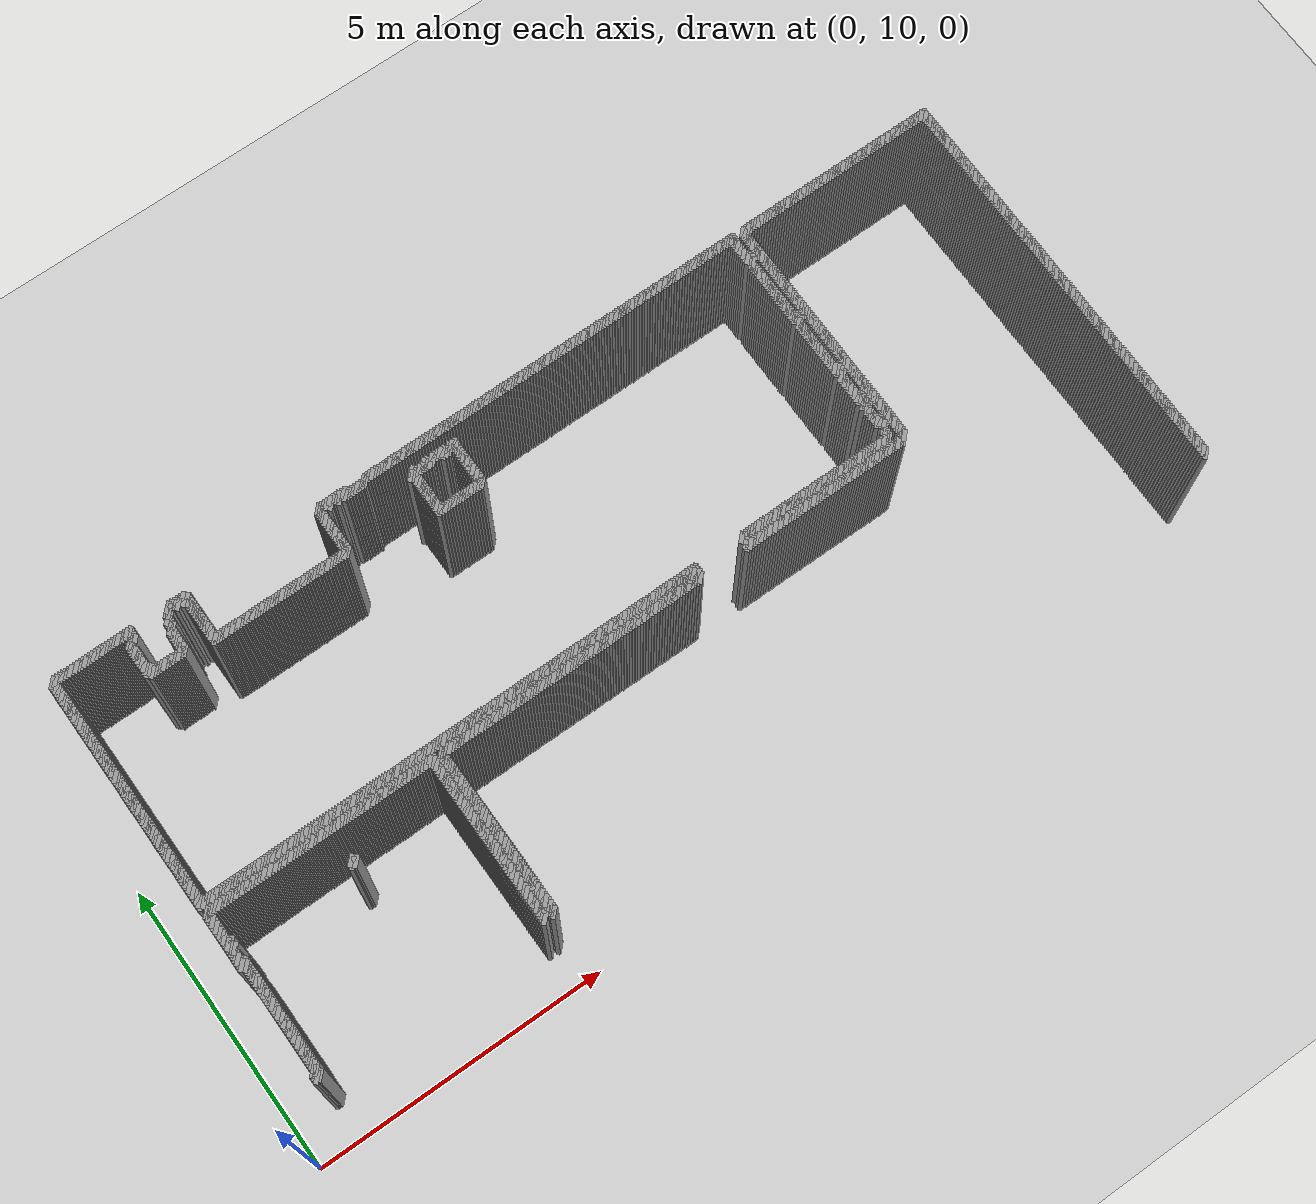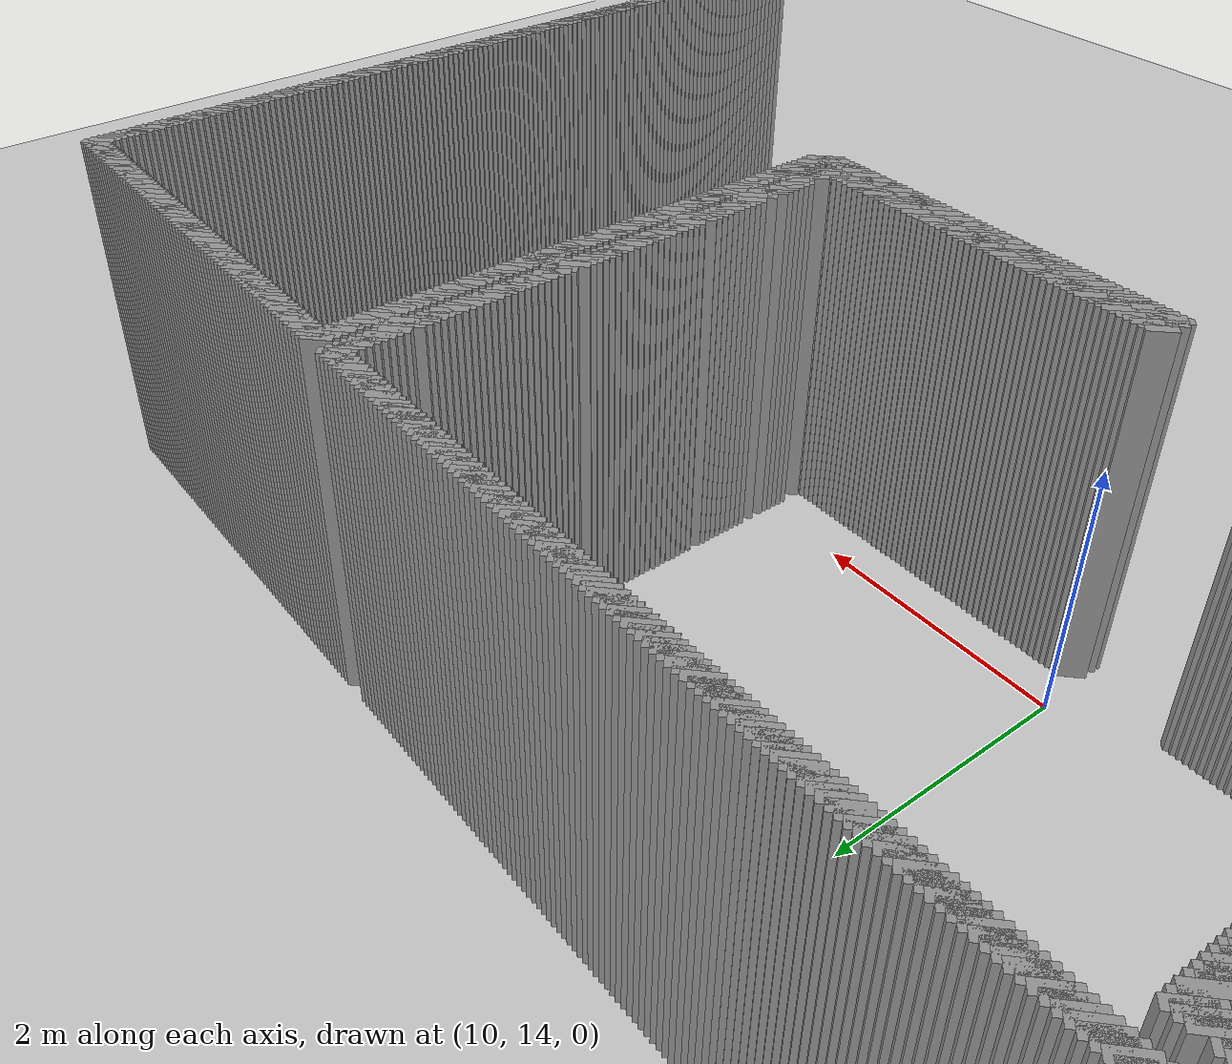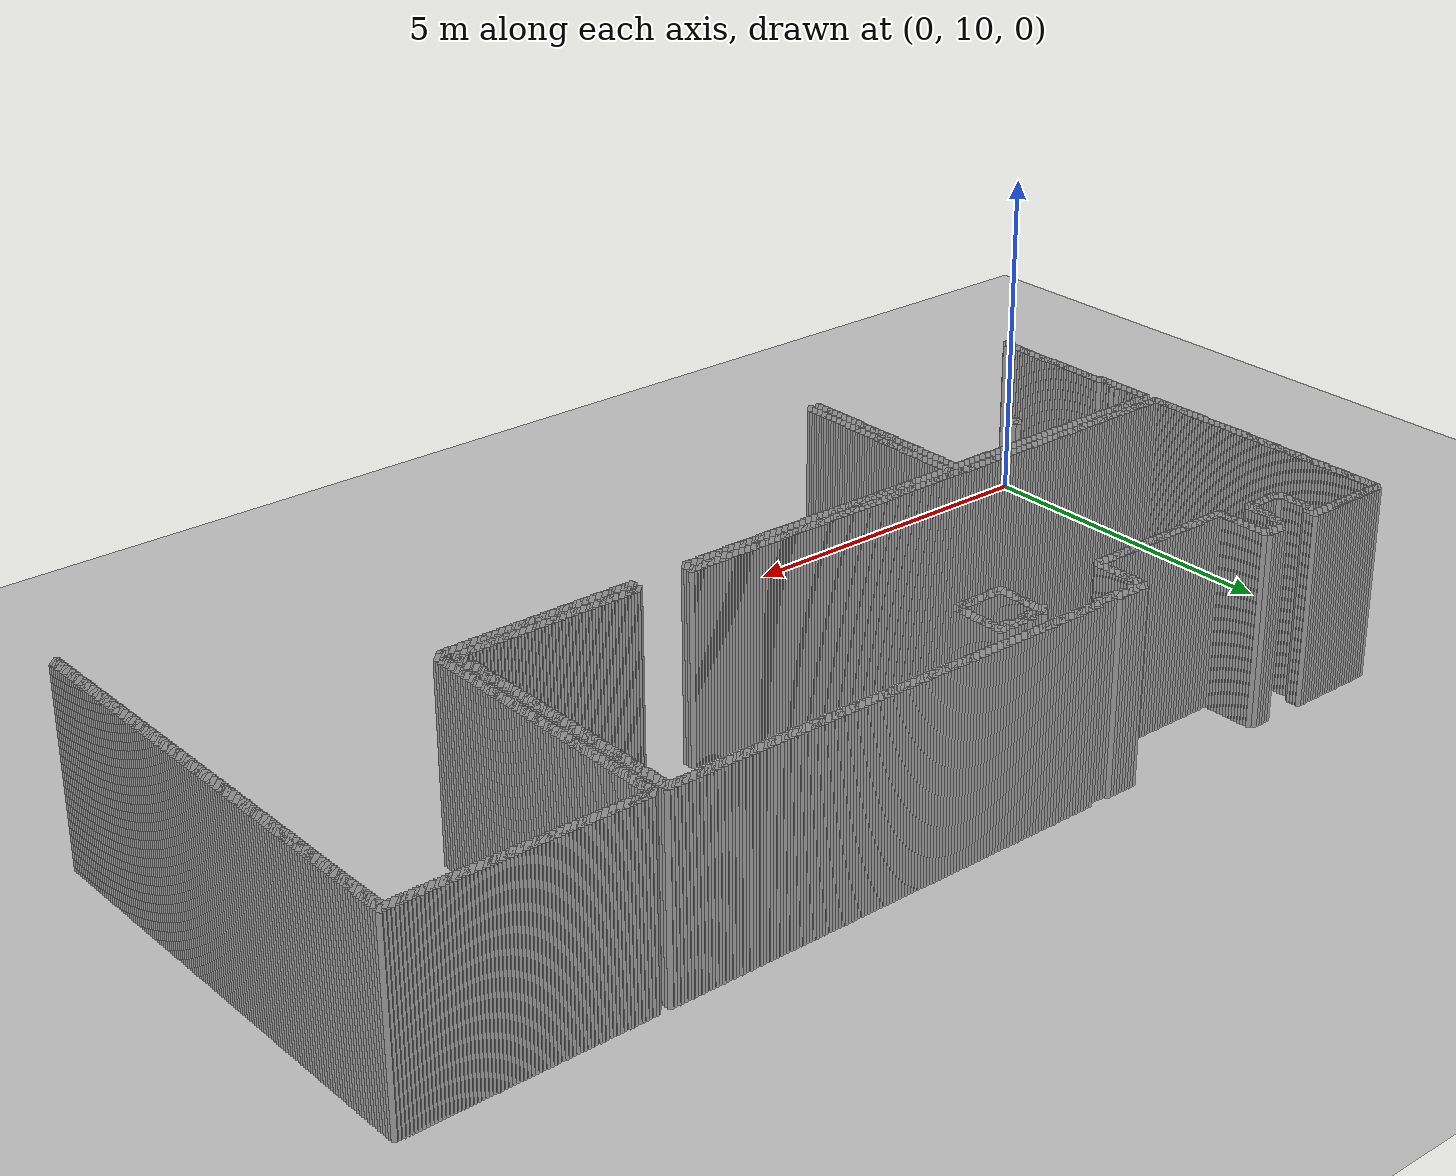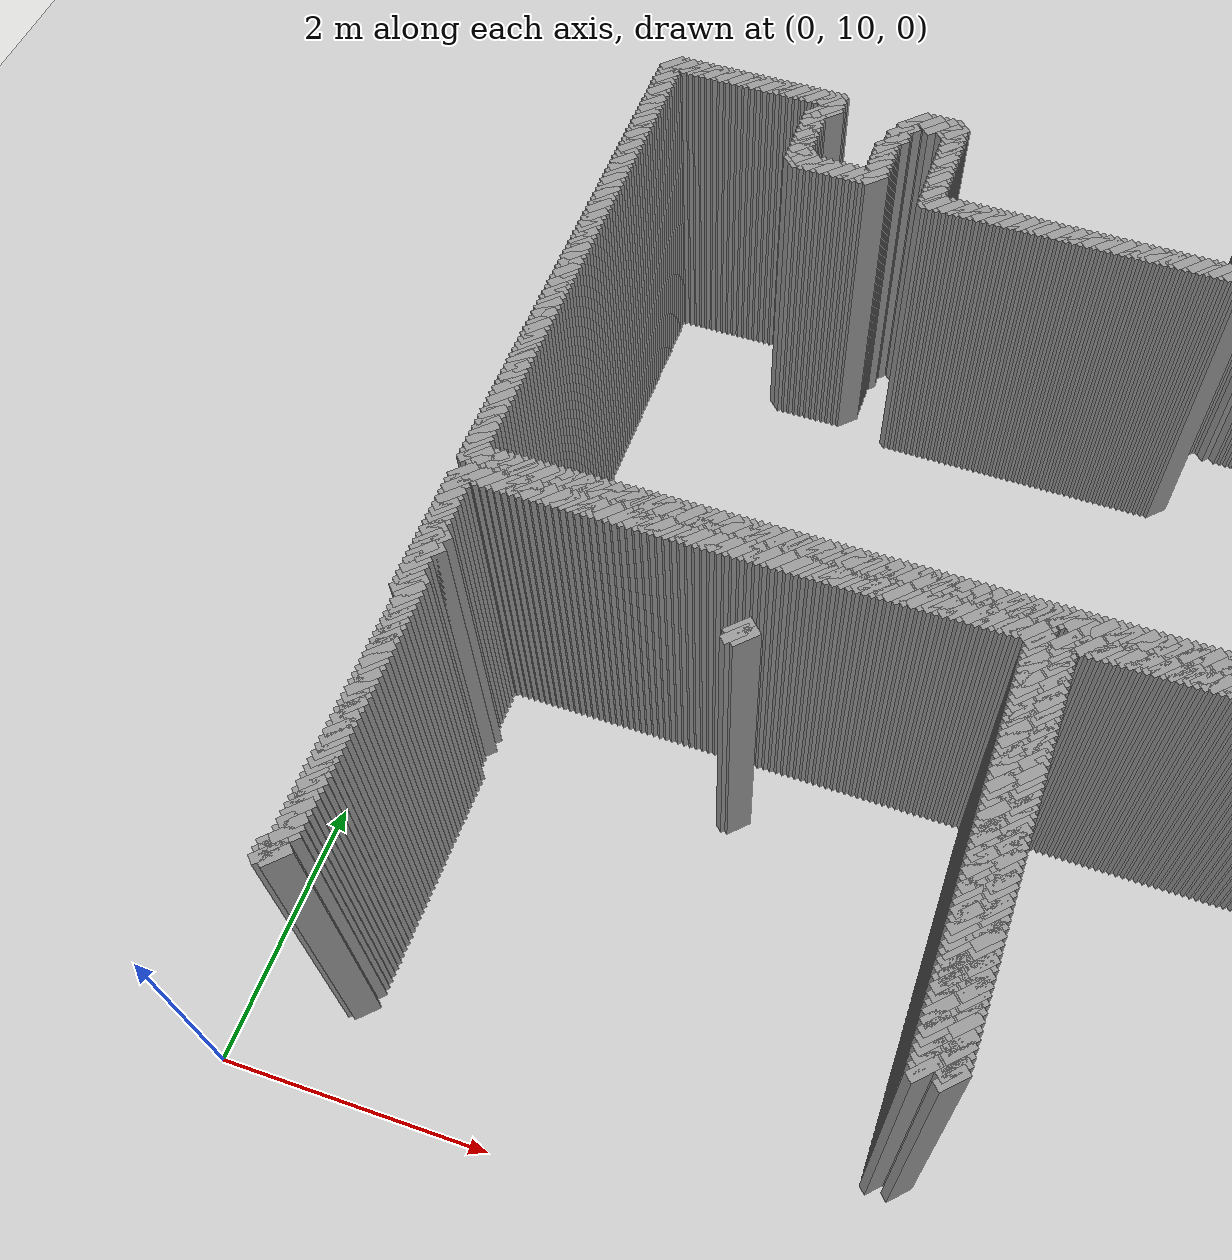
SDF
<sdf version="1.5">
 <world name="default">
  <plugin name="ActorPosesPlugin" filename="libActorPosesPlugin.so"/>
  <include><uri>model://ground_plane</uri></include>
  <include><uri>model://sun</uri></include>
  <model name="grey_wall_1">
   <static>1</static>
   <link name="link">
    <pose>0.75 17.55  1.4 0 0 -0.7853981633974194</pose>
    <collision name="collision">
     <geometry><box><size>0.07071067811865277 .2  2.8</size></box></geometry>
    </collision>
    <visual name="visual">
     <cast_shadows>0</cast_shadows>
     <geometry><box><size>0.07071067811865277 .2  2.8</size></box></geometry>
     <material>
      <script>
       <uri>model://grey_wall/materials/scripts</uri>
       <uri>model://grey_wall/materials/textures</uri>
       <name>vrc/grey_wall</name>
      </script>
     </material>
    </visual>
   </link>
  </model>
  <model name="grey_wall_2">
   <static>1</static>
   <link name="link">
    <pose>0.8 17.55  1.4 0 0 -0.7853981633974194</pose>
    <collision name="collision">
     <geometry><box><size>0.07071067811865277 .2  2.8</size></box></geometry>
    </collision>
    <visual name="visual">
     <cast_shadows>0</cast_shadows>
     <geometry><box><size>0.07071067811865277 .2  2.8</size></box></geometry>
     <material>
      <script>
       <uri>model://grey_wall/materials/scripts</uri>
       <uri>model://grey_wall/materials/textures</uri>
       <name>vrc/grey_wall</name>
      </script>
     </material>
    </visual>
   </link>
  </model>
  <model name="grey_wall_3">
   <static>1</static>
   <link name="link">
    <pose>0.8500000000000001 17.55  1.4 0 0 -0.7853981633974194</pose>
    <collision name="collision">
     <geometry><box><size>0.07071067811865277 .2  2.8</size></box></geometry>
    </collision>
    <visual name="visual">
     <cast_shadows>0</cast_shadows>
     <geometry><box><size>0.07071067811865277 .2  2.8</size></box></geometry>
     <material>
      <script>
       <uri>model://grey_wall/materials/scripts</uri>
       <uri>model://grey_wall/materials/textures</uri>
       <name>vrc/grey_wall</name>
      </script>
     </material>
    </visual>
   </link>
  </model>
  <model name="grey_wall_4">
   <static>1</static>
   <link name="link">
    <pose>0.9 17.55  1.4 0 0 -0.7853981633974194</pose>
    <collision name="collision">
     <geometry><box><size>0.07071067811865277 .2  2.8</size></box></geometry>
    </collision>
    <visual name="visual">
     <cast_shadows>0</cast_shadows>
     <geometry><box><size>0.07071067811865277 .2  2.8</size></box></geometry>
     <material>
      <script>
       <uri>model://grey_wall/materials/scripts</uri>
       <uri>model://grey_wall/materials/textures</uri>
       <name>vrc/grey_wall</name>
      </script>
     </material>
    </visual>
   </link>
  </model>
  <model name="grey_wall_5">
   <static>1</static>
   <link name="link">
    <pose>0.9500000000000001 17.55  1.4 0 0 -0.7853981633974194</pose>
    <collision name="collision">
     <geometry><box><size>0.07071067811865277 .2  2.8</size></box></geometry>
    </collision>
    <visual name="visual">
     <cast_shadows>0</cast_shadows>
     <geometry><box><size>0.07071067811865277 .2  2.8</size></box></geometry>
     <material>
      <script>
       <uri>model://grey_wall/materials/scripts</uri>
       <uri>model://grey_wall/materials/textures</uri>
       <name>vrc/grey_wall</name>
      </script>
     </material>
    </visual>
   </link>
  </model>
  <model name="grey_wall_6">
   <static>1</static>
   <link name="link">
    <pose>1.0 17.55  1.4 0 0 -0.7853981633974205</pose>
    <collision name="collision">
     <geometry><box><size>0.0707106781186527 .2  2.8</size></box></geometry>
    </collision>
    <visual name="visual">
     <cast_shadows>0</cast_shadows>
     <geometry><box><size>0.0707106781186527 .2  2.8</size></box></geometry>
     <material>
      <script>
       <uri>model://grey_wall/materials/scripts</uri>
       <uri>model://grey_wall/materials/textures</uri>
       <name>vrc/grey_wall</name>
      </script>
     </material>
    </visual>
   </link>
  </model>
  <model name="grey_wall_7">
   <static>1</static>
   <link name="link">
    <pose>1.05 17.55  1.4 0 0 -0.7853981633974216</pose>
    <collision name="collision">
     <geometry><box><size>0.07071067811865261 .2  2.8</size></box></geometry>
    </collision>
    <visual name="visual">
     <cast_shadows>0</cast_shadows>
     <geometry><box><size>0.07071067811865261 .2  2.8</size></box></geometry>
     <material>
      <script>
       <uri>model://grey_wall/materials/scripts</uri>
       <uri>model://grey_wall/materials/textures</uri>
       <name>vrc/grey_wall</name>
      </script>
     </material>
    </visual>
   </link>
  </model>
  <model name="grey_wall_8">
   <static>1</static>
   <link name="link">
    <pose>1.1 17.55  1.4 0 0 -0.7853981633974216</pose>
    <collision name="collision">
     <geometry><box><size>0.07071067811865261 .2  2.8</size></box></geometry>
    </collision>
    <visual name="visual">
     <cast_shadows>0</cast_shadows>
     <geometry><box><size>0.07071067811865261 .2  2.8</size></box></geometry>
     <material>
      <script>
       <uri>model://grey_wall/materials/scripts</uri>
       <uri>model://grey_wall/materials/textures</uri>
       <name>vrc/grey_wall</name>
      </script>
     </material>
    </visual>
   </link>
  </model>
  <model name="grey_wall_9">
   <static>1</static>
   <link name="link">
    <pose>1.1500000000000001 17.55  1.4 0 0 -0.7853981633974216</pose>
    <collision name="collision">
     <geometry><box><size>0.07071067811865261 .2  2.8</size></box></geometry>
    </collision>
    <visual name="visual">
     <cast_shadows>0</cast_shadows>
     <geometry><box><size>0.07071067811865261 .2  2.8</size></box></geometry>
     <material>
      <script>
       <uri>model://grey_wall/materials/scripts</uri>
       <uri>model://grey_wall/materials/textures</uri>
       <name>vrc/grey_wall</name>
      </script>
     </material>
    </visual>
   </link>
  </model>
  <model name="grey_wall_10">
   <static>1</static>
   <link name="link">
    <pose>1.2000000000000002 17.55  1.4 0 0 -0.7853981633974216</pose>
    <collision name="collision">
     <geometry><box><size>0.07071067811865261 .2  2.8</size></box></geometry>
    </collision>
    <visual name="visual">
     <cast_shadows>0</cast_shadows>
     <geometry><box><size>0.07071067811865261 .2  2.8</size></box></geometry>
     <material>
      <script>
       <uri>model://grey_wall/materials/scripts</uri>
       <uri>model://grey_wall/materials/textures</uri>
       <name>vrc/grey_wall</name>
      </script>
     </material>
    </visual>
   </link>
  </model>
  <model name="grey_wall_11">
   <static>1</static>
   <link name="link">
    <pose>1.25 17.55  1.4 0 0 -0.7853981633974216</pose>
    <collision name="collision">
     <geometry><box><size>0.07071067811865261 .2  2.8</size></box></geometry>
    </collision>
    <visual name="visual">
     <cast_shadows>0</cast_shadows>
     <geometry><box><size>0.07071067811865261 .2  2.8</size></box></geometry>
     <material>
      <script>
       <uri>model://grey_wall/materials/scripts</uri>
       <uri>model://grey_wall/materials/textures</uri>
       <name>vrc/grey_wall</name>
      </script>
     </material>
    </visual>
   </link>
  </model>
  <model name="grey_wall_12">
   <static>1</static>
   <link name="link">
    <pose>1.3 17.55  1.4 0 0 -0.7853981633974216</pose>
    <collision name="collision">
     <geometry><box><size>0.07071067811865261 .2  2.8</size></box></geometry>
    </collision>
    <visual name="visual">
     <cast_shadows>0</cast_shadows>
     <geometry><box><size>0.07071067811865261 .2  2.8</size></box></geometry>
     <material>
      <script>
       <uri>model://grey_wall/materials/scripts</uri>
       <uri>model://grey_wall/materials/textures</uri>
       <name>vrc/grey_wall</name>
      </script>
     </material>
    </visual>
   </link>
  </model>
  <model name="grey_wall_13">
   <static>1</static>
   <link name="link">
    <pose>1.35 17.55  1.4 0 0 -0.7853981633974216</pose>
    <collision name="collision">
     <geometry><box><size>0.07071067811865261 .2  2.8</size></box></geometry>
    </collision>
    <visual name="visual">
     <cast_shadows>0</cast_shadows>
     <geometry><box><size>0.07071067811865261 .2  2.8</size></box></geometry>
     <material>
      <script>
       <uri>model://grey_wall/materials/scripts</uri>
       <uri>model://grey_wall/materials/textures</uri>
       <name>vrc/grey_wall</name>
      </script>
     </material>
    </visual>
   </link>
  </model>
  <model name="grey_wall_14">
   <static>1</static>
   <link name="link">
    <pose>1.4000000000000001 17.55  1.4 0 0 -0.7853981633974216</pose>
    <collision name="collision">
     <geometry><box><size>0.07071067811865261 .2  2.8</size></box></geometry>
    </collision>
    <visual name="visual">
     <cast_shadows>0</cast_shadows>
     <geometry><box><size>0.07071067811865261 .2  2.8</size></box></geometry>
     <material>
      <script>
       <uri>model://grey_wall/materials/scripts</uri>
       <uri>model://grey_wall/materials/textures</uri>
       <name>vrc/grey_wall</name>
      </script>
     </material>
    </visual>
   </link>
  </model>
  <model name="grey_wall_15">
   <static>1</static>
   <link name="link">
    <pose>1.4500000000000002 17.55  1.4 0 0 -0.7853981633974216</pose>
    <collision name="collision">
     <geometry><box><size>0.07071067811865261 .2  2.8</size></box></geometry>
    </collision>
    <visual name="visual">
     <cast_shadows>0</cast_shadows>
     <geometry><box><size>0.07071067811865261 .2  2.8</size></box></geometry>
     <material>
      <script>
       <uri>model://grey_wall/materials/scripts</uri>
       <uri>model://grey_wall/materials/textures</uri>
       <name>vrc/grey_wall</name>
      </script>
     </material>
    </visual>
   </link>
  </model>
  <model name="grey_wall_16">
   <static>1</static>
   <link name="link">
    <pose>1.5 17.55  1.4 0 0 -0.7853981633974216</pose>
    <collision name="collision">
     <geometry><box><size>0.07071067811865261 .2  2.8</size></box></geometry>
    </collision>
    <visual name="visual">
     <cast_shadows>0</cast_shadows>
     <geometry><box><size>0.07071067811865261 .2  2.8</size></box></geometry>
     <material>
      <script>
       <uri>model://grey_wall/materials/scripts</uri>
       <uri>model://grey_wall/materials/textures</uri>
       <name>vrc/grey_wall</name>
      </script>
     </material>
    </visual>
   </link>
  </model>
  <model name="grey_wall_17">
   <static>1</static>
   <link name="link">
    <pose>1.55 17.55  1.4 0 0 -0.7853981633974216</pose>
    <collision name="collision">
     <geometry><box><size>0.07071067811865261 .2  2.8</size></box></geometry>
    </collision>
    <visual name="visual">
     <cast_shadows>0</cast_shadows>
     <geometry><box><size>0.07071067811865261 .2  2.8</size></box></geometry>
     <material>
      <script>
       <uri>model://grey_wall/materials/scripts</uri>
       <uri>model://grey_wall/materials/textures</uri>
       <name>vrc/grey_wall</name>
      </script>
     </material>
    </visual>
   </link>
  </model>
  <model name="grey_wall_18">
   <static>1</static>
   <link name="link">
    <pose>1.6 17.55  1.4 0 0 -0.7853981633974216</pose>
    <collision name="collision">
     <geometry><box><size>0.07071067811865261 .2  2.8</size></box></geometry>
    </collision>
    <visual name="visual">
     <cast_shadows>0</cast_shadows>
     <geometry><box><size>0.07071067811865261 .2  2.8</size></box></geometry>
     <material>
      <script>
       <uri>model://grey_wall/materials/scripts</uri>
       <uri>model://grey_wall/materials/textures</uri>
       <name>vrc/grey_wall</name>
      </script>
     </material>
    </visual>
   </link>
  </model>
  <model name="grey_wall_19">
   <static>1</static>
   <link name="link">
    <pose>1.6500000000000001 17.55  1.4 0 0 -0.7853981633974216</pose>
    <collision name="collision">
     <geometry><box><size>0.07071067811865261 .2  2.8</size></box></geometry>
    </collision>
    <visual name="visual">
     <cast_shadows>0</cast_shadows>
     <geometry><box><size>0.07071067811865261 .2  2.8</size></box></geometry>
     <material>
      <script>
       <uri>model://grey_wall/materials/scripts</uri>
       <uri>model://grey_wall/materials/textures</uri>
       <name>vrc/grey_wall</name>
      </script>
     </material>
    </visual>
   </link>
  </model>
  <model name="grey_wall_20">
   <static>1</static>
   <link name="link">
    <pose>1.7000000000000002 17.55  1.4 0 0 -0.7853981633974216</pose>
    <collision name="collision">
     <geometry><box><size>0.07071067811865261 .2  2.8</size></box></geometry>
    </collision>
    <visual name="visual">
     <cast_shadows>0</cast_shadows>
     <geometry><box><size>0.07071067811865261 .2  2.8</size></box></geometry>
     <material>
      <script>
       <uri>model://grey_wall/materials/scripts</uri>
       <uri>model://grey_wall/materials/textures</uri>
       <name>vrc/grey_wall</name>
      </script>
     </material>
    </visual>
   </link>
  </model>
  <model name="grey_wall_21">
   <static>1</static>
   <link name="link">
    <pose>1.75 17.55  1.4 0 0 -0.7853981633974216</pose>
    <collision name="collision">
     <geometry><box><size>0.07071067811865261 .2  2.8</size></box></geometry>
    </collision>
    <visual name="visual">
     <cast_shadows>0</cast_shadows>
     <geometry><box><size>0.07071067811865261 .2  2.8</size></box></geometry>
     <material>
      <script>
       <uri>model://grey_wall/materials/scripts</uri>
       <uri>model://grey_wall/materials/textures</uri>
       <name>vrc/grey_wall</name>
      </script>
     </material>
    </visual>
   </link>
  </model>
  <model name="grey_wall_22">
   <static>1</static>
   <link name="link">
    <pose>1.8 17.55  1.4 0 0 -0.7853981633974216</pose>
    <collision name="collision">
     <geometry><box><size>0.07071067811865261 .2  2.8</size></box></geometry>
    </collision>
    <visual name="visual">
     <cast_shadows>0</cast_shadows>
     <geometry><box><size>0.07071067811865261 .2  2.8</size></box></geometry>
     <material>
      <script>
       <uri>model://grey_wall/materials/scripts</uri>
       <uri>model://grey_wall/materials/textures</uri>
       <name>vrc/grey_wall</name>
      </script>
     </material>
    </visual>
   </link>
  </model>
  <model name="grey_wall_23">
   <static>1</static>
   <link name="link">
    <pose>1.85 17.55  1.4 0 0 -0.7853981633974216</pose>
    <collision name="collision">
     <geometry><box><size>0.07071067811865261 .2  2.8</size></box></geometry>
    </collision>
    <visual name="visual">
     <cast_shadows>0</cast_shadows>
     <geometry><box><size>0.07071067811865261 .2  2.8</size></box></geometry>
     <material>
      <script>
       <uri>model://grey_wall/materials/scripts</uri>
       <uri>model://grey_wall/materials/textures</uri>
       <name>vrc/grey_wall</name>
      </script>
     </material>
    </visual>
   </link>
  </model>
  <model name="grey_wall_24">
   <static>1</static>
   <link name="link">
    <pose>1.9000000000000001 17.55  1.4 0 0 -0.7853981633974216</pose>
    <collision name="collision">
     <geometry><box><size>0.07071067811865261 .2  2.8</size></box></geometry>
    </collision>
    <visual name="visual">
     <cast_shadows>0</cast_shadows>
     <geometry><box><size>0.07071067811865261 .2  2.8</size></box></geometry>
     <material>
      <script>
       <uri>model://grey_wall/materials/scripts</uri>
       <uri>model://grey_wall/materials/textures</uri>
       <name>vrc/grey_wall</name>
      </script>
     </material>
    </visual>
   </link>
  </model>
  <model name="grey_wall_25">
   <static>1</static>
   <link name="link">
    <pose>1.9500000000000002 17.55  1.4 0 0 -0.7853981633974216</pose>
    <collision name="collision">
     <geometry><box><size>0.07071067811865261 .2  2.8</size></box></geometry>
    </collision>
    <visual name="visual">
     <cast_shadows>0</cast_shadows>
     <geometry><box><size>0.07071067811865261 .2  2.8</size></box></geometry>
     <material>
      <script>
       <uri>model://grey_wall/materials/scripts</uri>
       <uri>model://grey_wall/materials/textures</uri>
       <name>vrc/grey_wall</name>
      </script>
     </material>
    </visual>
   </link>
  </model>
  <model name="grey_wall_26">
   <static>1</static>
   <link name="link">
    <pose>2.0 17.55  1.4 0 0 -0.7853981633974216</pose>
    <collision name="collision">
     <geometry><box><size>0.07071067811865261 .2  2.8</size></box></geometry>
    </collision>
    <visual name="visual">
     <cast_shadows>0</cast_shadows>
     <geometry><box><size>0.07071067811865261 .2  2.8</size></box></geometry>
     <material>
      <script>
       <uri>model://grey_wall/materials/scripts</uri>
       <uri>model://grey_wall/materials/textures</uri>
       <name>vrc/grey_wall</name>
      </script>
     </material>
    </visual>
   </link>
  </model>
  <model name="grey_wall_27">
   <static>1</static>
   <link name="link">
    <pose>2.0500000000000003 17.55  1.4 0 0 -0.7853981633974216</pose>
    <collision name="collision">
     <geometry><box><size>0.07071067811865261 .2  2.8</size></box></geometry>
    </collision>
    <visual name="visual">
     <cast_shadows>0</cast_shadows>
     <geometry><box><size>0.07071067811865261 .2  2.8</size></box></geometry>
     <material>
      <script>
       <uri>model://grey_wall/materials/scripts</uri>
       <uri>model://grey_wall/materials/textures</uri>
       <name>vrc/grey_wall</name>
      </script>
     </material>
    </visual>
   </link>
  </model>
  <model name="grey_wall_28">
   <static>1</static>
   <link name="link">
    <pose>2.7 17.55  1.4 0 0 -0.7853981633974216</pose>
    <collision name="collision">
     <geometry><box><size>0.07071067811865261 .2  2.8</size></box></geometry>
    </collision>
    <visual name="visual">
     <cast_shadows>0</cast_shadows>
     <geometry><box><size>0.07071067811865261 .2  2.8</size></box></geometry>
     <material>
      <script>
       <uri>model://grey_wall/materials/scripts</uri>
       <uri>model://grey_wall/materials/textures</uri>
       <name>vrc/grey_wall</name>
      </script>
     </material>
    </visual>
   </link>
  </model>
  <model name="grey_wall_29">
   <static>1</static>
   <link name="link">
    <pose>2.75 17.55  1.4 0 0 -0.7853981633974216</pose>
    <collision name="collision">
     <geometry><box><size>0.07071067811865261 .2  2.8</size></box></geometry>
    </collision>
    <visual name="visual">
     <cast_shadows>0</cast_shadows>
     <geometry><box><size>0.07071067811865261 .2  2.8</size></box></geometry>
     <material>
      <script>
       <uri>model://grey_wall/materials/scripts</uri>
       <uri>model://grey_wall/materials/textures</uri>
       <name>vrc/grey_wall</name>
      </script>
     </material>
    </visual>
   </link>
  </model>
  <model name="grey_wall_30">
   <static>1</static>
   <link name="link">
    <pose>2.8000000000000003 17.55  1.4 0 0 -0.7853981633974216</pose>
    <collision name="collision">
     <geometry><box><size>0.07071067811865261 .2  2.8</size></box></geometry>
    </collision>
    <visual name="visual">
     <cast_shadows>0</cast_shadows>
     <geometry><box><size>0.07071067811865261 .2  2.8</size></box></geometry>
     <material>
      <script>
       <uri>model://grey_wall/materials/scripts</uri>
       <uri>model://grey_wall/materials/textures</uri>
       <name>vrc/grey_wall</name>
      </script>
     </material>
    </visual>
   </link>
  </model>
  <model name="grey_wall_31">
   <static>1</static>
   <link name="link">
    <pose>2.85 17.55  1.4 0 0 -0.7853981633974216</pose>
    <collision name="collision">
     <geometry><box><size>0.07071067811865261 .2  2.8</size></box></geometry>
    </collision>
    <visual name="visual">
     <cast_shadows>0</cast_shadows>
     <geometry><box><size>0.07071067811865261 .2  2.8</size></box></geometry>
     <material>
      <script>
       <uri>model://grey_wall/materials/scripts</uri>
       <uri>model://grey_wall/materials/textures</uri>
       <name>vrc/grey_wall</name>
      </script>
     </material>
    </visual>
   </link>
  </model>
  <model name="grey_wall_32">
   <static>1</static>
   <link name="link">
    <pose>2.9000000000000004 17.55  1.4 0 0 -0.7853981633974216</pose>
    <collision name="collision">
     <geometry><box><size>0.07071067811865261 .2  2.8</size></box></geometry>
    </collision>
    <visual name="visual">
     <cast_shadows>0</cast_shadows>
     <geometry><box><size>0.07071067811865261 .2  2.8</size></box></geometry>
     <material>
      <script>
       <uri>model://grey_wall/materials/scripts</uri>
       <uri>model://grey_wall/materials/textures</uri>
       <name>vrc/grey_wall</name>
      </script>
     </material>
    </visual>
   </link>
  </model>
  <model name="grey_wall_33">
   <static>1</static>
   <link name="link">
    <pose>2.95 17.55  1.4 0 0 -0.7853981633974216</pose>
    <collision name="collision">
     <geometry><box><size>0.07071067811865261 .2  2.8</size></box></geometry>
    </collision>
    <visual name="visual">
     <cast_shadows>0</cast_shadows>
     <geometry><box><size>0.07071067811865261 .2  2.8</size></box></geometry>
     <material>
      <script>
       <uri>model://grey_wall/materials/scripts</uri>
       <uri>model://grey_wall/materials/textures</uri>
       <name>vrc/grey_wall</name>
      </script>
     </material>
    </visual>
   </link>
  </model>
  <model name="grey_wall_34">
   <static>1</static>
   <link name="link">
    <pose>5.300000000000001 17.55  1.4 0 0 -0.7853981633974128</pose>
    <collision name="collision">
     <geometry><box><size>0.07071067811865325 .2  2.8</size></box></geometry>
    </collision>
    <visual name="visual">
     <cast_shadows>0</cast_shadows>
     <geometry><box><size>0.07071067811865325 .2  2.8</size></box></geometry>
     <material>
      <script>
       <uri>model://grey_wall/materials/scripts</uri>
       <uri>model://grey_wall/materials/textures</uri>
       <name>vrc/grey_wall</name>
      </script>
     </material>
    </visual>
   </link>
  </model>
  <model name="grey_wall_35">
   <static>1</static>
   <link name="link">
    <pose>5.3500000000000005 17.55  1.4 0 0 -0.7853981633974128</pose>
    <collision name="collision">
     <geometry><box><size>0.07071067811865325 .2  2.8</size></box></geometry>
    </collision>
    <visual name="visual">
     <cast_shadows>0</cast_shadows>
     <geometry><box><size>0.07071067811865325 .2  2.8</size></box></geometry>
     <material>
      <script>
       <uri>model://grey_wall/materials/scripts</uri>
       <uri>model://grey_wall/materials/textures</uri>
       <name>vrc/grey_wall</name>
      </script>
     </material>
    </visual>
   </link>
  </model>
  <model name="grey_wall_36">
   <static>1</static>
   <link name="link">
    <pose>5.4 17.55  1.4 0 0 -0.7853981633974128</pose>
    <collision name="collision">
     <geometry><box><size>0.07071067811865325 .2  2.8</size></box></geometry>
    </collision>
    <visual name="visual">
     <cast_shadows>0</cast_shadows>
     <geometry><box><size>0.07071067811865325 .2  2.8</size></box></geometry>
     <material>
      <script>
       <uri>model://grey_wall/materials/scripts</uri>
       <uri>model://grey_wall/materials/textures</uri>
       <name>vrc/grey_wall</name>
      </script>
     </material>
    </visual>
   </link>
  </model>
  <model name="grey_wall_37">
   <static>1</static>
   <link name="link">
    <pose>5.45 17.55  1.4 0 0 -0.7853981633974128</pose>
    <collision name="collision">
     <geometry><box><size>0.07071067811865325 .2  2.8</size></box></geometry>
    </collision>
    <visual name="visual">
     <cast_shadows>0</cast_shadows>
     <geometry><box><size>0.07071067811865325 .2  2.8</size></box></geometry>
     <material>
      <script>
       <uri>model://grey_wall/materials/scripts</uri>
       <uri>model://grey_wall/materials/textures</uri>
       <name>vrc/grey_wall</name>
      </script>
     </material>
    </visual>
   </link>
  </model>
  <model name="grey_wall_38">
   <static>1</static>
   <link name="link">
    <pose>5.5 17.55  1.4 0 0 -0.7853981633974128</pose>
    <collision name="collision">
     <geometry><box><size>0.07071067811865325 .2  2.8</size></box></geometry>
    </collision>
    <visual name="visual">
     <cast_shadows>0</cast_shadows>
     <geometry><box><size>0.07071067811865325 .2  2.8</size></box></geometry>
     <material>
      <script>
       <uri>model://grey_wall/materials/scripts</uri>
       <uri>model://grey_wall/materials/textures</uri>
       <name>vrc/grey_wall</name>
      </script>
     </material>
    </visual>
   </link>
  </model>
  <model name="grey_wall_39">
   <static>1</static>
   <link name="link">
    <pose>5.550000000000001 17.55  1.4 0 0 -0.7853981633974128</pose>
    <collision name="collision">
     <geometry><box><size>0.07071067811865325 .2  2.8</size></box></geometry>
    </collision>
    <visual name="visual">
     <cast_shadows>0</cast_shadows>
     <geometry><box><size>0.07071067811865325 .2  2.8</size></box></geometry>
     <material>
      <script>
       <uri>model://grey_wall/materials/scripts</uri>
       <uri>model://grey_wall/materials/textures</uri>
       <name>vrc/grey_wall</name>
      </script>
     </material>
    </visual>
   </link>
  </model>
  <model name="grey_wall_40">
   <static>1</static>
   <link name="link">
    <pose>5.6000000000000005 17.55  1.4 0 0 -0.7853981633974128</pose>
    <collision name="collision">
     <geometry><box><size>0.07071067811865325 .2  2.8</size></box></geometry>
    </collision>
    <visual name="visual">
     <cast_shadows>0</cast_shadows>
     <geometry><box><size>0.07071067811865325 .2  2.8</size></box></geometry>
     <material>
      <script>
       <uri>model://grey_wall/materials/scripts</uri>
       <uri>model://grey_wall/materials/textures</uri>
       <name>vrc/grey_wall</name>
      </script>
     </material>
    </visual>
   </link>
  </model>
  <model name="grey_wall_41">
   <static>1</static>
   <link name="link">
    <pose>5.65 17.55  1.4 0 0 -0.7853981633974128</pose>
    <collision name="collision">
     <geometry><box><size>0.07071067811865325 .2  2.8</size></box></geometry>
    </collision>
    <visual name="visual">
     <cast_shadows>0</cast_shadows>
     <geometry><box><size>0.07071067811865325 .2  2.8</size></box></geometry>
     <material>
      <script>
       <uri>model://grey_wall/materials/scripts</uri>
       <uri>model://grey_wall/materials/textures</uri>
       <name>vrc/grey_wall</name>
      </script>
     </material>
    </visual>
   </link>
  </model>
  <model name="grey_wall_42">
   <static>1</static>
   <link name="link">
    <pose>5.7 17.55  1.4 0 0 -0.7853981633974128</pose>
    <collision name="collision">
     <geometry><box><size>0.07071067811865325 .2  2.8</size></box></geometry>
    </collision>
    <visual name="visual">
     <cast_shadows>0</cast_shadows>
     <geometry><box><size>0.07071067811865325 .2  2.8</size></box></geometry>
     <material>
      <script>
       <uri>model://grey_wall/materials/scripts</uri>
       <uri>model://grey_wall/materials/textures</uri>
       <name>vrc/grey_wall</name>
      </script>
     </material>
    </visual>
   </link>
  </model>
  <model name="grey_wall_43">
   <static>1</static>
   <link name="link">
    <pose>5.75 17.55  1.4 0 0 -0.7853981633974128</pose>
    <collision name="collision">
     <geometry><box><size>0.07071067811865325 .2  2.8</size></box></geometry>
    </collision>
    <visual name="visual">
     <cast_shadows>0</cast_shadows>
     <geometry><box><size>0.07071067811865325 .2  2.8</size></box></geometry>
     <material>
      <script>
       <uri>model://grey_wall/materials/scripts</uri>
       <uri>model://grey_wall/materials/textures</uri>
       <name>vrc/grey_wall</name>
      </script>
     </material>
    </visual>
   </link>
  </model>
  <model name="grey_wall_44">
   <static>1</static>
   <link name="link">
    <pose>6.1000000000000005 17.55  1.4 0 0 -0.7853981633974128</pose>
    <collision name="collision">
     <geometry><box><size>0.07071067811865325 .2  2.8</size></box></geometry>
    </collision>
    <visual name="visual">
     <cast_shadows>0</cast_shadows>
     <geometry><box><size>0.07071067811865325 .2  2.8</size></box></geometry>
     <material>
      <script>
       <uri>model://grey_wall/materials/scripts</uri>
       <uri>model://grey_wall/materials/textures</uri>
       <name>vrc/grey_wall</name>
      </script>
     </material>
    </visual>
   </link>
  </model>
  <model name="grey_wall_45">
   <static>1</static>
   <link name="link">
    <pose>6.15 17.55  1.4 0 0 -0.7853981633974128</pose>
    <collision name="collision">
     <geometry><box><size>0.07071067811865325 .2  2.8</size></box></geometry>
    </collision>
    <visual name="visual">
     <cast_shadows>0</cast_shadows>
     <geometry><box><size>0.07071067811865325 .2  2.8</size></box></geometry>
     <material>
      <script>
       <uri>model://grey_wall/materials/scripts</uri>
       <uri>model://grey_wall/materials/textures</uri>
       <name>vrc/grey_wall</name>
      </script>
     </material>
    </visual>
   </link>
  </model>
  <model name="grey_wall_46">
   <static>1</static>
   <link name="link">
    <pose>6.2 17.55  1.4 0 0 -0.7853981633974128</pose>
    <collision name="collision">
     <geometry><box><size>0.07071067811865325 .2  2.8</size></box></geometry>
    </collision>
    <visual name="visual">
     <cast_shadows>0</cast_shadows>
     <geometry><box><size>0.07071067811865325 .2  2.8</size></box></geometry>
     <material>
      <script>
       <uri>model://grey_wall/materials/scripts</uri>
       <uri>model://grey_wall/materials/textures</uri>
       <name>vrc/grey_wall</name>
      </script>
     </material>
    </visual>
   </link>
  </model>
  <model name="grey_wall_47">
   <static>1</static>
   <link name="link">
    <pose>6.25 17.55  1.4 0 0 -0.7853981633974128</pose>
    <collision name="collision">
     <geometry><box><size>0.07071067811865325 .2  2.8</size></box></geometry>
    </collision>
    <visual name="visual">
     <cast_shadows>0</cast_shadows>
     <geometry><box><size>0.07071067811865325 .2  2.8</size></box></geometry>
     <material>
      <script>
       <uri>model://grey_wall/materials/scripts</uri>
       <uri>model://grey_wall/materials/textures</uri>
       <name>vrc/grey_wall</name>
      </script>
     </material>
    </visual>
   </link>
  </model>
  <model name="grey_wall_48">
   <static>1</static>
   <link name="link">
    <pose>6.300000000000001 17.55  1.4 0 0 -0.7853981633974128</pose>
    <collision name="collision">
     <geometry><box><size>0.07071067811865325 .2  2.8</size></box></geometry>
    </collision>
    <visual name="visual">
     <cast_shadows>0</cast_shadows>
     <geometry><box><size>0.07071067811865325 .2  2.8</size></box></geometry>
     <material>
      <script>
       <uri>model://grey_wall/materials/scripts</uri>
       <uri>model://grey_wall/materials/textures</uri>
       <name>vrc/grey_wall</name>
      </script>
     </material>
    </visual>
   </link>
  </model>
  <model name="grey_wall_49">
   <static>1</static>
   <link name="link">
    <pose>6.3500000000000005 17.55  1.4 0 0 -0.7853981633974128</pose>
    <collision name="collision">
     <geometry><box><size>0.07071067811865325 .2  2.8</size></box></geometry>
    </collision>
    <visual name="visual">
     <cast_shadows>0</cast_shadows>
     <geometry><box><size>0.07071067811865325 .2  2.8</size></box></geometry>
     <material>
      <script>
       <uri>model://grey_wall/materials/scripts</uri>
       <uri>model://grey_wall/materials/textures</uri>
       <name>vrc/grey_wall</name>
      </script>
     </material>
    </visual>
   </link>
  </model>
  <model name="grey_wall_50">
   <static>1</static>
   <link name="link">
    <pose>6.4 17.55  1.4 0 0 -0.7853981633974128</pose>
    <collision name="collision">
     <geometry><box><size>0.07071067811865325 .2  2.8</size></box></geometry>
    </collision>
    <visual name="visual">
     <cast_shadows>0</cast_shadows>
     <geometry><box><size>0.07071067811865325 .2  2.8</size></box></geometry>
     <material>
      <script>
       <uri>model://grey_wall/materials/scripts</uri>
       <uri>model://grey_wall/materials/textures</uri>
       <name>vrc/grey_wall</name>
      </script>
     </material>
    </visual>
   </link>
  </model>
  <model name="grey_wall_51">
   <static>1</static>
   <link name="link">
    <pose>6.45 17.55  1.4 0 0 -0.7853981633974128</pose>
    <collision name="collision">
     <geometry><box><size>0.07071067811865325 .2  2.8</size></box></geometry>
    </collision>
    <visual name="visual">
     <cast_shadows>0</cast_shadows>
     <geometry><box><size>0.07071067811865325 .2  2.8</size></box></geometry>
     <material>
      <script>
       <uri>model://grey_wall/materials/scripts</uri>
       <uri>model://grey_wall/materials/textures</uri>
       <name>vrc/grey_wall</name>
      </script>
     </material>
    </visual>
   </link>
  </model>
  <model name="grey_wall_52">
   <static>1</static>
   <link name="link">
    <pose>6.5 17.55  1.4 0 0 -0.7853981633974128</pose>
    <collision name="collision">
     <geometry><box><size>0.07071067811865325 .2  2.8</size></box></geometry>
    </collision>
    <visual name="visual">
     <cast_shadows>0</cast_shadows>
     <geometry><box><size>0.07071067811865325 .2  2.8</size></box></geometry>
     <material>
      <script>
       <uri>model://grey_wall/materials/scripts</uri>
       <uri>model://grey_wall/materials/textures</uri>
       <name>vrc/grey_wall</name>
      </script>
     </material>
    </visual>
   </link>
  </model>
  <model name="grey_wall_53">
   <static>1</static>
   <link name="link">
    <pose>6.550000000000001 17.55  1.4 0 0 -0.7853981633974128</pose>
    <collision name="collision">
     <geometry><box><size>0.07071067811865325 .2  2.8</size></box></geometry>
    </collision>
    <visual name="visual">
     <cast_shadows>0</cast_shadows>
     <geometry><box><size>0.07071067811865325 .2  2.8</size></box></geometry>
     <material>
      <script>
       <uri>model://grey_wall/materials/scripts</uri>
       <uri>model://grey_wall/materials/textures</uri>
       <name>vrc/grey_wall</name>
      </script>
     </material>
    </visual>
   </link>
  </model>
  <model name="grey_wall_54">
   <static>1</static>
   <link name="link">
    <pose>6.6000000000000005 17.55  1.4 0 0 -0.7853981633974128</pose>
    <collision name="collision">
     <geometry><box><size>0.07071067811865325 .2  2.8</size></box></geometry>
    </collision>
    <visual name="visual">
     <cast_shadows>0</cast_shadows>
     <geometry><box><size>0.07071067811865325 .2  2.8</size></box></geometry>
     <material>
      <script>
       <uri>model://grey_wall/materials/scripts</uri>
       <uri>model://grey_wall/materials/textures</uri>
       <name>vrc/grey_wall</name>
      </script>
     </material>
    </visual>
   </link>
  </model>
  <model name="grey_wall_55">
   <static>1</static>
   <link name="link">
    <pose>6.65 17.55  1.4 0 0 -0.7853981633974128</pose>
    <collision name="collision">
     <geometry><box><size>0.07071067811865325 .2  2.8</size></box></geometry>
    </collision>
    <visual name="visual">
     <cast_shadows>0</cast_shadows>
     <geometry><box><size>0.07071067811865325 .2  2.8</size></box></geometry>
     <material>
      <script>
       <uri>model://grey_wall/materials/scripts</uri>
       <uri>model://grey_wall/materials/textures</uri>
       <name>vrc/grey_wall</name>
      </script>
     </material>
    </visual>
   </link>
  </model>
  <model name="grey_wall_56">
   <static>1</static>
   <link name="link">
    <pose>6.7 17.55  1.4 0 0 -0.7853981633974128</pose>
    <collision name="collision">
     <geometry><box><size>0.07071067811865325 .2  2.8</size></box></geometry>
    </collision>
    <visual name="visual">
     <cast_shadows>0</cast_shadows>
     <geometry><box><size>0.07071067811865325 .2  2.8</size></box></geometry>
     <material>
      <script>
       <uri>model://grey_wall/materials/scripts</uri>
       <uri>model://grey_wall/materials/textures</uri>
       <name>vrc/grey_wall</name>
      </script>
     </material>
    </visual>
   </link>
  </model>
  <model name="grey_wall_57">
   <static>1</static>
   <link name="link">
    <pose>6.75 17.55  1.4 0 0 -0.7853981633974128</pose>
    <collision name="collision">
     <geometry><box><size>0.07071067811865325 .2  2.8</size></box></geometry>
    </collision>
    <visual name="visual">
     <cast_shadows>0</cast_shadows>
     <geometry><box><size>0.07071067811865325 .2  2.8</size></box></geometry>
     <material>
      <script>
       <uri>model://grey_wall/materials/scripts</uri>
       <uri>model://grey_wall/materials/textures</uri>
       <name>vrc/grey_wall</name>
      </script>
     </material>
    </visual>
   </link>
  </model>
  <model name="grey_wall_58">
   <static>1</static>
   <link name="link">
    <pose>6.800000000000001 17.55  1.4 0 0 -0.7853981633974128</pose>
    <collision name="collision">
     <geometry><box><size>0.07071067811865325 .2  2.8</size></box></geometry>
    </collision>
    <visual name="visual">
     <cast_shadows>0</cast_shadows>
     <geometry><box><size>0.07071067811865325 .2  2.8</size></box></geometry>
     <material>
      <script>
       <uri>model://grey_wall/materials/scripts</uri>
       <uri>model://grey_wall/materials/textures</uri>
       <name>vrc/grey_wall</name>
      </script>
     </material>
    </visual>
   </link>
  </model>
  <model name="grey_wall_59">
   <static>1</static>
   <link name="link">
    <pose>6.8500000000000005 17.55  1.4 0 0 -0.7853981633974128</pose>
    <collision name="collision">
     <geometry><box><size>0.07071067811865325 .2  2.8</size></box></geometry>
    </collision>
    <visual name="visual">
     <cast_shadows>0</cast_shadows>
     <geometry><box><size>0.07071067811865325 .2  2.8</size></box></geometry>
     <material>
      <script>
       <uri>model://grey_wall/materials/scripts</uri>
       <uri>model://grey_wall/materials/textures</uri>
       <name>vrc/grey_wall</name>
      </script>
     </material>
    </visual>
   </link>
  </model>
  <model name="grey_wall_60">
   <static>1</static>
   <link name="link">
    <pose>6.9 17.55  1.4 0 0 -0.7853981633974128</pose>
    <collision name="collision">
     <geometry><box><size>0.07071067811865325 .2  2.8</size></box></geometry>
    </collision>
    <visual name="visual">
     <cast_shadows>0</cast_shadows>
     <geometry><box><size>0.07071067811865325 .2  2.8</size></box></geometry>
     <material>
      <script>
       <uri>model://grey_wall/materials/scripts</uri>
       <uri>model://grey_wall/materials/textures</uri>
       <name>vrc/grey_wall</name>
      </script>
     </material>
    </visual>
   </link>
  </model>
  <model name="grey_wall_61">
   <static>1</static>
   <link name="link">
    <pose>6.95 17.55  1.4 0 0 -0.7853981633974128</pose>
    <collision name="collision">
     <geometry><box><size>0.07071067811865325 .2  2.8</size></box></geometry>
    </collision>
    <visual name="visual">
     <cast_shadows>0</cast_shadows>
     <geometry><box><size>0.07071067811865325 .2  2.8</size></box></geometry>
     <material>
      <script>
       <uri>model://grey_wall/materials/scripts</uri>
       <uri>model://grey_wall/materials/textures</uri>
       <name>vrc/grey_wall</name>
      </script>
     </material>
    </visual>
   </link>
  </model>
  <model name="grey_wall_62">
   <static>1</static>
   <link name="link">
    <pose>7.0 17.55  1.4 0 0 -0.7853981633974128</pose>
    <collision name="collision">
     <geometry><box><size>0.07071067811865325 .2  2.8</size></box></geometry>
    </collision>
    <visual name="visual">
     <cast_shadows>0</cast_shadows>
     <geometry><box><size>0.07071067811865325 .2  2.8</size></box></geometry>
     <material>
      <script>
       <uri>model://grey_wall/materials/scripts</uri>
       <uri>model://grey_wall/materials/textures</uri>
       <name>vrc/grey_wall</name>
      </script>
     </material>
    </visual>
   </link>
  </model>
  <model name="grey_wall_63">
   <static>1</static>
   <link name="link">
    <pose>7.050000000000001 17.55  1.4 0 0 -0.7853981633974128</pose>
    <collision name="collision">
     <geometry><box><size>0.07071067811865325 .2  2.8</size></box></geometry>
    </collision>
    <visual name="visual">
     <cast_shadows>0</cast_shadows>
     <geometry><box><size>0.07071067811865325 .2  2.8</size></box></geometry>
     <material>
      <script>
       <uri>model://grey_wall/materials/scripts</uri>
       <uri>model://grey_wall/materials/textures</uri>
       <name>vrc/grey_wall</name>
      </script>
     </material>
    </visual>
   </link>
  </model>
  <model name="grey_wall_64">
   <static>1</static>
   <link name="link">
    <pose>7.1000000000000005 17.55  1.4 0 0 -0.7853981633974128</pose>
    <collision name="collision">
     <geometry><box><size>0.07071067811865325 .2  2.8</size></box></geometry>
    </collision>
    <visual name="visual">
     <cast_shadows>0</cast_shadows>
     <geometry><box><size>0.07071067811865325 .2  2.8</size></box></geometry>
     <material>
      <script>
       <uri>model://grey_wall/materials/scripts</uri>
       <uri>model://grey_wall/materials/textures</uri>
       <name>vrc/grey_wall</name>
      </script>
     </material>
    </visual>
   </link>
  </model>
  <model name="grey_wall_65">
   <static>1</static>
   <link name="link">
    <pose>7.15 17.55  1.4 0 0 -0.7853981633974128</pose>
    <collision name="collision">
     <geometry><box><size>0.07071067811865325 .2  2.8</size></box></geometry>
    </collision>
    <visual name="visual">
     <cast_shadows>0</cast_shadows>
     <geometry><box><size>0.07071067811865325 .2  2.8</size></box></geometry>
     <material>
      <script>
       <uri>model://grey_wall/materials/scripts</uri>
       <uri>model://grey_wall/materials/textures</uri>
       <name>vrc/grey_wall</name>
      </script>
     </material>
    </visual>
   </link>
  </model>
  <model name="grey_wall_66">
   <static>1</static>
   <link name="link">
    <pose>7.2 17.55  1.4 0 0 -0.7853981633974128</pose>
    <collision name="collision">
     <geometry><box><size>0.07071067811865325 .2  2.8</size></box></geometry>
    </collision>
    <visual name="visual">
     <cast_shadows>0</cast_shadows>
     <geometry><box><size>0.07071067811865325 .2  2.8</size></box></geometry>
     <material>
      <script>
       <uri>model://grey_wall/materials/scripts</uri>
       <uri>model://grey_wall/materials/textures</uri>
       <name>vrc/grey_wall</name>
      </script>
     </material>
    </visual>
   </link>
  </model>
  <model name="grey_wall_67">
   <static>1</static>
   <link name="link">
    <pose>7.25 17.55  1.4 0 0 -0.7853981633974128</pose>
    <collision name="collision">
     <geometry><box><size>0.07071067811865325 .2  2.8</size></box></geometry>
    </collision>
    <visual name="visual">
     <cast_shadows>0</cast_shadows>
     <geometry><box><size>0.07071067811865325 .2  2.8</size></box></geometry>
     <material>
      <script>
       <uri>model://grey_wall/materials/scripts</uri>
       <uri>model://grey_wall/materials/textures</uri>
       <name>vrc/grey_wall</name>
      </script>
     </material>
    </visual>
   </link>
  </model>
  <model name="grey_wall_68">
   <static>1</static>
   <link name="link">
    <pose>7.300000000000001 17.55  1.4 0 0 -0.7853981633974128</pose>
    <collision name="collision">
     <geometry><box><size>0.07071067811865325 .2  2.8</size></box></geometry>
    </collision>
    <visual name="visual">
     <cast_shadows>0</cast_shadows>
     <geometry><box><size>0.07071067811865325 .2  2.8</size></box></geometry>
     <material>
      <script>
       <uri>model://grey_wall/materials/scripts</uri>
       <uri>model://grey_wall/materials/textures</uri>
       <name>vrc/grey_wall</name>
      </script>
     </material>
    </visual>
   </link>
  </model>
  <model name="grey_wall_69">
   <static>1</static>
   <link name="link">
    <pose>7.3500000000000005 17.55  1.4 0 0 -0.7853981633974128</pose>
    <collision name="collision">
     <geometry><box><size>0.07071067811865325 .2  2.8</size></box></geometry>
    </collision>
    <visual name="visual">
     <cast_shadows>0</cast_shadows>
     <geometry><box><size>0.07071067811865325 .2  2.8</size></box></geometry>
     <material>
      <script>
       <uri>model://grey_wall/materials/scripts</uri>
       <uri>model://grey_wall/materials/textures</uri>
       <name>vrc/grey_wall</name>
      </script>
     </material>
    </visual>
   </link>
  </model>
  <model name="grey_wall_70">
   <static>1</static>
   <link name="link">
    <pose>7.4 17.55  1.4 0 0 -0.7853981633974128</pose>
    <collision name="collision">
     <geometry><box><size>0.07071067811865325 .2  2.8</size></box></geometry>
    </collision>
    <visual name="visual">
     <cast_shadows>0</cast_shadows>
     <geometry><box><size>0.07071067811865325 .2  2.8</size></box></geometry>
     <material>
      <script>
       <uri>model://grey_wall/materials/scripts</uri>
       <uri>model://grey_wall/materials/textures</uri>
       <name>vrc/grey_wall</name>
      </script>
     </material>
    </visual>
   </link>
  </model>
  <model name="grey_wall_71">
   <static>1</static>
   <link name="link">
    <pose>7.45 17.55  1.4 0 0 -0.7853981633974128</pose>
    <collision name="collision">
     <geometry><box><size>0.07071067811865325 .2  2.8</size></box></geometry>
    </collision>
    <visual name="visual">
     <cast_shadows>0</cast_shadows>
     <geometry><box><size>0.07071067811865325 .2  2.8</size></box></geometry>
     <material>
      <script>
       <uri>model://grey_wall/materials/scripts</uri>
       <uri>model://grey_wall/materials/textures</uri>
       <name>vrc/grey_wall</name>
      </script>
     </material>
    </visual>
   </link>
  </model>
  <model name="grey_wall_72">
   <static>1</static>
   <link name="link">
    <pose>7.5 17.55  1.4 0 0 -0.7853981633974128</pose>
    <collision name="collision">
     <geometry><box><size>0.07071067811865325 .2  2.8</size></box></geometry>
    </collision>
    <visual name="visual">
     <cast_shadows>0</cast_shadows>
     <geometry><box><size>0.07071067811865325 .2  2.8</size></box></geometry>
     <material>
      <script>
       <uri>model://grey_wall/materials/scripts</uri>
       <uri>model://grey_wall/materials/textures</uri>
       <name>vrc/grey_wall</name>
      </script>
     </material>
    </visual>
   </link>
  </model>
  <model name="grey_wall_73">
   <static>1</static>
   <link name="link">
    <pose>7.550000000000001 17.55  1.4 0 0 -0.7853981633974128</pose>
    <collision name="collision">
     <geometry><box><size>0.07071067811865325 .2  2.8</size></box></geometry>
    </collision>
    <visual name="visual">
     <cast_shadows>0</cast_shadows>
     <geometry><box><size>0.07071067811865325 .2  2.8</size></box></geometry>
     <material>
      <script>
       <uri>model://grey_wall/materials/scripts</uri>
       <uri>model://grey_wall/materials/textures</uri>
       <name>vrc/grey_wall</name>
      </script>
     </material>
    </visual>
   </link>
  </model>
  <model name="grey_wall_74">
   <static>1</static>
   <link name="link">
    <pose>7.6000000000000005 17.55  1.4 0 0 -0.7853981633974128</pose>
    <collision name="collision">
     <geometry><box><size>0.07071067811865325 .2  2.8</size></box></geometry>
    </collision>
    <visual name="visual">
     <cast_shadows>0</cast_shadows>
     <geometry><box><size>0.07071067811865325 .2  2.8</size></box></geometry>
     <material>
      <script>
       <uri>model://grey_wall/materials/scripts</uri>
       <uri>model://grey_wall/materials/textures</uri>
       <name>vrc/grey_wall</name>
      </script>
     </material>
    </visual>
   </link>
  </model>
  <model name="grey_wall_75">
   <static>1</static>
   <link name="link">
    <pose>7.65 17.55  1.4 0 0 -0.7853981633974128</pose>
    <collision name="collision">
     <geometry><box><size>0.07071067811865325 .2  2.8</size></box></geometry>
    </collision>
    <visual name="visual">
     <cast_shadows>0</cast_shadows>
     <geometry><box><size>0.07071067811865325 .2  2.8</size></box></geometry>
     <material>
      <script>
       <uri>model://grey_wall/materials/scripts</uri>
       <uri>model://grey_wall/materials/textures</uri>
       <name>vrc/grey_wall</name>
      </script>
     </material>
    </visual>
   </link>
  </model>
  <model name="grey_wall_76">
   <static>1</static>
   <link name="link">
    <pose>7.7 17.55  1.4 0 0 -0.7853981633974128</pose>
    <collision name="collision">
     <geometry><box><size>0.07071067811865325 .2  2.8</size></box></geometry>
    </collision>
    <visual name="visual">
     <cast_shadows>0</cast_shadows>
     <geometry><box><size>0.07071067811865325 .2  2.8</size></box></geometry>
     <material>
      <script>
       <uri>model://grey_wall/materials/scripts</uri>
       <uri>model://grey_wall/materials/textures</uri>
       <name>vrc/grey_wall</name>
      </script>
     </material>
    </visual>
   </link>
  </model>
  <model name="grey_wall_77">
   <static>1</static>
   <link name="link">
    <pose>7.75 17.55  1.4 0 0 -0.7853981633974128</pose>
    <collision name="collision">
     <geometry><box><size>0.07071067811865325 .2  2.8</size></box></geometry>
    </collision>
    <visual name="visual">
     <cast_shadows>0</cast_shadows>
     <geometry><box><size>0.07071067811865325 .2  2.8</size></box></geometry>
     <material>
      <script>
       <uri>model://grey_wall/materials/scripts</uri>
       <uri>model://grey_wall/materials/textures</uri>
       <name>vrc/grey_wall</name>
      </script>
     </material>
    </visual>
   </link>
  </model>
  <model name="grey_wall_78">
   <static>1</static>
   <link name="link">
    <pose>7.800000000000001 17.55  1.4 0 0 -0.7853981633974128</pose>
    <collision name="collision">
     <geometry><box><size>0.07071067811865325 .2  2.8</size></box></geometry>
    </collision>
    <visual name="visual">
     <cast_shadows>0</cast_shadows>
     <geometry><box><size>0.07071067811865325 .2  2.8</size></box></geometry>
     <material>
      <script>
       <uri>model://grey_wall/materials/scripts</uri>
       <uri>model://grey_wall/materials/textures</uri>
       <name>vrc/grey_wall</name>
      </script>
     </material>
    </visual>
   </link>
  </model>
  <model name="grey_wall_79">
   <static>1</static>
   <link name="link">
    <pose>7.8500000000000005 17.55  1.4 0 0 -0.7853981633974128</pose>
    <collision name="collision">
     <geometry><box><size>0.07071067811865325 .2  2.8</size></box></geometry>
    </collision>
    <visual name="visual">
     <cast_shadows>0</cast_shadows>
     <geometry><box><size>0.07071067811865325 .2  2.8</size></box></geometry>
     <material>
      <script>
       <uri>model://grey_wall/materials/scripts</uri>
       <uri>model://grey_wall/materials/textures</uri>
       <name>vrc/grey_wall</name>
      </script>
     </material>
    </visual>
   </link>
  </model>
  <model name="grey_wall_80">
   <static>1</static>
   <link name="link">
    <pose>7.9 17.55  1.4 0 0 -0.7853981633974128</pose>
    <collision name="collision">
     <geometry><box><size>0.07071067811865325 .2  2.8</size></box></geometry>
    </collision>
    <visual name="visual">
     <cast_shadows>0</cast_shadows>
     <geometry><box><size>0.07071067811865325 .2  2.8</size></box></geometry>
     <material>
      <script>
       <uri>model://grey_wall/materials/scripts</uri>
       <uri>model://grey_wall/materials/textures</uri>
       <name>vrc/grey_wall</name>
      </script>
     </material>
    </visual>
   </link>
  </model>
  <model name="grey_wall_81">
   <static>1</static>
   <link name="link">
    <pose>7.95 17.55  1.4 0 0 -0.7853981633974128</pose>
    <collision name="collision">
     <geometry><box><size>0.07071067811865325 .2  2.8</size></box></geometry>
    </collision>
    <visual name="visual">
     <cast_shadows>0</cast_shadows>
     <geometry><box><size>0.07071067811865325 .2  2.8</size></box></geometry>
     <material>
      <script>
       <uri>model://grey_wall/materials/scripts</uri>
       <uri>model://grey_wall/materials/textures</uri>
       <name>vrc/grey_wall</name>
      </script>
     </material>
    </visual>
   </link>
  </model>
  <model name="grey_wall_82">
   <static>1</static>
   <link name="link">
    <pose>8.0 17.55  1.4 0 0 -0.7853981633974128</pose>
    <collision name="collision">
     <geometry><box><size>0.07071067811865325 .2  2.8</size></box></geometry>
    </collision>
    <visual name="visual">
     <cast_shadows>0</cast_shadows>
     <geometry><box><size>0.07071067811865325 .2  2.8</size></box></geometry>
     <material>
      <script>
       <uri>model://grey_wall/materials/scripts</uri>
       <uri>model://grey_wall/materials/textures</uri>
       <name>vrc/grey_wall</name>
      </script>
     </material>
    </visual>
   </link>
  </model>
  <model name="grey_wall_83">
   <static>1</static>
   <link name="link">
    <pose>8.05 17.55  1.4 0 0 -0.7853981633974128</pose>
    <collision name="collision">
     <geometry><box><size>0.07071067811865325 .2  2.8</size></box></geometry>
    </collision>
    <visual name="visual">
     <cast_shadows>0</cast_shadows>
     <geometry><box><size>0.07071067811865325 .2  2.8</size></box></geometry>
     <material>
      <script>
       <uri>model://grey_wall/materials/scripts</uri>
       <uri>model://grey_wall/materials/textures</uri>
       <name>vrc/grey_wall</name>
      </script>
     </material>
    </visual>
   </link>
  </model>
  <model name="grey_wall_84">
   <static>1</static>
   <link name="link">
    <pose>8.1 17.55  1.4 0 0 -0.7853981633974128</pose>
    <collision name="collision">
     <geometry><box><size>0.07071067811865325 .2  2.8</size></box></geometry>
    </collision>
    <visual name="visual">
     <cast_shadows>0</cast_shadows>
     <geometry><box><size>0.07071067811865325 .2  2.8</size></box></geometry>
     <material>
      <script>
       <uri>model://grey_wall/materials/scripts</uri>
       <uri>model://grey_wall/materials/textures</uri>
       <name>vrc/grey_wall</name>
      </script>
     </material>
    </visual>
   </link>
  </model>
  <model name="grey_wall_85">
   <static>1</static>
   <link name="link">
    <pose>8.15 17.55  1.4 0 0 -0.7853981633974128</pose>
    <collision name="collision">
     <geometry><box><size>0.07071067811865325 .2  2.8</size></box></geometry>
    </collision>
    <visual name="visual">
     <cast_shadows>0</cast_shadows>
     <geometry><box><size>0.07071067811865325 .2  2.8</size></box></geometry>
     <material>
      <script>
       <uri>model://grey_wall/materials/scripts</uri>
       <uri>model://grey_wall/materials/textures</uri>
       <name>vrc/grey_wall</name>
      </script>
     </material>
    </visual>
   </link>
  </model>
  <model name="grey_wall_86">
   <static>1</static>
   <link name="link">
    <pose>8.200000000000001 17.55  1.4 0 0 -0.7853981633974128</pose>
    <collision name="collision">
     <geometry><box><size>0.07071067811865325 .2  2.8</size></box></geometry>
    </collision>
    <visual name="visual">
     <cast_shadows>0</cast_shadows>
     <geometry><box><size>0.07071067811865325 .2  2.8</size></box></geometry>
     <material>
      <script>
       <uri>model://grey_wall/materials/scripts</uri>
       <uri>model://grey_wall/materials/textures</uri>
       <name>vrc/grey_wall</name>
      </script>
     </material>
    </visual>
   </link>
  </model>
  <model name="grey_wall_87">
   <static>1</static>
   <link name="link">
    <pose>8.25 17.55  1.4 0 0 -0.7853981633974128</pose>
    <collision name="collision">
     <geometry><box><size>0.07071067811865325 .2  2.8</size></box></geometry>
    </collision>
    <visual name="visual">
     <cast_shadows>0</cast_shadows>
     <geometry><box><size>0.07071067811865325 .2  2.8</size></box></geometry>
     <material>
      <script>
       <uri>model://grey_wall/materials/scripts</uri>
       <uri>model://grey_wall/materials/textures</uri>
       <name>vrc/grey_wall</name>
      </script>
     </material>
    </visual>
   </link>
  </model>
  <model name="grey_wall_88">
   <static>1</static>
   <link name="link">
    <pose>8.3 17.55  1.4 0 0 -0.7853981633974128</pose>
    <collision name="collision">
     <geometry><box><size>0.07071067811865325 .2  2.8</size></box></geometry>
    </collision>
    <visual name="visual">
     <cast_shadows>0</cast_shadows>
     <geometry><box><size>0.07071067811865325 .2  2.8</size></box></geometry>
     <material>
      <script>
       <uri>model://grey_wall/materials/scripts</uri>
       <uri>model://grey_wall/materials/textures</uri>
       <name>vrc/grey_wall</name>
      </script>
     </material>
    </visual>
   </link>
  </model>
  <model name="grey_wall_89">
   <static>1</static>
   <link name="link">
    <pose>8.35 17.55  1.4 0 0 -0.7853981633974128</pose>
    <collision name="collision">
     <geometry><box><size>0.07071067811865325 .2  2.8</size></box></geometry>
    </collision>
    <visual name="visual">
     <cast_shadows>0</cast_shadows>
     <geometry><box><size>0.07071067811865325 .2  2.8</size></box></geometry>
     <material>
      <script>
       <uri>model://grey_wall/materials/scripts</uri>
       <uri>model://grey_wall/materials/textures</uri>
       <name>vrc/grey_wall</name>
      </script>
     </material>
    </visual>
   </link>
  </model>
  <model name="grey_wall_90">
   <static>1</static>
   <link name="link">
    <pose>8.4 17.55  1.4 0 0 -0.7853981633974128</pose>
    <collision name="collision">
     <geometry><box><size>0.07071067811865325 .2  2.8</size></box></geometry>
    </collision>
    <visual name="visual">
     <cast_shadows>0</cast_shadows>
     <geometry><box><size>0.07071067811865325 .2  2.8</size></box></geometry>
     <material>
      <script>
       <uri>model://grey_wall/materials/scripts</uri>
       <uri>model://grey_wall/materials/textures</uri>
       <name>vrc/grey_wall</name>
      </script>
     </material>
    </visual>
   </link>
  </model>
  <model name="grey_wall_91">
   <static>1</static>
   <link name="link">
    <pose>8.450000000000001 17.55  1.4 0 0 -0.7853981633974128</pose>
    <collision name="collision">
     <geometry><box><size>0.07071067811865325 .2  2.8</size></box></geometry>
    </collision>
    <visual name="visual">
     <cast_shadows>0</cast_shadows>
     <geometry><box><size>0.07071067811865325 .2  2.8</size></box></geometry>
     <material>
      <script>
       <uri>model://grey_wall/materials/scripts</uri>
       <uri>model://grey_wall/materials/textures</uri>
       <name>vrc/grey_wall</name>
      </script>
     </material>
    </visual>
   </link>
  </model>
  <model name="grey_wall_92">
   <static>1</static>
   <link name="link">
    <pose>8.5 17.55  1.4 0 0 -0.7853981633974128</pose>
    <collision name="collision">
     <geometry><box><size>0.07071067811865325 .2  2.8</size></box></geometry>
    </collision>
    <visual name="visual">
     <cast_shadows>0</cast_shadows>
     <geometry><box><size>0.07071067811865325 .2  2.8</size></box></geometry>
     <material>
      <script>
       <uri>model://grey_wall/materials/scripts</uri>
       <uri>model://grey_wall/materials/textures</uri>
       <name>vrc/grey_wall</name>
      </script>
     </material>
    </visual>
   </link>
  </model>
  <model name="grey_wall_93">
   <static>1</static>
   <link name="link">
    <pose>8.55 17.55  1.4 0 0 -0.7853981633974128</pose>
    <collision name="collision">
     <geometry><box><size>0.07071067811865325 .2  2.8</size></box></geometry>
    </collision>
    <visual name="visual">
     <cast_shadows>0</cast_shadows>
     <geometry><box><size>0.07071067811865325 .2  2.8</size></box></geometry>
     <material>
      <script>
       <uri>model://grey_wall/materials/scripts</uri>
       <uri>model://grey_wall/materials/textures</uri>
       <name>vrc/grey_wall</name>
      </script>
     </material>
    </visual>
   </link>
  </model>
  <model name="grey_wall_94">
   <static>1</static>
   <link name="link">
    <pose>8.6 17.55  1.4 0 0 -0.7853981633974128</pose>
    <collision name="collision">
     <geometry><box><size>0.07071067811865325 .2  2.8</size></box></geometry>
    </collision>
    <visual name="visual">
     <cast_shadows>0</cast_shadows>
     <geometry><box><size>0.07071067811865325 .2  2.8</size></box></geometry>
     <material>
      <script>
       <uri>model://grey_wall/materials/scripts</uri>
       <uri>model://grey_wall/materials/textures</uri>
       <name>vrc/grey_wall</name>
      </script>
     </material>
    </visual>
   </link>
  </model>
  <model name="grey_wall_95">
   <static>1</static>
   <link name="link">
    <pose>8.65 17.55  1.4 0 0 -0.7853981633974128</pose>
    <collision name="collision">
     <geometry><box><size>0.07071067811865325 .2  2.8</size></box></geometry>
    </collision>
    <visual name="visual">
     <cast_shadows>0</cast_shadows>
     <geometry><box><size>0.07071067811865325 .2  2.8</size></box></geometry>
     <material>
      <script>
       <uri>model://grey_wall/materials/scripts</uri>
       <uri>model://grey_wall/materials/textures</uri>
       <name>vrc/grey_wall</name>
      </script>
     </material>
    </visual>
   </link>
  </model>
  <model name="grey_wall_96">
   <static>1</static>
   <link name="link">
    <pose>8.700000000000001 17.55  1.4 0 0 -0.7853981633974128</pose>
    <collision name="collision">
     <geometry><box><size>0.07071067811865325 .2  2.8</size></box></geometry>
    </collision>
    <visual name="visual">
     <cast_shadows>0</cast_shadows>
     <geometry><box><size>0.07071067811865325 .2  2.8</size></box></geometry>
     <material>
      <script>
       <uri>model://grey_wall/materials/scripts</uri>
       <uri>model://grey_wall/materials/textures</uri>
       <name>vrc/grey_wall</name>
      </script>
     </material>
    </visual>
   </link>
  </model>
  <model name="grey_wall_97">
   <static>1</static>
   <link name="link">
    <pose>8.75 17.55  1.4 0 0 -0.7853981633974128</pose>
    <collision name="collision">
     <geometry><box><size>0.07071067811865325 .2  2.8</size></box></geometry>
    </collision>
    <visual name="visual">
     <cast_shadows>0</cast_shadows>
     <geometry><box><size>0.07071067811865325 .2  2.8</size></box></geometry>
     <material>
      <script>
       <uri>model://grey_wall/materials/scripts</uri>
       <uri>model://grey_wall/materials/textures</uri>
       <name>vrc/grey_wall</name>
      </script>
     </material>
    </visual>
   </link>
  </model>
  <model name="grey_wall_98">
   <static>1</static>
   <link name="link">
    <pose>8.8 17.55  1.4 0 0 -0.7853981633974128</pose>
    <collision name="collision">
     <geometry><box><size>0.07071067811865325 .2  2.8</size></box></geometry>
    </collision>
    <visual name="visual">
     <cast_shadows>0</cast_shadows>
     <geometry><box><size>0.07071067811865325 .2  2.8</size></box></geometry>
     <material>
      <script>
       <uri>model://grey_wall/materials/scripts</uri>
       <uri>model://grey_wall/materials/textures</uri>
       <name>vrc/grey_wall</name>
      </script>
     </material>
    </visual>
   </link>
  </model>
  <model name="grey_wall_99">
   <static>1</static>
   <link name="link">
    <pose>8.85 17.55  1.4 0 0 -0.7853981633974128</pose>
    <collision name="collision">
     <geometry><box><size>0.07071067811865325 .2  2.8</size></box></geometry>
    </collision>
    <visual name="visual">
     <cast_shadows>0</cast_shadows>
     <geometry><box><size>0.07071067811865325 .2  2.8</size></box></geometry>
     <material>
      <script>
       <uri>model://grey_wall/materials/scripts</uri>
       <uri>model://grey_wall/materials/textures</uri>
       <name>vrc/grey_wall</name>
      </script>
     </material>
    </visual>
   </link>
  </model>
  <model name="grey_wall_100">
   <static>1</static>
   <link name="link">
    <pose>8.9 17.55  1.4 0 0 -0.7853981633974128</pose>
    <collision name="collision">
     <geometry><box><size>0.07071067811865325 .2  2.8</size></box></geometry>
    </collision>
    <visual name="visual">
     <cast_shadows>0</cast_shadows>
     <geometry><box><size>0.07071067811865325 .2  2.8</size></box></geometry>
     <material>
      <script>
       <uri>model://grey_wall/materials/scripts</uri>
       <uri>model://grey_wall/materials/textures</uri>
       <name>vrc/grey_wall</name>
      </script>
     </material>
    </visual>
   </link>
  </model>
  <model name="grey_wall_101">
   <static>1</static>
   <link name="link">
    <pose>8.950000000000001 17.55  1.4 0 0 -0.7853981633974128</pose>
    <collision name="collision">
     <geometry><box><size>0.07071067811865325 .2  2.8</size></box></geometry>
    </collision>
    <visual name="visual">
     <cast_shadows>0</cast_shadows>
     <geometry><box><size>0.07071067811865325 .2  2.8</size></box></geometry>
     <material>
      <script>
       <uri>model://grey_wall/materials/scripts</uri>
       <uri>model://grey_wall/materials/textures</uri>
       <name>vrc/grey_wall</name>
      </script>
     </material>
    </visual>
   </link>
  </model>
  <model name="grey_wall_102">
   <static>1</static>
   <link name="link">
    <pose>9.0 17.55  1.4 0 0 -0.7853981633974128</pose>
    <collision name="collision">
     <geometry><box><size>0.07071067811865325 .2  2.8</size></box></geometry>
    </collision>
    <visual name="visual">
     <cast_shadows>0</cast_shadows>
     <geometry><box><size>0.07071067811865325 .2  2.8</size></box></geometry>
     <material>
      <script>
       <uri>model://grey_wall/materials/scripts</uri>
       <uri>model://grey_wall/materials/textures</uri>
       <name>vrc/grey_wall</name>
      </script>
     </material>
    </visual>
   </link>
  </model>
  <model name="grey_wall_103">
   <static>1</static>
   <link name="link">
    <pose>9.05 17.55  1.4 0 0 -0.7853981633974128</pose>
    <collision name="collision">
     <geometry><box><size>0.07071067811865325 .2  2.8</size></box></geometry>
    </collision>
    <visual name="visual">
     <cast_shadows>0</cast_shadows>
     <geometry><box><size>0.07071067811865325 .2  2.8</size></box></geometry>
     <material>
      <script>
       <uri>model://grey_wall/materials/scripts</uri>
       <uri>model://grey_wall/materials/textures</uri>
       <name>vrc/grey_wall</name>
      </script>
     </material>
    </visual>
   </link>
  </model>
  <model name="grey_wall_104">
   <static>1</static>
   <link name="link">
    <pose>9.1 17.55  1.4 0 0 -0.7853981633974128</pose>
    <collision name="collision">
     <geometry><box><size>0.07071067811865325 .2  2.8</size></box></geometry>
    </collision>
    <visual name="visual">
     <cast_shadows>0</cast_shadows>
     <geometry><box><size>0.07071067811865325 .2  2.8</size></box></geometry>
     <material>
      <script>
       <uri>model://grey_wall/materials/scripts</uri>
       <uri>model://grey_wall/materials/textures</uri>
       <name>vrc/grey_wall</name>
      </script>
     </material>
    </visual>
   </link>
  </model>
  <model name="grey_wall_105">
   <static>1</static>
   <link name="link">
    <pose>9.15 17.55  1.4 0 0 -0.7853981633974128</pose>
    <collision name="collision">
     <geometry><box><size>0.07071067811865325 .2  2.8</size></box></geometry>
    </collision>
    <visual name="visual">
     <cast_shadows>0</cast_shadows>
     <geometry><box><size>0.07071067811865325 .2  2.8</size></box></geometry>
     <material>
      <script>
       <uri>model://grey_wall/materials/scripts</uri>
       <uri>model://grey_wall/materials/textures</uri>
       <name>vrc/grey_wall</name>
      </script>
     </material>
    </visual>
   </link>
  </model>
  <model name="grey_wall_106">
   <static>1</static>
   <link name="link">
    <pose>9.200000000000001 17.55  1.4 0 0 -0.7853981633974128</pose>
    <collision name="collision">
     <geometry><box><size>0.07071067811865325 .2  2.8</size></box></geometry>
    </collision>
    <visual name="visual">
     <cast_shadows>0</cast_shadows>
     <geometry><box><size>0.07071067811865325 .2  2.8</size></box></geometry>
     <material>
      <script>
       <uri>model://grey_wall/materials/scripts</uri>
       <uri>model://grey_wall/materials/textures</uri>
       <name>vrc/grey_wall</name>
      </script>
     </material>
    </visual>
   </link>
  </model>
  <model name="grey_wall_107">
   <static>1</static>
   <link name="link">
    <pose>9.25 17.55  1.4 0 0 -0.7853981633974128</pose>
    <collision name="collision">
     <geometry><box><size>0.07071067811865325 .2  2.8</size></box></geometry>
    </collision>
    <visual name="visual">
     <cast_shadows>0</cast_shadows>
     <geometry><box><size>0.07071067811865325 .2  2.8</size></box></geometry>
     <material>
      <script>
       <uri>model://grey_wall/materials/scripts</uri>
       <uri>model://grey_wall/materials/textures</uri>
       <name>vrc/grey_wall</name>
      </script>
     </material>
    </visual>
   </link>
  </model>
  <model name="grey_wall_108">
   <static>1</static>
   <link name="link">
    <pose>9.3 17.55  1.4 0 0 -0.7853981633974128</pose>
    <collision name="collision">
     <geometry><box><size>0.07071067811865325 .2  2.8</size></box></geometry>
    </collision>
    <visual name="visual">
     <cast_shadows>0</cast_shadows>
     <geometry><box><size>0.07071067811865325 .2  2.8</size></box></geometry>
     <material>
      <script>
       <uri>model://grey_wall/materials/scripts</uri>
       <uri>model://grey_wall/materials/textures</uri>
       <name>vrc/grey_wall</name>
      </script>
     </material>
    </visual>
   </link>
  </model>
  <model name="grey_wall_109">
   <static>1</static>
   <link name="link">
    <pose>9.35 17.55  1.4 0 0 -0.7853981633974128</pose>
    <collision name="collision">
     <geometry><box><size>0.07071067811865325 .2  2.8</size></box></geometry>
    </collision>
    <visual name="visual">
     <cast_shadows>0</cast_shadows>
     <geometry><box><size>0.07071067811865325 .2  2.8</size></box></geometry>
     <material>
      <script>
       <uri>model://grey_wall/materials/scripts</uri>
       <uri>model://grey_wall/materials/textures</uri>
       <name>vrc/grey_wall</name>
      </script>
     </material>
    </visual>
   </link>
  </model>
  <model name="grey_wall_110">
   <static>1</static>
   <link name="link">
    <pose>9.4 17.55  1.4 0 0 -0.7853981633974128</pose>
    <collision name="collision">
     <geometry><box><size>0.07071067811865325 .2  2.8</size></box></geometry>
    </collision>
    <visual name="visual">
     <cast_shadows>0</cast_shadows>
     <geometry><box><size>0.07071067811865325 .2  2.8</size></box></geometry>
     <material>
      <script>
       <uri>model://grey_wall/materials/scripts</uri>
       <uri>model://grey_wall/materials/textures</uri>
       <name>vrc/grey_wall</name>
      </script>
     </material>
    </visual>
   </link>
  </model>
  <model name="grey_wall_111">
   <static>1</static>
   <link name="link">
    <pose>9.450000000000001 17.55  1.4 0 0 -0.7853981633974128</pose>
    <collision name="collision">
     <geometry><box><size>0.07071067811865325 .2  2.8</size></box></geometry>
    </collision>
    <visual name="visual">
     <cast_shadows>0</cast_shadows>
     <geometry><box><size>0.07071067811865325 .2  2.8</size></box></geometry>
     <material>
      <script>
       <uri>model://grey_wall/materials/scripts</uri>
       <uri>model://grey_wall/materials/textures</uri>
       <name>vrc/grey_wall</name>
      </script>
     </material>
    </visual>
   </link>
  </model>
  <model name="grey_wall_112">
   <static>1</static>
   <link name="link">
    <pose>9.5 17.55  1.4 0 0 -0.7853981633974128</pose>
    <collision name="collision">
     <geometry><box><size>0.07071067811865325 .2  2.8</size></box></geometry>
    </collision>
    <visual name="visual">
     <cast_shadows>0</cast_shadows>
     <geometry><box><size>0.07071067811865325 .2  2.8</size></box></geometry>
     <material>
      <script>
       <uri>model://grey_wall/materials/scripts</uri>
       <uri>model://grey_wall/materials/textures</uri>
       <name>vrc/grey_wall</name>
      </script>
     </material>
    </visual>
   </link>
  </model>
  <model name="grey_wall_113">
   <static>1</static>
   <link name="link">
    <pose>9.55 17.55  1.4 0 0 -0.7853981633974128</pose>
    <collision name="collision">
     <geometry><box><size>0.07071067811865325 .2  2.8</size></box></geometry>
    </collision>
    <visual name="visual">
     <cast_shadows>0</cast_shadows>
     <geometry><box><size>0.07071067811865325 .2  2.8</size></box></geometry>
     <material>
      <script>
       <uri>model://grey_wall/materials/scripts</uri>
       <uri>model://grey_wall/materials/textures</uri>
       <name>vrc/grey_wall</name>
      </script>
     </material>
    </visual>
   </link>
  </model>
  <model name="grey_wall_114">
   <static>1</static>
   <link name="link">
    <pose>9.600000000000001 17.55  1.4 0 0 -0.7853981633974128</pose>
    <collision name="collision">
     <geometry><box><size>0.07071067811865325 .2  2.8</size></box></geometry>
    </collision>
    <visual name="visual">
     <cast_shadows>0</cast_shadows>
     <geometry><box><size>0.07071067811865325 .2  2.8</size></box></geometry>
     <material>
      <script>
       <uri>model://grey_wall/materials/scripts</uri>
       <uri>model://grey_wall/materials/textures</uri>
       <name>vrc/grey_wall</name>
      </script>
     </material>
    </visual>
   </link>
  </model>
  <model name="grey_wall_115">
   <static>1</static>
   <link name="link">
    <pose>9.65 17.55  1.4 0 0 -0.7853981633974128</pose>
    <collision name="collision">
     <geometry><box><size>0.07071067811865325 .2  2.8</size></box></geometry>
    </collision>
    <visual name="visual">
     <cast_shadows>0</cast_shadows>
     <geometry><box><size>0.07071067811865325 .2  2.8</size></box></geometry>
     <material>
      <script>
       <uri>model://grey_wall/materials/scripts</uri>
       <uri>model://grey_wall/materials/textures</uri>
       <name>vrc/grey_wall</name>
      </script>
     </material>
    </visual>
   </link>
  </model>
  <model name="grey_wall_116">
   <static>1</static>
   <link name="link">
    <pose>9.700000000000001 17.55  1.4 0 0 -0.7853981633974128</pose>
    <collision name="collision">
     <geometry><box><size>0.07071067811865325 .2  2.8</size></box></geometry>
    </collision>
    <visual name="visual">
     <cast_shadows>0</cast_shadows>
     <geometry><box><size>0.07071067811865325 .2  2.8</size></box></geometry>
     <material>
      <script>
       <uri>model://grey_wall/materials/scripts</uri>
       <uri>model://grey_wall/materials/textures</uri>
       <name>vrc/grey_wall</name>
      </script>
     </material>
    </visual>
   </link>
  </model>
  <model name="grey_wall_117">
   <static>1</static>
   <link name="link">
    <pose>9.75 17.55  1.4 0 0 -0.7853981633974128</pose>
    <collision name="collision">
     <geometry><box><size>0.07071067811865325 .2  2.8</size></box></geometry>
    </collision>
    <visual name="visual">
     <cast_shadows>0</cast_shadows>
     <geometry><box><size>0.07071067811865325 .2  2.8</size></box></geometry>
     <material>
      <script>
       <uri>model://grey_wall/materials/scripts</uri>
       <uri>model://grey_wall/materials/textures</uri>
       <name>vrc/grey_wall</name>
      </script>
     </material>
    </visual>
   </link>
  </model>
  <model name="grey_wall_118">
   <static>1</static>
   <link name="link">
    <pose>9.8 17.55  1.4 0 0 -0.7853981633974128</pose>
    <collision name="collision">
     <geometry><box><size>0.07071067811865325 .2  2.8</size></box></geometry>
    </collision>
    <visual name="visual">
     <cast_shadows>0</cast_shadows>
     <geometry><box><size>0.07071067811865325 .2  2.8</size></box></geometry>
     <material>
      <script>
       <uri>model://grey_wall/materials/scripts</uri>
       <uri>model://grey_wall/materials/textures</uri>
       <name>vrc/grey_wall</name>
      </script>
     </material>
    </visual>
   </link>
  </model>
  <model name="grey_wall_119">
   <static>1</static>
   <link name="link">
    <pose>9.850000000000001 17.55  1.4 0 0 -0.7853981633974128</pose>
    <collision name="collision">
     <geometry><box><size>0.07071067811865325 .2  2.8</size></box></geometry>
    </collision>
    <visual name="visual">
     <cast_shadows>0</cast_shadows>
     <geometry><box><size>0.07071067811865325 .2  2.8</size></box></geometry>
     <material>
      <script>
       <uri>model://grey_wall/materials/scripts</uri>
       <uri>model://grey_wall/materials/textures</uri>
       <name>vrc/grey_wall</name>
      </script>
     </material>
    </visual>
   </link>
  </model>
  <model name="grey_wall_120">
   <static>1</static>
   <link name="link">
    <pose>9.9 17.55  1.4 0 0 -0.7853981633974128</pose>
    <collision name="collision">
     <geometry><box><size>0.07071067811865325 .2  2.8</size></box></geometry>
    </collision>
    <visual name="visual">
     <cast_shadows>0</cast_shadows>
     <geometry><box><size>0.07071067811865325 .2  2.8</size></box></geometry>
     <material>
      <script>
       <uri>model://grey_wall/materials/scripts</uri>
       <uri>model://grey_wall/materials/textures</uri>
       <name>vrc/grey_wall</name>
      </script>
     </material>
    </visual>
   </link>
  </model>
  <model name="grey_wall_121">
   <static>1</static>
   <link name="link">
    <pose>9.950000000000001 17.55  1.4 0 0 -0.7853981633974128</pose>
    <collision name="collision">
     <geometry><box><size>0.07071067811865325 .2  2.8</size></box></geometry>
    </collision>
    <visual name="visual">
     <cast_shadows>0</cast_shadows>
     <geometry><box><size>0.07071067811865325 .2  2.8</size></box></geometry>
     <material>
      <script>
       <uri>model://grey_wall/materials/scripts</uri>
       <uri>model://grey_wall/materials/textures</uri>
       <name>vrc/grey_wall</name>
      </script>
     </material>
    </visual>
   </link>
  </model>
  <model name="grey_wall_122">
   <static>1</static>
   <link name="link">
    <pose>10.0 17.55  1.4 0 0 -0.7853981633974128</pose>
    <collision name="collision">
     <geometry><box><size>0.07071067811865325 .2  2.8</size></box></geometry>
    </collision>
    <visual name="visual">
     <cast_shadows>0</cast_shadows>
     <geometry><box><size>0.07071067811865325 .2  2.8</size></box></geometry>
     <material>
      <script>
       <uri>model://grey_wall/materials/scripts</uri>
       <uri>model://grey_wall/materials/textures</uri>
       <name>vrc/grey_wall</name>
      </script>
     </material>
    </visual>
   </link>
  </model>
  <model name="grey_wall_123">
   <static>1</static>
   <link name="link">
    <pose>10.05 17.55  1.4 0 0 -0.7853981633974128</pose>
    <collision name="collision">
     <geometry><box><size>0.07071067811865325 .2  2.8</size></box></geometry>
    </collision>
    <visual name="visual">
     <cast_shadows>0</cast_shadows>
     <geometry><box><size>0.07071067811865325 .2  2.8</size></box></geometry>
     <material>
      <script>
       <uri>model://grey_wall/materials/scripts</uri>
       <uri>model://grey_wall/materials/textures</uri>
       <name>vrc/grey_wall</name>
      </script>
     </material>
    </visual>
   </link>
  </model>
  <model name="grey_wall_124">
   <static>1</static>
   <link name="link">
    <pose>10.100000000000001 17.55  1.4 0 0 -0.7853981633974128</pose>
    <collision name="collision">
     <geometry><box><size>0.07071067811865325 .2  2.8</size></box></geometry>
    </collision>
    <visual name="visual">
     <cast_shadows>0</cast_shadows>
     <geometry><box><size>0.07071067811865325 .2  2.8</size></box></geometry>
     <material>
      <script>
       <uri>model://grey_wall/materials/scripts</uri>
       <uri>model://grey_wall/materials/textures</uri>
       <name>vrc/grey_wall</name>
      </script>
     </material>
    </visual>
   </link>
  </model>
  <model name="grey_wall_125">
   <static>1</static>
   <link name="link">
    <pose>10.15 17.55  1.4 0 0 -0.7853981633974128</pose>
    <collision name="collision">
     <geometry><box><size>0.07071067811865325 .2  2.8</size></box></geometry>
    </collision>
    <visual name="visual">
     <cast_shadows>0</cast_shadows>
     <geometry><box><size>0.07071067811865325 .2  2.8</size></box></geometry>
     <material>
      <script>
       <uri>model://grey_wall/materials/scripts</uri>
       <uri>model://grey_wall/materials/textures</uri>
       <name>vrc/grey_wall</name>
      </script>
     </material>
    </visual>
   </link>
  </model>
  <model name="grey_wall_126">
   <static>1</static>
   <link name="link">
    <pose>10.200000000000001 17.55  1.4 0 0 -0.7853981633974128</pose>
    <collision name="collision">
     <geometry><box><size>0.07071067811865325 .2  2.8</size></box></geometry>
    </collision>
    <visual name="visual">
     <cast_shadows>0</cast_shadows>
     <geometry><box><size>0.07071067811865325 .2  2.8</size></box></geometry>
     <material>
      <script>
       <uri>model://grey_wall/materials/scripts</uri>
       <uri>model://grey_wall/materials/textures</uri>
       <name>vrc/grey_wall</name>
      </script>
     </material>
    </visual>
   </link>
  </model>
  <model name="grey_wall_127">
   <static>1</static>
   <link name="link">
    <pose>10.25 17.55  1.4 0 0 -0.7853981633974128</pose>
    <collision name="collision">
     <geometry><box><size>0.07071067811865325 .2  2.8</size></box></geometry>
    </collision>
    <visual name="visual">
     <cast_shadows>0</cast_shadows>
     <geometry><box><size>0.07071067811865325 .2  2.8</size></box></geometry>
     <material>
      <script>
       <uri>model://grey_wall/materials/scripts</uri>
       <uri>model://grey_wall/materials/textures</uri>
       <name>vrc/grey_wall</name>
      </script>
     </material>
    </visual>
   </link>
  </model>
  <model name="grey_wall_128">
   <static>1</static>
   <link name="link">
    <pose>10.3 17.55  1.4 0 0 -0.7853981633974128</pose>
    <collision name="collision">
     <geometry><box><size>0.07071067811865325 .2  2.8</size></box></geometry>
    </collision>
    <visual name="visual">
     <cast_shadows>0</cast_shadows>
     <geometry><box><size>0.07071067811865325 .2  2.8</size></box></geometry>
     <material>
      <script>
       <uri>model://grey_wall/materials/scripts</uri>
       <uri>model://grey_wall/materials/textures</uri>
       <name>vrc/grey_wall</name>
      </script>
     </material>
    </visual>
   </link>
  </model>
  <model name="grey_wall_129">
   <static>1</static>
   <link name="link">
    <pose>10.350000000000001 17.55  1.4 0 0 -0.7853981633974128</pose>
    <collision name="collision">
     <geometry><box><size>0.07071067811865325 .2  2.8</size></box></geometry>
    </collision>
    <visual name="visual">
     <cast_shadows>0</cast_shadows>
     <geometry><box><size>0.07071067811865325 .2  2.8</size></box></geometry>
     <material>
      <script>
       <uri>model://grey_wall/materials/scripts</uri>
       <uri>model://grey_wall/materials/textures</uri>
       <name>vrc/grey_wall</name>
      </script>
     </material>
    </visual>
   </link>
  </model>
  <model name="grey_wall_130">
   <static>1</static>
   <link name="link">
    <pose>10.4 17.55  1.4 0 0 -0.7853981633974128</pose>
    <collision name="collision">
     <geometry><box><size>0.07071067811865325 .2  2.8</size></box></geometry>
    </collision>
    <visual name="visual">
     <cast_shadows>0</cast_shadows>
     <geometry><box><size>0.07071067811865325 .2  2.8</size></box></geometry>
     <material>
      <script>
       <uri>model://grey_wall/materials/scripts</uri>
       <uri>model://grey_wall/materials/textures</uri>
       <name>vrc/grey_wall</name>
      </script>
     </material>
    </visual>
   </link>
  </model>
  <model name="grey_wall_131">
   <static>1</static>
   <link name="link">
    <pose>10.450000000000001 17.55  1.4 0 0 -0.7853981633974128</pose>
    <collision name="collision">
     <geometry><box><size>0.07071067811865325 .2  2.8</size></box></geometry>
    </collision>
    <visual name="visual">
     <cast_shadows>0</cast_shadows>
     <geometry><box><size>0.07071067811865325 .2  2.8</size></box></geometry>
     <material>
      <script>
       <uri>model://grey_wall/materials/scripts</uri>
       <uri>model://grey_wall/materials/textures</uri>
       <name>vrc/grey_wall</name>
      </script>
     </material>
    </visual>
   </link>
  </model>
  <model name="grey_wall_132">
   <static>1</static>
   <link name="link">
    <pose>10.5 17.55  1.4 0 0 -0.7853981633974128</pose>
    <collision name="collision">
     <geometry><box><size>0.07071067811865325 .2  2.8</size></box></geometry>
    </collision>
    <visual name="visual">
     <cast_shadows>0</cast_shadows>
     <geometry><box><size>0.07071067811865325 .2  2.8</size></box></geometry>
     <material>
      <script>
       <uri>model://grey_wall/materials/scripts</uri>
       <uri>model://grey_wall/materials/textures</uri>
       <name>vrc/grey_wall</name>
      </script>
     </material>
    </visual>
   </link>
  </model>
  <model name="grey_wall_133">
   <static>1</static>
   <link name="link">
    <pose>10.55 17.55  1.4 0 0 -0.7853981633974128</pose>
    <collision name="collision">
     <geometry><box><size>0.07071067811865325 .2  2.8</size></box></geometry>
    </collision>
    <visual name="visual">
     <cast_shadows>0</cast_shadows>
     <geometry><box><size>0.07071067811865325 .2  2.8</size></box></geometry>
     <material>
      <script>
       <uri>model://grey_wall/materials/scripts</uri>
       <uri>model://grey_wall/materials/textures</uri>
       <name>vrc/grey_wall</name>
      </script>
     </material>
    </visual>
   </link>
  </model>
  <model name="grey_wall_134">
   <static>1</static>
   <link name="link">
    <pose>10.600000000000001 17.55  1.4 0 0 -0.7853981633974128</pose>
    <collision name="collision">
     <geometry><box><size>0.07071067811865325 .2  2.8</size></box></geometry>
    </collision>
    <visual name="visual">
     <cast_shadows>0</cast_shadows>
     <geometry><box><size>0.07071067811865325 .2  2.8</size></box></geometry>
     <material>
      <script>
       <uri>model://grey_wall/materials/scripts</uri>
       <uri>model://grey_wall/materials/textures</uri>
       <name>vrc/grey_wall</name>
      </script>
     </material>
    </visual>
   </link>
  </model>
  <model name="grey_wall_135">
   <static>1</static>
   <link name="link">
    <pose>10.65 17.55  1.4 0 0 -0.7853981633974128</pose>
    <collision name="collision">
     <geometry><box><size>0.07071067811865325 .2  2.8</size></box></geometry>
    </collision>
    <visual name="visual">
     <cast_shadows>0</cast_shadows>
     <geometry><box><size>0.07071067811865325 .2  2.8</size></box></geometry>
     <material>
      <script>
       <uri>model://grey_wall/materials/scripts</uri>
       <uri>model://grey_wall/materials/textures</uri>
       <name>vrc/grey_wall</name>
      </script>
     </material>
    </visual>
   </link>
  </model>
  <model name="grey_wall_136">
   <static>1</static>
   <link name="link">
    <pose>10.700000000000001 17.55  1.4 0 0 -0.7853981633974128</pose>
    <collision name="collision">
     <geometry><box><size>0.07071067811865325 .2  2.8</size></box></geometry>
    </collision>
    <visual name="visual">
     <cast_shadows>0</cast_shadows>
     <geometry><box><size>0.07071067811865325 .2  2.8</size></box></geometry>
     <material>
      <script>
       <uri>model://grey_wall/materials/scripts</uri>
       <uri>model://grey_wall/materials/textures</uri>
       <name>vrc/grey_wall</name>
      </script>
     </material>
    </visual>
   </link>
  </model>
  <model name="grey_wall_137">
   <static>1</static>
   <link name="link">
    <pose>10.75 17.55  1.4 0 0 -0.7853981633974128</pose>
    <collision name="collision">
     <geometry><box><size>0.07071067811865325 .2  2.8</size></box></geometry>
    </collision>
    <visual name="visual">
     <cast_shadows>0</cast_shadows>
     <geometry><box><size>0.07071067811865325 .2  2.8</size></box></geometry>
     <material>
      <script>
       <uri>model://grey_wall/materials/scripts</uri>
       <uri>model://grey_wall/materials/textures</uri>
       <name>vrc/grey_wall</name>
      </script>
     </material>
    </visual>
   </link>
  </model>
  <model name="grey_wall_138">
   <static>1</static>
   <link name="link">
    <pose>10.8 17.55  1.4 0 0 -0.7853981633974128</pose>
    <collision name="collision">
     <geometry><box><size>0.07071067811865325 .2  2.8</size></box></geometry>
    </collision>
    <visual name="visual">
     <cast_shadows>0</cast_shadows>
     <geometry><box><size>0.07071067811865325 .2  2.8</size></box></geometry>
     <material>
      <script>
       <uri>model://grey_wall/materials/scripts</uri>
       <uri>model://grey_wall/materials/textures</uri>
       <name>vrc/grey_wall</name>
      </script>
     </material>
    </visual>
   </link>
  </model>
  <model name="grey_wall_139">
   <static>1</static>
   <link name="link">
    <pose>10.850000000000001 17.55  1.4 0 0 -0.7853981633974128</pose>
    <collision name="collision">
     <geometry><box><size>0.07071067811865325 .2  2.8</size></box></geometry>
    </collision>
    <visual name="visual">
     <cast_shadows>0</cast_shadows>
     <geometry><box><size>0.07071067811865325 .2  2.8</size></box></geometry>
     <material>
      <script>
       <uri>model://grey_wall/materials/scripts</uri>
       <uri>model://grey_wall/materials/textures</uri>
       <name>vrc/grey_wall</name>
      </script>
     </material>
    </visual>
   </link>
  </model>
  <model name="grey_wall_140">
   <static>1</static>
   <link name="link">
    <pose>10.9 17.55  1.4 0 0 -0.7853981633974128</pose>
    <collision name="collision">
     <geometry><box><size>0.07071067811865325 .2  2.8</size></box></geometry>
    </collision>
    <visual name="visual">
     <cast_shadows>0</cast_shadows>
     <geometry><box><size>0.07071067811865325 .2  2.8</size></box></geometry>
     <material>
      <script>
       <uri>model://grey_wall/materials/scripts</uri>
       <uri>model://grey_wall/materials/textures</uri>
       <name>vrc/grey_wall</name>
      </script>
     </material>
    </visual>
   </link>
  </model>
  <model name="grey_wall_141">
   <static>1</static>
   <link name="link">
    <pose>10.950000000000001 17.55  1.4 0 0 -0.7853981633974128</pose>
    <collision name="collision">
     <geometry><box><size>0.07071067811865325 .2  2.8</size></box></geometry>
    </collision>
    <visual name="visual">
     <cast_shadows>0</cast_shadows>
     <geometry><box><size>0.07071067811865325 .2  2.8</size></box></geometry>
     <material>
      <script>
       <uri>model://grey_wall/materials/scripts</uri>
       <uri>model://grey_wall/materials/textures</uri>
       <name>vrc/grey_wall</name>
      </script>
     </material>
    </visual>
   </link>
  </model>
  <model name="grey_wall_142">
   <static>1</static>
   <link name="link">
    <pose>11.0 17.55  1.4 0 0 -0.7853981633974128</pose>
    <collision name="collision">
     <geometry><box><size>0.07071067811865325 .2  2.8</size></box></geometry>
    </collision>
    <visual name="visual">
     <cast_shadows>0</cast_shadows>
     <geometry><box><size>0.07071067811865325 .2  2.8</size></box></geometry>
     <material>
      <script>
       <uri>model://grey_wall/materials/scripts</uri>
       <uri>model://grey_wall/materials/textures</uri>
       <name>vrc/grey_wall</name>
      </script>
     </material>
    </visual>
   </link>
  </model>
  <model name="grey_wall_143">
   <static>1</static>
   <link name="link">
    <pose>11.05 17.55  1.4 0 0 -0.7853981633974128</pose>
    <collision name="collision">
     <geometry><box><size>0.07071067811865325 .2  2.8</size></box></geometry>
    </collision>
    <visual name="visual">
     <cast_shadows>0</cast_shadows>
     <geometry><box><size>0.07071067811865325 .2  2.8</size></box></geometry>
     <material>
      <script>
       <uri>model://grey_wall/materials/scripts</uri>
       <uri>model://grey_wall/materials/textures</uri>
       <name>vrc/grey_wall</name>
      </script>
     </material>
    </visual>
   </link>
  </model>
  <model name="grey_wall_144">
   <static>1</static>
   <link name="link">
    <pose>11.100000000000001 17.55  1.4 0 0 -0.7853981633974128</pose>
    <collision name="collision">
     <geometry><box><size>0.07071067811865325 .2  2.8</size></box></geometry>
    </collision>
    <visual name="visual">
     <cast_shadows>0</cast_shadows>
     <geometry><box><size>0.07071067811865325 .2  2.8</size></box></geometry>
     <material>
      <script>
       <uri>model://grey_wall/materials/scripts</uri>
       <uri>model://grey_wall/materials/textures</uri>
       <name>vrc/grey_wall</name>
      </script>
     </material>
    </visual>
   </link>
  </model>
  <model name="grey_wall_145">
   <static>1</static>
   <link name="link">
    <pose>11.15 17.55  1.4 0 0 -0.7853981633974128</pose>
    <collision name="collision">
     <geometry><box><size>0.07071067811865325 .2  2.8</size></box></geometry>
    </collision>
    <visual name="visual">
     <cast_shadows>0</cast_shadows>
     <geometry><box><size>0.07071067811865325 .2  2.8</size></box></geometry>
     <material>
      <script>
       <uri>model://grey_wall/materials/scripts</uri>
       <uri>model://grey_wall/materials/textures</uri>
       <name>vrc/grey_wall</name>
      </script>
     </material>
    </visual>
   </link>
  </model>
  <model name="grey_wall_146">
   <static>1</static>
   <link name="link">
    <pose>11.200000000000001 17.55  1.4 0 0 -0.7853981633974128</pose>
    <collision name="collision">
     <geometry><box><size>0.07071067811865325 .2  2.8</size></box></geometry>
    </collision>
    <visual name="visual">
     <cast_shadows>0</cast_shadows>
     <geometry><box><size>0.07071067811865325 .2  2.8</size></box></geometry>
     <material>
      <script>
       <uri>model://grey_wall/materials/scripts</uri>
       <uri>model://grey_wall/materials/textures</uri>
       <name>vrc/grey_wall</name>
      </script>
     </material>
    </visual>
   </link>
  </model>
  <model name="grey_wall_147">
   <static>1</static>
   <link name="link">
    <pose>11.25 17.55  1.4 0 0 -0.7853981633974128</pose>
    <collision name="collision">
     <geometry><box><size>0.07071067811865325 .2  2.8</size></box></geometry>
    </collision>
    <visual name="visual">
     <cast_shadows>0</cast_shadows>
     <geometry><box><size>0.07071067811865325 .2  2.8</size></box></geometry>
     <material>
      <script>
       <uri>model://grey_wall/materials/scripts</uri>
       <uri>model://grey_wall/materials/textures</uri>
       <name>vrc/grey_wall</name>
      </script>
     </material>
    </visual>
   </link>
  </model>
  <model name="grey_wall_148">
   <static>1</static>
   <link name="link">
    <pose>11.3 17.55  1.4 0 0 -0.7853981633974128</pose>
    <collision name="collision">
     <geometry><box><size>0.07071067811865325 .2  2.8</size></box></geometry>
    </collision>
    <visual name="visual">
     <cast_shadows>0</cast_shadows>
     <geometry><box><size>0.07071067811865325 .2  2.8</size></box></geometry>
     <material>
      <script>
       <uri>model://grey_wall/materials/scripts</uri>
       <uri>model://grey_wall/materials/textures</uri>
       <name>vrc/grey_wall</name>
      </script>
     </material>
    </visual>
   </link>
  </model>
  <model name="grey_wall_149">
   <static>1</static>
   <link name="link">
    <pose>11.350000000000001 17.55  1.4 0 0 -0.7853981633974128</pose>
    <collision name="collision">
     <geometry><box><size>0.07071067811865325 .2  2.8</size></box></geometry>
    </collision>
    <visual name="visual">
     <cast_shadows>0</cast_shadows>
     <geometry><box><size>0.07071067811865325 .2  2.8</size></box></geometry>
     <material>
      <script>
       <uri>model://grey_wall/materials/scripts</uri>
       <uri>model://grey_wall/materials/textures</uri>
       <name>vrc/grey_wall</name>
      </script>
     </material>
    </visual>
   </link>
  </model>
  <model name="grey_wall_150">
   <static>1</static>
   <link name="link">
    <pose>11.4 17.55  1.4 0 0 -0.7853981633974128</pose>
    <collision name="collision">
     <geometry><box><size>0.07071067811865325 .2  2.8</size></box></geometry>
    </collision>
    <visual name="visual">
     <cast_shadows>0</cast_shadows>
     <geometry><box><size>0.07071067811865325 .2  2.8</size></box></geometry>
     <material>
      <script>
       <uri>model://grey_wall/materials/scripts</uri>
       <uri>model://grey_wall/materials/textures</uri>
       <name>vrc/grey_wall</name>
      </script>
     </material>
    </visual>
   </link>
  </model>
  <model name="grey_wall_151">
   <static>1</static>
   <link name="link">
    <pose>11.450000000000001 17.55  1.4 0 0 -0.7853981633974128</pose>
    <collision name="collision">
     <geometry><box><size>0.07071067811865325 .2  2.8</size></box></geometry>
    </collision>
    <visual name="visual">
     <cast_shadows>0</cast_shadows>
     <geometry><box><size>0.07071067811865325 .2  2.8</size></box></geometry>
     <material>
      <script>
       <uri>model://grey_wall/materials/scripts</uri>
       <uri>model://grey_wall/materials/textures</uri>
       <name>vrc/grey_wall</name>
      </script>
     </material>
    </visual>
   </link>
  </model>
  <model name="grey_wall_152">
   <static>1</static>
   <link name="link">
    <pose>11.5 17.55  1.4 0 0 -0.7853981633974128</pose>
    <collision name="collision">
     <geometry><box><size>0.07071067811865325 .2  2.8</size></box></geometry>
    </collision>
    <visual name="visual">
     <cast_shadows>0</cast_shadows>
     <geometry><box><size>0.07071067811865325 .2  2.8</size></box></geometry>
     <material>
      <script>
       <uri>model://grey_wall/materials/scripts</uri>
       <uri>model://grey_wall/materials/textures</uri>
       <name>vrc/grey_wall</name>
      </script>
     </material>
    </visual>
   </link>
  </model>
  <model name="grey_wall_153">
   <static>1</static>
   <link name="link">
    <pose>11.55 17.55  1.4 0 0 -0.7853981633974128</pose>
    <collision name="collision">
     <geometry><box><size>0.07071067811865325 .2  2.8</size></box></geometry>
    </collision>
    <visual name="visual">
     <cast_shadows>0</cast_shadows>
     <geometry><box><size>0.07071067811865325 .2  2.8</size></box></geometry>
     <material>
      <script>
       <uri>model://grey_wall/materials/scripts</uri>
       <uri>model://grey_wall/materials/textures</uri>
       <name>vrc/grey_wall</name>
      </script>
     </material>
    </visual>
   </link>
  </model>
  <model name="grey_wall_154">
   <static>1</static>
   <link name="link">
    <pose>11.600000000000001 17.55  1.4 0 0 -0.7853981633974128</pose>
    <collision name="collision">
     <geometry><box><size>0.07071067811865325 .2  2.8</size></box></geometry>
    </collision>
    <visual name="visual">
     <cast_shadows>0</cast_shadows>
     <geometry><box><size>0.07071067811865325 .2  2.8</size></box></geometry>
     <material>
      <script>
       <uri>model://grey_wall/materials/scripts</uri>
       <uri>model://grey_wall/materials/textures</uri>
       <name>vrc/grey_wall</name>
      </script>
     </material>
    </visual>
   </link>
  </model>
  <model name="grey_wall_155">
   <static>1</static>
   <link name="link">
    <pose>11.65 17.55  1.4 0 0 -0.7853981633974128</pose>
    <collision name="collision">
     <geometry><box><size>0.07071067811865325 .2  2.8</size></box></geometry>
    </collision>
    <visual name="visual">
     <cast_shadows>0</cast_shadows>
     <geometry><box><size>0.07071067811865325 .2  2.8</size></box></geometry>
     <material>
      <script>
       <uri>model://grey_wall/materials/scripts</uri>
       <uri>model://grey_wall/materials/textures</uri>
       <name>vrc/grey_wall</name>
      </script>
     </material>
    </visual>
   </link>
  </model>
  <model name="grey_wall_156">
   <static>1</static>
   <link name="link">
    <pose>11.700000000000001 17.55  1.4 0 0 -0.7853981633974128</pose>
    <collision name="collision">
     <geometry><box><size>0.07071067811865325 .2  2.8</size></box></geometry>
    </collision>
    <visual name="visual">
     <cast_shadows>0</cast_shadows>
     <geometry><box><size>0.07071067811865325 .2  2.8</size></box></geometry>
     <material>
      <script>
       <uri>model://grey_wall/materials/scripts</uri>
       <uri>model://grey_wall/materials/textures</uri>
       <name>vrc/grey_wall</name>
      </script>
     </material>
    </visual>
   </link>
  </model>
  <model name="grey_wall_157">
   <static>1</static>
   <link name="link">
    <pose>11.75 17.55  1.4 0 0 -0.7853981633974128</pose>
    <collision name="collision">
     <geometry><box><size>0.07071067811865325 .2  2.8</size></box></geometry>
    </collision>
    <visual name="visual">
     <cast_shadows>0</cast_shadows>
     <geometry><box><size>0.07071067811865325 .2  2.8</size></box></geometry>
     <material>
      <script>
       <uri>model://grey_wall/materials/scripts</uri>
       <uri>model://grey_wall/materials/textures</uri>
       <name>vrc/grey_wall</name>
      </script>
     </material>
    </visual>
   </link>
  </model>
  <model name="grey_wall_158">
   <static>1</static>
   <link name="link">
    <pose>11.8 17.55  1.4 0 0 -0.7853981633974128</pose>
    <collision name="collision">
     <geometry><box><size>0.07071067811865325 .2  2.8</size></box></geometry>
    </collision>
    <visual name="visual">
     <cast_shadows>0</cast_shadows>
     <geometry><box><size>0.07071067811865325 .2  2.8</size></box></geometry>
     <material>
      <script>
       <uri>model://grey_wall/materials/scripts</uri>
       <uri>model://grey_wall/materials/textures</uri>
       <name>vrc/grey_wall</name>
      </script>
     </material>
    </visual>
   </link>
  </model>
  <model name="grey_wall_159">
   <static>1</static>
   <link name="link">
    <pose>11.850000000000001 17.55  1.4 0 0 -0.7853981633974128</pose>
    <collision name="collision">
     <geometry><box><size>0.07071067811865325 .2  2.8</size></box></geometry>
    </collision>
    <visual name="visual">
     <cast_shadows>0</cast_shadows>
     <geometry><box><size>0.07071067811865325 .2  2.8</size></box></geometry>
     <material>
      <script>
       <uri>model://grey_wall/materials/scripts</uri>
       <uri>model://grey_wall/materials/textures</uri>
       <name>vrc/grey_wall</name>
      </script>
     </material>
    </visual>
   </link>
  </model>
  <model name="grey_wall_160">
   <static>1</static>
   <link name="link">
    <pose>11.9 17.55  1.4 0 0 -0.7853981633974128</pose>
    <collision name="collision">
     <geometry><box><size>0.07071067811865325 .2  2.8</size></box></geometry>
    </collision>
    <visual name="visual">
     <cast_shadows>0</cast_shadows>
     <geometry><box><size>0.07071067811865325 .2  2.8</size></box></geometry>
     <material>
      <script>
       <uri>model://grey_wall/materials/scripts</uri>
       <uri>model://grey_wall/materials/textures</uri>
       <name>vrc/grey_wall</name>
      </script>
     </material>
    </visual>
   </link>
  </model>
  <model name="grey_wall_161">
   <static>1</static>
   <link name="link">
    <pose>11.950000000000001 17.55  1.4 0 0 -0.7853981633974128</pose>
    <collision name="collision">
     <geometry><box><size>0.07071067811865325 .2  2.8</size></box></geometry>
    </collision>
    <visual name="visual">
     <cast_shadows>0</cast_shadows>
     <geometry><box><size>0.07071067811865325 .2  2.8</size></box></geometry>
     <material>
      <script>
       <uri>model://grey_wall/materials/scripts</uri>
       <uri>model://grey_wall/materials/textures</uri>
       <name>vrc/grey_wall</name>
      </script>
     </material>
    </visual>
   </link>
  </model>
  <model name="grey_wall_162">
   <static>1</static>
   <link name="link">
    <pose>12.0 17.55  1.4 0 0 -0.7853981633974128</pose>
    <collision name="collision">
     <geometry><box><size>0.07071067811865325 .2  2.8</size></box></geometry>
    </collision>
    <visual name="visual">
     <cast_shadows>0</cast_shadows>
     <geometry><box><size>0.07071067811865325 .2  2.8</size></box></geometry>
     <material>
      <script>
       <uri>model://grey_wall/materials/scripts</uri>
       <uri>model://grey_wall/materials/textures</uri>
       <name>vrc/grey_wall</name>
      </script>
     </material>
    </visual>
   </link>
  </model>
  <model name="grey_wall_163">
   <static>1</static>
   <link name="link">
    <pose>12.05 17.55  1.4 0 0 -0.7853981633974128</pose>
    <collision name="collision">
     <geometry><box><size>0.07071067811865325 .2  2.8</size></box></geometry>
    </collision>
    <visual name="visual">
     <cast_shadows>0</cast_shadows>
     <geometry><box><size>0.07071067811865325 .2  2.8</size></box></geometry>
     <material>
      <script>
       <uri>model://grey_wall/materials/scripts</uri>
       <uri>model://grey_wall/materials/textures</uri>
       <name>vrc/grey_wall</name>
      </script>
     </material>
    </visual>
   </link>
  </model>
  <model name="grey_wall_164">
   <static>1</static>
   <link name="link">
    <pose>12.100000000000001 17.55  1.4 0 0 -0.7853981633974128</pose>
    <collision name="collision">
     <geometry><box><size>0.07071067811865325 .2  2.8</size></box></geometry>
    </collision>
    <visual name="visual">
     <cast_shadows>0</cast_shadows>
     <geometry><box><size>0.07071067811865325 .2  2.8</size></box></geometry>
     <material>
      <script>
       <uri>model://grey_wall/materials/scripts</uri>
       <uri>model://grey_wall/materials/textures</uri>
       <name>vrc/grey_wall</name>
      </script>
     </material>
    </visual>
   </link>
  </model>
  <model name="grey_wall_165">
   <static>1</static>
   <link name="link">
    <pose>12.15 17.55  1.4 0 0 -0.7853981633974128</pose>
    <collision name="collision">
     <geometry><box><size>0.07071067811865325 .2  2.8</size></box></geometry>
    </collision>
    <visual name="visual">
     <cast_shadows>0</cast_shadows>
     <geometry><box><size>0.07071067811865325 .2  2.8</size></box></geometry>
     <material>
      <script>
       <uri>model://grey_wall/materials/scripts</uri>
       <uri>model://grey_wall/materials/textures</uri>
       <name>vrc/grey_wall</name>
      </script>
     </material>
    </visual>
   </link>
  </model>
  <model name="grey_wall_166">
   <static>1</static>
   <link name="link">
    <pose>12.200000000000001 17.55  1.4 0 0 -0.7853981633974128</pose>
    <collision name="collision">
     <geometry><box><size>0.07071067811865325 .2  2.8</size></box></geometry>
    </collision>
    <visual name="visual">
     <cast_shadows>0</cast_shadows>
     <geometry><box><size>0.07071067811865325 .2  2.8</size></box></geometry>
     <material>
      <script>
       <uri>model://grey_wall/materials/scripts</uri>
       <uri>model://grey_wall/materials/textures</uri>
       <name>vrc/grey_wall</name>
      </script>
     </material>
    </visual>
   </link>
  </model>
  <model name="grey_wall_167">
   <static>1</static>
   <link name="link">
    <pose>12.25 17.55  1.4 0 0 -0.7853981633974128</pose>
    <collision name="collision">
     <geometry><box><size>0.07071067811865325 .2  2.8</size></box></geometry>
    </collision>
    <visual name="visual">
     <cast_shadows>0</cast_shadows>
     <geometry><box><size>0.07071067811865325 .2  2.8</size></box></geometry>
     <material>
      <script>
       <uri>model://grey_wall/materials/scripts</uri>
       <uri>model://grey_wall/materials/textures</uri>
       <name>vrc/grey_wall</name>
      </script>
     </material>
    </visual>
   </link>
  </model>
  <model name="grey_wall_168">
   <static>1</static>
   <link name="link">
    <pose>12.3 17.55  1.4 0 0 -0.7853981633974128</pose>
    <collision name="collision">
     <geometry><box><size>0.07071067811865325 .2  2.8</size></box></geometry>
    </collision>
    <visual name="visual">
     <cast_shadows>0</cast_shadows>
     <geometry><box><size>0.07071067811865325 .2  2.8</size></box></geometry>
     <material>
      <script>
       <uri>model://grey_wall/materials/scripts</uri>
       <uri>model://grey_wall/materials/textures</uri>
       <name>vrc/grey_wall</name>
      </script>
     </material>
    </visual>
   </link>
  </model>
  <model name="grey_wall_169">
   <static>1</static>
   <link name="link">
    <pose>12.350000000000001 17.55  1.4 0 0 -0.7853981633974128</pose>
    <collision name="collision">
     <geometry><box><size>0.07071067811865325 .2  2.8</size></box></geometry>
    </collision>
    <visual name="visual">
     <cast_shadows>0</cast_shadows>
     <geometry><box><size>0.07071067811865325 .2  2.8</size></box></geometry>
     <material>
      <script>
       <uri>model://grey_wall/materials/scripts</uri>
       <uri>model://grey_wall/materials/textures</uri>
       <name>vrc/grey_wall</name>
      </script>
     </material>
    </visual>
   </link>
  </model>
  <model name="grey_wall_170">
   <static>1</static>
   <link name="link">
    <pose>12.4 17.55  1.4 0 0 -0.7853981633974128</pose>
    <collision name="collision">
     <geometry><box><size>0.07071067811865325 .2  2.8</size></box></geometry>
    </collision>
    <visual name="visual">
     <cast_shadows>0</cast_shadows>
     <geometry><box><size>0.07071067811865325 .2  2.8</size></box></geometry>
     <material>
      <script>
       <uri>model://grey_wall/materials/scripts</uri>
       <uri>model://grey_wall/materials/textures</uri>
       <name>vrc/grey_wall</name>
      </script>
     </material>
    </visual>
   </link>
  </model>
  <model name="grey_wall_171">
   <static>1</static>
   <link name="link">
    <pose>12.450000000000001 17.55  1.4 0 0 -0.7853981633974128</pose>
    <collision name="collision">
     <geometry><box><size>0.07071067811865325 .2  2.8</size></box></geometry>
    </collision>
    <visual name="visual">
     <cast_shadows>0</cast_shadows>
     <geometry><box><size>0.07071067811865325 .2  2.8</size></box></geometry>
     <material>
      <script>
       <uri>model://grey_wall/materials/scripts</uri>
       <uri>model://grey_wall/materials/textures</uri>
       <name>vrc/grey_wall</name>
      </script>
     </material>
    </visual>
   </link>
  </model>
  <model name="grey_wall_172">
   <static>1</static>
   <link name="link">
    <pose>12.5 17.55  1.4 0 0 -0.7853981633974128</pose>
    <collision name="collision">
     <geometry><box><size>0.07071067811865325 .2  2.8</size></box></geometry>
    </collision>
    <visual name="visual">
     <cast_shadows>0</cast_shadows>
     <geometry><box><size>0.07071067811865325 .2  2.8</size></box></geometry>
     <material>
      <script>
       <uri>model://grey_wall/materials/scripts</uri>
       <uri>model://grey_wall/materials/textures</uri>
       <name>vrc/grey_wall</name>
      </script>
     </material>
    </visual>
   </link>
  </model>
  <model name="grey_wall_173">
   <static>1</static>
   <link name="link">
    <pose>12.55 17.55  1.4 0 0 -0.7853981633974128</pose>
    <collision name="collision">
     <geometry><box><size>0.07071067811865325 .2  2.8</size></box></geometry>
    </collision>
    <visual name="visual">
     <cast_shadows>0</cast_shadows>
     <geometry><box><size>0.07071067811865325 .2  2.8</size></box></geometry>
     <material>
      <script>
       <uri>model://grey_wall/materials/scripts</uri>
       <uri>model://grey_wall/materials/textures</uri>
       <name>vrc/grey_wall</name>
      </script>
     </material>
    </visual>
   </link>
  </model>
  <model name="grey_wall_174">
   <static>1</static>
   <link name="link">
    <pose>12.600000000000001 17.55  1.4 0 0 -0.7853981633974128</pose>
    <collision name="collision">
     <geometry><box><size>0.07071067811865325 .2  2.8</size></box></geometry>
    </collision>
    <visual name="visual">
     <cast_shadows>0</cast_shadows>
     <geometry><box><size>0.07071067811865325 .2  2.8</size></box></geometry>
     <material>
      <script>
       <uri>model://grey_wall/materials/scripts</uri>
       <uri>model://grey_wall/materials/textures</uri>
       <name>vrc/grey_wall</name>
      </script>
     </material>
    </visual>
   </link>
  </model>
  <model name="grey_wall_175">
   <static>1</static>
   <link name="link">
    <pose>12.65 17.55  1.4 0 0 -0.7853981633974128</pose>
    <collision name="collision">
     <geometry><box><size>0.07071067811865325 .2  2.8</size></box></geometry>
    </collision>
    <visual name="visual">
     <cast_shadows>0</cast_shadows>
     <geometry><box><size>0.07071067811865325 .2  2.8</size></box></geometry>
     <material>
      <script>
       <uri>model://grey_wall/materials/scripts</uri>
       <uri>model://grey_wall/materials/textures</uri>
       <name>vrc/grey_wall</name>
      </script>
     </material>
    </visual>
   </link>
  </model>
  <model name="grey_wall_176">
   <static>1</static>
   <link name="link">
    <pose>12.700000000000001 17.55  1.4 0 0 -0.7853981633974128</pose>
    <collision name="collision">
     <geometry><box><size>0.07071067811865325 .2  2.8</size></box></geometry>
    </collision>
    <visual name="visual">
     <cast_shadows>0</cast_shadows>
     <geometry><box><size>0.07071067811865325 .2  2.8</size></box></geometry>
     <material>
      <script>
       <uri>model://grey_wall/materials/scripts</uri>
       <uri>model://grey_wall/materials/textures</uri>
       <name>vrc/grey_wall</name>
      </script>
     </material>
    </visual>
   </link>
  </model>
  <model name="grey_wall_177">
   <static>1</static>
   <link name="link">
    <pose>12.75 17.55  1.4 0 0 -0.7853981633974128</pose>
    <collision name="collision">
     <geometry><box><size>0.07071067811865325 .2  2.8</size></box></geometry>
    </collision>
    <visual name="visual">
     <cast_shadows>0</cast_shadows>
     <geometry><box><size>0.07071067811865325 .2  2.8</size></box></geometry>
     <material>
      <script>
       <uri>model://grey_wall/materials/scripts</uri>
       <uri>model://grey_wall/materials/textures</uri>
       <name>vrc/grey_wall</name>
      </script>
     </material>
    </visual>
   </link>
  </model>
  <model name="grey_wall_178">
   <static>1</static>
   <link name="link">
    <pose>12.8 17.55  1.4 0 0 -0.7853981633974128</pose>
    <collision name="collision">
     <geometry><box><size>0.07071067811865325 .2  2.8</size></box></geometry>
    </collision>
    <visual name="visual">
     <cast_shadows>0</cast_shadows>
     <geometry><box><size>0.07071067811865325 .2  2.8</size></box></geometry>
     <material>
      <script>
       <uri>model://grey_wall/materials/scripts</uri>
       <uri>model://grey_wall/materials/textures</uri>
       <name>vrc/grey_wall</name>
      </script>
     </material>
    </visual>
   </link>
  </model>
  <model name="grey_wall_179">
   <static>1</static>
   <link name="link">
    <pose>13.0 17.55  1.4 0 0 -0.7853981633974128</pose>
    <collision name="collision">
     <geometry><box><size>0.07071067811865325 .2  2.8</size></box></geometry>
    </collision>
    <visual name="visual">
     <cast_shadows>0</cast_shadows>
     <geometry><box><size>0.07071067811865325 .2  2.8</size></box></geometry>
     <material>
      <script>
       <uri>model://grey_wall/materials/scripts</uri>
       <uri>model://grey_wall/materials/textures</uri>
       <name>vrc/grey_wall</name>
      </script>
     </material>
    </visual>
   </link>
  </model>
  <model name="grey_wall_180">
   <static>1</static>
   <link name="link">
    <pose>13.05 17.55  1.4 0 0 -0.7853981633974128</pose>
    <collision name="collision">
     <geometry><box><size>0.07071067811865325 .2  2.8</size></box></geometry>
    </collision>
    <visual name="visual">
     <cast_shadows>0</cast_shadows>
     <geometry><box><size>0.07071067811865325 .2  2.8</size></box></geometry>
     <material>
      <script>
       <uri>model://grey_wall/materials/scripts</uri>
       <uri>model://grey_wall/materials/textures</uri>
       <name>vrc/grey_wall</name>
      </script>
     </material>
    </visual>
   </link>
  </model>
  <model name="grey_wall_181">
   <static>1</static>
   <link name="link">
    <pose>13.100000000000001 17.55  1.4 0 0 -0.7853981633974128</pose>
    <collision name="collision">
     <geometry><box><size>0.07071067811865325 .2  2.8</size></box></geometry>
    </collision>
    <visual name="visual">
     <cast_shadows>0</cast_shadows>
     <geometry><box><size>0.07071067811865325 .2  2.8</size></box></geometry>
     <material>
      <script>
       <uri>model://grey_wall/materials/scripts</uri>
       <uri>model://grey_wall/materials/textures</uri>
       <name>vrc/grey_wall</name>
      </script>
     </material>
    </visual>
   </link>
  </model>
  <model name="grey_wall_182">
   <static>1</static>
   <link name="link">
    <pose>13.15 17.55  1.4 0 0 -0.7853981633974128</pose>
    <collision name="collision">
     <geometry><box><size>0.07071067811865325 .2  2.8</size></box></geometry>
    </collision>
    <visual name="visual">
     <cast_shadows>0</cast_shadows>
     <geometry><box><size>0.07071067811865325 .2  2.8</size></box></geometry>
     <material>
      <script>
       <uri>model://grey_wall/materials/scripts</uri>
       <uri>model://grey_wall/materials/textures</uri>
       <name>vrc/grey_wall</name>
      </script>
     </material>
    </visual>
   </link>
  </model>
  <model name="grey_wall_183">
   <static>1</static>
   <link name="link">
    <pose>13.200000000000001 17.55  1.4 0 0 -0.7853981633974128</pose>
    <collision name="collision">
     <geometry><box><size>0.07071067811865325 .2  2.8</size></box></geometry>
    </collision>
    <visual name="visual">
     <cast_shadows>0</cast_shadows>
     <geometry><box><size>0.07071067811865325 .2  2.8</size></box></geometry>
     <material>
      <script>
       <uri>model://grey_wall/materials/scripts</uri>
       <uri>model://grey_wall/materials/textures</uri>
       <name>vrc/grey_wall</name>
      </script>
     </material>
    </visual>
   </link>
  </model>
  <model name="grey_wall_184">
   <static>1</static>
   <link name="link">
    <pose>13.25 17.55  1.4 0 0 -0.7853981633974128</pose>
    <collision name="collision">
     <geometry><box><size>0.07071067811865325 .2  2.8</size></box></geometry>
    </collision>
    <visual name="visual">
     <cast_shadows>0</cast_shadows>
     <geometry><box><size>0.07071067811865325 .2  2.8</size></box></geometry>
     <material>
      <script>
       <uri>model://grey_wall/materials/scripts</uri>
       <uri>model://grey_wall/materials/textures</uri>
       <name>vrc/grey_wall</name>
      </script>
     </material>
    </visual>
   </link>
  </model>
  <model name="grey_wall_185">
   <static>1</static>
   <link name="link">
    <pose>13.3 17.55  1.4 0 0 -0.7853981633974128</pose>
    <collision name="collision">
     <geometry><box><size>0.07071067811865325 .2  2.8</size></box></geometry>
    </collision>
    <visual name="visual">
     <cast_shadows>0</cast_shadows>
     <geometry><box><size>0.07071067811865325 .2  2.8</size></box></geometry>
     <material>
      <script>
       <uri>model://grey_wall/materials/scripts</uri>
       <uri>model://grey_wall/materials/textures</uri>
       <name>vrc/grey_wall</name>
      </script>
     </material>
    </visual>
   </link>
  </model>
  <model name="grey_wall_186">
   <static>1</static>
   <link name="link">
    <pose>13.350000000000001 17.55  1.4 0 0 -0.7853981633974128</pose>
    <collision name="collision">
     <geometry><box><size>0.07071067811865325 .2  2.8</size></box></geometry>
    </collision>
    <visual name="visual">
     <cast_shadows>0</cast_shadows>
     <geometry><box><size>0.07071067811865325 .2  2.8</size></box></geometry>
     <material>
      <script>
       <uri>model://grey_wall/materials/scripts</uri>
       <uri>model://grey_wall/materials/textures</uri>
       <name>vrc/grey_wall</name>
      </script>
     </material>
    </visual>
   </link>
  </model>
  <model name="grey_wall_187">
   <static>1</static>
   <link name="link">
    <pose>13.4 17.55  1.4 0 0 -0.7853981633974128</pose>
    <collision name="collision">
     <geometry><box><size>0.07071067811865325 .2  2.8</size></box></geometry>
    </collision>
    <visual name="visual">
     <cast_shadows>0</cast_shadows>
     <geometry><box><size>0.07071067811865325 .2  2.8</size></box></geometry>
     <material>
      <script>
       <uri>model://grey_wall/materials/scripts</uri>
       <uri>model://grey_wall/materials/textures</uri>
       <name>vrc/grey_wall</name>
      </script>
     </material>
    </visual>
   </link>
  </model>
  <model name="grey_wall_188">
   <static>1</static>
   <link name="link">
    <pose>13.450000000000001 17.55  1.4 0 0 -0.7853981633974128</pose>
    <collision name="collision">
     <geometry><box><size>0.07071067811865325 .2  2.8</size></box></geometry>
    </collision>
    <visual name="visual">
     <cast_shadows>0</cast_shadows>
     <geometry><box><size>0.07071067811865325 .2  2.8</size></box></geometry>
     <material>
      <script>
       <uri>model://grey_wall/materials/scripts</uri>
       <uri>model://grey_wall/materials/textures</uri>
       <name>vrc/grey_wall</name>
      </script>
     </material>
    </visual>
   </link>
  </model>
  <model name="grey_wall_189">
   <static>1</static>
   <link name="link">
    <pose>13.5 17.55  1.4 0 0 -0.7853981633974128</pose>
    <collision name="collision">
     <geometry><box><size>0.07071067811865325 .2  2.8</size></box></geometry>
    </collision>
    <visual name="visual">
     <cast_shadows>0</cast_shadows>
     <geometry><box><size>0.07071067811865325 .2  2.8</size></box></geometry>
     <material>
      <script>
       <uri>model://grey_wall/materials/scripts</uri>
       <uri>model://grey_wall/materials/textures</uri>
       <name>vrc/grey_wall</name>
      </script>
     </material>
    </visual>
   </link>
  </model>
  <model name="grey_wall_190">
   <static>1</static>
   <link name="link">
    <pose>13.55 17.55  1.4 0 0 -0.7853981633974128</pose>
    <collision name="collision">
     <geometry><box><size>0.07071067811865325 .2  2.8</size></box></geometry>
    </collision>
    <visual name="visual">
     <cast_shadows>0</cast_shadows>
     <geometry><box><size>0.07071067811865325 .2  2.8</size></box></geometry>
     <material>
      <script>
       <uri>model://grey_wall/materials/scripts</uri>
       <uri>model://grey_wall/materials/textures</uri>
       <name>vrc/grey_wall</name>
      </script>
     </material>
    </visual>
   </link>
  </model>
  <model name="grey_wall_191">
   <static>1</static>
   <link name="link">
    <pose>13.600000000000001 17.55  1.4 0 0 -0.7853981633974128</pose>
    <collision name="collision">
     <geometry><box><size>0.07071067811865325 .2  2.8</size></box></geometry>
    </collision>
    <visual name="visual">
     <cast_shadows>0</cast_shadows>
     <geometry><box><size>0.07071067811865325 .2  2.8</size></box></geometry>
     <material>
      <script>
       <uri>model://grey_wall/materials/scripts</uri>
       <uri>model://grey_wall/materials/textures</uri>
       <name>vrc/grey_wall</name>
      </script>
     </material>
    </visual>
   </link>
  </model>
  <model name="grey_wall_192">
   <static>1</static>
   <link name="link">
    <pose>13.65 17.55  1.4 0 0 -0.7853981633974128</pose>
    <collision name="collision">
     <geometry><box><size>0.07071067811865325 .2  2.8</size></box></geometry>
    </collision>
    <visual name="visual">
     <cast_shadows>0</cast_shadows>
     <geometry><box><size>0.07071067811865325 .2  2.8</size></box></geometry>
     <material>
      <script>
       <uri>model://grey_wall/materials/scripts</uri>
       <uri>model://grey_wall/materials/textures</uri>
       <name>vrc/grey_wall</name>
      </script>
     </material>
    </visual>
   </link>
  </model>
  <model name="grey_wall_193">
   <static>1</static>
   <link name="link">
    <pose>13.700000000000001 17.55  1.4 0 0 -0.7853981633974128</pose>
    <collision name="collision">
     <geometry><box><size>0.07071067811865325 .2  2.8</size></box></geometry>
    </collision>
    <visual name="visual">
     <cast_shadows>0</cast_shadows>
     <geometry><box><size>0.07071067811865325 .2  2.8</size></box></geometry>
     <material>
      <script>
       <uri>model://grey_wall/materials/scripts</uri>
       <uri>model://grey_wall/materials/textures</uri>
       <name>vrc/grey_wall</name>
      </script>
     </material>
    </visual>
   </link>
  </model>
  <model name="grey_wall_194">
   <static>1</static>
   <link name="link">
    <pose>13.75 17.55  1.4 0 0 -0.7853981633974128</pose>
    <collision name="collision">
     <geometry><box><size>0.07071067811865325 .2  2.8</size></box></geometry>
    </collision>
    <visual name="visual">
     <cast_shadows>0</cast_shadows>
     <geometry><box><size>0.07071067811865325 .2  2.8</size></box></geometry>
     <material>
      <script>
       <uri>model://grey_wall/materials/scripts</uri>
       <uri>model://grey_wall/materials/textures</uri>
       <name>vrc/grey_wall</name>
      </script>
     </material>
    </visual>
   </link>
  </model>
  <model name="grey_wall_195">
   <static>1</static>
   <link name="link">
    <pose>13.8 17.55  1.4 0 0 -0.7853981633974128</pose>
    <collision name="collision">
     <geometry><box><size>0.07071067811865325 .2  2.8</size></box></geometry>
    </collision>
    <visual name="visual">
     <cast_shadows>0</cast_shadows>
     <geometry><box><size>0.07071067811865325 .2  2.8</size></box></geometry>
     <material>
      <script>
       <uri>model://grey_wall/materials/scripts</uri>
       <uri>model://grey_wall/materials/textures</uri>
       <name>vrc/grey_wall</name>
      </script>
     </material>
    </visual>
   </link>
  </model>
  <model name="grey_wall_196">
   <static>1</static>
   <link name="link">
    <pose>13.850000000000001 17.55  1.4 0 0 -0.7853981633974128</pose>
    <collision name="collision">
     <geometry><box><size>0.07071067811865325 .2  2.8</size></box></geometry>
    </collision>
    <visual name="visual">
     <cast_shadows>0</cast_shadows>
     <geometry><box><size>0.07071067811865325 .2  2.8</size></box></geometry>
     <material>
      <script>
       <uri>model://grey_wall/materials/scripts</uri>
       <uri>model://grey_wall/materials/textures</uri>
       <name>vrc/grey_wall</name>
      </script>
     </material>
    </visual>
   </link>
  </model>
  <model name="grey_wall_197">
   <static>1</static>
   <link name="link">
    <pose>13.9 17.55  1.4 0 0 -0.7853981633974128</pose>
    <collision name="collision">
     <geometry><box><size>0.07071067811865325 .2  2.8</size></box></geometry>
    </collision>
    <visual name="visual">
     <cast_shadows>0</cast_shadows>
     <geometry><box><size>0.07071067811865325 .2  2.8</size></box></geometry>
     <material>
      <script>
       <uri>model://grey_wall/materials/scripts</uri>
       <uri>model://grey_wall/materials/textures</uri>
       <name>vrc/grey_wall</name>
      </script>
     </material>
    </visual>
   </link>
  </model>
  <model name="grey_wall_198">
   <static>1</static>
   <link name="link">
    <pose>13.950000000000001 17.55  1.4 0 0 -0.7853981633974128</pose>
    <collision name="collision">
     <geometry><box><size>0.07071067811865325 .2  2.8</size></box></geometry>
    </collision>
    <visual name="visual">
     <cast_shadows>0</cast_shadows>
     <geometry><box><size>0.07071067811865325 .2  2.8</size></box></geometry>
     <material>
      <script>
       <uri>model://grey_wall/materials/scripts</uri>
       <uri>model://grey_wall/materials/textures</uri>
       <name>vrc/grey_wall</name>
      </script>
     </material>
    </visual>
   </link>
  </model>
  <model name="grey_wall_199">
   <static>1</static>
   <link name="link">
    <pose>14.0 17.55  1.4 0 0 -0.7853981633974128</pose>
    <collision name="collision">
     <geometry><box><size>0.07071067811865325 .2  2.8</size></box></geometry>
    </collision>
    <visual name="visual">
     <cast_shadows>0</cast_shadows>
     <geometry><box><size>0.07071067811865325 .2  2.8</size></box></geometry>
     <material>
      <script>
       <uri>model://grey_wall/materials/scripts</uri>
       <uri>model://grey_wall/materials/textures</uri>
       <name>vrc/grey_wall</name>
      </script>
     </material>
    </visual>
   </link>
  </model>
  <model name="grey_wall_200">
   <static>1</static>
   <link name="link">
    <pose>14.05 17.55  1.4 0 0 -0.7853981633974128</pose>
    <collision name="collision">
     <geometry><box><size>0.07071067811865325 .2  2.8</size></box></geometry>
    </collision>
    <visual name="visual">
     <cast_shadows>0</cast_shadows>
     <geometry><box><size>0.07071067811865325 .2  2.8</size></box></geometry>
     <material>
      <script>
       <uri>model://grey_wall/materials/scripts</uri>
       <uri>model://grey_wall/materials/textures</uri>
       <name>vrc/grey_wall</name>
      </script>
     </material>
    </visual>
   </link>
  </model>
  <model name="grey_wall_201">
   <static>1</static>
   <link name="link">
    <pose>14.100000000000001 17.55  1.4 0 0 -0.7853981633974128</pose>
    <collision name="collision">
     <geometry><box><size>0.07071067811865325 .2  2.8</size></box></geometry>
    </collision>
    <visual name="visual">
     <cast_shadows>0</cast_shadows>
     <geometry><box><size>0.07071067811865325 .2  2.8</size></box></geometry>
     <material>
      <script>
       <uri>model://grey_wall/materials/scripts</uri>
       <uri>model://grey_wall/materials/textures</uri>
       <name>vrc/grey_wall</name>
      </script>
     </material>
    </visual>
   </link>
  </model>
  <model name="grey_wall_202">
   <static>1</static>
   <link name="link">
    <pose>14.15 17.55  1.4 0 0 -0.7853981633974128</pose>
    <collision name="collision">
     <geometry><box><size>0.07071067811865325 .2  2.8</size></box></geometry>
    </collision>
    <visual name="visual">
     <cast_shadows>0</cast_shadows>
     <geometry><box><size>0.07071067811865325 .2  2.8</size></box></geometry>
     <material>
      <script>
       <uri>model://grey_wall/materials/scripts</uri>
       <uri>model://grey_wall/materials/textures</uri>
       <name>vrc/grey_wall</name>
      </script>
     </material>
    </visual>
   </link>
  </model>
  <model name="grey_wall_203">
   <static>1</static>
   <link name="link">
    <pose>14.200000000000001 17.55  1.4 0 0 -0.7853981633974128</pose>
    <collision name="collision">
     <geometry><box><size>0.07071067811865325 .2  2.8</size></box></geometry>
    </collision>
    <visual name="visual">
     <cast_shadows>0</cast_shadows>
     <geometry><box><size>0.07071067811865325 .2  2.8</size></box></geometry>
     <material>
      <script>
       <uri>model://grey_wall/materials/scripts</uri>
       <uri>model://grey_wall/materials/textures</uri>
       <name>vrc/grey_wall</name>
      </script>
     </material>
    </visual>
   </link>
  </model>
  <model name="grey_wall_204">
   <static>1</static>
   <link name="link">
    <pose>14.25 17.55  1.4 0 0 -0.7853981633974128</pose>
    <collision name="collision">
     <geometry><box><size>0.07071067811865325 .2  2.8</size></box></geometry>
    </collision>
    <visual name="visual">
     <cast_shadows>0</cast_shadows>
     <geometry><box><size>0.07071067811865325 .2  2.8</size></box></geometry>
     <material>
      <script>
       <uri>model://grey_wall/materials/scripts</uri>
       <uri>model://grey_wall/materials/textures</uri>
       <name>vrc/grey_wall</name>
      </script>
     </material>
    </visual>
   </link>
  </model>
  <model name="grey_wall_205">
   <static>1</static>
   <link name="link">
    <pose>14.3 17.55  1.4 0 0 -0.7853981633974128</pose>
    <collision name="collision">
     <geometry><box><size>0.07071067811865325 .2  2.8</size></box></geometry>
    </collision>
    <visual name="visual">
     <cast_shadows>0</cast_shadows>
     <geometry><box><size>0.07071067811865325 .2  2.8</size></box></geometry>
     <material>
      <script>
       <uri>model://grey_wall/materials/scripts</uri>
       <uri>model://grey_wall/materials/textures</uri>
       <name>vrc/grey_wall</name>
      </script>
     </material>
    </visual>
   </link>
  </model>
  <model name="grey_wall_206">
   <static>1</static>
   <link name="link">
    <pose>14.350000000000001 17.55  1.4 0 0 -0.7853981633974128</pose>
    <collision name="collision">
     <geometry><box><size>0.07071067811865325 .2  2.8</size></box></geometry>
    </collision>
    <visual name="visual">
     <cast_shadows>0</cast_shadows>
     <geometry><box><size>0.07071067811865325 .2  2.8</size></box></geometry>
     <material>
      <script>
       <uri>model://grey_wall/materials/scripts</uri>
       <uri>model://grey_wall/materials/textures</uri>
       <name>vrc/grey_wall</name>
      </script>
     </material>
    </visual>
   </link>
  </model>
  <model name="grey_wall_207">
   <static>1</static>
   <link name="link">
    <pose>14.4 17.55  1.4 0 0 -0.7853981633974128</pose>
    <collision name="collision">
     <geometry><box><size>0.07071067811865325 .2  2.8</size></box></geometry>
    </collision>
    <visual name="visual">
     <cast_shadows>0</cast_shadows>
     <geometry><box><size>0.07071067811865325 .2  2.8</size></box></geometry>
     <material>
      <script>
       <uri>model://grey_wall/materials/scripts</uri>
       <uri>model://grey_wall/materials/textures</uri>
       <name>vrc/grey_wall</name>
      </script>
     </material>
    </visual>
   </link>
  </model>
  <model name="grey_wall_208">
   <static>1</static>
   <link name="link">
    <pose>14.450000000000001 17.55  1.4 0 0 -0.7853981633974128</pose>
    <collision name="collision">
     <geometry><box><size>0.07071067811865325 .2  2.8</size></box></geometry>
    </collision>
    <visual name="visual">
     <cast_shadows>0</cast_shadows>
     <geometry><box><size>0.07071067811865325 .2  2.8</size></box></geometry>
     <material>
      <script>
       <uri>model://grey_wall/materials/scripts</uri>
       <uri>model://grey_wall/materials/textures</uri>
       <name>vrc/grey_wall</name>
      </script>
     </material>
    </visual>
   </link>
  </model>
  <model name="grey_wall_209">
   <static>1</static>
   <link name="link">
    <pose>14.5 17.55  1.4 0 0 -0.7853981633974128</pose>
    <collision name="collision">
     <geometry><box><size>0.07071067811865325 .2  2.8</size></box></geometry>
    </collision>
    <visual name="visual">
     <cast_shadows>0</cast_shadows>
     <geometry><box><size>0.07071067811865325 .2  2.8</size></box></geometry>
     <material>
      <script>
       <uri>model://grey_wall/materials/scripts</uri>
       <uri>model://grey_wall/materials/textures</uri>
       <name>vrc/grey_wall</name>
      </script>
     </material>
    </visual>
   </link>
  </model>
  <model name="grey_wall_210">
   <static>1</static>
   <link name="link">
    <pose>14.55 17.55  1.4 0 0 -0.7853981633974128</pose>
    <collision name="collision">
     <geometry><box><size>0.07071067811865325 .2  2.8</size></box></geometry>
    </collision>
    <visual name="visual">
     <cast_shadows>0</cast_shadows>
     <geometry><box><size>0.07071067811865325 .2  2.8</size></box></geometry>
     <material>
      <script>
       <uri>model://grey_wall/materials/scripts</uri>
       <uri>model://grey_wall/materials/textures</uri>
       <name>vrc/grey_wall</name>
      </script>
     </material>
    </visual>
   </link>
  </model>
  <model name="grey_wall_211">
   <static>1</static>
   <link name="link">
    <pose>14.600000000000001 17.55  1.4 0 0 -0.7853981633974128</pose>
    <collision name="collision">
     <geometry><box><size>0.07071067811865325 .2  2.8</size></box></geometry>
    </collision>
    <visual name="visual">
     <cast_shadows>0</cast_shadows>
     <geometry><box><size>0.07071067811865325 .2  2.8</size></box></geometry>
     <material>
      <script>
       <uri>model://grey_wall/materials/scripts</uri>
       <uri>model://grey_wall/materials/textures</uri>
       <name>vrc/grey_wall</name>
      </script>
     </material>
    </visual>
   </link>
  </model>
  <model name="grey_wall_212">
   <static>1</static>
   <link name="link">
    <pose>14.65 17.55  1.4 0 0 -0.7853981633974128</pose>
    <collision name="collision">
     <geometry><box><size>0.07071067811865325 .2  2.8</size></box></geometry>
    </collision>
    <visual name="visual">
     <cast_shadows>0</cast_shadows>
     <geometry><box><size>0.07071067811865325 .2  2.8</size></box></geometry>
     <material>
      <script>
       <uri>model://grey_wall/materials/scripts</uri>
       <uri>model://grey_wall/materials/textures</uri>
       <name>vrc/grey_wall</name>
      </script>
     </material>
    </visual>
   </link>
  </model>
  <model name="grey_wall_213">
   <static>1</static>
   <link name="link">
    <pose>14.700000000000001 17.55  1.4 0 0 -0.7853981633974128</pose>
    <collision name="collision">
     <geometry><box><size>0.07071067811865325 .2  2.8</size></box></geometry>
    </collision>
    <visual name="visual">
     <cast_shadows>0</cast_shadows>
     <geometry><box><size>0.07071067811865325 .2  2.8</size></box></geometry>
     <material>
      <script>
       <uri>model://grey_wall/materials/scripts</uri>
       <uri>model://grey_wall/materials/textures</uri>
       <name>vrc/grey_wall</name>
      </script>
     </material>
    </visual>
   </link>
  </model>
  <model name="grey_wall_214">
   <static>1</static>
   <link name="link">
    <pose>14.75 17.55  1.4 0 0 -0.7853981633974128</pose>
    <collision name="collision">
     <geometry><box><size>0.07071067811865325 .2  2.8</size></box></geometry>
    </collision>
    <visual name="visual">
     <cast_shadows>0</cast_shadows>
     <geometry><box><size>0.07071067811865325 .2  2.8</size></box></geometry>
     <material>
      <script>
       <uri>model://grey_wall/materials/scripts</uri>
       <uri>model://grey_wall/materials/textures</uri>
       <name>vrc/grey_wall</name>
      </script>
     </material>
    </visual>
   </link>
  </model>
  <model name="grey_wall_215">
   <static>1</static>
   <link name="link">
    <pose>14.8 17.55  1.4 0 0 -0.7853981633974128</pose>
    <collision name="collision">
     <geometry><box><size>0.07071067811865325 .2  2.8</size></box></geometry>
    </collision>
    <visual name="visual">
     <cast_shadows>0</cast_shadows>
     <geometry><box><size>0.07071067811865325 .2  2.8</size></box></geometry>
     <material>
      <script>
       <uri>model://grey_wall/materials/scripts</uri>
       <uri>model://grey_wall/materials/textures</uri>
       <name>vrc/grey_wall</name>
      </script>
     </material>
    </visual>
   </link>
  </model>
  <model name="grey_wall_216">
   <static>1</static>
   <link name="link">
    <pose>14.850000000000001 17.55  1.4 0 0 -0.7853981633974128</pose>
    <collision name="collision">
     <geometry><box><size>0.07071067811865325 .2  2.8</size></box></geometry>
    </collision>
    <visual name="visual">
     <cast_shadows>0</cast_shadows>
     <geometry><box><size>0.07071067811865325 .2  2.8</size></box></geometry>
     <material>
      <script>
       <uri>model://grey_wall/materials/scripts</uri>
       <uri>model://grey_wall/materials/textures</uri>
       <name>vrc/grey_wall</name>
      </script>
     </material>
    </visual>
   </link>
  </model>
  <model name="grey_wall_217">
   <static>1</static>
   <link name="link">
    <pose>14.9 17.55  1.4 0 0 -0.7853981633974128</pose>
    <collision name="collision">
     <geometry><box><size>0.07071067811865325 .2  2.8</size></box></geometry>
    </collision>
    <visual name="visual">
     <cast_shadows>0</cast_shadows>
     <geometry><box><size>0.07071067811865325 .2  2.8</size></box></geometry>
     <material>
      <script>
       <uri>model://grey_wall/materials/scripts</uri>
       <uri>model://grey_wall/materials/textures</uri>
       <name>vrc/grey_wall</name>
      </script>
     </material>
    </visual>
   </link>
  </model>
  <model name="grey_wall_218">
   <static>1</static>
   <link name="link">
    <pose>14.950000000000001 17.55  1.4 0 0 -0.7853981633974128</pose>
    <collision name="collision">
     <geometry><box><size>0.07071067811865325 .2  2.8</size></box></geometry>
    </collision>
    <visual name="visual">
     <cast_shadows>0</cast_shadows>
     <geometry><box><size>0.07071067811865325 .2  2.8</size></box></geometry>
     <material>
      <script>
       <uri>model://grey_wall/materials/scripts</uri>
       <uri>model://grey_wall/materials/textures</uri>
       <name>vrc/grey_wall</name>
      </script>
     </material>
    </visual>
   </link>
  </model>
  <model name="grey_wall_219">
   <static>1</static>
   <link name="link">
    <pose>15.0 17.55  1.4 0 0 -0.7853981633974128</pose>
    <collision name="collision">
     <geometry><box><size>0.07071067811865325 .2  2.8</size></box></geometry>
    </collision>
    <visual name="visual">
     <cast_shadows>0</cast_shadows>
     <geometry><box><size>0.07071067811865325 .2  2.8</size></box></geometry>
     <material>
      <script>
       <uri>model://grey_wall/materials/scripts</uri>
       <uri>model://grey_wall/materials/textures</uri>
       <name>vrc/grey_wall</name>
      </script>
     </material>
    </visual>
   </link>
  </model>
  <model name="grey_wall_220">
   <static>1</static>
   <link name="link">
    <pose>15.05 17.55  1.4 0 0 -0.7853981633974128</pose>
    <collision name="collision">
     <geometry><box><size>0.07071067811865325 .2  2.8</size></box></geometry>
    </collision>
    <visual name="visual">
     <cast_shadows>0</cast_shadows>
     <geometry><box><size>0.07071067811865325 .2  2.8</size></box></geometry>
     <material>
      <script>
       <uri>model://grey_wall/materials/scripts</uri>
       <uri>model://grey_wall/materials/textures</uri>
       <name>vrc/grey_wall</name>
      </script>
     </material>
    </visual>
   </link>
  </model>
  <model name="grey_wall_221">
   <static>1</static>
   <link name="link">
    <pose>15.100000000000001 17.55  1.4 0 0 -0.7853981633974128</pose>
    <collision name="collision">
     <geometry><box><size>0.07071067811865325 .2  2.8</size></box></geometry>
    </collision>
    <visual name="visual">
     <cast_shadows>0</cast_shadows>
     <geometry><box><size>0.07071067811865325 .2  2.8</size></box></geometry>
     <material>
      <script>
       <uri>model://grey_wall/materials/scripts</uri>
       <uri>model://grey_wall/materials/textures</uri>
       <name>vrc/grey_wall</name>
      </script>
     </material>
    </visual>
   </link>
  </model>
  <model name="grey_wall_222">
   <static>1</static>
   <link name="link">
    <pose>15.15 17.55  1.4 0 0 -0.7853981633974128</pose>
    <collision name="collision">
     <geometry><box><size>0.07071067811865325 .2  2.8</size></box></geometry>
    </collision>
    <visual name="visual">
     <cast_shadows>0</cast_shadows>
     <geometry><box><size>0.07071067811865325 .2  2.8</size></box></geometry>
     <material>
      <script>
       <uri>model://grey_wall/materials/scripts</uri>
       <uri>model://grey_wall/materials/textures</uri>
       <name>vrc/grey_wall</name>
      </script>
     </material>
    </visual>
   </link>
  </model>
  <model name="grey_wall_223">
   <static>1</static>
   <link name="link">
    <pose>15.200000000000001 17.55  1.4 0 0 -0.7853981633974128</pose>
    <collision name="collision">
     <geometry><box><size>0.07071067811865325 .2  2.8</size></box></geometry>
    </collision>
    <visual name="visual">
     <cast_shadows>0</cast_shadows>
     <geometry><box><size>0.07071067811865325 .2  2.8</size></box></geometry>
     <material>
      <script>
       <uri>model://grey_wall/materials/scripts</uri>
       <uri>model://grey_wall/materials/textures</uri>
       <name>vrc/grey_wall</name>
      </script>
     </material>
    </visual>
   </link>
  </model>
  <model name="grey_wall_224">
   <static>1</static>
   <link name="link">
    <pose>15.25 17.55  1.4 0 0 -0.7853981633974128</pose>
    <collision name="collision">
     <geometry><box><size>0.07071067811865325 .2  2.8</size></box></geometry>
    </collision>
    <visual name="visual">
     <cast_shadows>0</cast_shadows>
     <geometry><box><size>0.07071067811865325 .2  2.8</size></box></geometry>
     <material>
      <script>
       <uri>model://grey_wall/materials/scripts</uri>
       <uri>model://grey_wall/materials/textures</uri>
       <name>vrc/grey_wall</name>
      </script>
     </material>
    </visual>
   </link>
  </model>
  <model name="grey_wall_225">
   <static>1</static>
   <link name="link">
    <pose>15.3 17.55  1.4 0 0 -0.7853981633974128</pose>
    <collision name="collision">
     <geometry><box><size>0.07071067811865325 .2  2.8</size></box></geometry>
    </collision>
    <visual name="visual">
     <cast_shadows>0</cast_shadows>
     <geometry><box><size>0.07071067811865325 .2  2.8</size></box></geometry>
     <material>
      <script>
       <uri>model://grey_wall/materials/scripts</uri>
       <uri>model://grey_wall/materials/textures</uri>
       <name>vrc/grey_wall</name>
      </script>
     </material>
    </visual>
   </link>
  </model>
  <model name="grey_wall_226">
   <static>1</static>
   <link name="link">
    <pose>15.350000000000001 17.55  1.4 0 0 -0.7853981633974128</pose>
    <collision name="collision">
     <geometry><box><size>0.07071067811865325 .2  2.8</size></box></geometry>
    </collision>
    <visual name="visual">
     <cast_shadows>0</cast_shadows>
     <geometry><box><size>0.07071067811865325 .2  2.8</size></box></geometry>
     <material>
      <script>
       <uri>model://grey_wall/materials/scripts</uri>
       <uri>model://grey_wall/materials/textures</uri>
       <name>vrc/grey_wall</name>
      </script>
     </material>
    </visual>
   </link>
  </model>
  <model name="grey_wall_227">
   <static>1</static>
   <link name="link">
    <pose>15.4 17.55  1.4 0 0 -0.7853981633974128</pose>
    <collision name="collision">
     <geometry><box><size>0.07071067811865325 .2  2.8</size></box></geometry>
    </collision>
    <visual name="visual">
     <cast_shadows>0</cast_shadows>
     <geometry><box><size>0.07071067811865325 .2  2.8</size></box></geometry>
     <material>
      <script>
       <uri>model://grey_wall/materials/scripts</uri>
       <uri>model://grey_wall/materials/textures</uri>
       <name>vrc/grey_wall</name>
      </script>
     </material>
    </visual>
   </link>
  </model>
  <model name="grey_wall_228">
   <static>1</static>
   <link name="link">
    <pose>15.450000000000001 17.55  1.4 0 0 -0.7853981633974128</pose>
    <collision name="collision">
     <geometry><box><size>0.07071067811865325 .2  2.8</size></box></geometry>
    </collision>
    <visual name="visual">
     <cast_shadows>0</cast_shadows>
     <geometry><box><size>0.07071067811865325 .2  2.8</size></box></geometry>
     <material>
      <script>
       <uri>model://grey_wall/materials/scripts</uri>
       <uri>model://grey_wall/materials/textures</uri>
       <name>vrc/grey_wall</name>
      </script>
     </material>
    </visual>
   </link>
  </model>
  <model name="grey_wall_229">
   <static>1</static>
   <link name="link">
    <pose>15.5 17.55  1.4 0 0 -0.7853981633974128</pose>
    <collision name="collision">
     <geometry><box><size>0.07071067811865325 .2  2.8</size></box></geometry>
    </collision>
    <visual name="visual">
     <cast_shadows>0</cast_shadows>
     <geometry><box><size>0.07071067811865325 .2  2.8</size></box></geometry>
     <material>
      <script>
       <uri>model://grey_wall/materials/scripts</uri>
       <uri>model://grey_wall/materials/textures</uri>
       <name>vrc/grey_wall</name>
      </script>
     </material>
    </visual>
   </link>
  </model>
  <model name="grey_wall_230">
   <static>1</static>
   <link name="link">
    <pose>15.55 17.55  1.4 0 0 -0.7853981633974128</pose>
    <collision name="collision">
     <geometry><box><size>0.07071067811865325 .2  2.8</size></box></geometry>
    </collision>
    <visual name="visual">
     <cast_shadows>0</cast_shadows>
     <geometry><box><size>0.07071067811865325 .2  2.8</size></box></geometry>
     <material>
      <script>
       <uri>model://grey_wall/materials/scripts</uri>
       <uri>model://grey_wall/materials/textures</uri>
       <name>vrc/grey_wall</name>
      </script>
     </material>
    </visual>
   </link>
  </model>
  <model name="grey_wall_231">
   <static>1</static>
   <link name="link">
    <pose>15.600000000000001 17.55  1.4 0 0 -0.7853981633974128</pose>
    <collision name="collision">
     <geometry><box><size>0.07071067811865325 .2  2.8</size></box></geometry>
    </collision>
    <visual name="visual">
     <cast_shadows>0</cast_shadows>
     <geometry><box><size>0.07071067811865325 .2  2.8</size></box></geometry>
     <material>
      <script>
       <uri>model://grey_wall/materials/scripts</uri>
       <uri>model://grey_wall/materials/textures</uri>
       <name>vrc/grey_wall</name>
      </script>
     </material>
    </visual>
   </link>
  </model>
  <model name="grey_wall_232">
   <static>1</static>
   <link name="link">
    <pose>15.65 17.55  1.4 0 0 -0.7853981633974128</pose>
    <collision name="collision">
     <geometry><box><size>0.07071067811865325 .2  2.8</size></box></geometry>
    </collision>
    <visual name="visual">
     <cast_shadows>0</cast_shadows>
     <geometry><box><size>0.07071067811865325 .2  2.8</size></box></geometry>
     <material>
      <script>
       <uri>model://grey_wall/materials/scripts</uri>
       <uri>model://grey_wall/materials/textures</uri>
       <name>vrc/grey_wall</name>
      </script>
     </material>
    </visual>
   </link>
  </model>
  <model name="grey_wall_233">
   <static>1</static>
   <link name="link">
    <pose>15.700000000000001 17.55  1.4 0 0 -0.7853981633974128</pose>
    <collision name="collision">
     <geometry><box><size>0.07071067811865325 .2  2.8</size></box></geometry>
    </collision>
    <visual name="visual">
     <cast_shadows>0</cast_shadows>
     <geometry><box><size>0.07071067811865325 .2  2.8</size></box></geometry>
     <material>
      <script>
       <uri>model://grey_wall/materials/scripts</uri>
       <uri>model://grey_wall/materials/textures</uri>
       <name>vrc/grey_wall</name>
      </script>
     </material>
    </visual>
   </link>
  </model>
  <model name="grey_wall_234">
   <static>1</static>
   <link name="link">
    <pose>15.75 17.55  1.4 0 0 -0.7853981633974128</pose>
    <collision name="collision">
     <geometry><box><size>0.07071067811865325 .2  2.8</size></box></geometry>
    </collision>
    <visual name="visual">
     <cast_shadows>0</cast_shadows>
     <geometry><box><size>0.07071067811865325 .2  2.8</size></box></geometry>
     <material>
      <script>
       <uri>model://grey_wall/materials/scripts</uri>
       <uri>model://grey_wall/materials/textures</uri>
       <name>vrc/grey_wall</name>
      </script>
     </material>
    </visual>
   </link>
  </model>
  <model name="grey_wall_235">
   <static>1</static>
   <link name="link">
    <pose>15.8 17.55  1.4 0 0 -0.7853981633974128</pose>
    <collision name="collision">
     <geometry><box><size>0.07071067811865325 .2  2.8</size></box></geometry>
    </collision>
    <visual name="visual">
     <cast_shadows>0</cast_shadows>
     <geometry><box><size>0.07071067811865325 .2  2.8</size></box></geometry>
     <material>
      <script>
       <uri>model://grey_wall/materials/scripts</uri>
       <uri>model://grey_wall/materials/textures</uri>
       <name>vrc/grey_wall</name>
      </script>
     </material>
    </visual>
   </link>
  </model>
  <model name="grey_wall_236">
   <static>1</static>
   <link name="link">
    <pose>15.850000000000001 17.55  1.4 0 0 -0.7853981633974128</pose>
    <collision name="collision">
     <geometry><box><size>0.07071067811865325 .2  2.8</size></box></geometry>
    </collision>
    <visual name="visual">
     <cast_shadows>0</cast_shadows>
     <geometry><box><size>0.07071067811865325 .2  2.8</size></box></geometry>
     <material>
      <script>
       <uri>model://grey_wall/materials/scripts</uri>
       <uri>model://grey_wall/materials/textures</uri>
       <name>vrc/grey_wall</name>
      </script>
     </material>
    </visual>
   </link>
  </model>
  <model name="grey_wall_237">
   <static>1</static>
   <link name="link">
    <pose>15.9 17.55  1.4 0 0 -0.7853981633974128</pose>
    <collision name="collision">
     <geometry><box><size>0.07071067811865325 .2  2.8</size></box></geometry>
    </collision>
    <visual name="visual">
     <cast_shadows>0</cast_shadows>
     <geometry><box><size>0.07071067811865325 .2  2.8</size></box></geometry>
     <material>
      <script>
       <uri>model://grey_wall/materials/scripts</uri>
       <uri>model://grey_wall/materials/textures</uri>
       <name>vrc/grey_wall</name>
      </script>
     </material>
    </visual>
   </link>
  </model>
  <model name="grey_wall_238">
   <static>1</static>
   <link name="link">
    <pose>15.950000000000001 17.55  1.4 0 0 -0.7853981633974128</pose>
    <collision name="collision">
     <geometry><box><size>0.07071067811865325 .2  2.8</size></box></geometry>
    </collision>
    <visual name="visual">
     <cast_shadows>0</cast_shadows>
     <geometry><box><size>0.07071067811865325 .2  2.8</size></box></geometry>
     <material>
      <script>
       <uri>model://grey_wall/materials/scripts</uri>
       <uri>model://grey_wall/materials/textures</uri>
       <name>vrc/grey_wall</name>
      </script>
     </material>
    </visual>
   </link>
  </model>
  <model name="grey_wall_239">
   <static>1</static>
   <link name="link">
    <pose>16.0 17.55  1.4 0 0 -0.7853981633974305</pose>
    <collision name="collision">
     <geometry><box><size>0.07071067811865199 .2  2.8</size></box></geometry>
    </collision>
    <visual name="visual">
     <cast_shadows>0</cast_shadows>
     <geometry><box><size>0.07071067811865199 .2  2.8</size></box></geometry>
     <material>
      <script>
       <uri>model://grey_wall/materials/scripts</uri>
       <uri>model://grey_wall/materials/textures</uri>
       <name>vrc/grey_wall</name>
      </script>
     </material>
    </visual>
   </link>
  </model>
  <model name="grey_wall_240">
   <static>1</static>
   <link name="link">
    <pose>16.05 17.55  1.4 0 0 -0.7853981633974483</pose>
    <collision name="collision">
     <geometry><box><size>0.07071067811865074 .2  2.8</size></box></geometry>
    </collision>
    <visual name="visual">
     <cast_shadows>0</cast_shadows>
     <geometry><box><size>0.07071067811865074 .2  2.8</size></box></geometry>
     <material>
      <script>
       <uri>model://grey_wall/materials/scripts</uri>
       <uri>model://grey_wall/materials/textures</uri>
       <name>vrc/grey_wall</name>
      </script>
     </material>
    </visual>
   </link>
  </model>
  <model name="grey_wall_241">
   <static>1</static>
   <link name="link">
    <pose>16.1 17.55  1.4 0 0 -0.7853981633974483</pose>
    <collision name="collision">
     <geometry><box><size>0.07071067811865074 .2  2.8</size></box></geometry>
    </collision>
    <visual name="visual">
     <cast_shadows>0</cast_shadows>
     <geometry><box><size>0.07071067811865074 .2  2.8</size></box></geometry>
     <material>
      <script>
       <uri>model://grey_wall/materials/scripts</uri>
       <uri>model://grey_wall/materials/textures</uri>
       <name>vrc/grey_wall</name>
      </script>
     </material>
    </visual>
   </link>
  </model>
  <model name="grey_wall_242">
   <static>1</static>
   <link name="link">
    <pose>16.150000000000002 17.55  1.4 0 0 -0.7853981633974483</pose>
    <collision name="collision">
     <geometry><box><size>0.07071067811865074 .2  2.8</size></box></geometry>
    </collision>
    <visual name="visual">
     <cast_shadows>0</cast_shadows>
     <geometry><box><size>0.07071067811865074 .2  2.8</size></box></geometry>
     <material>
      <script>
       <uri>model://grey_wall/materials/scripts</uri>
       <uri>model://grey_wall/materials/textures</uri>
       <name>vrc/grey_wall</name>
      </script>
     </material>
    </visual>
   </link>
  </model>
  <model name="grey_wall_243">
   <static>1</static>
   <link name="link">
    <pose>16.2 17.55  1.4 0 0 -0.7853981633974483</pose>
    <collision name="collision">
     <geometry><box><size>0.07071067811865074 .2  2.8</size></box></geometry>
    </collision>
    <visual name="visual">
     <cast_shadows>0</cast_shadows>
     <geometry><box><size>0.07071067811865074 .2  2.8</size></box></geometry>
     <material>
      <script>
       <uri>model://grey_wall/materials/scripts</uri>
       <uri>model://grey_wall/materials/textures</uri>
       <name>vrc/grey_wall</name>
      </script>
     </material>
    </visual>
   </link>
  </model>
  <model name="grey_wall_244">
   <static>1</static>
   <link name="link">
    <pose>16.25 17.55  1.4 0 0 -0.7853981633974483</pose>
    <collision name="collision">
     <geometry><box><size>0.07071067811865074 .2  2.8</size></box></geometry>
    </collision>
    <visual name="visual">
     <cast_shadows>0</cast_shadows>
     <geometry><box><size>0.07071067811865074 .2  2.8</size></box></geometry>
     <material>
      <script>
       <uri>model://grey_wall/materials/scripts</uri>
       <uri>model://grey_wall/materials/textures</uri>
       <name>vrc/grey_wall</name>
      </script>
     </material>
    </visual>
   </link>
  </model>
  <model name="grey_wall_245">
   <static>1</static>
   <link name="link">
    <pose>16.3 17.55  1.4 0 0 -0.7853981633974483</pose>
    <collision name="collision">
     <geometry><box><size>0.07071067811865074 .2  2.8</size></box></geometry>
    </collision>
    <visual name="visual">
     <cast_shadows>0</cast_shadows>
     <geometry><box><size>0.07071067811865074 .2  2.8</size></box></geometry>
     <material>
      <script>
       <uri>model://grey_wall/materials/scripts</uri>
       <uri>model://grey_wall/materials/textures</uri>
       <name>vrc/grey_wall</name>
      </script>
     </material>
    </visual>
   </link>
  </model>
  <model name="grey_wall_246">
   <static>1</static>
   <link name="link">
    <pose>16.35 17.55  1.4 0 0 -0.7853981633974483</pose>
    <collision name="collision">
     <geometry><box><size>0.07071067811865074 .2  2.8</size></box></geometry>
    </collision>
    <visual name="visual">
     <cast_shadows>0</cast_shadows>
     <geometry><box><size>0.07071067811865074 .2  2.8</size></box></geometry>
     <material>
      <script>
       <uri>model://grey_wall/materials/scripts</uri>
       <uri>model://grey_wall/materials/textures</uri>
       <name>vrc/grey_wall</name>
      </script>
     </material>
    </visual>
   </link>
  </model>
  <model name="grey_wall_247">
   <static>1</static>
   <link name="link">
    <pose>16.400000000000002 17.55  1.4 0 0 -0.7853981633974483</pose>
    <collision name="collision">
     <geometry><box><size>0.07071067811865074 .2  2.8</size></box></geometry>
    </collision>
    <visual name="visual">
     <cast_shadows>0</cast_shadows>
     <geometry><box><size>0.07071067811865074 .2  2.8</size></box></geometry>
     <material>
      <script>
       <uri>model://grey_wall/materials/scripts</uri>
       <uri>model://grey_wall/materials/textures</uri>
       <name>vrc/grey_wall</name>
      </script>
     </material>
    </visual>
   </link>
  </model>
  <model name="grey_wall_248">
   <static>1</static>
   <link name="link">
    <pose>16.45 17.55  1.4 0 0 -0.7853981633974483</pose>
    <collision name="collision">
     <geometry><box><size>0.07071067811865074 .2  2.8</size></box></geometry>
    </collision>
    <visual name="visual">
     <cast_shadows>0</cast_shadows>
     <geometry><box><size>0.07071067811865074 .2  2.8</size></box></geometry>
     <material>
      <script>
       <uri>model://grey_wall/materials/scripts</uri>
       <uri>model://grey_wall/materials/textures</uri>
       <name>vrc/grey_wall</name>
      </script>
     </material>
    </visual>
   </link>
  </model>
  <model name="grey_wall_249">
   <static>1</static>
   <link name="link">
    <pose>0.75 17.5  1.4 0 0 -0.7853981633974194</pose>
    <collision name="collision">
     <geometry><box><size>0.07071067811865277 .2  2.8</size></box></geometry>
    </collision>
    <visual name="visual">
     <cast_shadows>0</cast_shadows>
     <geometry><box><size>0.07071067811865277 .2  2.8</size></box></geometry>
     <material>
      <script>
       <uri>model://grey_wall/materials/scripts</uri>
       <uri>model://grey_wall/materials/textures</uri>
       <name>vrc/grey_wall</name>
      </script>
     </material>
    </visual>
   </link>
  </model>
  <model name="grey_wall_250">
   <static>1</static>
   <link name="link">
    <pose>2.0500000000000003 17.5  1.4 0 0 -0.7853981633974216</pose>
    <collision name="collision">
     <geometry><box><size>0.07071067811865261 .2  2.8</size></box></geometry>
    </collision>
    <visual name="visual">
     <cast_shadows>0</cast_shadows>
     <geometry><box><size>0.07071067811865261 .2  2.8</size></box></geometry>
     <material>
      <script>
       <uri>model://grey_wall/materials/scripts</uri>
       <uri>model://grey_wall/materials/textures</uri>
       <name>vrc/grey_wall</name>
      </script>
     </material>
    </visual>
   </link>
  </model>
  <model name="grey_wall_251">
   <static>1</static>
   <link name="link">
    <pose>2.6500000000000004 17.5  1.4 0 0 -0.7853981633974216</pose>
    <collision name="collision">
     <geometry><box><size>0.07071067811865261 .2  2.8</size></box></geometry>
    </collision>
    <visual name="visual">
     <cast_shadows>0</cast_shadows>
     <geometry><box><size>0.07071067811865261 .2  2.8</size></box></geometry>
     <material>
      <script>
       <uri>model://grey_wall/materials/scripts</uri>
       <uri>model://grey_wall/materials/textures</uri>
       <name>vrc/grey_wall</name>
      </script>
     </material>
    </visual>
   </link>
  </model>
  <model name="grey_wall_252">
   <static>1</static>
   <link name="link">
    <pose>2.7 17.5  1.4 0 0 -0.7853981633974216</pose>
    <collision name="collision">
     <geometry><box><size>0.07071067811865261 .2  2.8</size></box></geometry>
    </collision>
    <visual name="visual">
     <cast_shadows>0</cast_shadows>
     <geometry><box><size>0.07071067811865261 .2  2.8</size></box></geometry>
     <material>
      <script>
       <uri>model://grey_wall/materials/scripts</uri>
       <uri>model://grey_wall/materials/textures</uri>
       <name>vrc/grey_wall</name>
      </script>
     </material>
    </visual>
   </link>
  </model>
  <model name="grey_wall_253">
   <static>1</static>
   <link name="link">
    <pose>2.85 17.5  1.4 0 0 -0.7853981633974216</pose>
    <collision name="collision">
     <geometry><box><size>0.07071067811865261 .2  2.8</size></box></geometry>
    </collision>
    <visual name="visual">
     <cast_shadows>0</cast_shadows>
     <geometry><box><size>0.07071067811865261 .2  2.8</size></box></geometry>
     <material>
      <script>
       <uri>model://grey_wall/materials/scripts</uri>
       <uri>model://grey_wall/materials/textures</uri>
       <name>vrc/grey_wall</name>
      </script>
     </material>
    </visual>
   </link>
  </model>
  <model name="grey_wall_254">
   <static>1</static>
   <link name="link">
    <pose>2.95 17.5  1.4 0 0 -0.7853981633974216</pose>
    <collision name="collision">
     <geometry><box><size>0.07071067811865261 .2  2.8</size></box></geometry>
    </collision>
    <visual name="visual">
     <cast_shadows>0</cast_shadows>
     <geometry><box><size>0.07071067811865261 .2  2.8</size></box></geometry>
     <material>
      <script>
       <uri>model://grey_wall/materials/scripts</uri>
       <uri>model://grey_wall/materials/textures</uri>
       <name>vrc/grey_wall</name>
      </script>
     </material>
    </visual>
   </link>
  </model>
  <model name="grey_wall_255">
   <static>1</static>
   <link name="link">
    <pose>3.0 17.5  1.4 0 0 -0.7853981633974216</pose>
    <collision name="collision">
     <geometry><box><size>0.07071067811865261 .2  2.8</size></box></geometry>
    </collision>
    <visual name="visual">
     <cast_shadows>0</cast_shadows>
     <geometry><box><size>0.07071067811865261 .2  2.8</size></box></geometry>
     <material>
      <script>
       <uri>model://grey_wall/materials/scripts</uri>
       <uri>model://grey_wall/materials/textures</uri>
       <name>vrc/grey_wall</name>
      </script>
     </material>
    </visual>
   </link>
  </model>
  <model name="grey_wall_256">
   <static>1</static>
   <link name="link">
    <pose>5.300000000000001 17.5  1.4 0 0 -0.7853981633974128</pose>
    <collision name="collision">
     <geometry><box><size>0.07071067811865325 .2  2.8</size></box></geometry>
    </collision>
    <visual name="visual">
     <cast_shadows>0</cast_shadows>
     <geometry><box><size>0.07071067811865325 .2  2.8</size></box></geometry>
     <material>
      <script>
       <uri>model://grey_wall/materials/scripts</uri>
       <uri>model://grey_wall/materials/textures</uri>
       <name>vrc/grey_wall</name>
      </script>
     </material>
    </visual>
   </link>
  </model>
  <model name="grey_wall_257">
   <static>1</static>
   <link name="link">
    <pose>5.5 17.5  1.4 0 0 -0.7853981633974128</pose>
    <collision name="collision">
     <geometry><box><size>0.07071067811865325 .2  2.8</size></box></geometry>
    </collision>
    <visual name="visual">
     <cast_shadows>0</cast_shadows>
     <geometry><box><size>0.07071067811865325 .2  2.8</size></box></geometry>
     <material>
      <script>
       <uri>model://grey_wall/materials/scripts</uri>
       <uri>model://grey_wall/materials/textures</uri>
       <name>vrc/grey_wall</name>
      </script>
     </material>
    </visual>
   </link>
  </model>
  <model name="grey_wall_258">
   <static>1</static>
   <link name="link">
    <pose>5.65 17.5  1.4 0 0 -0.7853981633974128</pose>
    <collision name="collision">
     <geometry><box><size>0.07071067811865325 .2  2.8</size></box></geometry>
    </collision>
    <visual name="visual">
     <cast_shadows>0</cast_shadows>
     <geometry><box><size>0.07071067811865325 .2  2.8</size></box></geometry>
     <material>
      <script>
       <uri>model://grey_wall/materials/scripts</uri>
       <uri>model://grey_wall/materials/textures</uri>
       <name>vrc/grey_wall</name>
      </script>
     </material>
    </visual>
   </link>
  </model>
  <model name="grey_wall_259">
   <static>1</static>
   <link name="link">
    <pose>5.75 17.5  1.4 0 0 -0.7853981633974128</pose>
    <collision name="collision">
     <geometry><box><size>0.07071067811865325 .2  2.8</size></box></geometry>
    </collision>
    <visual name="visual">
     <cast_shadows>0</cast_shadows>
     <geometry><box><size>0.07071067811865325 .2  2.8</size></box></geometry>
     <material>
      <script>
       <uri>model://grey_wall/materials/scripts</uri>
       <uri>model://grey_wall/materials/textures</uri>
       <name>vrc/grey_wall</name>
      </script>
     </material>
    </visual>
   </link>
  </model>
  <model name="grey_wall_260">
   <static>1</static>
   <link name="link">
    <pose>5.800000000000001 17.5  1.4 0 0 -0.7853981633974128</pose>
    <collision name="collision">
     <geometry><box><size>0.07071067811865325 .2  2.8</size></box></geometry>
    </collision>
    <visual name="visual">
     <cast_shadows>0</cast_shadows>
     <geometry><box><size>0.07071067811865325 .2  2.8</size></box></geometry>
     <material>
      <script>
       <uri>model://grey_wall/materials/scripts</uri>
       <uri>model://grey_wall/materials/textures</uri>
       <name>vrc/grey_wall</name>
      </script>
     </material>
    </visual>
   </link>
  </model>
  <model name="grey_wall_261">
   <static>1</static>
   <link name="link">
    <pose>5.8500000000000005 17.5  1.4 0 0 -0.7853981633974128</pose>
    <collision name="collision">
     <geometry><box><size>0.07071067811865325 .2  2.8</size></box></geometry>
    </collision>
    <visual name="visual">
     <cast_shadows>0</cast_shadows>
     <geometry><box><size>0.07071067811865325 .2  2.8</size></box></geometry>
     <material>
      <script>
       <uri>model://grey_wall/materials/scripts</uri>
       <uri>model://grey_wall/materials/textures</uri>
       <name>vrc/grey_wall</name>
      </script>
     </material>
    </visual>
   </link>
  </model>
  <model name="grey_wall_262">
   <static>1</static>
   <link name="link">
    <pose>5.9 17.5  1.4 0 0 -0.7853981633974128</pose>
    <collision name="collision">
     <geometry><box><size>0.07071067811865325 .2  2.8</size></box></geometry>
    </collision>
    <visual name="visual">
     <cast_shadows>0</cast_shadows>
     <geometry><box><size>0.07071067811865325 .2  2.8</size></box></geometry>
     <material>
      <script>
       <uri>model://grey_wall/materials/scripts</uri>
       <uri>model://grey_wall/materials/textures</uri>
       <name>vrc/grey_wall</name>
      </script>
     </material>
    </visual>
   </link>
  </model>
  <model name="grey_wall_263">
   <static>1</static>
   <link name="link">
    <pose>5.95 17.5  1.4 0 0 -0.7853981633974128</pose>
    <collision name="collision">
     <geometry><box><size>0.07071067811865325 .2  2.8</size></box></geometry>
    </collision>
    <visual name="visual">
     <cast_shadows>0</cast_shadows>
     <geometry><box><size>0.07071067811865325 .2  2.8</size></box></geometry>
     <material>
      <script>
       <uri>model://grey_wall/materials/scripts</uri>
       <uri>model://grey_wall/materials/textures</uri>
       <name>vrc/grey_wall</name>
      </script>
     </material>
    </visual>
   </link>
  </model>
  <model name="grey_wall_264">
   <static>1</static>
   <link name="link">
    <pose>6.0 17.5  1.4 0 0 -0.7853981633974128</pose>
    <collision name="collision">
     <geometry><box><size>0.07071067811865325 .2  2.8</size></box></geometry>
    </collision>
    <visual name="visual">
     <cast_shadows>0</cast_shadows>
     <geometry><box><size>0.07071067811865325 .2  2.8</size></box></geometry>
     <material>
      <script>
       <uri>model://grey_wall/materials/scripts</uri>
       <uri>model://grey_wall/materials/textures</uri>
       <name>vrc/grey_wall</name>
      </script>
     </material>
    </visual>
   </link>
  </model>
  <model name="grey_wall_265">
   <static>1</static>
   <link name="link">
    <pose>6.050000000000001 17.5  1.4 0 0 -0.7853981633974128</pose>
    <collision name="collision">
     <geometry><box><size>0.07071067811865325 .2  2.8</size></box></geometry>
    </collision>
    <visual name="visual">
     <cast_shadows>0</cast_shadows>
     <geometry><box><size>0.07071067811865325 .2  2.8</size></box></geometry>
     <material>
      <script>
       <uri>model://grey_wall/materials/scripts</uri>
       <uri>model://grey_wall/materials/textures</uri>
       <name>vrc/grey_wall</name>
      </script>
     </material>
    </visual>
   </link>
  </model>
  <model name="grey_wall_266">
   <static>1</static>
   <link name="link">
    <pose>6.1000000000000005 17.5  1.4 0 0 -0.7853981633974128</pose>
    <collision name="collision">
     <geometry><box><size>0.07071067811865325 .2  2.8</size></box></geometry>
    </collision>
    <visual name="visual">
     <cast_shadows>0</cast_shadows>
     <geometry><box><size>0.07071067811865325 .2  2.8</size></box></geometry>
     <material>
      <script>
       <uri>model://grey_wall/materials/scripts</uri>
       <uri>model://grey_wall/materials/textures</uri>
       <name>vrc/grey_wall</name>
      </script>
     </material>
    </visual>
   </link>
  </model>
  <model name="grey_wall_267">
   <static>1</static>
   <link name="link">
    <pose>12.8 17.5  1.4 0 0 -0.7853981633974128</pose>
    <collision name="collision">
     <geometry><box><size>0.07071067811865325 .2  2.8</size></box></geometry>
    </collision>
    <visual name="visual">
     <cast_shadows>0</cast_shadows>
     <geometry><box><size>0.07071067811865325 .2  2.8</size></box></geometry>
     <material>
      <script>
       <uri>model://grey_wall/materials/scripts</uri>
       <uri>model://grey_wall/materials/textures</uri>
       <name>vrc/grey_wall</name>
      </script>
     </material>
    </visual>
   </link>
  </model>
  <model name="grey_wall_268">
   <static>1</static>
   <link name="link">
    <pose>13.0 17.5  1.4 0 0 -0.7853981633974128</pose>
    <collision name="collision">
     <geometry><box><size>0.07071067811865325 .2  2.8</size></box></geometry>
    </collision>
    <visual name="visual">
     <cast_shadows>0</cast_shadows>
     <geometry><box><size>0.07071067811865325 .2  2.8</size></box></geometry>
     <material>
      <script>
       <uri>model://grey_wall/materials/scripts</uri>
       <uri>model://grey_wall/materials/textures</uri>
       <name>vrc/grey_wall</name>
      </script>
     </material>
    </visual>
   </link>
  </model>
  <model name="grey_wall_269">
   <static>1</static>
   <link name="link">
    <pose>16.45 17.5  1.4 0 0 -0.7853981633974483</pose>
    <collision name="collision">
     <geometry><box><size>0.07071067811865074 .2  2.8</size></box></geometry>
    </collision>
    <visual name="visual">
     <cast_shadows>0</cast_shadows>
     <geometry><box><size>0.07071067811865074 .2  2.8</size></box></geometry>
     <material>
      <script>
       <uri>model://grey_wall/materials/scripts</uri>
       <uri>model://grey_wall/materials/textures</uri>
       <name>vrc/grey_wall</name>
      </script>
     </material>
    </visual>
   </link>
  </model>
  <model name="grey_wall_270">
   <static>1</static>
   <link name="link">
    <pose>0.75 17.45  1.4 0 0 -0.7853981633974194</pose>
    <collision name="collision">
     <geometry><box><size>0.07071067811865277 .2  2.8</size></box></geometry>
    </collision>
    <visual name="visual">
     <cast_shadows>0</cast_shadows>
     <geometry><box><size>0.07071067811865277 .2  2.8</size></box></geometry>
     <material>
      <script>
       <uri>model://grey_wall/materials/scripts</uri>
       <uri>model://grey_wall/materials/textures</uri>
       <name>vrc/grey_wall</name>
      </script>
     </material>
    </visual>
   </link>
  </model>
  <model name="grey_wall_271">
   <static>1</static>
   <link name="link">
    <pose>2.0500000000000003 17.45  1.4 0 0 -0.7853981633974216</pose>
    <collision name="collision">
     <geometry><box><size>0.07071067811865261 .2  2.8</size></box></geometry>
    </collision>
    <visual name="visual">
     <cast_shadows>0</cast_shadows>
     <geometry><box><size>0.07071067811865261 .2  2.8</size></box></geometry>
     <material>
      <script>
       <uri>model://grey_wall/materials/scripts</uri>
       <uri>model://grey_wall/materials/textures</uri>
       <name>vrc/grey_wall</name>
      </script>
     </material>
    </visual>
   </link>
  </model>
  <model name="grey_wall_272">
   <static>1</static>
   <link name="link">
    <pose>2.6500000000000004 17.45  1.4 0 0 -0.7853981633974216</pose>
    <collision name="collision">
     <geometry><box><size>0.07071067811865261 .2  2.8</size></box></geometry>
    </collision>
    <visual name="visual">
     <cast_shadows>0</cast_shadows>
     <geometry><box><size>0.07071067811865261 .2  2.8</size></box></geometry>
     <material>
      <script>
       <uri>model://grey_wall/materials/scripts</uri>
       <uri>model://grey_wall/materials/textures</uri>
       <name>vrc/grey_wall</name>
      </script>
     </material>
    </visual>
   </link>
  </model>
  <model name="grey_wall_273">
   <static>1</static>
   <link name="link">
    <pose>3.0 17.45  1.4 0 0 -0.7853981633974216</pose>
    <collision name="collision">
     <geometry><box><size>0.07071067811865261 .2  2.8</size></box></geometry>
    </collision>
    <visual name="visual">
     <cast_shadows>0</cast_shadows>
     <geometry><box><size>0.07071067811865261 .2  2.8</size></box></geometry>
     <material>
      <script>
       <uri>model://grey_wall/materials/scripts</uri>
       <uri>model://grey_wall/materials/textures</uri>
       <name>vrc/grey_wall</name>
      </script>
     </material>
    </visual>
   </link>
  </model>
  <model name="grey_wall_274">
   <static>1</static>
   <link name="link">
    <pose>5.300000000000001 17.45  1.4 0 0 -0.7853981633974128</pose>
    <collision name="collision">
     <geometry><box><size>0.07071067811865325 .2  2.8</size></box></geometry>
    </collision>
    <visual name="visual">
     <cast_shadows>0</cast_shadows>
     <geometry><box><size>0.07071067811865325 .2  2.8</size></box></geometry>
     <material>
      <script>
       <uri>model://grey_wall/materials/scripts</uri>
       <uri>model://grey_wall/materials/textures</uri>
       <name>vrc/grey_wall</name>
      </script>
     </material>
    </visual>
   </link>
  </model>
  <model name="grey_wall_275">
   <static>1</static>
   <link name="link">
    <pose>12.8 17.45  1.4 0 0 -0.7853981633974128</pose>
    <collision name="collision">
     <geometry><box><size>0.07071067811865325 .2  2.8</size></box></geometry>
    </collision>
    <visual name="visual">
     <cast_shadows>0</cast_shadows>
     <geometry><box><size>0.07071067811865325 .2  2.8</size></box></geometry>
     <material>
      <script>
       <uri>model://grey_wall/materials/scripts</uri>
       <uri>model://grey_wall/materials/textures</uri>
       <name>vrc/grey_wall</name>
      </script>
     </material>
    </visual>
   </link>
  </model>
  <model name="grey_wall_276">
   <static>1</static>
   <link name="link">
    <pose>13.0 17.45  1.4 0 0 -0.7853981633974128</pose>
    <collision name="collision">
     <geometry><box><size>0.07071067811865325 .2  2.8</size></box></geometry>
    </collision>
    <visual name="visual">
     <cast_shadows>0</cast_shadows>
     <geometry><box><size>0.07071067811865325 .2  2.8</size></box></geometry>
     <material>
      <script>
       <uri>model://grey_wall/materials/scripts</uri>
       <uri>model://grey_wall/materials/textures</uri>
       <name>vrc/grey_wall</name>
      </script>
     </material>
    </visual>
   </link>
  </model>
  <model name="grey_wall_277">
   <static>1</static>
   <link name="link">
    <pose>16.45 17.45  1.4 0 0 -0.7853981633974483</pose>
    <collision name="collision">
     <geometry><box><size>0.07071067811865074 .2  2.8</size></box></geometry>
    </collision>
    <visual name="visual">
     <cast_shadows>0</cast_shadows>
     <geometry><box><size>0.07071067811865074 .2  2.8</size></box></geometry>
     <material>
      <script>
       <uri>model://grey_wall/materials/scripts</uri>
       <uri>model://grey_wall/materials/textures</uri>
       <name>vrc/grey_wall</name>
      </script>
     </material>
    </visual>
   </link>
  </model>
  <model name="grey_wall_278">
   <static>1</static>
   <link name="link">
    <pose>0.75 17.400000000000002  1.4 0 0 -0.7853981633974194</pose>
    <collision name="collision">
     <geometry><box><size>0.07071067811865277 .2  2.8</size></box></geometry>
    </collision>
    <visual name="visual">
     <cast_shadows>0</cast_shadows>
     <geometry><box><size>0.07071067811865277 .2  2.8</size></box></geometry>
     <material>
      <script>
       <uri>model://grey_wall/materials/scripts</uri>
       <uri>model://grey_wall/materials/textures</uri>
       <name>vrc/grey_wall</name>
      </script>
     </material>
    </visual>
   </link>
  </model>
  <model name="grey_wall_279">
   <static>1</static>
   <link name="link">
    <pose>1.9500000000000002 17.400000000000002  1.4 0 0 -0.7853981633974216</pose>
    <collision name="collision">
     <geometry><box><size>0.07071067811865261 .2  2.8</size></box></geometry>
    </collision>
    <visual name="visual">
     <cast_shadows>0</cast_shadows>
     <geometry><box><size>0.07071067811865261 .2  2.8</size></box></geometry>
     <material>
      <script>
       <uri>model://grey_wall/materials/scripts</uri>
       <uri>model://grey_wall/materials/textures</uri>
       <name>vrc/grey_wall</name>
      </script>
     </material>
    </visual>
   </link>
  </model>
  <model name="grey_wall_280">
   <static>1</static>
   <link name="link">
    <pose>2.0 17.400000000000002  1.4 0 0 -0.7853981633974216</pose>
    <collision name="collision">
     <geometry><box><size>0.07071067811865261 .2  2.8</size></box></geometry>
    </collision>
    <visual name="visual">
     <cast_shadows>0</cast_shadows>
     <geometry><box><size>0.07071067811865261 .2  2.8</size></box></geometry>
     <material>
      <script>
       <uri>model://grey_wall/materials/scripts</uri>
       <uri>model://grey_wall/materials/textures</uri>
       <name>vrc/grey_wall</name>
      </script>
     </material>
    </visual>
   </link>
  </model>
  <model name="grey_wall_281">
   <static>1</static>
   <link name="link">
    <pose>2.0500000000000003 17.400000000000002  1.4 0 0 -0.7853981633974216</pose>
    <collision name="collision">
     <geometry><box><size>0.07071067811865261 .2  2.8</size></box></geometry>
    </collision>
    <visual name="visual">
     <cast_shadows>0</cast_shadows>
     <geometry><box><size>0.07071067811865261 .2  2.8</size></box></geometry>
     <material>
      <script>
       <uri>model://grey_wall/materials/scripts</uri>
       <uri>model://grey_wall/materials/textures</uri>
       <name>vrc/grey_wall</name>
      </script>
     </material>
    </visual>
   </link>
  </model>
  <model name="grey_wall_282">
   <static>1</static>
   <link name="link">
    <pose>2.6 17.400000000000002  1.4 0 0 -0.7853981633974216</pose>
    <collision name="collision">
     <geometry><box><size>0.07071067811865261 .2  2.8</size></box></geometry>
    </collision>
    <visual name="visual">
     <cast_shadows>0</cast_shadows>
     <geometry><box><size>0.07071067811865261 .2  2.8</size></box></geometry>
     <material>
      <script>
       <uri>model://grey_wall/materials/scripts</uri>
       <uri>model://grey_wall/materials/textures</uri>
       <name>vrc/grey_wall</name>
      </script>
     </material>
    </visual>
   </link>
  </model>
  <model name="grey_wall_283">
   <static>1</static>
   <link name="link">
    <pose>2.6500000000000004 17.400000000000002  1.4 0 0 -0.7853981633974216</pose>
    <collision name="collision">
     <geometry><box><size>0.07071067811865261 .2  2.8</size></box></geometry>
    </collision>
    <visual name="visual">
     <cast_shadows>0</cast_shadows>
     <geometry><box><size>0.07071067811865261 .2  2.8</size></box></geometry>
     <material>
      <script>
       <uri>model://grey_wall/materials/scripts</uri>
       <uri>model://grey_wall/materials/textures</uri>
       <name>vrc/grey_wall</name>
      </script>
     </material>
    </visual>
   </link>
  </model>
  <model name="grey_wall_284">
   <static>1</static>
   <link name="link">
    <pose>3.0 17.400000000000002  1.4 0 0 -0.7853981633974216</pose>
    <collision name="collision">
     <geometry><box><size>0.07071067811865261 .2  2.8</size></box></geometry>
    </collision>
    <visual name="visual">
     <cast_shadows>0</cast_shadows>
     <geometry><box><size>0.07071067811865261 .2  2.8</size></box></geometry>
     <material>
      <script>
       <uri>model://grey_wall/materials/scripts</uri>
       <uri>model://grey_wall/materials/textures</uri>
       <name>vrc/grey_wall</name>
      </script>
     </material>
    </visual>
   </link>
  </model>
  <model name="grey_wall_285">
   <static>1</static>
   <link name="link">
    <pose>5.300000000000001 17.400000000000002  1.4 0 0 -0.7853981633974128</pose>
    <collision name="collision">
     <geometry><box><size>0.07071067811865325 .2  2.8</size></box></geometry>
    </collision>
    <visual name="visual">
     <cast_shadows>0</cast_shadows>
     <geometry><box><size>0.07071067811865325 .2  2.8</size></box></geometry>
     <material>
      <script>
       <uri>model://grey_wall/materials/scripts</uri>
       <uri>model://grey_wall/materials/textures</uri>
       <name>vrc/grey_wall</name>
      </script>
     </material>
    </visual>
   </link>
  </model>
  <model name="grey_wall_286">
   <static>1</static>
   <link name="link">
    <pose>12.8 17.400000000000002  1.4 0 0 -0.7853981633974128</pose>
    <collision name="collision">
     <geometry><box><size>0.07071067811865325 .2  2.8</size></box></geometry>
    </collision>
    <visual name="visual">
     <cast_shadows>0</cast_shadows>
     <geometry><box><size>0.07071067811865325 .2  2.8</size></box></geometry>
     <material>
      <script>
       <uri>model://grey_wall/materials/scripts</uri>
       <uri>model://grey_wall/materials/textures</uri>
       <name>vrc/grey_wall</name>
      </script>
     </material>
    </visual>
   </link>
  </model>
  <model name="grey_wall_287">
   <static>1</static>
   <link name="link">
    <pose>13.0 17.400000000000002  1.4 0 0 -0.7853981633974128</pose>
    <collision name="collision">
     <geometry><box><size>0.07071067811865325 .2  2.8</size></box></geometry>
    </collision>
    <visual name="visual">
     <cast_shadows>0</cast_shadows>
     <geometry><box><size>0.07071067811865325 .2  2.8</size></box></geometry>
     <material>
      <script>
       <uri>model://grey_wall/materials/scripts</uri>
       <uri>model://grey_wall/materials/textures</uri>
       <name>vrc/grey_wall</name>
      </script>
     </material>
    </visual>
   </link>
  </model>
  <model name="grey_wall_288">
   <static>1</static>
   <link name="link">
    <pose>16.45 17.400000000000002  1.4 0 0 -0.7853981633974483</pose>
    <collision name="collision">
     <geometry><box><size>0.07071067811865074 .2  2.8</size></box></geometry>
    </collision>
    <visual name="visual">
     <cast_shadows>0</cast_shadows>
     <geometry><box><size>0.07071067811865074 .2  2.8</size></box></geometry>
     <material>
      <script>
       <uri>model://grey_wall/materials/scripts</uri>
       <uri>model://grey_wall/materials/textures</uri>
       <name>vrc/grey_wall</name>
      </script>
     </material>
    </visual>
   </link>
  </model>
  <model name="grey_wall_289">
   <static>1</static>
   <link name="link">
    <pose>0.75 17.35  1.4 0 0 -0.7853981633974194</pose>
    <collision name="collision">
     <geometry><box><size>0.07071067811865277 .2  2.8</size></box></geometry>
    </collision>
    <visual name="visual">
     <cast_shadows>0</cast_shadows>
     <geometry><box><size>0.07071067811865277 .2  2.8</size></box></geometry>
     <material>
      <script>
       <uri>model://grey_wall/materials/scripts</uri>
       <uri>model://grey_wall/materials/textures</uri>
       <name>vrc/grey_wall</name>
      </script>
     </material>
    </visual>
   </link>
  </model>
  <model name="grey_wall_290">
   <static>1</static>
   <link name="link">
    <pose>1.9500000000000002 17.35  1.4 0 0 -0.7853981633974216</pose>
    <collision name="collision">
     <geometry><box><size>0.07071067811865261 .2  2.8</size></box></geometry>
    </collision>
    <visual name="visual">
     <cast_shadows>0</cast_shadows>
     <geometry><box><size>0.07071067811865261 .2  2.8</size></box></geometry>
     <material>
      <script>
       <uri>model://grey_wall/materials/scripts</uri>
       <uri>model://grey_wall/materials/textures</uri>
       <name>vrc/grey_wall</name>
      </script>
     </material>
    </visual>
   </link>
  </model>
  <model name="grey_wall_291">
   <static>1</static>
   <link name="link">
    <pose>2.6 17.35  1.4 0 0 -0.7853981633974216</pose>
    <collision name="collision">
     <geometry><box><size>0.07071067811865261 .2  2.8</size></box></geometry>
    </collision>
    <visual name="visual">
     <cast_shadows>0</cast_shadows>
     <geometry><box><size>0.07071067811865261 .2  2.8</size></box></geometry>
     <material>
      <script>
       <uri>model://grey_wall/materials/scripts</uri>
       <uri>model://grey_wall/materials/textures</uri>
       <name>vrc/grey_wall</name>
      </script>
     </material>
    </visual>
   </link>
  </model>
  <model name="grey_wall_292">
   <static>1</static>
   <link name="link">
    <pose>3.0 17.35  1.4 0 0 -0.7853981633974216</pose>
    <collision name="collision">
     <geometry><box><size>0.07071067811865261 .2  2.8</size></box></geometry>
    </collision>
    <visual name="visual">
     <cast_shadows>0</cast_shadows>
     <geometry><box><size>0.07071067811865261 .2  2.8</size></box></geometry>
     <material>
      <script>
       <uri>model://grey_wall/materials/scripts</uri>
       <uri>model://grey_wall/materials/textures</uri>
       <name>vrc/grey_wall</name>
      </script>
     </material>
    </visual>
   </link>
  </model>
  <model name="grey_wall_293">
   <static>1</static>
   <link name="link">
    <pose>5.300000000000001 17.35  1.4 0 0 -0.7853981633974128</pose>
    <collision name="collision">
     <geometry><box><size>0.07071067811865325 .2  2.8</size></box></geometry>
    </collision>
    <visual name="visual">
     <cast_shadows>0</cast_shadows>
     <geometry><box><size>0.07071067811865325 .2  2.8</size></box></geometry>
     <material>
      <script>
       <uri>model://grey_wall/materials/scripts</uri>
       <uri>model://grey_wall/materials/textures</uri>
       <name>vrc/grey_wall</name>
      </script>
     </material>
    </visual>
   </link>
  </model>
  <model name="grey_wall_294">
   <static>1</static>
   <link name="link">
    <pose>12.8 17.35  1.4 0 0 -0.7853981633974128</pose>
    <collision name="collision">
     <geometry><box><size>0.07071067811865325 .2  2.8</size></box></geometry>
    </collision>
    <visual name="visual">
     <cast_shadows>0</cast_shadows>
     <geometry><box><size>0.07071067811865325 .2  2.8</size></box></geometry>
     <material>
      <script>
       <uri>model://grey_wall/materials/scripts</uri>
       <uri>model://grey_wall/materials/textures</uri>
       <name>vrc/grey_wall</name>
      </script>
     </material>
    </visual>
   </link>
  </model>
  <model name="grey_wall_295">
   <static>1</static>
   <link name="link">
    <pose>13.0 17.35  1.4 0 0 -0.7853981633974128</pose>
    <collision name="collision">
     <geometry><box><size>0.07071067811865325 .2  2.8</size></box></geometry>
    </collision>
    <visual name="visual">
     <cast_shadows>0</cast_shadows>
     <geometry><box><size>0.07071067811865325 .2  2.8</size></box></geometry>
     <material>
      <script>
       <uri>model://grey_wall/materials/scripts</uri>
       <uri>model://grey_wall/materials/textures</uri>
       <name>vrc/grey_wall</name>
      </script>
     </material>
    </visual>
   </link>
  </model>
  <model name="grey_wall_296">
   <static>1</static>
   <link name="link">
    <pose>16.45 17.35  1.4 0 0 -0.7853981633974483</pose>
    <collision name="collision">
     <geometry><box><size>0.07071067811865074 .2  2.8</size></box></geometry>
    </collision>
    <visual name="visual">
     <cast_shadows>0</cast_shadows>
     <geometry><box><size>0.07071067811865074 .2  2.8</size></box></geometry>
     <material>
      <script>
       <uri>model://grey_wall/materials/scripts</uri>
       <uri>model://grey_wall/materials/textures</uri>
       <name>vrc/grey_wall</name>
      </script>
     </material>
    </visual>
   </link>
  </model>
  <model name="grey_wall_297">
   <static>1</static>
   <link name="link">
    <pose>0.75 17.3  1.4 0 0 -0.7853981633974194</pose>
    <collision name="collision">
     <geometry><box><size>0.07071067811865277 .2  2.8</size></box></geometry>
    </collision>
    <visual name="visual">
     <cast_shadows>0</cast_shadows>
     <geometry><box><size>0.07071067811865277 .2  2.8</size></box></geometry>
     <material>
      <script>
       <uri>model://grey_wall/materials/scripts</uri>
       <uri>model://grey_wall/materials/textures</uri>
       <name>vrc/grey_wall</name>
      </script>
     </material>
    </visual>
   </link>
  </model>
  <model name="grey_wall_298">
   <static>1</static>
   <link name="link">
    <pose>1.9500000000000002 17.3  1.4 0 0 -0.7853981633974216</pose>
    <collision name="collision">
     <geometry><box><size>0.07071067811865261 .2  2.8</size></box></geometry>
    </collision>
    <visual name="visual">
     <cast_shadows>0</cast_shadows>
     <geometry><box><size>0.07071067811865261 .2  2.8</size></box></geometry>
     <material>
      <script>
       <uri>model://grey_wall/materials/scripts</uri>
       <uri>model://grey_wall/materials/textures</uri>
       <name>vrc/grey_wall</name>
      </script>
     </material>
    </visual>
   </link>
  </model>
  <model name="grey_wall_299">
   <static>1</static>
   <link name="link">
    <pose>2.6 17.3  1.4 0 0 -0.7853981633974216</pose>
    <collision name="collision">
     <geometry><box><size>0.07071067811865261 .2  2.8</size></box></geometry>
    </collision>
    <visual name="visual">
     <cast_shadows>0</cast_shadows>
     <geometry><box><size>0.07071067811865261 .2  2.8</size></box></geometry>
     <material>
      <script>
       <uri>model://grey_wall/materials/scripts</uri>
       <uri>model://grey_wall/materials/textures</uri>
       <name>vrc/grey_wall</name>
      </script>
     </material>
    </visual>
   </link>
  </model>
  <model name="grey_wall_300">
   <static>1</static>
   <link name="link">
    <pose>3.0 17.3  1.4 0 0 -0.7853981633974216</pose>
    <collision name="collision">
     <geometry><box><size>0.07071067811865261 .2  2.8</size></box></geometry>
    </collision>
    <visual name="visual">
     <cast_shadows>0</cast_shadows>
     <geometry><box><size>0.07071067811865261 .2  2.8</size></box></geometry>
     <material>
      <script>
       <uri>model://grey_wall/materials/scripts</uri>
       <uri>model://grey_wall/materials/textures</uri>
       <name>vrc/grey_wall</name>
      </script>
     </material>
    </visual>
   </link>
  </model>
  <model name="grey_wall_301">
   <static>1</static>
   <link name="link">
    <pose>5.300000000000001 17.3  1.4 0 0 -0.7853981633974128</pose>
    <collision name="collision">
     <geometry><box><size>0.07071067811865325 .2  2.8</size></box></geometry>
    </collision>
    <visual name="visual">
     <cast_shadows>0</cast_shadows>
     <geometry><box><size>0.07071067811865325 .2  2.8</size></box></geometry>
     <material>
      <script>
       <uri>model://grey_wall/materials/scripts</uri>
       <uri>model://grey_wall/materials/textures</uri>
       <name>vrc/grey_wall</name>
      </script>
     </material>
    </visual>
   </link>
  </model>
  <model name="grey_wall_302">
   <static>1</static>
   <link name="link">
    <pose>12.8 17.3  1.4 0 0 -0.7853981633974128</pose>
    <collision name="collision">
     <geometry><box><size>0.07071067811865325 .2  2.8</size></box></geometry>
    </collision>
    <visual name="visual">
     <cast_shadows>0</cast_shadows>
     <geometry><box><size>0.07071067811865325 .2  2.8</size></box></geometry>
     <material>
      <script>
       <uri>model://grey_wall/materials/scripts</uri>
       <uri>model://grey_wall/materials/textures</uri>
       <name>vrc/grey_wall</name>
      </script>
     </material>
    </visual>
   </link>
  </model>
  <model name="grey_wall_303">
   <static>1</static>
   <link name="link">
    <pose>13.0 17.3  1.4 0 0 -0.7853981633974128</pose>
    <collision name="collision">
     <geometry><box><size>0.07071067811865325 .2  2.8</size></box></geometry>
    </collision>
    <visual name="visual">
     <cast_shadows>0</cast_shadows>
     <geometry><box><size>0.07071067811865325 .2  2.8</size></box></geometry>
     <material>
      <script>
       <uri>model://grey_wall/materials/scripts</uri>
       <uri>model://grey_wall/materials/textures</uri>
       <name>vrc/grey_wall</name>
      </script>
     </material>
    </visual>
   </link>
  </model>
  <model name="grey_wall_304">
   <static>1</static>
   <link name="link">
    <pose>16.45 17.3  1.4 0 0 -0.7853981633974483</pose>
    <collision name="collision">
     <geometry><box><size>0.07071067811865074 .2  2.8</size></box></geometry>
    </collision>
    <visual name="visual">
     <cast_shadows>0</cast_shadows>
     <geometry><box><size>0.07071067811865074 .2  2.8</size></box></geometry>
     <material>
      <script>
       <uri>model://grey_wall/materials/scripts</uri>
       <uri>model://grey_wall/materials/textures</uri>
       <name>vrc/grey_wall</name>
      </script>
     </material>
    </visual>
   </link>
  </model>
  <model name="grey_wall_305">
   <static>1</static>
   <link name="link">
    <pose>0.75 17.25  1.4 0 0 -0.7853981633974194</pose>
    <collision name="collision">
     <geometry><box><size>0.07071067811865277 .2  2.8</size></box></geometry>
    </collision>
    <visual name="visual">
     <cast_shadows>0</cast_shadows>
     <geometry><box><size>0.07071067811865277 .2  2.8</size></box></geometry>
     <material>
      <script>
       <uri>model://grey_wall/materials/scripts</uri>
       <uri>model://grey_wall/materials/textures</uri>
       <name>vrc/grey_wall</name>
      </script>
     </material>
    </visual>
   </link>
  </model>
  <model name="grey_wall_306">
   <static>1</static>
   <link name="link">
    <pose>1.9500000000000002 17.25  1.4 0 0 -0.7853981633974216</pose>
    <collision name="collision">
     <geometry><box><size>0.07071067811865261 .2  2.8</size></box></geometry>
    </collision>
    <visual name="visual">
     <cast_shadows>0</cast_shadows>
     <geometry><box><size>0.07071067811865261 .2  2.8</size></box></geometry>
     <material>
      <script>
       <uri>model://grey_wall/materials/scripts</uri>
       <uri>model://grey_wall/materials/textures</uri>
       <name>vrc/grey_wall</name>
      </script>
     </material>
    </visual>
   </link>
  </model>
  <model name="grey_wall_307">
   <static>1</static>
   <link name="link">
    <pose>2.5500000000000003 17.25  1.4 0 0 -0.7853981633974216</pose>
    <collision name="collision">
     <geometry><box><size>0.07071067811865261 .2  2.8</size></box></geometry>
    </collision>
    <visual name="visual">
     <cast_shadows>0</cast_shadows>
     <geometry><box><size>0.07071067811865261 .2  2.8</size></box></geometry>
     <material>
      <script>
       <uri>model://grey_wall/materials/scripts</uri>
       <uri>model://grey_wall/materials/textures</uri>
       <name>vrc/grey_wall</name>
      </script>
     </material>
    </visual>
   </link>
  </model>
  <model name="grey_wall_308">
   <static>1</static>
   <link name="link">
    <pose>2.6 17.25  1.4 0 0 -0.7853981633974216</pose>
    <collision name="collision">
     <geometry><box><size>0.07071067811865261 .2  2.8</size></box></geometry>
    </collision>
    <visual name="visual">
     <cast_shadows>0</cast_shadows>
     <geometry><box><size>0.07071067811865261 .2  2.8</size></box></geometry>
     <material>
      <script>
       <uri>model://grey_wall/materials/scripts</uri>
       <uri>model://grey_wall/materials/textures</uri>
       <name>vrc/grey_wall</name>
      </script>
     </material>
    </visual>
   </link>
  </model>
  <model name="grey_wall_309">
   <static>1</static>
   <link name="link">
    <pose>3.0 17.25  1.4 0 0 -0.7853981633974216</pose>
    <collision name="collision">
     <geometry><box><size>0.07071067811865261 .2  2.8</size></box></geometry>
    </collision>
    <visual name="visual">
     <cast_shadows>0</cast_shadows>
     <geometry><box><size>0.07071067811865261 .2  2.8</size></box></geometry>
     <material>
      <script>
       <uri>model://grey_wall/materials/scripts</uri>
       <uri>model://grey_wall/materials/textures</uri>
       <name>vrc/grey_wall</name>
      </script>
     </material>
    </visual>
   </link>
  </model>
  <model name="grey_wall_310">
   <static>1</static>
   <link name="link">
    <pose>5.300000000000001 17.25  1.4 0 0 -0.7853981633974128</pose>
    <collision name="collision">
     <geometry><box><size>0.07071067811865325 .2  2.8</size></box></geometry>
    </collision>
    <visual name="visual">
     <cast_shadows>0</cast_shadows>
     <geometry><box><size>0.07071067811865325 .2  2.8</size></box></geometry>
     <material>
      <script>
       <uri>model://grey_wall/materials/scripts</uri>
       <uri>model://grey_wall/materials/textures</uri>
       <name>vrc/grey_wall</name>
      </script>
     </material>
    </visual>
   </link>
  </model>
  <model name="grey_wall_311">
   <static>1</static>
   <link name="link">
    <pose>6.75 17.25  1.4 0 0 -0.7853981633974128</pose>
    <collision name="collision">
     <geometry><box><size>0.07071067811865325 .2  2.8</size></box></geometry>
    </collision>
    <visual name="visual">
     <cast_shadows>0</cast_shadows>
     <geometry><box><size>0.07071067811865325 .2  2.8</size></box></geometry>
     <material>
      <script>
       <uri>model://grey_wall/materials/scripts</uri>
       <uri>model://grey_wall/materials/textures</uri>
       <name>vrc/grey_wall</name>
      </script>
     </material>
    </visual>
   </link>
  </model>
  <model name="grey_wall_312">
   <static>1</static>
   <link name="link">
    <pose>6.95 17.25  1.4 0 0 -0.7853981633974128</pose>
    <collision name="collision">
     <geometry><box><size>0.07071067811865325 .2  2.8</size></box></geometry>
    </collision>
    <visual name="visual">
     <cast_shadows>0</cast_shadows>
     <geometry><box><size>0.07071067811865325 .2  2.8</size></box></geometry>
     <material>
      <script>
       <uri>model://grey_wall/materials/scripts</uri>
       <uri>model://grey_wall/materials/textures</uri>
       <name>vrc/grey_wall</name>
      </script>
     </material>
    </visual>
   </link>
  </model>
  <model name="grey_wall_313">
   <static>1</static>
   <link name="link">
    <pose>7.0 17.25  1.4 0 0 -0.7853981633974128</pose>
    <collision name="collision">
     <geometry><box><size>0.07071067811865325 .2  2.8</size></box></geometry>
    </collision>
    <visual name="visual">
     <cast_shadows>0</cast_shadows>
     <geometry><box><size>0.07071067811865325 .2  2.8</size></box></geometry>
     <material>
      <script>
       <uri>model://grey_wall/materials/scripts</uri>
       <uri>model://grey_wall/materials/textures</uri>
       <name>vrc/grey_wall</name>
      </script>
     </material>
    </visual>
   </link>
  </model>
  <model name="grey_wall_314">
   <static>1</static>
   <link name="link">
    <pose>7.1000000000000005 17.25  1.4 0 0 -0.7853981633974128</pose>
    <collision name="collision">
     <geometry><box><size>0.07071067811865325 .2  2.8</size></box></geometry>
    </collision>
    <visual name="visual">
     <cast_shadows>0</cast_shadows>
     <geometry><box><size>0.07071067811865325 .2  2.8</size></box></geometry>
     <material>
      <script>
       <uri>model://grey_wall/materials/scripts</uri>
       <uri>model://grey_wall/materials/textures</uri>
       <name>vrc/grey_wall</name>
      </script>
     </material>
    </visual>
   </link>
  </model>
  <model name="grey_wall_315">
   <static>1</static>
   <link name="link">
    <pose>7.15 17.25  1.4 0 0 -0.7853981633974128</pose>
    <collision name="collision">
     <geometry><box><size>0.07071067811865325 .2  2.8</size></box></geometry>
    </collision>
    <visual name="visual">
     <cast_shadows>0</cast_shadows>
     <geometry><box><size>0.07071067811865325 .2  2.8</size></box></geometry>
     <material>
      <script>
       <uri>model://grey_wall/materials/scripts</uri>
       <uri>model://grey_wall/materials/textures</uri>
       <name>vrc/grey_wall</name>
      </script>
     </material>
    </visual>
   </link>
  </model>
  <model name="grey_wall_316">
   <static>1</static>
   <link name="link">
    <pose>7.2 17.25  1.4 0 0 -0.7853981633974128</pose>
    <collision name="collision">
     <geometry><box><size>0.07071067811865325 .2  2.8</size></box></geometry>
    </collision>
    <visual name="visual">
     <cast_shadows>0</cast_shadows>
     <geometry><box><size>0.07071067811865325 .2  2.8</size></box></geometry>
     <material>
      <script>
       <uri>model://grey_wall/materials/scripts</uri>
       <uri>model://grey_wall/materials/textures</uri>
       <name>vrc/grey_wall</name>
      </script>
     </material>
    </visual>
   </link>
  </model>
  <model name="grey_wall_317">
   <static>1</static>
   <link name="link">
    <pose>7.25 17.25  1.4 0 0 -0.7853981633974128</pose>
    <collision name="collision">
     <geometry><box><size>0.07071067811865325 .2  2.8</size></box></geometry>
    </collision>
    <visual name="visual">
     <cast_shadows>0</cast_shadows>
     <geometry><box><size>0.07071067811865325 .2  2.8</size></box></geometry>
     <material>
      <script>
       <uri>model://grey_wall/materials/scripts</uri>
       <uri>model://grey_wall/materials/textures</uri>
       <name>vrc/grey_wall</name>
      </script>
     </material>
    </visual>
   </link>
  </model>
  <model name="grey_wall_318">
   <static>1</static>
   <link name="link">
    <pose>7.300000000000001 17.25  1.4 0 0 -0.7853981633974128</pose>
    <collision name="collision">
     <geometry><box><size>0.07071067811865325 .2  2.8</size></box></geometry>
    </collision>
    <visual name="visual">
     <cast_shadows>0</cast_shadows>
     <geometry><box><size>0.07071067811865325 .2  2.8</size></box></geometry>
     <material>
      <script>
       <uri>model://grey_wall/materials/scripts</uri>
       <uri>model://grey_wall/materials/textures</uri>
       <name>vrc/grey_wall</name>
      </script>
     </material>
    </visual>
   </link>
  </model>
  <model name="grey_wall_319">
   <static>1</static>
   <link name="link">
    <pose>7.4 17.25  1.4 0 0 -0.7853981633974128</pose>
    <collision name="collision">
     <geometry><box><size>0.07071067811865325 .2  2.8</size></box></geometry>
    </collision>
    <visual name="visual">
     <cast_shadows>0</cast_shadows>
     <geometry><box><size>0.07071067811865325 .2  2.8</size></box></geometry>
     <material>
      <script>
       <uri>model://grey_wall/materials/scripts</uri>
       <uri>model://grey_wall/materials/textures</uri>
       <name>vrc/grey_wall</name>
      </script>
     </material>
    </visual>
   </link>
  </model>
  <model name="grey_wall_320">
   <static>1</static>
   <link name="link">
    <pose>7.45 17.25  1.4 0 0 -0.7853981633974128</pose>
    <collision name="collision">
     <geometry><box><size>0.07071067811865325 .2  2.8</size></box></geometry>
    </collision>
    <visual name="visual">
     <cast_shadows>0</cast_shadows>
     <geometry><box><size>0.07071067811865325 .2  2.8</size></box></geometry>
     <material>
      <script>
       <uri>model://grey_wall/materials/scripts</uri>
       <uri>model://grey_wall/materials/textures</uri>
       <name>vrc/grey_wall</name>
      </script>
     </material>
    </visual>
   </link>
  </model>
  <model name="grey_wall_321">
   <static>1</static>
   <link name="link">
    <pose>7.5 17.25  1.4 0 0 -0.7853981633974128</pose>
    <collision name="collision">
     <geometry><box><size>0.07071067811865325 .2  2.8</size></box></geometry>
    </collision>
    <visual name="visual">
     <cast_shadows>0</cast_shadows>
     <geometry><box><size>0.07071067811865325 .2  2.8</size></box></geometry>
     <material>
      <script>
       <uri>model://grey_wall/materials/scripts</uri>
       <uri>model://grey_wall/materials/textures</uri>
       <name>vrc/grey_wall</name>
      </script>
     </material>
    </visual>
   </link>
  </model>
  <model name="grey_wall_322">
   <static>1</static>
   <link name="link">
    <pose>12.8 17.25  1.4 0 0 -0.7853981633974128</pose>
    <collision name="collision">
     <geometry><box><size>0.07071067811865325 .2  2.8</size></box></geometry>
    </collision>
    <visual name="visual">
     <cast_shadows>0</cast_shadows>
     <geometry><box><size>0.07071067811865325 .2  2.8</size></box></geometry>
     <material>
      <script>
       <uri>model://grey_wall/materials/scripts</uri>
       <uri>model://grey_wall/materials/textures</uri>
       <name>vrc/grey_wall</name>
      </script>
     </material>
    </visual>
   </link>
  </model>
  <model name="grey_wall_323">
   <static>1</static>
   <link name="link">
    <pose>13.0 17.25  1.4 0 0 -0.7853981633974128</pose>
    <collision name="collision">
     <geometry><box><size>0.07071067811865325 .2  2.8</size></box></geometry>
    </collision>
    <visual name="visual">
     <cast_shadows>0</cast_shadows>
     <geometry><box><size>0.07071067811865325 .2  2.8</size></box></geometry>
     <material>
      <script>
       <uri>model://grey_wall/materials/scripts</uri>
       <uri>model://grey_wall/materials/textures</uri>
       <name>vrc/grey_wall</name>
      </script>
     </material>
    </visual>
   </link>
  </model>
  <model name="grey_wall_324">
   <static>1</static>
   <link name="link">
    <pose>16.45 17.25  1.4 0 0 -0.7853981633974483</pose>
    <collision name="collision">
     <geometry><box><size>0.07071067811865074 .2  2.8</size></box></geometry>
    </collision>
    <visual name="visual">
     <cast_shadows>0</cast_shadows>
     <geometry><box><size>0.07071067811865074 .2  2.8</size></box></geometry>
     <material>
      <script>
       <uri>model://grey_wall/materials/scripts</uri>
       <uri>model://grey_wall/materials/textures</uri>
       <name>vrc/grey_wall</name>
      </script>
     </material>
    </visual>
   </link>
  </model>
  <model name="grey_wall_325">
   <static>1</static>
   <link name="link">
    <pose>0.75 17.2  1.4 0 0 -0.7853981633974194</pose>
    <collision name="collision">
     <geometry><box><size>0.07071067811865277 .2  2.8</size></box></geometry>
    </collision>
    <visual name="visual">
     <cast_shadows>0</cast_shadows>
     <geometry><box><size>0.07071067811865277 .2  2.8</size></box></geometry>
     <material>
      <script>
       <uri>model://grey_wall/materials/scripts</uri>
       <uri>model://grey_wall/materials/textures</uri>
       <name>vrc/grey_wall</name>
      </script>
     </material>
    </visual>
   </link>
  </model>
  <model name="grey_wall_326">
   <static>1</static>
   <link name="link">
    <pose>1.9500000000000002 17.2  1.4 0 0 -0.7853981633974216</pose>
    <collision name="collision">
     <geometry><box><size>0.07071067811865261 .2  2.8</size></box></geometry>
    </collision>
    <visual name="visual">
     <cast_shadows>0</cast_shadows>
     <geometry><box><size>0.07071067811865261 .2  2.8</size></box></geometry>
     <material>
      <script>
       <uri>model://grey_wall/materials/scripts</uri>
       <uri>model://grey_wall/materials/textures</uri>
       <name>vrc/grey_wall</name>
      </script>
     </material>
    </visual>
   </link>
  </model>
  <model name="grey_wall_327">
   <static>1</static>
   <link name="link">
    <pose>2.5500000000000003 17.2  1.4 0 0 -0.7853981633974216</pose>
    <collision name="collision">
     <geometry><box><size>0.07071067811865261 .2  2.8</size></box></geometry>
    </collision>
    <visual name="visual">
     <cast_shadows>0</cast_shadows>
     <geometry><box><size>0.07071067811865261 .2  2.8</size></box></geometry>
     <material>
      <script>
       <uri>model://grey_wall/materials/scripts</uri>
       <uri>model://grey_wall/materials/textures</uri>
       <name>vrc/grey_wall</name>
      </script>
     </material>
    </visual>
   </link>
  </model>
  <model name="grey_wall_328">
   <static>1</static>
   <link name="link">
    <pose>3.0 17.2  1.4 0 0 -0.7853981633974216</pose>
    <collision name="collision">
     <geometry><box><size>0.07071067811865261 .2  2.8</size></box></geometry>
    </collision>
    <visual name="visual">
     <cast_shadows>0</cast_shadows>
     <geometry><box><size>0.07071067811865261 .2  2.8</size></box></geometry>
     <material>
      <script>
       <uri>model://grey_wall/materials/scripts</uri>
       <uri>model://grey_wall/materials/textures</uri>
       <name>vrc/grey_wall</name>
      </script>
     </material>
    </visual>
   </link>
  </model>
  <model name="grey_wall_329">
   <static>1</static>
   <link name="link">
    <pose>5.300000000000001 17.2  1.4 0 0 -0.7853981633974128</pose>
    <collision name="collision">
     <geometry><box><size>0.07071067811865325 .2  2.8</size></box></geometry>
    </collision>
    <visual name="visual">
     <cast_shadows>0</cast_shadows>
     <geometry><box><size>0.07071067811865325 .2  2.8</size></box></geometry>
     <material>
      <script>
       <uri>model://grey_wall/materials/scripts</uri>
       <uri>model://grey_wall/materials/textures</uri>
       <name>vrc/grey_wall</name>
      </script>
     </material>
    </visual>
   </link>
  </model>
  <model name="grey_wall_330">
   <static>1</static>
   <link name="link">
    <pose>6.7 17.2  1.4 0 0 -0.7853981633974128</pose>
    <collision name="collision">
     <geometry><box><size>0.07071067811865325 .2  2.8</size></box></geometry>
    </collision>
    <visual name="visual">
     <cast_shadows>0</cast_shadows>
     <geometry><box><size>0.07071067811865325 .2  2.8</size></box></geometry>
     <material>
      <script>
       <uri>model://grey_wall/materials/scripts</uri>
       <uri>model://grey_wall/materials/textures</uri>
       <name>vrc/grey_wall</name>
      </script>
     </material>
    </visual>
   </link>
  </model>
  <model name="grey_wall_331">
   <static>1</static>
   <link name="link">
    <pose>6.75 17.2  1.4 0 0 -0.7853981633974128</pose>
    <collision name="collision">
     <geometry><box><size>0.07071067811865325 .2  2.8</size></box></geometry>
    </collision>
    <visual name="visual">
     <cast_shadows>0</cast_shadows>
     <geometry><box><size>0.07071067811865325 .2  2.8</size></box></geometry>
     <material>
      <script>
       <uri>model://grey_wall/materials/scripts</uri>
       <uri>model://grey_wall/materials/textures</uri>
       <name>vrc/grey_wall</name>
      </script>
     </material>
    </visual>
   </link>
  </model>
  <model name="grey_wall_332">
   <static>1</static>
   <link name="link">
    <pose>6.800000000000001 17.2  1.4 0 0 -0.7853981633974128</pose>
    <collision name="collision">
     <geometry><box><size>0.07071067811865325 .2  2.8</size></box></geometry>
    </collision>
    <visual name="visual">
     <cast_shadows>0</cast_shadows>
     <geometry><box><size>0.07071067811865325 .2  2.8</size></box></geometry>
     <material>
      <script>
       <uri>model://grey_wall/materials/scripts</uri>
       <uri>model://grey_wall/materials/textures</uri>
       <name>vrc/grey_wall</name>
      </script>
     </material>
    </visual>
   </link>
  </model>
  <model name="grey_wall_333">
   <static>1</static>
   <link name="link">
    <pose>6.8500000000000005 17.2  1.4 0 0 -0.7853981633974128</pose>
    <collision name="collision">
     <geometry><box><size>0.07071067811865325 .2  2.8</size></box></geometry>
    </collision>
    <visual name="visual">
     <cast_shadows>0</cast_shadows>
     <geometry><box><size>0.07071067811865325 .2  2.8</size></box></geometry>
     <material>
      <script>
       <uri>model://grey_wall/materials/scripts</uri>
       <uri>model://grey_wall/materials/textures</uri>
       <name>vrc/grey_wall</name>
      </script>
     </material>
    </visual>
   </link>
  </model>
  <model name="grey_wall_334">
   <static>1</static>
   <link name="link">
    <pose>6.9 17.2  1.4 0 0 -0.7853981633974128</pose>
    <collision name="collision">
     <geometry><box><size>0.07071067811865325 .2  2.8</size></box></geometry>
    </collision>
    <visual name="visual">
     <cast_shadows>0</cast_shadows>
     <geometry><box><size>0.07071067811865325 .2  2.8</size></box></geometry>
     <material>
      <script>
       <uri>model://grey_wall/materials/scripts</uri>
       <uri>model://grey_wall/materials/textures</uri>
       <name>vrc/grey_wall</name>
      </script>
     </material>
    </visual>
   </link>
  </model>
  <model name="grey_wall_335">
   <static>1</static>
   <link name="link">
    <pose>6.95 17.2  1.4 0 0 -0.7853981633974128</pose>
    <collision name="collision">
     <geometry><box><size>0.07071067811865325 .2  2.8</size></box></geometry>
    </collision>
    <visual name="visual">
     <cast_shadows>0</cast_shadows>
     <geometry><box><size>0.07071067811865325 .2  2.8</size></box></geometry>
     <material>
      <script>
       <uri>model://grey_wall/materials/scripts</uri>
       <uri>model://grey_wall/materials/textures</uri>
       <name>vrc/grey_wall</name>
      </script>
     </material>
    </visual>
   </link>
  </model>
  <model name="grey_wall_336">
   <static>1</static>
   <link name="link">
    <pose>7.0 17.2  1.4 0 0 -0.7853981633974128</pose>
    <collision name="collision">
     <geometry><box><size>0.07071067811865325 .2  2.8</size></box></geometry>
    </collision>
    <visual name="visual">
     <cast_shadows>0</cast_shadows>
     <geometry><box><size>0.07071067811865325 .2  2.8</size></box></geometry>
     <material>
      <script>
       <uri>model://grey_wall/materials/scripts</uri>
       <uri>model://grey_wall/materials/textures</uri>
       <name>vrc/grey_wall</name>
      </script>
     </material>
    </visual>
   </link>
  </model>
  <model name="grey_wall_337">
   <static>1</static>
   <link name="link">
    <pose>7.050000000000001 17.2  1.4 0 0 -0.7853981633974128</pose>
    <collision name="collision">
     <geometry><box><size>0.07071067811865325 .2  2.8</size></box></geometry>
    </collision>
    <visual name="visual">
     <cast_shadows>0</cast_shadows>
     <geometry><box><size>0.07071067811865325 .2  2.8</size></box></geometry>
     <material>
      <script>
       <uri>model://grey_wall/materials/scripts</uri>
       <uri>model://grey_wall/materials/textures</uri>
       <name>vrc/grey_wall</name>
      </script>
     </material>
    </visual>
   </link>
  </model>
  <model name="grey_wall_338">
   <static>1</static>
   <link name="link">
    <pose>7.1000000000000005 17.2  1.4 0 0 -0.7853981633974128</pose>
    <collision name="collision">
     <geometry><box><size>0.07071067811865325 .2  2.8</size></box></geometry>
    </collision>
    <visual name="visual">
     <cast_shadows>0</cast_shadows>
     <geometry><box><size>0.07071067811865325 .2  2.8</size></box></geometry>
     <material>
      <script>
       <uri>model://grey_wall/materials/scripts</uri>
       <uri>model://grey_wall/materials/textures</uri>
       <name>vrc/grey_wall</name>
      </script>
     </material>
    </visual>
   </link>
  </model>
  <model name="grey_wall_339">
   <static>1</static>
   <link name="link">
    <pose>7.300000000000001 17.2  1.4 0 0 -0.7853981633974128</pose>
    <collision name="collision">
     <geometry><box><size>0.07071067811865325 .2  2.8</size></box></geometry>
    </collision>
    <visual name="visual">
     <cast_shadows>0</cast_shadows>
     <geometry><box><size>0.07071067811865325 .2  2.8</size></box></geometry>
     <material>
      <script>
       <uri>model://grey_wall/materials/scripts</uri>
       <uri>model://grey_wall/materials/textures</uri>
       <name>vrc/grey_wall</name>
      </script>
     </material>
    </visual>
   </link>
  </model>
  <model name="grey_wall_340">
   <static>1</static>
   <link name="link">
    <pose>7.3500000000000005 17.2  1.4 0 0 -0.7853981633974128</pose>
    <collision name="collision">
     <geometry><box><size>0.07071067811865325 .2  2.8</size></box></geometry>
    </collision>
    <visual name="visual">
     <cast_shadows>0</cast_shadows>
     <geometry><box><size>0.07071067811865325 .2  2.8</size></box></geometry>
     <material>
      <script>
       <uri>model://grey_wall/materials/scripts</uri>
       <uri>model://grey_wall/materials/textures</uri>
       <name>vrc/grey_wall</name>
      </script>
     </material>
    </visual>
   </link>
  </model>
  <model name="grey_wall_341">
   <static>1</static>
   <link name="link">
    <pose>7.4 17.2  1.4 0 0 -0.7853981633974128</pose>
    <collision name="collision">
     <geometry><box><size>0.07071067811865325 .2  2.8</size></box></geometry>
    </collision>
    <visual name="visual">
     <cast_shadows>0</cast_shadows>
     <geometry><box><size>0.07071067811865325 .2  2.8</size></box></geometry>
     <material>
      <script>
       <uri>model://grey_wall/materials/scripts</uri>
       <uri>model://grey_wall/materials/textures</uri>
       <name>vrc/grey_wall</name>
      </script>
     </material>
    </visual>
   </link>
  </model>
  <model name="grey_wall_342">
   <static>1</static>
   <link name="link">
    <pose>7.5 17.2  1.4 0 0 -0.7853981633974128</pose>
    <collision name="collision">
     <geometry><box><size>0.07071067811865325 .2  2.8</size></box></geometry>
    </collision>
    <visual name="visual">
     <cast_shadows>0</cast_shadows>
     <geometry><box><size>0.07071067811865325 .2  2.8</size></box></geometry>
     <material>
      <script>
       <uri>model://grey_wall/materials/scripts</uri>
       <uri>model://grey_wall/materials/textures</uri>
       <name>vrc/grey_wall</name>
      </script>
     </material>
    </visual>
   </link>
  </model>
  <model name="grey_wall_343">
   <static>1</static>
   <link name="link">
    <pose>12.8 17.2  1.4 0 0 -0.7853981633974128</pose>
    <collision name="collision">
     <geometry><box><size>0.07071067811865325 .2  2.8</size></box></geometry>
    </collision>
    <visual name="visual">
     <cast_shadows>0</cast_shadows>
     <geometry><box><size>0.07071067811865325 .2  2.8</size></box></geometry>
     <material>
      <script>
       <uri>model://grey_wall/materials/scripts</uri>
       <uri>model://grey_wall/materials/textures</uri>
       <name>vrc/grey_wall</name>
      </script>
     </material>
    </visual>
   </link>
  </model>
  <model name="grey_wall_344">
   <static>1</static>
   <link name="link">
    <pose>13.0 17.2  1.4 0 0 -0.7853981633974128</pose>
    <collision name="collision">
     <geometry><box><size>0.07071067811865325 .2  2.8</size></box></geometry>
    </collision>
    <visual name="visual">
     <cast_shadows>0</cast_shadows>
     <geometry><box><size>0.07071067811865325 .2  2.8</size></box></geometry>
     <material>
      <script>
       <uri>model://grey_wall/materials/scripts</uri>
       <uri>model://grey_wall/materials/textures</uri>
       <name>vrc/grey_wall</name>
      </script>
     </material>
    </visual>
   </link>
  </model>
  <model name="grey_wall_345">
   <static>1</static>
   <link name="link">
    <pose>16.45 17.2  1.4 0 0 -0.7853981633974483</pose>
    <collision name="collision">
     <geometry><box><size>0.07071067811865074 .2  2.8</size></box></geometry>
    </collision>
    <visual name="visual">
     <cast_shadows>0</cast_shadows>
     <geometry><box><size>0.07071067811865074 .2  2.8</size></box></geometry>
     <material>
      <script>
       <uri>model://grey_wall/materials/scripts</uri>
       <uri>model://grey_wall/materials/textures</uri>
       <name>vrc/grey_wall</name>
      </script>
     </material>
    </visual>
   </link>
  </model>
  <model name="grey_wall_346">
   <static>1</static>
   <link name="link">
    <pose>0.75 17.150000000000002  1.4 0 0 -0.7853981633974194</pose>
    <collision name="collision">
     <geometry><box><size>0.07071067811865277 .2  2.8</size></box></geometry>
    </collision>
    <visual name="visual">
     <cast_shadows>0</cast_shadows>
     <geometry><box><size>0.07071067811865277 .2  2.8</size></box></geometry>
     <material>
      <script>
       <uri>model://grey_wall/materials/scripts</uri>
       <uri>model://grey_wall/materials/textures</uri>
       <name>vrc/grey_wall</name>
      </script>
     </material>
    </visual>
   </link>
  </model>
  <model name="grey_wall_347">
   <static>1</static>
   <link name="link">
    <pose>1.9500000000000002 17.150000000000002  1.4 0 0 -0.7853981633974216</pose>
    <collision name="collision">
     <geometry><box><size>0.07071067811865261 .2  2.8</size></box></geometry>
    </collision>
    <visual name="visual">
     <cast_shadows>0</cast_shadows>
     <geometry><box><size>0.07071067811865261 .2  2.8</size></box></geometry>
     <material>
      <script>
       <uri>model://grey_wall/materials/scripts</uri>
       <uri>model://grey_wall/materials/textures</uri>
       <name>vrc/grey_wall</name>
      </script>
     </material>
    </visual>
   </link>
  </model>
  <model name="grey_wall_348">
   <static>1</static>
   <link name="link">
    <pose>2.5500000000000003 17.150000000000002  1.4 0 0 -0.7853981633974216</pose>
    <collision name="collision">
     <geometry><box><size>0.07071067811865261 .2  2.8</size></box></geometry>
    </collision>
    <visual name="visual">
     <cast_shadows>0</cast_shadows>
     <geometry><box><size>0.07071067811865261 .2  2.8</size></box></geometry>
     <material>
      <script>
       <uri>model://grey_wall/materials/scripts</uri>
       <uri>model://grey_wall/materials/textures</uri>
       <name>vrc/grey_wall</name>
      </script>
     </material>
    </visual>
   </link>
  </model>
  <model name="grey_wall_349">
   <static>1</static>
   <link name="link">
    <pose>3.0 17.150000000000002  1.4 0 0 -0.7853981633974216</pose>
    <collision name="collision">
     <geometry><box><size>0.07071067811865261 .2  2.8</size></box></geometry>
    </collision>
    <visual name="visual">
     <cast_shadows>0</cast_shadows>
     <geometry><box><size>0.07071067811865261 .2  2.8</size></box></geometry>
     <material>
      <script>
       <uri>model://grey_wall/materials/scripts</uri>
       <uri>model://grey_wall/materials/textures</uri>
       <name>vrc/grey_wall</name>
      </script>
     </material>
    </visual>
   </link>
  </model>
  <model name="grey_wall_350">
   <static>1</static>
   <link name="link">
    <pose>5.300000000000001 17.150000000000002  1.4 0 0 -0.7853981633974128</pose>
    <collision name="collision">
     <geometry><box><size>0.07071067811865325 .2  2.8</size></box></geometry>
    </collision>
    <visual name="visual">
     <cast_shadows>0</cast_shadows>
     <geometry><box><size>0.07071067811865325 .2  2.8</size></box></geometry>
     <material>
      <script>
       <uri>model://grey_wall/materials/scripts</uri>
       <uri>model://grey_wall/materials/textures</uri>
       <name>vrc/grey_wall</name>
      </script>
     </material>
    </visual>
   </link>
  </model>
  <model name="grey_wall_351">
   <static>1</static>
   <link name="link">
    <pose>6.75 17.150000000000002  1.4 0 0 -0.7853981633974128</pose>
    <collision name="collision">
     <geometry><box><size>0.07071067811865325 .2  2.8</size></box></geometry>
    </collision>
    <visual name="visual">
     <cast_shadows>0</cast_shadows>
     <geometry><box><size>0.07071067811865325 .2  2.8</size></box></geometry>
     <material>
      <script>
       <uri>model://grey_wall/materials/scripts</uri>
       <uri>model://grey_wall/materials/textures</uri>
       <name>vrc/grey_wall</name>
      </script>
     </material>
    </visual>
   </link>
  </model>
  <model name="grey_wall_352">
   <static>1</static>
   <link name="link">
    <pose>7.5 17.150000000000002  1.4 0 0 -0.7853981633974128</pose>
    <collision name="collision">
     <geometry><box><size>0.07071067811865325 .2  2.8</size></box></geometry>
    </collision>
    <visual name="visual">
     <cast_shadows>0</cast_shadows>
     <geometry><box><size>0.07071067811865325 .2  2.8</size></box></geometry>
     <material>
      <script>
       <uri>model://grey_wall/materials/scripts</uri>
       <uri>model://grey_wall/materials/textures</uri>
       <name>vrc/grey_wall</name>
      </script>
     </material>
    </visual>
   </link>
  </model>
  <model name="grey_wall_353">
   <static>1</static>
   <link name="link">
    <pose>12.8 17.150000000000002  1.4 0 0 -0.7853981633974128</pose>
    <collision name="collision">
     <geometry><box><size>0.07071067811865325 .2  2.8</size></box></geometry>
    </collision>
    <visual name="visual">
     <cast_shadows>0</cast_shadows>
     <geometry><box><size>0.07071067811865325 .2  2.8</size></box></geometry>
     <material>
      <script>
       <uri>model://grey_wall/materials/scripts</uri>
       <uri>model://grey_wall/materials/textures</uri>
       <name>vrc/grey_wall</name>
      </script>
     </material>
    </visual>
   </link>
  </model>
  <model name="grey_wall_354">
   <static>1</static>
   <link name="link">
    <pose>12.850000000000001 17.150000000000002  1.4 0 0 -0.7853981633974128</pose>
    <collision name="collision">
     <geometry><box><size>0.07071067811865325 .2  2.8</size></box></geometry>
    </collision>
    <visual name="visual">
     <cast_shadows>0</cast_shadows>
     <geometry><box><size>0.07071067811865325 .2  2.8</size></box></geometry>
     <material>
      <script>
       <uri>model://grey_wall/materials/scripts</uri>
       <uri>model://grey_wall/materials/textures</uri>
       <name>vrc/grey_wall</name>
      </script>
     </material>
    </visual>
   </link>
  </model>
  <model name="grey_wall_355">
   <static>1</static>
   <link name="link">
    <pose>13.0 17.150000000000002  1.4 0 0 -0.7853981633974128</pose>
    <collision name="collision">
     <geometry><box><size>0.07071067811865325 .2  2.8</size></box></geometry>
    </collision>
    <visual name="visual">
     <cast_shadows>0</cast_shadows>
     <geometry><box><size>0.07071067811865325 .2  2.8</size></box></geometry>
     <material>
      <script>
       <uri>model://grey_wall/materials/scripts</uri>
       <uri>model://grey_wall/materials/textures</uri>
       <name>vrc/grey_wall</name>
      </script>
     </material>
    </visual>
   </link>
  </model>
  <model name="grey_wall_356">
   <static>1</static>
   <link name="link">
    <pose>16.45 17.150000000000002  1.4 0 0 -0.7853981633974483</pose>
    <collision name="collision">
     <geometry><box><size>0.07071067811865074 .2  2.8</size></box></geometry>
    </collision>
    <visual name="visual">
     <cast_shadows>0</cast_shadows>
     <geometry><box><size>0.07071067811865074 .2  2.8</size></box></geometry>
     <material>
      <script>
       <uri>model://grey_wall/materials/scripts</uri>
       <uri>model://grey_wall/materials/textures</uri>
       <name>vrc/grey_wall</name>
      </script>
     </material>
    </visual>
   </link>
  </model>
  <model name="grey_wall_357">
   <static>1</static>
   <link name="link">
    <pose>0.75 17.1  1.4 0 0 -0.7853981633974194</pose>
    <collision name="collision">
     <geometry><box><size>0.07071067811865277 .2  2.8</size></box></geometry>
    </collision>
    <visual name="visual">
     <cast_shadows>0</cast_shadows>
     <geometry><box><size>0.07071067811865277 .2  2.8</size></box></geometry>
     <material>
      <script>
       <uri>model://grey_wall/materials/scripts</uri>
       <uri>model://grey_wall/materials/textures</uri>
       <name>vrc/grey_wall</name>
      </script>
     </material>
    </visual>
   </link>
  </model>
  <model name="grey_wall_358">
   <static>1</static>
   <link name="link">
    <pose>1.9500000000000002 17.1  1.4 0 0 -0.7853981633974216</pose>
    <collision name="collision">
     <geometry><box><size>0.07071067811865261 .2  2.8</size></box></geometry>
    </collision>
    <visual name="visual">
     <cast_shadows>0</cast_shadows>
     <geometry><box><size>0.07071067811865261 .2  2.8</size></box></geometry>
     <material>
      <script>
       <uri>model://grey_wall/materials/scripts</uri>
       <uri>model://grey_wall/materials/textures</uri>
       <name>vrc/grey_wall</name>
      </script>
     </material>
    </visual>
   </link>
  </model>
  <model name="grey_wall_359">
   <static>1</static>
   <link name="link">
    <pose>2.5500000000000003 17.1  1.4 0 0 -0.7853981633974216</pose>
    <collision name="collision">
     <geometry><box><size>0.07071067811865261 .2  2.8</size></box></geometry>
    </collision>
    <visual name="visual">
     <cast_shadows>0</cast_shadows>
     <geometry><box><size>0.07071067811865261 .2  2.8</size></box></geometry>
     <material>
      <script>
       <uri>model://grey_wall/materials/scripts</uri>
       <uri>model://grey_wall/materials/textures</uri>
       <name>vrc/grey_wall</name>
      </script>
     </material>
    </visual>
   </link>
  </model>
  <model name="grey_wall_360">
   <static>1</static>
   <link name="link">
    <pose>3.0 17.1  1.4 0 0 -0.7853981633974216</pose>
    <collision name="collision">
     <geometry><box><size>0.07071067811865261 .2  2.8</size></box></geometry>
    </collision>
    <visual name="visual">
     <cast_shadows>0</cast_shadows>
     <geometry><box><size>0.07071067811865261 .2  2.8</size></box></geometry>
     <material>
      <script>
       <uri>model://grey_wall/materials/scripts</uri>
       <uri>model://grey_wall/materials/textures</uri>
       <name>vrc/grey_wall</name>
      </script>
     </material>
    </visual>
   </link>
  </model>
  <model name="grey_wall_361">
   <static>1</static>
   <link name="link">
    <pose>5.300000000000001 17.1  1.4 0 0 -0.7853981633974128</pose>
    <collision name="collision">
     <geometry><box><size>0.07071067811865325 .2  2.8</size></box></geometry>
    </collision>
    <visual name="visual">
     <cast_shadows>0</cast_shadows>
     <geometry><box><size>0.07071067811865325 .2  2.8</size></box></geometry>
     <material>
      <script>
       <uri>model://grey_wall/materials/scripts</uri>
       <uri>model://grey_wall/materials/textures</uri>
       <name>vrc/grey_wall</name>
      </script>
     </material>
    </visual>
   </link>
  </model>
  <model name="grey_wall_362">
   <static>1</static>
   <link name="link">
    <pose>6.75 17.1  1.4 0 0 -0.7853981633974128</pose>
    <collision name="collision">
     <geometry><box><size>0.07071067811865325 .2  2.8</size></box></geometry>
    </collision>
    <visual name="visual">
     <cast_shadows>0</cast_shadows>
     <geometry><box><size>0.07071067811865325 .2  2.8</size></box></geometry>
     <material>
      <script>
       <uri>model://grey_wall/materials/scripts</uri>
       <uri>model://grey_wall/materials/textures</uri>
       <name>vrc/grey_wall</name>
      </script>
     </material>
    </visual>
   </link>
  </model>
  <model name="grey_wall_363">
   <static>1</static>
   <link name="link">
    <pose>7.5 17.1  1.4 0 0 -0.7853981633974128</pose>
    <collision name="collision">
     <geometry><box><size>0.07071067811865325 .2  2.8</size></box></geometry>
    </collision>
    <visual name="visual">
     <cast_shadows>0</cast_shadows>
     <geometry><box><size>0.07071067811865325 .2  2.8</size></box></geometry>
     <material>
      <script>
       <uri>model://grey_wall/materials/scripts</uri>
       <uri>model://grey_wall/materials/textures</uri>
       <name>vrc/grey_wall</name>
      </script>
     </material>
    </visual>
   </link>
  </model>
  <model name="grey_wall_364">
   <static>1</static>
   <link name="link">
    <pose>12.850000000000001 17.1  1.4 0 0 -0.7853981633974128</pose>
    <collision name="collision">
     <geometry><box><size>0.07071067811865325 .2  2.8</size></box></geometry>
    </collision>
    <visual name="visual">
     <cast_shadows>0</cast_shadows>
     <geometry><box><size>0.07071067811865325 .2  2.8</size></box></geometry>
     <material>
      <script>
       <uri>model://grey_wall/materials/scripts</uri>
       <uri>model://grey_wall/materials/textures</uri>
       <name>vrc/grey_wall</name>
      </script>
     </material>
    </visual>
   </link>
  </model>
  <model name="grey_wall_365">
   <static>1</static>
   <link name="link">
    <pose>13.0 17.1  1.4 0 0 -0.7853981633974128</pose>
    <collision name="collision">
     <geometry><box><size>0.07071067811865325 .2  2.8</size></box></geometry>
    </collision>
    <visual name="visual">
     <cast_shadows>0</cast_shadows>
     <geometry><box><size>0.07071067811865325 .2  2.8</size></box></geometry>
     <material>
      <script>
       <uri>model://grey_wall/materials/scripts</uri>
       <uri>model://grey_wall/materials/textures</uri>
       <name>vrc/grey_wall</name>
      </script>
     </material>
    </visual>
   </link>
  </model>
  <model name="grey_wall_366">
   <static>1</static>
   <link name="link">
    <pose>16.45 17.1  1.4 0 0 -0.7853981633974483</pose>
    <collision name="collision">
     <geometry><box><size>0.07071067811865074 .2  2.8</size></box></geometry>
    </collision>
    <visual name="visual">
     <cast_shadows>0</cast_shadows>
     <geometry><box><size>0.07071067811865074 .2  2.8</size></box></geometry>
     <material>
      <script>
       <uri>model://grey_wall/materials/scripts</uri>
       <uri>model://grey_wall/materials/textures</uri>
       <name>vrc/grey_wall</name>
      </script>
     </material>
    </visual>
   </link>
  </model>
  <model name="grey_wall_367">
   <static>1</static>
   <link name="link">
    <pose>0.75 17.05  1.4 0 0 -0.7853981633974194</pose>
    <collision name="collision">
     <geometry><box><size>0.07071067811865277 .2  2.8</size></box></geometry>
    </collision>
    <visual name="visual">
     <cast_shadows>0</cast_shadows>
     <geometry><box><size>0.07071067811865277 .2  2.8</size></box></geometry>
     <material>
      <script>
       <uri>model://grey_wall/materials/scripts</uri>
       <uri>model://grey_wall/materials/textures</uri>
       <name>vrc/grey_wall</name>
      </script>
     </material>
    </visual>
   </link>
  </model>
  <model name="grey_wall_368">
   <static>1</static>
   <link name="link">
    <pose>1.9500000000000002 17.05  1.4 0 0 -0.7853981633974216</pose>
    <collision name="collision">
     <geometry><box><size>0.07071067811865261 .2  2.8</size></box></geometry>
    </collision>
    <visual name="visual">
     <cast_shadows>0</cast_shadows>
     <geometry><box><size>0.07071067811865261 .2  2.8</size></box></geometry>
     <material>
      <script>
       <uri>model://grey_wall/materials/scripts</uri>
       <uri>model://grey_wall/materials/textures</uri>
       <name>vrc/grey_wall</name>
      </script>
     </material>
    </visual>
   </link>
  </model>
  <model name="grey_wall_369">
   <static>1</static>
   <link name="link">
    <pose>2.5500000000000003 17.05  1.4 0 0 -0.7853981633974216</pose>
    <collision name="collision">
     <geometry><box><size>0.07071067811865261 .2  2.8</size></box></geometry>
    </collision>
    <visual name="visual">
     <cast_shadows>0</cast_shadows>
     <geometry><box><size>0.07071067811865261 .2  2.8</size></box></geometry>
     <material>
      <script>
       <uri>model://grey_wall/materials/scripts</uri>
       <uri>model://grey_wall/materials/textures</uri>
       <name>vrc/grey_wall</name>
      </script>
     </material>
    </visual>
   </link>
  </model>
  <model name="grey_wall_370">
   <static>1</static>
   <link name="link">
    <pose>3.0 17.05  1.4 0 0 -0.7853981633974216</pose>
    <collision name="collision">
     <geometry><box><size>0.07071067811865261 .2  2.8</size></box></geometry>
    </collision>
    <visual name="visual">
     <cast_shadows>0</cast_shadows>
     <geometry><box><size>0.07071067811865261 .2  2.8</size></box></geometry>
     <material>
      <script>
       <uri>model://grey_wall/materials/scripts</uri>
       <uri>model://grey_wall/materials/textures</uri>
       <name>vrc/grey_wall</name>
      </script>
     </material>
    </visual>
   </link>
  </model>
  <model name="grey_wall_371">
   <static>1</static>
   <link name="link">
    <pose>5.300000000000001 17.05  1.4 0 0 -0.7853981633974128</pose>
    <collision name="collision">
     <geometry><box><size>0.07071067811865325 .2  2.8</size></box></geometry>
    </collision>
    <visual name="visual">
     <cast_shadows>0</cast_shadows>
     <geometry><box><size>0.07071067811865325 .2  2.8</size></box></geometry>
     <material>
      <script>
       <uri>model://grey_wall/materials/scripts</uri>
       <uri>model://grey_wall/materials/textures</uri>
       <name>vrc/grey_wall</name>
      </script>
     </material>
    </visual>
   </link>
  </model>
  <model name="grey_wall_372">
   <static>1</static>
   <link name="link">
    <pose>6.75 17.05  1.4 0 0 -0.7853981633974128</pose>
    <collision name="collision">
     <geometry><box><size>0.07071067811865325 .2  2.8</size></box></geometry>
    </collision>
    <visual name="visual">
     <cast_shadows>0</cast_shadows>
     <geometry><box><size>0.07071067811865325 .2  2.8</size></box></geometry>
     <material>
      <script>
       <uri>model://grey_wall/materials/scripts</uri>
       <uri>model://grey_wall/materials/textures</uri>
       <name>vrc/grey_wall</name>
      </script>
     </material>
    </visual>
   </link>
  </model>
  <model name="grey_wall_373">
   <static>1</static>
   <link name="link">
    <pose>7.5 17.05  1.4 0 0 -0.7853981633974128</pose>
    <collision name="collision">
     <geometry><box><size>0.07071067811865325 .2  2.8</size></box></geometry>
    </collision>
    <visual name="visual">
     <cast_shadows>0</cast_shadows>
     <geometry><box><size>0.07071067811865325 .2  2.8</size></box></geometry>
     <material>
      <script>
       <uri>model://grey_wall/materials/scripts</uri>
       <uri>model://grey_wall/materials/textures</uri>
       <name>vrc/grey_wall</name>
      </script>
     </material>
    </visual>
   </link>
  </model>
  <model name="grey_wall_374">
   <static>1</static>
   <link name="link">
    <pose>12.8 17.05  1.4 0 0 -0.7853981633974128</pose>
    <collision name="collision">
     <geometry><box><size>0.07071067811865325 .2  2.8</size></box></geometry>
    </collision>
    <visual name="visual">
     <cast_shadows>0</cast_shadows>
     <geometry><box><size>0.07071067811865325 .2  2.8</size></box></geometry>
     <material>
      <script>
       <uri>model://grey_wall/materials/scripts</uri>
       <uri>model://grey_wall/materials/textures</uri>
       <name>vrc/grey_wall</name>
      </script>
     </material>
    </visual>
   </link>
  </model>
  <model name="grey_wall_375">
   <static>1</static>
   <link name="link">
    <pose>12.850000000000001 17.05  1.4 0 0 -0.7853981633974128</pose>
    <collision name="collision">
     <geometry><box><size>0.07071067811865325 .2  2.8</size></box></geometry>
    </collision>
    <visual name="visual">
     <cast_shadows>0</cast_shadows>
     <geometry><box><size>0.07071067811865325 .2  2.8</size></box></geometry>
     <material>
      <script>
       <uri>model://grey_wall/materials/scripts</uri>
       <uri>model://grey_wall/materials/textures</uri>
       <name>vrc/grey_wall</name>
      </script>
     </material>
    </visual>
   </link>
  </model>
  <model name="grey_wall_376">
   <static>1</static>
   <link name="link">
    <pose>13.0 17.05  1.4 0 0 -0.7853981633974128</pose>
    <collision name="collision">
     <geometry><box><size>0.07071067811865325 .2  2.8</size></box></geometry>
    </collision>
    <visual name="visual">
     <cast_shadows>0</cast_shadows>
     <geometry><box><size>0.07071067811865325 .2  2.8</size></box></geometry>
     <material>
      <script>
       <uri>model://grey_wall/materials/scripts</uri>
       <uri>model://grey_wall/materials/textures</uri>
       <name>vrc/grey_wall</name>
      </script>
     </material>
    </visual>
   </link>
  </model>
  <model name="grey_wall_377">
   <static>1</static>
   <link name="link">
    <pose>16.45 17.05  1.4 0 0 -0.7853981633974483</pose>
    <collision name="collision">
     <geometry><box><size>0.07071067811865074 .2  2.8</size></box></geometry>
    </collision>
    <visual name="visual">
     <cast_shadows>0</cast_shadows>
     <geometry><box><size>0.07071067811865074 .2  2.8</size></box></geometry>
     <material>
      <script>
       <uri>model://grey_wall/materials/scripts</uri>
       <uri>model://grey_wall/materials/textures</uri>
       <name>vrc/grey_wall</name>
      </script>
     </material>
    </visual>
   </link>
  </model>
  <model name="grey_wall_378">
   <static>1</static>
   <link name="link">
    <pose>0.75 17.0  1.4 0 0 -0.7853981633974194</pose>
    <collision name="collision">
     <geometry><box><size>0.07071067811865277 .2  2.8</size></box></geometry>
    </collision>
    <visual name="visual">
     <cast_shadows>0</cast_shadows>
     <geometry><box><size>0.07071067811865277 .2  2.8</size></box></geometry>
     <material>
      <script>
       <uri>model://grey_wall/materials/scripts</uri>
       <uri>model://grey_wall/materials/textures</uri>
       <name>vrc/grey_wall</name>
      </script>
     </material>
    </visual>
   </link>
  </model>
  <model name="grey_wall_379">
   <static>1</static>
   <link name="link">
    <pose>1.9500000000000002 17.0  1.4 0 0 -0.7853981633974216</pose>
    <collision name="collision">
     <geometry><box><size>0.07071067811865261 .2  2.8</size></box></geometry>
    </collision>
    <visual name="visual">
     <cast_shadows>0</cast_shadows>
     <geometry><box><size>0.07071067811865261 .2  2.8</size></box></geometry>
     <material>
      <script>
       <uri>model://grey_wall/materials/scripts</uri>
       <uri>model://grey_wall/materials/textures</uri>
       <name>vrc/grey_wall</name>
      </script>
     </material>
    </visual>
   </link>
  </model>
  <model name="grey_wall_380">
   <static>1</static>
   <link name="link">
    <pose>2.5500000000000003 17.0  1.4 0 0 -0.7853981633974216</pose>
    <collision name="collision">
     <geometry><box><size>0.07071067811865261 .2  2.8</size></box></geometry>
    </collision>
    <visual name="visual">
     <cast_shadows>0</cast_shadows>
     <geometry><box><size>0.07071067811865261 .2  2.8</size></box></geometry>
     <material>
      <script>
       <uri>model://grey_wall/materials/scripts</uri>
       <uri>model://grey_wall/materials/textures</uri>
       <name>vrc/grey_wall</name>
      </script>
     </material>
    </visual>
   </link>
  </model>
  <model name="grey_wall_381">
   <static>1</static>
   <link name="link">
    <pose>3.0 17.0  1.4 0 0 -0.7853981633974216</pose>
    <collision name="collision">
     <geometry><box><size>0.07071067811865261 .2  2.8</size></box></geometry>
    </collision>
    <visual name="visual">
     <cast_shadows>0</cast_shadows>
     <geometry><box><size>0.07071067811865261 .2  2.8</size></box></geometry>
     <material>
      <script>
       <uri>model://grey_wall/materials/scripts</uri>
       <uri>model://grey_wall/materials/textures</uri>
       <name>vrc/grey_wall</name>
      </script>
     </material>
    </visual>
   </link>
  </model>
  <model name="grey_wall_382">
   <static>1</static>
   <link name="link">
    <pose>5.300000000000001 17.0  1.4 0 0 -0.7853981633974128</pose>
    <collision name="collision">
     <geometry><box><size>0.07071067811865325 .2  2.8</size></box></geometry>
    </collision>
    <visual name="visual">
     <cast_shadows>0</cast_shadows>
     <geometry><box><size>0.07071067811865325 .2  2.8</size></box></geometry>
     <material>
      <script>
       <uri>model://grey_wall/materials/scripts</uri>
       <uri>model://grey_wall/materials/textures</uri>
       <name>vrc/grey_wall</name>
      </script>
     </material>
    </visual>
   </link>
  </model>
  <model name="grey_wall_383">
   <static>1</static>
   <link name="link">
    <pose>6.75 17.0  1.4 0 0 -0.7853981633974128</pose>
    <collision name="collision">
     <geometry><box><size>0.07071067811865325 .2  2.8</size></box></geometry>
    </collision>
    <visual name="visual">
     <cast_shadows>0</cast_shadows>
     <geometry><box><size>0.07071067811865325 .2  2.8</size></box></geometry>
     <material>
      <script>
       <uri>model://grey_wall/materials/scripts</uri>
       <uri>model://grey_wall/materials/textures</uri>
       <name>vrc/grey_wall</name>
      </script>
     </material>
    </visual>
   </link>
  </model>
  <model name="grey_wall_384">
   <static>1</static>
   <link name="link">
    <pose>7.5 17.0  1.4 0 0 -0.7853981633974128</pose>
    <collision name="collision">
     <geometry><box><size>0.07071067811865325 .2  2.8</size></box></geometry>
    </collision>
    <visual name="visual">
     <cast_shadows>0</cast_shadows>
     <geometry><box><size>0.07071067811865325 .2  2.8</size></box></geometry>
     <material>
      <script>
       <uri>model://grey_wall/materials/scripts</uri>
       <uri>model://grey_wall/materials/textures</uri>
       <name>vrc/grey_wall</name>
      </script>
     </material>
    </visual>
   </link>
  </model>
  <model name="grey_wall_385">
   <static>1</static>
   <link name="link">
    <pose>12.8 17.0  1.4 0 0 -0.7853981633974128</pose>
    <collision name="collision">
     <geometry><box><size>0.07071067811865325 .2  2.8</size></box></geometry>
    </collision>
    <visual name="visual">
     <cast_shadows>0</cast_shadows>
     <geometry><box><size>0.07071067811865325 .2  2.8</size></box></geometry>
     <material>
      <script>
       <uri>model://grey_wall/materials/scripts</uri>
       <uri>model://grey_wall/materials/textures</uri>
       <name>vrc/grey_wall</name>
      </script>
     </material>
    </visual>
   </link>
  </model>
  <model name="grey_wall_386">
   <static>1</static>
   <link name="link">
    <pose>13.0 17.0  1.4 0 0 -0.7853981633974128</pose>
    <collision name="collision">
     <geometry><box><size>0.07071067811865325 .2  2.8</size></box></geometry>
    </collision>
    <visual name="visual">
     <cast_shadows>0</cast_shadows>
     <geometry><box><size>0.07071067811865325 .2  2.8</size></box></geometry>
     <material>
      <script>
       <uri>model://grey_wall/materials/scripts</uri>
       <uri>model://grey_wall/materials/textures</uri>
       <name>vrc/grey_wall</name>
      </script>
     </material>
    </visual>
   </link>
  </model>
  <model name="grey_wall_387">
   <static>1</static>
   <link name="link">
    <pose>16.45 17.0  1.4 0 0 -0.7853981633974483</pose>
    <collision name="collision">
     <geometry><box><size>0.07071067811865074 .2  2.8</size></box></geometry>
    </collision>
    <visual name="visual">
     <cast_shadows>0</cast_shadows>
     <geometry><box><size>0.07071067811865074 .2  2.8</size></box></geometry>
     <material>
      <script>
       <uri>model://grey_wall/materials/scripts</uri>
       <uri>model://grey_wall/materials/textures</uri>
       <name>vrc/grey_wall</name>
      </script>
     </material>
    </visual>
   </link>
  </model>
  <model name="grey_wall_388">
   <static>1</static>
   <link name="link">
    <pose>0.75 16.95  1.4 0 0 -0.7853981633974194</pose>
    <collision name="collision">
     <geometry><box><size>0.07071067811865277 .2  2.8</size></box></geometry>
    </collision>
    <visual name="visual">
     <cast_shadows>0</cast_shadows>
     <geometry><box><size>0.07071067811865277 .2  2.8</size></box></geometry>
     <material>
      <script>
       <uri>model://grey_wall/materials/scripts</uri>
       <uri>model://grey_wall/materials/textures</uri>
       <name>vrc/grey_wall</name>
      </script>
     </material>
    </visual>
   </link>
  </model>
  <model name="grey_wall_389">
   <static>1</static>
   <link name="link">
    <pose>1.9500000000000002 16.95  1.4 0 0 -0.7853981633974216</pose>
    <collision name="collision">
     <geometry><box><size>0.07071067811865261 .2  2.8</size></box></geometry>
    </collision>
    <visual name="visual">
     <cast_shadows>0</cast_shadows>
     <geometry><box><size>0.07071067811865261 .2  2.8</size></box></geometry>
     <material>
      <script>
       <uri>model://grey_wall/materials/scripts</uri>
       <uri>model://grey_wall/materials/textures</uri>
       <name>vrc/grey_wall</name>
      </script>
     </material>
    </visual>
   </link>
  </model>
  <model name="grey_wall_390">
   <static>1</static>
   <link name="link">
    <pose>2.5500000000000003 16.95  1.4 0 0 -0.7853981633974216</pose>
    <collision name="collision">
     <geometry><box><size>0.07071067811865261 .2  2.8</size></box></geometry>
    </collision>
    <visual name="visual">
     <cast_shadows>0</cast_shadows>
     <geometry><box><size>0.07071067811865261 .2  2.8</size></box></geometry>
     <material>
      <script>
       <uri>model://grey_wall/materials/scripts</uri>
       <uri>model://grey_wall/materials/textures</uri>
       <name>vrc/grey_wall</name>
      </script>
     </material>
    </visual>
   </link>
  </model>
  <model name="grey_wall_391">
   <static>1</static>
   <link name="link">
    <pose>3.0 16.95  1.4 0 0 -0.7853981633974216</pose>
    <collision name="collision">
     <geometry><box><size>0.07071067811865261 .2  2.8</size></box></geometry>
    </collision>
    <visual name="visual">
     <cast_shadows>0</cast_shadows>
     <geometry><box><size>0.07071067811865261 .2  2.8</size></box></geometry>
     <material>
      <script>
       <uri>model://grey_wall/materials/scripts</uri>
       <uri>model://grey_wall/materials/textures</uri>
       <name>vrc/grey_wall</name>
      </script>
     </material>
    </visual>
   </link>
  </model>
  <model name="grey_wall_392">
   <static>1</static>
   <link name="link">
    <pose>5.300000000000001 16.95  1.4 0 0 -0.7853981633974128</pose>
    <collision name="collision">
     <geometry><box><size>0.07071067811865325 .2  2.8</size></box></geometry>
    </collision>
    <visual name="visual">
     <cast_shadows>0</cast_shadows>
     <geometry><box><size>0.07071067811865325 .2  2.8</size></box></geometry>
     <material>
      <script>
       <uri>model://grey_wall/materials/scripts</uri>
       <uri>model://grey_wall/materials/textures</uri>
       <name>vrc/grey_wall</name>
      </script>
     </material>
    </visual>
   </link>
  </model>
  <model name="grey_wall_393">
   <static>1</static>
   <link name="link">
    <pose>6.75 16.95  1.4 0 0 -0.7853981633974128</pose>
    <collision name="collision">
     <geometry><box><size>0.07071067811865325 .2  2.8</size></box></geometry>
    </collision>
    <visual name="visual">
     <cast_shadows>0</cast_shadows>
     <geometry><box><size>0.07071067811865325 .2  2.8</size></box></geometry>
     <material>
      <script>
       <uri>model://grey_wall/materials/scripts</uri>
       <uri>model://grey_wall/materials/textures</uri>
       <name>vrc/grey_wall</name>
      </script>
     </material>
    </visual>
   </link>
  </model>
  <model name="grey_wall_394">
   <static>1</static>
   <link name="link">
    <pose>7.5 16.95  1.4 0 0 -0.7853981633974128</pose>
    <collision name="collision">
     <geometry><box><size>0.07071067811865325 .2  2.8</size></box></geometry>
    </collision>
    <visual name="visual">
     <cast_shadows>0</cast_shadows>
     <geometry><box><size>0.07071067811865325 .2  2.8</size></box></geometry>
     <material>
      <script>
       <uri>model://grey_wall/materials/scripts</uri>
       <uri>model://grey_wall/materials/textures</uri>
       <name>vrc/grey_wall</name>
      </script>
     </material>
    </visual>
   </link>
  </model>
  <model name="grey_wall_395">
   <static>1</static>
   <link name="link">
    <pose>12.8 16.95  1.4 0 0 -0.7853981633974128</pose>
    <collision name="collision">
     <geometry><box><size>0.07071067811865325 .2  2.8</size></box></geometry>
    </collision>
    <visual name="visual">
     <cast_shadows>0</cast_shadows>
     <geometry><box><size>0.07071067811865325 .2  2.8</size></box></geometry>
     <material>
      <script>
       <uri>model://grey_wall/materials/scripts</uri>
       <uri>model://grey_wall/materials/textures</uri>
       <name>vrc/grey_wall</name>
      </script>
     </material>
    </visual>
   </link>
  </model>
  <model name="grey_wall_396">
   <static>1</static>
   <link name="link">
    <pose>13.0 16.95  1.4 0 0 -0.7853981633974128</pose>
    <collision name="collision">
     <geometry><box><size>0.07071067811865325 .2  2.8</size></box></geometry>
    </collision>
    <visual name="visual">
     <cast_shadows>0</cast_shadows>
     <geometry><box><size>0.07071067811865325 .2  2.8</size></box></geometry>
     <material>
      <script>
       <uri>model://grey_wall/materials/scripts</uri>
       <uri>model://grey_wall/materials/textures</uri>
       <name>vrc/grey_wall</name>
      </script>
     </material>
    </visual>
   </link>
  </model>
  <model name="grey_wall_397">
   <static>1</static>
   <link name="link">
    <pose>16.45 16.95  1.4 0 0 -0.7853981633974483</pose>
    <collision name="collision">
     <geometry><box><size>0.07071067811865074 .2  2.8</size></box></geometry>
    </collision>
    <visual name="visual">
     <cast_shadows>0</cast_shadows>
     <geometry><box><size>0.07071067811865074 .2  2.8</size></box></geometry>
     <material>
      <script>
       <uri>model://grey_wall/materials/scripts</uri>
       <uri>model://grey_wall/materials/textures</uri>
       <name>vrc/grey_wall</name>
      </script>
     </material>
    </visual>
   </link>
  </model>
  <model name="grey_wall_398">
   <static>1</static>
   <link name="link">
    <pose>0.75 16.900000000000002  1.4 0 0 -0.7853981633974194</pose>
    <collision name="collision">
     <geometry><box><size>0.07071067811865277 .2  2.8</size></box></geometry>
    </collision>
    <visual name="visual">
     <cast_shadows>0</cast_shadows>
     <geometry><box><size>0.07071067811865277 .2  2.8</size></box></geometry>
     <material>
      <script>
       <uri>model://grey_wall/materials/scripts</uri>
       <uri>model://grey_wall/materials/textures</uri>
       <name>vrc/grey_wall</name>
      </script>
     </material>
    </visual>
   </link>
  </model>
  <model name="grey_wall_399">
   <static>1</static>
   <link name="link">
    <pose>1.9500000000000002 16.900000000000002  1.4 0 0 -0.7853981633974216</pose>
    <collision name="collision">
     <geometry><box><size>0.07071067811865261 .2  2.8</size></box></geometry>
    </collision>
    <visual name="visual">
     <cast_shadows>0</cast_shadows>
     <geometry><box><size>0.07071067811865261 .2  2.8</size></box></geometry>
     <material>
      <script>
       <uri>model://grey_wall/materials/scripts</uri>
       <uri>model://grey_wall/materials/textures</uri>
       <name>vrc/grey_wall</name>
      </script>
     </material>
    </visual>
   </link>
  </model>
  <model name="grey_wall_400">
   <static>1</static>
   <link name="link">
    <pose>2.0 16.900000000000002  1.4 0 0 -0.7853981633974216</pose>
    <collision name="collision">
     <geometry><box><size>0.07071067811865261 .2  2.8</size></box></geometry>
    </collision>
    <visual name="visual">
     <cast_shadows>0</cast_shadows>
     <geometry><box><size>0.07071067811865261 .2  2.8</size></box></geometry>
     <material>
      <script>
       <uri>model://grey_wall/materials/scripts</uri>
       <uri>model://grey_wall/materials/textures</uri>
       <name>vrc/grey_wall</name>
      </script>
     </material>
    </visual>
   </link>
  </model>
  <model name="grey_wall_401">
   <static>1</static>
   <link name="link">
    <pose>2.5500000000000003 16.900000000000002  1.4 0 0 -0.7853981633974216</pose>
    <collision name="collision">
     <geometry><box><size>0.07071067811865261 .2  2.8</size></box></geometry>
    </collision>
    <visual name="visual">
     <cast_shadows>0</cast_shadows>
     <geometry><box><size>0.07071067811865261 .2  2.8</size></box></geometry>
     <material>
      <script>
       <uri>model://grey_wall/materials/scripts</uri>
       <uri>model://grey_wall/materials/textures</uri>
       <name>vrc/grey_wall</name>
      </script>
     </material>
    </visual>
   </link>
  </model>
  <model name="grey_wall_402">
   <static>1</static>
   <link name="link">
    <pose>3.0 16.900000000000002  1.4 0 0 -0.7853981633974216</pose>
    <collision name="collision">
     <geometry><box><size>0.07071067811865261 .2  2.8</size></box></geometry>
    </collision>
    <visual name="visual">
     <cast_shadows>0</cast_shadows>
     <geometry><box><size>0.07071067811865261 .2  2.8</size></box></geometry>
     <material>
      <script>
       <uri>model://grey_wall/materials/scripts</uri>
       <uri>model://grey_wall/materials/textures</uri>
       <name>vrc/grey_wall</name>
      </script>
     </material>
    </visual>
   </link>
  </model>
  <model name="grey_wall_403">
   <static>1</static>
   <link name="link">
    <pose>5.300000000000001 16.900000000000002  1.4 0 0 -0.7853981633974128</pose>
    <collision name="collision">
     <geometry><box><size>0.07071067811865325 .2  2.8</size></box></geometry>
    </collision>
    <visual name="visual">
     <cast_shadows>0</cast_shadows>
     <geometry><box><size>0.07071067811865325 .2  2.8</size></box></geometry>
     <material>
      <script>
       <uri>model://grey_wall/materials/scripts</uri>
       <uri>model://grey_wall/materials/textures</uri>
       <name>vrc/grey_wall</name>
      </script>
     </material>
    </visual>
   </link>
  </model>
  <model name="grey_wall_404">
   <static>1</static>
   <link name="link">
    <pose>6.75 16.900000000000002  1.4 0 0 -0.7853981633974128</pose>
    <collision name="collision">
     <geometry><box><size>0.07071067811865325 .2  2.8</size></box></geometry>
    </collision>
    <visual name="visual">
     <cast_shadows>0</cast_shadows>
     <geometry><box><size>0.07071067811865325 .2  2.8</size></box></geometry>
     <material>
      <script>
       <uri>model://grey_wall/materials/scripts</uri>
       <uri>model://grey_wall/materials/textures</uri>
       <name>vrc/grey_wall</name>
      </script>
     </material>
    </visual>
   </link>
  </model>
  <model name="grey_wall_405">
   <static>1</static>
   <link name="link">
    <pose>7.5 16.900000000000002  1.4 0 0 -0.7853981633974128</pose>
    <collision name="collision">
     <geometry><box><size>0.07071067811865325 .2  2.8</size></box></geometry>
    </collision>
    <visual name="visual">
     <cast_shadows>0</cast_shadows>
     <geometry><box><size>0.07071067811865325 .2  2.8</size></box></geometry>
     <material>
      <script>
       <uri>model://grey_wall/materials/scripts</uri>
       <uri>model://grey_wall/materials/textures</uri>
       <name>vrc/grey_wall</name>
      </script>
     </material>
    </visual>
   </link>
  </model>
  <model name="grey_wall_406">
   <static>1</static>
   <link name="link">
    <pose>12.8 16.900000000000002  1.4 0 0 -0.7853981633974128</pose>
    <collision name="collision">
     <geometry><box><size>0.07071067811865325 .2  2.8</size></box></geometry>
    </collision>
    <visual name="visual">
     <cast_shadows>0</cast_shadows>
     <geometry><box><size>0.07071067811865325 .2  2.8</size></box></geometry>
     <material>
      <script>
       <uri>model://grey_wall/materials/scripts</uri>
       <uri>model://grey_wall/materials/textures</uri>
       <name>vrc/grey_wall</name>
      </script>
     </material>
    </visual>
   </link>
  </model>
  <model name="grey_wall_407">
   <static>1</static>
   <link name="link">
    <pose>13.0 16.900000000000002  1.4 0 0 -0.7853981633974128</pose>
    <collision name="collision">
     <geometry><box><size>0.07071067811865325 .2  2.8</size></box></geometry>
    </collision>
    <visual name="visual">
     <cast_shadows>0</cast_shadows>
     <geometry><box><size>0.07071067811865325 .2  2.8</size></box></geometry>
     <material>
      <script>
       <uri>model://grey_wall/materials/scripts</uri>
       <uri>model://grey_wall/materials/textures</uri>
       <name>vrc/grey_wall</name>
      </script>
     </material>
    </visual>
   </link>
  </model>
  <model name="grey_wall_408">
   <static>1</static>
   <link name="link">
    <pose>16.45 16.900000000000002  1.4 0 0 -0.7853981633974483</pose>
    <collision name="collision">
     <geometry><box><size>0.07071067811865074 .2  2.8</size></box></geometry>
    </collision>
    <visual name="visual">
     <cast_shadows>0</cast_shadows>
     <geometry><box><size>0.07071067811865074 .2  2.8</size></box></geometry>
     <material>
      <script>
       <uri>model://grey_wall/materials/scripts</uri>
       <uri>model://grey_wall/materials/textures</uri>
       <name>vrc/grey_wall</name>
      </script>
     </material>
    </visual>
   </link>
  </model>
  <model name="grey_wall_409">
   <static>1</static>
   <link name="link">
    <pose>0.75 16.85  1.4 0 0 -0.7853981633974194</pose>
    <collision name="collision">
     <geometry><box><size>0.07071067811865277 .2  2.8</size></box></geometry>
    </collision>
    <visual name="visual">
     <cast_shadows>0</cast_shadows>
     <geometry><box><size>0.07071067811865277 .2  2.8</size></box></geometry>
     <material>
      <script>
       <uri>model://grey_wall/materials/scripts</uri>
       <uri>model://grey_wall/materials/textures</uri>
       <name>vrc/grey_wall</name>
      </script>
     </material>
    </visual>
   </link>
  </model>
  <model name="grey_wall_410">
   <static>1</static>
   <link name="link">
    <pose>2.0 16.85  1.4 0 0 -0.7853981633974216</pose>
    <collision name="collision">
     <geometry><box><size>0.07071067811865261 .2  2.8</size></box></geometry>
    </collision>
    <visual name="visual">
     <cast_shadows>0</cast_shadows>
     <geometry><box><size>0.07071067811865261 .2  2.8</size></box></geometry>
     <material>
      <script>
       <uri>model://grey_wall/materials/scripts</uri>
       <uri>model://grey_wall/materials/textures</uri>
       <name>vrc/grey_wall</name>
      </script>
     </material>
    </visual>
   </link>
  </model>
  <model name="grey_wall_411">
   <static>1</static>
   <link name="link">
    <pose>2.0500000000000003 16.85  1.4 0 0 -0.7853981633974216</pose>
    <collision name="collision">
     <geometry><box><size>0.07071067811865261 .2  2.8</size></box></geometry>
    </collision>
    <visual name="visual">
     <cast_shadows>0</cast_shadows>
     <geometry><box><size>0.07071067811865261 .2  2.8</size></box></geometry>
     <material>
      <script>
       <uri>model://grey_wall/materials/scripts</uri>
       <uri>model://grey_wall/materials/textures</uri>
       <name>vrc/grey_wall</name>
      </script>
     </material>
    </visual>
   </link>
  </model>
  <model name="grey_wall_412">
   <static>1</static>
   <link name="link">
    <pose>2.1 16.85  1.4 0 0 -0.7853981633974216</pose>
    <collision name="collision">
     <geometry><box><size>0.07071067811865261 .2  2.8</size></box></geometry>
    </collision>
    <visual name="visual">
     <cast_shadows>0</cast_shadows>
     <geometry><box><size>0.07071067811865261 .2  2.8</size></box></geometry>
     <material>
      <script>
       <uri>model://grey_wall/materials/scripts</uri>
       <uri>model://grey_wall/materials/textures</uri>
       <name>vrc/grey_wall</name>
      </script>
     </material>
    </visual>
   </link>
  </model>
  <model name="grey_wall_413">
   <static>1</static>
   <link name="link">
    <pose>2.15 16.85  1.4 0 0 -0.7853981633974216</pose>
    <collision name="collision">
     <geometry><box><size>0.07071067811865261 .2  2.8</size></box></geometry>
    </collision>
    <visual name="visual">
     <cast_shadows>0</cast_shadows>
     <geometry><box><size>0.07071067811865261 .2  2.8</size></box></geometry>
     <material>
      <script>
       <uri>model://grey_wall/materials/scripts</uri>
       <uri>model://grey_wall/materials/textures</uri>
       <name>vrc/grey_wall</name>
      </script>
     </material>
    </visual>
   </link>
  </model>
  <model name="grey_wall_414">
   <static>1</static>
   <link name="link">
    <pose>2.2 16.85  1.4 0 0 -0.7853981633974216</pose>
    <collision name="collision">
     <geometry><box><size>0.07071067811865261 .2  2.8</size></box></geometry>
    </collision>
    <visual name="visual">
     <cast_shadows>0</cast_shadows>
     <geometry><box><size>0.07071067811865261 .2  2.8</size></box></geometry>
     <material>
      <script>
       <uri>model://grey_wall/materials/scripts</uri>
       <uri>model://grey_wall/materials/textures</uri>
       <name>vrc/grey_wall</name>
      </script>
     </material>
    </visual>
   </link>
  </model>
  <model name="grey_wall_415">
   <static>1</static>
   <link name="link">
    <pose>2.25 16.85  1.4 0 0 -0.7853981633974216</pose>
    <collision name="collision">
     <geometry><box><size>0.07071067811865261 .2  2.8</size></box></geometry>
    </collision>
    <visual name="visual">
     <cast_shadows>0</cast_shadows>
     <geometry><box><size>0.07071067811865261 .2  2.8</size></box></geometry>
     <material>
      <script>
       <uri>model://grey_wall/materials/scripts</uri>
       <uri>model://grey_wall/materials/textures</uri>
       <name>vrc/grey_wall</name>
      </script>
     </material>
    </visual>
   </link>
  </model>
  <model name="grey_wall_416">
   <static>1</static>
   <link name="link">
    <pose>2.3000000000000003 16.85  1.4 0 0 -0.7853981633974216</pose>
    <collision name="collision">
     <geometry><box><size>0.07071067811865261 .2  2.8</size></box></geometry>
    </collision>
    <visual name="visual">
     <cast_shadows>0</cast_shadows>
     <geometry><box><size>0.07071067811865261 .2  2.8</size></box></geometry>
     <material>
      <script>
       <uri>model://grey_wall/materials/scripts</uri>
       <uri>model://grey_wall/materials/textures</uri>
       <name>vrc/grey_wall</name>
      </script>
     </material>
    </visual>
   </link>
  </model>
  <model name="grey_wall_417">
   <static>1</static>
   <link name="link">
    <pose>2.35 16.85  1.4 0 0 -0.7853981633974216</pose>
    <collision name="collision">
     <geometry><box><size>0.07071067811865261 .2  2.8</size></box></geometry>
    </collision>
    <visual name="visual">
     <cast_shadows>0</cast_shadows>
     <geometry><box><size>0.07071067811865261 .2  2.8</size></box></geometry>
     <material>
      <script>
       <uri>model://grey_wall/materials/scripts</uri>
       <uri>model://grey_wall/materials/textures</uri>
       <name>vrc/grey_wall</name>
      </script>
     </material>
    </visual>
   </link>
  </model>
  <model name="grey_wall_418">
   <static>1</static>
   <link name="link">
    <pose>2.4000000000000004 16.85  1.4 0 0 -0.7853981633974216</pose>
    <collision name="collision">
     <geometry><box><size>0.07071067811865261 .2  2.8</size></box></geometry>
    </collision>
    <visual name="visual">
     <cast_shadows>0</cast_shadows>
     <geometry><box><size>0.07071067811865261 .2  2.8</size></box></geometry>
     <material>
      <script>
       <uri>model://grey_wall/materials/scripts</uri>
       <uri>model://grey_wall/materials/textures</uri>
       <name>vrc/grey_wall</name>
      </script>
     </material>
    </visual>
   </link>
  </model>
  <model name="grey_wall_419">
   <static>1</static>
   <link name="link">
    <pose>2.45 16.85  1.4 0 0 -0.7853981633974216</pose>
    <collision name="collision">
     <geometry><box><size>0.07071067811865261 .2  2.8</size></box></geometry>
    </collision>
    <visual name="visual">
     <cast_shadows>0</cast_shadows>
     <geometry><box><size>0.07071067811865261 .2  2.8</size></box></geometry>
     <material>
      <script>
       <uri>model://grey_wall/materials/scripts</uri>
       <uri>model://grey_wall/materials/textures</uri>
       <name>vrc/grey_wall</name>
      </script>
     </material>
    </visual>
   </link>
  </model>
  <model name="grey_wall_420">
   <static>1</static>
   <link name="link">
    <pose>2.5 16.85  1.4 0 0 -0.7853981633974216</pose>
    <collision name="collision">
     <geometry><box><size>0.07071067811865261 .2  2.8</size></box></geometry>
    </collision>
    <visual name="visual">
     <cast_shadows>0</cast_shadows>
     <geometry><box><size>0.07071067811865261 .2  2.8</size></box></geometry>
     <material>
      <script>
       <uri>model://grey_wall/materials/scripts</uri>
       <uri>model://grey_wall/materials/textures</uri>
       <name>vrc/grey_wall</name>
      </script>
     </material>
    </visual>
   </link>
  </model>
  <model name="grey_wall_421">
   <static>1</static>
   <link name="link">
    <pose>2.5500000000000003 16.85  1.4 0 0 -0.7853981633974216</pose>
    <collision name="collision">
     <geometry><box><size>0.07071067811865261 .2  2.8</size></box></geometry>
    </collision>
    <visual name="visual">
     <cast_shadows>0</cast_shadows>
     <geometry><box><size>0.07071067811865261 .2  2.8</size></box></geometry>
     <material>
      <script>
       <uri>model://grey_wall/materials/scripts</uri>
       <uri>model://grey_wall/materials/textures</uri>
       <name>vrc/grey_wall</name>
      </script>
     </material>
    </visual>
   </link>
  </model>
  <model name="grey_wall_422">
   <static>1</static>
   <link name="link">
    <pose>3.0 16.85  1.4 0 0 -0.7853981633974216</pose>
    <collision name="collision">
     <geometry><box><size>0.07071067811865261 .2  2.8</size></box></geometry>
    </collision>
    <visual name="visual">
     <cast_shadows>0</cast_shadows>
     <geometry><box><size>0.07071067811865261 .2  2.8</size></box></geometry>
     <material>
      <script>
       <uri>model://grey_wall/materials/scripts</uri>
       <uri>model://grey_wall/materials/textures</uri>
       <name>vrc/grey_wall</name>
      </script>
     </material>
    </visual>
   </link>
  </model>
  <model name="grey_wall_423">
   <static>1</static>
   <link name="link">
    <pose>5.300000000000001 16.85  1.4 0 0 -0.7853981633974128</pose>
    <collision name="collision">
     <geometry><box><size>0.07071067811865325 .2  2.8</size></box></geometry>
    </collision>
    <visual name="visual">
     <cast_shadows>0</cast_shadows>
     <geometry><box><size>0.07071067811865325 .2  2.8</size></box></geometry>
     <material>
      <script>
       <uri>model://grey_wall/materials/scripts</uri>
       <uri>model://grey_wall/materials/textures</uri>
       <name>vrc/grey_wall</name>
      </script>
     </material>
    </visual>
   </link>
  </model>
  <model name="grey_wall_424">
   <static>1</static>
   <link name="link">
    <pose>6.75 16.85  1.4 0 0 -0.7853981633974128</pose>
    <collision name="collision">
     <geometry><box><size>0.07071067811865325 .2  2.8</size></box></geometry>
    </collision>
    <visual name="visual">
     <cast_shadows>0</cast_shadows>
     <geometry><box><size>0.07071067811865325 .2  2.8</size></box></geometry>
     <material>
      <script>
       <uri>model://grey_wall/materials/scripts</uri>
       <uri>model://grey_wall/materials/textures</uri>
       <name>vrc/grey_wall</name>
      </script>
     </material>
    </visual>
   </link>
  </model>
  <model name="grey_wall_425">
   <static>1</static>
   <link name="link">
    <pose>7.5 16.85  1.4 0 0 -0.7853981633974128</pose>
    <collision name="collision">
     <geometry><box><size>0.07071067811865325 .2  2.8</size></box></geometry>
    </collision>
    <visual name="visual">
     <cast_shadows>0</cast_shadows>
     <geometry><box><size>0.07071067811865325 .2  2.8</size></box></geometry>
     <material>
      <script>
       <uri>model://grey_wall/materials/scripts</uri>
       <uri>model://grey_wall/materials/textures</uri>
       <name>vrc/grey_wall</name>
      </script>
     </material>
    </visual>
   </link>
  </model>
  <model name="grey_wall_426">
   <static>1</static>
   <link name="link">
    <pose>12.8 16.85  1.4 0 0 -0.7853981633974128</pose>
    <collision name="collision">
     <geometry><box><size>0.07071067811865325 .2  2.8</size></box></geometry>
    </collision>
    <visual name="visual">
     <cast_shadows>0</cast_shadows>
     <geometry><box><size>0.07071067811865325 .2  2.8</size></box></geometry>
     <material>
      <script>
       <uri>model://grey_wall/materials/scripts</uri>
       <uri>model://grey_wall/materials/textures</uri>
       <name>vrc/grey_wall</name>
      </script>
     </material>
    </visual>
   </link>
  </model>
  <model name="grey_wall_427">
   <static>1</static>
   <link name="link">
    <pose>13.0 16.85  1.4 0 0 -0.7853981633974128</pose>
    <collision name="collision">
     <geometry><box><size>0.07071067811865325 .2  2.8</size></box></geometry>
    </collision>
    <visual name="visual">
     <cast_shadows>0</cast_shadows>
     <geometry><box><size>0.07071067811865325 .2  2.8</size></box></geometry>
     <material>
      <script>
       <uri>model://grey_wall/materials/scripts</uri>
       <uri>model://grey_wall/materials/textures</uri>
       <name>vrc/grey_wall</name>
      </script>
     </material>
    </visual>
   </link>
  </model>
  <model name="grey_wall_428">
   <static>1</static>
   <link name="link">
    <pose>16.45 16.85  1.4 0 0 -0.7853981633974483</pose>
    <collision name="collision">
     <geometry><box><size>0.07071067811865074 .2  2.8</size></box></geometry>
    </collision>
    <visual name="visual">
     <cast_shadows>0</cast_shadows>
     <geometry><box><size>0.07071067811865074 .2  2.8</size></box></geometry>
     <material>
      <script>
       <uri>model://grey_wall/materials/scripts</uri>
       <uri>model://grey_wall/materials/textures</uri>
       <name>vrc/grey_wall</name>
      </script>
     </material>
    </visual>
   </link>
  </model>
  <model name="grey_wall_429">
   <static>1</static>
   <link name="link">
    <pose>0.75 16.8  1.4 0 0 -0.7853981633974194</pose>
    <collision name="collision">
     <geometry><box><size>0.07071067811865277 .2  2.8</size></box></geometry>
    </collision>
    <visual name="visual">
     <cast_shadows>0</cast_shadows>
     <geometry><box><size>0.07071067811865277 .2  2.8</size></box></geometry>
     <material>
      <script>
       <uri>model://grey_wall/materials/scripts</uri>
       <uri>model://grey_wall/materials/textures</uri>
       <name>vrc/grey_wall</name>
      </script>
     </material>
    </visual>
   </link>
  </model>
  <model name="grey_wall_430">
   <static>1</static>
   <link name="link">
    <pose>3.0 16.8  1.4 0 0 -0.7853981633974216</pose>
    <collision name="collision">
     <geometry><box><size>0.07071067811865261 .2  2.8</size></box></geometry>
    </collision>
    <visual name="visual">
     <cast_shadows>0</cast_shadows>
     <geometry><box><size>0.07071067811865261 .2  2.8</size></box></geometry>
     <material>
      <script>
       <uri>model://grey_wall/materials/scripts</uri>
       <uri>model://grey_wall/materials/textures</uri>
       <name>vrc/grey_wall</name>
      </script>
     </material>
    </visual>
   </link>
  </model>
  <model name="grey_wall_431">
   <static>1</static>
   <link name="link">
    <pose>5.300000000000001 16.8  1.4 0 0 -0.7853981633974128</pose>
    <collision name="collision">
     <geometry><box><size>0.07071067811865325 .2  2.8</size></box></geometry>
    </collision>
    <visual name="visual">
     <cast_shadows>0</cast_shadows>
     <geometry><box><size>0.07071067811865325 .2  2.8</size></box></geometry>
     <material>
      <script>
       <uri>model://grey_wall/materials/scripts</uri>
       <uri>model://grey_wall/materials/textures</uri>
       <name>vrc/grey_wall</name>
      </script>
     </material>
    </visual>
   </link>
  </model>
  <model name="grey_wall_432">
   <static>1</static>
   <link name="link">
    <pose>6.75 16.8  1.4 0 0 -0.7853981633974128</pose>
    <collision name="collision">
     <geometry><box><size>0.07071067811865325 .2  2.8</size></box></geometry>
    </collision>
    <visual name="visual">
     <cast_shadows>0</cast_shadows>
     <geometry><box><size>0.07071067811865325 .2  2.8</size></box></geometry>
     <material>
      <script>
       <uri>model://grey_wall/materials/scripts</uri>
       <uri>model://grey_wall/materials/textures</uri>
       <name>vrc/grey_wall</name>
      </script>
     </material>
    </visual>
   </link>
  </model>
  <model name="grey_wall_433">
   <static>1</static>
   <link name="link">
    <pose>7.5 16.8  1.4 0 0 -0.7853981633974128</pose>
    <collision name="collision">
     <geometry><box><size>0.07071067811865325 .2  2.8</size></box></geometry>
    </collision>
    <visual name="visual">
     <cast_shadows>0</cast_shadows>
     <geometry><box><size>0.07071067811865325 .2  2.8</size></box></geometry>
     <material>
      <script>
       <uri>model://grey_wall/materials/scripts</uri>
       <uri>model://grey_wall/materials/textures</uri>
       <name>vrc/grey_wall</name>
      </script>
     </material>
    </visual>
   </link>
  </model>
  <model name="grey_wall_434">
   <static>1</static>
   <link name="link">
    <pose>12.8 16.8  1.4 0 0 -0.7853981633974128</pose>
    <collision name="collision">
     <geometry><box><size>0.07071067811865325 .2  2.8</size></box></geometry>
    </collision>
    <visual name="visual">
     <cast_shadows>0</cast_shadows>
     <geometry><box><size>0.07071067811865325 .2  2.8</size></box></geometry>
     <material>
      <script>
       <uri>model://grey_wall/materials/scripts</uri>
       <uri>model://grey_wall/materials/textures</uri>
       <name>vrc/grey_wall</name>
      </script>
     </material>
    </visual>
   </link>
  </model>
  <model name="grey_wall_435">
   <static>1</static>
   <link name="link">
    <pose>13.0 16.8  1.4 0 0 -0.7853981633974128</pose>
    <collision name="collision">
     <geometry><box><size>0.07071067811865325 .2  2.8</size></box></geometry>
    </collision>
    <visual name="visual">
     <cast_shadows>0</cast_shadows>
     <geometry><box><size>0.07071067811865325 .2  2.8</size></box></geometry>
     <material>
      <script>
       <uri>model://grey_wall/materials/scripts</uri>
       <uri>model://grey_wall/materials/textures</uri>
       <name>vrc/grey_wall</name>
      </script>
     </material>
    </visual>
   </link>
  </model>
  <model name="grey_wall_436">
   <static>1</static>
   <link name="link">
    <pose>16.45 16.8  1.4 0 0 -0.7853981633974483</pose>
    <collision name="collision">
     <geometry><box><size>0.07071067811865074 .2  2.8</size></box></geometry>
    </collision>
    <visual name="visual">
     <cast_shadows>0</cast_shadows>
     <geometry><box><size>0.07071067811865074 .2  2.8</size></box></geometry>
     <material>
      <script>
       <uri>model://grey_wall/materials/scripts</uri>
       <uri>model://grey_wall/materials/textures</uri>
       <name>vrc/grey_wall</name>
      </script>
     </material>
    </visual>
   </link>
  </model>
  <model name="grey_wall_437">
   <static>1</static>
   <link name="link">
    <pose>0.75 16.75  1.4 0 0 -0.7853981633974194</pose>
    <collision name="collision">
     <geometry><box><size>0.07071067811865277 .2  2.8</size></box></geometry>
    </collision>
    <visual name="visual">
     <cast_shadows>0</cast_shadows>
     <geometry><box><size>0.07071067811865277 .2  2.8</size></box></geometry>
     <material>
      <script>
       <uri>model://grey_wall/materials/scripts</uri>
       <uri>model://grey_wall/materials/textures</uri>
       <name>vrc/grey_wall</name>
      </script>
     </material>
    </visual>
   </link>
  </model>
  <model name="grey_wall_438">
   <static>1</static>
   <link name="link">
    <pose>3.0 16.75  1.4 0 0 -0.7853981633974216</pose>
    <collision name="collision">
     <geometry><box><size>0.07071067811865261 .2  2.8</size></box></geometry>
    </collision>
    <visual name="visual">
     <cast_shadows>0</cast_shadows>
     <geometry><box><size>0.07071067811865261 .2  2.8</size></box></geometry>
     <material>
      <script>
       <uri>model://grey_wall/materials/scripts</uri>
       <uri>model://grey_wall/materials/textures</uri>
       <name>vrc/grey_wall</name>
      </script>
     </material>
    </visual>
   </link>
  </model>
  <model name="grey_wall_439">
   <static>1</static>
   <link name="link">
    <pose>3.0500000000000003 16.75  1.4 0 0 -0.7853981633974216</pose>
    <collision name="collision">
     <geometry><box><size>0.07071067811865261 .2  2.8</size></box></geometry>
    </collision>
    <visual name="visual">
     <cast_shadows>0</cast_shadows>
     <geometry><box><size>0.07071067811865261 .2  2.8</size></box></geometry>
     <material>
      <script>
       <uri>model://grey_wall/materials/scripts</uri>
       <uri>model://grey_wall/materials/textures</uri>
       <name>vrc/grey_wall</name>
      </script>
     </material>
    </visual>
   </link>
  </model>
  <model name="grey_wall_440">
   <static>1</static>
   <link name="link">
    <pose>3.1 16.75  1.4 0 0 -0.7853981633974216</pose>
    <collision name="collision">
     <geometry><box><size>0.07071067811865261 .2  2.8</size></box></geometry>
    </collision>
    <visual name="visual">
     <cast_shadows>0</cast_shadows>
     <geometry><box><size>0.07071067811865261 .2  2.8</size></box></geometry>
     <material>
      <script>
       <uri>model://grey_wall/materials/scripts</uri>
       <uri>model://grey_wall/materials/textures</uri>
       <name>vrc/grey_wall</name>
      </script>
     </material>
    </visual>
   </link>
  </model>
  <model name="grey_wall_441">
   <static>1</static>
   <link name="link">
    <pose>3.1500000000000004 16.75  1.4 0 0 -0.7853981633974216</pose>
    <collision name="collision">
     <geometry><box><size>0.07071067811865261 .2  2.8</size></box></geometry>
    </collision>
    <visual name="visual">
     <cast_shadows>0</cast_shadows>
     <geometry><box><size>0.07071067811865261 .2  2.8</size></box></geometry>
     <material>
      <script>
       <uri>model://grey_wall/materials/scripts</uri>
       <uri>model://grey_wall/materials/textures</uri>
       <name>vrc/grey_wall</name>
      </script>
     </material>
    </visual>
   </link>
  </model>
  <model name="grey_wall_442">
   <static>1</static>
   <link name="link">
    <pose>3.2 16.75  1.4 0 0 -0.7853981633974216</pose>
    <collision name="collision">
     <geometry><box><size>0.07071067811865261 .2  2.8</size></box></geometry>
    </collision>
    <visual name="visual">
     <cast_shadows>0</cast_shadows>
     <geometry><box><size>0.07071067811865261 .2  2.8</size></box></geometry>
     <material>
      <script>
       <uri>model://grey_wall/materials/scripts</uri>
       <uri>model://grey_wall/materials/textures</uri>
       <name>vrc/grey_wall</name>
      </script>
     </material>
    </visual>
   </link>
  </model>
  <model name="grey_wall_443">
   <static>1</static>
   <link name="link">
    <pose>3.25 16.75  1.4 0 0 -0.7853981633974216</pose>
    <collision name="collision">
     <geometry><box><size>0.07071067811865261 .2  2.8</size></box></geometry>
    </collision>
    <visual name="visual">
     <cast_shadows>0</cast_shadows>
     <geometry><box><size>0.07071067811865261 .2  2.8</size></box></geometry>
     <material>
      <script>
       <uri>model://grey_wall/materials/scripts</uri>
       <uri>model://grey_wall/materials/textures</uri>
       <name>vrc/grey_wall</name>
      </script>
     </material>
    </visual>
   </link>
  </model>
  <model name="grey_wall_444">
   <static>1</static>
   <link name="link">
    <pose>3.3000000000000003 16.75  1.4 0 0 -0.7853981633974216</pose>
    <collision name="collision">
     <geometry><box><size>0.07071067811865261 .2  2.8</size></box></geometry>
    </collision>
    <visual name="visual">
     <cast_shadows>0</cast_shadows>
     <geometry><box><size>0.07071067811865261 .2  2.8</size></box></geometry>
     <material>
      <script>
       <uri>model://grey_wall/materials/scripts</uri>
       <uri>model://grey_wall/materials/textures</uri>
       <name>vrc/grey_wall</name>
      </script>
     </material>
    </visual>
   </link>
  </model>
  <model name="grey_wall_445">
   <static>1</static>
   <link name="link">
    <pose>3.35 16.75  1.4 0 0 -0.7853981633974216</pose>
    <collision name="collision">
     <geometry><box><size>0.07071067811865261 .2  2.8</size></box></geometry>
    </collision>
    <visual name="visual">
     <cast_shadows>0</cast_shadows>
     <geometry><box><size>0.07071067811865261 .2  2.8</size></box></geometry>
     <material>
      <script>
       <uri>model://grey_wall/materials/scripts</uri>
       <uri>model://grey_wall/materials/textures</uri>
       <name>vrc/grey_wall</name>
      </script>
     </material>
    </visual>
   </link>
  </model>
  <model name="grey_wall_446">
   <static>1</static>
   <link name="link">
    <pose>3.4000000000000004 16.75  1.4 0 0 -0.7853981633974216</pose>
    <collision name="collision">
     <geometry><box><size>0.07071067811865261 .2  2.8</size></box></geometry>
    </collision>
    <visual name="visual">
     <cast_shadows>0</cast_shadows>
     <geometry><box><size>0.07071067811865261 .2  2.8</size></box></geometry>
     <material>
      <script>
       <uri>model://grey_wall/materials/scripts</uri>
       <uri>model://grey_wall/materials/textures</uri>
       <name>vrc/grey_wall</name>
      </script>
     </material>
    </visual>
   </link>
  </model>
  <model name="grey_wall_447">
   <static>1</static>
   <link name="link">
    <pose>3.45 16.75  1.4 0 0 -0.7853981633974216</pose>
    <collision name="collision">
     <geometry><box><size>0.07071067811865261 .2  2.8</size></box></geometry>
    </collision>
    <visual name="visual">
     <cast_shadows>0</cast_shadows>
     <geometry><box><size>0.07071067811865261 .2  2.8</size></box></geometry>
     <material>
      <script>
       <uri>model://grey_wall/materials/scripts</uri>
       <uri>model://grey_wall/materials/textures</uri>
       <name>vrc/grey_wall</name>
      </script>
     </material>
    </visual>
   </link>
  </model>
  <model name="grey_wall_448">
   <static>1</static>
   <link name="link">
    <pose>3.5 16.75  1.4 0 0 -0.7853981633974216</pose>
    <collision name="collision">
     <geometry><box><size>0.07071067811865261 .2  2.8</size></box></geometry>
    </collision>
    <visual name="visual">
     <cast_shadows>0</cast_shadows>
     <geometry><box><size>0.07071067811865261 .2  2.8</size></box></geometry>
     <material>
      <script>
       <uri>model://grey_wall/materials/scripts</uri>
       <uri>model://grey_wall/materials/textures</uri>
       <name>vrc/grey_wall</name>
      </script>
     </material>
    </visual>
   </link>
  </model>
  <model name="grey_wall_449">
   <static>1</static>
   <link name="link">
    <pose>3.5500000000000003 16.75  1.4 0 0 -0.7853981633974216</pose>
    <collision name="collision">
     <geometry><box><size>0.07071067811865261 .2  2.8</size></box></geometry>
    </collision>
    <visual name="visual">
     <cast_shadows>0</cast_shadows>
     <geometry><box><size>0.07071067811865261 .2  2.8</size></box></geometry>
     <material>
      <script>
       <uri>model://grey_wall/materials/scripts</uri>
       <uri>model://grey_wall/materials/textures</uri>
       <name>vrc/grey_wall</name>
      </script>
     </material>
    </visual>
   </link>
  </model>
  <model name="grey_wall_450">
   <static>1</static>
   <link name="link">
    <pose>3.6 16.75  1.4 0 0 -0.7853981633974216</pose>
    <collision name="collision">
     <geometry><box><size>0.07071067811865261 .2  2.8</size></box></geometry>
    </collision>
    <visual name="visual">
     <cast_shadows>0</cast_shadows>
     <geometry><box><size>0.07071067811865261 .2  2.8</size></box></geometry>
     <material>
      <script>
       <uri>model://grey_wall/materials/scripts</uri>
       <uri>model://grey_wall/materials/textures</uri>
       <name>vrc/grey_wall</name>
      </script>
     </material>
    </visual>
   </link>
  </model>
  <model name="grey_wall_451">
   <static>1</static>
   <link name="link">
    <pose>3.6500000000000004 16.75  1.4 0 0 -0.7853981633974216</pose>
    <collision name="collision">
     <geometry><box><size>0.07071067811865261 .2  2.8</size></box></geometry>
    </collision>
    <visual name="visual">
     <cast_shadows>0</cast_shadows>
     <geometry><box><size>0.07071067811865261 .2  2.8</size></box></geometry>
     <material>
      <script>
       <uri>model://grey_wall/materials/scripts</uri>
       <uri>model://grey_wall/materials/textures</uri>
       <name>vrc/grey_wall</name>
      </script>
     </material>
    </visual>
   </link>
  </model>
  <model name="grey_wall_452">
   <static>1</static>
   <link name="link">
    <pose>3.7 16.75  1.4 0 0 -0.7853981633974216</pose>
    <collision name="collision">
     <geometry><box><size>0.07071067811865261 .2  2.8</size></box></geometry>
    </collision>
    <visual name="visual">
     <cast_shadows>0</cast_shadows>
     <geometry><box><size>0.07071067811865261 .2  2.8</size></box></geometry>
     <material>
      <script>
       <uri>model://grey_wall/materials/scripts</uri>
       <uri>model://grey_wall/materials/textures</uri>
       <name>vrc/grey_wall</name>
      </script>
     </material>
    </visual>
   </link>
  </model>
  <model name="grey_wall_453">
   <static>1</static>
   <link name="link">
    <pose>3.75 16.75  1.4 0 0 -0.7853981633974216</pose>
    <collision name="collision">
     <geometry><box><size>0.07071067811865261 .2  2.8</size></box></geometry>
    </collision>
    <visual name="visual">
     <cast_shadows>0</cast_shadows>
     <geometry><box><size>0.07071067811865261 .2  2.8</size></box></geometry>
     <material>
      <script>
       <uri>model://grey_wall/materials/scripts</uri>
       <uri>model://grey_wall/materials/textures</uri>
       <name>vrc/grey_wall</name>
      </script>
     </material>
    </visual>
   </link>
  </model>
  <model name="grey_wall_454">
   <static>1</static>
   <link name="link">
    <pose>3.8000000000000003 16.75  1.4 0 0 -0.7853981633974216</pose>
    <collision name="collision">
     <geometry><box><size>0.07071067811865261 .2  2.8</size></box></geometry>
    </collision>
    <visual name="visual">
     <cast_shadows>0</cast_shadows>
     <geometry><box><size>0.07071067811865261 .2  2.8</size></box></geometry>
     <material>
      <script>
       <uri>model://grey_wall/materials/scripts</uri>
       <uri>model://grey_wall/materials/textures</uri>
       <name>vrc/grey_wall</name>
      </script>
     </material>
    </visual>
   </link>
  </model>
  <model name="grey_wall_455">
   <static>1</static>
   <link name="link">
    <pose>3.85 16.75  1.4 0 0 -0.7853981633974216</pose>
    <collision name="collision">
     <geometry><box><size>0.07071067811865261 .2  2.8</size></box></geometry>
    </collision>
    <visual name="visual">
     <cast_shadows>0</cast_shadows>
     <geometry><box><size>0.07071067811865261 .2  2.8</size></box></geometry>
     <material>
      <script>
       <uri>model://grey_wall/materials/scripts</uri>
       <uri>model://grey_wall/materials/textures</uri>
       <name>vrc/grey_wall</name>
      </script>
     </material>
    </visual>
   </link>
  </model>
  <model name="grey_wall_456">
   <static>1</static>
   <link name="link">
    <pose>3.9000000000000004 16.75  1.4 0 0 -0.7853981633974216</pose>
    <collision name="collision">
     <geometry><box><size>0.07071067811865261 .2  2.8</size></box></geometry>
    </collision>
    <visual name="visual">
     <cast_shadows>0</cast_shadows>
     <geometry><box><size>0.07071067811865261 .2  2.8</size></box></geometry>
     <material>
      <script>
       <uri>model://grey_wall/materials/scripts</uri>
       <uri>model://grey_wall/materials/textures</uri>
       <name>vrc/grey_wall</name>
      </script>
     </material>
    </visual>
   </link>
  </model>
  <model name="grey_wall_457">
   <static>1</static>
   <link name="link">
    <pose>3.95 16.75  1.4 0 0 -0.7853981633974216</pose>
    <collision name="collision">
     <geometry><box><size>0.07071067811865261 .2  2.8</size></box></geometry>
    </collision>
    <visual name="visual">
     <cast_shadows>0</cast_shadows>
     <geometry><box><size>0.07071067811865261 .2  2.8</size></box></geometry>
     <material>
      <script>
       <uri>model://grey_wall/materials/scripts</uri>
       <uri>model://grey_wall/materials/textures</uri>
       <name>vrc/grey_wall</name>
      </script>
     </material>
    </visual>
   </link>
  </model>
  <model name="grey_wall_458">
   <static>1</static>
   <link name="link">
    <pose>4.0 16.75  1.4 0 0 -0.7853981633974172</pose>
    <collision name="collision">
     <geometry><box><size>0.07071067811865293 .2  2.8</size></box></geometry>
    </collision>
    <visual name="visual">
     <cast_shadows>0</cast_shadows>
     <geometry><box><size>0.07071067811865293 .2  2.8</size></box></geometry>
     <material>
      <script>
       <uri>model://grey_wall/materials/scripts</uri>
       <uri>model://grey_wall/materials/textures</uri>
       <name>vrc/grey_wall</name>
      </script>
     </material>
    </visual>
   </link>
  </model>
  <model name="grey_wall_459">
   <static>1</static>
   <link name="link">
    <pose>4.05 16.75  1.4 0 0 -0.7853981633974128</pose>
    <collision name="collision">
     <geometry><box><size>0.07071067811865325 .2  2.8</size></box></geometry>
    </collision>
    <visual name="visual">
     <cast_shadows>0</cast_shadows>
     <geometry><box><size>0.07071067811865325 .2  2.8</size></box></geometry>
     <material>
      <script>
       <uri>model://grey_wall/materials/scripts</uri>
       <uri>model://grey_wall/materials/textures</uri>
       <name>vrc/grey_wall</name>
      </script>
     </material>
    </visual>
   </link>
  </model>
  <model name="grey_wall_460">
   <static>1</static>
   <link name="link">
    <pose>4.1000000000000005 16.75  1.4 0 0 -0.7853981633974128</pose>
    <collision name="collision">
     <geometry><box><size>0.07071067811865325 .2  2.8</size></box></geometry>
    </collision>
    <visual name="visual">
     <cast_shadows>0</cast_shadows>
     <geometry><box><size>0.07071067811865325 .2  2.8</size></box></geometry>
     <material>
      <script>
       <uri>model://grey_wall/materials/scripts</uri>
       <uri>model://grey_wall/materials/textures</uri>
       <name>vrc/grey_wall</name>
      </script>
     </material>
    </visual>
   </link>
  </model>
  <model name="grey_wall_461">
   <static>1</static>
   <link name="link">
    <pose>4.15 16.75  1.4 0 0 -0.7853981633974128</pose>
    <collision name="collision">
     <geometry><box><size>0.07071067811865325 .2  2.8</size></box></geometry>
    </collision>
    <visual name="visual">
     <cast_shadows>0</cast_shadows>
     <geometry><box><size>0.07071067811865325 .2  2.8</size></box></geometry>
     <material>
      <script>
       <uri>model://grey_wall/materials/scripts</uri>
       <uri>model://grey_wall/materials/textures</uri>
       <name>vrc/grey_wall</name>
      </script>
     </material>
    </visual>
   </link>
  </model>
  <model name="grey_wall_462">
   <static>1</static>
   <link name="link">
    <pose>4.2 16.75  1.4 0 0 -0.7853981633974128</pose>
    <collision name="collision">
     <geometry><box><size>0.07071067811865325 .2  2.8</size></box></geometry>
    </collision>
    <visual name="visual">
     <cast_shadows>0</cast_shadows>
     <geometry><box><size>0.07071067811865325 .2  2.8</size></box></geometry>
     <material>
      <script>
       <uri>model://grey_wall/materials/scripts</uri>
       <uri>model://grey_wall/materials/textures</uri>
       <name>vrc/grey_wall</name>
      </script>
     </material>
    </visual>
   </link>
  </model>
  <model name="grey_wall_463">
   <static>1</static>
   <link name="link">
    <pose>4.25 16.75  1.4 0 0 -0.7853981633974128</pose>
    <collision name="collision">
     <geometry><box><size>0.07071067811865325 .2  2.8</size></box></geometry>
    </collision>
    <visual name="visual">
     <cast_shadows>0</cast_shadows>
     <geometry><box><size>0.07071067811865325 .2  2.8</size></box></geometry>
     <material>
      <script>
       <uri>model://grey_wall/materials/scripts</uri>
       <uri>model://grey_wall/materials/textures</uri>
       <name>vrc/grey_wall</name>
      </script>
     </material>
    </visual>
   </link>
  </model>
  <model name="grey_wall_464">
   <static>1</static>
   <link name="link">
    <pose>4.3 16.75  1.4 0 0 -0.7853981633974128</pose>
    <collision name="collision">
     <geometry><box><size>0.07071067811865325 .2  2.8</size></box></geometry>
    </collision>
    <visual name="visual">
     <cast_shadows>0</cast_shadows>
     <geometry><box><size>0.07071067811865325 .2  2.8</size></box></geometry>
     <material>
      <script>
       <uri>model://grey_wall/materials/scripts</uri>
       <uri>model://grey_wall/materials/textures</uri>
       <name>vrc/grey_wall</name>
      </script>
     </material>
    </visual>
   </link>
  </model>
  <model name="grey_wall_465">
   <static>1</static>
   <link name="link">
    <pose>4.3500000000000005 16.75  1.4 0 0 -0.7853981633974128</pose>
    <collision name="collision">
     <geometry><box><size>0.07071067811865325 .2  2.8</size></box></geometry>
    </collision>
    <visual name="visual">
     <cast_shadows>0</cast_shadows>
     <geometry><box><size>0.07071067811865325 .2  2.8</size></box></geometry>
     <material>
      <script>
       <uri>model://grey_wall/materials/scripts</uri>
       <uri>model://grey_wall/materials/textures</uri>
       <name>vrc/grey_wall</name>
      </script>
     </material>
    </visual>
   </link>
  </model>
  <model name="grey_wall_466">
   <static>1</static>
   <link name="link">
    <pose>4.4 16.75  1.4 0 0 -0.7853981633974128</pose>
    <collision name="collision">
     <geometry><box><size>0.07071067811865325 .2  2.8</size></box></geometry>
    </collision>
    <visual name="visual">
     <cast_shadows>0</cast_shadows>
     <geometry><box><size>0.07071067811865325 .2  2.8</size></box></geometry>
     <material>
      <script>
       <uri>model://grey_wall/materials/scripts</uri>
       <uri>model://grey_wall/materials/textures</uri>
       <name>vrc/grey_wall</name>
      </script>
     </material>
    </visual>
   </link>
  </model>
  <model name="grey_wall_467">
   <static>1</static>
   <link name="link">
    <pose>4.45 16.75  1.4 0 0 -0.7853981633974128</pose>
    <collision name="collision">
     <geometry><box><size>0.07071067811865325 .2  2.8</size></box></geometry>
    </collision>
    <visual name="visual">
     <cast_shadows>0</cast_shadows>
     <geometry><box><size>0.07071067811865325 .2  2.8</size></box></geometry>
     <material>
      <script>
       <uri>model://grey_wall/materials/scripts</uri>
       <uri>model://grey_wall/materials/textures</uri>
       <name>vrc/grey_wall</name>
      </script>
     </material>
    </visual>
   </link>
  </model>
  <model name="grey_wall_468">
   <static>1</static>
   <link name="link">
    <pose>4.5 16.75  1.4 0 0 -0.7853981633974128</pose>
    <collision name="collision">
     <geometry><box><size>0.07071067811865325 .2  2.8</size></box></geometry>
    </collision>
    <visual name="visual">
     <cast_shadows>0</cast_shadows>
     <geometry><box><size>0.07071067811865325 .2  2.8</size></box></geometry>
     <material>
      <script>
       <uri>model://grey_wall/materials/scripts</uri>
       <uri>model://grey_wall/materials/textures</uri>
       <name>vrc/grey_wall</name>
      </script>
     </material>
    </visual>
   </link>
  </model>
  <model name="grey_wall_469">
   <static>1</static>
   <link name="link">
    <pose>4.55 16.75  1.4 0 0 -0.7853981633974128</pose>
    <collision name="collision">
     <geometry><box><size>0.07071067811865325 .2  2.8</size></box></geometry>
    </collision>
    <visual name="visual">
     <cast_shadows>0</cast_shadows>
     <geometry><box><size>0.07071067811865325 .2  2.8</size></box></geometry>
     <material>
      <script>
       <uri>model://grey_wall/materials/scripts</uri>
       <uri>model://grey_wall/materials/textures</uri>
       <name>vrc/grey_wall</name>
      </script>
     </material>
    </visual>
   </link>
  </model>
  <model name="grey_wall_470">
   <static>1</static>
   <link name="link">
    <pose>4.6000000000000005 16.75  1.4 0 0 -0.7853981633974128</pose>
    <collision name="collision">
     <geometry><box><size>0.07071067811865325 .2  2.8</size></box></geometry>
    </collision>
    <visual name="visual">
     <cast_shadows>0</cast_shadows>
     <geometry><box><size>0.07071067811865325 .2  2.8</size></box></geometry>
     <material>
      <script>
       <uri>model://grey_wall/materials/scripts</uri>
       <uri>model://grey_wall/materials/textures</uri>
       <name>vrc/grey_wall</name>
      </script>
     </material>
    </visual>
   </link>
  </model>
  <model name="grey_wall_471">
   <static>1</static>
   <link name="link">
    <pose>4.65 16.75  1.4 0 0 -0.7853981633974128</pose>
    <collision name="collision">
     <geometry><box><size>0.07071067811865325 .2  2.8</size></box></geometry>
    </collision>
    <visual name="visual">
     <cast_shadows>0</cast_shadows>
     <geometry><box><size>0.07071067811865325 .2  2.8</size></box></geometry>
     <material>
      <script>
       <uri>model://grey_wall/materials/scripts</uri>
       <uri>model://grey_wall/materials/textures</uri>
       <name>vrc/grey_wall</name>
      </script>
     </material>
    </visual>
   </link>
  </model>
  <model name="grey_wall_472">
   <static>1</static>
   <link name="link">
    <pose>4.7 16.75  1.4 0 0 -0.7853981633974128</pose>
    <collision name="collision">
     <geometry><box><size>0.07071067811865325 .2  2.8</size></box></geometry>
    </collision>
    <visual name="visual">
     <cast_shadows>0</cast_shadows>
     <geometry><box><size>0.07071067811865325 .2  2.8</size></box></geometry>
     <material>
      <script>
       <uri>model://grey_wall/materials/scripts</uri>
       <uri>model://grey_wall/materials/textures</uri>
       <name>vrc/grey_wall</name>
      </script>
     </material>
    </visual>
   </link>
  </model>
  <model name="grey_wall_473">
   <static>1</static>
   <link name="link">
    <pose>4.75 16.75  1.4 0 0 -0.7853981633974128</pose>
    <collision name="collision">
     <geometry><box><size>0.07071067811865325 .2  2.8</size></box></geometry>
    </collision>
    <visual name="visual">
     <cast_shadows>0</cast_shadows>
     <geometry><box><size>0.07071067811865325 .2  2.8</size></box></geometry>
     <material>
      <script>
       <uri>model://grey_wall/materials/scripts</uri>
       <uri>model://grey_wall/materials/textures</uri>
       <name>vrc/grey_wall</name>
      </script>
     </material>
    </visual>
   </link>
  </model>
  <model name="grey_wall_474">
   <static>1</static>
   <link name="link">
    <pose>4.800000000000001 16.75  1.4 0 0 -0.7853981633974128</pose>
    <collision name="collision">
     <geometry><box><size>0.07071067811865325 .2  2.8</size></box></geometry>
    </collision>
    <visual name="visual">
     <cast_shadows>0</cast_shadows>
     <geometry><box><size>0.07071067811865325 .2  2.8</size></box></geometry>
     <material>
      <script>
       <uri>model://grey_wall/materials/scripts</uri>
       <uri>model://grey_wall/materials/textures</uri>
       <name>vrc/grey_wall</name>
      </script>
     </material>
    </visual>
   </link>
  </model>
  <model name="grey_wall_475">
   <static>1</static>
   <link name="link">
    <pose>4.8500000000000005 16.75  1.4 0 0 -0.7853981633974128</pose>
    <collision name="collision">
     <geometry><box><size>0.07071067811865325 .2  2.8</size></box></geometry>
    </collision>
    <visual name="visual">
     <cast_shadows>0</cast_shadows>
     <geometry><box><size>0.07071067811865325 .2  2.8</size></box></geometry>
     <material>
      <script>
       <uri>model://grey_wall/materials/scripts</uri>
       <uri>model://grey_wall/materials/textures</uri>
       <name>vrc/grey_wall</name>
      </script>
     </material>
    </visual>
   </link>
  </model>
  <model name="grey_wall_476">
   <static>1</static>
   <link name="link">
    <pose>4.9 16.75  1.4 0 0 -0.7853981633974128</pose>
    <collision name="collision">
     <geometry><box><size>0.07071067811865325 .2  2.8</size></box></geometry>
    </collision>
    <visual name="visual">
     <cast_shadows>0</cast_shadows>
     <geometry><box><size>0.07071067811865325 .2  2.8</size></box></geometry>
     <material>
      <script>
       <uri>model://grey_wall/materials/scripts</uri>
       <uri>model://grey_wall/materials/textures</uri>
       <name>vrc/grey_wall</name>
      </script>
     </material>
    </visual>
   </link>
  </model>
  <model name="grey_wall_477">
   <static>1</static>
   <link name="link">
    <pose>4.95 16.75  1.4 0 0 -0.7853981633974128</pose>
    <collision name="collision">
     <geometry><box><size>0.07071067811865325 .2  2.8</size></box></geometry>
    </collision>
    <visual name="visual">
     <cast_shadows>0</cast_shadows>
     <geometry><box><size>0.07071067811865325 .2  2.8</size></box></geometry>
     <material>
      <script>
       <uri>model://grey_wall/materials/scripts</uri>
       <uri>model://grey_wall/materials/textures</uri>
       <name>vrc/grey_wall</name>
      </script>
     </material>
    </visual>
   </link>
  </model>
  <model name="grey_wall_478">
   <static>1</static>
   <link name="link">
    <pose>5.0 16.75  1.4 0 0 -0.7853981633974128</pose>
    <collision name="collision">
     <geometry><box><size>0.07071067811865325 .2  2.8</size></box></geometry>
    </collision>
    <visual name="visual">
     <cast_shadows>0</cast_shadows>
     <geometry><box><size>0.07071067811865325 .2  2.8</size></box></geometry>
     <material>
      <script>
       <uri>model://grey_wall/materials/scripts</uri>
       <uri>model://grey_wall/materials/textures</uri>
       <name>vrc/grey_wall</name>
      </script>
     </material>
    </visual>
   </link>
  </model>
  <model name="grey_wall_479">
   <static>1</static>
   <link name="link">
    <pose>5.050000000000001 16.75  1.4 0 0 -0.7853981633974128</pose>
    <collision name="collision">
     <geometry><box><size>0.07071067811865325 .2  2.8</size></box></geometry>
    </collision>
    <visual name="visual">
     <cast_shadows>0</cast_shadows>
     <geometry><box><size>0.07071067811865325 .2  2.8</size></box></geometry>
     <material>
      <script>
       <uri>model://grey_wall/materials/scripts</uri>
       <uri>model://grey_wall/materials/textures</uri>
       <name>vrc/grey_wall</name>
      </script>
     </material>
    </visual>
   </link>
  </model>
  <model name="grey_wall_480">
   <static>1</static>
   <link name="link">
    <pose>5.1000000000000005 16.75  1.4 0 0 -0.7853981633974128</pose>
    <collision name="collision">
     <geometry><box><size>0.07071067811865325 .2  2.8</size></box></geometry>
    </collision>
    <visual name="visual">
     <cast_shadows>0</cast_shadows>
     <geometry><box><size>0.07071067811865325 .2  2.8</size></box></geometry>
     <material>
      <script>
       <uri>model://grey_wall/materials/scripts</uri>
       <uri>model://grey_wall/materials/textures</uri>
       <name>vrc/grey_wall</name>
      </script>
     </material>
    </visual>
   </link>
  </model>
  <model name="grey_wall_481">
   <static>1</static>
   <link name="link">
    <pose>5.15 16.75  1.4 0 0 -0.7853981633974128</pose>
    <collision name="collision">
     <geometry><box><size>0.07071067811865325 .2  2.8</size></box></geometry>
    </collision>
    <visual name="visual">
     <cast_shadows>0</cast_shadows>
     <geometry><box><size>0.07071067811865325 .2  2.8</size></box></geometry>
     <material>
      <script>
       <uri>model://grey_wall/materials/scripts</uri>
       <uri>model://grey_wall/materials/textures</uri>
       <name>vrc/grey_wall</name>
      </script>
     </material>
    </visual>
   </link>
  </model>
  <model name="grey_wall_482">
   <static>1</static>
   <link name="link">
    <pose>5.2 16.75  1.4 0 0 -0.7853981633974128</pose>
    <collision name="collision">
     <geometry><box><size>0.07071067811865325 .2  2.8</size></box></geometry>
    </collision>
    <visual name="visual">
     <cast_shadows>0</cast_shadows>
     <geometry><box><size>0.07071067811865325 .2  2.8</size></box></geometry>
     <material>
      <script>
       <uri>model://grey_wall/materials/scripts</uri>
       <uri>model://grey_wall/materials/textures</uri>
       <name>vrc/grey_wall</name>
      </script>
     </material>
    </visual>
   </link>
  </model>
  <model name="grey_wall_483">
   <static>1</static>
   <link name="link">
    <pose>5.25 16.75  1.4 0 0 -0.7853981633974128</pose>
    <collision name="collision">
     <geometry><box><size>0.07071067811865325 .2  2.8</size></box></geometry>
    </collision>
    <visual name="visual">
     <cast_shadows>0</cast_shadows>
     <geometry><box><size>0.07071067811865325 .2  2.8</size></box></geometry>
     <material>
      <script>
       <uri>model://grey_wall/materials/scripts</uri>
       <uri>model://grey_wall/materials/textures</uri>
       <name>vrc/grey_wall</name>
      </script>
     </material>
    </visual>
   </link>
  </model>
  <model name="grey_wall_484">
   <static>1</static>
   <link name="link">
    <pose>5.300000000000001 16.75  1.4 0 0 -0.7853981633974128</pose>
    <collision name="collision">
     <geometry><box><size>0.07071067811865325 .2  2.8</size></box></geometry>
    </collision>
    <visual name="visual">
     <cast_shadows>0</cast_shadows>
     <geometry><box><size>0.07071067811865325 .2  2.8</size></box></geometry>
     <material>
      <script>
       <uri>model://grey_wall/materials/scripts</uri>
       <uri>model://grey_wall/materials/textures</uri>
       <name>vrc/grey_wall</name>
      </script>
     </material>
    </visual>
   </link>
  </model>
  <model name="grey_wall_485">
   <static>1</static>
   <link name="link">
    <pose>6.75 16.75  1.4 0 0 -0.7853981633974128</pose>
    <collision name="collision">
     <geometry><box><size>0.07071067811865325 .2  2.8</size></box></geometry>
    </collision>
    <visual name="visual">
     <cast_shadows>0</cast_shadows>
     <geometry><box><size>0.07071067811865325 .2  2.8</size></box></geometry>
     <material>
      <script>
       <uri>model://grey_wall/materials/scripts</uri>
       <uri>model://grey_wall/materials/textures</uri>
       <name>vrc/grey_wall</name>
      </script>
     </material>
    </visual>
   </link>
  </model>
  <model name="grey_wall_486">
   <static>1</static>
   <link name="link">
    <pose>7.5 16.75  1.4 0 0 -0.7853981633974128</pose>
    <collision name="collision">
     <geometry><box><size>0.07071067811865325 .2  2.8</size></box></geometry>
    </collision>
    <visual name="visual">
     <cast_shadows>0</cast_shadows>
     <geometry><box><size>0.07071067811865325 .2  2.8</size></box></geometry>
     <material>
      <script>
       <uri>model://grey_wall/materials/scripts</uri>
       <uri>model://grey_wall/materials/textures</uri>
       <name>vrc/grey_wall</name>
      </script>
     </material>
    </visual>
   </link>
  </model>
  <model name="grey_wall_487">
   <static>1</static>
   <link name="link">
    <pose>12.8 16.75  1.4 0 0 -0.7853981633974128</pose>
    <collision name="collision">
     <geometry><box><size>0.07071067811865325 .2  2.8</size></box></geometry>
    </collision>
    <visual name="visual">
     <cast_shadows>0</cast_shadows>
     <geometry><box><size>0.07071067811865325 .2  2.8</size></box></geometry>
     <material>
      <script>
       <uri>model://grey_wall/materials/scripts</uri>
       <uri>model://grey_wall/materials/textures</uri>
       <name>vrc/grey_wall</name>
      </script>
     </material>
    </visual>
   </link>
  </model>
  <model name="grey_wall_488">
   <static>1</static>
   <link name="link">
    <pose>13.0 16.75  1.4 0 0 -0.7853981633974128</pose>
    <collision name="collision">
     <geometry><box><size>0.07071067811865325 .2  2.8</size></box></geometry>
    </collision>
    <visual name="visual">
     <cast_shadows>0</cast_shadows>
     <geometry><box><size>0.07071067811865325 .2  2.8</size></box></geometry>
     <material>
      <script>
       <uri>model://grey_wall/materials/scripts</uri>
       <uri>model://grey_wall/materials/textures</uri>
       <name>vrc/grey_wall</name>
      </script>
     </material>
    </visual>
   </link>
  </model>
  <model name="grey_wall_489">
   <static>1</static>
   <link name="link">
    <pose>16.45 16.75  1.4 0 0 -0.7853981633974483</pose>
    <collision name="collision">
     <geometry><box><size>0.07071067811865074 .2  2.8</size></box></geometry>
    </collision>
    <visual name="visual">
     <cast_shadows>0</cast_shadows>
     <geometry><box><size>0.07071067811865074 .2  2.8</size></box></geometry>
     <material>
      <script>
       <uri>model://grey_wall/materials/scripts</uri>
       <uri>model://grey_wall/materials/textures</uri>
       <name>vrc/grey_wall</name>
      </script>
     </material>
    </visual>
   </link>
  </model>
  <model name="grey_wall_490">
   <static>1</static>
   <link name="link">
    <pose>0.75 16.7  1.4 0 0 -0.7853981633974194</pose>
    <collision name="collision">
     <geometry><box><size>0.07071067811865277 .2  2.8</size></box></geometry>
    </collision>
    <visual name="visual">
     <cast_shadows>0</cast_shadows>
     <geometry><box><size>0.07071067811865277 .2  2.8</size></box></geometry>
     <material>
      <script>
       <uri>model://grey_wall/materials/scripts</uri>
       <uri>model://grey_wall/materials/textures</uri>
       <name>vrc/grey_wall</name>
      </script>
     </material>
    </visual>
   </link>
  </model>
  <model name="grey_wall_491">
   <static>1</static>
   <link name="link">
    <pose>6.75 16.7  1.4 0 0 -0.7853981633974128</pose>
    <collision name="collision">
     <geometry><box><size>0.07071067811865325 .2  2.8</size></box></geometry>
    </collision>
    <visual name="visual">
     <cast_shadows>0</cast_shadows>
     <geometry><box><size>0.07071067811865325 .2  2.8</size></box></geometry>
     <material>
      <script>
       <uri>model://grey_wall/materials/scripts</uri>
       <uri>model://grey_wall/materials/textures</uri>
       <name>vrc/grey_wall</name>
      </script>
     </material>
    </visual>
   </link>
  </model>
  <model name="grey_wall_492">
   <static>1</static>
   <link name="link">
    <pose>7.5 16.7  1.4 0 0 -0.7853981633974128</pose>
    <collision name="collision">
     <geometry><box><size>0.07071067811865325 .2  2.8</size></box></geometry>
    </collision>
    <visual name="visual">
     <cast_shadows>0</cast_shadows>
     <geometry><box><size>0.07071067811865325 .2  2.8</size></box></geometry>
     <material>
      <script>
       <uri>model://grey_wall/materials/scripts</uri>
       <uri>model://grey_wall/materials/textures</uri>
       <name>vrc/grey_wall</name>
      </script>
     </material>
    </visual>
   </link>
  </model>
  <model name="grey_wall_493">
   <static>1</static>
   <link name="link">
    <pose>12.8 16.7  1.4 0 0 -0.7853981633974128</pose>
    <collision name="collision">
     <geometry><box><size>0.07071067811865325 .2  2.8</size></box></geometry>
    </collision>
    <visual name="visual">
     <cast_shadows>0</cast_shadows>
     <geometry><box><size>0.07071067811865325 .2  2.8</size></box></geometry>
     <material>
      <script>
       <uri>model://grey_wall/materials/scripts</uri>
       <uri>model://grey_wall/materials/textures</uri>
       <name>vrc/grey_wall</name>
      </script>
     </material>
    </visual>
   </link>
  </model>
  <model name="grey_wall_494">
   <static>1</static>
   <link name="link">
    <pose>13.0 16.7  1.4 0 0 -0.7853981633974128</pose>
    <collision name="collision">
     <geometry><box><size>0.07071067811865325 .2  2.8</size></box></geometry>
    </collision>
    <visual name="visual">
     <cast_shadows>0</cast_shadows>
     <geometry><box><size>0.07071067811865325 .2  2.8</size></box></geometry>
     <material>
      <script>
       <uri>model://grey_wall/materials/scripts</uri>
       <uri>model://grey_wall/materials/textures</uri>
       <name>vrc/grey_wall</name>
      </script>
     </material>
    </visual>
   </link>
  </model>
  <model name="grey_wall_495">
   <static>1</static>
   <link name="link">
    <pose>16.45 16.7  1.4 0 0 -0.7853981633974483</pose>
    <collision name="collision">
     <geometry><box><size>0.07071067811865074 .2  2.8</size></box></geometry>
    </collision>
    <visual name="visual">
     <cast_shadows>0</cast_shadows>
     <geometry><box><size>0.07071067811865074 .2  2.8</size></box></geometry>
     <material>
      <script>
       <uri>model://grey_wall/materials/scripts</uri>
       <uri>model://grey_wall/materials/textures</uri>
       <name>vrc/grey_wall</name>
      </script>
     </material>
    </visual>
   </link>
  </model>
  <model name="grey_wall_496">
   <static>1</static>
   <link name="link">
    <pose>0.75 16.650000000000002  1.4 0 0 -0.7853981633974194</pose>
    <collision name="collision">
     <geometry><box><size>0.07071067811865277 .2  2.8</size></box></geometry>
    </collision>
    <visual name="visual">
     <cast_shadows>0</cast_shadows>
     <geometry><box><size>0.07071067811865277 .2  2.8</size></box></geometry>
     <material>
      <script>
       <uri>model://grey_wall/materials/scripts</uri>
       <uri>model://grey_wall/materials/textures</uri>
       <name>vrc/grey_wall</name>
      </script>
     </material>
    </visual>
   </link>
  </model>
  <model name="grey_wall_497">
   <static>1</static>
   <link name="link">
    <pose>6.75 16.650000000000002  1.4 0 0 -0.7853981633974128</pose>
    <collision name="collision">
     <geometry><box><size>0.07071067811865325 .2  2.8</size></box></geometry>
    </collision>
    <visual name="visual">
     <cast_shadows>0</cast_shadows>
     <geometry><box><size>0.07071067811865325 .2  2.8</size></box></geometry>
     <material>
      <script>
       <uri>model://grey_wall/materials/scripts</uri>
       <uri>model://grey_wall/materials/textures</uri>
       <name>vrc/grey_wall</name>
      </script>
     </material>
    </visual>
   </link>
  </model>
  <model name="grey_wall_498">
   <static>1</static>
   <link name="link">
    <pose>7.5 16.650000000000002  1.4 0 0 -0.7853981633974128</pose>
    <collision name="collision">
     <geometry><box><size>0.07071067811865325 .2  2.8</size></box></geometry>
    </collision>
    <visual name="visual">
     <cast_shadows>0</cast_shadows>
     <geometry><box><size>0.07071067811865325 .2  2.8</size></box></geometry>
     <material>
      <script>
       <uri>model://grey_wall/materials/scripts</uri>
       <uri>model://grey_wall/materials/textures</uri>
       <name>vrc/grey_wall</name>
      </script>
     </material>
    </visual>
   </link>
  </model>
  <model name="grey_wall_499">
   <static>1</static>
   <link name="link">
    <pose>12.8 16.650000000000002  1.4 0 0 -0.7853981633974128</pose>
    <collision name="collision">
     <geometry><box><size>0.07071067811865325 .2  2.8</size></box></geometry>
    </collision>
    <visual name="visual">
     <cast_shadows>0</cast_shadows>
     <geometry><box><size>0.07071067811865325 .2  2.8</size></box></geometry>
     <material>
      <script>
       <uri>model://grey_wall/materials/scripts</uri>
       <uri>model://grey_wall/materials/textures</uri>
       <name>vrc/grey_wall</name>
      </script>
     </material>
    </visual>
   </link>
  </model>
  <model name="grey_wall_500">
   <static>1</static>
   <link name="link">
    <pose>13.0 16.650000000000002  1.4 0 0 -0.7853981633974128</pose>
    <collision name="collision">
     <geometry><box><size>0.07071067811865325 .2  2.8</size></box></geometry>
    </collision>
    <visual name="visual">
     <cast_shadows>0</cast_shadows>
     <geometry><box><size>0.07071067811865325 .2  2.8</size></box></geometry>
     <material>
      <script>
       <uri>model://grey_wall/materials/scripts</uri>
       <uri>model://grey_wall/materials/textures</uri>
       <name>vrc/grey_wall</name>
      </script>
     </material>
    </visual>
   </link>
  </model>
  <model name="grey_wall_501">
   <static>1</static>
   <link name="link">
    <pose>16.45 16.650000000000002  1.4 0 0 -0.7853981633974483</pose>
    <collision name="collision">
     <geometry><box><size>0.07071067811865074 .2  2.8</size></box></geometry>
    </collision>
    <visual name="visual">
     <cast_shadows>0</cast_shadows>
     <geometry><box><size>0.07071067811865074 .2  2.8</size></box></geometry>
     <material>
      <script>
       <uri>model://grey_wall/materials/scripts</uri>
       <uri>model://grey_wall/materials/textures</uri>
       <name>vrc/grey_wall</name>
      </script>
     </material>
    </visual>
   </link>
  </model>
  <model name="grey_wall_502">
   <static>1</static>
   <link name="link">
    <pose>0.75 16.6  1.4 0 0 -0.7853981633974194</pose>
    <collision name="collision">
     <geometry><box><size>0.07071067811865277 .2  2.8</size></box></geometry>
    </collision>
    <visual name="visual">
     <cast_shadows>0</cast_shadows>
     <geometry><box><size>0.07071067811865277 .2  2.8</size></box></geometry>
     <material>
      <script>
       <uri>model://grey_wall/materials/scripts</uri>
       <uri>model://grey_wall/materials/textures</uri>
       <name>vrc/grey_wall</name>
      </script>
     </material>
    </visual>
   </link>
  </model>
  <model name="grey_wall_503">
   <static>1</static>
   <link name="link">
    <pose>6.75 16.6  1.4 0 0 -0.7853981633974128</pose>
    <collision name="collision">
     <geometry><box><size>0.07071067811865325 .2  2.8</size></box></geometry>
    </collision>
    <visual name="visual">
     <cast_shadows>0</cast_shadows>
     <geometry><box><size>0.07071067811865325 .2  2.8</size></box></geometry>
     <material>
      <script>
       <uri>model://grey_wall/materials/scripts</uri>
       <uri>model://grey_wall/materials/textures</uri>
       <name>vrc/grey_wall</name>
      </script>
     </material>
    </visual>
   </link>
  </model>
  <model name="grey_wall_504">
   <static>1</static>
   <link name="link">
    <pose>7.5 16.6  1.4 0 0 -0.7853981633974128</pose>
    <collision name="collision">
     <geometry><box><size>0.07071067811865325 .2  2.8</size></box></geometry>
    </collision>
    <visual name="visual">
     <cast_shadows>0</cast_shadows>
     <geometry><box><size>0.07071067811865325 .2  2.8</size></box></geometry>
     <material>
      <script>
       <uri>model://grey_wall/materials/scripts</uri>
       <uri>model://grey_wall/materials/textures</uri>
       <name>vrc/grey_wall</name>
      </script>
     </material>
    </visual>
   </link>
  </model>
  <model name="grey_wall_505">
   <static>1</static>
   <link name="link">
    <pose>12.8 16.6  1.4 0 0 -0.7853981633974128</pose>
    <collision name="collision">
     <geometry><box><size>0.07071067811865325 .2  2.8</size></box></geometry>
    </collision>
    <visual name="visual">
     <cast_shadows>0</cast_shadows>
     <geometry><box><size>0.07071067811865325 .2  2.8</size></box></geometry>
     <material>
      <script>
       <uri>model://grey_wall/materials/scripts</uri>
       <uri>model://grey_wall/materials/textures</uri>
       <name>vrc/grey_wall</name>
      </script>
     </material>
    </visual>
   </link>
  </model>
  <model name="grey_wall_506">
   <static>1</static>
   <link name="link">
    <pose>13.0 16.6  1.4 0 0 -0.7853981633974128</pose>
    <collision name="collision">
     <geometry><box><size>0.07071067811865325 .2  2.8</size></box></geometry>
    </collision>
    <visual name="visual">
     <cast_shadows>0</cast_shadows>
     <geometry><box><size>0.07071067811865325 .2  2.8</size></box></geometry>
     <material>
      <script>
       <uri>model://grey_wall/materials/scripts</uri>
       <uri>model://grey_wall/materials/textures</uri>
       <name>vrc/grey_wall</name>
      </script>
     </material>
    </visual>
   </link>
  </model>
  <model name="grey_wall_507">
   <static>1</static>
   <link name="link">
    <pose>16.45 16.6  1.4 0 0 -0.7853981633974483</pose>
    <collision name="collision">
     <geometry><box><size>0.07071067811865074 .2  2.8</size></box></geometry>
    </collision>
    <visual name="visual">
     <cast_shadows>0</cast_shadows>
     <geometry><box><size>0.07071067811865074 .2  2.8</size></box></geometry>
     <material>
      <script>
       <uri>model://grey_wall/materials/scripts</uri>
       <uri>model://grey_wall/materials/textures</uri>
       <name>vrc/grey_wall</name>
      </script>
     </material>
    </visual>
   </link>
  </model>
  <model name="grey_wall_508">
   <static>1</static>
   <link name="link">
    <pose>0.75 16.55  1.4 0 0 -0.7853981633974194</pose>
    <collision name="collision">
     <geometry><box><size>0.07071067811865277 .2  2.8</size></box></geometry>
    </collision>
    <visual name="visual">
     <cast_shadows>0</cast_shadows>
     <geometry><box><size>0.07071067811865277 .2  2.8</size></box></geometry>
     <material>
      <script>
       <uri>model://grey_wall/materials/scripts</uri>
       <uri>model://grey_wall/materials/textures</uri>
       <name>vrc/grey_wall</name>
      </script>
     </material>
    </visual>
   </link>
  </model>
  <model name="grey_wall_509">
   <static>1</static>
   <link name="link">
    <pose>6.75 16.55  1.4 0 0 -0.7853981633974128</pose>
    <collision name="collision">
     <geometry><box><size>0.07071067811865325 .2  2.8</size></box></geometry>
    </collision>
    <visual name="visual">
     <cast_shadows>0</cast_shadows>
     <geometry><box><size>0.07071067811865325 .2  2.8</size></box></geometry>
     <material>
      <script>
       <uri>model://grey_wall/materials/scripts</uri>
       <uri>model://grey_wall/materials/textures</uri>
       <name>vrc/grey_wall</name>
      </script>
     </material>
    </visual>
   </link>
  </model>
  <model name="grey_wall_510">
   <static>1</static>
   <link name="link">
    <pose>7.5 16.55  1.4 0 0 -0.7853981633974128</pose>
    <collision name="collision">
     <geometry><box><size>0.07071067811865325 .2  2.8</size></box></geometry>
    </collision>
    <visual name="visual">
     <cast_shadows>0</cast_shadows>
     <geometry><box><size>0.07071067811865325 .2  2.8</size></box></geometry>
     <material>
      <script>
       <uri>model://grey_wall/materials/scripts</uri>
       <uri>model://grey_wall/materials/textures</uri>
       <name>vrc/grey_wall</name>
      </script>
     </material>
    </visual>
   </link>
  </model>
  <model name="grey_wall_511">
   <static>1</static>
   <link name="link">
    <pose>12.8 16.55  1.4 0 0 -0.7853981633974128</pose>
    <collision name="collision">
     <geometry><box><size>0.07071067811865325 .2  2.8</size></box></geometry>
    </collision>
    <visual name="visual">
     <cast_shadows>0</cast_shadows>
     <geometry><box><size>0.07071067811865325 .2  2.8</size></box></geometry>
     <material>
      <script>
       <uri>model://grey_wall/materials/scripts</uri>
       <uri>model://grey_wall/materials/textures</uri>
       <name>vrc/grey_wall</name>
      </script>
     </material>
    </visual>
   </link>
  </model>
  <model name="grey_wall_512">
   <static>1</static>
   <link name="link">
    <pose>13.0 16.55  1.4 0 0 -0.7853981633974128</pose>
    <collision name="collision">
     <geometry><box><size>0.07071067811865325 .2  2.8</size></box></geometry>
    </collision>
    <visual name="visual">
     <cast_shadows>0</cast_shadows>
     <geometry><box><size>0.07071067811865325 .2  2.8</size></box></geometry>
     <material>
      <script>
       <uri>model://grey_wall/materials/scripts</uri>
       <uri>model://grey_wall/materials/textures</uri>
       <name>vrc/grey_wall</name>
      </script>
     </material>
    </visual>
   </link>
  </model>
  <model name="grey_wall_513">
   <static>1</static>
   <link name="link">
    <pose>16.45 16.55  1.4 0 0 -0.7853981633974483</pose>
    <collision name="collision">
     <geometry><box><size>0.07071067811865074 .2  2.8</size></box></geometry>
    </collision>
    <visual name="visual">
     <cast_shadows>0</cast_shadows>
     <geometry><box><size>0.07071067811865074 .2  2.8</size></box></geometry>
     <material>
      <script>
       <uri>model://grey_wall/materials/scripts</uri>
       <uri>model://grey_wall/materials/textures</uri>
       <name>vrc/grey_wall</name>
      </script>
     </material>
    </visual>
   </link>
  </model>
  <model name="grey_wall_514">
   <static>1</static>
   <link name="link">
    <pose>0.75 16.5  1.4 0 0 -0.7853981633974194</pose>
    <collision name="collision">
     <geometry><box><size>0.07071067811865277 .2  2.8</size></box></geometry>
    </collision>
    <visual name="visual">
     <cast_shadows>0</cast_shadows>
     <geometry><box><size>0.07071067811865277 .2  2.8</size></box></geometry>
     <material>
      <script>
       <uri>model://grey_wall/materials/scripts</uri>
       <uri>model://grey_wall/materials/textures</uri>
       <name>vrc/grey_wall</name>
      </script>
     </material>
    </visual>
   </link>
  </model>
  <model name="grey_wall_515">
   <static>1</static>
   <link name="link">
    <pose>6.75 16.5  1.4 0 0 -0.7853981633974128</pose>
    <collision name="collision">
     <geometry><box><size>0.07071067811865325 .2  2.8</size></box></geometry>
    </collision>
    <visual name="visual">
     <cast_shadows>0</cast_shadows>
     <geometry><box><size>0.07071067811865325 .2  2.8</size></box></geometry>
     <material>
      <script>
       <uri>model://grey_wall/materials/scripts</uri>
       <uri>model://grey_wall/materials/textures</uri>
       <name>vrc/grey_wall</name>
      </script>
     </material>
    </visual>
   </link>
  </model>
  <model name="grey_wall_516">
   <static>1</static>
   <link name="link">
    <pose>6.800000000000001 16.5  1.4 0 0 -0.7853981633974128</pose>
    <collision name="collision">
     <geometry><box><size>0.07071067811865325 .2  2.8</size></box></geometry>
    </collision>
    <visual name="visual">
     <cast_shadows>0</cast_shadows>
     <geometry><box><size>0.07071067811865325 .2  2.8</size></box></geometry>
     <material>
      <script>
       <uri>model://grey_wall/materials/scripts</uri>
       <uri>model://grey_wall/materials/textures</uri>
       <name>vrc/grey_wall</name>
      </script>
     </material>
    </visual>
   </link>
  </model>
  <model name="grey_wall_517">
   <static>1</static>
   <link name="link">
    <pose>6.8500000000000005 16.5  1.4 0 0 -0.7853981633974128</pose>
    <collision name="collision">
     <geometry><box><size>0.07071067811865325 .2  2.8</size></box></geometry>
    </collision>
    <visual name="visual">
     <cast_shadows>0</cast_shadows>
     <geometry><box><size>0.07071067811865325 .2  2.8</size></box></geometry>
     <material>
      <script>
       <uri>model://grey_wall/materials/scripts</uri>
       <uri>model://grey_wall/materials/textures</uri>
       <name>vrc/grey_wall</name>
      </script>
     </material>
    </visual>
   </link>
  </model>
  <model name="grey_wall_518">
   <static>1</static>
   <link name="link">
    <pose>6.9 16.5  1.4 0 0 -0.7853981633974128</pose>
    <collision name="collision">
     <geometry><box><size>0.07071067811865325 .2  2.8</size></box></geometry>
    </collision>
    <visual name="visual">
     <cast_shadows>0</cast_shadows>
     <geometry><box><size>0.07071067811865325 .2  2.8</size></box></geometry>
     <material>
      <script>
       <uri>model://grey_wall/materials/scripts</uri>
       <uri>model://grey_wall/materials/textures</uri>
       <name>vrc/grey_wall</name>
      </script>
     </material>
    </visual>
   </link>
  </model>
  <model name="grey_wall_519">
   <static>1</static>
   <link name="link">
    <pose>6.95 16.5  1.4 0 0 -0.7853981633974128</pose>
    <collision name="collision">
     <geometry><box><size>0.07071067811865325 .2  2.8</size></box></geometry>
    </collision>
    <visual name="visual">
     <cast_shadows>0</cast_shadows>
     <geometry><box><size>0.07071067811865325 .2  2.8</size></box></geometry>
     <material>
      <script>
       <uri>model://grey_wall/materials/scripts</uri>
       <uri>model://grey_wall/materials/textures</uri>
       <name>vrc/grey_wall</name>
      </script>
     </material>
    </visual>
   </link>
  </model>
  <model name="grey_wall_520">
   <static>1</static>
   <link name="link">
    <pose>7.0 16.5  1.4 0 0 -0.7853981633974128</pose>
    <collision name="collision">
     <geometry><box><size>0.07071067811865325 .2  2.8</size></box></geometry>
    </collision>
    <visual name="visual">
     <cast_shadows>0</cast_shadows>
     <geometry><box><size>0.07071067811865325 .2  2.8</size></box></geometry>
     <material>
      <script>
       <uri>model://grey_wall/materials/scripts</uri>
       <uri>model://grey_wall/materials/textures</uri>
       <name>vrc/grey_wall</name>
      </script>
     </material>
    </visual>
   </link>
  </model>
  <model name="grey_wall_521">
   <static>1</static>
   <link name="link">
    <pose>7.050000000000001 16.5  1.4 0 0 -0.7853981633974128</pose>
    <collision name="collision">
     <geometry><box><size>0.07071067811865325 .2  2.8</size></box></geometry>
    </collision>
    <visual name="visual">
     <cast_shadows>0</cast_shadows>
     <geometry><box><size>0.07071067811865325 .2  2.8</size></box></geometry>
     <material>
      <script>
       <uri>model://grey_wall/materials/scripts</uri>
       <uri>model://grey_wall/materials/textures</uri>
       <name>vrc/grey_wall</name>
      </script>
     </material>
    </visual>
   </link>
  </model>
  <model name="grey_wall_522">
   <static>1</static>
   <link name="link">
    <pose>7.1000000000000005 16.5  1.4 0 0 -0.7853981633974128</pose>
    <collision name="collision">
     <geometry><box><size>0.07071067811865325 .2  2.8</size></box></geometry>
    </collision>
    <visual name="visual">
     <cast_shadows>0</cast_shadows>
     <geometry><box><size>0.07071067811865325 .2  2.8</size></box></geometry>
     <material>
      <script>
       <uri>model://grey_wall/materials/scripts</uri>
       <uri>model://grey_wall/materials/textures</uri>
       <name>vrc/grey_wall</name>
      </script>
     </material>
    </visual>
   </link>
  </model>
  <model name="grey_wall_523">
   <static>1</static>
   <link name="link">
    <pose>7.15 16.5  1.4 0 0 -0.7853981633974128</pose>
    <collision name="collision">
     <geometry><box><size>0.07071067811865325 .2  2.8</size></box></geometry>
    </collision>
    <visual name="visual">
     <cast_shadows>0</cast_shadows>
     <geometry><box><size>0.07071067811865325 .2  2.8</size></box></geometry>
     <material>
      <script>
       <uri>model://grey_wall/materials/scripts</uri>
       <uri>model://grey_wall/materials/textures</uri>
       <name>vrc/grey_wall</name>
      </script>
     </material>
    </visual>
   </link>
  </model>
  <model name="grey_wall_524">
   <static>1</static>
   <link name="link">
    <pose>7.2 16.5  1.4 0 0 -0.7853981633974128</pose>
    <collision name="collision">
     <geometry><box><size>0.07071067811865325 .2  2.8</size></box></geometry>
    </collision>
    <visual name="visual">
     <cast_shadows>0</cast_shadows>
     <geometry><box><size>0.07071067811865325 .2  2.8</size></box></geometry>
     <material>
      <script>
       <uri>model://grey_wall/materials/scripts</uri>
       <uri>model://grey_wall/materials/textures</uri>
       <name>vrc/grey_wall</name>
      </script>
     </material>
    </visual>
   </link>
  </model>
  <model name="grey_wall_525">
   <static>1</static>
   <link name="link">
    <pose>7.25 16.5  1.4 0 0 -0.7853981633974128</pose>
    <collision name="collision">
     <geometry><box><size>0.07071067811865325 .2  2.8</size></box></geometry>
    </collision>
    <visual name="visual">
     <cast_shadows>0</cast_shadows>
     <geometry><box><size>0.07071067811865325 .2  2.8</size></box></geometry>
     <material>
      <script>
       <uri>model://grey_wall/materials/scripts</uri>
       <uri>model://grey_wall/materials/textures</uri>
       <name>vrc/grey_wall</name>
      </script>
     </material>
    </visual>
   </link>
  </model>
  <model name="grey_wall_526">
   <static>1</static>
   <link name="link">
    <pose>7.300000000000001 16.5  1.4 0 0 -0.7853981633974128</pose>
    <collision name="collision">
     <geometry><box><size>0.07071067811865325 .2  2.8</size></box></geometry>
    </collision>
    <visual name="visual">
     <cast_shadows>0</cast_shadows>
     <geometry><box><size>0.07071067811865325 .2  2.8</size></box></geometry>
     <material>
      <script>
       <uri>model://grey_wall/materials/scripts</uri>
       <uri>model://grey_wall/materials/textures</uri>
       <name>vrc/grey_wall</name>
      </script>
     </material>
    </visual>
   </link>
  </model>
  <model name="grey_wall_527">
   <static>1</static>
   <link name="link">
    <pose>7.3500000000000005 16.5  1.4 0 0 -0.7853981633974128</pose>
    <collision name="collision">
     <geometry><box><size>0.07071067811865325 .2  2.8</size></box></geometry>
    </collision>
    <visual name="visual">
     <cast_shadows>0</cast_shadows>
     <geometry><box><size>0.07071067811865325 .2  2.8</size></box></geometry>
     <material>
      <script>
       <uri>model://grey_wall/materials/scripts</uri>
       <uri>model://grey_wall/materials/textures</uri>
       <name>vrc/grey_wall</name>
      </script>
     </material>
    </visual>
   </link>
  </model>
  <model name="grey_wall_528">
   <static>1</static>
   <link name="link">
    <pose>7.4 16.5  1.4 0 0 -0.7853981633974128</pose>
    <collision name="collision">
     <geometry><box><size>0.07071067811865325 .2  2.8</size></box></geometry>
    </collision>
    <visual name="visual">
     <cast_shadows>0</cast_shadows>
     <geometry><box><size>0.07071067811865325 .2  2.8</size></box></geometry>
     <material>
      <script>
       <uri>model://grey_wall/materials/scripts</uri>
       <uri>model://grey_wall/materials/textures</uri>
       <name>vrc/grey_wall</name>
      </script>
     </material>
    </visual>
   </link>
  </model>
  <model name="grey_wall_529">
   <static>1</static>
   <link name="link">
    <pose>7.45 16.5  1.4 0 0 -0.7853981633974128</pose>
    <collision name="collision">
     <geometry><box><size>0.07071067811865325 .2  2.8</size></box></geometry>
    </collision>
    <visual name="visual">
     <cast_shadows>0</cast_shadows>
     <geometry><box><size>0.07071067811865325 .2  2.8</size></box></geometry>
     <material>
      <script>
       <uri>model://grey_wall/materials/scripts</uri>
       <uri>model://grey_wall/materials/textures</uri>
       <name>vrc/grey_wall</name>
      </script>
     </material>
    </visual>
   </link>
  </model>
  <model name="grey_wall_530">
   <static>1</static>
   <link name="link">
    <pose>7.5 16.5  1.4 0 0 -0.7853981633974128</pose>
    <collision name="collision">
     <geometry><box><size>0.07071067811865325 .2  2.8</size></box></geometry>
    </collision>
    <visual name="visual">
     <cast_shadows>0</cast_shadows>
     <geometry><box><size>0.07071067811865325 .2  2.8</size></box></geometry>
     <material>
      <script>
       <uri>model://grey_wall/materials/scripts</uri>
       <uri>model://grey_wall/materials/textures</uri>
       <name>vrc/grey_wall</name>
      </script>
     </material>
    </visual>
   </link>
  </model>
  <model name="grey_wall_531">
   <static>1</static>
   <link name="link">
    <pose>12.8 16.5  1.4 0 0 -0.7853981633974128</pose>
    <collision name="collision">
     <geometry><box><size>0.07071067811865325 .2  2.8</size></box></geometry>
    </collision>
    <visual name="visual">
     <cast_shadows>0</cast_shadows>
     <geometry><box><size>0.07071067811865325 .2  2.8</size></box></geometry>
     <material>
      <script>
       <uri>model://grey_wall/materials/scripts</uri>
       <uri>model://grey_wall/materials/textures</uri>
       <name>vrc/grey_wall</name>
      </script>
     </material>
    </visual>
   </link>
  </model>
  <model name="grey_wall_532">
   <static>1</static>
   <link name="link">
    <pose>13.0 16.5  1.4 0 0 -0.7853981633974128</pose>
    <collision name="collision">
     <geometry><box><size>0.07071067811865325 .2  2.8</size></box></geometry>
    </collision>
    <visual name="visual">
     <cast_shadows>0</cast_shadows>
     <geometry><box><size>0.07071067811865325 .2  2.8</size></box></geometry>
     <material>
      <script>
       <uri>model://grey_wall/materials/scripts</uri>
       <uri>model://grey_wall/materials/textures</uri>
       <name>vrc/grey_wall</name>
      </script>
     </material>
    </visual>
   </link>
  </model>
  <model name="grey_wall_533">
   <static>1</static>
   <link name="link">
    <pose>16.45 16.5  1.4 0 0 -0.7853981633974483</pose>
    <collision name="collision">
     <geometry><box><size>0.07071067811865074 .2  2.8</size></box></geometry>
    </collision>
    <visual name="visual">
     <cast_shadows>0</cast_shadows>
     <geometry><box><size>0.07071067811865074 .2  2.8</size></box></geometry>
     <material>
      <script>
       <uri>model://grey_wall/materials/scripts</uri>
       <uri>model://grey_wall/materials/textures</uri>
       <name>vrc/grey_wall</name>
      </script>
     </material>
    </visual>
   </link>
  </model>
  <model name="grey_wall_534">
   <static>1</static>
   <link name="link">
    <pose>0.75 16.45  1.4 0 0 -0.7853981633974194</pose>
    <collision name="collision">
     <geometry><box><size>0.07071067811865277 .2  2.8</size></box></geometry>
    </collision>
    <visual name="visual">
     <cast_shadows>0</cast_shadows>
     <geometry><box><size>0.07071067811865277 .2  2.8</size></box></geometry>
     <material>
      <script>
       <uri>model://grey_wall/materials/scripts</uri>
       <uri>model://grey_wall/materials/textures</uri>
       <name>vrc/grey_wall</name>
      </script>
     </material>
    </visual>
   </link>
  </model>
  <model name="grey_wall_535">
   <static>1</static>
   <link name="link">
    <pose>12.8 16.45  1.4 0 0 -0.7853981633974128</pose>
    <collision name="collision">
     <geometry><box><size>0.07071067811865325 .2  2.8</size></box></geometry>
    </collision>
    <visual name="visual">
     <cast_shadows>0</cast_shadows>
     <geometry><box><size>0.07071067811865325 .2  2.8</size></box></geometry>
     <material>
      <script>
       <uri>model://grey_wall/materials/scripts</uri>
       <uri>model://grey_wall/materials/textures</uri>
       <name>vrc/grey_wall</name>
      </script>
     </material>
    </visual>
   </link>
  </model>
  <model name="grey_wall_536">
   <static>1</static>
   <link name="link">
    <pose>13.0 16.45  1.4 0 0 -0.7853981633974128</pose>
    <collision name="collision">
     <geometry><box><size>0.07071067811865325 .2  2.8</size></box></geometry>
    </collision>
    <visual name="visual">
     <cast_shadows>0</cast_shadows>
     <geometry><box><size>0.07071067811865325 .2  2.8</size></box></geometry>
     <material>
      <script>
       <uri>model://grey_wall/materials/scripts</uri>
       <uri>model://grey_wall/materials/textures</uri>
       <name>vrc/grey_wall</name>
      </script>
     </material>
    </visual>
   </link>
  </model>
  <model name="grey_wall_537">
   <static>1</static>
   <link name="link">
    <pose>16.45 16.45  1.4 0 0 -0.7853981633974483</pose>
    <collision name="collision">
     <geometry><box><size>0.07071067811865074 .2  2.8</size></box></geometry>
    </collision>
    <visual name="visual">
     <cast_shadows>0</cast_shadows>
     <geometry><box><size>0.07071067811865074 .2  2.8</size></box></geometry>
     <material>
      <script>
       <uri>model://grey_wall/materials/scripts</uri>
       <uri>model://grey_wall/materials/textures</uri>
       <name>vrc/grey_wall</name>
      </script>
     </material>
    </visual>
   </link>
  </model>
  <model name="grey_wall_538">
   <static>1</static>
   <link name="link">
    <pose>0.75 16.400000000000002  1.4 0 0 -0.7853981633974194</pose>
    <collision name="collision">
     <geometry><box><size>0.07071067811865277 .2  2.8</size></box></geometry>
    </collision>
    <visual name="visual">
     <cast_shadows>0</cast_shadows>
     <geometry><box><size>0.07071067811865277 .2  2.8</size></box></geometry>
     <material>
      <script>
       <uri>model://grey_wall/materials/scripts</uri>
       <uri>model://grey_wall/materials/textures</uri>
       <name>vrc/grey_wall</name>
      </script>
     </material>
    </visual>
   </link>
  </model>
  <model name="grey_wall_539">
   <static>1</static>
   <link name="link">
    <pose>12.8 16.400000000000002  1.4 0 0 -0.7853981633974128</pose>
    <collision name="collision">
     <geometry><box><size>0.07071067811865325 .2  2.8</size></box></geometry>
    </collision>
    <visual name="visual">
     <cast_shadows>0</cast_shadows>
     <geometry><box><size>0.07071067811865325 .2  2.8</size></box></geometry>
     <material>
      <script>
       <uri>model://grey_wall/materials/scripts</uri>
       <uri>model://grey_wall/materials/textures</uri>
       <name>vrc/grey_wall</name>
      </script>
     </material>
    </visual>
   </link>
  </model>
  <model name="grey_wall_540">
   <static>1</static>
   <link name="link">
    <pose>13.0 16.400000000000002  1.4 0 0 -0.7853981633974128</pose>
    <collision name="collision">
     <geometry><box><size>0.07071067811865325 .2  2.8</size></box></geometry>
    </collision>
    <visual name="visual">
     <cast_shadows>0</cast_shadows>
     <geometry><box><size>0.07071067811865325 .2  2.8</size></box></geometry>
     <material>
      <script>
       <uri>model://grey_wall/materials/scripts</uri>
       <uri>model://grey_wall/materials/textures</uri>
       <name>vrc/grey_wall</name>
      </script>
     </material>
    </visual>
   </link>
  </model>
  <model name="grey_wall_541">
   <static>1</static>
   <link name="link">
    <pose>16.45 16.400000000000002  1.4 0 0 -0.7853981633974483</pose>
    <collision name="collision">
     <geometry><box><size>0.07071067811865074 .2  2.8</size></box></geometry>
    </collision>
    <visual name="visual">
     <cast_shadows>0</cast_shadows>
     <geometry><box><size>0.07071067811865074 .2  2.8</size></box></geometry>
     <material>
      <script>
       <uri>model://grey_wall/materials/scripts</uri>
       <uri>model://grey_wall/materials/textures</uri>
       <name>vrc/grey_wall</name>
      </script>
     </material>
    </visual>
   </link>
  </model>
  <model name="grey_wall_542">
   <static>1</static>
   <link name="link">
    <pose>0.75 16.35  1.4 0 0 -0.7853981633974194</pose>
    <collision name="collision">
     <geometry><box><size>0.07071067811865277 .2  2.8</size></box></geometry>
    </collision>
    <visual name="visual">
     <cast_shadows>0</cast_shadows>
     <geometry><box><size>0.07071067811865277 .2  2.8</size></box></geometry>
     <material>
      <script>
       <uri>model://grey_wall/materials/scripts</uri>
       <uri>model://grey_wall/materials/textures</uri>
       <name>vrc/grey_wall</name>
      </script>
     </material>
    </visual>
   </link>
  </model>
  <model name="grey_wall_543">
   <static>1</static>
   <link name="link">
    <pose>12.8 16.35  1.4 0 0 -0.7853981633974128</pose>
    <collision name="collision">
     <geometry><box><size>0.07071067811865325 .2  2.8</size></box></geometry>
    </collision>
    <visual name="visual">
     <cast_shadows>0</cast_shadows>
     <geometry><box><size>0.07071067811865325 .2  2.8</size></box></geometry>
     <material>
      <script>
       <uri>model://grey_wall/materials/scripts</uri>
       <uri>model://grey_wall/materials/textures</uri>
       <name>vrc/grey_wall</name>
      </script>
     </material>
    </visual>
   </link>
  </model>
  <model name="grey_wall_544">
   <static>1</static>
   <link name="link">
    <pose>13.0 16.35  1.4 0 0 -0.7853981633974128</pose>
    <collision name="collision">
     <geometry><box><size>0.07071067811865325 .2  2.8</size></box></geometry>
    </collision>
    <visual name="visual">
     <cast_shadows>0</cast_shadows>
     <geometry><box><size>0.07071067811865325 .2  2.8</size></box></geometry>
     <material>
      <script>
       <uri>model://grey_wall/materials/scripts</uri>
       <uri>model://grey_wall/materials/textures</uri>
       <name>vrc/grey_wall</name>
      </script>
     </material>
    </visual>
   </link>
  </model>
  <model name="grey_wall_545">
   <static>1</static>
   <link name="link">
    <pose>16.45 16.35  1.4 0 0 -0.7853981633974483</pose>
    <collision name="collision">
     <geometry><box><size>0.07071067811865074 .2  2.8</size></box></geometry>
    </collision>
    <visual name="visual">
     <cast_shadows>0</cast_shadows>
     <geometry><box><size>0.07071067811865074 .2  2.8</size></box></geometry>
     <material>
      <script>
       <uri>model://grey_wall/materials/scripts</uri>
       <uri>model://grey_wall/materials/textures</uri>
       <name>vrc/grey_wall</name>
      </script>
     </material>
    </visual>
   </link>
  </model>
  <model name="grey_wall_546">
   <static>1</static>
   <link name="link">
    <pose>0.75 16.3  1.4 0 0 -0.7853981633974194</pose>
    <collision name="collision">
     <geometry><box><size>0.07071067811865277 .2  2.8</size></box></geometry>
    </collision>
    <visual name="visual">
     <cast_shadows>0</cast_shadows>
     <geometry><box><size>0.07071067811865277 .2  2.8</size></box></geometry>
     <material>
      <script>
       <uri>model://grey_wall/materials/scripts</uri>
       <uri>model://grey_wall/materials/textures</uri>
       <name>vrc/grey_wall</name>
      </script>
     </material>
    </visual>
   </link>
  </model>
  <model name="grey_wall_547">
   <static>1</static>
   <link name="link">
    <pose>12.8 16.3  1.4 0 0 -0.7853981633974128</pose>
    <collision name="collision">
     <geometry><box><size>0.07071067811865325 .2  2.8</size></box></geometry>
    </collision>
    <visual name="visual">
     <cast_shadows>0</cast_shadows>
     <geometry><box><size>0.07071067811865325 .2  2.8</size></box></geometry>
     <material>
      <script>
       <uri>model://grey_wall/materials/scripts</uri>
       <uri>model://grey_wall/materials/textures</uri>
       <name>vrc/grey_wall</name>
      </script>
     </material>
    </visual>
   </link>
  </model>
  <model name="grey_wall_548">
   <static>1</static>
   <link name="link">
    <pose>13.0 16.3  1.4 0 0 -0.7853981633974128</pose>
    <collision name="collision">
     <geometry><box><size>0.07071067811865325 .2  2.8</size></box></geometry>
    </collision>
    <visual name="visual">
     <cast_shadows>0</cast_shadows>
     <geometry><box><size>0.07071067811865325 .2  2.8</size></box></geometry>
     <material>
      <script>
       <uri>model://grey_wall/materials/scripts</uri>
       <uri>model://grey_wall/materials/textures</uri>
       <name>vrc/grey_wall</name>
      </script>
     </material>
    </visual>
   </link>
  </model>
  <model name="grey_wall_549">
   <static>1</static>
   <link name="link">
    <pose>16.45 16.3  1.4 0 0 -0.7853981633974483</pose>
    <collision name="collision">
     <geometry><box><size>0.07071067811865074 .2  2.8</size></box></geometry>
    </collision>
    <visual name="visual">
     <cast_shadows>0</cast_shadows>
     <geometry><box><size>0.07071067811865074 .2  2.8</size></box></geometry>
     <material>
      <script>
       <uri>model://grey_wall/materials/scripts</uri>
       <uri>model://grey_wall/materials/textures</uri>
       <name>vrc/grey_wall</name>
      </script>
     </material>
    </visual>
   </link>
  </model>
  <model name="grey_wall_550">
   <static>1</static>
   <link name="link">
    <pose>0.75 16.25  1.4 0 0 -0.7853981633974194</pose>
    <collision name="collision">
     <geometry><box><size>0.07071067811865277 .2  2.8</size></box></geometry>
    </collision>
    <visual name="visual">
     <cast_shadows>0</cast_shadows>
     <geometry><box><size>0.07071067811865277 .2  2.8</size></box></geometry>
     <material>
      <script>
       <uri>model://grey_wall/materials/scripts</uri>
       <uri>model://grey_wall/materials/textures</uri>
       <name>vrc/grey_wall</name>
      </script>
     </material>
    </visual>
   </link>
  </model>
  <model name="grey_wall_551">
   <static>1</static>
   <link name="link">
    <pose>12.8 16.25  1.4 0 0 -0.7853981633974128</pose>
    <collision name="collision">
     <geometry><box><size>0.07071067811865325 .2  2.8</size></box></geometry>
    </collision>
    <visual name="visual">
     <cast_shadows>0</cast_shadows>
     <geometry><box><size>0.07071067811865325 .2  2.8</size></box></geometry>
     <material>
      <script>
       <uri>model://grey_wall/materials/scripts</uri>
       <uri>model://grey_wall/materials/textures</uri>
       <name>vrc/grey_wall</name>
      </script>
     </material>
    </visual>
   </link>
  </model>
  <model name="grey_wall_552">
   <static>1</static>
   <link name="link">
    <pose>13.0 16.25  1.4 0 0 -0.7853981633974128</pose>
    <collision name="collision">
     <geometry><box><size>0.07071067811865325 .2  2.8</size></box></geometry>
    </collision>
    <visual name="visual">
     <cast_shadows>0</cast_shadows>
     <geometry><box><size>0.07071067811865325 .2  2.8</size></box></geometry>
     <material>
      <script>
       <uri>model://grey_wall/materials/scripts</uri>
       <uri>model://grey_wall/materials/textures</uri>
       <name>vrc/grey_wall</name>
      </script>
     </material>
    </visual>
   </link>
  </model>
  <model name="grey_wall_553">
   <static>1</static>
   <link name="link">
    <pose>16.45 16.25  1.4 0 0 -0.7853981633974483</pose>
    <collision name="collision">
     <geometry><box><size>0.07071067811865074 .2  2.8</size></box></geometry>
    </collision>
    <visual name="visual">
     <cast_shadows>0</cast_shadows>
     <geometry><box><size>0.07071067811865074 .2  2.8</size></box></geometry>
     <material>
      <script>
       <uri>model://grey_wall/materials/scripts</uri>
       <uri>model://grey_wall/materials/textures</uri>
       <name>vrc/grey_wall</name>
      </script>
     </material>
    </visual>
   </link>
  </model>
  <model name="grey_wall_554">
   <static>1</static>
   <link name="link">
    <pose>0.75 16.2  1.4 0 0 -0.7853981633974194</pose>
    <collision name="collision">
     <geometry><box><size>0.07071067811865277 .2  2.8</size></box></geometry>
    </collision>
    <visual name="visual">
     <cast_shadows>0</cast_shadows>
     <geometry><box><size>0.07071067811865277 .2  2.8</size></box></geometry>
     <material>
      <script>
       <uri>model://grey_wall/materials/scripts</uri>
       <uri>model://grey_wall/materials/textures</uri>
       <name>vrc/grey_wall</name>
      </script>
     </material>
    </visual>
   </link>
  </model>
  <model name="grey_wall_555">
   <static>1</static>
   <link name="link">
    <pose>12.8 16.2  1.4 0 0 -0.7853981633974128</pose>
    <collision name="collision">
     <geometry><box><size>0.07071067811865325 .2  2.8</size></box></geometry>
    </collision>
    <visual name="visual">
     <cast_shadows>0</cast_shadows>
     <geometry><box><size>0.07071067811865325 .2  2.8</size></box></geometry>
     <material>
      <script>
       <uri>model://grey_wall/materials/scripts</uri>
       <uri>model://grey_wall/materials/textures</uri>
       <name>vrc/grey_wall</name>
      </script>
     </material>
    </visual>
   </link>
  </model>
  <model name="grey_wall_556">
   <static>1</static>
   <link name="link">
    <pose>13.0 16.2  1.4 0 0 -0.7853981633974128</pose>
    <collision name="collision">
     <geometry><box><size>0.07071067811865325 .2  2.8</size></box></geometry>
    </collision>
    <visual name="visual">
     <cast_shadows>0</cast_shadows>
     <geometry><box><size>0.07071067811865325 .2  2.8</size></box></geometry>
     <material>
      <script>
       <uri>model://grey_wall/materials/scripts</uri>
       <uri>model://grey_wall/materials/textures</uri>
       <name>vrc/grey_wall</name>
      </script>
     </material>
    </visual>
   </link>
  </model>
  <model name="grey_wall_557">
   <static>1</static>
   <link name="link">
    <pose>16.45 16.2  1.4 0 0 -0.7853981633974483</pose>
    <collision name="collision">
     <geometry><box><size>0.07071067811865074 .2  2.8</size></box></geometry>
    </collision>
    <visual name="visual">
     <cast_shadows>0</cast_shadows>
     <geometry><box><size>0.07071067811865074 .2  2.8</size></box></geometry>
     <material>
      <script>
       <uri>model://grey_wall/materials/scripts</uri>
       <uri>model://grey_wall/materials/textures</uri>
       <name>vrc/grey_wall</name>
      </script>
     </material>
    </visual>
   </link>
  </model>
  <model name="grey_wall_558">
   <static>1</static>
   <link name="link">
    <pose>0.75 16.150000000000002  1.4 0 0 -0.7853981633974194</pose>
    <collision name="collision">
     <geometry><box><size>0.07071067811865277 .2  2.8</size></box></geometry>
    </collision>
    <visual name="visual">
     <cast_shadows>0</cast_shadows>
     <geometry><box><size>0.07071067811865277 .2  2.8</size></box></geometry>
     <material>
      <script>
       <uri>model://grey_wall/materials/scripts</uri>
       <uri>model://grey_wall/materials/textures</uri>
       <name>vrc/grey_wall</name>
      </script>
     </material>
    </visual>
   </link>
  </model>
  <model name="grey_wall_559">
   <static>1</static>
   <link name="link">
    <pose>12.8 16.150000000000002  1.4 0 0 -0.7853981633974128</pose>
    <collision name="collision">
     <geometry><box><size>0.07071067811865325 .2  2.8</size></box></geometry>
    </collision>
    <visual name="visual">
     <cast_shadows>0</cast_shadows>
     <geometry><box><size>0.07071067811865325 .2  2.8</size></box></geometry>
     <material>
      <script>
       <uri>model://grey_wall/materials/scripts</uri>
       <uri>model://grey_wall/materials/textures</uri>
       <name>vrc/grey_wall</name>
      </script>
     </material>
    </visual>
   </link>
  </model>
  <model name="grey_wall_560">
   <static>1</static>
   <link name="link">
    <pose>13.0 16.150000000000002  1.4 0 0 -0.7853981633974128</pose>
    <collision name="collision">
     <geometry><box><size>0.07071067811865325 .2  2.8</size></box></geometry>
    </collision>
    <visual name="visual">
     <cast_shadows>0</cast_shadows>
     <geometry><box><size>0.07071067811865325 .2  2.8</size></box></geometry>
     <material>
      <script>
       <uri>model://grey_wall/materials/scripts</uri>
       <uri>model://grey_wall/materials/textures</uri>
       <name>vrc/grey_wall</name>
      </script>
     </material>
    </visual>
   </link>
  </model>
  <model name="grey_wall_561">
   <static>1</static>
   <link name="link">
    <pose>16.45 16.150000000000002  1.4 0 0 -0.7853981633974483</pose>
    <collision name="collision">
     <geometry><box><size>0.07071067811865074 .2  2.8</size></box></geometry>
    </collision>
    <visual name="visual">
     <cast_shadows>0</cast_shadows>
     <geometry><box><size>0.07071067811865074 .2  2.8</size></box></geometry>
     <material>
      <script>
       <uri>model://grey_wall/materials/scripts</uri>
       <uri>model://grey_wall/materials/textures</uri>
       <name>vrc/grey_wall</name>
      </script>
     </material>
    </visual>
   </link>
  </model>
  <model name="grey_wall_562">
   <static>1</static>
   <link name="link">
    <pose>0.75 16.1  1.4 0 0 -0.7853981633974194</pose>
    <collision name="collision">
     <geometry><box><size>0.07071067811865277 .2  2.8</size></box></geometry>
    </collision>
    <visual name="visual">
     <cast_shadows>0</cast_shadows>
     <geometry><box><size>0.07071067811865277 .2  2.8</size></box></geometry>
     <material>
      <script>
       <uri>model://grey_wall/materials/scripts</uri>
       <uri>model://grey_wall/materials/textures</uri>
       <name>vrc/grey_wall</name>
      </script>
     </material>
    </visual>
   </link>
  </model>
  <model name="grey_wall_563">
   <static>1</static>
   <link name="link">
    <pose>12.8 16.1  1.4 0 0 -0.7853981633974128</pose>
    <collision name="collision">
     <geometry><box><size>0.07071067811865325 .2  2.8</size></box></geometry>
    </collision>
    <visual name="visual">
     <cast_shadows>0</cast_shadows>
     <geometry><box><size>0.07071067811865325 .2  2.8</size></box></geometry>
     <material>
      <script>
       <uri>model://grey_wall/materials/scripts</uri>
       <uri>model://grey_wall/materials/textures</uri>
       <name>vrc/grey_wall</name>
      </script>
     </material>
    </visual>
   </link>
  </model>
  <model name="grey_wall_564">
   <static>1</static>
   <link name="link">
    <pose>13.0 16.1  1.4 0 0 -0.7853981633974128</pose>
    <collision name="collision">
     <geometry><box><size>0.07071067811865325 .2  2.8</size></box></geometry>
    </collision>
    <visual name="visual">
     <cast_shadows>0</cast_shadows>
     <geometry><box><size>0.07071067811865325 .2  2.8</size></box></geometry>
     <material>
      <script>
       <uri>model://grey_wall/materials/scripts</uri>
       <uri>model://grey_wall/materials/textures</uri>
       <name>vrc/grey_wall</name>
      </script>
     </material>
    </visual>
   </link>
  </model>
  <model name="grey_wall_565">
   <static>1</static>
   <link name="link">
    <pose>16.45 16.1  1.4 0 0 -0.7853981633974483</pose>
    <collision name="collision">
     <geometry><box><size>0.07071067811865074 .2  2.8</size></box></geometry>
    </collision>
    <visual name="visual">
     <cast_shadows>0</cast_shadows>
     <geometry><box><size>0.07071067811865074 .2  2.8</size></box></geometry>
     <material>
      <script>
       <uri>model://grey_wall/materials/scripts</uri>
       <uri>model://grey_wall/materials/textures</uri>
       <name>vrc/grey_wall</name>
      </script>
     </material>
    </visual>
   </link>
  </model>
  <model name="grey_wall_566">
   <static>1</static>
   <link name="link">
    <pose>0.75 16.05  1.4 0 0 -0.7853981633974194</pose>
    <collision name="collision">
     <geometry><box><size>0.07071067811865277 .2  2.8</size></box></geometry>
    </collision>
    <visual name="visual">
     <cast_shadows>0</cast_shadows>
     <geometry><box><size>0.07071067811865277 .2  2.8</size></box></geometry>
     <material>
      <script>
       <uri>model://grey_wall/materials/scripts</uri>
       <uri>model://grey_wall/materials/textures</uri>
       <name>vrc/grey_wall</name>
      </script>
     </material>
    </visual>
   </link>
  </model>
  <model name="grey_wall_567">
   <static>1</static>
   <link name="link">
    <pose>12.8 16.05  1.4 0 0 -0.7853981633974128</pose>
    <collision name="collision">
     <geometry><box><size>0.07071067811865325 .2  2.8</size></box></geometry>
    </collision>
    <visual name="visual">
     <cast_shadows>0</cast_shadows>
     <geometry><box><size>0.07071067811865325 .2  2.8</size></box></geometry>
     <material>
      <script>
       <uri>model://grey_wall/materials/scripts</uri>
       <uri>model://grey_wall/materials/textures</uri>
       <name>vrc/grey_wall</name>
      </script>
     </material>
    </visual>
   </link>
  </model>
  <model name="grey_wall_568">
   <static>1</static>
   <link name="link">
    <pose>13.0 16.05  1.4 0 0 -0.7853981633974128</pose>
    <collision name="collision">
     <geometry><box><size>0.07071067811865325 .2  2.8</size></box></geometry>
    </collision>
    <visual name="visual">
     <cast_shadows>0</cast_shadows>
     <geometry><box><size>0.07071067811865325 .2  2.8</size></box></geometry>
     <material>
      <script>
       <uri>model://grey_wall/materials/scripts</uri>
       <uri>model://grey_wall/materials/textures</uri>
       <name>vrc/grey_wall</name>
      </script>
     </material>
    </visual>
   </link>
  </model>
  <model name="grey_wall_569">
   <static>1</static>
   <link name="link">
    <pose>16.45 16.05  1.4 0 0 -0.7853981633974483</pose>
    <collision name="collision">
     <geometry><box><size>0.07071067811865074 .2  2.8</size></box></geometry>
    </collision>
    <visual name="visual">
     <cast_shadows>0</cast_shadows>
     <geometry><box><size>0.07071067811865074 .2  2.8</size></box></geometry>
     <material>
      <script>
       <uri>model://grey_wall/materials/scripts</uri>
       <uri>model://grey_wall/materials/textures</uri>
       <name>vrc/grey_wall</name>
      </script>
     </material>
    </visual>
   </link>
  </model>
  <model name="grey_wall_570">
   <static>1</static>
   <link name="link">
    <pose>0.75 16.0  1.4 0 0 -0.7853981633974372</pose>
    <collision name="collision">
     <geometry><box><size>0.07071067811865403 .2  2.8</size></box></geometry>
    </collision>
    <visual name="visual">
     <cast_shadows>0</cast_shadows>
     <geometry><box><size>0.07071067811865403 .2  2.8</size></box></geometry>
     <material>
      <script>
       <uri>model://grey_wall/materials/scripts</uri>
       <uri>model://grey_wall/materials/textures</uri>
       <name>vrc/grey_wall</name>
      </script>
     </material>
    </visual>
   </link>
  </model>
  <model name="grey_wall_571">
   <static>1</static>
   <link name="link">
    <pose>12.8 16.0  1.4 0 0 -0.7853981633974305</pose>
    <collision name="collision">
     <geometry><box><size>0.0707106781186545 .2  2.8</size></box></geometry>
    </collision>
    <visual name="visual">
     <cast_shadows>0</cast_shadows>
     <geometry><box><size>0.0707106781186545 .2  2.8</size></box></geometry>
     <material>
      <script>
       <uri>model://grey_wall/materials/scripts</uri>
       <uri>model://grey_wall/materials/textures</uri>
       <name>vrc/grey_wall</name>
      </script>
     </material>
    </visual>
   </link>
  </model>
  <model name="grey_wall_572">
   <static>1</static>
   <link name="link">
    <pose>13.0 16.0  1.4 0 0 -0.7853981633974305</pose>
    <collision name="collision">
     <geometry><box><size>0.0707106781186545 .2  2.8</size></box></geometry>
    </collision>
    <visual name="visual">
     <cast_shadows>0</cast_shadows>
     <geometry><box><size>0.0707106781186545 .2  2.8</size></box></geometry>
     <material>
      <script>
       <uri>model://grey_wall/materials/scripts</uri>
       <uri>model://grey_wall/materials/textures</uri>
       <name>vrc/grey_wall</name>
      </script>
     </material>
    </visual>
   </link>
  </model>
  <model name="grey_wall_573">
   <static>1</static>
   <link name="link">
    <pose>16.45 16.0  1.4 0 0 -0.785398163397466</pose>
    <collision name="collision">
     <geometry><box><size>0.07071067811865199 .2  2.8</size></box></geometry>
    </collision>
    <visual name="visual">
     <cast_shadows>0</cast_shadows>
     <geometry><box><size>0.07071067811865199 .2  2.8</size></box></geometry>
     <material>
      <script>
       <uri>model://grey_wall/materials/scripts</uri>
       <uri>model://grey_wall/materials/textures</uri>
       <name>vrc/grey_wall</name>
      </script>
     </material>
    </visual>
   </link>
  </model>
  <model name="grey_wall_574">
   <static>1</static>
   <link name="link">
    <pose>0.75 15.950000000000001  1.4 0 0 -0.7853981633974549</pose>
    <collision name="collision">
     <geometry><box><size>0.07071067811865529 .2  2.8</size></box></geometry>
    </collision>
    <visual name="visual">
     <cast_shadows>0</cast_shadows>
     <geometry><box><size>0.07071067811865529 .2  2.8</size></box></geometry>
     <material>
      <script>
       <uri>model://grey_wall/materials/scripts</uri>
       <uri>model://grey_wall/materials/textures</uri>
       <name>vrc/grey_wall</name>
      </script>
     </material>
    </visual>
   </link>
  </model>
  <model name="grey_wall_575">
   <static>1</static>
   <link name="link">
    <pose>12.8 15.950000000000001  1.4 0 0 -0.7853981633974483</pose>
    <collision name="collision">
     <geometry><box><size>0.07071067811865576 .2  2.8</size></box></geometry>
    </collision>
    <visual name="visual">
     <cast_shadows>0</cast_shadows>
     <geometry><box><size>0.07071067811865576 .2  2.8</size></box></geometry>
     <material>
      <script>
       <uri>model://grey_wall/materials/scripts</uri>
       <uri>model://grey_wall/materials/textures</uri>
       <name>vrc/grey_wall</name>
      </script>
     </material>
    </visual>
   </link>
  </model>
  <model name="grey_wall_576">
   <static>1</static>
   <link name="link">
    <pose>12.850000000000001 15.950000000000001  1.4 0 0 -0.7853981633974483</pose>
    <collision name="collision">
     <geometry><box><size>0.07071067811865576 .2  2.8</size></box></geometry>
    </collision>
    <visual name="visual">
     <cast_shadows>0</cast_shadows>
     <geometry><box><size>0.07071067811865576 .2  2.8</size></box></geometry>
     <material>
      <script>
       <uri>model://grey_wall/materials/scripts</uri>
       <uri>model://grey_wall/materials/textures</uri>
       <name>vrc/grey_wall</name>
      </script>
     </material>
    </visual>
   </link>
  </model>
  <model name="grey_wall_577">
   <static>1</static>
   <link name="link">
    <pose>13.0 15.950000000000001  1.4 0 0 -0.7853981633974483</pose>
    <collision name="collision">
     <geometry><box><size>0.07071067811865576 .2  2.8</size></box></geometry>
    </collision>
    <visual name="visual">
     <cast_shadows>0</cast_shadows>
     <geometry><box><size>0.07071067811865576 .2  2.8</size></box></geometry>
     <material>
      <script>
       <uri>model://grey_wall/materials/scripts</uri>
       <uri>model://grey_wall/materials/textures</uri>
       <name>vrc/grey_wall</name>
      </script>
     </material>
    </visual>
   </link>
  </model>
  <model name="grey_wall_578">
   <static>1</static>
   <link name="link">
    <pose>16.45 15.950000000000001  1.4 0 0 -0.7853981633974838</pose>
    <collision name="collision">
     <geometry><box><size>0.07071067811865325 .2  2.8</size></box></geometry>
    </collision>
    <visual name="visual">
     <cast_shadows>0</cast_shadows>
     <geometry><box><size>0.07071067811865325 .2  2.8</size></box></geometry>
     <material>
      <script>
       <uri>model://grey_wall/materials/scripts</uri>
       <uri>model://grey_wall/materials/textures</uri>
       <name>vrc/grey_wall</name>
      </script>
     </material>
    </visual>
   </link>
  </model>
  <model name="grey_wall_579">
   <static>1</static>
   <link name="link">
    <pose>0.75 15.9  1.4 0 0 -0.7853981633974549</pose>
    <collision name="collision">
     <geometry><box><size>0.07071067811865529 .2  2.8</size></box></geometry>
    </collision>
    <visual name="visual">
     <cast_shadows>0</cast_shadows>
     <geometry><box><size>0.07071067811865529 .2  2.8</size></box></geometry>
     <material>
      <script>
       <uri>model://grey_wall/materials/scripts</uri>
       <uri>model://grey_wall/materials/textures</uri>
       <name>vrc/grey_wall</name>
      </script>
     </material>
    </visual>
   </link>
  </model>
  <model name="grey_wall_580">
   <static>1</static>
   <link name="link">
    <pose>12.850000000000001 15.9  1.4 0 0 -0.7853981633974483</pose>
    <collision name="collision">
     <geometry><box><size>0.07071067811865576 .2  2.8</size></box></geometry>
    </collision>
    <visual name="visual">
     <cast_shadows>0</cast_shadows>
     <geometry><box><size>0.07071067811865576 .2  2.8</size></box></geometry>
     <material>
      <script>
       <uri>model://grey_wall/materials/scripts</uri>
       <uri>model://grey_wall/materials/textures</uri>
       <name>vrc/grey_wall</name>
      </script>
     </material>
    </visual>
   </link>
  </model>
  <model name="grey_wall_581">
   <static>1</static>
   <link name="link">
    <pose>13.0 15.9  1.4 0 0 -0.7853981633974483</pose>
    <collision name="collision">
     <geometry><box><size>0.07071067811865576 .2  2.8</size></box></geometry>
    </collision>
    <visual name="visual">
     <cast_shadows>0</cast_shadows>
     <geometry><box><size>0.07071067811865576 .2  2.8</size></box></geometry>
     <material>
      <script>
       <uri>model://grey_wall/materials/scripts</uri>
       <uri>model://grey_wall/materials/textures</uri>
       <name>vrc/grey_wall</name>
      </script>
     </material>
    </visual>
   </link>
  </model>
  <model name="grey_wall_582">
   <static>1</static>
   <link name="link">
    <pose>16.45 15.9  1.4 0 0 -0.7853981633974838</pose>
    <collision name="collision">
     <geometry><box><size>0.07071067811865325 .2  2.8</size></box></geometry>
    </collision>
    <visual name="visual">
     <cast_shadows>0</cast_shadows>
     <geometry><box><size>0.07071067811865325 .2  2.8</size></box></geometry>
     <material>
      <script>
       <uri>model://grey_wall/materials/scripts</uri>
       <uri>model://grey_wall/materials/textures</uri>
       <name>vrc/grey_wall</name>
      </script>
     </material>
    </visual>
   </link>
  </model>
  <model name="grey_wall_583">
   <static>1</static>
   <link name="link">
    <pose>0.75 15.850000000000001  1.4 0 0 -0.7853981633974549</pose>
    <collision name="collision">
     <geometry><box><size>0.07071067811865529 .2  2.8</size></box></geometry>
    </collision>
    <visual name="visual">
     <cast_shadows>0</cast_shadows>
     <geometry><box><size>0.07071067811865529 .2  2.8</size></box></geometry>
     <material>
      <script>
       <uri>model://grey_wall/materials/scripts</uri>
       <uri>model://grey_wall/materials/textures</uri>
       <name>vrc/grey_wall</name>
      </script>
     </material>
    </visual>
   </link>
  </model>
  <model name="grey_wall_584">
   <static>1</static>
   <link name="link">
    <pose>12.8 15.850000000000001  1.4 0 0 -0.7853981633974483</pose>
    <collision name="collision">
     <geometry><box><size>0.07071067811865576 .2  2.8</size></box></geometry>
    </collision>
    <visual name="visual">
     <cast_shadows>0</cast_shadows>
     <geometry><box><size>0.07071067811865576 .2  2.8</size></box></geometry>
     <material>
      <script>
       <uri>model://grey_wall/materials/scripts</uri>
       <uri>model://grey_wall/materials/textures</uri>
       <name>vrc/grey_wall</name>
      </script>
     </material>
    </visual>
   </link>
  </model>
  <model name="grey_wall_585">
   <static>1</static>
   <link name="link">
    <pose>12.850000000000001 15.850000000000001  1.4 0 0 -0.7853981633974483</pose>
    <collision name="collision">
     <geometry><box><size>0.07071067811865576 .2  2.8</size></box></geometry>
    </collision>
    <visual name="visual">
     <cast_shadows>0</cast_shadows>
     <geometry><box><size>0.07071067811865576 .2  2.8</size></box></geometry>
     <material>
      <script>
       <uri>model://grey_wall/materials/scripts</uri>
       <uri>model://grey_wall/materials/textures</uri>
       <name>vrc/grey_wall</name>
      </script>
     </material>
    </visual>
   </link>
  </model>
  <model name="grey_wall_586">
   <static>1</static>
   <link name="link">
    <pose>13.0 15.850000000000001  1.4 0 0 -0.7853981633974483</pose>
    <collision name="collision">
     <geometry><box><size>0.07071067811865576 .2  2.8</size></box></geometry>
    </collision>
    <visual name="visual">
     <cast_shadows>0</cast_shadows>
     <geometry><box><size>0.07071067811865576 .2  2.8</size></box></geometry>
     <material>
      <script>
       <uri>model://grey_wall/materials/scripts</uri>
       <uri>model://grey_wall/materials/textures</uri>
       <name>vrc/grey_wall</name>
      </script>
     </material>
    </visual>
   </link>
  </model>
  <model name="grey_wall_587">
   <static>1</static>
   <link name="link">
    <pose>16.45 15.850000000000001  1.4 0 0 -0.7853981633974838</pose>
    <collision name="collision">
     <geometry><box><size>0.07071067811865325 .2  2.8</size></box></geometry>
    </collision>
    <visual name="visual">
     <cast_shadows>0</cast_shadows>
     <geometry><box><size>0.07071067811865325 .2  2.8</size></box></geometry>
     <material>
      <script>
       <uri>model://grey_wall/materials/scripts</uri>
       <uri>model://grey_wall/materials/textures</uri>
       <name>vrc/grey_wall</name>
      </script>
     </material>
    </visual>
   </link>
  </model>
  <model name="grey_wall_588">
   <static>1</static>
   <link name="link">
    <pose>0.75 15.8  1.4 0 0 -0.7853981633974549</pose>
    <collision name="collision">
     <geometry><box><size>0.07071067811865529 .2  2.8</size></box></geometry>
    </collision>
    <visual name="visual">
     <cast_shadows>0</cast_shadows>
     <geometry><box><size>0.07071067811865529 .2  2.8</size></box></geometry>
     <material>
      <script>
       <uri>model://grey_wall/materials/scripts</uri>
       <uri>model://grey_wall/materials/textures</uri>
       <name>vrc/grey_wall</name>
      </script>
     </material>
    </visual>
   </link>
  </model>
  <model name="grey_wall_589">
   <static>1</static>
   <link name="link">
    <pose>12.8 15.8  1.4 0 0 -0.7853981633974483</pose>
    <collision name="collision">
     <geometry><box><size>0.07071067811865576 .2  2.8</size></box></geometry>
    </collision>
    <visual name="visual">
     <cast_shadows>0</cast_shadows>
     <geometry><box><size>0.07071067811865576 .2  2.8</size></box></geometry>
     <material>
      <script>
       <uri>model://grey_wall/materials/scripts</uri>
       <uri>model://grey_wall/materials/textures</uri>
       <name>vrc/grey_wall</name>
      </script>
     </material>
    </visual>
   </link>
  </model>
  <model name="grey_wall_590">
   <static>1</static>
   <link name="link">
    <pose>13.0 15.8  1.4 0 0 -0.7853981633974483</pose>
    <collision name="collision">
     <geometry><box><size>0.07071067811865576 .2  2.8</size></box></geometry>
    </collision>
    <visual name="visual">
     <cast_shadows>0</cast_shadows>
     <geometry><box><size>0.07071067811865576 .2  2.8</size></box></geometry>
     <material>
      <script>
       <uri>model://grey_wall/materials/scripts</uri>
       <uri>model://grey_wall/materials/textures</uri>
       <name>vrc/grey_wall</name>
      </script>
     </material>
    </visual>
   </link>
  </model>
  <model name="grey_wall_591">
   <static>1</static>
   <link name="link">
    <pose>16.45 15.8  1.4 0 0 -0.7853981633974838</pose>
    <collision name="collision">
     <geometry><box><size>0.07071067811865325 .2  2.8</size></box></geometry>
    </collision>
    <visual name="visual">
     <cast_shadows>0</cast_shadows>
     <geometry><box><size>0.07071067811865325 .2  2.8</size></box></geometry>
     <material>
      <script>
       <uri>model://grey_wall/materials/scripts</uri>
       <uri>model://grey_wall/materials/textures</uri>
       <name>vrc/grey_wall</name>
      </script>
     </material>
    </visual>
   </link>
  </model>
  <model name="grey_wall_592">
   <static>1</static>
   <link name="link">
    <pose>0.75 15.75  1.4 0 0 -0.7853981633974549</pose>
    <collision name="collision">
     <geometry><box><size>0.07071067811865529 .2  2.8</size></box></geometry>
    </collision>
    <visual name="visual">
     <cast_shadows>0</cast_shadows>
     <geometry><box><size>0.07071067811865529 .2  2.8</size></box></geometry>
     <material>
      <script>
       <uri>model://grey_wall/materials/scripts</uri>
       <uri>model://grey_wall/materials/textures</uri>
       <name>vrc/grey_wall</name>
      </script>
     </material>
    </visual>
   </link>
  </model>
  <model name="grey_wall_593">
   <static>1</static>
   <link name="link">
    <pose>12.8 15.75  1.4 0 0 -0.7853981633974483</pose>
    <collision name="collision">
     <geometry><box><size>0.07071067811865576 .2  2.8</size></box></geometry>
    </collision>
    <visual name="visual">
     <cast_shadows>0</cast_shadows>
     <geometry><box><size>0.07071067811865576 .2  2.8</size></box></geometry>
     <material>
      <script>
       <uri>model://grey_wall/materials/scripts</uri>
       <uri>model://grey_wall/materials/textures</uri>
       <name>vrc/grey_wall</name>
      </script>
     </material>
    </visual>
   </link>
  </model>
  <model name="grey_wall_594">
   <static>1</static>
   <link name="link">
    <pose>13.0 15.75  1.4 0 0 -0.7853981633974483</pose>
    <collision name="collision">
     <geometry><box><size>0.07071067811865576 .2  2.8</size></box></geometry>
    </collision>
    <visual name="visual">
     <cast_shadows>0</cast_shadows>
     <geometry><box><size>0.07071067811865576 .2  2.8</size></box></geometry>
     <material>
      <script>
       <uri>model://grey_wall/materials/scripts</uri>
       <uri>model://grey_wall/materials/textures</uri>
       <name>vrc/grey_wall</name>
      </script>
     </material>
    </visual>
   </link>
  </model>
  <model name="grey_wall_595">
   <static>1</static>
   <link name="link">
    <pose>16.45 15.75  1.4 0 0 -0.7853981633974838</pose>
    <collision name="collision">
     <geometry><box><size>0.07071067811865325 .2  2.8</size></box></geometry>
    </collision>
    <visual name="visual">
     <cast_shadows>0</cast_shadows>
     <geometry><box><size>0.07071067811865325 .2  2.8</size></box></geometry>
     <material>
      <script>
       <uri>model://grey_wall/materials/scripts</uri>
       <uri>model://grey_wall/materials/textures</uri>
       <name>vrc/grey_wall</name>
      </script>
     </material>
    </visual>
   </link>
  </model>
  <model name="grey_wall_596">
   <static>1</static>
   <link name="link">
    <pose>0.75 15.700000000000001  1.4 0 0 -0.7853981633974549</pose>
    <collision name="collision">
     <geometry><box><size>0.07071067811865529 .2  2.8</size></box></geometry>
    </collision>
    <visual name="visual">
     <cast_shadows>0</cast_shadows>
     <geometry><box><size>0.07071067811865529 .2  2.8</size></box></geometry>
     <material>
      <script>
       <uri>model://grey_wall/materials/scripts</uri>
       <uri>model://grey_wall/materials/textures</uri>
       <name>vrc/grey_wall</name>
      </script>
     </material>
    </visual>
   </link>
  </model>
  <model name="grey_wall_597">
   <static>1</static>
   <link name="link">
    <pose>12.8 15.700000000000001  1.4 0 0 -0.7853981633974483</pose>
    <collision name="collision">
     <geometry><box><size>0.07071067811865576 .2  2.8</size></box></geometry>
    </collision>
    <visual name="visual">
     <cast_shadows>0</cast_shadows>
     <geometry><box><size>0.07071067811865576 .2  2.8</size></box></geometry>
     <material>
      <script>
       <uri>model://grey_wall/materials/scripts</uri>
       <uri>model://grey_wall/materials/textures</uri>
       <name>vrc/grey_wall</name>
      </script>
     </material>
    </visual>
   </link>
  </model>
  <model name="grey_wall_598">
   <static>1</static>
   <link name="link">
    <pose>13.0 15.700000000000001  1.4 0 0 -0.7853981633974483</pose>
    <collision name="collision">
     <geometry><box><size>0.07071067811865576 .2  2.8</size></box></geometry>
    </collision>
    <visual name="visual">
     <cast_shadows>0</cast_shadows>
     <geometry><box><size>0.07071067811865576 .2  2.8</size></box></geometry>
     <material>
      <script>
       <uri>model://grey_wall/materials/scripts</uri>
       <uri>model://grey_wall/materials/textures</uri>
       <name>vrc/grey_wall</name>
      </script>
     </material>
    </visual>
   </link>
  </model>
  <model name="grey_wall_599">
   <static>1</static>
   <link name="link">
    <pose>16.45 15.700000000000001  1.4 0 0 -0.7853981633974838</pose>
    <collision name="collision">
     <geometry><box><size>0.07071067811865325 .2  2.8</size></box></geometry>
    </collision>
    <visual name="visual">
     <cast_shadows>0</cast_shadows>
     <geometry><box><size>0.07071067811865325 .2  2.8</size></box></geometry>
     <material>
      <script>
       <uri>model://grey_wall/materials/scripts</uri>
       <uri>model://grey_wall/materials/textures</uri>
       <name>vrc/grey_wall</name>
      </script>
     </material>
    </visual>
   </link>
  </model>
  <model name="grey_wall_600">
   <static>1</static>
   <link name="link">
    <pose>0.75 15.65  1.4 0 0 -0.7853981633974549</pose>
    <collision name="collision">
     <geometry><box><size>0.07071067811865529 .2  2.8</size></box></geometry>
    </collision>
    <visual name="visual">
     <cast_shadows>0</cast_shadows>
     <geometry><box><size>0.07071067811865529 .2  2.8</size></box></geometry>
     <material>
      <script>
       <uri>model://grey_wall/materials/scripts</uri>
       <uri>model://grey_wall/materials/textures</uri>
       <name>vrc/grey_wall</name>
      </script>
     </material>
    </visual>
   </link>
  </model>
  <model name="grey_wall_601">
   <static>1</static>
   <link name="link">
    <pose>12.8 15.65  1.4 0 0 -0.7853981633974483</pose>
    <collision name="collision">
     <geometry><box><size>0.07071067811865576 .2  2.8</size></box></geometry>
    </collision>
    <visual name="visual">
     <cast_shadows>0</cast_shadows>
     <geometry><box><size>0.07071067811865576 .2  2.8</size></box></geometry>
     <material>
      <script>
       <uri>model://grey_wall/materials/scripts</uri>
       <uri>model://grey_wall/materials/textures</uri>
       <name>vrc/grey_wall</name>
      </script>
     </material>
    </visual>
   </link>
  </model>
  <model name="grey_wall_602">
   <static>1</static>
   <link name="link">
    <pose>13.0 15.65  1.4 0 0 -0.7853981633974483</pose>
    <collision name="collision">
     <geometry><box><size>0.07071067811865576 .2  2.8</size></box></geometry>
    </collision>
    <visual name="visual">
     <cast_shadows>0</cast_shadows>
     <geometry><box><size>0.07071067811865576 .2  2.8</size></box></geometry>
     <material>
      <script>
       <uri>model://grey_wall/materials/scripts</uri>
       <uri>model://grey_wall/materials/textures</uri>
       <name>vrc/grey_wall</name>
      </script>
     </material>
    </visual>
   </link>
  </model>
  <model name="grey_wall_603">
   <static>1</static>
   <link name="link">
    <pose>16.45 15.65  1.4 0 0 -0.7853981633974838</pose>
    <collision name="collision">
     <geometry><box><size>0.07071067811865325 .2  2.8</size></box></geometry>
    </collision>
    <visual name="visual">
     <cast_shadows>0</cast_shadows>
     <geometry><box><size>0.07071067811865325 .2  2.8</size></box></geometry>
     <material>
      <script>
       <uri>model://grey_wall/materials/scripts</uri>
       <uri>model://grey_wall/materials/textures</uri>
       <name>vrc/grey_wall</name>
      </script>
     </material>
    </visual>
   </link>
  </model>
  <model name="grey_wall_604">
   <static>1</static>
   <link name="link">
    <pose>0.75 15.600000000000001  1.4 0 0 -0.7853981633974549</pose>
    <collision name="collision">
     <geometry><box><size>0.07071067811865529 .2  2.8</size></box></geometry>
    </collision>
    <visual name="visual">
     <cast_shadows>0</cast_shadows>
     <geometry><box><size>0.07071067811865529 .2  2.8</size></box></geometry>
     <material>
      <script>
       <uri>model://grey_wall/materials/scripts</uri>
       <uri>model://grey_wall/materials/textures</uri>
       <name>vrc/grey_wall</name>
      </script>
     </material>
    </visual>
   </link>
  </model>
  <model name="grey_wall_605">
   <static>1</static>
   <link name="link">
    <pose>12.8 15.600000000000001  1.4 0 0 -0.7853981633974483</pose>
    <collision name="collision">
     <geometry><box><size>0.07071067811865576 .2  2.8</size></box></geometry>
    </collision>
    <visual name="visual">
     <cast_shadows>0</cast_shadows>
     <geometry><box><size>0.07071067811865576 .2  2.8</size></box></geometry>
     <material>
      <script>
       <uri>model://grey_wall/materials/scripts</uri>
       <uri>model://grey_wall/materials/textures</uri>
       <name>vrc/grey_wall</name>
      </script>
     </material>
    </visual>
   </link>
  </model>
  <model name="grey_wall_606">
   <static>1</static>
   <link name="link">
    <pose>13.0 15.600000000000001  1.4 0 0 -0.7853981633974483</pose>
    <collision name="collision">
     <geometry><box><size>0.07071067811865576 .2  2.8</size></box></geometry>
    </collision>
    <visual name="visual">
     <cast_shadows>0</cast_shadows>
     <geometry><box><size>0.07071067811865576 .2  2.8</size></box></geometry>
     <material>
      <script>
       <uri>model://grey_wall/materials/scripts</uri>
       <uri>model://grey_wall/materials/textures</uri>
       <name>vrc/grey_wall</name>
      </script>
     </material>
    </visual>
   </link>
  </model>
  <model name="grey_wall_607">
   <static>1</static>
   <link name="link">
    <pose>16.45 15.600000000000001  1.4 0 0 -0.7853981633974838</pose>
    <collision name="collision">
     <geometry><box><size>0.07071067811865325 .2  2.8</size></box></geometry>
    </collision>
    <visual name="visual">
     <cast_shadows>0</cast_shadows>
     <geometry><box><size>0.07071067811865325 .2  2.8</size></box></geometry>
     <material>
      <script>
       <uri>model://grey_wall/materials/scripts</uri>
       <uri>model://grey_wall/materials/textures</uri>
       <name>vrc/grey_wall</name>
      </script>
     </material>
    </visual>
   </link>
  </model>
  <model name="grey_wall_608">
   <static>1</static>
   <link name="link">
    <pose>0.75 15.55  1.4 0 0 -0.7853981633974549</pose>
    <collision name="collision">
     <geometry><box><size>0.07071067811865529 .2  2.8</size></box></geometry>
    </collision>
    <visual name="visual">
     <cast_shadows>0</cast_shadows>
     <geometry><box><size>0.07071067811865529 .2  2.8</size></box></geometry>
     <material>
      <script>
       <uri>model://grey_wall/materials/scripts</uri>
       <uri>model://grey_wall/materials/textures</uri>
       <name>vrc/grey_wall</name>
      </script>
     </material>
    </visual>
   </link>
  </model>
  <model name="grey_wall_609">
   <static>1</static>
   <link name="link">
    <pose>12.8 15.55  1.4 0 0 -0.7853981633974483</pose>
    <collision name="collision">
     <geometry><box><size>0.07071067811865576 .2  2.8</size></box></geometry>
    </collision>
    <visual name="visual">
     <cast_shadows>0</cast_shadows>
     <geometry><box><size>0.07071067811865576 .2  2.8</size></box></geometry>
     <material>
      <script>
       <uri>model://grey_wall/materials/scripts</uri>
       <uri>model://grey_wall/materials/textures</uri>
       <name>vrc/grey_wall</name>
      </script>
     </material>
    </visual>
   </link>
  </model>
  <model name="grey_wall_610">
   <static>1</static>
   <link name="link">
    <pose>13.0 15.55  1.4 0 0 -0.7853981633974483</pose>
    <collision name="collision">
     <geometry><box><size>0.07071067811865576 .2  2.8</size></box></geometry>
    </collision>
    <visual name="visual">
     <cast_shadows>0</cast_shadows>
     <geometry><box><size>0.07071067811865576 .2  2.8</size></box></geometry>
     <material>
      <script>
       <uri>model://grey_wall/materials/scripts</uri>
       <uri>model://grey_wall/materials/textures</uri>
       <name>vrc/grey_wall</name>
      </script>
     </material>
    </visual>
   </link>
  </model>
  <model name="grey_wall_611">
   <static>1</static>
   <link name="link">
    <pose>16.45 15.55  1.4 0 0 -0.7853981633974838</pose>
    <collision name="collision">
     <geometry><box><size>0.07071067811865325 .2  2.8</size></box></geometry>
    </collision>
    <visual name="visual">
     <cast_shadows>0</cast_shadows>
     <geometry><box><size>0.07071067811865325 .2  2.8</size></box></geometry>
     <material>
      <script>
       <uri>model://grey_wall/materials/scripts</uri>
       <uri>model://grey_wall/materials/textures</uri>
       <name>vrc/grey_wall</name>
      </script>
     </material>
    </visual>
   </link>
  </model>
  <model name="grey_wall_612">
   <static>1</static>
   <link name="link">
    <pose>0.75 15.5  1.4 0 0 -0.7853981633974549</pose>
    <collision name="collision">
     <geometry><box><size>0.07071067811865529 .2  2.8</size></box></geometry>
    </collision>
    <visual name="visual">
     <cast_shadows>0</cast_shadows>
     <geometry><box><size>0.07071067811865529 .2  2.8</size></box></geometry>
     <material>
      <script>
       <uri>model://grey_wall/materials/scripts</uri>
       <uri>model://grey_wall/materials/textures</uri>
       <name>vrc/grey_wall</name>
      </script>
     </material>
    </visual>
   </link>
  </model>
  <model name="grey_wall_613">
   <static>1</static>
   <link name="link">
    <pose>12.8 15.5  1.4 0 0 -0.7853981633974483</pose>
    <collision name="collision">
     <geometry><box><size>0.07071067811865576 .2  2.8</size></box></geometry>
    </collision>
    <visual name="visual">
     <cast_shadows>0</cast_shadows>
     <geometry><box><size>0.07071067811865576 .2  2.8</size></box></geometry>
     <material>
      <script>
       <uri>model://grey_wall/materials/scripts</uri>
       <uri>model://grey_wall/materials/textures</uri>
       <name>vrc/grey_wall</name>
      </script>
     </material>
    </visual>
   </link>
  </model>
  <model name="grey_wall_614">
   <static>1</static>
   <link name="link">
    <pose>13.0 15.5  1.4 0 0 -0.7853981633974483</pose>
    <collision name="collision">
     <geometry><box><size>0.07071067811865576 .2  2.8</size></box></geometry>
    </collision>
    <visual name="visual">
     <cast_shadows>0</cast_shadows>
     <geometry><box><size>0.07071067811865576 .2  2.8</size></box></geometry>
     <material>
      <script>
       <uri>model://grey_wall/materials/scripts</uri>
       <uri>model://grey_wall/materials/textures</uri>
       <name>vrc/grey_wall</name>
      </script>
     </material>
    </visual>
   </link>
  </model>
  <model name="grey_wall_615">
   <static>1</static>
   <link name="link">
    <pose>16.45 15.5  1.4 0 0 -0.7853981633974838</pose>
    <collision name="collision">
     <geometry><box><size>0.07071067811865325 .2  2.8</size></box></geometry>
    </collision>
    <visual name="visual">
     <cast_shadows>0</cast_shadows>
     <geometry><box><size>0.07071067811865325 .2  2.8</size></box></geometry>
     <material>
      <script>
       <uri>model://grey_wall/materials/scripts</uri>
       <uri>model://grey_wall/materials/textures</uri>
       <name>vrc/grey_wall</name>
      </script>
     </material>
    </visual>
   </link>
  </model>
  <model name="grey_wall_616">
   <static>1</static>
   <link name="link">
    <pose>0.75 15.450000000000001  1.4 0 0 -0.7853981633974549</pose>
    <collision name="collision">
     <geometry><box><size>0.07071067811865529 .2  2.8</size></box></geometry>
    </collision>
    <visual name="visual">
     <cast_shadows>0</cast_shadows>
     <geometry><box><size>0.07071067811865529 .2  2.8</size></box></geometry>
     <material>
      <script>
       <uri>model://grey_wall/materials/scripts</uri>
       <uri>model://grey_wall/materials/textures</uri>
       <name>vrc/grey_wall</name>
      </script>
     </material>
    </visual>
   </link>
  </model>
  <model name="grey_wall_617">
   <static>1</static>
   <link name="link">
    <pose>12.8 15.450000000000001  1.4 0 0 -0.7853981633974483</pose>
    <collision name="collision">
     <geometry><box><size>0.07071067811865576 .2  2.8</size></box></geometry>
    </collision>
    <visual name="visual">
     <cast_shadows>0</cast_shadows>
     <geometry><box><size>0.07071067811865576 .2  2.8</size></box></geometry>
     <material>
      <script>
       <uri>model://grey_wall/materials/scripts</uri>
       <uri>model://grey_wall/materials/textures</uri>
       <name>vrc/grey_wall</name>
      </script>
     </material>
    </visual>
   </link>
  </model>
  <model name="grey_wall_618">
   <static>1</static>
   <link name="link">
    <pose>13.0 15.450000000000001  1.4 0 0 -0.7853981633974483</pose>
    <collision name="collision">
     <geometry><box><size>0.07071067811865576 .2  2.8</size></box></geometry>
    </collision>
    <visual name="visual">
     <cast_shadows>0</cast_shadows>
     <geometry><box><size>0.07071067811865576 .2  2.8</size></box></geometry>
     <material>
      <script>
       <uri>model://grey_wall/materials/scripts</uri>
       <uri>model://grey_wall/materials/textures</uri>
       <name>vrc/grey_wall</name>
      </script>
     </material>
    </visual>
   </link>
  </model>
  <model name="grey_wall_619">
   <static>1</static>
   <link name="link">
    <pose>16.45 15.450000000000001  1.4 0 0 -0.7853981633974838</pose>
    <collision name="collision">
     <geometry><box><size>0.07071067811865325 .2  2.8</size></box></geometry>
    </collision>
    <visual name="visual">
     <cast_shadows>0</cast_shadows>
     <geometry><box><size>0.07071067811865325 .2  2.8</size></box></geometry>
     <material>
      <script>
       <uri>model://grey_wall/materials/scripts</uri>
       <uri>model://grey_wall/materials/textures</uri>
       <name>vrc/grey_wall</name>
      </script>
     </material>
    </visual>
   </link>
  </model>
  <model name="grey_wall_620">
   <static>1</static>
   <link name="link">
    <pose>0.75 15.4  1.4 0 0 -0.7853981633974549</pose>
    <collision name="collision">
     <geometry><box><size>0.07071067811865529 .2  2.8</size></box></geometry>
    </collision>
    <visual name="visual">
     <cast_shadows>0</cast_shadows>
     <geometry><box><size>0.07071067811865529 .2  2.8</size></box></geometry>
     <material>
      <script>
       <uri>model://grey_wall/materials/scripts</uri>
       <uri>model://grey_wall/materials/textures</uri>
       <name>vrc/grey_wall</name>
      </script>
     </material>
    </visual>
   </link>
  </model>
  <model name="grey_wall_621">
   <static>1</static>
   <link name="link">
    <pose>12.8 15.4  1.4 0 0 -0.7853981633974483</pose>
    <collision name="collision">
     <geometry><box><size>0.07071067811865576 .2  2.8</size></box></geometry>
    </collision>
    <visual name="visual">
     <cast_shadows>0</cast_shadows>
     <geometry><box><size>0.07071067811865576 .2  2.8</size></box></geometry>
     <material>
      <script>
       <uri>model://grey_wall/materials/scripts</uri>
       <uri>model://grey_wall/materials/textures</uri>
       <name>vrc/grey_wall</name>
      </script>
     </material>
    </visual>
   </link>
  </model>
  <model name="grey_wall_622">
   <static>1</static>
   <link name="link">
    <pose>13.0 15.4  1.4 0 0 -0.7853981633974483</pose>
    <collision name="collision">
     <geometry><box><size>0.07071067811865576 .2  2.8</size></box></geometry>
    </collision>
    <visual name="visual">
     <cast_shadows>0</cast_shadows>
     <geometry><box><size>0.07071067811865576 .2  2.8</size></box></geometry>
     <material>
      <script>
       <uri>model://grey_wall/materials/scripts</uri>
       <uri>model://grey_wall/materials/textures</uri>
       <name>vrc/grey_wall</name>
      </script>
     </material>
    </visual>
   </link>
  </model>
  <model name="grey_wall_623">
   <static>1</static>
   <link name="link">
    <pose>16.45 15.4  1.4 0 0 -0.7853981633974838</pose>
    <collision name="collision">
     <geometry><box><size>0.07071067811865325 .2  2.8</size></box></geometry>
    </collision>
    <visual name="visual">
     <cast_shadows>0</cast_shadows>
     <geometry><box><size>0.07071067811865325 .2  2.8</size></box></geometry>
     <material>
      <script>
       <uri>model://grey_wall/materials/scripts</uri>
       <uri>model://grey_wall/materials/textures</uri>
       <name>vrc/grey_wall</name>
      </script>
     </material>
    </visual>
   </link>
  </model>
  <model name="grey_wall_624">
   <static>1</static>
   <link name="link">
    <pose>0.75 15.350000000000001  1.4 0 0 -0.7853981633974549</pose>
    <collision name="collision">
     <geometry><box><size>0.07071067811865529 .2  2.8</size></box></geometry>
    </collision>
    <visual name="visual">
     <cast_shadows>0</cast_shadows>
     <geometry><box><size>0.07071067811865529 .2  2.8</size></box></geometry>
     <material>
      <script>
       <uri>model://grey_wall/materials/scripts</uri>
       <uri>model://grey_wall/materials/textures</uri>
       <name>vrc/grey_wall</name>
      </script>
     </material>
    </visual>
   </link>
  </model>
  <model name="grey_wall_625">
   <static>1</static>
   <link name="link">
    <pose>12.8 15.350000000000001  1.4 0 0 -0.7853981633974483</pose>
    <collision name="collision">
     <geometry><box><size>0.07071067811865576 .2  2.8</size></box></geometry>
    </collision>
    <visual name="visual">
     <cast_shadows>0</cast_shadows>
     <geometry><box><size>0.07071067811865576 .2  2.8</size></box></geometry>
     <material>
      <script>
       <uri>model://grey_wall/materials/scripts</uri>
       <uri>model://grey_wall/materials/textures</uri>
       <name>vrc/grey_wall</name>
      </script>
     </material>
    </visual>
   </link>
  </model>
  <model name="grey_wall_626">
   <static>1</static>
   <link name="link">
    <pose>13.0 15.350000000000001  1.4 0 0 -0.7853981633974483</pose>
    <collision name="collision">
     <geometry><box><size>0.07071067811865576 .2  2.8</size></box></geometry>
    </collision>
    <visual name="visual">
     <cast_shadows>0</cast_shadows>
     <geometry><box><size>0.07071067811865576 .2  2.8</size></box></geometry>
     <material>
      <script>
       <uri>model://grey_wall/materials/scripts</uri>
       <uri>model://grey_wall/materials/textures</uri>
       <name>vrc/grey_wall</name>
      </script>
     </material>
    </visual>
   </link>
  </model>
  <model name="grey_wall_627">
   <static>1</static>
   <link name="link">
    <pose>16.45 15.350000000000001  1.4 0 0 -0.7853981633974838</pose>
    <collision name="collision">
     <geometry><box><size>0.07071067811865325 .2  2.8</size></box></geometry>
    </collision>
    <visual name="visual">
     <cast_shadows>0</cast_shadows>
     <geometry><box><size>0.07071067811865325 .2  2.8</size></box></geometry>
     <material>
      <script>
       <uri>model://grey_wall/materials/scripts</uri>
       <uri>model://grey_wall/materials/textures</uri>
       <name>vrc/grey_wall</name>
      </script>
     </material>
    </visual>
   </link>
  </model>
  <model name="grey_wall_628">
   <static>1</static>
   <link name="link">
    <pose>0.75 15.3  1.4 0 0 -0.7853981633974549</pose>
    <collision name="collision">
     <geometry><box><size>0.07071067811865529 .2  2.8</size></box></geometry>
    </collision>
    <visual name="visual">
     <cast_shadows>0</cast_shadows>
     <geometry><box><size>0.07071067811865529 .2  2.8</size></box></geometry>
     <material>
      <script>
       <uri>model://grey_wall/materials/scripts</uri>
       <uri>model://grey_wall/materials/textures</uri>
       <name>vrc/grey_wall</name>
      </script>
     </material>
    </visual>
   </link>
  </model>
  <model name="grey_wall_629">
   <static>1</static>
   <link name="link">
    <pose>12.8 15.3  1.4 0 0 -0.7853981633974483</pose>
    <collision name="collision">
     <geometry><box><size>0.07071067811865576 .2  2.8</size></box></geometry>
    </collision>
    <visual name="visual">
     <cast_shadows>0</cast_shadows>
     <geometry><box><size>0.07071067811865576 .2  2.8</size></box></geometry>
     <material>
      <script>
       <uri>model://grey_wall/materials/scripts</uri>
       <uri>model://grey_wall/materials/textures</uri>
       <name>vrc/grey_wall</name>
      </script>
     </material>
    </visual>
   </link>
  </model>
  <model name="grey_wall_630">
   <static>1</static>
   <link name="link">
    <pose>13.0 15.3  1.4 0 0 -0.7853981633974483</pose>
    <collision name="collision">
     <geometry><box><size>0.07071067811865576 .2  2.8</size></box></geometry>
    </collision>
    <visual name="visual">
     <cast_shadows>0</cast_shadows>
     <geometry><box><size>0.07071067811865576 .2  2.8</size></box></geometry>
     <material>
      <script>
       <uri>model://grey_wall/materials/scripts</uri>
       <uri>model://grey_wall/materials/textures</uri>
       <name>vrc/grey_wall</name>
      </script>
     </material>
    </visual>
   </link>
  </model>
  <model name="grey_wall_631">
   <static>1</static>
   <link name="link">
    <pose>16.45 15.3  1.4 0 0 -0.7853981633974838</pose>
    <collision name="collision">
     <geometry><box><size>0.07071067811865325 .2  2.8</size></box></geometry>
    </collision>
    <visual name="visual">
     <cast_shadows>0</cast_shadows>
     <geometry><box><size>0.07071067811865325 .2  2.8</size></box></geometry>
     <material>
      <script>
       <uri>model://grey_wall/materials/scripts</uri>
       <uri>model://grey_wall/materials/textures</uri>
       <name>vrc/grey_wall</name>
      </script>
     </material>
    </visual>
   </link>
  </model>
  <model name="grey_wall_632">
   <static>1</static>
   <link name="link">
    <pose>0.75 15.25  1.4 0 0 -0.7853981633974549</pose>
    <collision name="collision">
     <geometry><box><size>0.07071067811865529 .2  2.8</size></box></geometry>
    </collision>
    <visual name="visual">
     <cast_shadows>0</cast_shadows>
     <geometry><box><size>0.07071067811865529 .2  2.8</size></box></geometry>
     <material>
      <script>
       <uri>model://grey_wall/materials/scripts</uri>
       <uri>model://grey_wall/materials/textures</uri>
       <name>vrc/grey_wall</name>
      </script>
     </material>
    </visual>
   </link>
  </model>
  <model name="grey_wall_633">
   <static>1</static>
   <link name="link">
    <pose>12.8 15.25  1.4 0 0 -0.7853981633974483</pose>
    <collision name="collision">
     <geometry><box><size>0.07071067811865576 .2  2.8</size></box></geometry>
    </collision>
    <visual name="visual">
     <cast_shadows>0</cast_shadows>
     <geometry><box><size>0.07071067811865576 .2  2.8</size></box></geometry>
     <material>
      <script>
       <uri>model://grey_wall/materials/scripts</uri>
       <uri>model://grey_wall/materials/textures</uri>
       <name>vrc/grey_wall</name>
      </script>
     </material>
    </visual>
   </link>
  </model>
  <model name="grey_wall_634">
   <static>1</static>
   <link name="link">
    <pose>13.0 15.25  1.4 0 0 -0.7853981633974483</pose>
    <collision name="collision">
     <geometry><box><size>0.07071067811865576 .2  2.8</size></box></geometry>
    </collision>
    <visual name="visual">
     <cast_shadows>0</cast_shadows>
     <geometry><box><size>0.07071067811865576 .2  2.8</size></box></geometry>
     <material>
      <script>
       <uri>model://grey_wall/materials/scripts</uri>
       <uri>model://grey_wall/materials/textures</uri>
       <name>vrc/grey_wall</name>
      </script>
     </material>
    </visual>
   </link>
  </model>
  <model name="grey_wall_635">
   <static>1</static>
   <link name="link">
    <pose>16.45 15.25  1.4 0 0 -0.7853981633974838</pose>
    <collision name="collision">
     <geometry><box><size>0.07071067811865325 .2  2.8</size></box></geometry>
    </collision>
    <visual name="visual">
     <cast_shadows>0</cast_shadows>
     <geometry><box><size>0.07071067811865325 .2  2.8</size></box></geometry>
     <material>
      <script>
       <uri>model://grey_wall/materials/scripts</uri>
       <uri>model://grey_wall/materials/textures</uri>
       <name>vrc/grey_wall</name>
      </script>
     </material>
    </visual>
   </link>
  </model>
  <model name="grey_wall_636">
   <static>1</static>
   <link name="link">
    <pose>0.75 15.200000000000001  1.4 0 0 -0.7853981633974549</pose>
    <collision name="collision">
     <geometry><box><size>0.07071067811865529 .2  2.8</size></box></geometry>
    </collision>
    <visual name="visual">
     <cast_shadows>0</cast_shadows>
     <geometry><box><size>0.07071067811865529 .2  2.8</size></box></geometry>
     <material>
      <script>
       <uri>model://grey_wall/materials/scripts</uri>
       <uri>model://grey_wall/materials/textures</uri>
       <name>vrc/grey_wall</name>
      </script>
     </material>
    </visual>
   </link>
  </model>
  <model name="grey_wall_637">
   <static>1</static>
   <link name="link">
    <pose>12.8 15.200000000000001  1.4 0 0 -0.7853981633974483</pose>
    <collision name="collision">
     <geometry><box><size>0.07071067811865576 .2  2.8</size></box></geometry>
    </collision>
    <visual name="visual">
     <cast_shadows>0</cast_shadows>
     <geometry><box><size>0.07071067811865576 .2  2.8</size></box></geometry>
     <material>
      <script>
       <uri>model://grey_wall/materials/scripts</uri>
       <uri>model://grey_wall/materials/textures</uri>
       <name>vrc/grey_wall</name>
      </script>
     </material>
    </visual>
   </link>
  </model>
  <model name="grey_wall_638">
   <static>1</static>
   <link name="link">
    <pose>13.0 15.200000000000001  1.4 0 0 -0.7853981633974483</pose>
    <collision name="collision">
     <geometry><box><size>0.07071067811865576 .2  2.8</size></box></geometry>
    </collision>
    <visual name="visual">
     <cast_shadows>0</cast_shadows>
     <geometry><box><size>0.07071067811865576 .2  2.8</size></box></geometry>
     <material>
      <script>
       <uri>model://grey_wall/materials/scripts</uri>
       <uri>model://grey_wall/materials/textures</uri>
       <name>vrc/grey_wall</name>
      </script>
     </material>
    </visual>
   </link>
  </model>
  <model name="grey_wall_639">
   <static>1</static>
   <link name="link">
    <pose>16.45 15.200000000000001  1.4 0 0 -0.7853981633974838</pose>
    <collision name="collision">
     <geometry><box><size>0.07071067811865325 .2  2.8</size></box></geometry>
    </collision>
    <visual name="visual">
     <cast_shadows>0</cast_shadows>
     <geometry><box><size>0.07071067811865325 .2  2.8</size></box></geometry>
     <material>
      <script>
       <uri>model://grey_wall/materials/scripts</uri>
       <uri>model://grey_wall/materials/textures</uri>
       <name>vrc/grey_wall</name>
      </script>
     </material>
    </visual>
   </link>
  </model>
  <model name="grey_wall_640">
   <static>1</static>
   <link name="link">
    <pose>0.75 15.15  1.4 0 0 -0.7853981633974549</pose>
    <collision name="collision">
     <geometry><box><size>0.07071067811865529 .2  2.8</size></box></geometry>
    </collision>
    <visual name="visual">
     <cast_shadows>0</cast_shadows>
     <geometry><box><size>0.07071067811865529 .2  2.8</size></box></geometry>
     <material>
      <script>
       <uri>model://grey_wall/materials/scripts</uri>
       <uri>model://grey_wall/materials/textures</uri>
       <name>vrc/grey_wall</name>
      </script>
     </material>
    </visual>
   </link>
  </model>
  <model name="grey_wall_641">
   <static>1</static>
   <link name="link">
    <pose>12.8 15.15  1.4 0 0 -0.7853981633974483</pose>
    <collision name="collision">
     <geometry><box><size>0.07071067811865576 .2  2.8</size></box></geometry>
    </collision>
    <visual name="visual">
     <cast_shadows>0</cast_shadows>
     <geometry><box><size>0.07071067811865576 .2  2.8</size></box></geometry>
     <material>
      <script>
       <uri>model://grey_wall/materials/scripts</uri>
       <uri>model://grey_wall/materials/textures</uri>
       <name>vrc/grey_wall</name>
      </script>
     </material>
    </visual>
   </link>
  </model>
  <model name="grey_wall_642">
   <static>1</static>
   <link name="link">
    <pose>13.0 15.15  1.4 0 0 -0.7853981633974483</pose>
    <collision name="collision">
     <geometry><box><size>0.07071067811865576 .2  2.8</size></box></geometry>
    </collision>
    <visual name="visual">
     <cast_shadows>0</cast_shadows>
     <geometry><box><size>0.07071067811865576 .2  2.8</size></box></geometry>
     <material>
      <script>
       <uri>model://grey_wall/materials/scripts</uri>
       <uri>model://grey_wall/materials/textures</uri>
       <name>vrc/grey_wall</name>
      </script>
     </material>
    </visual>
   </link>
  </model>
  <model name="grey_wall_643">
   <static>1</static>
   <link name="link">
    <pose>16.45 15.15  1.4 0 0 -0.7853981633974838</pose>
    <collision name="collision">
     <geometry><box><size>0.07071067811865325 .2  2.8</size></box></geometry>
    </collision>
    <visual name="visual">
     <cast_shadows>0</cast_shadows>
     <geometry><box><size>0.07071067811865325 .2  2.8</size></box></geometry>
     <material>
      <script>
       <uri>model://grey_wall/materials/scripts</uri>
       <uri>model://grey_wall/materials/textures</uri>
       <name>vrc/grey_wall</name>
      </script>
     </material>
    </visual>
   </link>
  </model>
  <model name="grey_wall_644">
   <static>1</static>
   <link name="link">
    <pose>0.75 15.100000000000001  1.4 0 0 -0.7853981633974549</pose>
    <collision name="collision">
     <geometry><box><size>0.07071067811865529 .2  2.8</size></box></geometry>
    </collision>
    <visual name="visual">
     <cast_shadows>0</cast_shadows>
     <geometry><box><size>0.07071067811865529 .2  2.8</size></box></geometry>
     <material>
      <script>
       <uri>model://grey_wall/materials/scripts</uri>
       <uri>model://grey_wall/materials/textures</uri>
       <name>vrc/grey_wall</name>
      </script>
     </material>
    </visual>
   </link>
  </model>
  <model name="grey_wall_645">
   <static>1</static>
   <link name="link">
    <pose>12.8 15.100000000000001  1.4 0 0 -0.7853981633974483</pose>
    <collision name="collision">
     <geometry><box><size>0.07071067811865576 .2  2.8</size></box></geometry>
    </collision>
    <visual name="visual">
     <cast_shadows>0</cast_shadows>
     <geometry><box><size>0.07071067811865576 .2  2.8</size></box></geometry>
     <material>
      <script>
       <uri>model://grey_wall/materials/scripts</uri>
       <uri>model://grey_wall/materials/textures</uri>
       <name>vrc/grey_wall</name>
      </script>
     </material>
    </visual>
   </link>
  </model>
  <model name="grey_wall_646">
   <static>1</static>
   <link name="link">
    <pose>13.0 15.100000000000001  1.4 0 0 -0.7853981633974483</pose>
    <collision name="collision">
     <geometry><box><size>0.07071067811865576 .2  2.8</size></box></geometry>
    </collision>
    <visual name="visual">
     <cast_shadows>0</cast_shadows>
     <geometry><box><size>0.07071067811865576 .2  2.8</size></box></geometry>
     <material>
      <script>
       <uri>model://grey_wall/materials/scripts</uri>
       <uri>model://grey_wall/materials/textures</uri>
       <name>vrc/grey_wall</name>
      </script>
     </material>
    </visual>
   </link>
  </model>
  <model name="grey_wall_647">
   <static>1</static>
   <link name="link">
    <pose>16.45 15.100000000000001  1.4 0 0 -0.7853981633974838</pose>
    <collision name="collision">
     <geometry><box><size>0.07071067811865325 .2  2.8</size></box></geometry>
    </collision>
    <visual name="visual">
     <cast_shadows>0</cast_shadows>
     <geometry><box><size>0.07071067811865325 .2  2.8</size></box></geometry>
     <material>
      <script>
       <uri>model://grey_wall/materials/scripts</uri>
       <uri>model://grey_wall/materials/textures</uri>
       <name>vrc/grey_wall</name>
      </script>
     </material>
    </visual>
   </link>
  </model>
  <model name="grey_wall_648">
   <static>1</static>
   <link name="link">
    <pose>0.75 15.05  1.4 0 0 -0.7853981633974549</pose>
    <collision name="collision">
     <geometry><box><size>0.07071067811865529 .2  2.8</size></box></geometry>
    </collision>
    <visual name="visual">
     <cast_shadows>0</cast_shadows>
     <geometry><box><size>0.07071067811865529 .2  2.8</size></box></geometry>
     <material>
      <script>
       <uri>model://grey_wall/materials/scripts</uri>
       <uri>model://grey_wall/materials/textures</uri>
       <name>vrc/grey_wall</name>
      </script>
     </material>
    </visual>
   </link>
  </model>
  <model name="grey_wall_649">
   <static>1</static>
   <link name="link">
    <pose>12.8 15.05  1.4 0 0 -0.7853981633974483</pose>
    <collision name="collision">
     <geometry><box><size>0.07071067811865576 .2  2.8</size></box></geometry>
    </collision>
    <visual name="visual">
     <cast_shadows>0</cast_shadows>
     <geometry><box><size>0.07071067811865576 .2  2.8</size></box></geometry>
     <material>
      <script>
       <uri>model://grey_wall/materials/scripts</uri>
       <uri>model://grey_wall/materials/textures</uri>
       <name>vrc/grey_wall</name>
      </script>
     </material>
    </visual>
   </link>
  </model>
  <model name="grey_wall_650">
   <static>1</static>
   <link name="link">
    <pose>13.0 15.05  1.4 0 0 -0.7853981633974483</pose>
    <collision name="collision">
     <geometry><box><size>0.07071067811865576 .2  2.8</size></box></geometry>
    </collision>
    <visual name="visual">
     <cast_shadows>0</cast_shadows>
     <geometry><box><size>0.07071067811865576 .2  2.8</size></box></geometry>
     <material>
      <script>
       <uri>model://grey_wall/materials/scripts</uri>
       <uri>model://grey_wall/materials/textures</uri>
       <name>vrc/grey_wall</name>
      </script>
     </material>
    </visual>
   </link>
  </model>
  <model name="grey_wall_651">
   <static>1</static>
   <link name="link">
    <pose>16.45 15.05  1.4 0 0 -0.7853981633974838</pose>
    <collision name="collision">
     <geometry><box><size>0.07071067811865325 .2  2.8</size></box></geometry>
    </collision>
    <visual name="visual">
     <cast_shadows>0</cast_shadows>
     <geometry><box><size>0.07071067811865325 .2  2.8</size></box></geometry>
     <material>
      <script>
       <uri>model://grey_wall/materials/scripts</uri>
       <uri>model://grey_wall/materials/textures</uri>
       <name>vrc/grey_wall</name>
      </script>
     </material>
    </visual>
   </link>
  </model>
  <model name="grey_wall_652">
   <static>1</static>
   <link name="link">
    <pose>0.75 15.0  1.4 0 0 -0.7853981633974549</pose>
    <collision name="collision">
     <geometry><box><size>0.07071067811865529 .2  2.8</size></box></geometry>
    </collision>
    <visual name="visual">
     <cast_shadows>0</cast_shadows>
     <geometry><box><size>0.07071067811865529 .2  2.8</size></box></geometry>
     <material>
      <script>
       <uri>model://grey_wall/materials/scripts</uri>
       <uri>model://grey_wall/materials/textures</uri>
       <name>vrc/grey_wall</name>
      </script>
     </material>
    </visual>
   </link>
  </model>
  <model name="grey_wall_653">
   <static>1</static>
   <link name="link">
    <pose>12.8 15.0  1.4 0 0 -0.7853981633974483</pose>
    <collision name="collision">
     <geometry><box><size>0.07071067811865576 .2  2.8</size></box></geometry>
    </collision>
    <visual name="visual">
     <cast_shadows>0</cast_shadows>
     <geometry><box><size>0.07071067811865576 .2  2.8</size></box></geometry>
     <material>
      <script>
       <uri>model://grey_wall/materials/scripts</uri>
       <uri>model://grey_wall/materials/textures</uri>
       <name>vrc/grey_wall</name>
      </script>
     </material>
    </visual>
   </link>
  </model>
  <model name="grey_wall_654">
   <static>1</static>
   <link name="link">
    <pose>13.0 15.0  1.4 0 0 -0.7853981633974483</pose>
    <collision name="collision">
     <geometry><box><size>0.07071067811865576 .2  2.8</size></box></geometry>
    </collision>
    <visual name="visual">
     <cast_shadows>0</cast_shadows>
     <geometry><box><size>0.07071067811865576 .2  2.8</size></box></geometry>
     <material>
      <script>
       <uri>model://grey_wall/materials/scripts</uri>
       <uri>model://grey_wall/materials/textures</uri>
       <name>vrc/grey_wall</name>
      </script>
     </material>
    </visual>
   </link>
  </model>
  <model name="grey_wall_655">
   <static>1</static>
   <link name="link">
    <pose>16.45 15.0  1.4 0 0 -0.7853981633974838</pose>
    <collision name="collision">
     <geometry><box><size>0.07071067811865325 .2  2.8</size></box></geometry>
    </collision>
    <visual name="visual">
     <cast_shadows>0</cast_shadows>
     <geometry><box><size>0.07071067811865325 .2  2.8</size></box></geometry>
     <material>
      <script>
       <uri>model://grey_wall/materials/scripts</uri>
       <uri>model://grey_wall/materials/textures</uri>
       <name>vrc/grey_wall</name>
      </script>
     </material>
    </visual>
   </link>
  </model>
  <model name="grey_wall_656">
   <static>1</static>
   <link name="link">
    <pose>0.75 14.950000000000001  1.4 0 0 -0.7853981633974549</pose>
    <collision name="collision">
     <geometry><box><size>0.07071067811865529 .2  2.8</size></box></geometry>
    </collision>
    <visual name="visual">
     <cast_shadows>0</cast_shadows>
     <geometry><box><size>0.07071067811865529 .2  2.8</size></box></geometry>
     <material>
      <script>
       <uri>model://grey_wall/materials/scripts</uri>
       <uri>model://grey_wall/materials/textures</uri>
       <name>vrc/grey_wall</name>
      </script>
     </material>
    </visual>
   </link>
  </model>
  <model name="grey_wall_657">
   <static>1</static>
   <link name="link">
    <pose>12.8 14.950000000000001  1.4 0 0 -0.7853981633974483</pose>
    <collision name="collision">
     <geometry><box><size>0.07071067811865576 .2  2.8</size></box></geometry>
    </collision>
    <visual name="visual">
     <cast_shadows>0</cast_shadows>
     <geometry><box><size>0.07071067811865576 .2  2.8</size></box></geometry>
     <material>
      <script>
       <uri>model://grey_wall/materials/scripts</uri>
       <uri>model://grey_wall/materials/textures</uri>
       <name>vrc/grey_wall</name>
      </script>
     </material>
    </visual>
   </link>
  </model>
  <model name="grey_wall_658">
   <static>1</static>
   <link name="link">
    <pose>13.0 14.950000000000001  1.4 0 0 -0.7853981633974483</pose>
    <collision name="collision">
     <geometry><box><size>0.07071067811865576 .2  2.8</size></box></geometry>
    </collision>
    <visual name="visual">
     <cast_shadows>0</cast_shadows>
     <geometry><box><size>0.07071067811865576 .2  2.8</size></box></geometry>
     <material>
      <script>
       <uri>model://grey_wall/materials/scripts</uri>
       <uri>model://grey_wall/materials/textures</uri>
       <name>vrc/grey_wall</name>
      </script>
     </material>
    </visual>
   </link>
  </model>
  <model name="grey_wall_659">
   <static>1</static>
   <link name="link">
    <pose>16.45 14.950000000000001  1.4 0 0 -0.7853981633974838</pose>
    <collision name="collision">
     <geometry><box><size>0.07071067811865325 .2  2.8</size></box></geometry>
    </collision>
    <visual name="visual">
     <cast_shadows>0</cast_shadows>
     <geometry><box><size>0.07071067811865325 .2  2.8</size></box></geometry>
     <material>
      <script>
       <uri>model://grey_wall/materials/scripts</uri>
       <uri>model://grey_wall/materials/textures</uri>
       <name>vrc/grey_wall</name>
      </script>
     </material>
    </visual>
   </link>
  </model>
  <model name="grey_wall_660">
   <static>1</static>
   <link name="link">
    <pose>0.75 14.9  1.4 0 0 -0.7853981633974549</pose>
    <collision name="collision">
     <geometry><box><size>0.07071067811865529 .2  2.8</size></box></geometry>
    </collision>
    <visual name="visual">
     <cast_shadows>0</cast_shadows>
     <geometry><box><size>0.07071067811865529 .2  2.8</size></box></geometry>
     <material>
      <script>
       <uri>model://grey_wall/materials/scripts</uri>
       <uri>model://grey_wall/materials/textures</uri>
       <name>vrc/grey_wall</name>
      </script>
     </material>
    </visual>
   </link>
  </model>
  <model name="grey_wall_661">
   <static>1</static>
   <link name="link">
    <pose>12.8 14.9  1.4 0 0 -0.7853981633974483</pose>
    <collision name="collision">
     <geometry><box><size>0.07071067811865576 .2  2.8</size></box></geometry>
    </collision>
    <visual name="visual">
     <cast_shadows>0</cast_shadows>
     <geometry><box><size>0.07071067811865576 .2  2.8</size></box></geometry>
     <material>
      <script>
       <uri>model://grey_wall/materials/scripts</uri>
       <uri>model://grey_wall/materials/textures</uri>
       <name>vrc/grey_wall</name>
      </script>
     </material>
    </visual>
   </link>
  </model>
  <model name="grey_wall_662">
   <static>1</static>
   <link name="link">
    <pose>12.850000000000001 14.9  1.4 0 0 -0.7853981633974483</pose>
    <collision name="collision">
     <geometry><box><size>0.07071067811865576 .2  2.8</size></box></geometry>
    </collision>
    <visual name="visual">
     <cast_shadows>0</cast_shadows>
     <geometry><box><size>0.07071067811865576 .2  2.8</size></box></geometry>
     <material>
      <script>
       <uri>model://grey_wall/materials/scripts</uri>
       <uri>model://grey_wall/materials/textures</uri>
       <name>vrc/grey_wall</name>
      </script>
     </material>
    </visual>
   </link>
  </model>
  <model name="grey_wall_663">
   <static>1</static>
   <link name="link">
    <pose>13.0 14.9  1.4 0 0 -0.7853981633974483</pose>
    <collision name="collision">
     <geometry><box><size>0.07071067811865576 .2  2.8</size></box></geometry>
    </collision>
    <visual name="visual">
     <cast_shadows>0</cast_shadows>
     <geometry><box><size>0.07071067811865576 .2  2.8</size></box></geometry>
     <material>
      <script>
       <uri>model://grey_wall/materials/scripts</uri>
       <uri>model://grey_wall/materials/textures</uri>
       <name>vrc/grey_wall</name>
      </script>
     </material>
    </visual>
   </link>
  </model>
  <model name="grey_wall_664">
   <static>1</static>
   <link name="link">
    <pose>16.45 14.9  1.4 0 0 -0.7853981633974838</pose>
    <collision name="collision">
     <geometry><box><size>0.07071067811865325 .2  2.8</size></box></geometry>
    </collision>
    <visual name="visual">
     <cast_shadows>0</cast_shadows>
     <geometry><box><size>0.07071067811865325 .2  2.8</size></box></geometry>
     <material>
      <script>
       <uri>model://grey_wall/materials/scripts</uri>
       <uri>model://grey_wall/materials/textures</uri>
       <name>vrc/grey_wall</name>
      </script>
     </material>
    </visual>
   </link>
  </model>
  <model name="grey_wall_665">
   <static>1</static>
   <link name="link">
    <pose>0.75 14.850000000000001  1.4 0 0 -0.7853981633974549</pose>
    <collision name="collision">
     <geometry><box><size>0.07071067811865529 .2  2.8</size></box></geometry>
    </collision>
    <visual name="visual">
     <cast_shadows>0</cast_shadows>
     <geometry><box><size>0.07071067811865529 .2  2.8</size></box></geometry>
     <material>
      <script>
       <uri>model://grey_wall/materials/scripts</uri>
       <uri>model://grey_wall/materials/textures</uri>
       <name>vrc/grey_wall</name>
      </script>
     </material>
    </visual>
   </link>
  </model>
  <model name="grey_wall_666">
   <static>1</static>
   <link name="link">
    <pose>12.850000000000001 14.850000000000001  1.4 0 0 -0.7853981633974483</pose>
    <collision name="collision">
     <geometry><box><size>0.07071067811865576 .2  2.8</size></box></geometry>
    </collision>
    <visual name="visual">
     <cast_shadows>0</cast_shadows>
     <geometry><box><size>0.07071067811865576 .2  2.8</size></box></geometry>
     <material>
      <script>
       <uri>model://grey_wall/materials/scripts</uri>
       <uri>model://grey_wall/materials/textures</uri>
       <name>vrc/grey_wall</name>
      </script>
     </material>
    </visual>
   </link>
  </model>
  <model name="grey_wall_667">
   <static>1</static>
   <link name="link">
    <pose>13.0 14.850000000000001  1.4 0 0 -0.7853981633974483</pose>
    <collision name="collision">
     <geometry><box><size>0.07071067811865576 .2  2.8</size></box></geometry>
    </collision>
    <visual name="visual">
     <cast_shadows>0</cast_shadows>
     <geometry><box><size>0.07071067811865576 .2  2.8</size></box></geometry>
     <material>
      <script>
       <uri>model://grey_wall/materials/scripts</uri>
       <uri>model://grey_wall/materials/textures</uri>
       <name>vrc/grey_wall</name>
      </script>
     </material>
    </visual>
   </link>
  </model>
  <model name="grey_wall_668">
   <static>1</static>
   <link name="link">
    <pose>16.45 14.850000000000001  1.4 0 0 -0.7853981633974838</pose>
    <collision name="collision">
     <geometry><box><size>0.07071067811865325 .2  2.8</size></box></geometry>
    </collision>
    <visual name="visual">
     <cast_shadows>0</cast_shadows>
     <geometry><box><size>0.07071067811865325 .2  2.8</size></box></geometry>
     <material>
      <script>
       <uri>model://grey_wall/materials/scripts</uri>
       <uri>model://grey_wall/materials/textures</uri>
       <name>vrc/grey_wall</name>
      </script>
     </material>
    </visual>
   </link>
  </model>
  <model name="grey_wall_669">
   <static>1</static>
   <link name="link">
    <pose>0.75 14.8  1.4 0 0 -0.7853981633974549</pose>
    <collision name="collision">
     <geometry><box><size>0.07071067811865529 .2  2.8</size></box></geometry>
    </collision>
    <visual name="visual">
     <cast_shadows>0</cast_shadows>
     <geometry><box><size>0.07071067811865529 .2  2.8</size></box></geometry>
     <material>
      <script>
       <uri>model://grey_wall/materials/scripts</uri>
       <uri>model://grey_wall/materials/textures</uri>
       <name>vrc/grey_wall</name>
      </script>
     </material>
    </visual>
   </link>
  </model>
  <model name="grey_wall_670">
   <static>1</static>
   <link name="link">
    <pose>12.8 14.8  1.4 0 0 -0.7853981633974483</pose>
    <collision name="collision">
     <geometry><box><size>0.07071067811865576 .2  2.8</size></box></geometry>
    </collision>
    <visual name="visual">
     <cast_shadows>0</cast_shadows>
     <geometry><box><size>0.07071067811865576 .2  2.8</size></box></geometry>
     <material>
      <script>
       <uri>model://grey_wall/materials/scripts</uri>
       <uri>model://grey_wall/materials/textures</uri>
       <name>vrc/grey_wall</name>
      </script>
     </material>
    </visual>
   </link>
  </model>
  <model name="grey_wall_671">
   <static>1</static>
   <link name="link">
    <pose>12.850000000000001 14.8  1.4 0 0 -0.7853981633974483</pose>
    <collision name="collision">
     <geometry><box><size>0.07071067811865576 .2  2.8</size></box></geometry>
    </collision>
    <visual name="visual">
     <cast_shadows>0</cast_shadows>
     <geometry><box><size>0.07071067811865576 .2  2.8</size></box></geometry>
     <material>
      <script>
       <uri>model://grey_wall/materials/scripts</uri>
       <uri>model://grey_wall/materials/textures</uri>
       <name>vrc/grey_wall</name>
      </script>
     </material>
    </visual>
   </link>
  </model>
  <model name="grey_wall_672">
   <static>1</static>
   <link name="link">
    <pose>13.0 14.8  1.4 0 0 -0.7853981633974483</pose>
    <collision name="collision">
     <geometry><box><size>0.07071067811865576 .2  2.8</size></box></geometry>
    </collision>
    <visual name="visual">
     <cast_shadows>0</cast_shadows>
     <geometry><box><size>0.07071067811865576 .2  2.8</size></box></geometry>
     <material>
      <script>
       <uri>model://grey_wall/materials/scripts</uri>
       <uri>model://grey_wall/materials/textures</uri>
       <name>vrc/grey_wall</name>
      </script>
     </material>
    </visual>
   </link>
  </model>
  <model name="grey_wall_673">
   <static>1</static>
   <link name="link">
    <pose>16.45 14.8  1.4 0 0 -0.7853981633974838</pose>
    <collision name="collision">
     <geometry><box><size>0.07071067811865325 .2  2.8</size></box></geometry>
    </collision>
    <visual name="visual">
     <cast_shadows>0</cast_shadows>
     <geometry><box><size>0.07071067811865325 .2  2.8</size></box></geometry>
     <material>
      <script>
       <uri>model://grey_wall/materials/scripts</uri>
       <uri>model://grey_wall/materials/textures</uri>
       <name>vrc/grey_wall</name>
      </script>
     </material>
    </visual>
   </link>
  </model>
  <model name="grey_wall_674">
   <static>1</static>
   <link name="link">
    <pose>0.75 14.75  1.4 0 0 -0.7853981633974549</pose>
    <collision name="collision">
     <geometry><box><size>0.07071067811865529 .2  2.8</size></box></geometry>
    </collision>
    <visual name="visual">
     <cast_shadows>0</cast_shadows>
     <geometry><box><size>0.07071067811865529 .2  2.8</size></box></geometry>
     <material>
      <script>
       <uri>model://grey_wall/materials/scripts</uri>
       <uri>model://grey_wall/materials/textures</uri>
       <name>vrc/grey_wall</name>
      </script>
     </material>
    </visual>
   </link>
  </model>
  <model name="grey_wall_675">
   <static>1</static>
   <link name="link">
    <pose>12.8 14.75  1.4 0 0 -0.7853981633974483</pose>
    <collision name="collision">
     <geometry><box><size>0.07071067811865576 .2  2.8</size></box></geometry>
    </collision>
    <visual name="visual">
     <cast_shadows>0</cast_shadows>
     <geometry><box><size>0.07071067811865576 .2  2.8</size></box></geometry>
     <material>
      <script>
       <uri>model://grey_wall/materials/scripts</uri>
       <uri>model://grey_wall/materials/textures</uri>
       <name>vrc/grey_wall</name>
      </script>
     </material>
    </visual>
   </link>
  </model>
  <model name="grey_wall_676">
   <static>1</static>
   <link name="link">
    <pose>13.0 14.75  1.4 0 0 -0.7853981633974483</pose>
    <collision name="collision">
     <geometry><box><size>0.07071067811865576 .2  2.8</size></box></geometry>
    </collision>
    <visual name="visual">
     <cast_shadows>0</cast_shadows>
     <geometry><box><size>0.07071067811865576 .2  2.8</size></box></geometry>
     <material>
      <script>
       <uri>model://grey_wall/materials/scripts</uri>
       <uri>model://grey_wall/materials/textures</uri>
       <name>vrc/grey_wall</name>
      </script>
     </material>
    </visual>
   </link>
  </model>
  <model name="grey_wall_677">
   <static>1</static>
   <link name="link">
    <pose>16.45 14.75  1.4 0 0 -0.7853981633974838</pose>
    <collision name="collision">
     <geometry><box><size>0.07071067811865325 .2  2.8</size></box></geometry>
    </collision>
    <visual name="visual">
     <cast_shadows>0</cast_shadows>
     <geometry><box><size>0.07071067811865325 .2  2.8</size></box></geometry>
     <material>
      <script>
       <uri>model://grey_wall/materials/scripts</uri>
       <uri>model://grey_wall/materials/textures</uri>
       <name>vrc/grey_wall</name>
      </script>
     </material>
    </visual>
   </link>
  </model>
  <model name="grey_wall_678">
   <static>1</static>
   <link name="link">
    <pose>0.75 14.700000000000001  1.4 0 0 -0.7853981633974549</pose>
    <collision name="collision">
     <geometry><box><size>0.07071067811865529 .2  2.8</size></box></geometry>
    </collision>
    <visual name="visual">
     <cast_shadows>0</cast_shadows>
     <geometry><box><size>0.07071067811865529 .2  2.8</size></box></geometry>
     <material>
      <script>
       <uri>model://grey_wall/materials/scripts</uri>
       <uri>model://grey_wall/materials/textures</uri>
       <name>vrc/grey_wall</name>
      </script>
     </material>
    </visual>
   </link>
  </model>
  <model name="grey_wall_679">
   <static>1</static>
   <link name="link">
    <pose>12.8 14.700000000000001  1.4 0 0 -0.7853981633974483</pose>
    <collision name="collision">
     <geometry><box><size>0.07071067811865576 .2  2.8</size></box></geometry>
    </collision>
    <visual name="visual">
     <cast_shadows>0</cast_shadows>
     <geometry><box><size>0.07071067811865576 .2  2.8</size></box></geometry>
     <material>
      <script>
       <uri>model://grey_wall/materials/scripts</uri>
       <uri>model://grey_wall/materials/textures</uri>
       <name>vrc/grey_wall</name>
      </script>
     </material>
    </visual>
   </link>
  </model>
  <model name="grey_wall_680">
   <static>1</static>
   <link name="link">
    <pose>13.0 14.700000000000001  1.4 0 0 -0.7853981633974483</pose>
    <collision name="collision">
     <geometry><box><size>0.07071067811865576 .2  2.8</size></box></geometry>
    </collision>
    <visual name="visual">
     <cast_shadows>0</cast_shadows>
     <geometry><box><size>0.07071067811865576 .2  2.8</size></box></geometry>
     <material>
      <script>
       <uri>model://grey_wall/materials/scripts</uri>
       <uri>model://grey_wall/materials/textures</uri>
       <name>vrc/grey_wall</name>
      </script>
     </material>
    </visual>
   </link>
  </model>
  <model name="grey_wall_681">
   <static>1</static>
   <link name="link">
    <pose>16.45 14.700000000000001  1.4 0 0 -0.7853981633974838</pose>
    <collision name="collision">
     <geometry><box><size>0.07071067811865325 .2  2.8</size></box></geometry>
    </collision>
    <visual name="visual">
     <cast_shadows>0</cast_shadows>
     <geometry><box><size>0.07071067811865325 .2  2.8</size></box></geometry>
     <material>
      <script>
       <uri>model://grey_wall/materials/scripts</uri>
       <uri>model://grey_wall/materials/textures</uri>
       <name>vrc/grey_wall</name>
      </script>
     </material>
    </visual>
   </link>
  </model>
  <model name="grey_wall_682">
   <static>1</static>
   <link name="link">
    <pose>0.75 14.65  1.4 0 0 -0.7853981633974549</pose>
    <collision name="collision">
     <geometry><box><size>0.07071067811865529 .2  2.8</size></box></geometry>
    </collision>
    <visual name="visual">
     <cast_shadows>0</cast_shadows>
     <geometry><box><size>0.07071067811865529 .2  2.8</size></box></geometry>
     <material>
      <script>
       <uri>model://grey_wall/materials/scripts</uri>
       <uri>model://grey_wall/materials/textures</uri>
       <name>vrc/grey_wall</name>
      </script>
     </material>
    </visual>
   </link>
  </model>
  <model name="grey_wall_683">
   <static>1</static>
   <link name="link">
    <pose>12.8 14.65  1.4 0 0 -0.7853981633974483</pose>
    <collision name="collision">
     <geometry><box><size>0.07071067811865576 .2  2.8</size></box></geometry>
    </collision>
    <visual name="visual">
     <cast_shadows>0</cast_shadows>
     <geometry><box><size>0.07071067811865576 .2  2.8</size></box></geometry>
     <material>
      <script>
       <uri>model://grey_wall/materials/scripts</uri>
       <uri>model://grey_wall/materials/textures</uri>
       <name>vrc/grey_wall</name>
      </script>
     </material>
    </visual>
   </link>
  </model>
  <model name="grey_wall_684">
   <static>1</static>
   <link name="link">
    <pose>13.0 14.65  1.4 0 0 -0.7853981633974483</pose>
    <collision name="collision">
     <geometry><box><size>0.07071067811865576 .2  2.8</size></box></geometry>
    </collision>
    <visual name="visual">
     <cast_shadows>0</cast_shadows>
     <geometry><box><size>0.07071067811865576 .2  2.8</size></box></geometry>
     <material>
      <script>
       <uri>model://grey_wall/materials/scripts</uri>
       <uri>model://grey_wall/materials/textures</uri>
       <name>vrc/grey_wall</name>
      </script>
     </material>
    </visual>
   </link>
  </model>
  <model name="grey_wall_685">
   <static>1</static>
   <link name="link">
    <pose>16.45 14.65  1.4 0 0 -0.7853981633974838</pose>
    <collision name="collision">
     <geometry><box><size>0.07071067811865325 .2  2.8</size></box></geometry>
    </collision>
    <visual name="visual">
     <cast_shadows>0</cast_shadows>
     <geometry><box><size>0.07071067811865325 .2  2.8</size></box></geometry>
     <material>
      <script>
       <uri>model://grey_wall/materials/scripts</uri>
       <uri>model://grey_wall/materials/textures</uri>
       <name>vrc/grey_wall</name>
      </script>
     </material>
    </visual>
   </link>
  </model>
  <model name="grey_wall_686">
   <static>1</static>
   <link name="link">
    <pose>0.75 14.600000000000001  1.4 0 0 -0.7853981633974549</pose>
    <collision name="collision">
     <geometry><box><size>0.07071067811865529 .2  2.8</size></box></geometry>
    </collision>
    <visual name="visual">
     <cast_shadows>0</cast_shadows>
     <geometry><box><size>0.07071067811865529 .2  2.8</size></box></geometry>
     <material>
      <script>
       <uri>model://grey_wall/materials/scripts</uri>
       <uri>model://grey_wall/materials/textures</uri>
       <name>vrc/grey_wall</name>
      </script>
     </material>
    </visual>
   </link>
  </model>
  <model name="grey_wall_687">
   <static>1</static>
   <link name="link">
    <pose>12.8 14.600000000000001  1.4 0 0 -0.7853981633974483</pose>
    <collision name="collision">
     <geometry><box><size>0.07071067811865576 .2  2.8</size></box></geometry>
    </collision>
    <visual name="visual">
     <cast_shadows>0</cast_shadows>
     <geometry><box><size>0.07071067811865576 .2  2.8</size></box></geometry>
     <material>
      <script>
       <uri>model://grey_wall/materials/scripts</uri>
       <uri>model://grey_wall/materials/textures</uri>
       <name>vrc/grey_wall</name>
      </script>
     </material>
    </visual>
   </link>
  </model>
  <model name="grey_wall_688">
   <static>1</static>
   <link name="link">
    <pose>13.0 14.600000000000001  1.4 0 0 -0.7853981633974483</pose>
    <collision name="collision">
     <geometry><box><size>0.07071067811865576 .2  2.8</size></box></geometry>
    </collision>
    <visual name="visual">
     <cast_shadows>0</cast_shadows>
     <geometry><box><size>0.07071067811865576 .2  2.8</size></box></geometry>
     <material>
      <script>
       <uri>model://grey_wall/materials/scripts</uri>
       <uri>model://grey_wall/materials/textures</uri>
       <name>vrc/grey_wall</name>
      </script>
     </material>
    </visual>
   </link>
  </model>
  <model name="grey_wall_689">
   <static>1</static>
   <link name="link">
    <pose>16.45 14.600000000000001  1.4 0 0 -0.7853981633974838</pose>
    <collision name="collision">
     <geometry><box><size>0.07071067811865325 .2  2.8</size></box></geometry>
    </collision>
    <visual name="visual">
     <cast_shadows>0</cast_shadows>
     <geometry><box><size>0.07071067811865325 .2  2.8</size></box></geometry>
     <material>
      <script>
       <uri>model://grey_wall/materials/scripts</uri>
       <uri>model://grey_wall/materials/textures</uri>
       <name>vrc/grey_wall</name>
      </script>
     </material>
    </visual>
   </link>
  </model>
  <model name="grey_wall_690">
   <static>1</static>
   <link name="link">
    <pose>0.75 14.55  1.4 0 0 -0.7853981633974549</pose>
    <collision name="collision">
     <geometry><box><size>0.07071067811865529 .2  2.8</size></box></geometry>
    </collision>
    <visual name="visual">
     <cast_shadows>0</cast_shadows>
     <geometry><box><size>0.07071067811865529 .2  2.8</size></box></geometry>
     <material>
      <script>
       <uri>model://grey_wall/materials/scripts</uri>
       <uri>model://grey_wall/materials/textures</uri>
       <name>vrc/grey_wall</name>
      </script>
     </material>
    </visual>
   </link>
  </model>
  <model name="grey_wall_691">
   <static>1</static>
   <link name="link">
    <pose>12.8 14.55  1.4 0 0 -0.7853981633974483</pose>
    <collision name="collision">
     <geometry><box><size>0.07071067811865576 .2  2.8</size></box></geometry>
    </collision>
    <visual name="visual">
     <cast_shadows>0</cast_shadows>
     <geometry><box><size>0.07071067811865576 .2  2.8</size></box></geometry>
     <material>
      <script>
       <uri>model://grey_wall/materials/scripts</uri>
       <uri>model://grey_wall/materials/textures</uri>
       <name>vrc/grey_wall</name>
      </script>
     </material>
    </visual>
   </link>
  </model>
  <model name="grey_wall_692">
   <static>1</static>
   <link name="link">
    <pose>13.0 14.55  1.4 0 0 -0.7853981633974483</pose>
    <collision name="collision">
     <geometry><box><size>0.07071067811865576 .2  2.8</size></box></geometry>
    </collision>
    <visual name="visual">
     <cast_shadows>0</cast_shadows>
     <geometry><box><size>0.07071067811865576 .2  2.8</size></box></geometry>
     <material>
      <script>
       <uri>model://grey_wall/materials/scripts</uri>
       <uri>model://grey_wall/materials/textures</uri>
       <name>vrc/grey_wall</name>
      </script>
     </material>
    </visual>
   </link>
  </model>
  <model name="grey_wall_693">
   <static>1</static>
   <link name="link">
    <pose>16.45 14.55  1.4 0 0 -0.7853981633974838</pose>
    <collision name="collision">
     <geometry><box><size>0.07071067811865325 .2  2.8</size></box></geometry>
    </collision>
    <visual name="visual">
     <cast_shadows>0</cast_shadows>
     <geometry><box><size>0.07071067811865325 .2  2.8</size></box></geometry>
     <material>
      <script>
       <uri>model://grey_wall/materials/scripts</uri>
       <uri>model://grey_wall/materials/textures</uri>
       <name>vrc/grey_wall</name>
      </script>
     </material>
    </visual>
   </link>
  </model>
  <model name="grey_wall_694">
   <static>1</static>
   <link name="link">
    <pose>0.75 14.5  1.4 0 0 -0.7853981633974549</pose>
    <collision name="collision">
     <geometry><box><size>0.07071067811865529 .2  2.8</size></box></geometry>
    </collision>
    <visual name="visual">
     <cast_shadows>0</cast_shadows>
     <geometry><box><size>0.07071067811865529 .2  2.8</size></box></geometry>
     <material>
      <script>
       <uri>model://grey_wall/materials/scripts</uri>
       <uri>model://grey_wall/materials/textures</uri>
       <name>vrc/grey_wall</name>
      </script>
     </material>
    </visual>
   </link>
  </model>
  <model name="grey_wall_695">
   <static>1</static>
   <link name="link">
    <pose>12.8 14.5  1.4 0 0 -0.7853981633974483</pose>
    <collision name="collision">
     <geometry><box><size>0.07071067811865576 .2  2.8</size></box></geometry>
    </collision>
    <visual name="visual">
     <cast_shadows>0</cast_shadows>
     <geometry><box><size>0.07071067811865576 .2  2.8</size></box></geometry>
     <material>
      <script>
       <uri>model://grey_wall/materials/scripts</uri>
       <uri>model://grey_wall/materials/textures</uri>
       <name>vrc/grey_wall</name>
      </script>
     </material>
    </visual>
   </link>
  </model>
  <model name="grey_wall_696">
   <static>1</static>
   <link name="link">
    <pose>13.0 14.5  1.4 0 0 -0.7853981633974483</pose>
    <collision name="collision">
     <geometry><box><size>0.07071067811865576 .2  2.8</size></box></geometry>
    </collision>
    <visual name="visual">
     <cast_shadows>0</cast_shadows>
     <geometry><box><size>0.07071067811865576 .2  2.8</size></box></geometry>
     <material>
      <script>
       <uri>model://grey_wall/materials/scripts</uri>
       <uri>model://grey_wall/materials/textures</uri>
       <name>vrc/grey_wall</name>
      </script>
     </material>
    </visual>
   </link>
  </model>
  <model name="grey_wall_697">
   <static>1</static>
   <link name="link">
    <pose>16.45 14.5  1.4 0 0 -0.7853981633974838</pose>
    <collision name="collision">
     <geometry><box><size>0.07071067811865325 .2  2.8</size></box></geometry>
    </collision>
    <visual name="visual">
     <cast_shadows>0</cast_shadows>
     <geometry><box><size>0.07071067811865325 .2  2.8</size></box></geometry>
     <material>
      <script>
       <uri>model://grey_wall/materials/scripts</uri>
       <uri>model://grey_wall/materials/textures</uri>
       <name>vrc/grey_wall</name>
      </script>
     </material>
    </visual>
   </link>
  </model>
  <model name="grey_wall_698">
   <static>1</static>
   <link name="link">
    <pose>0.75 14.450000000000001  1.4 0 0 -0.7853981633974549</pose>
    <collision name="collision">
     <geometry><box><size>0.07071067811865529 .2  2.8</size></box></geometry>
    </collision>
    <visual name="visual">
     <cast_shadows>0</cast_shadows>
     <geometry><box><size>0.07071067811865529 .2  2.8</size></box></geometry>
     <material>
      <script>
       <uri>model://grey_wall/materials/scripts</uri>
       <uri>model://grey_wall/materials/textures</uri>
       <name>vrc/grey_wall</name>
      </script>
     </material>
    </visual>
   </link>
  </model>
  <model name="grey_wall_699">
   <static>1</static>
   <link name="link">
    <pose>12.8 14.450000000000001  1.4 0 0 -0.7853981633974483</pose>
    <collision name="collision">
     <geometry><box><size>0.07071067811865576 .2  2.8</size></box></geometry>
    </collision>
    <visual name="visual">
     <cast_shadows>0</cast_shadows>
     <geometry><box><size>0.07071067811865576 .2  2.8</size></box></geometry>
     <material>
      <script>
       <uri>model://grey_wall/materials/scripts</uri>
       <uri>model://grey_wall/materials/textures</uri>
       <name>vrc/grey_wall</name>
      </script>
     </material>
    </visual>
   </link>
  </model>
  <model name="grey_wall_700">
   <static>1</static>
   <link name="link">
    <pose>13.0 14.450000000000001  1.4 0 0 -0.7853981633974483</pose>
    <collision name="collision">
     <geometry><box><size>0.07071067811865576 .2  2.8</size></box></geometry>
    </collision>
    <visual name="visual">
     <cast_shadows>0</cast_shadows>
     <geometry><box><size>0.07071067811865576 .2  2.8</size></box></geometry>
     <material>
      <script>
       <uri>model://grey_wall/materials/scripts</uri>
       <uri>model://grey_wall/materials/textures</uri>
       <name>vrc/grey_wall</name>
      </script>
     </material>
    </visual>
   </link>
  </model>
  <model name="grey_wall_701">
   <static>1</static>
   <link name="link">
    <pose>16.45 14.450000000000001  1.4 0 0 -0.7853981633974838</pose>
    <collision name="collision">
     <geometry><box><size>0.07071067811865325 .2  2.8</size></box></geometry>
    </collision>
    <visual name="visual">
     <cast_shadows>0</cast_shadows>
     <geometry><box><size>0.07071067811865325 .2  2.8</size></box></geometry>
     <material>
      <script>
       <uri>model://grey_wall/materials/scripts</uri>
       <uri>model://grey_wall/materials/textures</uri>
       <name>vrc/grey_wall</name>
      </script>
     </material>
    </visual>
   </link>
  </model>
  <model name="grey_wall_702">
   <static>1</static>
   <link name="link">
    <pose>0.75 14.4  1.4 0 0 -0.7853981633974549</pose>
    <collision name="collision">
     <geometry><box><size>0.07071067811865529 .2  2.8</size></box></geometry>
    </collision>
    <visual name="visual">
     <cast_shadows>0</cast_shadows>
     <geometry><box><size>0.07071067811865529 .2  2.8</size></box></geometry>
     <material>
      <script>
       <uri>model://grey_wall/materials/scripts</uri>
       <uri>model://grey_wall/materials/textures</uri>
       <name>vrc/grey_wall</name>
      </script>
     </material>
    </visual>
   </link>
  </model>
  <model name="grey_wall_703">
   <static>1</static>
   <link name="link">
    <pose>12.8 14.4  1.4 0 0 -0.7853981633974483</pose>
    <collision name="collision">
     <geometry><box><size>0.07071067811865576 .2  2.8</size></box></geometry>
    </collision>
    <visual name="visual">
     <cast_shadows>0</cast_shadows>
     <geometry><box><size>0.07071067811865576 .2  2.8</size></box></geometry>
     <material>
      <script>
       <uri>model://grey_wall/materials/scripts</uri>
       <uri>model://grey_wall/materials/textures</uri>
       <name>vrc/grey_wall</name>
      </script>
     </material>
    </visual>
   </link>
  </model>
  <model name="grey_wall_704">
   <static>1</static>
   <link name="link">
    <pose>13.0 14.4  1.4 0 0 -0.7853981633974483</pose>
    <collision name="collision">
     <geometry><box><size>0.07071067811865576 .2  2.8</size></box></geometry>
    </collision>
    <visual name="visual">
     <cast_shadows>0</cast_shadows>
     <geometry><box><size>0.07071067811865576 .2  2.8</size></box></geometry>
     <material>
      <script>
       <uri>model://grey_wall/materials/scripts</uri>
       <uri>model://grey_wall/materials/textures</uri>
       <name>vrc/grey_wall</name>
      </script>
     </material>
    </visual>
   </link>
  </model>
  <model name="grey_wall_705">
   <static>1</static>
   <link name="link">
    <pose>16.45 14.4  1.4 0 0 -0.7853981633974838</pose>
    <collision name="collision">
     <geometry><box><size>0.07071067811865325 .2  2.8</size></box></geometry>
    </collision>
    <visual name="visual">
     <cast_shadows>0</cast_shadows>
     <geometry><box><size>0.07071067811865325 .2  2.8</size></box></geometry>
     <material>
      <script>
       <uri>model://grey_wall/materials/scripts</uri>
       <uri>model://grey_wall/materials/textures</uri>
       <name>vrc/grey_wall</name>
      </script>
     </material>
    </visual>
   </link>
  </model>
  <model name="grey_wall_706">
   <static>1</static>
   <link name="link">
    <pose>0.75 14.350000000000001  1.4 0 0 -0.7853981633974549</pose>
    <collision name="collision">
     <geometry><box><size>0.07071067811865529 .2  2.8</size></box></geometry>
    </collision>
    <visual name="visual">
     <cast_shadows>0</cast_shadows>
     <geometry><box><size>0.07071067811865529 .2  2.8</size></box></geometry>
     <material>
      <script>
       <uri>model://grey_wall/materials/scripts</uri>
       <uri>model://grey_wall/materials/textures</uri>
       <name>vrc/grey_wall</name>
      </script>
     </material>
    </visual>
   </link>
  </model>
  <model name="grey_wall_707">
   <static>1</static>
   <link name="link">
    <pose>12.8 14.350000000000001  1.4 0 0 -0.7853981633974483</pose>
    <collision name="collision">
     <geometry><box><size>0.07071067811865576 .2  2.8</size></box></geometry>
    </collision>
    <visual name="visual">
     <cast_shadows>0</cast_shadows>
     <geometry><box><size>0.07071067811865576 .2  2.8</size></box></geometry>
     <material>
      <script>
       <uri>model://grey_wall/materials/scripts</uri>
       <uri>model://grey_wall/materials/textures</uri>
       <name>vrc/grey_wall</name>
      </script>
     </material>
    </visual>
   </link>
  </model>
  <model name="grey_wall_708">
   <static>1</static>
   <link name="link">
    <pose>12.850000000000001 14.350000000000001  1.4 0 0 -0.7853981633974483</pose>
    <collision name="collision">
     <geometry><box><size>0.07071067811865576 .2  2.8</size></box></geometry>
    </collision>
    <visual name="visual">
     <cast_shadows>0</cast_shadows>
     <geometry><box><size>0.07071067811865576 .2  2.8</size></box></geometry>
     <material>
      <script>
       <uri>model://grey_wall/materials/scripts</uri>
       <uri>model://grey_wall/materials/textures</uri>
       <name>vrc/grey_wall</name>
      </script>
     </material>
    </visual>
   </link>
  </model>
  <model name="grey_wall_709">
   <static>1</static>
   <link name="link">
    <pose>13.0 14.350000000000001  1.4 0 0 -0.7853981633974483</pose>
    <collision name="collision">
     <geometry><box><size>0.07071067811865576 .2  2.8</size></box></geometry>
    </collision>
    <visual name="visual">
     <cast_shadows>0</cast_shadows>
     <geometry><box><size>0.07071067811865576 .2  2.8</size></box></geometry>
     <material>
      <script>
       <uri>model://grey_wall/materials/scripts</uri>
       <uri>model://grey_wall/materials/textures</uri>
       <name>vrc/grey_wall</name>
      </script>
     </material>
    </visual>
   </link>
  </model>
  <model name="grey_wall_710">
   <static>1</static>
   <link name="link">
    <pose>16.45 14.350000000000001  1.4 0 0 -0.7853981633974838</pose>
    <collision name="collision">
     <geometry><box><size>0.07071067811865325 .2  2.8</size></box></geometry>
    </collision>
    <visual name="visual">
     <cast_shadows>0</cast_shadows>
     <geometry><box><size>0.07071067811865325 .2  2.8</size></box></geometry>
     <material>
      <script>
       <uri>model://grey_wall/materials/scripts</uri>
       <uri>model://grey_wall/materials/textures</uri>
       <name>vrc/grey_wall</name>
      </script>
     </material>
    </visual>
   </link>
  </model>
  <model name="grey_wall_711">
   <static>1</static>
   <link name="link">
    <pose>0.75 14.3  1.4 0 0 -0.7853981633974549</pose>
    <collision name="collision">
     <geometry><box><size>0.07071067811865529 .2  2.8</size></box></geometry>
    </collision>
    <visual name="visual">
     <cast_shadows>0</cast_shadows>
     <geometry><box><size>0.07071067811865529 .2  2.8</size></box></geometry>
     <material>
      <script>
       <uri>model://grey_wall/materials/scripts</uri>
       <uri>model://grey_wall/materials/textures</uri>
       <name>vrc/grey_wall</name>
      </script>
     </material>
    </visual>
   </link>
  </model>
  <model name="grey_wall_712">
   <static>1</static>
   <link name="link">
    <pose>12.850000000000001 14.3  1.4 0 0 -0.7853981633974483</pose>
    <collision name="collision">
     <geometry><box><size>0.07071067811865576 .2  2.8</size></box></geometry>
    </collision>
    <visual name="visual">
     <cast_shadows>0</cast_shadows>
     <geometry><box><size>0.07071067811865576 .2  2.8</size></box></geometry>
     <material>
      <script>
       <uri>model://grey_wall/materials/scripts</uri>
       <uri>model://grey_wall/materials/textures</uri>
       <name>vrc/grey_wall</name>
      </script>
     </material>
    </visual>
   </link>
  </model>
  <model name="grey_wall_713">
   <static>1</static>
   <link name="link">
    <pose>13.0 14.3  1.4 0 0 -0.7853981633974483</pose>
    <collision name="collision">
     <geometry><box><size>0.07071067811865576 .2  2.8</size></box></geometry>
    </collision>
    <visual name="visual">
     <cast_shadows>0</cast_shadows>
     <geometry><box><size>0.07071067811865576 .2  2.8</size></box></geometry>
     <material>
      <script>
       <uri>model://grey_wall/materials/scripts</uri>
       <uri>model://grey_wall/materials/textures</uri>
       <name>vrc/grey_wall</name>
      </script>
     </material>
    </visual>
   </link>
  </model>
  <model name="grey_wall_714">
   <static>1</static>
   <link name="link">
    <pose>16.45 14.3  1.4 0 0 -0.7853981633974838</pose>
    <collision name="collision">
     <geometry><box><size>0.07071067811865325 .2  2.8</size></box></geometry>
    </collision>
    <visual name="visual">
     <cast_shadows>0</cast_shadows>
     <geometry><box><size>0.07071067811865325 .2  2.8</size></box></geometry>
     <material>
      <script>
       <uri>model://grey_wall/materials/scripts</uri>
       <uri>model://grey_wall/materials/textures</uri>
       <name>vrc/grey_wall</name>
      </script>
     </material>
    </visual>
   </link>
  </model>
  <model name="grey_wall_715">
   <static>1</static>
   <link name="link">
    <pose>0.75 14.25  1.4 0 0 -0.7853981633974549</pose>
    <collision name="collision">
     <geometry><box><size>0.07071067811865529 .2  2.8</size></box></geometry>
    </collision>
    <visual name="visual">
     <cast_shadows>0</cast_shadows>
     <geometry><box><size>0.07071067811865529 .2  2.8</size></box></geometry>
     <material>
      <script>
       <uri>model://grey_wall/materials/scripts</uri>
       <uri>model://grey_wall/materials/textures</uri>
       <name>vrc/grey_wall</name>
      </script>
     </material>
    </visual>
   </link>
  </model>
  <model name="grey_wall_716">
   <static>1</static>
   <link name="link">
    <pose>12.8 14.25  1.4 0 0 -0.7853981633974483</pose>
    <collision name="collision">
     <geometry><box><size>0.07071067811865576 .2  2.8</size></box></geometry>
    </collision>
    <visual name="visual">
     <cast_shadows>0</cast_shadows>
     <geometry><box><size>0.07071067811865576 .2  2.8</size></box></geometry>
     <material>
      <script>
       <uri>model://grey_wall/materials/scripts</uri>
       <uri>model://grey_wall/materials/textures</uri>
       <name>vrc/grey_wall</name>
      </script>
     </material>
    </visual>
   </link>
  </model>
  <model name="grey_wall_717">
   <static>1</static>
   <link name="link">
    <pose>12.850000000000001 14.25  1.4 0 0 -0.7853981633974483</pose>
    <collision name="collision">
     <geometry><box><size>0.07071067811865576 .2  2.8</size></box></geometry>
    </collision>
    <visual name="visual">
     <cast_shadows>0</cast_shadows>
     <geometry><box><size>0.07071067811865576 .2  2.8</size></box></geometry>
     <material>
      <script>
       <uri>model://grey_wall/materials/scripts</uri>
       <uri>model://grey_wall/materials/textures</uri>
       <name>vrc/grey_wall</name>
      </script>
     </material>
    </visual>
   </link>
  </model>
  <model name="grey_wall_718">
   <static>1</static>
   <link name="link">
    <pose>13.0 14.25  1.4 0 0 -0.7853981633974483</pose>
    <collision name="collision">
     <geometry><box><size>0.07071067811865576 .2  2.8</size></box></geometry>
    </collision>
    <visual name="visual">
     <cast_shadows>0</cast_shadows>
     <geometry><box><size>0.07071067811865576 .2  2.8</size></box></geometry>
     <material>
      <script>
       <uri>model://grey_wall/materials/scripts</uri>
       <uri>model://grey_wall/materials/textures</uri>
       <name>vrc/grey_wall</name>
      </script>
     </material>
    </visual>
   </link>
  </model>
  <model name="grey_wall_719">
   <static>1</static>
   <link name="link">
    <pose>16.45 14.25  1.4 0 0 -0.7853981633974838</pose>
    <collision name="collision">
     <geometry><box><size>0.07071067811865325 .2  2.8</size></box></geometry>
    </collision>
    <visual name="visual">
     <cast_shadows>0</cast_shadows>
     <geometry><box><size>0.07071067811865325 .2  2.8</size></box></geometry>
     <material>
      <script>
       <uri>model://grey_wall/materials/scripts</uri>
       <uri>model://grey_wall/materials/textures</uri>
       <name>vrc/grey_wall</name>
      </script>
     </material>
    </visual>
   </link>
  </model>
  <model name="grey_wall_720">
   <static>1</static>
   <link name="link">
    <pose>0.75 14.200000000000001  1.4 0 0 -0.7853981633974549</pose>
    <collision name="collision">
     <geometry><box><size>0.07071067811865529 .2  2.8</size></box></geometry>
    </collision>
    <visual name="visual">
     <cast_shadows>0</cast_shadows>
     <geometry><box><size>0.07071067811865529 .2  2.8</size></box></geometry>
     <material>
      <script>
       <uri>model://grey_wall/materials/scripts</uri>
       <uri>model://grey_wall/materials/textures</uri>
       <name>vrc/grey_wall</name>
      </script>
     </material>
    </visual>
   </link>
  </model>
  <model name="grey_wall_721">
   <static>1</static>
   <link name="link">
    <pose>12.850000000000001 14.200000000000001  1.4 0 0 -0.7853981633974483</pose>
    <collision name="collision">
     <geometry><box><size>0.07071067811865576 .2  2.8</size></box></geometry>
    </collision>
    <visual name="visual">
     <cast_shadows>0</cast_shadows>
     <geometry><box><size>0.07071067811865576 .2  2.8</size></box></geometry>
     <material>
      <script>
       <uri>model://grey_wall/materials/scripts</uri>
       <uri>model://grey_wall/materials/textures</uri>
       <name>vrc/grey_wall</name>
      </script>
     </material>
    </visual>
   </link>
  </model>
  <model name="grey_wall_722">
   <static>1</static>
   <link name="link">
    <pose>13.0 14.200000000000001  1.4 0 0 -0.7853981633974483</pose>
    <collision name="collision">
     <geometry><box><size>0.07071067811865576 .2  2.8</size></box></geometry>
    </collision>
    <visual name="visual">
     <cast_shadows>0</cast_shadows>
     <geometry><box><size>0.07071067811865576 .2  2.8</size></box></geometry>
     <material>
      <script>
       <uri>model://grey_wall/materials/scripts</uri>
       <uri>model://grey_wall/materials/textures</uri>
       <name>vrc/grey_wall</name>
      </script>
     </material>
    </visual>
   </link>
  </model>
  <model name="grey_wall_723">
   <static>1</static>
   <link name="link">
    <pose>16.45 14.200000000000001  1.4 0 0 -0.7853981633974838</pose>
    <collision name="collision">
     <geometry><box><size>0.07071067811865325 .2  2.8</size></box></geometry>
    </collision>
    <visual name="visual">
     <cast_shadows>0</cast_shadows>
     <geometry><box><size>0.07071067811865325 .2  2.8</size></box></geometry>
     <material>
      <script>
       <uri>model://grey_wall/materials/scripts</uri>
       <uri>model://grey_wall/materials/textures</uri>
       <name>vrc/grey_wall</name>
      </script>
     </material>
    </visual>
   </link>
  </model>
  <model name="grey_wall_724">
   <static>1</static>
   <link name="link">
    <pose>0.75 14.15  1.4 0 0 -0.7853981633974549</pose>
    <collision name="collision">
     <geometry><box><size>0.07071067811865529 .2  2.8</size></box></geometry>
    </collision>
    <visual name="visual">
     <cast_shadows>0</cast_shadows>
     <geometry><box><size>0.07071067811865529 .2  2.8</size></box></geometry>
     <material>
      <script>
       <uri>model://grey_wall/materials/scripts</uri>
       <uri>model://grey_wall/materials/textures</uri>
       <name>vrc/grey_wall</name>
      </script>
     </material>
    </visual>
   </link>
  </model>
  <model name="grey_wall_725">
   <static>1</static>
   <link name="link">
    <pose>12.8 14.15  1.4 0 0 -0.7853981633974483</pose>
    <collision name="collision">
     <geometry><box><size>0.07071067811865576 .2  2.8</size></box></geometry>
    </collision>
    <visual name="visual">
     <cast_shadows>0</cast_shadows>
     <geometry><box><size>0.07071067811865576 .2  2.8</size></box></geometry>
     <material>
      <script>
       <uri>model://grey_wall/materials/scripts</uri>
       <uri>model://grey_wall/materials/textures</uri>
       <name>vrc/grey_wall</name>
      </script>
     </material>
    </visual>
   </link>
  </model>
  <model name="grey_wall_726">
   <static>1</static>
   <link name="link">
    <pose>12.850000000000001 14.15  1.4 0 0 -0.7853981633974483</pose>
    <collision name="collision">
     <geometry><box><size>0.07071067811865576 .2  2.8</size></box></geometry>
    </collision>
    <visual name="visual">
     <cast_shadows>0</cast_shadows>
     <geometry><box><size>0.07071067811865576 .2  2.8</size></box></geometry>
     <material>
      <script>
       <uri>model://grey_wall/materials/scripts</uri>
       <uri>model://grey_wall/materials/textures</uri>
       <name>vrc/grey_wall</name>
      </script>
     </material>
    </visual>
   </link>
  </model>
  <model name="grey_wall_727">
   <static>1</static>
   <link name="link">
    <pose>13.0 14.15  1.4 0 0 -0.7853981633974483</pose>
    <collision name="collision">
     <geometry><box><size>0.07071067811865576 .2  2.8</size></box></geometry>
    </collision>
    <visual name="visual">
     <cast_shadows>0</cast_shadows>
     <geometry><box><size>0.07071067811865576 .2  2.8</size></box></geometry>
     <material>
      <script>
       <uri>model://grey_wall/materials/scripts</uri>
       <uri>model://grey_wall/materials/textures</uri>
       <name>vrc/grey_wall</name>
      </script>
     </material>
    </visual>
   </link>
  </model>
  <model name="grey_wall_728">
   <static>1</static>
   <link name="link">
    <pose>16.45 14.15  1.4 0 0 -0.7853981633974838</pose>
    <collision name="collision">
     <geometry><box><size>0.07071067811865325 .2  2.8</size></box></geometry>
    </collision>
    <visual name="visual">
     <cast_shadows>0</cast_shadows>
     <geometry><box><size>0.07071067811865325 .2  2.8</size></box></geometry>
     <material>
      <script>
       <uri>model://grey_wall/materials/scripts</uri>
       <uri>model://grey_wall/materials/textures</uri>
       <name>vrc/grey_wall</name>
      </script>
     </material>
    </visual>
   </link>
  </model>
  <model name="grey_wall_729">
   <static>1</static>
   <link name="link">
    <pose>0.75 14.100000000000001  1.4 0 0 -0.7853981633974549</pose>
    <collision name="collision">
     <geometry><box><size>0.07071067811865529 .2  2.8</size></box></geometry>
    </collision>
    <visual name="visual">
     <cast_shadows>0</cast_shadows>
     <geometry><box><size>0.07071067811865529 .2  2.8</size></box></geometry>
     <material>
      <script>
       <uri>model://grey_wall/materials/scripts</uri>
       <uri>model://grey_wall/materials/textures</uri>
       <name>vrc/grey_wall</name>
      </script>
     </material>
    </visual>
   </link>
  </model>
  <model name="grey_wall_730">
   <static>1</static>
   <link name="link">
    <pose>12.8 14.100000000000001  1.4 0 0 -0.7853981633974483</pose>
    <collision name="collision">
     <geometry><box><size>0.07071067811865576 .2  2.8</size></box></geometry>
    </collision>
    <visual name="visual">
     <cast_shadows>0</cast_shadows>
     <geometry><box><size>0.07071067811865576 .2  2.8</size></box></geometry>
     <material>
      <script>
       <uri>model://grey_wall/materials/scripts</uri>
       <uri>model://grey_wall/materials/textures</uri>
       <name>vrc/grey_wall</name>
      </script>
     </material>
    </visual>
   </link>
  </model>
  <model name="grey_wall_731">
   <static>1</static>
   <link name="link">
    <pose>13.0 14.100000000000001  1.4 0 0 -0.7853981633974483</pose>
    <collision name="collision">
     <geometry><box><size>0.07071067811865576 .2  2.8</size></box></geometry>
    </collision>
    <visual name="visual">
     <cast_shadows>0</cast_shadows>
     <geometry><box><size>0.07071067811865576 .2  2.8</size></box></geometry>
     <material>
      <script>
       <uri>model://grey_wall/materials/scripts</uri>
       <uri>model://grey_wall/materials/textures</uri>
       <name>vrc/grey_wall</name>
      </script>
     </material>
    </visual>
   </link>
  </model>
  <model name="grey_wall_732">
   <static>1</static>
   <link name="link">
    <pose>16.45 14.100000000000001  1.4 0 0 -0.7853981633974838</pose>
    <collision name="collision">
     <geometry><box><size>0.07071067811865325 .2  2.8</size></box></geometry>
    </collision>
    <visual name="visual">
     <cast_shadows>0</cast_shadows>
     <geometry><box><size>0.07071067811865325 .2  2.8</size></box></geometry>
     <material>
      <script>
       <uri>model://grey_wall/materials/scripts</uri>
       <uri>model://grey_wall/materials/textures</uri>
       <name>vrc/grey_wall</name>
      </script>
     </material>
    </visual>
   </link>
  </model>
  <model name="grey_wall_733">
   <static>1</static>
   <link name="link">
    <pose>0.75 14.05  1.4 0 0 -0.7853981633974549</pose>
    <collision name="collision">
     <geometry><box><size>0.07071067811865529 .2  2.8</size></box></geometry>
    </collision>
    <visual name="visual">
     <cast_shadows>0</cast_shadows>
     <geometry><box><size>0.07071067811865529 .2  2.8</size></box></geometry>
     <material>
      <script>
       <uri>model://grey_wall/materials/scripts</uri>
       <uri>model://grey_wall/materials/textures</uri>
       <name>vrc/grey_wall</name>
      </script>
     </material>
    </visual>
   </link>
  </model>
  <model name="grey_wall_734">
   <static>1</static>
   <link name="link">
    <pose>12.8 14.05  1.4 0 0 -0.7853981633974483</pose>
    <collision name="collision">
     <geometry><box><size>0.07071067811865576 .2  2.8</size></box></geometry>
    </collision>
    <visual name="visual">
     <cast_shadows>0</cast_shadows>
     <geometry><box><size>0.07071067811865576 .2  2.8</size></box></geometry>
     <material>
      <script>
       <uri>model://grey_wall/materials/scripts</uri>
       <uri>model://grey_wall/materials/textures</uri>
       <name>vrc/grey_wall</name>
      </script>
     </material>
    </visual>
   </link>
  </model>
  <model name="grey_wall_735">
   <static>1</static>
   <link name="link">
    <pose>13.0 14.05  1.4 0 0 -0.7853981633974483</pose>
    <collision name="collision">
     <geometry><box><size>0.07071067811865576 .2  2.8</size></box></geometry>
    </collision>
    <visual name="visual">
     <cast_shadows>0</cast_shadows>
     <geometry><box><size>0.07071067811865576 .2  2.8</size></box></geometry>
     <material>
      <script>
       <uri>model://grey_wall/materials/scripts</uri>
       <uri>model://grey_wall/materials/textures</uri>
       <name>vrc/grey_wall</name>
      </script>
     </material>
    </visual>
   </link>
  </model>
  <model name="grey_wall_736">
   <static>1</static>
   <link name="link">
    <pose>16.45 14.05  1.4 0 0 -0.7853981633974838</pose>
    <collision name="collision">
     <geometry><box><size>0.07071067811865325 .2  2.8</size></box></geometry>
    </collision>
    <visual name="visual">
     <cast_shadows>0</cast_shadows>
     <geometry><box><size>0.07071067811865325 .2  2.8</size></box></geometry>
     <material>
      <script>
       <uri>model://grey_wall/materials/scripts</uri>
       <uri>model://grey_wall/materials/textures</uri>
       <name>vrc/grey_wall</name>
      </script>
     </material>
    </visual>
   </link>
  </model>
  <model name="grey_wall_737">
   <static>1</static>
   <link name="link">
    <pose>0.75 14.0  1.4 0 0 -0.7853981633974549</pose>
    <collision name="collision">
     <geometry><box><size>0.07071067811865529 .2  2.8</size></box></geometry>
    </collision>
    <visual name="visual">
     <cast_shadows>0</cast_shadows>
     <geometry><box><size>0.07071067811865529 .2  2.8</size></box></geometry>
     <material>
      <script>
       <uri>model://grey_wall/materials/scripts</uri>
       <uri>model://grey_wall/materials/textures</uri>
       <name>vrc/grey_wall</name>
      </script>
     </material>
    </visual>
   </link>
  </model>
  <model name="grey_wall_738">
   <static>1</static>
   <link name="link">
    <pose>12.8 14.0  1.4 0 0 -0.7853981633974483</pose>
    <collision name="collision">
     <geometry><box><size>0.07071067811865576 .2  2.8</size></box></geometry>
    </collision>
    <visual name="visual">
     <cast_shadows>0</cast_shadows>
     <geometry><box><size>0.07071067811865576 .2  2.8</size></box></geometry>
     <material>
      <script>
       <uri>model://grey_wall/materials/scripts</uri>
       <uri>model://grey_wall/materials/textures</uri>
       <name>vrc/grey_wall</name>
      </script>
     </material>
    </visual>
   </link>
  </model>
  <model name="grey_wall_739">
   <static>1</static>
   <link name="link">
    <pose>13.0 14.0  1.4 0 0 -0.7853981633974483</pose>
    <collision name="collision">
     <geometry><box><size>0.07071067811865576 .2  2.8</size></box></geometry>
    </collision>
    <visual name="visual">
     <cast_shadows>0</cast_shadows>
     <geometry><box><size>0.07071067811865576 .2  2.8</size></box></geometry>
     <material>
      <script>
       <uri>model://grey_wall/materials/scripts</uri>
       <uri>model://grey_wall/materials/textures</uri>
       <name>vrc/grey_wall</name>
      </script>
     </material>
    </visual>
   </link>
  </model>
  <model name="grey_wall_740">
   <static>1</static>
   <link name="link">
    <pose>16.45 14.0  1.4 0 0 -0.7853981633974838</pose>
    <collision name="collision">
     <geometry><box><size>0.07071067811865325 .2  2.8</size></box></geometry>
    </collision>
    <visual name="visual">
     <cast_shadows>0</cast_shadows>
     <geometry><box><size>0.07071067811865325 .2  2.8</size></box></geometry>
     <material>
      <script>
       <uri>model://grey_wall/materials/scripts</uri>
       <uri>model://grey_wall/materials/textures</uri>
       <name>vrc/grey_wall</name>
      </script>
     </material>
    </visual>
   </link>
  </model>
  <model name="grey_wall_741">
   <static>1</static>
   <link name="link">
    <pose>0.75 13.950000000000001  1.4 0 0 -0.7853981633974549</pose>
    <collision name="collision">
     <geometry><box><size>0.07071067811865529 .2  2.8</size></box></geometry>
    </collision>
    <visual name="visual">
     <cast_shadows>0</cast_shadows>
     <geometry><box><size>0.07071067811865529 .2  2.8</size></box></geometry>
     <material>
      <script>
       <uri>model://grey_wall/materials/scripts</uri>
       <uri>model://grey_wall/materials/textures</uri>
       <name>vrc/grey_wall</name>
      </script>
     </material>
    </visual>
   </link>
  </model>
  <model name="grey_wall_742">
   <static>1</static>
   <link name="link">
    <pose>12.8 13.950000000000001  1.4 0 0 -0.7853981633974483</pose>
    <collision name="collision">
     <geometry><box><size>0.07071067811865576 .2  2.8</size></box></geometry>
    </collision>
    <visual name="visual">
     <cast_shadows>0</cast_shadows>
     <geometry><box><size>0.07071067811865576 .2  2.8</size></box></geometry>
     <material>
      <script>
       <uri>model://grey_wall/materials/scripts</uri>
       <uri>model://grey_wall/materials/textures</uri>
       <name>vrc/grey_wall</name>
      </script>
     </material>
    </visual>
   </link>
  </model>
  <model name="grey_wall_743">
   <static>1</static>
   <link name="link">
    <pose>13.0 13.950000000000001  1.4 0 0 -0.7853981633974483</pose>
    <collision name="collision">
     <geometry><box><size>0.07071067811865576 .2  2.8</size></box></geometry>
    </collision>
    <visual name="visual">
     <cast_shadows>0</cast_shadows>
     <geometry><box><size>0.07071067811865576 .2  2.8</size></box></geometry>
     <material>
      <script>
       <uri>model://grey_wall/materials/scripts</uri>
       <uri>model://grey_wall/materials/textures</uri>
       <name>vrc/grey_wall</name>
      </script>
     </material>
    </visual>
   </link>
  </model>
  <model name="grey_wall_744">
   <static>1</static>
   <link name="link">
    <pose>16.45 13.950000000000001  1.4 0 0 -0.7853981633974838</pose>
    <collision name="collision">
     <geometry><box><size>0.07071067811865325 .2  2.8</size></box></geometry>
    </collision>
    <visual name="visual">
     <cast_shadows>0</cast_shadows>
     <geometry><box><size>0.07071067811865325 .2  2.8</size></box></geometry>
     <material>
      <script>
       <uri>model://grey_wall/materials/scripts</uri>
       <uri>model://grey_wall/materials/textures</uri>
       <name>vrc/grey_wall</name>
      </script>
     </material>
    </visual>
   </link>
  </model>
  <model name="grey_wall_745">
   <static>1</static>
   <link name="link">
    <pose>0.75 13.9  1.4 0 0 -0.7853981633974549</pose>
    <collision name="collision">
     <geometry><box><size>0.07071067811865529 .2  2.8</size></box></geometry>
    </collision>
    <visual name="visual">
     <cast_shadows>0</cast_shadows>
     <geometry><box><size>0.07071067811865529 .2  2.8</size></box></geometry>
     <material>
      <script>
       <uri>model://grey_wall/materials/scripts</uri>
       <uri>model://grey_wall/materials/textures</uri>
       <name>vrc/grey_wall</name>
      </script>
     </material>
    </visual>
   </link>
  </model>
  <model name="grey_wall_746">
   <static>1</static>
   <link name="link">
    <pose>12.8 13.9  1.4 0 0 -0.7853981633974483</pose>
    <collision name="collision">
     <geometry><box><size>0.07071067811865576 .2  2.8</size></box></geometry>
    </collision>
    <visual name="visual">
     <cast_shadows>0</cast_shadows>
     <geometry><box><size>0.07071067811865576 .2  2.8</size></box></geometry>
     <material>
      <script>
       <uri>model://grey_wall/materials/scripts</uri>
       <uri>model://grey_wall/materials/textures</uri>
       <name>vrc/grey_wall</name>
      </script>
     </material>
    </visual>
   </link>
  </model>
  <model name="grey_wall_747">
   <static>1</static>
   <link name="link">
    <pose>12.850000000000001 13.9  1.4 0 0 -0.7853981633974483</pose>
    <collision name="collision">
     <geometry><box><size>0.07071067811865576 .2  2.8</size></box></geometry>
    </collision>
    <visual name="visual">
     <cast_shadows>0</cast_shadows>
     <geometry><box><size>0.07071067811865576 .2  2.8</size></box></geometry>
     <material>
      <script>
       <uri>model://grey_wall/materials/scripts</uri>
       <uri>model://grey_wall/materials/textures</uri>
       <name>vrc/grey_wall</name>
      </script>
     </material>
    </visual>
   </link>
  </model>
  <model name="grey_wall_748">
   <static>1</static>
   <link name="link">
    <pose>13.0 13.9  1.4 0 0 -0.7853981633974483</pose>
    <collision name="collision">
     <geometry><box><size>0.07071067811865576 .2  2.8</size></box></geometry>
    </collision>
    <visual name="visual">
     <cast_shadows>0</cast_shadows>
     <geometry><box><size>0.07071067811865576 .2  2.8</size></box></geometry>
     <material>
      <script>
       <uri>model://grey_wall/materials/scripts</uri>
       <uri>model://grey_wall/materials/textures</uri>
       <name>vrc/grey_wall</name>
      </script>
     </material>
    </visual>
   </link>
  </model>
  <model name="grey_wall_749">
   <static>1</static>
   <link name="link">
    <pose>16.45 13.9  1.4 0 0 -0.7853981633974838</pose>
    <collision name="collision">
     <geometry><box><size>0.07071067811865325 .2  2.8</size></box></geometry>
    </collision>
    <visual name="visual">
     <cast_shadows>0</cast_shadows>
     <geometry><box><size>0.07071067811865325 .2  2.8</size></box></geometry>
     <material>
      <script>
       <uri>model://grey_wall/materials/scripts</uri>
       <uri>model://grey_wall/materials/textures</uri>
       <name>vrc/grey_wall</name>
      </script>
     </material>
    </visual>
   </link>
  </model>
  <model name="grey_wall_750">
   <static>1</static>
   <link name="link">
    <pose>0.75 13.850000000000001  1.4 0 0 -0.7853981633974549</pose>
    <collision name="collision">
     <geometry><box><size>0.07071067811865529 .2  2.8</size></box></geometry>
    </collision>
    <visual name="visual">
     <cast_shadows>0</cast_shadows>
     <geometry><box><size>0.07071067811865529 .2  2.8</size></box></geometry>
     <material>
      <script>
       <uri>model://grey_wall/materials/scripts</uri>
       <uri>model://grey_wall/materials/textures</uri>
       <name>vrc/grey_wall</name>
      </script>
     </material>
    </visual>
   </link>
  </model>
  <model name="grey_wall_751">
   <static>1</static>
   <link name="link">
    <pose>12.850000000000001 13.850000000000001  1.4 0 0 -0.7853981633974483</pose>
    <collision name="collision">
     <geometry><box><size>0.07071067811865576 .2  2.8</size></box></geometry>
    </collision>
    <visual name="visual">
     <cast_shadows>0</cast_shadows>
     <geometry><box><size>0.07071067811865576 .2  2.8</size></box></geometry>
     <material>
      <script>
       <uri>model://grey_wall/materials/scripts</uri>
       <uri>model://grey_wall/materials/textures</uri>
       <name>vrc/grey_wall</name>
      </script>
     </material>
    </visual>
   </link>
  </model>
  <model name="grey_wall_752">
   <static>1</static>
   <link name="link">
    <pose>13.0 13.850000000000001  1.4 0 0 -0.7853981633974483</pose>
    <collision name="collision">
     <geometry><box><size>0.07071067811865576 .2  2.8</size></box></geometry>
    </collision>
    <visual name="visual">
     <cast_shadows>0</cast_shadows>
     <geometry><box><size>0.07071067811865576 .2  2.8</size></box></geometry>
     <material>
      <script>
       <uri>model://grey_wall/materials/scripts</uri>
       <uri>model://grey_wall/materials/textures</uri>
       <name>vrc/grey_wall</name>
      </script>
     </material>
    </visual>
   </link>
  </model>
  <model name="grey_wall_753">
   <static>1</static>
   <link name="link">
    <pose>16.45 13.850000000000001  1.4 0 0 -0.7853981633974838</pose>
    <collision name="collision">
     <geometry><box><size>0.07071067811865325 .2  2.8</size></box></geometry>
    </collision>
    <visual name="visual">
     <cast_shadows>0</cast_shadows>
     <geometry><box><size>0.07071067811865325 .2  2.8</size></box></geometry>
     <material>
      <script>
       <uri>model://grey_wall/materials/scripts</uri>
       <uri>model://grey_wall/materials/textures</uri>
       <name>vrc/grey_wall</name>
      </script>
     </material>
    </visual>
   </link>
  </model>
  <model name="grey_wall_754">
   <static>1</static>
   <link name="link">
    <pose>0.75 13.8  1.4 0 0 -0.7853981633974549</pose>
    <collision name="collision">
     <geometry><box><size>0.07071067811865529 .2  2.8</size></box></geometry>
    </collision>
    <visual name="visual">
     <cast_shadows>0</cast_shadows>
     <geometry><box><size>0.07071067811865529 .2  2.8</size></box></geometry>
     <material>
      <script>
       <uri>model://grey_wall/materials/scripts</uri>
       <uri>model://grey_wall/materials/textures</uri>
       <name>vrc/grey_wall</name>
      </script>
     </material>
    </visual>
   </link>
  </model>
  <model name="grey_wall_755">
   <static>1</static>
   <link name="link">
    <pose>12.850000000000001 13.8  1.4 0 0 -0.7853981633974483</pose>
    <collision name="collision">
     <geometry><box><size>0.07071067811865576 .2  2.8</size></box></geometry>
    </collision>
    <visual name="visual">
     <cast_shadows>0</cast_shadows>
     <geometry><box><size>0.07071067811865576 .2  2.8</size></box></geometry>
     <material>
      <script>
       <uri>model://grey_wall/materials/scripts</uri>
       <uri>model://grey_wall/materials/textures</uri>
       <name>vrc/grey_wall</name>
      </script>
     </material>
    </visual>
   </link>
  </model>
  <model name="grey_wall_756">
   <static>1</static>
   <link name="link">
    <pose>13.0 13.8  1.4 0 0 -0.7853981633974483</pose>
    <collision name="collision">
     <geometry><box><size>0.07071067811865576 .2  2.8</size></box></geometry>
    </collision>
    <visual name="visual">
     <cast_shadows>0</cast_shadows>
     <geometry><box><size>0.07071067811865576 .2  2.8</size></box></geometry>
     <material>
      <script>
       <uri>model://grey_wall/materials/scripts</uri>
       <uri>model://grey_wall/materials/textures</uri>
       <name>vrc/grey_wall</name>
      </script>
     </material>
    </visual>
   </link>
  </model>
  <model name="grey_wall_757">
   <static>1</static>
   <link name="link">
    <pose>16.45 13.8  1.4 0 0 -0.7853981633974838</pose>
    <collision name="collision">
     <geometry><box><size>0.07071067811865325 .2  2.8</size></box></geometry>
    </collision>
    <visual name="visual">
     <cast_shadows>0</cast_shadows>
     <geometry><box><size>0.07071067811865325 .2  2.8</size></box></geometry>
     <material>
      <script>
       <uri>model://grey_wall/materials/scripts</uri>
       <uri>model://grey_wall/materials/textures</uri>
       <name>vrc/grey_wall</name>
      </script>
     </material>
    </visual>
   </link>
  </model>
  <model name="grey_wall_758">
   <static>1</static>
   <link name="link">
    <pose>0.75 13.75  1.4 0 0 -0.7853981633974549</pose>
    <collision name="collision">
     <geometry><box><size>0.07071067811865529 .2  2.8</size></box></geometry>
    </collision>
    <visual name="visual">
     <cast_shadows>0</cast_shadows>
     <geometry><box><size>0.07071067811865529 .2  2.8</size></box></geometry>
     <material>
      <script>
       <uri>model://grey_wall/materials/scripts</uri>
       <uri>model://grey_wall/materials/textures</uri>
       <name>vrc/grey_wall</name>
      </script>
     </material>
    </visual>
   </link>
  </model>
  <model name="grey_wall_759">
   <static>1</static>
   <link name="link">
    <pose>12.8 13.75  1.4 0 0 -0.7853981633974483</pose>
    <collision name="collision">
     <geometry><box><size>0.07071067811865576 .2  2.8</size></box></geometry>
    </collision>
    <visual name="visual">
     <cast_shadows>0</cast_shadows>
     <geometry><box><size>0.07071067811865576 .2  2.8</size></box></geometry>
     <material>
      <script>
       <uri>model://grey_wall/materials/scripts</uri>
       <uri>model://grey_wall/materials/textures</uri>
       <name>vrc/grey_wall</name>
      </script>
     </material>
    </visual>
   </link>
  </model>
  <model name="grey_wall_760">
   <static>1</static>
   <link name="link">
    <pose>12.850000000000001 13.75  1.4 0 0 -0.7853981633974483</pose>
    <collision name="collision">
     <geometry><box><size>0.07071067811865576 .2  2.8</size></box></geometry>
    </collision>
    <visual name="visual">
     <cast_shadows>0</cast_shadows>
     <geometry><box><size>0.07071067811865576 .2  2.8</size></box></geometry>
     <material>
      <script>
       <uri>model://grey_wall/materials/scripts</uri>
       <uri>model://grey_wall/materials/textures</uri>
       <name>vrc/grey_wall</name>
      </script>
     </material>
    </visual>
   </link>
  </model>
  <model name="grey_wall_761">
   <static>1</static>
   <link name="link">
    <pose>13.0 13.75  1.4 0 0 -0.7853981633974483</pose>
    <collision name="collision">
     <geometry><box><size>0.07071067811865576 .2  2.8</size></box></geometry>
    </collision>
    <visual name="visual">
     <cast_shadows>0</cast_shadows>
     <geometry><box><size>0.07071067811865576 .2  2.8</size></box></geometry>
     <material>
      <script>
       <uri>model://grey_wall/materials/scripts</uri>
       <uri>model://grey_wall/materials/textures</uri>
       <name>vrc/grey_wall</name>
      </script>
     </material>
    </visual>
   </link>
  </model>
  <model name="grey_wall_762">
   <static>1</static>
   <link name="link">
    <pose>16.45 13.75  1.4 0 0 -0.7853981633974838</pose>
    <collision name="collision">
     <geometry><box><size>0.07071067811865325 .2  2.8</size></box></geometry>
    </collision>
    <visual name="visual">
     <cast_shadows>0</cast_shadows>
     <geometry><box><size>0.07071067811865325 .2  2.8</size></box></geometry>
     <material>
      <script>
       <uri>model://grey_wall/materials/scripts</uri>
       <uri>model://grey_wall/materials/textures</uri>
       <name>vrc/grey_wall</name>
      </script>
     </material>
    </visual>
   </link>
  </model>
  <model name="grey_wall_763">
   <static>1</static>
   <link name="link">
    <pose>0.75 13.700000000000001  1.4 0 0 -0.7853981633974549</pose>
    <collision name="collision">
     <geometry><box><size>0.07071067811865529 .2  2.8</size></box></geometry>
    </collision>
    <visual name="visual">
     <cast_shadows>0</cast_shadows>
     <geometry><box><size>0.07071067811865529 .2  2.8</size></box></geometry>
     <material>
      <script>
       <uri>model://grey_wall/materials/scripts</uri>
       <uri>model://grey_wall/materials/textures</uri>
       <name>vrc/grey_wall</name>
      </script>
     </material>
    </visual>
   </link>
  </model>
  <model name="grey_wall_764">
   <static>1</static>
   <link name="link">
    <pose>12.8 13.700000000000001  1.4 0 0 -0.7853981633974483</pose>
    <collision name="collision">
     <geometry><box><size>0.07071067811865576 .2  2.8</size></box></geometry>
    </collision>
    <visual name="visual">
     <cast_shadows>0</cast_shadows>
     <geometry><box><size>0.07071067811865576 .2  2.8</size></box></geometry>
     <material>
      <script>
       <uri>model://grey_wall/materials/scripts</uri>
       <uri>model://grey_wall/materials/textures</uri>
       <name>vrc/grey_wall</name>
      </script>
     </material>
    </visual>
   </link>
  </model>
  <model name="grey_wall_765">
   <static>1</static>
   <link name="link">
    <pose>13.0 13.700000000000001  1.4 0 0 -0.7853981633974483</pose>
    <collision name="collision">
     <geometry><box><size>0.07071067811865576 .2  2.8</size></box></geometry>
    </collision>
    <visual name="visual">
     <cast_shadows>0</cast_shadows>
     <geometry><box><size>0.07071067811865576 .2  2.8</size></box></geometry>
     <material>
      <script>
       <uri>model://grey_wall/materials/scripts</uri>
       <uri>model://grey_wall/materials/textures</uri>
       <name>vrc/grey_wall</name>
      </script>
     </material>
    </visual>
   </link>
  </model>
  <model name="grey_wall_766">
   <static>1</static>
   <link name="link">
    <pose>16.45 13.700000000000001  1.4 0 0 -0.7853981633974838</pose>
    <collision name="collision">
     <geometry><box><size>0.07071067811865325 .2  2.8</size></box></geometry>
    </collision>
    <visual name="visual">
     <cast_shadows>0</cast_shadows>
     <geometry><box><size>0.07071067811865325 .2  2.8</size></box></geometry>
     <material>
      <script>
       <uri>model://grey_wall/materials/scripts</uri>
       <uri>model://grey_wall/materials/textures</uri>
       <name>vrc/grey_wall</name>
      </script>
     </material>
    </visual>
   </link>
  </model>
  <model name="grey_wall_767">
   <static>1</static>
   <link name="link">
    <pose>0.75 13.65  1.4 0 0 -0.7853981633974549</pose>
    <collision name="collision">
     <geometry><box><size>0.07071067811865529 .2  2.8</size></box></geometry>
    </collision>
    <visual name="visual">
     <cast_shadows>0</cast_shadows>
     <geometry><box><size>0.07071067811865529 .2  2.8</size></box></geometry>
     <material>
      <script>
       <uri>model://grey_wall/materials/scripts</uri>
       <uri>model://grey_wall/materials/textures</uri>
       <name>vrc/grey_wall</name>
      </script>
     </material>
    </visual>
   </link>
  </model>
  <model name="grey_wall_768">
   <static>1</static>
   <link name="link">
    <pose>12.8 13.65  1.4 0 0 -0.7853981633974483</pose>
    <collision name="collision">
     <geometry><box><size>0.07071067811865576 .2  2.8</size></box></geometry>
    </collision>
    <visual name="visual">
     <cast_shadows>0</cast_shadows>
     <geometry><box><size>0.07071067811865576 .2  2.8</size></box></geometry>
     <material>
      <script>
       <uri>model://grey_wall/materials/scripts</uri>
       <uri>model://grey_wall/materials/textures</uri>
       <name>vrc/grey_wall</name>
      </script>
     </material>
    </visual>
   </link>
  </model>
  <model name="grey_wall_769">
   <static>1</static>
   <link name="link">
    <pose>13.0 13.65  1.4 0 0 -0.7853981633974483</pose>
    <collision name="collision">
     <geometry><box><size>0.07071067811865576 .2  2.8</size></box></geometry>
    </collision>
    <visual name="visual">
     <cast_shadows>0</cast_shadows>
     <geometry><box><size>0.07071067811865576 .2  2.8</size></box></geometry>
     <material>
      <script>
       <uri>model://grey_wall/materials/scripts</uri>
       <uri>model://grey_wall/materials/textures</uri>
       <name>vrc/grey_wall</name>
      </script>
     </material>
    </visual>
   </link>
  </model>
  <model name="grey_wall_770">
   <static>1</static>
   <link name="link">
    <pose>16.45 13.65  1.4 0 0 -0.7853981633974838</pose>
    <collision name="collision">
     <geometry><box><size>0.07071067811865325 .2  2.8</size></box></geometry>
    </collision>
    <visual name="visual">
     <cast_shadows>0</cast_shadows>
     <geometry><box><size>0.07071067811865325 .2  2.8</size></box></geometry>
     <material>
      <script>
       <uri>model://grey_wall/materials/scripts</uri>
       <uri>model://grey_wall/materials/textures</uri>
       <name>vrc/grey_wall</name>
      </script>
     </material>
    </visual>
   </link>
  </model>
  <model name="grey_wall_771">
   <static>1</static>
   <link name="link">
    <pose>0.75 13.600000000000001  1.4 0 0 -0.7853981633974549</pose>
    <collision name="collision">
     <geometry><box><size>0.07071067811865529 .2  2.8</size></box></geometry>
    </collision>
    <visual name="visual">
     <cast_shadows>0</cast_shadows>
     <geometry><box><size>0.07071067811865529 .2  2.8</size></box></geometry>
     <material>
      <script>
       <uri>model://grey_wall/materials/scripts</uri>
       <uri>model://grey_wall/materials/textures</uri>
       <name>vrc/grey_wall</name>
      </script>
     </material>
    </visual>
   </link>
  </model>
  <model name="grey_wall_772">
   <static>1</static>
   <link name="link">
    <pose>0.8 13.600000000000001  1.4 0 0 -0.7853981633974549</pose>
    <collision name="collision">
     <geometry><box><size>0.07071067811865529 .2  2.8</size></box></geometry>
    </collision>
    <visual name="visual">
     <cast_shadows>0</cast_shadows>
     <geometry><box><size>0.07071067811865529 .2  2.8</size></box></geometry>
     <material>
      <script>
       <uri>model://grey_wall/materials/scripts</uri>
       <uri>model://grey_wall/materials/textures</uri>
       <name>vrc/grey_wall</name>
      </script>
     </material>
    </visual>
   </link>
  </model>
  <model name="grey_wall_773">
   <static>1</static>
   <link name="link">
    <pose>0.8500000000000001 13.600000000000001  1.4 0 0 -0.7853981633974549</pose>
    <collision name="collision">
     <geometry><box><size>0.07071067811865529 .2  2.8</size></box></geometry>
    </collision>
    <visual name="visual">
     <cast_shadows>0</cast_shadows>
     <geometry><box><size>0.07071067811865529 .2  2.8</size></box></geometry>
     <material>
      <script>
       <uri>model://grey_wall/materials/scripts</uri>
       <uri>model://grey_wall/materials/textures</uri>
       <name>vrc/grey_wall</name>
      </script>
     </material>
    </visual>
   </link>
  </model>
  <model name="grey_wall_774">
   <static>1</static>
   <link name="link">
    <pose>0.9 13.600000000000001  1.4 0 0 -0.7853981633974549</pose>
    <collision name="collision">
     <geometry><box><size>0.07071067811865529 .2  2.8</size></box></geometry>
    </collision>
    <visual name="visual">
     <cast_shadows>0</cast_shadows>
     <geometry><box><size>0.07071067811865529 .2  2.8</size></box></geometry>
     <material>
      <script>
       <uri>model://grey_wall/materials/scripts</uri>
       <uri>model://grey_wall/materials/textures</uri>
       <name>vrc/grey_wall</name>
      </script>
     </material>
    </visual>
   </link>
  </model>
  <model name="grey_wall_775">
   <static>1</static>
   <link name="link">
    <pose>0.9500000000000001 13.600000000000001  1.4 0 0 -0.7853981633974549</pose>
    <collision name="collision">
     <geometry><box><size>0.07071067811865529 .2  2.8</size></box></geometry>
    </collision>
    <visual name="visual">
     <cast_shadows>0</cast_shadows>
     <geometry><box><size>0.07071067811865529 .2  2.8</size></box></geometry>
     <material>
      <script>
       <uri>model://grey_wall/materials/scripts</uri>
       <uri>model://grey_wall/materials/textures</uri>
       <name>vrc/grey_wall</name>
      </script>
     </material>
    </visual>
   </link>
  </model>
  <model name="grey_wall_776">
   <static>1</static>
   <link name="link">
    <pose>1.0 13.600000000000001  1.4 0 0 -0.785398163397456</pose>
    <collision name="collision">
     <geometry><box><size>0.07071067811865521 .2  2.8</size></box></geometry>
    </collision>
    <visual name="visual">
     <cast_shadows>0</cast_shadows>
     <geometry><box><size>0.07071067811865521 .2  2.8</size></box></geometry>
     <material>
      <script>
       <uri>model://grey_wall/materials/scripts</uri>
       <uri>model://grey_wall/materials/textures</uri>
       <name>vrc/grey_wall</name>
      </script>
     </material>
    </visual>
   </link>
  </model>
  <model name="grey_wall_777">
   <static>1</static>
   <link name="link">
    <pose>1.05 13.600000000000001  1.4 0 0 -0.7853981633974572</pose>
    <collision name="collision">
     <geometry><box><size>0.07071067811865513 .2  2.8</size></box></geometry>
    </collision>
    <visual name="visual">
     <cast_shadows>0</cast_shadows>
     <geometry><box><size>0.07071067811865513 .2  2.8</size></box></geometry>
     <material>
      <script>
       <uri>model://grey_wall/materials/scripts</uri>
       <uri>model://grey_wall/materials/textures</uri>
       <name>vrc/grey_wall</name>
      </script>
     </material>
    </visual>
   </link>
  </model>
  <model name="grey_wall_778">
   <static>1</static>
   <link name="link">
    <pose>1.1 13.600000000000001  1.4 0 0 -0.7853981633974572</pose>
    <collision name="collision">
     <geometry><box><size>0.07071067811865513 .2  2.8</size></box></geometry>
    </collision>
    <visual name="visual">
     <cast_shadows>0</cast_shadows>
     <geometry><box><size>0.07071067811865513 .2  2.8</size></box></geometry>
     <material>
      <script>
       <uri>model://grey_wall/materials/scripts</uri>
       <uri>model://grey_wall/materials/textures</uri>
       <name>vrc/grey_wall</name>
      </script>
     </material>
    </visual>
   </link>
  </model>
  <model name="grey_wall_779">
   <static>1</static>
   <link name="link">
    <pose>1.1500000000000001 13.600000000000001  1.4 0 0 -0.7853981633974572</pose>
    <collision name="collision">
     <geometry><box><size>0.07071067811865513 .2  2.8</size></box></geometry>
    </collision>
    <visual name="visual">
     <cast_shadows>0</cast_shadows>
     <geometry><box><size>0.07071067811865513 .2  2.8</size></box></geometry>
     <material>
      <script>
       <uri>model://grey_wall/materials/scripts</uri>
       <uri>model://grey_wall/materials/textures</uri>
       <name>vrc/grey_wall</name>
      </script>
     </material>
    </visual>
   </link>
  </model>
  <model name="grey_wall_780">
   <static>1</static>
   <link name="link">
    <pose>1.2000000000000002 13.600000000000001  1.4 0 0 -0.7853981633974572</pose>
    <collision name="collision">
     <geometry><box><size>0.07071067811865513 .2  2.8</size></box></geometry>
    </collision>
    <visual name="visual">
     <cast_shadows>0</cast_shadows>
     <geometry><box><size>0.07071067811865513 .2  2.8</size></box></geometry>
     <material>
      <script>
       <uri>model://grey_wall/materials/scripts</uri>
       <uri>model://grey_wall/materials/textures</uri>
       <name>vrc/grey_wall</name>
      </script>
     </material>
    </visual>
   </link>
  </model>
  <model name="grey_wall_781">
   <static>1</static>
   <link name="link">
    <pose>1.25 13.600000000000001  1.4 0 0 -0.7853981633974572</pose>
    <collision name="collision">
     <geometry><box><size>0.07071067811865513 .2  2.8</size></box></geometry>
    </collision>
    <visual name="visual">
     <cast_shadows>0</cast_shadows>
     <geometry><box><size>0.07071067811865513 .2  2.8</size></box></geometry>
     <material>
      <script>
       <uri>model://grey_wall/materials/scripts</uri>
       <uri>model://grey_wall/materials/textures</uri>
       <name>vrc/grey_wall</name>
      </script>
     </material>
    </visual>
   </link>
  </model>
  <model name="grey_wall_782">
   <static>1</static>
   <link name="link">
    <pose>1.3 13.600000000000001  1.4 0 0 -0.7853981633974572</pose>
    <collision name="collision">
     <geometry><box><size>0.07071067811865513 .2  2.8</size></box></geometry>
    </collision>
    <visual name="visual">
     <cast_shadows>0</cast_shadows>
     <geometry><box><size>0.07071067811865513 .2  2.8</size></box></geometry>
     <material>
      <script>
       <uri>model://grey_wall/materials/scripts</uri>
       <uri>model://grey_wall/materials/textures</uri>
       <name>vrc/grey_wall</name>
      </script>
     </material>
    </visual>
   </link>
  </model>
  <model name="grey_wall_783">
   <static>1</static>
   <link name="link">
    <pose>1.35 13.600000000000001  1.4 0 0 -0.7853981633974572</pose>
    <collision name="collision">
     <geometry><box><size>0.07071067811865513 .2  2.8</size></box></geometry>
    </collision>
    <visual name="visual">
     <cast_shadows>0</cast_shadows>
     <geometry><box><size>0.07071067811865513 .2  2.8</size></box></geometry>
     <material>
      <script>
       <uri>model://grey_wall/materials/scripts</uri>
       <uri>model://grey_wall/materials/textures</uri>
       <name>vrc/grey_wall</name>
      </script>
     </material>
    </visual>
   </link>
  </model>
  <model name="grey_wall_784">
   <static>1</static>
   <link name="link">
    <pose>1.4000000000000001 13.600000000000001  1.4 0 0 -0.7853981633974572</pose>
    <collision name="collision">
     <geometry><box><size>0.07071067811865513 .2  2.8</size></box></geometry>
    </collision>
    <visual name="visual">
     <cast_shadows>0</cast_shadows>
     <geometry><box><size>0.07071067811865513 .2  2.8</size></box></geometry>
     <material>
      <script>
       <uri>model://grey_wall/materials/scripts</uri>
       <uri>model://grey_wall/materials/textures</uri>
       <name>vrc/grey_wall</name>
      </script>
     </material>
    </visual>
   </link>
  </model>
  <model name="grey_wall_785">
   <static>1</static>
   <link name="link">
    <pose>1.4500000000000002 13.600000000000001  1.4 0 0 -0.7853981633974572</pose>
    <collision name="collision">
     <geometry><box><size>0.07071067811865513 .2  2.8</size></box></geometry>
    </collision>
    <visual name="visual">
     <cast_shadows>0</cast_shadows>
     <geometry><box><size>0.07071067811865513 .2  2.8</size></box></geometry>
     <material>
      <script>
       <uri>model://grey_wall/materials/scripts</uri>
       <uri>model://grey_wall/materials/textures</uri>
       <name>vrc/grey_wall</name>
      </script>
     </material>
    </visual>
   </link>
  </model>
  <model name="grey_wall_786">
   <static>1</static>
   <link name="link">
    <pose>1.5 13.600000000000001  1.4 0 0 -0.7853981633974572</pose>
    <collision name="collision">
     <geometry><box><size>0.07071067811865513 .2  2.8</size></box></geometry>
    </collision>
    <visual name="visual">
     <cast_shadows>0</cast_shadows>
     <geometry><box><size>0.07071067811865513 .2  2.8</size></box></geometry>
     <material>
      <script>
       <uri>model://grey_wall/materials/scripts</uri>
       <uri>model://grey_wall/materials/textures</uri>
       <name>vrc/grey_wall</name>
      </script>
     </material>
    </visual>
   </link>
  </model>
  <model name="grey_wall_787">
   <static>1</static>
   <link name="link">
    <pose>1.55 13.600000000000001  1.4 0 0 -0.7853981633974572</pose>
    <collision name="collision">
     <geometry><box><size>0.07071067811865513 .2  2.8</size></box></geometry>
    </collision>
    <visual name="visual">
     <cast_shadows>0</cast_shadows>
     <geometry><box><size>0.07071067811865513 .2  2.8</size></box></geometry>
     <material>
      <script>
       <uri>model://grey_wall/materials/scripts</uri>
       <uri>model://grey_wall/materials/textures</uri>
       <name>vrc/grey_wall</name>
      </script>
     </material>
    </visual>
   </link>
  </model>
  <model name="grey_wall_788">
   <static>1</static>
   <link name="link">
    <pose>1.6 13.600000000000001  1.4 0 0 -0.7853981633974572</pose>
    <collision name="collision">
     <geometry><box><size>0.07071067811865513 .2  2.8</size></box></geometry>
    </collision>
    <visual name="visual">
     <cast_shadows>0</cast_shadows>
     <geometry><box><size>0.07071067811865513 .2  2.8</size></box></geometry>
     <material>
      <script>
       <uri>model://grey_wall/materials/scripts</uri>
       <uri>model://grey_wall/materials/textures</uri>
       <name>vrc/grey_wall</name>
      </script>
     </material>
    </visual>
   </link>
  </model>
  <model name="grey_wall_789">
   <static>1</static>
   <link name="link">
    <pose>1.6500000000000001 13.600000000000001  1.4 0 0 -0.7853981633974572</pose>
    <collision name="collision">
     <geometry><box><size>0.07071067811865513 .2  2.8</size></box></geometry>
    </collision>
    <visual name="visual">
     <cast_shadows>0</cast_shadows>
     <geometry><box><size>0.07071067811865513 .2  2.8</size></box></geometry>
     <material>
      <script>
       <uri>model://grey_wall/materials/scripts</uri>
       <uri>model://grey_wall/materials/textures</uri>
       <name>vrc/grey_wall</name>
      </script>
     </material>
    </visual>
   </link>
  </model>
  <model name="grey_wall_790">
   <static>1</static>
   <link name="link">
    <pose>1.7000000000000002 13.600000000000001  1.4 0 0 -0.7853981633974572</pose>
    <collision name="collision">
     <geometry><box><size>0.07071067811865513 .2  2.8</size></box></geometry>
    </collision>
    <visual name="visual">
     <cast_shadows>0</cast_shadows>
     <geometry><box><size>0.07071067811865513 .2  2.8</size></box></geometry>
     <material>
      <script>
       <uri>model://grey_wall/materials/scripts</uri>
       <uri>model://grey_wall/materials/textures</uri>
       <name>vrc/grey_wall</name>
      </script>
     </material>
    </visual>
   </link>
  </model>
  <model name="grey_wall_791">
   <static>1</static>
   <link name="link">
    <pose>1.75 13.600000000000001  1.4 0 0 -0.7853981633974572</pose>
    <collision name="collision">
     <geometry><box><size>0.07071067811865513 .2  2.8</size></box></geometry>
    </collision>
    <visual name="visual">
     <cast_shadows>0</cast_shadows>
     <geometry><box><size>0.07071067811865513 .2  2.8</size></box></geometry>
     <material>
      <script>
       <uri>model://grey_wall/materials/scripts</uri>
       <uri>model://grey_wall/materials/textures</uri>
       <name>vrc/grey_wall</name>
      </script>
     </material>
    </visual>
   </link>
  </model>
  <model name="grey_wall_792">
   <static>1</static>
   <link name="link">
    <pose>1.8 13.600000000000001  1.4 0 0 -0.7853981633974572</pose>
    <collision name="collision">
     <geometry><box><size>0.07071067811865513 .2  2.8</size></box></geometry>
    </collision>
    <visual name="visual">
     <cast_shadows>0</cast_shadows>
     <geometry><box><size>0.07071067811865513 .2  2.8</size></box></geometry>
     <material>
      <script>
       <uri>model://grey_wall/materials/scripts</uri>
       <uri>model://grey_wall/materials/textures</uri>
       <name>vrc/grey_wall</name>
      </script>
     </material>
    </visual>
   </link>
  </model>
  <model name="grey_wall_793">
   <static>1</static>
   <link name="link">
    <pose>1.85 13.600000000000001  1.4 0 0 -0.7853981633974572</pose>
    <collision name="collision">
     <geometry><box><size>0.07071067811865513 .2  2.8</size></box></geometry>
    </collision>
    <visual name="visual">
     <cast_shadows>0</cast_shadows>
     <geometry><box><size>0.07071067811865513 .2  2.8</size></box></geometry>
     <material>
      <script>
       <uri>model://grey_wall/materials/scripts</uri>
       <uri>model://grey_wall/materials/textures</uri>
       <name>vrc/grey_wall</name>
      </script>
     </material>
    </visual>
   </link>
  </model>
  <model name="grey_wall_794">
   <static>1</static>
   <link name="link">
    <pose>1.9000000000000001 13.600000000000001  1.4 0 0 -0.7853981633974572</pose>
    <collision name="collision">
     <geometry><box><size>0.07071067811865513 .2  2.8</size></box></geometry>
    </collision>
    <visual name="visual">
     <cast_shadows>0</cast_shadows>
     <geometry><box><size>0.07071067811865513 .2  2.8</size></box></geometry>
     <material>
      <script>
       <uri>model://grey_wall/materials/scripts</uri>
       <uri>model://grey_wall/materials/textures</uri>
       <name>vrc/grey_wall</name>
      </script>
     </material>
    </visual>
   </link>
  </model>
  <model name="grey_wall_795">
   <static>1</static>
   <link name="link">
    <pose>1.9500000000000002 13.600000000000001  1.4 0 0 -0.7853981633974572</pose>
    <collision name="collision">
     <geometry><box><size>0.07071067811865513 .2  2.8</size></box></geometry>
    </collision>
    <visual name="visual">
     <cast_shadows>0</cast_shadows>
     <geometry><box><size>0.07071067811865513 .2  2.8</size></box></geometry>
     <material>
      <script>
       <uri>model://grey_wall/materials/scripts</uri>
       <uri>model://grey_wall/materials/textures</uri>
       <name>vrc/grey_wall</name>
      </script>
     </material>
    </visual>
   </link>
  </model>
  <model name="grey_wall_796">
   <static>1</static>
   <link name="link">
    <pose>2.0 13.600000000000001  1.4 0 0 -0.7853981633974572</pose>
    <collision name="collision">
     <geometry><box><size>0.07071067811865513 .2  2.8</size></box></geometry>
    </collision>
    <visual name="visual">
     <cast_shadows>0</cast_shadows>
     <geometry><box><size>0.07071067811865513 .2  2.8</size></box></geometry>
     <material>
      <script>
       <uri>model://grey_wall/materials/scripts</uri>
       <uri>model://grey_wall/materials/textures</uri>
       <name>vrc/grey_wall</name>
      </script>
     </material>
    </visual>
   </link>
  </model>
  <model name="grey_wall_797">
   <static>1</static>
   <link name="link">
    <pose>2.0500000000000003 13.600000000000001  1.4 0 0 -0.7853981633974572</pose>
    <collision name="collision">
     <geometry><box><size>0.07071067811865513 .2  2.8</size></box></geometry>
    </collision>
    <visual name="visual">
     <cast_shadows>0</cast_shadows>
     <geometry><box><size>0.07071067811865513 .2  2.8</size></box></geometry>
     <material>
      <script>
       <uri>model://grey_wall/materials/scripts</uri>
       <uri>model://grey_wall/materials/textures</uri>
       <name>vrc/grey_wall</name>
      </script>
     </material>
    </visual>
   </link>
  </model>
  <model name="grey_wall_798">
   <static>1</static>
   <link name="link">
    <pose>2.1 13.600000000000001  1.4 0 0 -0.7853981633974572</pose>
    <collision name="collision">
     <geometry><box><size>0.07071067811865513 .2  2.8</size></box></geometry>
    </collision>
    <visual name="visual">
     <cast_shadows>0</cast_shadows>
     <geometry><box><size>0.07071067811865513 .2  2.8</size></box></geometry>
     <material>
      <script>
       <uri>model://grey_wall/materials/scripts</uri>
       <uri>model://grey_wall/materials/textures</uri>
       <name>vrc/grey_wall</name>
      </script>
     </material>
    </visual>
   </link>
  </model>
  <model name="grey_wall_799">
   <static>1</static>
   <link name="link">
    <pose>2.15 13.600000000000001  1.4 0 0 -0.7853981633974572</pose>
    <collision name="collision">
     <geometry><box><size>0.07071067811865513 .2  2.8</size></box></geometry>
    </collision>
    <visual name="visual">
     <cast_shadows>0</cast_shadows>
     <geometry><box><size>0.07071067811865513 .2  2.8</size></box></geometry>
     <material>
      <script>
       <uri>model://grey_wall/materials/scripts</uri>
       <uri>model://grey_wall/materials/textures</uri>
       <name>vrc/grey_wall</name>
      </script>
     </material>
    </visual>
   </link>
  </model>
  <model name="grey_wall_800">
   <static>1</static>
   <link name="link">
    <pose>2.2 13.600000000000001  1.4 0 0 -0.7853981633974572</pose>
    <collision name="collision">
     <geometry><box><size>0.07071067811865513 .2  2.8</size></box></geometry>
    </collision>
    <visual name="visual">
     <cast_shadows>0</cast_shadows>
     <geometry><box><size>0.07071067811865513 .2  2.8</size></box></geometry>
     <material>
      <script>
       <uri>model://grey_wall/materials/scripts</uri>
       <uri>model://grey_wall/materials/textures</uri>
       <name>vrc/grey_wall</name>
      </script>
     </material>
    </visual>
   </link>
  </model>
  <model name="grey_wall_801">
   <static>1</static>
   <link name="link">
    <pose>2.25 13.600000000000001  1.4 0 0 -0.7853981633974572</pose>
    <collision name="collision">
     <geometry><box><size>0.07071067811865513 .2  2.8</size></box></geometry>
    </collision>
    <visual name="visual">
     <cast_shadows>0</cast_shadows>
     <geometry><box><size>0.07071067811865513 .2  2.8</size></box></geometry>
     <material>
      <script>
       <uri>model://grey_wall/materials/scripts</uri>
       <uri>model://grey_wall/materials/textures</uri>
       <name>vrc/grey_wall</name>
      </script>
     </material>
    </visual>
   </link>
  </model>
  <model name="grey_wall_802">
   <static>1</static>
   <link name="link">
    <pose>2.3000000000000003 13.600000000000001  1.4 0 0 -0.7853981633974572</pose>
    <collision name="collision">
     <geometry><box><size>0.07071067811865513 .2  2.8</size></box></geometry>
    </collision>
    <visual name="visual">
     <cast_shadows>0</cast_shadows>
     <geometry><box><size>0.07071067811865513 .2  2.8</size></box></geometry>
     <material>
      <script>
       <uri>model://grey_wall/materials/scripts</uri>
       <uri>model://grey_wall/materials/textures</uri>
       <name>vrc/grey_wall</name>
      </script>
     </material>
    </visual>
   </link>
  </model>
  <model name="grey_wall_803">
   <static>1</static>
   <link name="link">
    <pose>2.35 13.600000000000001  1.4 0 0 -0.7853981633974572</pose>
    <collision name="collision">
     <geometry><box><size>0.07071067811865513 .2  2.8</size></box></geometry>
    </collision>
    <visual name="visual">
     <cast_shadows>0</cast_shadows>
     <geometry><box><size>0.07071067811865513 .2  2.8</size></box></geometry>
     <material>
      <script>
       <uri>model://grey_wall/materials/scripts</uri>
       <uri>model://grey_wall/materials/textures</uri>
       <name>vrc/grey_wall</name>
      </script>
     </material>
    </visual>
   </link>
  </model>
  <model name="grey_wall_804">
   <static>1</static>
   <link name="link">
    <pose>2.4000000000000004 13.600000000000001  1.4 0 0 -0.7853981633974572</pose>
    <collision name="collision">
     <geometry><box><size>0.07071067811865513 .2  2.8</size></box></geometry>
    </collision>
    <visual name="visual">
     <cast_shadows>0</cast_shadows>
     <geometry><box><size>0.07071067811865513 .2  2.8</size></box></geometry>
     <material>
      <script>
       <uri>model://grey_wall/materials/scripts</uri>
       <uri>model://grey_wall/materials/textures</uri>
       <name>vrc/grey_wall</name>
      </script>
     </material>
    </visual>
   </link>
  </model>
  <model name="grey_wall_805">
   <static>1</static>
   <link name="link">
    <pose>2.45 13.600000000000001  1.4 0 0 -0.7853981633974572</pose>
    <collision name="collision">
     <geometry><box><size>0.07071067811865513 .2  2.8</size></box></geometry>
    </collision>
    <visual name="visual">
     <cast_shadows>0</cast_shadows>
     <geometry><box><size>0.07071067811865513 .2  2.8</size></box></geometry>
     <material>
      <script>
       <uri>model://grey_wall/materials/scripts</uri>
       <uri>model://grey_wall/materials/textures</uri>
       <name>vrc/grey_wall</name>
      </script>
     </material>
    </visual>
   </link>
  </model>
  <model name="grey_wall_806">
   <static>1</static>
   <link name="link">
    <pose>2.5 13.600000000000001  1.4 0 0 -0.7853981633974572</pose>
    <collision name="collision">
     <geometry><box><size>0.07071067811865513 .2  2.8</size></box></geometry>
    </collision>
    <visual name="visual">
     <cast_shadows>0</cast_shadows>
     <geometry><box><size>0.07071067811865513 .2  2.8</size></box></geometry>
     <material>
      <script>
       <uri>model://grey_wall/materials/scripts</uri>
       <uri>model://grey_wall/materials/textures</uri>
       <name>vrc/grey_wall</name>
      </script>
     </material>
    </visual>
   </link>
  </model>
  <model name="grey_wall_807">
   <static>1</static>
   <link name="link">
    <pose>2.5500000000000003 13.600000000000001  1.4 0 0 -0.7853981633974572</pose>
    <collision name="collision">
     <geometry><box><size>0.07071067811865513 .2  2.8</size></box></geometry>
    </collision>
    <visual name="visual">
     <cast_shadows>0</cast_shadows>
     <geometry><box><size>0.07071067811865513 .2  2.8</size></box></geometry>
     <material>
      <script>
       <uri>model://grey_wall/materials/scripts</uri>
       <uri>model://grey_wall/materials/textures</uri>
       <name>vrc/grey_wall</name>
      </script>
     </material>
    </visual>
   </link>
  </model>
  <model name="grey_wall_808">
   <static>1</static>
   <link name="link">
    <pose>2.6 13.600000000000001  1.4 0 0 -0.7853981633974572</pose>
    <collision name="collision">
     <geometry><box><size>0.07071067811865513 .2  2.8</size></box></geometry>
    </collision>
    <visual name="visual">
     <cast_shadows>0</cast_shadows>
     <geometry><box><size>0.07071067811865513 .2  2.8</size></box></geometry>
     <material>
      <script>
       <uri>model://grey_wall/materials/scripts</uri>
       <uri>model://grey_wall/materials/textures</uri>
       <name>vrc/grey_wall</name>
      </script>
     </material>
    </visual>
   </link>
  </model>
  <model name="grey_wall_809">
   <static>1</static>
   <link name="link">
    <pose>2.6500000000000004 13.600000000000001  1.4 0 0 -0.7853981633974572</pose>
    <collision name="collision">
     <geometry><box><size>0.07071067811865513 .2  2.8</size></box></geometry>
    </collision>
    <visual name="visual">
     <cast_shadows>0</cast_shadows>
     <geometry><box><size>0.07071067811865513 .2  2.8</size></box></geometry>
     <material>
      <script>
       <uri>model://grey_wall/materials/scripts</uri>
       <uri>model://grey_wall/materials/textures</uri>
       <name>vrc/grey_wall</name>
      </script>
     </material>
    </visual>
   </link>
  </model>
  <model name="grey_wall_810">
   <static>1</static>
   <link name="link">
    <pose>2.7 13.600000000000001  1.4 0 0 -0.7853981633974572</pose>
    <collision name="collision">
     <geometry><box><size>0.07071067811865513 .2  2.8</size></box></geometry>
    </collision>
    <visual name="visual">
     <cast_shadows>0</cast_shadows>
     <geometry><box><size>0.07071067811865513 .2  2.8</size></box></geometry>
     <material>
      <script>
       <uri>model://grey_wall/materials/scripts</uri>
       <uri>model://grey_wall/materials/textures</uri>
       <name>vrc/grey_wall</name>
      </script>
     </material>
    </visual>
   </link>
  </model>
  <model name="grey_wall_811">
   <static>1</static>
   <link name="link">
    <pose>2.75 13.600000000000001  1.4 0 0 -0.7853981633974572</pose>
    <collision name="collision">
     <geometry><box><size>0.07071067811865513 .2  2.8</size></box></geometry>
    </collision>
    <visual name="visual">
     <cast_shadows>0</cast_shadows>
     <geometry><box><size>0.07071067811865513 .2  2.8</size></box></geometry>
     <material>
      <script>
       <uri>model://grey_wall/materials/scripts</uri>
       <uri>model://grey_wall/materials/textures</uri>
       <name>vrc/grey_wall</name>
      </script>
     </material>
    </visual>
   </link>
  </model>
  <model name="grey_wall_812">
   <static>1</static>
   <link name="link">
    <pose>2.8000000000000003 13.600000000000001  1.4 0 0 -0.7853981633974572</pose>
    <collision name="collision">
     <geometry><box><size>0.07071067811865513 .2  2.8</size></box></geometry>
    </collision>
    <visual name="visual">
     <cast_shadows>0</cast_shadows>
     <geometry><box><size>0.07071067811865513 .2  2.8</size></box></geometry>
     <material>
      <script>
       <uri>model://grey_wall/materials/scripts</uri>
       <uri>model://grey_wall/materials/textures</uri>
       <name>vrc/grey_wall</name>
      </script>
     </material>
    </visual>
   </link>
  </model>
  <model name="grey_wall_813">
   <static>1</static>
   <link name="link">
    <pose>2.85 13.600000000000001  1.4 0 0 -0.7853981633974572</pose>
    <collision name="collision">
     <geometry><box><size>0.07071067811865513 .2  2.8</size></box></geometry>
    </collision>
    <visual name="visual">
     <cast_shadows>0</cast_shadows>
     <geometry><box><size>0.07071067811865513 .2  2.8</size></box></geometry>
     <material>
      <script>
       <uri>model://grey_wall/materials/scripts</uri>
       <uri>model://grey_wall/materials/textures</uri>
       <name>vrc/grey_wall</name>
      </script>
     </material>
    </visual>
   </link>
  </model>
  <model name="grey_wall_814">
   <static>1</static>
   <link name="link">
    <pose>2.9000000000000004 13.600000000000001  1.4 0 0 -0.7853981633974572</pose>
    <collision name="collision">
     <geometry><box><size>0.07071067811865513 .2  2.8</size></box></geometry>
    </collision>
    <visual name="visual">
     <cast_shadows>0</cast_shadows>
     <geometry><box><size>0.07071067811865513 .2  2.8</size></box></geometry>
     <material>
      <script>
       <uri>model://grey_wall/materials/scripts</uri>
       <uri>model://grey_wall/materials/textures</uri>
       <name>vrc/grey_wall</name>
      </script>
     </material>
    </visual>
   </link>
  </model>
  <model name="grey_wall_815">
   <static>1</static>
   <link name="link">
    <pose>2.95 13.600000000000001  1.4 0 0 -0.7853981633974572</pose>
    <collision name="collision">
     <geometry><box><size>0.07071067811865513 .2  2.8</size></box></geometry>
    </collision>
    <visual name="visual">
     <cast_shadows>0</cast_shadows>
     <geometry><box><size>0.07071067811865513 .2  2.8</size></box></geometry>
     <material>
      <script>
       <uri>model://grey_wall/materials/scripts</uri>
       <uri>model://grey_wall/materials/textures</uri>
       <name>vrc/grey_wall</name>
      </script>
     </material>
    </visual>
   </link>
  </model>
  <model name="grey_wall_816">
   <static>1</static>
   <link name="link">
    <pose>3.0 13.600000000000001  1.4 0 0 -0.7853981633974572</pose>
    <collision name="collision">
     <geometry><box><size>0.07071067811865513 .2  2.8</size></box></geometry>
    </collision>
    <visual name="visual">
     <cast_shadows>0</cast_shadows>
     <geometry><box><size>0.07071067811865513 .2  2.8</size></box></geometry>
     <material>
      <script>
       <uri>model://grey_wall/materials/scripts</uri>
       <uri>model://grey_wall/materials/textures</uri>
       <name>vrc/grey_wall</name>
      </script>
     </material>
    </visual>
   </link>
  </model>
  <model name="grey_wall_817">
   <static>1</static>
   <link name="link">
    <pose>3.0500000000000003 13.600000000000001  1.4 0 0 -0.7853981633974572</pose>
    <collision name="collision">
     <geometry><box><size>0.07071067811865513 .2  2.8</size></box></geometry>
    </collision>
    <visual name="visual">
     <cast_shadows>0</cast_shadows>
     <geometry><box><size>0.07071067811865513 .2  2.8</size></box></geometry>
     <material>
      <script>
       <uri>model://grey_wall/materials/scripts</uri>
       <uri>model://grey_wall/materials/textures</uri>
       <name>vrc/grey_wall</name>
      </script>
     </material>
    </visual>
   </link>
  </model>
  <model name="grey_wall_818">
   <static>1</static>
   <link name="link">
    <pose>3.1 13.600000000000001  1.4 0 0 -0.7853981633974572</pose>
    <collision name="collision">
     <geometry><box><size>0.07071067811865513 .2  2.8</size></box></geometry>
    </collision>
    <visual name="visual">
     <cast_shadows>0</cast_shadows>
     <geometry><box><size>0.07071067811865513 .2  2.8</size></box></geometry>
     <material>
      <script>
       <uri>model://grey_wall/materials/scripts</uri>
       <uri>model://grey_wall/materials/textures</uri>
       <name>vrc/grey_wall</name>
      </script>
     </material>
    </visual>
   </link>
  </model>
  <model name="grey_wall_819">
   <static>1</static>
   <link name="link">
    <pose>3.1500000000000004 13.600000000000001  1.4 0 0 -0.7853981633974572</pose>
    <collision name="collision">
     <geometry><box><size>0.07071067811865513 .2  2.8</size></box></geometry>
    </collision>
    <visual name="visual">
     <cast_shadows>0</cast_shadows>
     <geometry><box><size>0.07071067811865513 .2  2.8</size></box></geometry>
     <material>
      <script>
       <uri>model://grey_wall/materials/scripts</uri>
       <uri>model://grey_wall/materials/textures</uri>
       <name>vrc/grey_wall</name>
      </script>
     </material>
    </visual>
   </link>
  </model>
  <model name="grey_wall_820">
   <static>1</static>
   <link name="link">
    <pose>3.2 13.600000000000001  1.4 0 0 -0.7853981633974572</pose>
    <collision name="collision">
     <geometry><box><size>0.07071067811865513 .2  2.8</size></box></geometry>
    </collision>
    <visual name="visual">
     <cast_shadows>0</cast_shadows>
     <geometry><box><size>0.07071067811865513 .2  2.8</size></box></geometry>
     <material>
      <script>
       <uri>model://grey_wall/materials/scripts</uri>
       <uri>model://grey_wall/materials/textures</uri>
       <name>vrc/grey_wall</name>
      </script>
     </material>
    </visual>
   </link>
  </model>
  <model name="grey_wall_821">
   <static>1</static>
   <link name="link">
    <pose>3.25 13.600000000000001  1.4 0 0 -0.7853981633974572</pose>
    <collision name="collision">
     <geometry><box><size>0.07071067811865513 .2  2.8</size></box></geometry>
    </collision>
    <visual name="visual">
     <cast_shadows>0</cast_shadows>
     <geometry><box><size>0.07071067811865513 .2  2.8</size></box></geometry>
     <material>
      <script>
       <uri>model://grey_wall/materials/scripts</uri>
       <uri>model://grey_wall/materials/textures</uri>
       <name>vrc/grey_wall</name>
      </script>
     </material>
    </visual>
   </link>
  </model>
  <model name="grey_wall_822">
   <static>1</static>
   <link name="link">
    <pose>3.3000000000000003 13.600000000000001  1.4 0 0 -0.7853981633974572</pose>
    <collision name="collision">
     <geometry><box><size>0.07071067811865513 .2  2.8</size></box></geometry>
    </collision>
    <visual name="visual">
     <cast_shadows>0</cast_shadows>
     <geometry><box><size>0.07071067811865513 .2  2.8</size></box></geometry>
     <material>
      <script>
       <uri>model://grey_wall/materials/scripts</uri>
       <uri>model://grey_wall/materials/textures</uri>
       <name>vrc/grey_wall</name>
      </script>
     </material>
    </visual>
   </link>
  </model>
  <model name="grey_wall_823">
   <static>1</static>
   <link name="link">
    <pose>3.35 13.600000000000001  1.4 0 0 -0.7853981633974572</pose>
    <collision name="collision">
     <geometry><box><size>0.07071067811865513 .2  2.8</size></box></geometry>
    </collision>
    <visual name="visual">
     <cast_shadows>0</cast_shadows>
     <geometry><box><size>0.07071067811865513 .2  2.8</size></box></geometry>
     <material>
      <script>
       <uri>model://grey_wall/materials/scripts</uri>
       <uri>model://grey_wall/materials/textures</uri>
       <name>vrc/grey_wall</name>
      </script>
     </material>
    </visual>
   </link>
  </model>
  <model name="grey_wall_824">
   <static>1</static>
   <link name="link">
    <pose>3.4000000000000004 13.600000000000001  1.4 0 0 -0.7853981633974572</pose>
    <collision name="collision">
     <geometry><box><size>0.07071067811865513 .2  2.8</size></box></geometry>
    </collision>
    <visual name="visual">
     <cast_shadows>0</cast_shadows>
     <geometry><box><size>0.07071067811865513 .2  2.8</size></box></geometry>
     <material>
      <script>
       <uri>model://grey_wall/materials/scripts</uri>
       <uri>model://grey_wall/materials/textures</uri>
       <name>vrc/grey_wall</name>
      </script>
     </material>
    </visual>
   </link>
  </model>
  <model name="grey_wall_825">
   <static>1</static>
   <link name="link">
    <pose>3.45 13.600000000000001  1.4 0 0 -0.7853981633974572</pose>
    <collision name="collision">
     <geometry><box><size>0.07071067811865513 .2  2.8</size></box></geometry>
    </collision>
    <visual name="visual">
     <cast_shadows>0</cast_shadows>
     <geometry><box><size>0.07071067811865513 .2  2.8</size></box></geometry>
     <material>
      <script>
       <uri>model://grey_wall/materials/scripts</uri>
       <uri>model://grey_wall/materials/textures</uri>
       <name>vrc/grey_wall</name>
      </script>
     </material>
    </visual>
   </link>
  </model>
  <model name="grey_wall_826">
   <static>1</static>
   <link name="link">
    <pose>3.5 13.600000000000001  1.4 0 0 -0.7853981633974572</pose>
    <collision name="collision">
     <geometry><box><size>0.07071067811865513 .2  2.8</size></box></geometry>
    </collision>
    <visual name="visual">
     <cast_shadows>0</cast_shadows>
     <geometry><box><size>0.07071067811865513 .2  2.8</size></box></geometry>
     <material>
      <script>
       <uri>model://grey_wall/materials/scripts</uri>
       <uri>model://grey_wall/materials/textures</uri>
       <name>vrc/grey_wall</name>
      </script>
     </material>
    </visual>
   </link>
  </model>
  <model name="grey_wall_827">
   <static>1</static>
   <link name="link">
    <pose>3.5500000000000003 13.600000000000001  1.4 0 0 -0.7853981633974572</pose>
    <collision name="collision">
     <geometry><box><size>0.07071067811865513 .2  2.8</size></box></geometry>
    </collision>
    <visual name="visual">
     <cast_shadows>0</cast_shadows>
     <geometry><box><size>0.07071067811865513 .2  2.8</size></box></geometry>
     <material>
      <script>
       <uri>model://grey_wall/materials/scripts</uri>
       <uri>model://grey_wall/materials/textures</uri>
       <name>vrc/grey_wall</name>
      </script>
     </material>
    </visual>
   </link>
  </model>
  <model name="grey_wall_828">
   <static>1</static>
   <link name="link">
    <pose>3.6 13.600000000000001  1.4 0 0 -0.7853981633974572</pose>
    <collision name="collision">
     <geometry><box><size>0.07071067811865513 .2  2.8</size></box></geometry>
    </collision>
    <visual name="visual">
     <cast_shadows>0</cast_shadows>
     <geometry><box><size>0.07071067811865513 .2  2.8</size></box></geometry>
     <material>
      <script>
       <uri>model://grey_wall/materials/scripts</uri>
       <uri>model://grey_wall/materials/textures</uri>
       <name>vrc/grey_wall</name>
      </script>
     </material>
    </visual>
   </link>
  </model>
  <model name="grey_wall_829">
   <static>1</static>
   <link name="link">
    <pose>3.6500000000000004 13.600000000000001  1.4 0 0 -0.7853981633974572</pose>
    <collision name="collision">
     <geometry><box><size>0.07071067811865513 .2  2.8</size></box></geometry>
    </collision>
    <visual name="visual">
     <cast_shadows>0</cast_shadows>
     <geometry><box><size>0.07071067811865513 .2  2.8</size></box></geometry>
     <material>
      <script>
       <uri>model://grey_wall/materials/scripts</uri>
       <uri>model://grey_wall/materials/textures</uri>
       <name>vrc/grey_wall</name>
      </script>
     </material>
    </visual>
   </link>
  </model>
  <model name="grey_wall_830">
   <static>1</static>
   <link name="link">
    <pose>3.7 13.600000000000001  1.4 0 0 -0.7853981633974572</pose>
    <collision name="collision">
     <geometry><box><size>0.07071067811865513 .2  2.8</size></box></geometry>
    </collision>
    <visual name="visual">
     <cast_shadows>0</cast_shadows>
     <geometry><box><size>0.07071067811865513 .2  2.8</size></box></geometry>
     <material>
      <script>
       <uri>model://grey_wall/materials/scripts</uri>
       <uri>model://grey_wall/materials/textures</uri>
       <name>vrc/grey_wall</name>
      </script>
     </material>
    </visual>
   </link>
  </model>
  <model name="grey_wall_831">
   <static>1</static>
   <link name="link">
    <pose>3.75 13.600000000000001  1.4 0 0 -0.7853981633974572</pose>
    <collision name="collision">
     <geometry><box><size>0.07071067811865513 .2  2.8</size></box></geometry>
    </collision>
    <visual name="visual">
     <cast_shadows>0</cast_shadows>
     <geometry><box><size>0.07071067811865513 .2  2.8</size></box></geometry>
     <material>
      <script>
       <uri>model://grey_wall/materials/scripts</uri>
       <uri>model://grey_wall/materials/textures</uri>
       <name>vrc/grey_wall</name>
      </script>
     </material>
    </visual>
   </link>
  </model>
  <model name="grey_wall_832">
   <static>1</static>
   <link name="link">
    <pose>3.8000000000000003 13.600000000000001  1.4 0 0 -0.7853981633974572</pose>
    <collision name="collision">
     <geometry><box><size>0.07071067811865513 .2  2.8</size></box></geometry>
    </collision>
    <visual name="visual">
     <cast_shadows>0</cast_shadows>
     <geometry><box><size>0.07071067811865513 .2  2.8</size></box></geometry>
     <material>
      <script>
       <uri>model://grey_wall/materials/scripts</uri>
       <uri>model://grey_wall/materials/textures</uri>
       <name>vrc/grey_wall</name>
      </script>
     </material>
    </visual>
   </link>
  </model>
  <model name="grey_wall_833">
   <static>1</static>
   <link name="link">
    <pose>3.85 13.600000000000001  1.4 0 0 -0.7853981633974572</pose>
    <collision name="collision">
     <geometry><box><size>0.07071067811865513 .2  2.8</size></box></geometry>
    </collision>
    <visual name="visual">
     <cast_shadows>0</cast_shadows>
     <geometry><box><size>0.07071067811865513 .2  2.8</size></box></geometry>
     <material>
      <script>
       <uri>model://grey_wall/materials/scripts</uri>
       <uri>model://grey_wall/materials/textures</uri>
       <name>vrc/grey_wall</name>
      </script>
     </material>
    </visual>
   </link>
  </model>
  <model name="grey_wall_834">
   <static>1</static>
   <link name="link">
    <pose>3.9000000000000004 13.600000000000001  1.4 0 0 -0.7853981633974572</pose>
    <collision name="collision">
     <geometry><box><size>0.07071067811865513 .2  2.8</size></box></geometry>
    </collision>
    <visual name="visual">
     <cast_shadows>0</cast_shadows>
     <geometry><box><size>0.07071067811865513 .2  2.8</size></box></geometry>
     <material>
      <script>
       <uri>model://grey_wall/materials/scripts</uri>
       <uri>model://grey_wall/materials/textures</uri>
       <name>vrc/grey_wall</name>
      </script>
     </material>
    </visual>
   </link>
  </model>
  <model name="grey_wall_835">
   <static>1</static>
   <link name="link">
    <pose>3.95 13.600000000000001  1.4 0 0 -0.7853981633974572</pose>
    <collision name="collision">
     <geometry><box><size>0.07071067811865513 .2  2.8</size></box></geometry>
    </collision>
    <visual name="visual">
     <cast_shadows>0</cast_shadows>
     <geometry><box><size>0.07071067811865513 .2  2.8</size></box></geometry>
     <material>
      <script>
       <uri>model://grey_wall/materials/scripts</uri>
       <uri>model://grey_wall/materials/textures</uri>
       <name>vrc/grey_wall</name>
      </script>
     </material>
    </visual>
   </link>
  </model>
  <model name="grey_wall_836">
   <static>1</static>
   <link name="link">
    <pose>4.0 13.600000000000001  1.4 0 0 -0.7853981633974527</pose>
    <collision name="collision">
     <geometry><box><size>0.07071067811865545 .2  2.8</size></box></geometry>
    </collision>
    <visual name="visual">
     <cast_shadows>0</cast_shadows>
     <geometry><box><size>0.07071067811865545 .2  2.8</size></box></geometry>
     <material>
      <script>
       <uri>model://grey_wall/materials/scripts</uri>
       <uri>model://grey_wall/materials/textures</uri>
       <name>vrc/grey_wall</name>
      </script>
     </material>
    </visual>
   </link>
  </model>
  <model name="grey_wall_837">
   <static>1</static>
   <link name="link">
    <pose>4.05 13.600000000000001  1.4 0 0 -0.7853981633974483</pose>
    <collision name="collision">
     <geometry><box><size>0.07071067811865576 .2  2.8</size></box></geometry>
    </collision>
    <visual name="visual">
     <cast_shadows>0</cast_shadows>
     <geometry><box><size>0.07071067811865576 .2  2.8</size></box></geometry>
     <material>
      <script>
       <uri>model://grey_wall/materials/scripts</uri>
       <uri>model://grey_wall/materials/textures</uri>
       <name>vrc/grey_wall</name>
      </script>
     </material>
    </visual>
   </link>
  </model>
  <model name="grey_wall_838">
   <static>1</static>
   <link name="link">
    <pose>4.1000000000000005 13.600000000000001  1.4 0 0 -0.7853981633974483</pose>
    <collision name="collision">
     <geometry><box><size>0.07071067811865576 .2  2.8</size></box></geometry>
    </collision>
    <visual name="visual">
     <cast_shadows>0</cast_shadows>
     <geometry><box><size>0.07071067811865576 .2  2.8</size></box></geometry>
     <material>
      <script>
       <uri>model://grey_wall/materials/scripts</uri>
       <uri>model://grey_wall/materials/textures</uri>
       <name>vrc/grey_wall</name>
      </script>
     </material>
    </visual>
   </link>
  </model>
  <model name="grey_wall_839">
   <static>1</static>
   <link name="link">
    <pose>4.15 13.600000000000001  1.4 0 0 -0.7853981633974483</pose>
    <collision name="collision">
     <geometry><box><size>0.07071067811865576 .2  2.8</size></box></geometry>
    </collision>
    <visual name="visual">
     <cast_shadows>0</cast_shadows>
     <geometry><box><size>0.07071067811865576 .2  2.8</size></box></geometry>
     <material>
      <script>
       <uri>model://grey_wall/materials/scripts</uri>
       <uri>model://grey_wall/materials/textures</uri>
       <name>vrc/grey_wall</name>
      </script>
     </material>
    </visual>
   </link>
  </model>
  <model name="grey_wall_840">
   <static>1</static>
   <link name="link">
    <pose>4.2 13.600000000000001  1.4 0 0 -0.7853981633974483</pose>
    <collision name="collision">
     <geometry><box><size>0.07071067811865576 .2  2.8</size></box></geometry>
    </collision>
    <visual name="visual">
     <cast_shadows>0</cast_shadows>
     <geometry><box><size>0.07071067811865576 .2  2.8</size></box></geometry>
     <material>
      <script>
       <uri>model://grey_wall/materials/scripts</uri>
       <uri>model://grey_wall/materials/textures</uri>
       <name>vrc/grey_wall</name>
      </script>
     </material>
    </visual>
   </link>
  </model>
  <model name="grey_wall_841">
   <static>1</static>
   <link name="link">
    <pose>4.25 13.600000000000001  1.4 0 0 -0.7853981633974483</pose>
    <collision name="collision">
     <geometry><box><size>0.07071067811865576 .2  2.8</size></box></geometry>
    </collision>
    <visual name="visual">
     <cast_shadows>0</cast_shadows>
     <geometry><box><size>0.07071067811865576 .2  2.8</size></box></geometry>
     <material>
      <script>
       <uri>model://grey_wall/materials/scripts</uri>
       <uri>model://grey_wall/materials/textures</uri>
       <name>vrc/grey_wall</name>
      </script>
     </material>
    </visual>
   </link>
  </model>
  <model name="grey_wall_842">
   <static>1</static>
   <link name="link">
    <pose>4.3 13.600000000000001  1.4 0 0 -0.7853981633974483</pose>
    <collision name="collision">
     <geometry><box><size>0.07071067811865576 .2  2.8</size></box></geometry>
    </collision>
    <visual name="visual">
     <cast_shadows>0</cast_shadows>
     <geometry><box><size>0.07071067811865576 .2  2.8</size></box></geometry>
     <material>
      <script>
       <uri>model://grey_wall/materials/scripts</uri>
       <uri>model://grey_wall/materials/textures</uri>
       <name>vrc/grey_wall</name>
      </script>
     </material>
    </visual>
   </link>
  </model>
  <model name="grey_wall_843">
   <static>1</static>
   <link name="link">
    <pose>4.3500000000000005 13.600000000000001  1.4 0 0 -0.7853981633974483</pose>
    <collision name="collision">
     <geometry><box><size>0.07071067811865576 .2  2.8</size></box></geometry>
    </collision>
    <visual name="visual">
     <cast_shadows>0</cast_shadows>
     <geometry><box><size>0.07071067811865576 .2  2.8</size></box></geometry>
     <material>
      <script>
       <uri>model://grey_wall/materials/scripts</uri>
       <uri>model://grey_wall/materials/textures</uri>
       <name>vrc/grey_wall</name>
      </script>
     </material>
    </visual>
   </link>
  </model>
  <model name="grey_wall_844">
   <static>1</static>
   <link name="link">
    <pose>4.4 13.600000000000001  1.4 0 0 -0.7853981633974483</pose>
    <collision name="collision">
     <geometry><box><size>0.07071067811865576 .2  2.8</size></box></geometry>
    </collision>
    <visual name="visual">
     <cast_shadows>0</cast_shadows>
     <geometry><box><size>0.07071067811865576 .2  2.8</size></box></geometry>
     <material>
      <script>
       <uri>model://grey_wall/materials/scripts</uri>
       <uri>model://grey_wall/materials/textures</uri>
       <name>vrc/grey_wall</name>
      </script>
     </material>
    </visual>
   </link>
  </model>
  <model name="grey_wall_845">
   <static>1</static>
   <link name="link">
    <pose>4.45 13.600000000000001  1.4 0 0 -0.7853981633974483</pose>
    <collision name="collision">
     <geometry><box><size>0.07071067811865576 .2  2.8</size></box></geometry>
    </collision>
    <visual name="visual">
     <cast_shadows>0</cast_shadows>
     <geometry><box><size>0.07071067811865576 .2  2.8</size></box></geometry>
     <material>
      <script>
       <uri>model://grey_wall/materials/scripts</uri>
       <uri>model://grey_wall/materials/textures</uri>
       <name>vrc/grey_wall</name>
      </script>
     </material>
    </visual>
   </link>
  </model>
  <model name="grey_wall_846">
   <static>1</static>
   <link name="link">
    <pose>4.5 13.600000000000001  1.4 0 0 -0.7853981633974483</pose>
    <collision name="collision">
     <geometry><box><size>0.07071067811865576 .2  2.8</size></box></geometry>
    </collision>
    <visual name="visual">
     <cast_shadows>0</cast_shadows>
     <geometry><box><size>0.07071067811865576 .2  2.8</size></box></geometry>
     <material>
      <script>
       <uri>model://grey_wall/materials/scripts</uri>
       <uri>model://grey_wall/materials/textures</uri>
       <name>vrc/grey_wall</name>
      </script>
     </material>
    </visual>
   </link>
  </model>
  <model name="grey_wall_847">
   <static>1</static>
   <link name="link">
    <pose>4.55 13.600000000000001  1.4 0 0 -0.7853981633974483</pose>
    <collision name="collision">
     <geometry><box><size>0.07071067811865576 .2  2.8</size></box></geometry>
    </collision>
    <visual name="visual">
     <cast_shadows>0</cast_shadows>
     <geometry><box><size>0.07071067811865576 .2  2.8</size></box></geometry>
     <material>
      <script>
       <uri>model://grey_wall/materials/scripts</uri>
       <uri>model://grey_wall/materials/textures</uri>
       <name>vrc/grey_wall</name>
      </script>
     </material>
    </visual>
   </link>
  </model>
  <model name="grey_wall_848">
   <static>1</static>
   <link name="link">
    <pose>4.6000000000000005 13.600000000000001  1.4 0 0 -0.7853981633974483</pose>
    <collision name="collision">
     <geometry><box><size>0.07071067811865576 .2  2.8</size></box></geometry>
    </collision>
    <visual name="visual">
     <cast_shadows>0</cast_shadows>
     <geometry><box><size>0.07071067811865576 .2  2.8</size></box></geometry>
     <material>
      <script>
       <uri>model://grey_wall/materials/scripts</uri>
       <uri>model://grey_wall/materials/textures</uri>
       <name>vrc/grey_wall</name>
      </script>
     </material>
    </visual>
   </link>
  </model>
  <model name="grey_wall_849">
   <static>1</static>
   <link name="link">
    <pose>4.65 13.600000000000001  1.4 0 0 -0.7853981633974483</pose>
    <collision name="collision">
     <geometry><box><size>0.07071067811865576 .2  2.8</size></box></geometry>
    </collision>
    <visual name="visual">
     <cast_shadows>0</cast_shadows>
     <geometry><box><size>0.07071067811865576 .2  2.8</size></box></geometry>
     <material>
      <script>
       <uri>model://grey_wall/materials/scripts</uri>
       <uri>model://grey_wall/materials/textures</uri>
       <name>vrc/grey_wall</name>
      </script>
     </material>
    </visual>
   </link>
  </model>
  <model name="grey_wall_850">
   <static>1</static>
   <link name="link">
    <pose>4.7 13.600000000000001  1.4 0 0 -0.7853981633974483</pose>
    <collision name="collision">
     <geometry><box><size>0.07071067811865576 .2  2.8</size></box></geometry>
    </collision>
    <visual name="visual">
     <cast_shadows>0</cast_shadows>
     <geometry><box><size>0.07071067811865576 .2  2.8</size></box></geometry>
     <material>
      <script>
       <uri>model://grey_wall/materials/scripts</uri>
       <uri>model://grey_wall/materials/textures</uri>
       <name>vrc/grey_wall</name>
      </script>
     </material>
    </visual>
   </link>
  </model>
  <model name="grey_wall_851">
   <static>1</static>
   <link name="link">
    <pose>4.75 13.600000000000001  1.4 0 0 -0.7853981633974483</pose>
    <collision name="collision">
     <geometry><box><size>0.07071067811865576 .2  2.8</size></box></geometry>
    </collision>
    <visual name="visual">
     <cast_shadows>0</cast_shadows>
     <geometry><box><size>0.07071067811865576 .2  2.8</size></box></geometry>
     <material>
      <script>
       <uri>model://grey_wall/materials/scripts</uri>
       <uri>model://grey_wall/materials/textures</uri>
       <name>vrc/grey_wall</name>
      </script>
     </material>
    </visual>
   </link>
  </model>
  <model name="grey_wall_852">
   <static>1</static>
   <link name="link">
    <pose>4.800000000000001 13.600000000000001  1.4 0 0 -0.7853981633974483</pose>
    <collision name="collision">
     <geometry><box><size>0.07071067811865576 .2  2.8</size></box></geometry>
    </collision>
    <visual name="visual">
     <cast_shadows>0</cast_shadows>
     <geometry><box><size>0.07071067811865576 .2  2.8</size></box></geometry>
     <material>
      <script>
       <uri>model://grey_wall/materials/scripts</uri>
       <uri>model://grey_wall/materials/textures</uri>
       <name>vrc/grey_wall</name>
      </script>
     </material>
    </visual>
   </link>
  </model>
  <model name="grey_wall_853">
   <static>1</static>
   <link name="link">
    <pose>4.8500000000000005 13.600000000000001  1.4 0 0 -0.7853981633974483</pose>
    <collision name="collision">
     <geometry><box><size>0.07071067811865576 .2  2.8</size></box></geometry>
    </collision>
    <visual name="visual">
     <cast_shadows>0</cast_shadows>
     <geometry><box><size>0.07071067811865576 .2  2.8</size></box></geometry>
     <material>
      <script>
       <uri>model://grey_wall/materials/scripts</uri>
       <uri>model://grey_wall/materials/textures</uri>
       <name>vrc/grey_wall</name>
      </script>
     </material>
    </visual>
   </link>
  </model>
  <model name="grey_wall_854">
   <static>1</static>
   <link name="link">
    <pose>4.9 13.600000000000001  1.4 0 0 -0.7853981633974483</pose>
    <collision name="collision">
     <geometry><box><size>0.07071067811865576 .2  2.8</size></box></geometry>
    </collision>
    <visual name="visual">
     <cast_shadows>0</cast_shadows>
     <geometry><box><size>0.07071067811865576 .2  2.8</size></box></geometry>
     <material>
      <script>
       <uri>model://grey_wall/materials/scripts</uri>
       <uri>model://grey_wall/materials/textures</uri>
       <name>vrc/grey_wall</name>
      </script>
     </material>
    </visual>
   </link>
  </model>
  <model name="grey_wall_855">
   <static>1</static>
   <link name="link">
    <pose>4.95 13.600000000000001  1.4 0 0 -0.7853981633974483</pose>
    <collision name="collision">
     <geometry><box><size>0.07071067811865576 .2  2.8</size></box></geometry>
    </collision>
    <visual name="visual">
     <cast_shadows>0</cast_shadows>
     <geometry><box><size>0.07071067811865576 .2  2.8</size></box></geometry>
     <material>
      <script>
       <uri>model://grey_wall/materials/scripts</uri>
       <uri>model://grey_wall/materials/textures</uri>
       <name>vrc/grey_wall</name>
      </script>
     </material>
    </visual>
   </link>
  </model>
  <model name="grey_wall_856">
   <static>1</static>
   <link name="link">
    <pose>5.0 13.600000000000001  1.4 0 0 -0.7853981633974483</pose>
    <collision name="collision">
     <geometry><box><size>0.07071067811865576 .2  2.8</size></box></geometry>
    </collision>
    <visual name="visual">
     <cast_shadows>0</cast_shadows>
     <geometry><box><size>0.07071067811865576 .2  2.8</size></box></geometry>
     <material>
      <script>
       <uri>model://grey_wall/materials/scripts</uri>
       <uri>model://grey_wall/materials/textures</uri>
       <name>vrc/grey_wall</name>
      </script>
     </material>
    </visual>
   </link>
  </model>
  <model name="grey_wall_857">
   <static>1</static>
   <link name="link">
    <pose>5.050000000000001 13.600000000000001  1.4 0 0 -0.7853981633974483</pose>
    <collision name="collision">
     <geometry><box><size>0.07071067811865576 .2  2.8</size></box></geometry>
    </collision>
    <visual name="visual">
     <cast_shadows>0</cast_shadows>
     <geometry><box><size>0.07071067811865576 .2  2.8</size></box></geometry>
     <material>
      <script>
       <uri>model://grey_wall/materials/scripts</uri>
       <uri>model://grey_wall/materials/textures</uri>
       <name>vrc/grey_wall</name>
      </script>
     </material>
    </visual>
   </link>
  </model>
  <model name="grey_wall_858">
   <static>1</static>
   <link name="link">
    <pose>5.1000000000000005 13.600000000000001  1.4 0 0 -0.7853981633974483</pose>
    <collision name="collision">
     <geometry><box><size>0.07071067811865576 .2  2.8</size></box></geometry>
    </collision>
    <visual name="visual">
     <cast_shadows>0</cast_shadows>
     <geometry><box><size>0.07071067811865576 .2  2.8</size></box></geometry>
     <material>
      <script>
       <uri>model://grey_wall/materials/scripts</uri>
       <uri>model://grey_wall/materials/textures</uri>
       <name>vrc/grey_wall</name>
      </script>
     </material>
    </visual>
   </link>
  </model>
  <model name="grey_wall_859">
   <static>1</static>
   <link name="link">
    <pose>5.15 13.600000000000001  1.4 0 0 -0.7853981633974483</pose>
    <collision name="collision">
     <geometry><box><size>0.07071067811865576 .2  2.8</size></box></geometry>
    </collision>
    <visual name="visual">
     <cast_shadows>0</cast_shadows>
     <geometry><box><size>0.07071067811865576 .2  2.8</size></box></geometry>
     <material>
      <script>
       <uri>model://grey_wall/materials/scripts</uri>
       <uri>model://grey_wall/materials/textures</uri>
       <name>vrc/grey_wall</name>
      </script>
     </material>
    </visual>
   </link>
  </model>
  <model name="grey_wall_860">
   <static>1</static>
   <link name="link">
    <pose>5.2 13.600000000000001  1.4 0 0 -0.7853981633974483</pose>
    <collision name="collision">
     <geometry><box><size>0.07071067811865576 .2  2.8</size></box></geometry>
    </collision>
    <visual name="visual">
     <cast_shadows>0</cast_shadows>
     <geometry><box><size>0.07071067811865576 .2  2.8</size></box></geometry>
     <material>
      <script>
       <uri>model://grey_wall/materials/scripts</uri>
       <uri>model://grey_wall/materials/textures</uri>
       <name>vrc/grey_wall</name>
      </script>
     </material>
    </visual>
   </link>
  </model>
  <model name="grey_wall_861">
   <static>1</static>
   <link name="link">
    <pose>5.25 13.600000000000001  1.4 0 0 -0.7853981633974483</pose>
    <collision name="collision">
     <geometry><box><size>0.07071067811865576 .2  2.8</size></box></geometry>
    </collision>
    <visual name="visual">
     <cast_shadows>0</cast_shadows>
     <geometry><box><size>0.07071067811865576 .2  2.8</size></box></geometry>
     <material>
      <script>
       <uri>model://grey_wall/materials/scripts</uri>
       <uri>model://grey_wall/materials/textures</uri>
       <name>vrc/grey_wall</name>
      </script>
     </material>
    </visual>
   </link>
  </model>
  <model name="grey_wall_862">
   <static>1</static>
   <link name="link">
    <pose>5.300000000000001 13.600000000000001  1.4 0 0 -0.7853981633974483</pose>
    <collision name="collision">
     <geometry><box><size>0.07071067811865576 .2  2.8</size></box></geometry>
    </collision>
    <visual name="visual">
     <cast_shadows>0</cast_shadows>
     <geometry><box><size>0.07071067811865576 .2  2.8</size></box></geometry>
     <material>
      <script>
       <uri>model://grey_wall/materials/scripts</uri>
       <uri>model://grey_wall/materials/textures</uri>
       <name>vrc/grey_wall</name>
      </script>
     </material>
    </visual>
   </link>
  </model>
  <model name="grey_wall_863">
   <static>1</static>
   <link name="link">
    <pose>5.3500000000000005 13.600000000000001  1.4 0 0 -0.7853981633974483</pose>
    <collision name="collision">
     <geometry><box><size>0.07071067811865576 .2  2.8</size></box></geometry>
    </collision>
    <visual name="visual">
     <cast_shadows>0</cast_shadows>
     <geometry><box><size>0.07071067811865576 .2  2.8</size></box></geometry>
     <material>
      <script>
       <uri>model://grey_wall/materials/scripts</uri>
       <uri>model://grey_wall/materials/textures</uri>
       <name>vrc/grey_wall</name>
      </script>
     </material>
    </visual>
   </link>
  </model>
  <model name="grey_wall_864">
   <static>1</static>
   <link name="link">
    <pose>5.4 13.600000000000001  1.4 0 0 -0.7853981633974483</pose>
    <collision name="collision">
     <geometry><box><size>0.07071067811865576 .2  2.8</size></box></geometry>
    </collision>
    <visual name="visual">
     <cast_shadows>0</cast_shadows>
     <geometry><box><size>0.07071067811865576 .2  2.8</size></box></geometry>
     <material>
      <script>
       <uri>model://grey_wall/materials/scripts</uri>
       <uri>model://grey_wall/materials/textures</uri>
       <name>vrc/grey_wall</name>
      </script>
     </material>
    </visual>
   </link>
  </model>
  <model name="grey_wall_865">
   <static>1</static>
   <link name="link">
    <pose>5.45 13.600000000000001  1.4 0 0 -0.7853981633974483</pose>
    <collision name="collision">
     <geometry><box><size>0.07071067811865576 .2  2.8</size></box></geometry>
    </collision>
    <visual name="visual">
     <cast_shadows>0</cast_shadows>
     <geometry><box><size>0.07071067811865576 .2  2.8</size></box></geometry>
     <material>
      <script>
       <uri>model://grey_wall/materials/scripts</uri>
       <uri>model://grey_wall/materials/textures</uri>
       <name>vrc/grey_wall</name>
      </script>
     </material>
    </visual>
   </link>
  </model>
  <model name="grey_wall_866">
   <static>1</static>
   <link name="link">
    <pose>5.5 13.600000000000001  1.4 0 0 -0.7853981633974483</pose>
    <collision name="collision">
     <geometry><box><size>0.07071067811865576 .2  2.8</size></box></geometry>
    </collision>
    <visual name="visual">
     <cast_shadows>0</cast_shadows>
     <geometry><box><size>0.07071067811865576 .2  2.8</size></box></geometry>
     <material>
      <script>
       <uri>model://grey_wall/materials/scripts</uri>
       <uri>model://grey_wall/materials/textures</uri>
       <name>vrc/grey_wall</name>
      </script>
     </material>
    </visual>
   </link>
  </model>
  <model name="grey_wall_867">
   <static>1</static>
   <link name="link">
    <pose>5.550000000000001 13.600000000000001  1.4 0 0 -0.7853981633974483</pose>
    <collision name="collision">
     <geometry><box><size>0.07071067811865576 .2  2.8</size></box></geometry>
    </collision>
    <visual name="visual">
     <cast_shadows>0</cast_shadows>
     <geometry><box><size>0.07071067811865576 .2  2.8</size></box></geometry>
     <material>
      <script>
       <uri>model://grey_wall/materials/scripts</uri>
       <uri>model://grey_wall/materials/textures</uri>
       <name>vrc/grey_wall</name>
      </script>
     </material>
    </visual>
   </link>
  </model>
  <model name="grey_wall_868">
   <static>1</static>
   <link name="link">
    <pose>5.6000000000000005 13.600000000000001  1.4 0 0 -0.7853981633974483</pose>
    <collision name="collision">
     <geometry><box><size>0.07071067811865576 .2  2.8</size></box></geometry>
    </collision>
    <visual name="visual">
     <cast_shadows>0</cast_shadows>
     <geometry><box><size>0.07071067811865576 .2  2.8</size></box></geometry>
     <material>
      <script>
       <uri>model://grey_wall/materials/scripts</uri>
       <uri>model://grey_wall/materials/textures</uri>
       <name>vrc/grey_wall</name>
      </script>
     </material>
    </visual>
   </link>
  </model>
  <model name="grey_wall_869">
   <static>1</static>
   <link name="link">
    <pose>5.65 13.600000000000001  1.4 0 0 -0.7853981633974483</pose>
    <collision name="collision">
     <geometry><box><size>0.07071067811865576 .2  2.8</size></box></geometry>
    </collision>
    <visual name="visual">
     <cast_shadows>0</cast_shadows>
     <geometry><box><size>0.07071067811865576 .2  2.8</size></box></geometry>
     <material>
      <script>
       <uri>model://grey_wall/materials/scripts</uri>
       <uri>model://grey_wall/materials/textures</uri>
       <name>vrc/grey_wall</name>
      </script>
     </material>
    </visual>
   </link>
  </model>
  <model name="grey_wall_870">
   <static>1</static>
   <link name="link">
    <pose>5.7 13.600000000000001  1.4 0 0 -0.7853981633974483</pose>
    <collision name="collision">
     <geometry><box><size>0.07071067811865576 .2  2.8</size></box></geometry>
    </collision>
    <visual name="visual">
     <cast_shadows>0</cast_shadows>
     <geometry><box><size>0.07071067811865576 .2  2.8</size></box></geometry>
     <material>
      <script>
       <uri>model://grey_wall/materials/scripts</uri>
       <uri>model://grey_wall/materials/textures</uri>
       <name>vrc/grey_wall</name>
      </script>
     </material>
    </visual>
   </link>
  </model>
  <model name="grey_wall_871">
   <static>1</static>
   <link name="link">
    <pose>5.75 13.600000000000001  1.4 0 0 -0.7853981633974483</pose>
    <collision name="collision">
     <geometry><box><size>0.07071067811865576 .2  2.8</size></box></geometry>
    </collision>
    <visual name="visual">
     <cast_shadows>0</cast_shadows>
     <geometry><box><size>0.07071067811865576 .2  2.8</size></box></geometry>
     <material>
      <script>
       <uri>model://grey_wall/materials/scripts</uri>
       <uri>model://grey_wall/materials/textures</uri>
       <name>vrc/grey_wall</name>
      </script>
     </material>
    </visual>
   </link>
  </model>
  <model name="grey_wall_872">
   <static>1</static>
   <link name="link">
    <pose>5.800000000000001 13.600000000000001  1.4 0 0 -0.7853981633974483</pose>
    <collision name="collision">
     <geometry><box><size>0.07071067811865576 .2  2.8</size></box></geometry>
    </collision>
    <visual name="visual">
     <cast_shadows>0</cast_shadows>
     <geometry><box><size>0.07071067811865576 .2  2.8</size></box></geometry>
     <material>
      <script>
       <uri>model://grey_wall/materials/scripts</uri>
       <uri>model://grey_wall/materials/textures</uri>
       <name>vrc/grey_wall</name>
      </script>
     </material>
    </visual>
   </link>
  </model>
  <model name="grey_wall_873">
   <static>1</static>
   <link name="link">
    <pose>5.8500000000000005 13.600000000000001  1.4 0 0 -0.7853981633974483</pose>
    <collision name="collision">
     <geometry><box><size>0.07071067811865576 .2  2.8</size></box></geometry>
    </collision>
    <visual name="visual">
     <cast_shadows>0</cast_shadows>
     <geometry><box><size>0.07071067811865576 .2  2.8</size></box></geometry>
     <material>
      <script>
       <uri>model://grey_wall/materials/scripts</uri>
       <uri>model://grey_wall/materials/textures</uri>
       <name>vrc/grey_wall</name>
      </script>
     </material>
    </visual>
   </link>
  </model>
  <model name="grey_wall_874">
   <static>1</static>
   <link name="link">
    <pose>5.9 13.600000000000001  1.4 0 0 -0.7853981633974483</pose>
    <collision name="collision">
     <geometry><box><size>0.07071067811865576 .2  2.8</size></box></geometry>
    </collision>
    <visual name="visual">
     <cast_shadows>0</cast_shadows>
     <geometry><box><size>0.07071067811865576 .2  2.8</size></box></geometry>
     <material>
      <script>
       <uri>model://grey_wall/materials/scripts</uri>
       <uri>model://grey_wall/materials/textures</uri>
       <name>vrc/grey_wall</name>
      </script>
     </material>
    </visual>
   </link>
  </model>
  <model name="grey_wall_875">
   <static>1</static>
   <link name="link">
    <pose>5.95 13.600000000000001  1.4 0 0 -0.7853981633974483</pose>
    <collision name="collision">
     <geometry><box><size>0.07071067811865576 .2  2.8</size></box></geometry>
    </collision>
    <visual name="visual">
     <cast_shadows>0</cast_shadows>
     <geometry><box><size>0.07071067811865576 .2  2.8</size></box></geometry>
     <material>
      <script>
       <uri>model://grey_wall/materials/scripts</uri>
       <uri>model://grey_wall/materials/textures</uri>
       <name>vrc/grey_wall</name>
      </script>
     </material>
    </visual>
   </link>
  </model>
  <model name="grey_wall_876">
   <static>1</static>
   <link name="link">
    <pose>6.0 13.600000000000001  1.4 0 0 -0.7853981633974483</pose>
    <collision name="collision">
     <geometry><box><size>0.07071067811865576 .2  2.8</size></box></geometry>
    </collision>
    <visual name="visual">
     <cast_shadows>0</cast_shadows>
     <geometry><box><size>0.07071067811865576 .2  2.8</size></box></geometry>
     <material>
      <script>
       <uri>model://grey_wall/materials/scripts</uri>
       <uri>model://grey_wall/materials/textures</uri>
       <name>vrc/grey_wall</name>
      </script>
     </material>
    </visual>
   </link>
  </model>
  <model name="grey_wall_877">
   <static>1</static>
   <link name="link">
    <pose>6.050000000000001 13.600000000000001  1.4 0 0 -0.7853981633974483</pose>
    <collision name="collision">
     <geometry><box><size>0.07071067811865576 .2  2.8</size></box></geometry>
    </collision>
    <visual name="visual">
     <cast_shadows>0</cast_shadows>
     <geometry><box><size>0.07071067811865576 .2  2.8</size></box></geometry>
     <material>
      <script>
       <uri>model://grey_wall/materials/scripts</uri>
       <uri>model://grey_wall/materials/textures</uri>
       <name>vrc/grey_wall</name>
      </script>
     </material>
    </visual>
   </link>
  </model>
  <model name="grey_wall_878">
   <static>1</static>
   <link name="link">
    <pose>6.1000000000000005 13.600000000000001  1.4 0 0 -0.7853981633974483</pose>
    <collision name="collision">
     <geometry><box><size>0.07071067811865576 .2  2.8</size></box></geometry>
    </collision>
    <visual name="visual">
     <cast_shadows>0</cast_shadows>
     <geometry><box><size>0.07071067811865576 .2  2.8</size></box></geometry>
     <material>
      <script>
       <uri>model://grey_wall/materials/scripts</uri>
       <uri>model://grey_wall/materials/textures</uri>
       <name>vrc/grey_wall</name>
      </script>
     </material>
    </visual>
   </link>
  </model>
  <model name="grey_wall_879">
   <static>1</static>
   <link name="link">
    <pose>6.15 13.600000000000001  1.4 0 0 -0.7853981633974483</pose>
    <collision name="collision">
     <geometry><box><size>0.07071067811865576 .2  2.8</size></box></geometry>
    </collision>
    <visual name="visual">
     <cast_shadows>0</cast_shadows>
     <geometry><box><size>0.07071067811865576 .2  2.8</size></box></geometry>
     <material>
      <script>
       <uri>model://grey_wall/materials/scripts</uri>
       <uri>model://grey_wall/materials/textures</uri>
       <name>vrc/grey_wall</name>
      </script>
     </material>
    </visual>
   </link>
  </model>
  <model name="grey_wall_880">
   <static>1</static>
   <link name="link">
    <pose>6.2 13.600000000000001  1.4 0 0 -0.7853981633974483</pose>
    <collision name="collision">
     <geometry><box><size>0.07071067811865576 .2  2.8</size></box></geometry>
    </collision>
    <visual name="visual">
     <cast_shadows>0</cast_shadows>
     <geometry><box><size>0.07071067811865576 .2  2.8</size></box></geometry>
     <material>
      <script>
       <uri>model://grey_wall/materials/scripts</uri>
       <uri>model://grey_wall/materials/textures</uri>
       <name>vrc/grey_wall</name>
      </script>
     </material>
    </visual>
   </link>
  </model>
  <model name="grey_wall_881">
   <static>1</static>
   <link name="link">
    <pose>6.25 13.600000000000001  1.4 0 0 -0.7853981633974483</pose>
    <collision name="collision">
     <geometry><box><size>0.07071067811865576 .2  2.8</size></box></geometry>
    </collision>
    <visual name="visual">
     <cast_shadows>0</cast_shadows>
     <geometry><box><size>0.07071067811865576 .2  2.8</size></box></geometry>
     <material>
      <script>
       <uri>model://grey_wall/materials/scripts</uri>
       <uri>model://grey_wall/materials/textures</uri>
       <name>vrc/grey_wall</name>
      </script>
     </material>
    </visual>
   </link>
  </model>
  <model name="grey_wall_882">
   <static>1</static>
   <link name="link">
    <pose>6.300000000000001 13.600000000000001  1.4 0 0 -0.7853981633974483</pose>
    <collision name="collision">
     <geometry><box><size>0.07071067811865576 .2  2.8</size></box></geometry>
    </collision>
    <visual name="visual">
     <cast_shadows>0</cast_shadows>
     <geometry><box><size>0.07071067811865576 .2  2.8</size></box></geometry>
     <material>
      <script>
       <uri>model://grey_wall/materials/scripts</uri>
       <uri>model://grey_wall/materials/textures</uri>
       <name>vrc/grey_wall</name>
      </script>
     </material>
    </visual>
   </link>
  </model>
  <model name="grey_wall_883">
   <static>1</static>
   <link name="link">
    <pose>6.3500000000000005 13.600000000000001  1.4 0 0 -0.7853981633974483</pose>
    <collision name="collision">
     <geometry><box><size>0.07071067811865576 .2  2.8</size></box></geometry>
    </collision>
    <visual name="visual">
     <cast_shadows>0</cast_shadows>
     <geometry><box><size>0.07071067811865576 .2  2.8</size></box></geometry>
     <material>
      <script>
       <uri>model://grey_wall/materials/scripts</uri>
       <uri>model://grey_wall/materials/textures</uri>
       <name>vrc/grey_wall</name>
      </script>
     </material>
    </visual>
   </link>
  </model>
  <model name="grey_wall_884">
   <static>1</static>
   <link name="link">
    <pose>6.4 13.600000000000001  1.4 0 0 -0.7853981633974483</pose>
    <collision name="collision">
     <geometry><box><size>0.07071067811865576 .2  2.8</size></box></geometry>
    </collision>
    <visual name="visual">
     <cast_shadows>0</cast_shadows>
     <geometry><box><size>0.07071067811865576 .2  2.8</size></box></geometry>
     <material>
      <script>
       <uri>model://grey_wall/materials/scripts</uri>
       <uri>model://grey_wall/materials/textures</uri>
       <name>vrc/grey_wall</name>
      </script>
     </material>
    </visual>
   </link>
  </model>
  <model name="grey_wall_885">
   <static>1</static>
   <link name="link">
    <pose>6.45 13.600000000000001  1.4 0 0 -0.7853981633974483</pose>
    <collision name="collision">
     <geometry><box><size>0.07071067811865576 .2  2.8</size></box></geometry>
    </collision>
    <visual name="visual">
     <cast_shadows>0</cast_shadows>
     <geometry><box><size>0.07071067811865576 .2  2.8</size></box></geometry>
     <material>
      <script>
       <uri>model://grey_wall/materials/scripts</uri>
       <uri>model://grey_wall/materials/textures</uri>
       <name>vrc/grey_wall</name>
      </script>
     </material>
    </visual>
   </link>
  </model>
  <model name="grey_wall_886">
   <static>1</static>
   <link name="link">
    <pose>6.5 13.600000000000001  1.4 0 0 -0.7853981633974483</pose>
    <collision name="collision">
     <geometry><box><size>0.07071067811865576 .2  2.8</size></box></geometry>
    </collision>
    <visual name="visual">
     <cast_shadows>0</cast_shadows>
     <geometry><box><size>0.07071067811865576 .2  2.8</size></box></geometry>
     <material>
      <script>
       <uri>model://grey_wall/materials/scripts</uri>
       <uri>model://grey_wall/materials/textures</uri>
       <name>vrc/grey_wall</name>
      </script>
     </material>
    </visual>
   </link>
  </model>
  <model name="grey_wall_887">
   <static>1</static>
   <link name="link">
    <pose>6.550000000000001 13.600000000000001  1.4 0 0 -0.7853981633974483</pose>
    <collision name="collision">
     <geometry><box><size>0.07071067811865576 .2  2.8</size></box></geometry>
    </collision>
    <visual name="visual">
     <cast_shadows>0</cast_shadows>
     <geometry><box><size>0.07071067811865576 .2  2.8</size></box></geometry>
     <material>
      <script>
       <uri>model://grey_wall/materials/scripts</uri>
       <uri>model://grey_wall/materials/textures</uri>
       <name>vrc/grey_wall</name>
      </script>
     </material>
    </visual>
   </link>
  </model>
  <model name="grey_wall_888">
   <static>1</static>
   <link name="link">
    <pose>6.6000000000000005 13.600000000000001  1.4 0 0 -0.7853981633974483</pose>
    <collision name="collision">
     <geometry><box><size>0.07071067811865576 .2  2.8</size></box></geometry>
    </collision>
    <visual name="visual">
     <cast_shadows>0</cast_shadows>
     <geometry><box><size>0.07071067811865576 .2  2.8</size></box></geometry>
     <material>
      <script>
       <uri>model://grey_wall/materials/scripts</uri>
       <uri>model://grey_wall/materials/textures</uri>
       <name>vrc/grey_wall</name>
      </script>
     </material>
    </visual>
   </link>
  </model>
  <model name="grey_wall_889">
   <static>1</static>
   <link name="link">
    <pose>6.65 13.600000000000001  1.4 0 0 -0.7853981633974483</pose>
    <collision name="collision">
     <geometry><box><size>0.07071067811865576 .2  2.8</size></box></geometry>
    </collision>
    <visual name="visual">
     <cast_shadows>0</cast_shadows>
     <geometry><box><size>0.07071067811865576 .2  2.8</size></box></geometry>
     <material>
      <script>
       <uri>model://grey_wall/materials/scripts</uri>
       <uri>model://grey_wall/materials/textures</uri>
       <name>vrc/grey_wall</name>
      </script>
     </material>
    </visual>
   </link>
  </model>
  <model name="grey_wall_890">
   <static>1</static>
   <link name="link">
    <pose>6.7 13.600000000000001  1.4 0 0 -0.7853981633974483</pose>
    <collision name="collision">
     <geometry><box><size>0.07071067811865576 .2  2.8</size></box></geometry>
    </collision>
    <visual name="visual">
     <cast_shadows>0</cast_shadows>
     <geometry><box><size>0.07071067811865576 .2  2.8</size></box></geometry>
     <material>
      <script>
       <uri>model://grey_wall/materials/scripts</uri>
       <uri>model://grey_wall/materials/textures</uri>
       <name>vrc/grey_wall</name>
      </script>
     </material>
    </visual>
   </link>
  </model>
  <model name="grey_wall_891">
   <static>1</static>
   <link name="link">
    <pose>6.75 13.600000000000001  1.4 0 0 -0.7853981633974483</pose>
    <collision name="collision">
     <geometry><box><size>0.07071067811865576 .2  2.8</size></box></geometry>
    </collision>
    <visual name="visual">
     <cast_shadows>0</cast_shadows>
     <geometry><box><size>0.07071067811865576 .2  2.8</size></box></geometry>
     <material>
      <script>
       <uri>model://grey_wall/materials/scripts</uri>
       <uri>model://grey_wall/materials/textures</uri>
       <name>vrc/grey_wall</name>
      </script>
     </material>
    </visual>
   </link>
  </model>
  <model name="grey_wall_892">
   <static>1</static>
   <link name="link">
    <pose>6.800000000000001 13.600000000000001  1.4 0 0 -0.7853981633974483</pose>
    <collision name="collision">
     <geometry><box><size>0.07071067811865576 .2  2.8</size></box></geometry>
    </collision>
    <visual name="visual">
     <cast_shadows>0</cast_shadows>
     <geometry><box><size>0.07071067811865576 .2  2.8</size></box></geometry>
     <material>
      <script>
       <uri>model://grey_wall/materials/scripts</uri>
       <uri>model://grey_wall/materials/textures</uri>
       <name>vrc/grey_wall</name>
      </script>
     </material>
    </visual>
   </link>
  </model>
  <model name="grey_wall_893">
   <static>1</static>
   <link name="link">
    <pose>6.8500000000000005 13.600000000000001  1.4 0 0 -0.7853981633974483</pose>
    <collision name="collision">
     <geometry><box><size>0.07071067811865576 .2  2.8</size></box></geometry>
    </collision>
    <visual name="visual">
     <cast_shadows>0</cast_shadows>
     <geometry><box><size>0.07071067811865576 .2  2.8</size></box></geometry>
     <material>
      <script>
       <uri>model://grey_wall/materials/scripts</uri>
       <uri>model://grey_wall/materials/textures</uri>
       <name>vrc/grey_wall</name>
      </script>
     </material>
    </visual>
   </link>
  </model>
  <model name="grey_wall_894">
   <static>1</static>
   <link name="link">
    <pose>6.9 13.600000000000001  1.4 0 0 -0.7853981633974483</pose>
    <collision name="collision">
     <geometry><box><size>0.07071067811865576 .2  2.8</size></box></geometry>
    </collision>
    <visual name="visual">
     <cast_shadows>0</cast_shadows>
     <geometry><box><size>0.07071067811865576 .2  2.8</size></box></geometry>
     <material>
      <script>
       <uri>model://grey_wall/materials/scripts</uri>
       <uri>model://grey_wall/materials/textures</uri>
       <name>vrc/grey_wall</name>
      </script>
     </material>
    </visual>
   </link>
  </model>
  <model name="grey_wall_895">
   <static>1</static>
   <link name="link">
    <pose>6.95 13.600000000000001  1.4 0 0 -0.7853981633974483</pose>
    <collision name="collision">
     <geometry><box><size>0.07071067811865576 .2  2.8</size></box></geometry>
    </collision>
    <visual name="visual">
     <cast_shadows>0</cast_shadows>
     <geometry><box><size>0.07071067811865576 .2  2.8</size></box></geometry>
     <material>
      <script>
       <uri>model://grey_wall/materials/scripts</uri>
       <uri>model://grey_wall/materials/textures</uri>
       <name>vrc/grey_wall</name>
      </script>
     </material>
    </visual>
   </link>
  </model>
  <model name="grey_wall_896">
   <static>1</static>
   <link name="link">
    <pose>7.0 13.600000000000001  1.4 0 0 -0.7853981633974483</pose>
    <collision name="collision">
     <geometry><box><size>0.07071067811865576 .2  2.8</size></box></geometry>
    </collision>
    <visual name="visual">
     <cast_shadows>0</cast_shadows>
     <geometry><box><size>0.07071067811865576 .2  2.8</size></box></geometry>
     <material>
      <script>
       <uri>model://grey_wall/materials/scripts</uri>
       <uri>model://grey_wall/materials/textures</uri>
       <name>vrc/grey_wall</name>
      </script>
     </material>
    </visual>
   </link>
  </model>
  <model name="grey_wall_897">
   <static>1</static>
   <link name="link">
    <pose>7.050000000000001 13.600000000000001  1.4 0 0 -0.7853981633974483</pose>
    <collision name="collision">
     <geometry><box><size>0.07071067811865576 .2  2.8</size></box></geometry>
    </collision>
    <visual name="visual">
     <cast_shadows>0</cast_shadows>
     <geometry><box><size>0.07071067811865576 .2  2.8</size></box></geometry>
     <material>
      <script>
       <uri>model://grey_wall/materials/scripts</uri>
       <uri>model://grey_wall/materials/textures</uri>
       <name>vrc/grey_wall</name>
      </script>
     </material>
    </visual>
   </link>
  </model>
  <model name="grey_wall_898">
   <static>1</static>
   <link name="link">
    <pose>7.1000000000000005 13.600000000000001  1.4 0 0 -0.7853981633974483</pose>
    <collision name="collision">
     <geometry><box><size>0.07071067811865576 .2  2.8</size></box></geometry>
    </collision>
    <visual name="visual">
     <cast_shadows>0</cast_shadows>
     <geometry><box><size>0.07071067811865576 .2  2.8</size></box></geometry>
     <material>
      <script>
       <uri>model://grey_wall/materials/scripts</uri>
       <uri>model://grey_wall/materials/textures</uri>
       <name>vrc/grey_wall</name>
      </script>
     </material>
    </visual>
   </link>
  </model>
  <model name="grey_wall_899">
   <static>1</static>
   <link name="link">
    <pose>7.15 13.600000000000001  1.4 0 0 -0.7853981633974483</pose>
    <collision name="collision">
     <geometry><box><size>0.07071067811865576 .2  2.8</size></box></geometry>
    </collision>
    <visual name="visual">
     <cast_shadows>0</cast_shadows>
     <geometry><box><size>0.07071067811865576 .2  2.8</size></box></geometry>
     <material>
      <script>
       <uri>model://grey_wall/materials/scripts</uri>
       <uri>model://grey_wall/materials/textures</uri>
       <name>vrc/grey_wall</name>
      </script>
     </material>
    </visual>
   </link>
  </model>
  <model name="grey_wall_900">
   <static>1</static>
   <link name="link">
    <pose>7.2 13.600000000000001  1.4 0 0 -0.7853981633974483</pose>
    <collision name="collision">
     <geometry><box><size>0.07071067811865576 .2  2.8</size></box></geometry>
    </collision>
    <visual name="visual">
     <cast_shadows>0</cast_shadows>
     <geometry><box><size>0.07071067811865576 .2  2.8</size></box></geometry>
     <material>
      <script>
       <uri>model://grey_wall/materials/scripts</uri>
       <uri>model://grey_wall/materials/textures</uri>
       <name>vrc/grey_wall</name>
      </script>
     </material>
    </visual>
   </link>
  </model>
  <model name="grey_wall_901">
   <static>1</static>
   <link name="link">
    <pose>7.25 13.600000000000001  1.4 0 0 -0.7853981633974483</pose>
    <collision name="collision">
     <geometry><box><size>0.07071067811865576 .2  2.8</size></box></geometry>
    </collision>
    <visual name="visual">
     <cast_shadows>0</cast_shadows>
     <geometry><box><size>0.07071067811865576 .2  2.8</size></box></geometry>
     <material>
      <script>
       <uri>model://grey_wall/materials/scripts</uri>
       <uri>model://grey_wall/materials/textures</uri>
       <name>vrc/grey_wall</name>
      </script>
     </material>
    </visual>
   </link>
  </model>
  <model name="grey_wall_902">
   <static>1</static>
   <link name="link">
    <pose>7.300000000000001 13.600000000000001  1.4 0 0 -0.7853981633974483</pose>
    <collision name="collision">
     <geometry><box><size>0.07071067811865576 .2  2.8</size></box></geometry>
    </collision>
    <visual name="visual">
     <cast_shadows>0</cast_shadows>
     <geometry><box><size>0.07071067811865576 .2  2.8</size></box></geometry>
     <material>
      <script>
       <uri>model://grey_wall/materials/scripts</uri>
       <uri>model://grey_wall/materials/textures</uri>
       <name>vrc/grey_wall</name>
      </script>
     </material>
    </visual>
   </link>
  </model>
  <model name="grey_wall_903">
   <static>1</static>
   <link name="link">
    <pose>7.3500000000000005 13.600000000000001  1.4 0 0 -0.7853981633974483</pose>
    <collision name="collision">
     <geometry><box><size>0.07071067811865576 .2  2.8</size></box></geometry>
    </collision>
    <visual name="visual">
     <cast_shadows>0</cast_shadows>
     <geometry><box><size>0.07071067811865576 .2  2.8</size></box></geometry>
     <material>
      <script>
       <uri>model://grey_wall/materials/scripts</uri>
       <uri>model://grey_wall/materials/textures</uri>
       <name>vrc/grey_wall</name>
      </script>
     </material>
    </visual>
   </link>
  </model>
  <model name="grey_wall_904">
   <static>1</static>
   <link name="link">
    <pose>7.4 13.600000000000001  1.4 0 0 -0.7853981633974483</pose>
    <collision name="collision">
     <geometry><box><size>0.07071067811865576 .2  2.8</size></box></geometry>
    </collision>
    <visual name="visual">
     <cast_shadows>0</cast_shadows>
     <geometry><box><size>0.07071067811865576 .2  2.8</size></box></geometry>
     <material>
      <script>
       <uri>model://grey_wall/materials/scripts</uri>
       <uri>model://grey_wall/materials/textures</uri>
       <name>vrc/grey_wall</name>
      </script>
     </material>
    </visual>
   </link>
  </model>
  <model name="grey_wall_905">
   <static>1</static>
   <link name="link">
    <pose>7.45 13.600000000000001  1.4 0 0 -0.7853981633974483</pose>
    <collision name="collision">
     <geometry><box><size>0.07071067811865576 .2  2.8</size></box></geometry>
    </collision>
    <visual name="visual">
     <cast_shadows>0</cast_shadows>
     <geometry><box><size>0.07071067811865576 .2  2.8</size></box></geometry>
     <material>
      <script>
       <uri>model://grey_wall/materials/scripts</uri>
       <uri>model://grey_wall/materials/textures</uri>
       <name>vrc/grey_wall</name>
      </script>
     </material>
    </visual>
   </link>
  </model>
  <model name="grey_wall_906">
   <static>1</static>
   <link name="link">
    <pose>7.5 13.600000000000001  1.4 0 0 -0.7853981633974483</pose>
    <collision name="collision">
     <geometry><box><size>0.07071067811865576 .2  2.8</size></box></geometry>
    </collision>
    <visual name="visual">
     <cast_shadows>0</cast_shadows>
     <geometry><box><size>0.07071067811865576 .2  2.8</size></box></geometry>
     <material>
      <script>
       <uri>model://grey_wall/materials/scripts</uri>
       <uri>model://grey_wall/materials/textures</uri>
       <name>vrc/grey_wall</name>
      </script>
     </material>
    </visual>
   </link>
  </model>
  <model name="grey_wall_907">
   <static>1</static>
   <link name="link">
    <pose>7.550000000000001 13.600000000000001  1.4 0 0 -0.7853981633974483</pose>
    <collision name="collision">
     <geometry><box><size>0.07071067811865576 .2  2.8</size></box></geometry>
    </collision>
    <visual name="visual">
     <cast_shadows>0</cast_shadows>
     <geometry><box><size>0.07071067811865576 .2  2.8</size></box></geometry>
     <material>
      <script>
       <uri>model://grey_wall/materials/scripts</uri>
       <uri>model://grey_wall/materials/textures</uri>
       <name>vrc/grey_wall</name>
      </script>
     </material>
    </visual>
   </link>
  </model>
  <model name="grey_wall_908">
   <static>1</static>
   <link name="link">
    <pose>7.6000000000000005 13.600000000000001  1.4 0 0 -0.7853981633974483</pose>
    <collision name="collision">
     <geometry><box><size>0.07071067811865576 .2  2.8</size></box></geometry>
    </collision>
    <visual name="visual">
     <cast_shadows>0</cast_shadows>
     <geometry><box><size>0.07071067811865576 .2  2.8</size></box></geometry>
     <material>
      <script>
       <uri>model://grey_wall/materials/scripts</uri>
       <uri>model://grey_wall/materials/textures</uri>
       <name>vrc/grey_wall</name>
      </script>
     </material>
    </visual>
   </link>
  </model>
  <model name="grey_wall_909">
   <static>1</static>
   <link name="link">
    <pose>7.65 13.600000000000001  1.4 0 0 -0.7853981633974483</pose>
    <collision name="collision">
     <geometry><box><size>0.07071067811865576 .2  2.8</size></box></geometry>
    </collision>
    <visual name="visual">
     <cast_shadows>0</cast_shadows>
     <geometry><box><size>0.07071067811865576 .2  2.8</size></box></geometry>
     <material>
      <script>
       <uri>model://grey_wall/materials/scripts</uri>
       <uri>model://grey_wall/materials/textures</uri>
       <name>vrc/grey_wall</name>
      </script>
     </material>
    </visual>
   </link>
  </model>
  <model name="grey_wall_910">
   <static>1</static>
   <link name="link">
    <pose>7.7 13.600000000000001  1.4 0 0 -0.7853981633974483</pose>
    <collision name="collision">
     <geometry><box><size>0.07071067811865576 .2  2.8</size></box></geometry>
    </collision>
    <visual name="visual">
     <cast_shadows>0</cast_shadows>
     <geometry><box><size>0.07071067811865576 .2  2.8</size></box></geometry>
     <material>
      <script>
       <uri>model://grey_wall/materials/scripts</uri>
       <uri>model://grey_wall/materials/textures</uri>
       <name>vrc/grey_wall</name>
      </script>
     </material>
    </visual>
   </link>
  </model>
  <model name="grey_wall_911">
   <static>1</static>
   <link name="link">
    <pose>7.75 13.600000000000001  1.4 0 0 -0.7853981633974483</pose>
    <collision name="collision">
     <geometry><box><size>0.07071067811865576 .2  2.8</size></box></geometry>
    </collision>
    <visual name="visual">
     <cast_shadows>0</cast_shadows>
     <geometry><box><size>0.07071067811865576 .2  2.8</size></box></geometry>
     <material>
      <script>
       <uri>model://grey_wall/materials/scripts</uri>
       <uri>model://grey_wall/materials/textures</uri>
       <name>vrc/grey_wall</name>
      </script>
     </material>
    </visual>
   </link>
  </model>
  <model name="grey_wall_912">
   <static>1</static>
   <link name="link">
    <pose>7.800000000000001 13.600000000000001  1.4 0 0 -0.7853981633974483</pose>
    <collision name="collision">
     <geometry><box><size>0.07071067811865576 .2  2.8</size></box></geometry>
    </collision>
    <visual name="visual">
     <cast_shadows>0</cast_shadows>
     <geometry><box><size>0.07071067811865576 .2  2.8</size></box></geometry>
     <material>
      <script>
       <uri>model://grey_wall/materials/scripts</uri>
       <uri>model://grey_wall/materials/textures</uri>
       <name>vrc/grey_wall</name>
      </script>
     </material>
    </visual>
   </link>
  </model>
  <model name="grey_wall_913">
   <static>1</static>
   <link name="link">
    <pose>7.8500000000000005 13.600000000000001  1.4 0 0 -0.7853981633974483</pose>
    <collision name="collision">
     <geometry><box><size>0.07071067811865576 .2  2.8</size></box></geometry>
    </collision>
    <visual name="visual">
     <cast_shadows>0</cast_shadows>
     <geometry><box><size>0.07071067811865576 .2  2.8</size></box></geometry>
     <material>
      <script>
       <uri>model://grey_wall/materials/scripts</uri>
       <uri>model://grey_wall/materials/textures</uri>
       <name>vrc/grey_wall</name>
      </script>
     </material>
    </visual>
   </link>
  </model>
  <model name="grey_wall_914">
   <static>1</static>
   <link name="link">
    <pose>7.9 13.600000000000001  1.4 0 0 -0.7853981633974483</pose>
    <collision name="collision">
     <geometry><box><size>0.07071067811865576 .2  2.8</size></box></geometry>
    </collision>
    <visual name="visual">
     <cast_shadows>0</cast_shadows>
     <geometry><box><size>0.07071067811865576 .2  2.8</size></box></geometry>
     <material>
      <script>
       <uri>model://grey_wall/materials/scripts</uri>
       <uri>model://grey_wall/materials/textures</uri>
       <name>vrc/grey_wall</name>
      </script>
     </material>
    </visual>
   </link>
  </model>
  <model name="grey_wall_915">
   <static>1</static>
   <link name="link">
    <pose>7.95 13.600000000000001  1.4 0 0 -0.7853981633974483</pose>
    <collision name="collision">
     <geometry><box><size>0.07071067811865576 .2  2.8</size></box></geometry>
    </collision>
    <visual name="visual">
     <cast_shadows>0</cast_shadows>
     <geometry><box><size>0.07071067811865576 .2  2.8</size></box></geometry>
     <material>
      <script>
       <uri>model://grey_wall/materials/scripts</uri>
       <uri>model://grey_wall/materials/textures</uri>
       <name>vrc/grey_wall</name>
      </script>
     </material>
    </visual>
   </link>
  </model>
  <model name="grey_wall_916">
   <static>1</static>
   <link name="link">
    <pose>8.0 13.600000000000001  1.4 0 0 -0.7853981633974483</pose>
    <collision name="collision">
     <geometry><box><size>0.07071067811865576 .2  2.8</size></box></geometry>
    </collision>
    <visual name="visual">
     <cast_shadows>0</cast_shadows>
     <geometry><box><size>0.07071067811865576 .2  2.8</size></box></geometry>
     <material>
      <script>
       <uri>model://grey_wall/materials/scripts</uri>
       <uri>model://grey_wall/materials/textures</uri>
       <name>vrc/grey_wall</name>
      </script>
     </material>
    </visual>
   </link>
  </model>
  <model name="grey_wall_917">
   <static>1</static>
   <link name="link">
    <pose>8.05 13.600000000000001  1.4 0 0 -0.7853981633974483</pose>
    <collision name="collision">
     <geometry><box><size>0.07071067811865576 .2  2.8</size></box></geometry>
    </collision>
    <visual name="visual">
     <cast_shadows>0</cast_shadows>
     <geometry><box><size>0.07071067811865576 .2  2.8</size></box></geometry>
     <material>
      <script>
       <uri>model://grey_wall/materials/scripts</uri>
       <uri>model://grey_wall/materials/textures</uri>
       <name>vrc/grey_wall</name>
      </script>
     </material>
    </visual>
   </link>
  </model>
  <model name="grey_wall_918">
   <static>1</static>
   <link name="link">
    <pose>8.1 13.600000000000001  1.4 0 0 -0.7853981633974483</pose>
    <collision name="collision">
     <geometry><box><size>0.07071067811865576 .2  2.8</size></box></geometry>
    </collision>
    <visual name="visual">
     <cast_shadows>0</cast_shadows>
     <geometry><box><size>0.07071067811865576 .2  2.8</size></box></geometry>
     <material>
      <script>
       <uri>model://grey_wall/materials/scripts</uri>
       <uri>model://grey_wall/materials/textures</uri>
       <name>vrc/grey_wall</name>
      </script>
     </material>
    </visual>
   </link>
  </model>
  <model name="grey_wall_919">
   <static>1</static>
   <link name="link">
    <pose>8.15 13.600000000000001  1.4 0 0 -0.7853981633974483</pose>
    <collision name="collision">
     <geometry><box><size>0.07071067811865576 .2  2.8</size></box></geometry>
    </collision>
    <visual name="visual">
     <cast_shadows>0</cast_shadows>
     <geometry><box><size>0.07071067811865576 .2  2.8</size></box></geometry>
     <material>
      <script>
       <uri>model://grey_wall/materials/scripts</uri>
       <uri>model://grey_wall/materials/textures</uri>
       <name>vrc/grey_wall</name>
      </script>
     </material>
    </visual>
   </link>
  </model>
  <model name="grey_wall_920">
   <static>1</static>
   <link name="link">
    <pose>8.200000000000001 13.600000000000001  1.4 0 0 -0.7853981633974483</pose>
    <collision name="collision">
     <geometry><box><size>0.07071067811865576 .2  2.8</size></box></geometry>
    </collision>
    <visual name="visual">
     <cast_shadows>0</cast_shadows>
     <geometry><box><size>0.07071067811865576 .2  2.8</size></box></geometry>
     <material>
      <script>
       <uri>model://grey_wall/materials/scripts</uri>
       <uri>model://grey_wall/materials/textures</uri>
       <name>vrc/grey_wall</name>
      </script>
     </material>
    </visual>
   </link>
  </model>
  <model name="grey_wall_921">
   <static>1</static>
   <link name="link">
    <pose>8.25 13.600000000000001  1.4 0 0 -0.7853981633974483</pose>
    <collision name="collision">
     <geometry><box><size>0.07071067811865576 .2  2.8</size></box></geometry>
    </collision>
    <visual name="visual">
     <cast_shadows>0</cast_shadows>
     <geometry><box><size>0.07071067811865576 .2  2.8</size></box></geometry>
     <material>
      <script>
       <uri>model://grey_wall/materials/scripts</uri>
       <uri>model://grey_wall/materials/textures</uri>
       <name>vrc/grey_wall</name>
      </script>
     </material>
    </visual>
   </link>
  </model>
  <model name="grey_wall_922">
   <static>1</static>
   <link name="link">
    <pose>8.3 13.600000000000001  1.4 0 0 -0.7853981633974483</pose>
    <collision name="collision">
     <geometry><box><size>0.07071067811865576 .2  2.8</size></box></geometry>
    </collision>
    <visual name="visual">
     <cast_shadows>0</cast_shadows>
     <geometry><box><size>0.07071067811865576 .2  2.8</size></box></geometry>
     <material>
      <script>
       <uri>model://grey_wall/materials/scripts</uri>
       <uri>model://grey_wall/materials/textures</uri>
       <name>vrc/grey_wall</name>
      </script>
     </material>
    </visual>
   </link>
  </model>
  <model name="grey_wall_923">
   <static>1</static>
   <link name="link">
    <pose>8.35 13.600000000000001  1.4 0 0 -0.7853981633974483</pose>
    <collision name="collision">
     <geometry><box><size>0.07071067811865576 .2  2.8</size></box></geometry>
    </collision>
    <visual name="visual">
     <cast_shadows>0</cast_shadows>
     <geometry><box><size>0.07071067811865576 .2  2.8</size></box></geometry>
     <material>
      <script>
       <uri>model://grey_wall/materials/scripts</uri>
       <uri>model://grey_wall/materials/textures</uri>
       <name>vrc/grey_wall</name>
      </script>
     </material>
    </visual>
   </link>
  </model>
  <model name="grey_wall_924">
   <static>1</static>
   <link name="link">
    <pose>8.4 13.600000000000001  1.4 0 0 -0.7853981633974483</pose>
    <collision name="collision">
     <geometry><box><size>0.07071067811865576 .2  2.8</size></box></geometry>
    </collision>
    <visual name="visual">
     <cast_shadows>0</cast_shadows>
     <geometry><box><size>0.07071067811865576 .2  2.8</size></box></geometry>
     <material>
      <script>
       <uri>model://grey_wall/materials/scripts</uri>
       <uri>model://grey_wall/materials/textures</uri>
       <name>vrc/grey_wall</name>
      </script>
     </material>
    </visual>
   </link>
  </model>
  <model name="grey_wall_925">
   <static>1</static>
   <link name="link">
    <pose>8.450000000000001 13.600000000000001  1.4 0 0 -0.7853981633974483</pose>
    <collision name="collision">
     <geometry><box><size>0.07071067811865576 .2  2.8</size></box></geometry>
    </collision>
    <visual name="visual">
     <cast_shadows>0</cast_shadows>
     <geometry><box><size>0.07071067811865576 .2  2.8</size></box></geometry>
     <material>
      <script>
       <uri>model://grey_wall/materials/scripts</uri>
       <uri>model://grey_wall/materials/textures</uri>
       <name>vrc/grey_wall</name>
      </script>
     </material>
    </visual>
   </link>
  </model>
  <model name="grey_wall_926">
   <static>1</static>
   <link name="link">
    <pose>8.5 13.600000000000001  1.4 0 0 -0.7853981633974483</pose>
    <collision name="collision">
     <geometry><box><size>0.07071067811865576 .2  2.8</size></box></geometry>
    </collision>
    <visual name="visual">
     <cast_shadows>0</cast_shadows>
     <geometry><box><size>0.07071067811865576 .2  2.8</size></box></geometry>
     <material>
      <script>
       <uri>model://grey_wall/materials/scripts</uri>
       <uri>model://grey_wall/materials/textures</uri>
       <name>vrc/grey_wall</name>
      </script>
     </material>
    </visual>
   </link>
  </model>
  <model name="grey_wall_927">
   <static>1</static>
   <link name="link">
    <pose>8.55 13.600000000000001  1.4 0 0 -0.7853981633974483</pose>
    <collision name="collision">
     <geometry><box><size>0.07071067811865576 .2  2.8</size></box></geometry>
    </collision>
    <visual name="visual">
     <cast_shadows>0</cast_shadows>
     <geometry><box><size>0.07071067811865576 .2  2.8</size></box></geometry>
     <material>
      <script>
       <uri>model://grey_wall/materials/scripts</uri>
       <uri>model://grey_wall/materials/textures</uri>
       <name>vrc/grey_wall</name>
      </script>
     </material>
    </visual>
   </link>
  </model>
  <model name="grey_wall_928">
   <static>1</static>
   <link name="link">
    <pose>8.6 13.600000000000001  1.4 0 0 -0.7853981633974483</pose>
    <collision name="collision">
     <geometry><box><size>0.07071067811865576 .2  2.8</size></box></geometry>
    </collision>
    <visual name="visual">
     <cast_shadows>0</cast_shadows>
     <geometry><box><size>0.07071067811865576 .2  2.8</size></box></geometry>
     <material>
      <script>
       <uri>model://grey_wall/materials/scripts</uri>
       <uri>model://grey_wall/materials/textures</uri>
       <name>vrc/grey_wall</name>
      </script>
     </material>
    </visual>
   </link>
  </model>
  <model name="grey_wall_929">
   <static>1</static>
   <link name="link">
    <pose>8.65 13.600000000000001  1.4 0 0 -0.7853981633974483</pose>
    <collision name="collision">
     <geometry><box><size>0.07071067811865576 .2  2.8</size></box></geometry>
    </collision>
    <visual name="visual">
     <cast_shadows>0</cast_shadows>
     <geometry><box><size>0.07071067811865576 .2  2.8</size></box></geometry>
     <material>
      <script>
       <uri>model://grey_wall/materials/scripts</uri>
       <uri>model://grey_wall/materials/textures</uri>
       <name>vrc/grey_wall</name>
      </script>
     </material>
    </visual>
   </link>
  </model>
  <model name="grey_wall_930">
   <static>1</static>
   <link name="link">
    <pose>8.700000000000001 13.600000000000001  1.4 0 0 -0.7853981633974483</pose>
    <collision name="collision">
     <geometry><box><size>0.07071067811865576 .2  2.8</size></box></geometry>
    </collision>
    <visual name="visual">
     <cast_shadows>0</cast_shadows>
     <geometry><box><size>0.07071067811865576 .2  2.8</size></box></geometry>
     <material>
      <script>
       <uri>model://grey_wall/materials/scripts</uri>
       <uri>model://grey_wall/materials/textures</uri>
       <name>vrc/grey_wall</name>
      </script>
     </material>
    </visual>
   </link>
  </model>
  <model name="grey_wall_931">
   <static>1</static>
   <link name="link">
    <pose>8.75 13.600000000000001  1.4 0 0 -0.7853981633974483</pose>
    <collision name="collision">
     <geometry><box><size>0.07071067811865576 .2  2.8</size></box></geometry>
    </collision>
    <visual name="visual">
     <cast_shadows>0</cast_shadows>
     <geometry><box><size>0.07071067811865576 .2  2.8</size></box></geometry>
     <material>
      <script>
       <uri>model://grey_wall/materials/scripts</uri>
       <uri>model://grey_wall/materials/textures</uri>
       <name>vrc/grey_wall</name>
      </script>
     </material>
    </visual>
   </link>
  </model>
  <model name="grey_wall_932">
   <static>1</static>
   <link name="link">
    <pose>8.8 13.600000000000001  1.4 0 0 -0.7853981633974483</pose>
    <collision name="collision">
     <geometry><box><size>0.07071067811865576 .2  2.8</size></box></geometry>
    </collision>
    <visual name="visual">
     <cast_shadows>0</cast_shadows>
     <geometry><box><size>0.07071067811865576 .2  2.8</size></box></geometry>
     <material>
      <script>
       <uri>model://grey_wall/materials/scripts</uri>
       <uri>model://grey_wall/materials/textures</uri>
       <name>vrc/grey_wall</name>
      </script>
     </material>
    </visual>
   </link>
  </model>
  <model name="grey_wall_933">
   <static>1</static>
   <link name="link">
    <pose>8.85 13.600000000000001  1.4 0 0 -0.7853981633974483</pose>
    <collision name="collision">
     <geometry><box><size>0.07071067811865576 .2  2.8</size></box></geometry>
    </collision>
    <visual name="visual">
     <cast_shadows>0</cast_shadows>
     <geometry><box><size>0.07071067811865576 .2  2.8</size></box></geometry>
     <material>
      <script>
       <uri>model://grey_wall/materials/scripts</uri>
       <uri>model://grey_wall/materials/textures</uri>
       <name>vrc/grey_wall</name>
      </script>
     </material>
    </visual>
   </link>
  </model>
  <model name="grey_wall_934">
   <static>1</static>
   <link name="link">
    <pose>8.9 13.600000000000001  1.4 0 0 -0.7853981633974483</pose>
    <collision name="collision">
     <geometry><box><size>0.07071067811865576 .2  2.8</size></box></geometry>
    </collision>
    <visual name="visual">
     <cast_shadows>0</cast_shadows>
     <geometry><box><size>0.07071067811865576 .2  2.8</size></box></geometry>
     <material>
      <script>
       <uri>model://grey_wall/materials/scripts</uri>
       <uri>model://grey_wall/materials/textures</uri>
       <name>vrc/grey_wall</name>
      </script>
     </material>
    </visual>
   </link>
  </model>
  <model name="grey_wall_935">
   <static>1</static>
   <link name="link">
    <pose>8.950000000000001 13.600000000000001  1.4 0 0 -0.7853981633974483</pose>
    <collision name="collision">
     <geometry><box><size>0.07071067811865576 .2  2.8</size></box></geometry>
    </collision>
    <visual name="visual">
     <cast_shadows>0</cast_shadows>
     <geometry><box><size>0.07071067811865576 .2  2.8</size></box></geometry>
     <material>
      <script>
       <uri>model://grey_wall/materials/scripts</uri>
       <uri>model://grey_wall/materials/textures</uri>
       <name>vrc/grey_wall</name>
      </script>
     </material>
    </visual>
   </link>
  </model>
  <model name="grey_wall_936">
   <static>1</static>
   <link name="link">
    <pose>9.0 13.600000000000001  1.4 0 0 -0.7853981633974483</pose>
    <collision name="collision">
     <geometry><box><size>0.07071067811865576 .2  2.8</size></box></geometry>
    </collision>
    <visual name="visual">
     <cast_shadows>0</cast_shadows>
     <geometry><box><size>0.07071067811865576 .2  2.8</size></box></geometry>
     <material>
      <script>
       <uri>model://grey_wall/materials/scripts</uri>
       <uri>model://grey_wall/materials/textures</uri>
       <name>vrc/grey_wall</name>
      </script>
     </material>
    </visual>
   </link>
  </model>
  <model name="grey_wall_937">
   <static>1</static>
   <link name="link">
    <pose>9.05 13.600000000000001  1.4 0 0 -0.7853981633974483</pose>
    <collision name="collision">
     <geometry><box><size>0.07071067811865576 .2  2.8</size></box></geometry>
    </collision>
    <visual name="visual">
     <cast_shadows>0</cast_shadows>
     <geometry><box><size>0.07071067811865576 .2  2.8</size></box></geometry>
     <material>
      <script>
       <uri>model://grey_wall/materials/scripts</uri>
       <uri>model://grey_wall/materials/textures</uri>
       <name>vrc/grey_wall</name>
      </script>
     </material>
    </visual>
   </link>
  </model>
  <model name="grey_wall_938">
   <static>1</static>
   <link name="link">
    <pose>9.1 13.600000000000001  1.4 0 0 -0.7853981633974483</pose>
    <collision name="collision">
     <geometry><box><size>0.07071067811865576 .2  2.8</size></box></geometry>
    </collision>
    <visual name="visual">
     <cast_shadows>0</cast_shadows>
     <geometry><box><size>0.07071067811865576 .2  2.8</size></box></geometry>
     <material>
      <script>
       <uri>model://grey_wall/materials/scripts</uri>
       <uri>model://grey_wall/materials/textures</uri>
       <name>vrc/grey_wall</name>
      </script>
     </material>
    </visual>
   </link>
  </model>
  <model name="grey_wall_939">
   <static>1</static>
   <link name="link">
    <pose>9.15 13.600000000000001  1.4 0 0 -0.7853981633974483</pose>
    <collision name="collision">
     <geometry><box><size>0.07071067811865576 .2  2.8</size></box></geometry>
    </collision>
    <visual name="visual">
     <cast_shadows>0</cast_shadows>
     <geometry><box><size>0.07071067811865576 .2  2.8</size></box></geometry>
     <material>
      <script>
       <uri>model://grey_wall/materials/scripts</uri>
       <uri>model://grey_wall/materials/textures</uri>
       <name>vrc/grey_wall</name>
      </script>
     </material>
    </visual>
   </link>
  </model>
  <model name="grey_wall_940">
   <static>1</static>
   <link name="link">
    <pose>9.200000000000001 13.600000000000001  1.4 0 0 -0.7853981633974483</pose>
    <collision name="collision">
     <geometry><box><size>0.07071067811865576 .2  2.8</size></box></geometry>
    </collision>
    <visual name="visual">
     <cast_shadows>0</cast_shadows>
     <geometry><box><size>0.07071067811865576 .2  2.8</size></box></geometry>
     <material>
      <script>
       <uri>model://grey_wall/materials/scripts</uri>
       <uri>model://grey_wall/materials/textures</uri>
       <name>vrc/grey_wall</name>
      </script>
     </material>
    </visual>
   </link>
  </model>
  <model name="grey_wall_941">
   <static>1</static>
   <link name="link">
    <pose>9.25 13.600000000000001  1.4 0 0 -0.7853981633974483</pose>
    <collision name="collision">
     <geometry><box><size>0.07071067811865576 .2  2.8</size></box></geometry>
    </collision>
    <visual name="visual">
     <cast_shadows>0</cast_shadows>
     <geometry><box><size>0.07071067811865576 .2  2.8</size></box></geometry>
     <material>
      <script>
       <uri>model://grey_wall/materials/scripts</uri>
       <uri>model://grey_wall/materials/textures</uri>
       <name>vrc/grey_wall</name>
      </script>
     </material>
    </visual>
   </link>
  </model>
  <model name="grey_wall_942">
   <static>1</static>
   <link name="link">
    <pose>10.100000000000001 13.600000000000001  1.4 0 0 -0.7853981633974483</pose>
    <collision name="collision">
     <geometry><box><size>0.07071067811865576 .2  2.8</size></box></geometry>
    </collision>
    <visual name="visual">
     <cast_shadows>0</cast_shadows>
     <geometry><box><size>0.07071067811865576 .2  2.8</size></box></geometry>
     <material>
      <script>
       <uri>model://grey_wall/materials/scripts</uri>
       <uri>model://grey_wall/materials/textures</uri>
       <name>vrc/grey_wall</name>
      </script>
     </material>
    </visual>
   </link>
  </model>
  <model name="grey_wall_943">
   <static>1</static>
   <link name="link">
    <pose>10.15 13.600000000000001  1.4 0 0 -0.7853981633974483</pose>
    <collision name="collision">
     <geometry><box><size>0.07071067811865576 .2  2.8</size></box></geometry>
    </collision>
    <visual name="visual">
     <cast_shadows>0</cast_shadows>
     <geometry><box><size>0.07071067811865576 .2  2.8</size></box></geometry>
     <material>
      <script>
       <uri>model://grey_wall/materials/scripts</uri>
       <uri>model://grey_wall/materials/textures</uri>
       <name>vrc/grey_wall</name>
      </script>
     </material>
    </visual>
   </link>
  </model>
  <model name="grey_wall_944">
   <static>1</static>
   <link name="link">
    <pose>10.200000000000001 13.600000000000001  1.4 0 0 -0.7853981633974483</pose>
    <collision name="collision">
     <geometry><box><size>0.07071067811865576 .2  2.8</size></box></geometry>
    </collision>
    <visual name="visual">
     <cast_shadows>0</cast_shadows>
     <geometry><box><size>0.07071067811865576 .2  2.8</size></box></geometry>
     <material>
      <script>
       <uri>model://grey_wall/materials/scripts</uri>
       <uri>model://grey_wall/materials/textures</uri>
       <name>vrc/grey_wall</name>
      </script>
     </material>
    </visual>
   </link>
  </model>
  <model name="grey_wall_945">
   <static>1</static>
   <link name="link">
    <pose>10.25 13.600000000000001  1.4 0 0 -0.7853981633974483</pose>
    <collision name="collision">
     <geometry><box><size>0.07071067811865576 .2  2.8</size></box></geometry>
    </collision>
    <visual name="visual">
     <cast_shadows>0</cast_shadows>
     <geometry><box><size>0.07071067811865576 .2  2.8</size></box></geometry>
     <material>
      <script>
       <uri>model://grey_wall/materials/scripts</uri>
       <uri>model://grey_wall/materials/textures</uri>
       <name>vrc/grey_wall</name>
      </script>
     </material>
    </visual>
   </link>
  </model>
  <model name="grey_wall_946">
   <static>1</static>
   <link name="link">
    <pose>10.3 13.600000000000001  1.4 0 0 -0.7853981633974483</pose>
    <collision name="collision">
     <geometry><box><size>0.07071067811865576 .2  2.8</size></box></geometry>
    </collision>
    <visual name="visual">
     <cast_shadows>0</cast_shadows>
     <geometry><box><size>0.07071067811865576 .2  2.8</size></box></geometry>
     <material>
      <script>
       <uri>model://grey_wall/materials/scripts</uri>
       <uri>model://grey_wall/materials/textures</uri>
       <name>vrc/grey_wall</name>
      </script>
     </material>
    </visual>
   </link>
  </model>
  <model name="grey_wall_947">
   <static>1</static>
   <link name="link">
    <pose>10.350000000000001 13.600000000000001  1.4 0 0 -0.7853981633974483</pose>
    <collision name="collision">
     <geometry><box><size>0.07071067811865576 .2  2.8</size></box></geometry>
    </collision>
    <visual name="visual">
     <cast_shadows>0</cast_shadows>
     <geometry><box><size>0.07071067811865576 .2  2.8</size></box></geometry>
     <material>
      <script>
       <uri>model://grey_wall/materials/scripts</uri>
       <uri>model://grey_wall/materials/textures</uri>
       <name>vrc/grey_wall</name>
      </script>
     </material>
    </visual>
   </link>
  </model>
  <model name="grey_wall_948">
   <static>1</static>
   <link name="link">
    <pose>10.4 13.600000000000001  1.4 0 0 -0.7853981633974483</pose>
    <collision name="collision">
     <geometry><box><size>0.07071067811865576 .2  2.8</size></box></geometry>
    </collision>
    <visual name="visual">
     <cast_shadows>0</cast_shadows>
     <geometry><box><size>0.07071067811865576 .2  2.8</size></box></geometry>
     <material>
      <script>
       <uri>model://grey_wall/materials/scripts</uri>
       <uri>model://grey_wall/materials/textures</uri>
       <name>vrc/grey_wall</name>
      </script>
     </material>
    </visual>
   </link>
  </model>
  <model name="grey_wall_949">
   <static>1</static>
   <link name="link">
    <pose>10.450000000000001 13.600000000000001  1.4 0 0 -0.7853981633974483</pose>
    <collision name="collision">
     <geometry><box><size>0.07071067811865576 .2  2.8</size></box></geometry>
    </collision>
    <visual name="visual">
     <cast_shadows>0</cast_shadows>
     <geometry><box><size>0.07071067811865576 .2  2.8</size></box></geometry>
     <material>
      <script>
       <uri>model://grey_wall/materials/scripts</uri>
       <uri>model://grey_wall/materials/textures</uri>
       <name>vrc/grey_wall</name>
      </script>
     </material>
    </visual>
   </link>
  </model>
  <model name="grey_wall_950">
   <static>1</static>
   <link name="link">
    <pose>10.5 13.600000000000001  1.4 0 0 -0.7853981633974483</pose>
    <collision name="collision">
     <geometry><box><size>0.07071067811865576 .2  2.8</size></box></geometry>
    </collision>
    <visual name="visual">
     <cast_shadows>0</cast_shadows>
     <geometry><box><size>0.07071067811865576 .2  2.8</size></box></geometry>
     <material>
      <script>
       <uri>model://grey_wall/materials/scripts</uri>
       <uri>model://grey_wall/materials/textures</uri>
       <name>vrc/grey_wall</name>
      </script>
     </material>
    </visual>
   </link>
  </model>
  <model name="grey_wall_951">
   <static>1</static>
   <link name="link">
    <pose>10.55 13.600000000000001  1.4 0 0 -0.7853981633974483</pose>
    <collision name="collision">
     <geometry><box><size>0.07071067811865576 .2  2.8</size></box></geometry>
    </collision>
    <visual name="visual">
     <cast_shadows>0</cast_shadows>
     <geometry><box><size>0.07071067811865576 .2  2.8</size></box></geometry>
     <material>
      <script>
       <uri>model://grey_wall/materials/scripts</uri>
       <uri>model://grey_wall/materials/textures</uri>
       <name>vrc/grey_wall</name>
      </script>
     </material>
    </visual>
   </link>
  </model>
  <model name="grey_wall_952">
   <static>1</static>
   <link name="link">
    <pose>10.600000000000001 13.600000000000001  1.4 0 0 -0.7853981633974483</pose>
    <collision name="collision">
     <geometry><box><size>0.07071067811865576 .2  2.8</size></box></geometry>
    </collision>
    <visual name="visual">
     <cast_shadows>0</cast_shadows>
     <geometry><box><size>0.07071067811865576 .2  2.8</size></box></geometry>
     <material>
      <script>
       <uri>model://grey_wall/materials/scripts</uri>
       <uri>model://grey_wall/materials/textures</uri>
       <name>vrc/grey_wall</name>
      </script>
     </material>
    </visual>
   </link>
  </model>
  <model name="grey_wall_953">
   <static>1</static>
   <link name="link">
    <pose>10.65 13.600000000000001  1.4 0 0 -0.7853981633974483</pose>
    <collision name="collision">
     <geometry><box><size>0.07071067811865576 .2  2.8</size></box></geometry>
    </collision>
    <visual name="visual">
     <cast_shadows>0</cast_shadows>
     <geometry><box><size>0.07071067811865576 .2  2.8</size></box></geometry>
     <material>
      <script>
       <uri>model://grey_wall/materials/scripts</uri>
       <uri>model://grey_wall/materials/textures</uri>
       <name>vrc/grey_wall</name>
      </script>
     </material>
    </visual>
   </link>
  </model>
  <model name="grey_wall_954">
   <static>1</static>
   <link name="link">
    <pose>10.700000000000001 13.600000000000001  1.4 0 0 -0.7853981633974483</pose>
    <collision name="collision">
     <geometry><box><size>0.07071067811865576 .2  2.8</size></box></geometry>
    </collision>
    <visual name="visual">
     <cast_shadows>0</cast_shadows>
     <geometry><box><size>0.07071067811865576 .2  2.8</size></box></geometry>
     <material>
      <script>
       <uri>model://grey_wall/materials/scripts</uri>
       <uri>model://grey_wall/materials/textures</uri>
       <name>vrc/grey_wall</name>
      </script>
     </material>
    </visual>
   </link>
  </model>
  <model name="grey_wall_955">
   <static>1</static>
   <link name="link">
    <pose>10.75 13.600000000000001  1.4 0 0 -0.7853981633974483</pose>
    <collision name="collision">
     <geometry><box><size>0.07071067811865576 .2  2.8</size></box></geometry>
    </collision>
    <visual name="visual">
     <cast_shadows>0</cast_shadows>
     <geometry><box><size>0.07071067811865576 .2  2.8</size></box></geometry>
     <material>
      <script>
       <uri>model://grey_wall/materials/scripts</uri>
       <uri>model://grey_wall/materials/textures</uri>
       <name>vrc/grey_wall</name>
      </script>
     </material>
    </visual>
   </link>
  </model>
  <model name="grey_wall_956">
   <static>1</static>
   <link name="link">
    <pose>10.8 13.600000000000001  1.4 0 0 -0.7853981633974483</pose>
    <collision name="collision">
     <geometry><box><size>0.07071067811865576 .2  2.8</size></box></geometry>
    </collision>
    <visual name="visual">
     <cast_shadows>0</cast_shadows>
     <geometry><box><size>0.07071067811865576 .2  2.8</size></box></geometry>
     <material>
      <script>
       <uri>model://grey_wall/materials/scripts</uri>
       <uri>model://grey_wall/materials/textures</uri>
       <name>vrc/grey_wall</name>
      </script>
     </material>
    </visual>
   </link>
  </model>
  <model name="grey_wall_957">
   <static>1</static>
   <link name="link">
    <pose>10.850000000000001 13.600000000000001  1.4 0 0 -0.7853981633974483</pose>
    <collision name="collision">
     <geometry><box><size>0.07071067811865576 .2  2.8</size></box></geometry>
    </collision>
    <visual name="visual">
     <cast_shadows>0</cast_shadows>
     <geometry><box><size>0.07071067811865576 .2  2.8</size></box></geometry>
     <material>
      <script>
       <uri>model://grey_wall/materials/scripts</uri>
       <uri>model://grey_wall/materials/textures</uri>
       <name>vrc/grey_wall</name>
      </script>
     </material>
    </visual>
   </link>
  </model>
  <model name="grey_wall_958">
   <static>1</static>
   <link name="link">
    <pose>10.9 13.600000000000001  1.4 0 0 -0.7853981633974483</pose>
    <collision name="collision">
     <geometry><box><size>0.07071067811865576 .2  2.8</size></box></geometry>
    </collision>
    <visual name="visual">
     <cast_shadows>0</cast_shadows>
     <geometry><box><size>0.07071067811865576 .2  2.8</size></box></geometry>
     <material>
      <script>
       <uri>model://grey_wall/materials/scripts</uri>
       <uri>model://grey_wall/materials/textures</uri>
       <name>vrc/grey_wall</name>
      </script>
     </material>
    </visual>
   </link>
  </model>
  <model name="grey_wall_959">
   <static>1</static>
   <link name="link">
    <pose>10.950000000000001 13.600000000000001  1.4 0 0 -0.7853981633974483</pose>
    <collision name="collision">
     <geometry><box><size>0.07071067811865576 .2  2.8</size></box></geometry>
    </collision>
    <visual name="visual">
     <cast_shadows>0</cast_shadows>
     <geometry><box><size>0.07071067811865576 .2  2.8</size></box></geometry>
     <material>
      <script>
       <uri>model://grey_wall/materials/scripts</uri>
       <uri>model://grey_wall/materials/textures</uri>
       <name>vrc/grey_wall</name>
      </script>
     </material>
    </visual>
   </link>
  </model>
  <model name="grey_wall_960">
   <static>1</static>
   <link name="link">
    <pose>11.0 13.600000000000001  1.4 0 0 -0.7853981633974483</pose>
    <collision name="collision">
     <geometry><box><size>0.07071067811865576 .2  2.8</size></box></geometry>
    </collision>
    <visual name="visual">
     <cast_shadows>0</cast_shadows>
     <geometry><box><size>0.07071067811865576 .2  2.8</size></box></geometry>
     <material>
      <script>
       <uri>model://grey_wall/materials/scripts</uri>
       <uri>model://grey_wall/materials/textures</uri>
       <name>vrc/grey_wall</name>
      </script>
     </material>
    </visual>
   </link>
  </model>
  <model name="grey_wall_961">
   <static>1</static>
   <link name="link">
    <pose>11.05 13.600000000000001  1.4 0 0 -0.7853981633974483</pose>
    <collision name="collision">
     <geometry><box><size>0.07071067811865576 .2  2.8</size></box></geometry>
    </collision>
    <visual name="visual">
     <cast_shadows>0</cast_shadows>
     <geometry><box><size>0.07071067811865576 .2  2.8</size></box></geometry>
     <material>
      <script>
       <uri>model://grey_wall/materials/scripts</uri>
       <uri>model://grey_wall/materials/textures</uri>
       <name>vrc/grey_wall</name>
      </script>
     </material>
    </visual>
   </link>
  </model>
  <model name="grey_wall_962">
   <static>1</static>
   <link name="link">
    <pose>11.100000000000001 13.600000000000001  1.4 0 0 -0.7853981633974483</pose>
    <collision name="collision">
     <geometry><box><size>0.07071067811865576 .2  2.8</size></box></geometry>
    </collision>
    <visual name="visual">
     <cast_shadows>0</cast_shadows>
     <geometry><box><size>0.07071067811865576 .2  2.8</size></box></geometry>
     <material>
      <script>
       <uri>model://grey_wall/materials/scripts</uri>
       <uri>model://grey_wall/materials/textures</uri>
       <name>vrc/grey_wall</name>
      </script>
     </material>
    </visual>
   </link>
  </model>
  <model name="grey_wall_963">
   <static>1</static>
   <link name="link">
    <pose>11.15 13.600000000000001  1.4 0 0 -0.7853981633974483</pose>
    <collision name="collision">
     <geometry><box><size>0.07071067811865576 .2  2.8</size></box></geometry>
    </collision>
    <visual name="visual">
     <cast_shadows>0</cast_shadows>
     <geometry><box><size>0.07071067811865576 .2  2.8</size></box></geometry>
     <material>
      <script>
       <uri>model://grey_wall/materials/scripts</uri>
       <uri>model://grey_wall/materials/textures</uri>
       <name>vrc/grey_wall</name>
      </script>
     </material>
    </visual>
   </link>
  </model>
  <model name="grey_wall_964">
   <static>1</static>
   <link name="link">
    <pose>11.200000000000001 13.600000000000001  1.4 0 0 -0.7853981633974483</pose>
    <collision name="collision">
     <geometry><box><size>0.07071067811865576 .2  2.8</size></box></geometry>
    </collision>
    <visual name="visual">
     <cast_shadows>0</cast_shadows>
     <geometry><box><size>0.07071067811865576 .2  2.8</size></box></geometry>
     <material>
      <script>
       <uri>model://grey_wall/materials/scripts</uri>
       <uri>model://grey_wall/materials/textures</uri>
       <name>vrc/grey_wall</name>
      </script>
     </material>
    </visual>
   </link>
  </model>
  <model name="grey_wall_965">
   <static>1</static>
   <link name="link">
    <pose>11.25 13.600000000000001  1.4 0 0 -0.7853981633974483</pose>
    <collision name="collision">
     <geometry><box><size>0.07071067811865576 .2  2.8</size></box></geometry>
    </collision>
    <visual name="visual">
     <cast_shadows>0</cast_shadows>
     <geometry><box><size>0.07071067811865576 .2  2.8</size></box></geometry>
     <material>
      <script>
       <uri>model://grey_wall/materials/scripts</uri>
       <uri>model://grey_wall/materials/textures</uri>
       <name>vrc/grey_wall</name>
      </script>
     </material>
    </visual>
   </link>
  </model>
  <model name="grey_wall_966">
   <static>1</static>
   <link name="link">
    <pose>11.3 13.600000000000001  1.4 0 0 -0.7853981633974483</pose>
    <collision name="collision">
     <geometry><box><size>0.07071067811865576 .2  2.8</size></box></geometry>
    </collision>
    <visual name="visual">
     <cast_shadows>0</cast_shadows>
     <geometry><box><size>0.07071067811865576 .2  2.8</size></box></geometry>
     <material>
      <script>
       <uri>model://grey_wall/materials/scripts</uri>
       <uri>model://grey_wall/materials/textures</uri>
       <name>vrc/grey_wall</name>
      </script>
     </material>
    </visual>
   </link>
  </model>
  <model name="grey_wall_967">
   <static>1</static>
   <link name="link">
    <pose>11.350000000000001 13.600000000000001  1.4 0 0 -0.7853981633974483</pose>
    <collision name="collision">
     <geometry><box><size>0.07071067811865576 .2  2.8</size></box></geometry>
    </collision>
    <visual name="visual">
     <cast_shadows>0</cast_shadows>
     <geometry><box><size>0.07071067811865576 .2  2.8</size></box></geometry>
     <material>
      <script>
       <uri>model://grey_wall/materials/scripts</uri>
       <uri>model://grey_wall/materials/textures</uri>
       <name>vrc/grey_wall</name>
      </script>
     </material>
    </visual>
   </link>
  </model>
  <model name="grey_wall_968">
   <static>1</static>
   <link name="link">
    <pose>11.4 13.600000000000001  1.4 0 0 -0.7853981633974483</pose>
    <collision name="collision">
     <geometry><box><size>0.07071067811865576 .2  2.8</size></box></geometry>
    </collision>
    <visual name="visual">
     <cast_shadows>0</cast_shadows>
     <geometry><box><size>0.07071067811865576 .2  2.8</size></box></geometry>
     <material>
      <script>
       <uri>model://grey_wall/materials/scripts</uri>
       <uri>model://grey_wall/materials/textures</uri>
       <name>vrc/grey_wall</name>
      </script>
     </material>
    </visual>
   </link>
  </model>
  <model name="grey_wall_969">
   <static>1</static>
   <link name="link">
    <pose>11.450000000000001 13.600000000000001  1.4 0 0 -0.7853981633974483</pose>
    <collision name="collision">
     <geometry><box><size>0.07071067811865576 .2  2.8</size></box></geometry>
    </collision>
    <visual name="visual">
     <cast_shadows>0</cast_shadows>
     <geometry><box><size>0.07071067811865576 .2  2.8</size></box></geometry>
     <material>
      <script>
       <uri>model://grey_wall/materials/scripts</uri>
       <uri>model://grey_wall/materials/textures</uri>
       <name>vrc/grey_wall</name>
      </script>
     </material>
    </visual>
   </link>
  </model>
  <model name="grey_wall_970">
   <static>1</static>
   <link name="link">
    <pose>11.5 13.600000000000001  1.4 0 0 -0.7853981633974483</pose>
    <collision name="collision">
     <geometry><box><size>0.07071067811865576 .2  2.8</size></box></geometry>
    </collision>
    <visual name="visual">
     <cast_shadows>0</cast_shadows>
     <geometry><box><size>0.07071067811865576 .2  2.8</size></box></geometry>
     <material>
      <script>
       <uri>model://grey_wall/materials/scripts</uri>
       <uri>model://grey_wall/materials/textures</uri>
       <name>vrc/grey_wall</name>
      </script>
     </material>
    </visual>
   </link>
  </model>
  <model name="grey_wall_971">
   <static>1</static>
   <link name="link">
    <pose>11.55 13.600000000000001  1.4 0 0 -0.7853981633974483</pose>
    <collision name="collision">
     <geometry><box><size>0.07071067811865576 .2  2.8</size></box></geometry>
    </collision>
    <visual name="visual">
     <cast_shadows>0</cast_shadows>
     <geometry><box><size>0.07071067811865576 .2  2.8</size></box></geometry>
     <material>
      <script>
       <uri>model://grey_wall/materials/scripts</uri>
       <uri>model://grey_wall/materials/textures</uri>
       <name>vrc/grey_wall</name>
      </script>
     </material>
    </visual>
   </link>
  </model>
  <model name="grey_wall_972">
   <static>1</static>
   <link name="link">
    <pose>11.600000000000001 13.600000000000001  1.4 0 0 -0.7853981633974483</pose>
    <collision name="collision">
     <geometry><box><size>0.07071067811865576 .2  2.8</size></box></geometry>
    </collision>
    <visual name="visual">
     <cast_shadows>0</cast_shadows>
     <geometry><box><size>0.07071067811865576 .2  2.8</size></box></geometry>
     <material>
      <script>
       <uri>model://grey_wall/materials/scripts</uri>
       <uri>model://grey_wall/materials/textures</uri>
       <name>vrc/grey_wall</name>
      </script>
     </material>
    </visual>
   </link>
  </model>
  <model name="grey_wall_973">
   <static>1</static>
   <link name="link">
    <pose>11.65 13.600000000000001  1.4 0 0 -0.7853981633974483</pose>
    <collision name="collision">
     <geometry><box><size>0.07071067811865576 .2  2.8</size></box></geometry>
    </collision>
    <visual name="visual">
     <cast_shadows>0</cast_shadows>
     <geometry><box><size>0.07071067811865576 .2  2.8</size></box></geometry>
     <material>
      <script>
       <uri>model://grey_wall/materials/scripts</uri>
       <uri>model://grey_wall/materials/textures</uri>
       <name>vrc/grey_wall</name>
      </script>
     </material>
    </visual>
   </link>
  </model>
  <model name="grey_wall_974">
   <static>1</static>
   <link name="link">
    <pose>11.700000000000001 13.600000000000001  1.4 0 0 -0.7853981633974483</pose>
    <collision name="collision">
     <geometry><box><size>0.07071067811865576 .2  2.8</size></box></geometry>
    </collision>
    <visual name="visual">
     <cast_shadows>0</cast_shadows>
     <geometry><box><size>0.07071067811865576 .2  2.8</size></box></geometry>
     <material>
      <script>
       <uri>model://grey_wall/materials/scripts</uri>
       <uri>model://grey_wall/materials/textures</uri>
       <name>vrc/grey_wall</name>
      </script>
     </material>
    </visual>
   </link>
  </model>
  <model name="grey_wall_975">
   <static>1</static>
   <link name="link">
    <pose>11.75 13.600000000000001  1.4 0 0 -0.7853981633974483</pose>
    <collision name="collision">
     <geometry><box><size>0.07071067811865576 .2  2.8</size></box></geometry>
    </collision>
    <visual name="visual">
     <cast_shadows>0</cast_shadows>
     <geometry><box><size>0.07071067811865576 .2  2.8</size></box></geometry>
     <material>
      <script>
       <uri>model://grey_wall/materials/scripts</uri>
       <uri>model://grey_wall/materials/textures</uri>
       <name>vrc/grey_wall</name>
      </script>
     </material>
    </visual>
   </link>
  </model>
  <model name="grey_wall_976">
   <static>1</static>
   <link name="link">
    <pose>11.8 13.600000000000001  1.4 0 0 -0.7853981633974483</pose>
    <collision name="collision">
     <geometry><box><size>0.07071067811865576 .2  2.8</size></box></geometry>
    </collision>
    <visual name="visual">
     <cast_shadows>0</cast_shadows>
     <geometry><box><size>0.07071067811865576 .2  2.8</size></box></geometry>
     <material>
      <script>
       <uri>model://grey_wall/materials/scripts</uri>
       <uri>model://grey_wall/materials/textures</uri>
       <name>vrc/grey_wall</name>
      </script>
     </material>
    </visual>
   </link>
  </model>
  <model name="grey_wall_977">
   <static>1</static>
   <link name="link">
    <pose>11.850000000000001 13.600000000000001  1.4 0 0 -0.7853981633974483</pose>
    <collision name="collision">
     <geometry><box><size>0.07071067811865576 .2  2.8</size></box></geometry>
    </collision>
    <visual name="visual">
     <cast_shadows>0</cast_shadows>
     <geometry><box><size>0.07071067811865576 .2  2.8</size></box></geometry>
     <material>
      <script>
       <uri>model://grey_wall/materials/scripts</uri>
       <uri>model://grey_wall/materials/textures</uri>
       <name>vrc/grey_wall</name>
      </script>
     </material>
    </visual>
   </link>
  </model>
  <model name="grey_wall_978">
   <static>1</static>
   <link name="link">
    <pose>11.9 13.600000000000001  1.4 0 0 -0.7853981633974483</pose>
    <collision name="collision">
     <geometry><box><size>0.07071067811865576 .2  2.8</size></box></geometry>
    </collision>
    <visual name="visual">
     <cast_shadows>0</cast_shadows>
     <geometry><box><size>0.07071067811865576 .2  2.8</size></box></geometry>
     <material>
      <script>
       <uri>model://grey_wall/materials/scripts</uri>
       <uri>model://grey_wall/materials/textures</uri>
       <name>vrc/grey_wall</name>
      </script>
     </material>
    </visual>
   </link>
  </model>
  <model name="grey_wall_979">
   <static>1</static>
   <link name="link">
    <pose>11.950000000000001 13.600000000000001  1.4 0 0 -0.7853981633974483</pose>
    <collision name="collision">
     <geometry><box><size>0.07071067811865576 .2  2.8</size></box></geometry>
    </collision>
    <visual name="visual">
     <cast_shadows>0</cast_shadows>
     <geometry><box><size>0.07071067811865576 .2  2.8</size></box></geometry>
     <material>
      <script>
       <uri>model://grey_wall/materials/scripts</uri>
       <uri>model://grey_wall/materials/textures</uri>
       <name>vrc/grey_wall</name>
      </script>
     </material>
    </visual>
   </link>
  </model>
  <model name="grey_wall_980">
   <static>1</static>
   <link name="link">
    <pose>12.0 13.600000000000001  1.4 0 0 -0.7853981633974483</pose>
    <collision name="collision">
     <geometry><box><size>0.07071067811865576 .2  2.8</size></box></geometry>
    </collision>
    <visual name="visual">
     <cast_shadows>0</cast_shadows>
     <geometry><box><size>0.07071067811865576 .2  2.8</size></box></geometry>
     <material>
      <script>
       <uri>model://grey_wall/materials/scripts</uri>
       <uri>model://grey_wall/materials/textures</uri>
       <name>vrc/grey_wall</name>
      </script>
     </material>
    </visual>
   </link>
  </model>
  <model name="grey_wall_981">
   <static>1</static>
   <link name="link">
    <pose>12.05 13.600000000000001  1.4 0 0 -0.7853981633974483</pose>
    <collision name="collision">
     <geometry><box><size>0.07071067811865576 .2  2.8</size></box></geometry>
    </collision>
    <visual name="visual">
     <cast_shadows>0</cast_shadows>
     <geometry><box><size>0.07071067811865576 .2  2.8</size></box></geometry>
     <material>
      <script>
       <uri>model://grey_wall/materials/scripts</uri>
       <uri>model://grey_wall/materials/textures</uri>
       <name>vrc/grey_wall</name>
      </script>
     </material>
    </visual>
   </link>
  </model>
  <model name="grey_wall_982">
   <static>1</static>
   <link name="link">
    <pose>12.100000000000001 13.600000000000001  1.4 0 0 -0.7853981633974483</pose>
    <collision name="collision">
     <geometry><box><size>0.07071067811865576 .2  2.8</size></box></geometry>
    </collision>
    <visual name="visual">
     <cast_shadows>0</cast_shadows>
     <geometry><box><size>0.07071067811865576 .2  2.8</size></box></geometry>
     <material>
      <script>
       <uri>model://grey_wall/materials/scripts</uri>
       <uri>model://grey_wall/materials/textures</uri>
       <name>vrc/grey_wall</name>
      </script>
     </material>
    </visual>
   </link>
  </model>
  <model name="grey_wall_983">
   <static>1</static>
   <link name="link">
    <pose>12.15 13.600000000000001  1.4 0 0 -0.7853981633974483</pose>
    <collision name="collision">
     <geometry><box><size>0.07071067811865576 .2  2.8</size></box></geometry>
    </collision>
    <visual name="visual">
     <cast_shadows>0</cast_shadows>
     <geometry><box><size>0.07071067811865576 .2  2.8</size></box></geometry>
     <material>
      <script>
       <uri>model://grey_wall/materials/scripts</uri>
       <uri>model://grey_wall/materials/textures</uri>
       <name>vrc/grey_wall</name>
      </script>
     </material>
    </visual>
   </link>
  </model>
  <model name="grey_wall_984">
   <static>1</static>
   <link name="link">
    <pose>12.200000000000001 13.600000000000001  1.4 0 0 -0.7853981633974483</pose>
    <collision name="collision">
     <geometry><box><size>0.07071067811865576 .2  2.8</size></box></geometry>
    </collision>
    <visual name="visual">
     <cast_shadows>0</cast_shadows>
     <geometry><box><size>0.07071067811865576 .2  2.8</size></box></geometry>
     <material>
      <script>
       <uri>model://grey_wall/materials/scripts</uri>
       <uri>model://grey_wall/materials/textures</uri>
       <name>vrc/grey_wall</name>
      </script>
     </material>
    </visual>
   </link>
  </model>
  <model name="grey_wall_985">
   <static>1</static>
   <link name="link">
    <pose>12.25 13.600000000000001  1.4 0 0 -0.7853981633974483</pose>
    <collision name="collision">
     <geometry><box><size>0.07071067811865576 .2  2.8</size></box></geometry>
    </collision>
    <visual name="visual">
     <cast_shadows>0</cast_shadows>
     <geometry><box><size>0.07071067811865576 .2  2.8</size></box></geometry>
     <material>
      <script>
       <uri>model://grey_wall/materials/scripts</uri>
       <uri>model://grey_wall/materials/textures</uri>
       <name>vrc/grey_wall</name>
      </script>
     </material>
    </visual>
   </link>
  </model>
  <model name="grey_wall_986">
   <static>1</static>
   <link name="link">
    <pose>12.3 13.600000000000001  1.4 0 0 -0.7853981633974483</pose>
    <collision name="collision">
     <geometry><box><size>0.07071067811865576 .2  2.8</size></box></geometry>
    </collision>
    <visual name="visual">
     <cast_shadows>0</cast_shadows>
     <geometry><box><size>0.07071067811865576 .2  2.8</size></box></geometry>
     <material>
      <script>
       <uri>model://grey_wall/materials/scripts</uri>
       <uri>model://grey_wall/materials/textures</uri>
       <name>vrc/grey_wall</name>
      </script>
     </material>
    </visual>
   </link>
  </model>
  <model name="grey_wall_987">
   <static>1</static>
   <link name="link">
    <pose>12.350000000000001 13.600000000000001  1.4 0 0 -0.7853981633974483</pose>
    <collision name="collision">
     <geometry><box><size>0.07071067811865576 .2  2.8</size></box></geometry>
    </collision>
    <visual name="visual">
     <cast_shadows>0</cast_shadows>
     <geometry><box><size>0.07071067811865576 .2  2.8</size></box></geometry>
     <material>
      <script>
       <uri>model://grey_wall/materials/scripts</uri>
       <uri>model://grey_wall/materials/textures</uri>
       <name>vrc/grey_wall</name>
      </script>
     </material>
    </visual>
   </link>
  </model>
  <model name="grey_wall_988">
   <static>1</static>
   <link name="link">
    <pose>12.4 13.600000000000001  1.4 0 0 -0.7853981633974483</pose>
    <collision name="collision">
     <geometry><box><size>0.07071067811865576 .2  2.8</size></box></geometry>
    </collision>
    <visual name="visual">
     <cast_shadows>0</cast_shadows>
     <geometry><box><size>0.07071067811865576 .2  2.8</size></box></geometry>
     <material>
      <script>
       <uri>model://grey_wall/materials/scripts</uri>
       <uri>model://grey_wall/materials/textures</uri>
       <name>vrc/grey_wall</name>
      </script>
     </material>
    </visual>
   </link>
  </model>
  <model name="grey_wall_989">
   <static>1</static>
   <link name="link">
    <pose>12.450000000000001 13.600000000000001  1.4 0 0 -0.7853981633974483</pose>
    <collision name="collision">
     <geometry><box><size>0.07071067811865576 .2  2.8</size></box></geometry>
    </collision>
    <visual name="visual">
     <cast_shadows>0</cast_shadows>
     <geometry><box><size>0.07071067811865576 .2  2.8</size></box></geometry>
     <material>
      <script>
       <uri>model://grey_wall/materials/scripts</uri>
       <uri>model://grey_wall/materials/textures</uri>
       <name>vrc/grey_wall</name>
      </script>
     </material>
    </visual>
   </link>
  </model>
  <model name="grey_wall_990">
   <static>1</static>
   <link name="link">
    <pose>12.5 13.600000000000001  1.4 0 0 -0.7853981633974483</pose>
    <collision name="collision">
     <geometry><box><size>0.07071067811865576 .2  2.8</size></box></geometry>
    </collision>
    <visual name="visual">
     <cast_shadows>0</cast_shadows>
     <geometry><box><size>0.07071067811865576 .2  2.8</size></box></geometry>
     <material>
      <script>
       <uri>model://grey_wall/materials/scripts</uri>
       <uri>model://grey_wall/materials/textures</uri>
       <name>vrc/grey_wall</name>
      </script>
     </material>
    </visual>
   </link>
  </model>
  <model name="grey_wall_991">
   <static>1</static>
   <link name="link">
    <pose>12.55 13.600000000000001  1.4 0 0 -0.7853981633974483</pose>
    <collision name="collision">
     <geometry><box><size>0.07071067811865576 .2  2.8</size></box></geometry>
    </collision>
    <visual name="visual">
     <cast_shadows>0</cast_shadows>
     <geometry><box><size>0.07071067811865576 .2  2.8</size></box></geometry>
     <material>
      <script>
       <uri>model://grey_wall/materials/scripts</uri>
       <uri>model://grey_wall/materials/textures</uri>
       <name>vrc/grey_wall</name>
      </script>
     </material>
    </visual>
   </link>
  </model>
  <model name="grey_wall_992">
   <static>1</static>
   <link name="link">
    <pose>12.600000000000001 13.600000000000001  1.4 0 0 -0.7853981633974483</pose>
    <collision name="collision">
     <geometry><box><size>0.07071067811865576 .2  2.8</size></box></geometry>
    </collision>
    <visual name="visual">
     <cast_shadows>0</cast_shadows>
     <geometry><box><size>0.07071067811865576 .2  2.8</size></box></geometry>
     <material>
      <script>
       <uri>model://grey_wall/materials/scripts</uri>
       <uri>model://grey_wall/materials/textures</uri>
       <name>vrc/grey_wall</name>
      </script>
     </material>
    </visual>
   </link>
  </model>
  <model name="grey_wall_993">
   <static>1</static>
   <link name="link">
    <pose>12.65 13.600000000000001  1.4 0 0 -0.7853981633974483</pose>
    <collision name="collision">
     <geometry><box><size>0.07071067811865576 .2  2.8</size></box></geometry>
    </collision>
    <visual name="visual">
     <cast_shadows>0</cast_shadows>
     <geometry><box><size>0.07071067811865576 .2  2.8</size></box></geometry>
     <material>
      <script>
       <uri>model://grey_wall/materials/scripts</uri>
       <uri>model://grey_wall/materials/textures</uri>
       <name>vrc/grey_wall</name>
      </script>
     </material>
    </visual>
   </link>
  </model>
  <model name="grey_wall_994">
   <static>1</static>
   <link name="link">
    <pose>12.700000000000001 13.600000000000001  1.4 0 0 -0.7853981633974483</pose>
    <collision name="collision">
     <geometry><box><size>0.07071067811865576 .2  2.8</size></box></geometry>
    </collision>
    <visual name="visual">
     <cast_shadows>0</cast_shadows>
     <geometry><box><size>0.07071067811865576 .2  2.8</size></box></geometry>
     <material>
      <script>
       <uri>model://grey_wall/materials/scripts</uri>
       <uri>model://grey_wall/materials/textures</uri>
       <name>vrc/grey_wall</name>
      </script>
     </material>
    </visual>
   </link>
  </model>
  <model name="grey_wall_995">
   <static>1</static>
   <link name="link">
    <pose>12.75 13.600000000000001  1.4 0 0 -0.7853981633974483</pose>
    <collision name="collision">
     <geometry><box><size>0.07071067811865576 .2  2.8</size></box></geometry>
    </collision>
    <visual name="visual">
     <cast_shadows>0</cast_shadows>
     <geometry><box><size>0.07071067811865576 .2  2.8</size></box></geometry>
     <material>
      <script>
       <uri>model://grey_wall/materials/scripts</uri>
       <uri>model://grey_wall/materials/textures</uri>
       <name>vrc/grey_wall</name>
      </script>
     </material>
    </visual>
   </link>
  </model>
  <model name="grey_wall_996">
   <static>1</static>
   <link name="link">
    <pose>12.8 13.600000000000001  1.4 0 0 -0.7853981633974483</pose>
    <collision name="collision">
     <geometry><box><size>0.07071067811865576 .2  2.8</size></box></geometry>
    </collision>
    <visual name="visual">
     <cast_shadows>0</cast_shadows>
     <geometry><box><size>0.07071067811865576 .2  2.8</size></box></geometry>
     <material>
      <script>
       <uri>model://grey_wall/materials/scripts</uri>
       <uri>model://grey_wall/materials/textures</uri>
       <name>vrc/grey_wall</name>
      </script>
     </material>
    </visual>
   </link>
  </model>
  <model name="grey_wall_997">
   <static>1</static>
   <link name="link">
    <pose>13.0 13.600000000000001  1.4 0 0 -0.7853981633974483</pose>
    <collision name="collision">
     <geometry><box><size>0.07071067811865576 .2  2.8</size></box></geometry>
    </collision>
    <visual name="visual">
     <cast_shadows>0</cast_shadows>
     <geometry><box><size>0.07071067811865576 .2  2.8</size></box></geometry>
     <material>
      <script>
       <uri>model://grey_wall/materials/scripts</uri>
       <uri>model://grey_wall/materials/textures</uri>
       <name>vrc/grey_wall</name>
      </script>
     </material>
    </visual>
   </link>
  </model>
  <model name="grey_wall_998">
   <static>1</static>
   <link name="link">
    <pose>16.45 13.600000000000001  1.4 0 0 -0.7853981633974838</pose>
    <collision name="collision">
     <geometry><box><size>0.07071067811865325 .2  2.8</size></box></geometry>
    </collision>
    <visual name="visual">
     <cast_shadows>0</cast_shadows>
     <geometry><box><size>0.07071067811865325 .2  2.8</size></box></geometry>
     <material>
      <script>
       <uri>model://grey_wall/materials/scripts</uri>
       <uri>model://grey_wall/materials/textures</uri>
       <name>vrc/grey_wall</name>
      </script>
     </material>
    </visual>
   </link>
  </model>
  <model name="grey_wall_999">
   <static>1</static>
   <link name="link">
    <pose>8.700000000000001 13.55  1.4 0 0 -0.7853981633974483</pose>
    <collision name="collision">
     <geometry><box><size>0.07071067811865576 .2  2.8</size></box></geometry>
    </collision>
    <visual name="visual">
     <cast_shadows>0</cast_shadows>
     <geometry><box><size>0.07071067811865576 .2  2.8</size></box></geometry>
     <material>
      <script>
       <uri>model://grey_wall/materials/scripts</uri>
       <uri>model://grey_wall/materials/textures</uri>
       <name>vrc/grey_wall</name>
      </script>
     </material>
    </visual>
   </link>
  </model>
  <model name="grey_wall_1000">
   <static>1</static>
   <link name="link">
    <pose>8.8 13.55  1.4 0 0 -0.7853981633974483</pose>
    <collision name="collision">
     <geometry><box><size>0.07071067811865576 .2  2.8</size></box></geometry>
    </collision>
    <visual name="visual">
     <cast_shadows>0</cast_shadows>
     <geometry><box><size>0.07071067811865576 .2  2.8</size></box></geometry>
     <material>
      <script>
       <uri>model://grey_wall/materials/scripts</uri>
       <uri>model://grey_wall/materials/textures</uri>
       <name>vrc/grey_wall</name>
      </script>
     </material>
    </visual>
   </link>
  </model>
  <model name="grey_wall_1001">
   <static>1</static>
   <link name="link">
    <pose>9.0 13.55  1.4 0 0 -0.7853981633974483</pose>
    <collision name="collision">
     <geometry><box><size>0.07071067811865576 .2  2.8</size></box></geometry>
    </collision>
    <visual name="visual">
     <cast_shadows>0</cast_shadows>
     <geometry><box><size>0.07071067811865576 .2  2.8</size></box></geometry>
     <material>
      <script>
       <uri>model://grey_wall/materials/scripts</uri>
       <uri>model://grey_wall/materials/textures</uri>
       <name>vrc/grey_wall</name>
      </script>
     </material>
    </visual>
   </link>
  </model>
  <model name="grey_wall_1002">
   <static>1</static>
   <link name="link">
    <pose>9.200000000000001 13.55  1.4 0 0 -0.7853981633974483</pose>
    <collision name="collision">
     <geometry><box><size>0.07071067811865576 .2  2.8</size></box></geometry>
    </collision>
    <visual name="visual">
     <cast_shadows>0</cast_shadows>
     <geometry><box><size>0.07071067811865576 .2  2.8</size></box></geometry>
     <material>
      <script>
       <uri>model://grey_wall/materials/scripts</uri>
       <uri>model://grey_wall/materials/textures</uri>
       <name>vrc/grey_wall</name>
      </script>
     </material>
    </visual>
   </link>
  </model>
  <model name="grey_wall_1003">
   <static>1</static>
   <link name="link">
    <pose>9.25 13.55  1.4 0 0 -0.7853981633974483</pose>
    <collision name="collision">
     <geometry><box><size>0.07071067811865576 .2  2.8</size></box></geometry>
    </collision>
    <visual name="visual">
     <cast_shadows>0</cast_shadows>
     <geometry><box><size>0.07071067811865576 .2  2.8</size></box></geometry>
     <material>
      <script>
       <uri>model://grey_wall/materials/scripts</uri>
       <uri>model://grey_wall/materials/textures</uri>
       <name>vrc/grey_wall</name>
      </script>
     </material>
    </visual>
   </link>
  </model>
  <model name="grey_wall_1004">
   <static>1</static>
   <link name="link">
    <pose>10.15 13.55  1.4 0 0 -0.7853981633974483</pose>
    <collision name="collision">
     <geometry><box><size>0.07071067811865576 .2  2.8</size></box></geometry>
    </collision>
    <visual name="visual">
     <cast_shadows>0</cast_shadows>
     <geometry><box><size>0.07071067811865576 .2  2.8</size></box></geometry>
     <material>
      <script>
       <uri>model://grey_wall/materials/scripts</uri>
       <uri>model://grey_wall/materials/textures</uri>
       <name>vrc/grey_wall</name>
      </script>
     </material>
    </visual>
   </link>
  </model>
  <model name="grey_wall_1005">
   <static>1</static>
   <link name="link">
    <pose>13.0 13.55  1.4 0 0 -0.7853981633974483</pose>
    <collision name="collision">
     <geometry><box><size>0.07071067811865576 .2  2.8</size></box></geometry>
    </collision>
    <visual name="visual">
     <cast_shadows>0</cast_shadows>
     <geometry><box><size>0.07071067811865576 .2  2.8</size></box></geometry>
     <material>
      <script>
       <uri>model://grey_wall/materials/scripts</uri>
       <uri>model://grey_wall/materials/textures</uri>
       <name>vrc/grey_wall</name>
      </script>
     </material>
    </visual>
   </link>
  </model>
  <model name="grey_wall_1006">
   <static>1</static>
   <link name="link">
    <pose>16.45 13.55  1.4 0 0 -0.7853981633974838</pose>
    <collision name="collision">
     <geometry><box><size>0.07071067811865325 .2  2.8</size></box></geometry>
    </collision>
    <visual name="visual">
     <cast_shadows>0</cast_shadows>
     <geometry><box><size>0.07071067811865325 .2  2.8</size></box></geometry>
     <material>
      <script>
       <uri>model://grey_wall/materials/scripts</uri>
       <uri>model://grey_wall/materials/textures</uri>
       <name>vrc/grey_wall</name>
      </script>
     </material>
    </visual>
   </link>
  </model>
  <model name="grey_wall_1007">
   <static>1</static>
   <link name="link">
    <pose>8.700000000000001 13.5  1.4 0 0 -0.7853981633974483</pose>
    <collision name="collision">
     <geometry><box><size>0.07071067811865576 .2  2.8</size></box></geometry>
    </collision>
    <visual name="visual">
     <cast_shadows>0</cast_shadows>
     <geometry><box><size>0.07071067811865576 .2  2.8</size></box></geometry>
     <material>
      <script>
       <uri>model://grey_wall/materials/scripts</uri>
       <uri>model://grey_wall/materials/textures</uri>
       <name>vrc/grey_wall</name>
      </script>
     </material>
    </visual>
   </link>
  </model>
  <model name="grey_wall_1008">
   <static>1</static>
   <link name="link">
    <pose>8.75 13.5  1.4 0 0 -0.7853981633974483</pose>
    <collision name="collision">
     <geometry><box><size>0.07071067811865576 .2  2.8</size></box></geometry>
    </collision>
    <visual name="visual">
     <cast_shadows>0</cast_shadows>
     <geometry><box><size>0.07071067811865576 .2  2.8</size></box></geometry>
     <material>
      <script>
       <uri>model://grey_wall/materials/scripts</uri>
       <uri>model://grey_wall/materials/textures</uri>
       <name>vrc/grey_wall</name>
      </script>
     </material>
    </visual>
   </link>
  </model>
  <model name="grey_wall_1009">
   <static>1</static>
   <link name="link">
    <pose>8.8 13.5  1.4 0 0 -0.7853981633974483</pose>
    <collision name="collision">
     <geometry><box><size>0.07071067811865576 .2  2.8</size></box></geometry>
    </collision>
    <visual name="visual">
     <cast_shadows>0</cast_shadows>
     <geometry><box><size>0.07071067811865576 .2  2.8</size></box></geometry>
     <material>
      <script>
       <uri>model://grey_wall/materials/scripts</uri>
       <uri>model://grey_wall/materials/textures</uri>
       <name>vrc/grey_wall</name>
      </script>
     </material>
    </visual>
   </link>
  </model>
  <model name="grey_wall_1010">
   <static>1</static>
   <link name="link">
    <pose>9.0 13.5  1.4 0 0 -0.7853981633974483</pose>
    <collision name="collision">
     <geometry><box><size>0.07071067811865576 .2  2.8</size></box></geometry>
    </collision>
    <visual name="visual">
     <cast_shadows>0</cast_shadows>
     <geometry><box><size>0.07071067811865576 .2  2.8</size></box></geometry>
     <material>
      <script>
       <uri>model://grey_wall/materials/scripts</uri>
       <uri>model://grey_wall/materials/textures</uri>
       <name>vrc/grey_wall</name>
      </script>
     </material>
    </visual>
   </link>
  </model>
  <model name="grey_wall_1011">
   <static>1</static>
   <link name="link">
    <pose>9.05 13.5  1.4 0 0 -0.7853981633974483</pose>
    <collision name="collision">
     <geometry><box><size>0.07071067811865576 .2  2.8</size></box></geometry>
    </collision>
    <visual name="visual">
     <cast_shadows>0</cast_shadows>
     <geometry><box><size>0.07071067811865576 .2  2.8</size></box></geometry>
     <material>
      <script>
       <uri>model://grey_wall/materials/scripts</uri>
       <uri>model://grey_wall/materials/textures</uri>
       <name>vrc/grey_wall</name>
      </script>
     </material>
    </visual>
   </link>
  </model>
  <model name="grey_wall_1012">
   <static>1</static>
   <link name="link">
    <pose>9.1 13.5  1.4 0 0 -0.7853981633974483</pose>
    <collision name="collision">
     <geometry><box><size>0.07071067811865576 .2  2.8</size></box></geometry>
    </collision>
    <visual name="visual">
     <cast_shadows>0</cast_shadows>
     <geometry><box><size>0.07071067811865576 .2  2.8</size></box></geometry>
     <material>
      <script>
       <uri>model://grey_wall/materials/scripts</uri>
       <uri>model://grey_wall/materials/textures</uri>
       <name>vrc/grey_wall</name>
      </script>
     </material>
    </visual>
   </link>
  </model>
  <model name="grey_wall_1013">
   <static>1</static>
   <link name="link">
    <pose>9.200000000000001 13.5  1.4 0 0 -0.7853981633974483</pose>
    <collision name="collision">
     <geometry><box><size>0.07071067811865576 .2  2.8</size></box></geometry>
    </collision>
    <visual name="visual">
     <cast_shadows>0</cast_shadows>
     <geometry><box><size>0.07071067811865576 .2  2.8</size></box></geometry>
     <material>
      <script>
       <uri>model://grey_wall/materials/scripts</uri>
       <uri>model://grey_wall/materials/textures</uri>
       <name>vrc/grey_wall</name>
      </script>
     </material>
    </visual>
   </link>
  </model>
  <model name="grey_wall_1014">
   <static>1</static>
   <link name="link">
    <pose>9.25 13.5  1.4 0 0 -0.7853981633974483</pose>
    <collision name="collision">
     <geometry><box><size>0.07071067811865576 .2  2.8</size></box></geometry>
    </collision>
    <visual name="visual">
     <cast_shadows>0</cast_shadows>
     <geometry><box><size>0.07071067811865576 .2  2.8</size></box></geometry>
     <material>
      <script>
       <uri>model://grey_wall/materials/scripts</uri>
       <uri>model://grey_wall/materials/textures</uri>
       <name>vrc/grey_wall</name>
      </script>
     </material>
    </visual>
   </link>
  </model>
  <model name="grey_wall_1015">
   <static>1</static>
   <link name="link">
    <pose>10.100000000000001 13.5  1.4 0 0 -0.7853981633974483</pose>
    <collision name="collision">
     <geometry><box><size>0.07071067811865576 .2  2.8</size></box></geometry>
    </collision>
    <visual name="visual">
     <cast_shadows>0</cast_shadows>
     <geometry><box><size>0.07071067811865576 .2  2.8</size></box></geometry>
     <material>
      <script>
       <uri>model://grey_wall/materials/scripts</uri>
       <uri>model://grey_wall/materials/textures</uri>
       <name>vrc/grey_wall</name>
      </script>
     </material>
    </visual>
   </link>
  </model>
  <model name="grey_wall_1016">
   <static>1</static>
   <link name="link">
    <pose>10.15 13.5  1.4 0 0 -0.7853981633974483</pose>
    <collision name="collision">
     <geometry><box><size>0.07071067811865576 .2  2.8</size></box></geometry>
    </collision>
    <visual name="visual">
     <cast_shadows>0</cast_shadows>
     <geometry><box><size>0.07071067811865576 .2  2.8</size></box></geometry>
     <material>
      <script>
       <uri>model://grey_wall/materials/scripts</uri>
       <uri>model://grey_wall/materials/textures</uri>
       <name>vrc/grey_wall</name>
      </script>
     </material>
    </visual>
   </link>
  </model>
  <model name="grey_wall_1017">
   <static>1</static>
   <link name="link">
    <pose>12.950000000000001 13.5  1.4 0 0 -0.7853981633974483</pose>
    <collision name="collision">
     <geometry><box><size>0.07071067811865576 .2  2.8</size></box></geometry>
    </collision>
    <visual name="visual">
     <cast_shadows>0</cast_shadows>
     <geometry><box><size>0.07071067811865576 .2  2.8</size></box></geometry>
     <material>
      <script>
       <uri>model://grey_wall/materials/scripts</uri>
       <uri>model://grey_wall/materials/textures</uri>
       <name>vrc/grey_wall</name>
      </script>
     </material>
    </visual>
   </link>
  </model>
  <model name="grey_wall_1018">
   <static>1</static>
   <link name="link">
    <pose>13.0 13.5  1.4 0 0 -0.7853981633974483</pose>
    <collision name="collision">
     <geometry><box><size>0.07071067811865576 .2  2.8</size></box></geometry>
    </collision>
    <visual name="visual">
     <cast_shadows>0</cast_shadows>
     <geometry><box><size>0.07071067811865576 .2  2.8</size></box></geometry>
     <material>
      <script>
       <uri>model://grey_wall/materials/scripts</uri>
       <uri>model://grey_wall/materials/textures</uri>
       <name>vrc/grey_wall</name>
      </script>
     </material>
    </visual>
   </link>
  </model>
  <model name="grey_wall_1019">
   <static>1</static>
   <link name="link">
    <pose>16.45 13.5  1.4 0 0 -0.7853981633974838</pose>
    <collision name="collision">
     <geometry><box><size>0.07071067811865325 .2  2.8</size></box></geometry>
    </collision>
    <visual name="visual">
     <cast_shadows>0</cast_shadows>
     <geometry><box><size>0.07071067811865325 .2  2.8</size></box></geometry>
     <material>
      <script>
       <uri>model://grey_wall/materials/scripts</uri>
       <uri>model://grey_wall/materials/textures</uri>
       <name>vrc/grey_wall</name>
      </script>
     </material>
    </visual>
   </link>
  </model>
  <model name="grey_wall_1020">
   <static>1</static>
   <link name="link">
    <pose>0.75 13.450000000000001  1.4 0 0 -0.7853981633974549</pose>
    <collision name="collision">
     <geometry><box><size>0.07071067811865529 .2  2.8</size></box></geometry>
    </collision>
    <visual name="visual">
     <cast_shadows>0</cast_shadows>
     <geometry><box><size>0.07071067811865529 .2  2.8</size></box></geometry>
     <material>
      <script>
       <uri>model://grey_wall/materials/scripts</uri>
       <uri>model://grey_wall/materials/textures</uri>
       <name>vrc/grey_wall</name>
      </script>
     </material>
    </visual>
   </link>
  </model>
  <model name="grey_wall_1021">
   <static>1</static>
   <link name="link">
    <pose>0.8 13.450000000000001  1.4 0 0 -0.7853981633974549</pose>
    <collision name="collision">
     <geometry><box><size>0.07071067811865529 .2  2.8</size></box></geometry>
    </collision>
    <visual name="visual">
     <cast_shadows>0</cast_shadows>
     <geometry><box><size>0.07071067811865529 .2  2.8</size></box></geometry>
     <material>
      <script>
       <uri>model://grey_wall/materials/scripts</uri>
       <uri>model://grey_wall/materials/textures</uri>
       <name>vrc/grey_wall</name>
      </script>
     </material>
    </visual>
   </link>
  </model>
  <model name="grey_wall_1022">
   <static>1</static>
   <link name="link">
    <pose>0.8500000000000001 13.450000000000001  1.4 0 0 -0.7853981633974549</pose>
    <collision name="collision">
     <geometry><box><size>0.07071067811865529 .2  2.8</size></box></geometry>
    </collision>
    <visual name="visual">
     <cast_shadows>0</cast_shadows>
     <geometry><box><size>0.07071067811865529 .2  2.8</size></box></geometry>
     <material>
      <script>
       <uri>model://grey_wall/materials/scripts</uri>
       <uri>model://grey_wall/materials/textures</uri>
       <name>vrc/grey_wall</name>
      </script>
     </material>
    </visual>
   </link>
  </model>
  <model name="grey_wall_1023">
   <static>1</static>
   <link name="link">
    <pose>0.9 13.450000000000001  1.4 0 0 -0.7853981633974549</pose>
    <collision name="collision">
     <geometry><box><size>0.07071067811865529 .2  2.8</size></box></geometry>
    </collision>
    <visual name="visual">
     <cast_shadows>0</cast_shadows>
     <geometry><box><size>0.07071067811865529 .2  2.8</size></box></geometry>
     <material>
      <script>
       <uri>model://grey_wall/materials/scripts</uri>
       <uri>model://grey_wall/materials/textures</uri>
       <name>vrc/grey_wall</name>
      </script>
     </material>
    </visual>
   </link>
  </model>
  <model name="grey_wall_1024">
   <static>1</static>
   <link name="link">
    <pose>0.9500000000000001 13.450000000000001  1.4 0 0 -0.7853981633974549</pose>
    <collision name="collision">
     <geometry><box><size>0.07071067811865529 .2  2.8</size></box></geometry>
    </collision>
    <visual name="visual">
     <cast_shadows>0</cast_shadows>
     <geometry><box><size>0.07071067811865529 .2  2.8</size></box></geometry>
     <material>
      <script>
       <uri>model://grey_wall/materials/scripts</uri>
       <uri>model://grey_wall/materials/textures</uri>
       <name>vrc/grey_wall</name>
      </script>
     </material>
    </visual>
   </link>
  </model>
  <model name="grey_wall_1025">
   <static>1</static>
   <link name="link">
    <pose>1.0 13.450000000000001  1.4 0 0 -0.785398163397456</pose>
    <collision name="collision">
     <geometry><box><size>0.07071067811865521 .2  2.8</size></box></geometry>
    </collision>
    <visual name="visual">
     <cast_shadows>0</cast_shadows>
     <geometry><box><size>0.07071067811865521 .2  2.8</size></box></geometry>
     <material>
      <script>
       <uri>model://grey_wall/materials/scripts</uri>
       <uri>model://grey_wall/materials/textures</uri>
       <name>vrc/grey_wall</name>
      </script>
     </material>
    </visual>
   </link>
  </model>
  <model name="grey_wall_1026">
   <static>1</static>
   <link name="link">
    <pose>1.05 13.450000000000001  1.4 0 0 -0.7853981633974572</pose>
    <collision name="collision">
     <geometry><box><size>0.07071067811865513 .2  2.8</size></box></geometry>
    </collision>
    <visual name="visual">
     <cast_shadows>0</cast_shadows>
     <geometry><box><size>0.07071067811865513 .2  2.8</size></box></geometry>
     <material>
      <script>
       <uri>model://grey_wall/materials/scripts</uri>
       <uri>model://grey_wall/materials/textures</uri>
       <name>vrc/grey_wall</name>
      </script>
     </material>
    </visual>
   </link>
  </model>
  <model name="grey_wall_1027">
   <static>1</static>
   <link name="link">
    <pose>1.1 13.450000000000001  1.4 0 0 -0.7853981633974572</pose>
    <collision name="collision">
     <geometry><box><size>0.07071067811865513 .2  2.8</size></box></geometry>
    </collision>
    <visual name="visual">
     <cast_shadows>0</cast_shadows>
     <geometry><box><size>0.07071067811865513 .2  2.8</size></box></geometry>
     <material>
      <script>
       <uri>model://grey_wall/materials/scripts</uri>
       <uri>model://grey_wall/materials/textures</uri>
       <name>vrc/grey_wall</name>
      </script>
     </material>
    </visual>
   </link>
  </model>
  <model name="grey_wall_1028">
   <static>1</static>
   <link name="link">
    <pose>1.1500000000000001 13.450000000000001  1.4 0 0 -0.7853981633974572</pose>
    <collision name="collision">
     <geometry><box><size>0.07071067811865513 .2  2.8</size></box></geometry>
    </collision>
    <visual name="visual">
     <cast_shadows>0</cast_shadows>
     <geometry><box><size>0.07071067811865513 .2  2.8</size></box></geometry>
     <material>
      <script>
       <uri>model://grey_wall/materials/scripts</uri>
       <uri>model://grey_wall/materials/textures</uri>
       <name>vrc/grey_wall</name>
      </script>
     </material>
    </visual>
   </link>
  </model>
  <model name="grey_wall_1029">
   <static>1</static>
   <link name="link">
    <pose>1.2000000000000002 13.450000000000001  1.4 0 0 -0.7853981633974572</pose>
    <collision name="collision">
     <geometry><box><size>0.07071067811865513 .2  2.8</size></box></geometry>
    </collision>
    <visual name="visual">
     <cast_shadows>0</cast_shadows>
     <geometry><box><size>0.07071067811865513 .2  2.8</size></box></geometry>
     <material>
      <script>
       <uri>model://grey_wall/materials/scripts</uri>
       <uri>model://grey_wall/materials/textures</uri>
       <name>vrc/grey_wall</name>
      </script>
     </material>
    </visual>
   </link>
  </model>
  <model name="grey_wall_1030">
   <static>1</static>
   <link name="link">
    <pose>1.25 13.450000000000001  1.4 0 0 -0.7853981633974572</pose>
    <collision name="collision">
     <geometry><box><size>0.07071067811865513 .2  2.8</size></box></geometry>
    </collision>
    <visual name="visual">
     <cast_shadows>0</cast_shadows>
     <geometry><box><size>0.07071067811865513 .2  2.8</size></box></geometry>
     <material>
      <script>
       <uri>model://grey_wall/materials/scripts</uri>
       <uri>model://grey_wall/materials/textures</uri>
       <name>vrc/grey_wall</name>
      </script>
     </material>
    </visual>
   </link>
  </model>
  <model name="grey_wall_1031">
   <static>1</static>
   <link name="link">
    <pose>1.3 13.450000000000001  1.4 0 0 -0.7853981633974572</pose>
    <collision name="collision">
     <geometry><box><size>0.07071067811865513 .2  2.8</size></box></geometry>
    </collision>
    <visual name="visual">
     <cast_shadows>0</cast_shadows>
     <geometry><box><size>0.07071067811865513 .2  2.8</size></box></geometry>
     <material>
      <script>
       <uri>model://grey_wall/materials/scripts</uri>
       <uri>model://grey_wall/materials/textures</uri>
       <name>vrc/grey_wall</name>
      </script>
     </material>
    </visual>
   </link>
  </model>
  <model name="grey_wall_1032">
   <static>1</static>
   <link name="link">
    <pose>1.35 13.450000000000001  1.4 0 0 -0.7853981633974572</pose>
    <collision name="collision">
     <geometry><box><size>0.07071067811865513 .2  2.8</size></box></geometry>
    </collision>
    <visual name="visual">
     <cast_shadows>0</cast_shadows>
     <geometry><box><size>0.07071067811865513 .2  2.8</size></box></geometry>
     <material>
      <script>
       <uri>model://grey_wall/materials/scripts</uri>
       <uri>model://grey_wall/materials/textures</uri>
       <name>vrc/grey_wall</name>
      </script>
     </material>
    </visual>
   </link>
  </model>
  <model name="grey_wall_1033">
   <static>1</static>
   <link name="link">
    <pose>1.4000000000000001 13.450000000000001  1.4 0 0 -0.7853981633974572</pose>
    <collision name="collision">
     <geometry><box><size>0.07071067811865513 .2  2.8</size></box></geometry>
    </collision>
    <visual name="visual">
     <cast_shadows>0</cast_shadows>
     <geometry><box><size>0.07071067811865513 .2  2.8</size></box></geometry>
     <material>
      <script>
       <uri>model://grey_wall/materials/scripts</uri>
       <uri>model://grey_wall/materials/textures</uri>
       <name>vrc/grey_wall</name>
      </script>
     </material>
    </visual>
   </link>
  </model>
  <model name="grey_wall_1034">
   <static>1</static>
   <link name="link">
    <pose>1.4500000000000002 13.450000000000001  1.4 0 0 -0.7853981633974572</pose>
    <collision name="collision">
     <geometry><box><size>0.07071067811865513 .2  2.8</size></box></geometry>
    </collision>
    <visual name="visual">
     <cast_shadows>0</cast_shadows>
     <geometry><box><size>0.07071067811865513 .2  2.8</size></box></geometry>
     <material>
      <script>
       <uri>model://grey_wall/materials/scripts</uri>
       <uri>model://grey_wall/materials/textures</uri>
       <name>vrc/grey_wall</name>
      </script>
     </material>
    </visual>
   </link>
  </model>
  <model name="grey_wall_1035">
   <static>1</static>
   <link name="link">
    <pose>1.5 13.450000000000001  1.4 0 0 -0.7853981633974572</pose>
    <collision name="collision">
     <geometry><box><size>0.07071067811865513 .2  2.8</size></box></geometry>
    </collision>
    <visual name="visual">
     <cast_shadows>0</cast_shadows>
     <geometry><box><size>0.07071067811865513 .2  2.8</size></box></geometry>
     <material>
      <script>
       <uri>model://grey_wall/materials/scripts</uri>
       <uri>model://grey_wall/materials/textures</uri>
       <name>vrc/grey_wall</name>
      </script>
     </material>
    </visual>
   </link>
  </model>
  <model name="grey_wall_1036">
   <static>1</static>
   <link name="link">
    <pose>1.55 13.450000000000001  1.4 0 0 -0.7853981633974572</pose>
    <collision name="collision">
     <geometry><box><size>0.07071067811865513 .2  2.8</size></box></geometry>
    </collision>
    <visual name="visual">
     <cast_shadows>0</cast_shadows>
     <geometry><box><size>0.07071067811865513 .2  2.8</size></box></geometry>
     <material>
      <script>
       <uri>model://grey_wall/materials/scripts</uri>
       <uri>model://grey_wall/materials/textures</uri>
       <name>vrc/grey_wall</name>
      </script>
     </material>
    </visual>
   </link>
  </model>
  <model name="grey_wall_1037">
   <static>1</static>
   <link name="link">
    <pose>1.6 13.450000000000001  1.4 0 0 -0.7853981633974572</pose>
    <collision name="collision">
     <geometry><box><size>0.07071067811865513 .2  2.8</size></box></geometry>
    </collision>
    <visual name="visual">
     <cast_shadows>0</cast_shadows>
     <geometry><box><size>0.07071067811865513 .2  2.8</size></box></geometry>
     <material>
      <script>
       <uri>model://grey_wall/materials/scripts</uri>
       <uri>model://grey_wall/materials/textures</uri>
       <name>vrc/grey_wall</name>
      </script>
     </material>
    </visual>
   </link>
  </model>
  <model name="grey_wall_1038">
   <static>1</static>
   <link name="link">
    <pose>1.6500000000000001 13.450000000000001  1.4 0 0 -0.7853981633974572</pose>
    <collision name="collision">
     <geometry><box><size>0.07071067811865513 .2  2.8</size></box></geometry>
    </collision>
    <visual name="visual">
     <cast_shadows>0</cast_shadows>
     <geometry><box><size>0.07071067811865513 .2  2.8</size></box></geometry>
     <material>
      <script>
       <uri>model://grey_wall/materials/scripts</uri>
       <uri>model://grey_wall/materials/textures</uri>
       <name>vrc/grey_wall</name>
      </script>
     </material>
    </visual>
   </link>
  </model>
  <model name="grey_wall_1039">
   <static>1</static>
   <link name="link">
    <pose>1.7000000000000002 13.450000000000001  1.4 0 0 -0.7853981633974572</pose>
    <collision name="collision">
     <geometry><box><size>0.07071067811865513 .2  2.8</size></box></geometry>
    </collision>
    <visual name="visual">
     <cast_shadows>0</cast_shadows>
     <geometry><box><size>0.07071067811865513 .2  2.8</size></box></geometry>
     <material>
      <script>
       <uri>model://grey_wall/materials/scripts</uri>
       <uri>model://grey_wall/materials/textures</uri>
       <name>vrc/grey_wall</name>
      </script>
     </material>
    </visual>
   </link>
  </model>
  <model name="grey_wall_1040">
   <static>1</static>
   <link name="link">
    <pose>1.75 13.450000000000001  1.4 0 0 -0.7853981633974572</pose>
    <collision name="collision">
     <geometry><box><size>0.07071067811865513 .2  2.8</size></box></geometry>
    </collision>
    <visual name="visual">
     <cast_shadows>0</cast_shadows>
     <geometry><box><size>0.07071067811865513 .2  2.8</size></box></geometry>
     <material>
      <script>
       <uri>model://grey_wall/materials/scripts</uri>
       <uri>model://grey_wall/materials/textures</uri>
       <name>vrc/grey_wall</name>
      </script>
     </material>
    </visual>
   </link>
  </model>
  <model name="grey_wall_1041">
   <static>1</static>
   <link name="link">
    <pose>1.8 13.450000000000001  1.4 0 0 -0.7853981633974572</pose>
    <collision name="collision">
     <geometry><box><size>0.07071067811865513 .2  2.8</size></box></geometry>
    </collision>
    <visual name="visual">
     <cast_shadows>0</cast_shadows>
     <geometry><box><size>0.07071067811865513 .2  2.8</size></box></geometry>
     <material>
      <script>
       <uri>model://grey_wall/materials/scripts</uri>
       <uri>model://grey_wall/materials/textures</uri>
       <name>vrc/grey_wall</name>
      </script>
     </material>
    </visual>
   </link>
  </model>
  <model name="grey_wall_1042">
   <static>1</static>
   <link name="link">
    <pose>1.85 13.450000000000001  1.4 0 0 -0.7853981633974572</pose>
    <collision name="collision">
     <geometry><box><size>0.07071067811865513 .2  2.8</size></box></geometry>
    </collision>
    <visual name="visual">
     <cast_shadows>0</cast_shadows>
     <geometry><box><size>0.07071067811865513 .2  2.8</size></box></geometry>
     <material>
      <script>
       <uri>model://grey_wall/materials/scripts</uri>
       <uri>model://grey_wall/materials/textures</uri>
       <name>vrc/grey_wall</name>
      </script>
     </material>
    </visual>
   </link>
  </model>
  <model name="grey_wall_1043">
   <static>1</static>
   <link name="link">
    <pose>1.9000000000000001 13.450000000000001  1.4 0 0 -0.7853981633974572</pose>
    <collision name="collision">
     <geometry><box><size>0.07071067811865513 .2  2.8</size></box></geometry>
    </collision>
    <visual name="visual">
     <cast_shadows>0</cast_shadows>
     <geometry><box><size>0.07071067811865513 .2  2.8</size></box></geometry>
     <material>
      <script>
       <uri>model://grey_wall/materials/scripts</uri>
       <uri>model://grey_wall/materials/textures</uri>
       <name>vrc/grey_wall</name>
      </script>
     </material>
    </visual>
   </link>
  </model>
  <model name="grey_wall_1044">
   <static>1</static>
   <link name="link">
    <pose>1.9500000000000002 13.450000000000001  1.4 0 0 -0.7853981633974572</pose>
    <collision name="collision">
     <geometry><box><size>0.07071067811865513 .2  2.8</size></box></geometry>
    </collision>
    <visual name="visual">
     <cast_shadows>0</cast_shadows>
     <geometry><box><size>0.07071067811865513 .2  2.8</size></box></geometry>
     <material>
      <script>
       <uri>model://grey_wall/materials/scripts</uri>
       <uri>model://grey_wall/materials/textures</uri>
       <name>vrc/grey_wall</name>
      </script>
     </material>
    </visual>
   </link>
  </model>
  <model name="grey_wall_1045">
   <static>1</static>
   <link name="link">
    <pose>2.0 13.450000000000001  1.4 0 0 -0.7853981633974572</pose>
    <collision name="collision">
     <geometry><box><size>0.07071067811865513 .2  2.8</size></box></geometry>
    </collision>
    <visual name="visual">
     <cast_shadows>0</cast_shadows>
     <geometry><box><size>0.07071067811865513 .2  2.8</size></box></geometry>
     <material>
      <script>
       <uri>model://grey_wall/materials/scripts</uri>
       <uri>model://grey_wall/materials/textures</uri>
       <name>vrc/grey_wall</name>
      </script>
     </material>
    </visual>
   </link>
  </model>
  <model name="grey_wall_1046">
   <static>1</static>
   <link name="link">
    <pose>2.0500000000000003 13.450000000000001  1.4 0 0 -0.7853981633974572</pose>
    <collision name="collision">
     <geometry><box><size>0.07071067811865513 .2  2.8</size></box></geometry>
    </collision>
    <visual name="visual">
     <cast_shadows>0</cast_shadows>
     <geometry><box><size>0.07071067811865513 .2  2.8</size></box></geometry>
     <material>
      <script>
       <uri>model://grey_wall/materials/scripts</uri>
       <uri>model://grey_wall/materials/textures</uri>
       <name>vrc/grey_wall</name>
      </script>
     </material>
    </visual>
   </link>
  </model>
  <model name="grey_wall_1047">
   <static>1</static>
   <link name="link">
    <pose>2.1 13.450000000000001  1.4 0 0 -0.7853981633974572</pose>
    <collision name="collision">
     <geometry><box><size>0.07071067811865513 .2  2.8</size></box></geometry>
    </collision>
    <visual name="visual">
     <cast_shadows>0</cast_shadows>
     <geometry><box><size>0.07071067811865513 .2  2.8</size></box></geometry>
     <material>
      <script>
       <uri>model://grey_wall/materials/scripts</uri>
       <uri>model://grey_wall/materials/textures</uri>
       <name>vrc/grey_wall</name>
      </script>
     </material>
    </visual>
   </link>
  </model>
  <model name="grey_wall_1048">
   <static>1</static>
   <link name="link">
    <pose>2.15 13.450000000000001  1.4 0 0 -0.7853981633974572</pose>
    <collision name="collision">
     <geometry><box><size>0.07071067811865513 .2  2.8</size></box></geometry>
    </collision>
    <visual name="visual">
     <cast_shadows>0</cast_shadows>
     <geometry><box><size>0.07071067811865513 .2  2.8</size></box></geometry>
     <material>
      <script>
       <uri>model://grey_wall/materials/scripts</uri>
       <uri>model://grey_wall/materials/textures</uri>
       <name>vrc/grey_wall</name>
      </script>
     </material>
    </visual>
   </link>
  </model>
  <model name="grey_wall_1049">
   <static>1</static>
   <link name="link">
    <pose>2.2 13.450000000000001  1.4 0 0 -0.7853981633974572</pose>
    <collision name="collision">
     <geometry><box><size>0.07071067811865513 .2  2.8</size></box></geometry>
    </collision>
    <visual name="visual">
     <cast_shadows>0</cast_shadows>
     <geometry><box><size>0.07071067811865513 .2  2.8</size></box></geometry>
     <material>
      <script>
       <uri>model://grey_wall/materials/scripts</uri>
       <uri>model://grey_wall/materials/textures</uri>
       <name>vrc/grey_wall</name>
      </script>
     </material>
    </visual>
   </link>
  </model>
  <model name="grey_wall_1050">
   <static>1</static>
   <link name="link">
    <pose>2.25 13.450000000000001  1.4 0 0 -0.7853981633974572</pose>
    <collision name="collision">
     <geometry><box><size>0.07071067811865513 .2  2.8</size></box></geometry>
    </collision>
    <visual name="visual">
     <cast_shadows>0</cast_shadows>
     <geometry><box><size>0.07071067811865513 .2  2.8</size></box></geometry>
     <material>
      <script>
       <uri>model://grey_wall/materials/scripts</uri>
       <uri>model://grey_wall/materials/textures</uri>
       <name>vrc/grey_wall</name>
      </script>
     </material>
    </visual>
   </link>
  </model>
  <model name="grey_wall_1051">
   <static>1</static>
   <link name="link">
    <pose>2.3000000000000003 13.450000000000001  1.4 0 0 -0.7853981633974572</pose>
    <collision name="collision">
     <geometry><box><size>0.07071067811865513 .2  2.8</size></box></geometry>
    </collision>
    <visual name="visual">
     <cast_shadows>0</cast_shadows>
     <geometry><box><size>0.07071067811865513 .2  2.8</size></box></geometry>
     <material>
      <script>
       <uri>model://grey_wall/materials/scripts</uri>
       <uri>model://grey_wall/materials/textures</uri>
       <name>vrc/grey_wall</name>
      </script>
     </material>
    </visual>
   </link>
  </model>
  <model name="grey_wall_1052">
   <static>1</static>
   <link name="link">
    <pose>2.35 13.450000000000001  1.4 0 0 -0.7853981633974572</pose>
    <collision name="collision">
     <geometry><box><size>0.07071067811865513 .2  2.8</size></box></geometry>
    </collision>
    <visual name="visual">
     <cast_shadows>0</cast_shadows>
     <geometry><box><size>0.07071067811865513 .2  2.8</size></box></geometry>
     <material>
      <script>
       <uri>model://grey_wall/materials/scripts</uri>
       <uri>model://grey_wall/materials/textures</uri>
       <name>vrc/grey_wall</name>
      </script>
     </material>
    </visual>
   </link>
  </model>
  <model name="grey_wall_1053">
   <static>1</static>
   <link name="link">
    <pose>2.4000000000000004 13.450000000000001  1.4 0 0 -0.7853981633974572</pose>
    <collision name="collision">
     <geometry><box><size>0.07071067811865513 .2  2.8</size></box></geometry>
    </collision>
    <visual name="visual">
     <cast_shadows>0</cast_shadows>
     <geometry><box><size>0.07071067811865513 .2  2.8</size></box></geometry>
     <material>
      <script>
       <uri>model://grey_wall/materials/scripts</uri>
       <uri>model://grey_wall/materials/textures</uri>
       <name>vrc/grey_wall</name>
      </script>
     </material>
    </visual>
   </link>
  </model>
  <model name="grey_wall_1054">
   <static>1</static>
   <link name="link">
    <pose>2.45 13.450000000000001  1.4 0 0 -0.7853981633974572</pose>
    <collision name="collision">
     <geometry><box><size>0.07071067811865513 .2  2.8</size></box></geometry>
    </collision>
    <visual name="visual">
     <cast_shadows>0</cast_shadows>
     <geometry><box><size>0.07071067811865513 .2  2.8</size></box></geometry>
     <material>
      <script>
       <uri>model://grey_wall/materials/scripts</uri>
       <uri>model://grey_wall/materials/textures</uri>
       <name>vrc/grey_wall</name>
      </script>
     </material>
    </visual>
   </link>
  </model>
  <model name="grey_wall_1055">
   <static>1</static>
   <link name="link">
    <pose>2.5 13.450000000000001  1.4 0 0 -0.7853981633974572</pose>
    <collision name="collision">
     <geometry><box><size>0.07071067811865513 .2  2.8</size></box></geometry>
    </collision>
    <visual name="visual">
     <cast_shadows>0</cast_shadows>
     <geometry><box><size>0.07071067811865513 .2  2.8</size></box></geometry>
     <material>
      <script>
       <uri>model://grey_wall/materials/scripts</uri>
       <uri>model://grey_wall/materials/textures</uri>
       <name>vrc/grey_wall</name>
      </script>
     </material>
    </visual>
   </link>
  </model>
  <model name="grey_wall_1056">
   <static>1</static>
   <link name="link">
    <pose>2.5500000000000003 13.450000000000001  1.4 0 0 -0.7853981633974572</pose>
    <collision name="collision">
     <geometry><box><size>0.07071067811865513 .2  2.8</size></box></geometry>
    </collision>
    <visual name="visual">
     <cast_shadows>0</cast_shadows>
     <geometry><box><size>0.07071067811865513 .2  2.8</size></box></geometry>
     <material>
      <script>
       <uri>model://grey_wall/materials/scripts</uri>
       <uri>model://grey_wall/materials/textures</uri>
       <name>vrc/grey_wall</name>
      </script>
     </material>
    </visual>
   </link>
  </model>
  <model name="grey_wall_1057">
   <static>1</static>
   <link name="link">
    <pose>2.6 13.450000000000001  1.4 0 0 -0.7853981633974572</pose>
    <collision name="collision">
     <geometry><box><size>0.07071067811865513 .2  2.8</size></box></geometry>
    </collision>
    <visual name="visual">
     <cast_shadows>0</cast_shadows>
     <geometry><box><size>0.07071067811865513 .2  2.8</size></box></geometry>
     <material>
      <script>
       <uri>model://grey_wall/materials/scripts</uri>
       <uri>model://grey_wall/materials/textures</uri>
       <name>vrc/grey_wall</name>
      </script>
     </material>
    </visual>
   </link>
  </model>
  <model name="grey_wall_1058">
   <static>1</static>
   <link name="link">
    <pose>2.6500000000000004 13.450000000000001  1.4 0 0 -0.7853981633974572</pose>
    <collision name="collision">
     <geometry><box><size>0.07071067811865513 .2  2.8</size></box></geometry>
    </collision>
    <visual name="visual">
     <cast_shadows>0</cast_shadows>
     <geometry><box><size>0.07071067811865513 .2  2.8</size></box></geometry>
     <material>
      <script>
       <uri>model://grey_wall/materials/scripts</uri>
       <uri>model://grey_wall/materials/textures</uri>
       <name>vrc/grey_wall</name>
      </script>
     </material>
    </visual>
   </link>
  </model>
  <model name="grey_wall_1059">
   <static>1</static>
   <link name="link">
    <pose>2.7 13.450000000000001  1.4 0 0 -0.7853981633974572</pose>
    <collision name="collision">
     <geometry><box><size>0.07071067811865513 .2  2.8</size></box></geometry>
    </collision>
    <visual name="visual">
     <cast_shadows>0</cast_shadows>
     <geometry><box><size>0.07071067811865513 .2  2.8</size></box></geometry>
     <material>
      <script>
       <uri>model://grey_wall/materials/scripts</uri>
       <uri>model://grey_wall/materials/textures</uri>
       <name>vrc/grey_wall</name>
      </script>
     </material>
    </visual>
   </link>
  </model>
  <model name="grey_wall_1060">
   <static>1</static>
   <link name="link">
    <pose>2.75 13.450000000000001  1.4 0 0 -0.7853981633974572</pose>
    <collision name="collision">
     <geometry><box><size>0.07071067811865513 .2  2.8</size></box></geometry>
    </collision>
    <visual name="visual">
     <cast_shadows>0</cast_shadows>
     <geometry><box><size>0.07071067811865513 .2  2.8</size></box></geometry>
     <material>
      <script>
       <uri>model://grey_wall/materials/scripts</uri>
       <uri>model://grey_wall/materials/textures</uri>
       <name>vrc/grey_wall</name>
      </script>
     </material>
    </visual>
   </link>
  </model>
  <model name="grey_wall_1061">
   <static>1</static>
   <link name="link">
    <pose>2.8000000000000003 13.450000000000001  1.4 0 0 -0.7853981633974572</pose>
    <collision name="collision">
     <geometry><box><size>0.07071067811865513 .2  2.8</size></box></geometry>
    </collision>
    <visual name="visual">
     <cast_shadows>0</cast_shadows>
     <geometry><box><size>0.07071067811865513 .2  2.8</size></box></geometry>
     <material>
      <script>
       <uri>model://grey_wall/materials/scripts</uri>
       <uri>model://grey_wall/materials/textures</uri>
       <name>vrc/grey_wall</name>
      </script>
     </material>
    </visual>
   </link>
  </model>
  <model name="grey_wall_1062">
   <static>1</static>
   <link name="link">
    <pose>2.85 13.450000000000001  1.4 0 0 -0.7853981633974572</pose>
    <collision name="collision">
     <geometry><box><size>0.07071067811865513 .2  2.8</size></box></geometry>
    </collision>
    <visual name="visual">
     <cast_shadows>0</cast_shadows>
     <geometry><box><size>0.07071067811865513 .2  2.8</size></box></geometry>
     <material>
      <script>
       <uri>model://grey_wall/materials/scripts</uri>
       <uri>model://grey_wall/materials/textures</uri>
       <name>vrc/grey_wall</name>
      </script>
     </material>
    </visual>
   </link>
  </model>
  <model name="grey_wall_1063">
   <static>1</static>
   <link name="link">
    <pose>2.9000000000000004 13.450000000000001  1.4 0 0 -0.7853981633974572</pose>
    <collision name="collision">
     <geometry><box><size>0.07071067811865513 .2  2.8</size></box></geometry>
    </collision>
    <visual name="visual">
     <cast_shadows>0</cast_shadows>
     <geometry><box><size>0.07071067811865513 .2  2.8</size></box></geometry>
     <material>
      <script>
       <uri>model://grey_wall/materials/scripts</uri>
       <uri>model://grey_wall/materials/textures</uri>
       <name>vrc/grey_wall</name>
      </script>
     </material>
    </visual>
   </link>
  </model>
  <model name="grey_wall_1064">
   <static>1</static>
   <link name="link">
    <pose>2.95 13.450000000000001  1.4 0 0 -0.7853981633974572</pose>
    <collision name="collision">
     <geometry><box><size>0.07071067811865513 .2  2.8</size></box></geometry>
    </collision>
    <visual name="visual">
     <cast_shadows>0</cast_shadows>
     <geometry><box><size>0.07071067811865513 .2  2.8</size></box></geometry>
     <material>
      <script>
       <uri>model://grey_wall/materials/scripts</uri>
       <uri>model://grey_wall/materials/textures</uri>
       <name>vrc/grey_wall</name>
      </script>
     </material>
    </visual>
   </link>
  </model>
  <model name="grey_wall_1065">
   <static>1</static>
   <link name="link">
    <pose>3.0 13.450000000000001  1.4 0 0 -0.7853981633974572</pose>
    <collision name="collision">
     <geometry><box><size>0.07071067811865513 .2  2.8</size></box></geometry>
    </collision>
    <visual name="visual">
     <cast_shadows>0</cast_shadows>
     <geometry><box><size>0.07071067811865513 .2  2.8</size></box></geometry>
     <material>
      <script>
       <uri>model://grey_wall/materials/scripts</uri>
       <uri>model://grey_wall/materials/textures</uri>
       <name>vrc/grey_wall</name>
      </script>
     </material>
    </visual>
   </link>
  </model>
  <model name="grey_wall_1066">
   <static>1</static>
   <link name="link">
    <pose>3.0500000000000003 13.450000000000001  1.4 0 0 -0.7853981633974572</pose>
    <collision name="collision">
     <geometry><box><size>0.07071067811865513 .2  2.8</size></box></geometry>
    </collision>
    <visual name="visual">
     <cast_shadows>0</cast_shadows>
     <geometry><box><size>0.07071067811865513 .2  2.8</size></box></geometry>
     <material>
      <script>
       <uri>model://grey_wall/materials/scripts</uri>
       <uri>model://grey_wall/materials/textures</uri>
       <name>vrc/grey_wall</name>
      </script>
     </material>
    </visual>
   </link>
  </model>
  <model name="grey_wall_1067">
   <static>1</static>
   <link name="link">
    <pose>3.1 13.450000000000001  1.4 0 0 -0.7853981633974572</pose>
    <collision name="collision">
     <geometry><box><size>0.07071067811865513 .2  2.8</size></box></geometry>
    </collision>
    <visual name="visual">
     <cast_shadows>0</cast_shadows>
     <geometry><box><size>0.07071067811865513 .2  2.8</size></box></geometry>
     <material>
      <script>
       <uri>model://grey_wall/materials/scripts</uri>
       <uri>model://grey_wall/materials/textures</uri>
       <name>vrc/grey_wall</name>
      </script>
     </material>
    </visual>
   </link>
  </model>
  <model name="grey_wall_1068">
   <static>1</static>
   <link name="link">
    <pose>3.1500000000000004 13.450000000000001  1.4 0 0 -0.7853981633974572</pose>
    <collision name="collision">
     <geometry><box><size>0.07071067811865513 .2  2.8</size></box></geometry>
    </collision>
    <visual name="visual">
     <cast_shadows>0</cast_shadows>
     <geometry><box><size>0.07071067811865513 .2  2.8</size></box></geometry>
     <material>
      <script>
       <uri>model://grey_wall/materials/scripts</uri>
       <uri>model://grey_wall/materials/textures</uri>
       <name>vrc/grey_wall</name>
      </script>
     </material>
    </visual>
   </link>
  </model>
  <model name="grey_wall_1069">
   <static>1</static>
   <link name="link">
    <pose>3.2 13.450000000000001  1.4 0 0 -0.7853981633974572</pose>
    <collision name="collision">
     <geometry><box><size>0.07071067811865513 .2  2.8</size></box></geometry>
    </collision>
    <visual name="visual">
     <cast_shadows>0</cast_shadows>
     <geometry><box><size>0.07071067811865513 .2  2.8</size></box></geometry>
     <material>
      <script>
       <uri>model://grey_wall/materials/scripts</uri>
       <uri>model://grey_wall/materials/textures</uri>
       <name>vrc/grey_wall</name>
      </script>
     </material>
    </visual>
   </link>
  </model>
  <model name="grey_wall_1070">
   <static>1</static>
   <link name="link">
    <pose>3.25 13.450000000000001  1.4 0 0 -0.7853981633974572</pose>
    <collision name="collision">
     <geometry><box><size>0.07071067811865513 .2  2.8</size></box></geometry>
    </collision>
    <visual name="visual">
     <cast_shadows>0</cast_shadows>
     <geometry><box><size>0.07071067811865513 .2  2.8</size></box></geometry>
     <material>
      <script>
       <uri>model://grey_wall/materials/scripts</uri>
       <uri>model://grey_wall/materials/textures</uri>
       <name>vrc/grey_wall</name>
      </script>
     </material>
    </visual>
   </link>
  </model>
  <model name="grey_wall_1071">
   <static>1</static>
   <link name="link">
    <pose>3.3000000000000003 13.450000000000001  1.4 0 0 -0.7853981633974572</pose>
    <collision name="collision">
     <geometry><box><size>0.07071067811865513 .2  2.8</size></box></geometry>
    </collision>
    <visual name="visual">
     <cast_shadows>0</cast_shadows>
     <geometry><box><size>0.07071067811865513 .2  2.8</size></box></geometry>
     <material>
      <script>
       <uri>model://grey_wall/materials/scripts</uri>
       <uri>model://grey_wall/materials/textures</uri>
       <name>vrc/grey_wall</name>
      </script>
     </material>
    </visual>
   </link>
  </model>
  <model name="grey_wall_1072">
   <static>1</static>
   <link name="link">
    <pose>3.35 13.450000000000001  1.4 0 0 -0.7853981633974572</pose>
    <collision name="collision">
     <geometry><box><size>0.07071067811865513 .2  2.8</size></box></geometry>
    </collision>
    <visual name="visual">
     <cast_shadows>0</cast_shadows>
     <geometry><box><size>0.07071067811865513 .2  2.8</size></box></geometry>
     <material>
      <script>
       <uri>model://grey_wall/materials/scripts</uri>
       <uri>model://grey_wall/materials/textures</uri>
       <name>vrc/grey_wall</name>
      </script>
     </material>
    </visual>
   </link>
  </model>
  <model name="grey_wall_1073">
   <static>1</static>
   <link name="link">
    <pose>3.4000000000000004 13.450000000000001  1.4 0 0 -0.7853981633974572</pose>
    <collision name="collision">
     <geometry><box><size>0.07071067811865513 .2  2.8</size></box></geometry>
    </collision>
    <visual name="visual">
     <cast_shadows>0</cast_shadows>
     <geometry><box><size>0.07071067811865513 .2  2.8</size></box></geometry>
     <material>
      <script>
       <uri>model://grey_wall/materials/scripts</uri>
       <uri>model://grey_wall/materials/textures</uri>
       <name>vrc/grey_wall</name>
      </script>
     </material>
    </visual>
   </link>
  </model>
  <model name="grey_wall_1074">
   <static>1</static>
   <link name="link">
    <pose>3.45 13.450000000000001  1.4 0 0 -0.7853981633974572</pose>
    <collision name="collision">
     <geometry><box><size>0.07071067811865513 .2  2.8</size></box></geometry>
    </collision>
    <visual name="visual">
     <cast_shadows>0</cast_shadows>
     <geometry><box><size>0.07071067811865513 .2  2.8</size></box></geometry>
     <material>
      <script>
       <uri>model://grey_wall/materials/scripts</uri>
       <uri>model://grey_wall/materials/textures</uri>
       <name>vrc/grey_wall</name>
      </script>
     </material>
    </visual>
   </link>
  </model>
  <model name="grey_wall_1075">
   <static>1</static>
   <link name="link">
    <pose>3.5 13.450000000000001  1.4 0 0 -0.7853981633974572</pose>
    <collision name="collision">
     <geometry><box><size>0.07071067811865513 .2  2.8</size></box></geometry>
    </collision>
    <visual name="visual">
     <cast_shadows>0</cast_shadows>
     <geometry><box><size>0.07071067811865513 .2  2.8</size></box></geometry>
     <material>
      <script>
       <uri>model://grey_wall/materials/scripts</uri>
       <uri>model://grey_wall/materials/textures</uri>
       <name>vrc/grey_wall</name>
      </script>
     </material>
    </visual>
   </link>
  </model>
  <model name="grey_wall_1076">
   <static>1</static>
   <link name="link">
    <pose>3.5500000000000003 13.450000000000001  1.4 0 0 -0.7853981633974572</pose>
    <collision name="collision">
     <geometry><box><size>0.07071067811865513 .2  2.8</size></box></geometry>
    </collision>
    <visual name="visual">
     <cast_shadows>0</cast_shadows>
     <geometry><box><size>0.07071067811865513 .2  2.8</size></box></geometry>
     <material>
      <script>
       <uri>model://grey_wall/materials/scripts</uri>
       <uri>model://grey_wall/materials/textures</uri>
       <name>vrc/grey_wall</name>
      </script>
     </material>
    </visual>
   </link>
  </model>
  <model name="grey_wall_1077">
   <static>1</static>
   <link name="link">
    <pose>3.6 13.450000000000001  1.4 0 0 -0.7853981633974572</pose>
    <collision name="collision">
     <geometry><box><size>0.07071067811865513 .2  2.8</size></box></geometry>
    </collision>
    <visual name="visual">
     <cast_shadows>0</cast_shadows>
     <geometry><box><size>0.07071067811865513 .2  2.8</size></box></geometry>
     <material>
      <script>
       <uri>model://grey_wall/materials/scripts</uri>
       <uri>model://grey_wall/materials/textures</uri>
       <name>vrc/grey_wall</name>
      </script>
     </material>
    </visual>
   </link>
  </model>
  <model name="grey_wall_1078">
   <static>1</static>
   <link name="link">
    <pose>3.6500000000000004 13.450000000000001  1.4 0 0 -0.7853981633974572</pose>
    <collision name="collision">
     <geometry><box><size>0.07071067811865513 .2  2.8</size></box></geometry>
    </collision>
    <visual name="visual">
     <cast_shadows>0</cast_shadows>
     <geometry><box><size>0.07071067811865513 .2  2.8</size></box></geometry>
     <material>
      <script>
       <uri>model://grey_wall/materials/scripts</uri>
       <uri>model://grey_wall/materials/textures</uri>
       <name>vrc/grey_wall</name>
      </script>
     </material>
    </visual>
   </link>
  </model>
  <model name="grey_wall_1079">
   <static>1</static>
   <link name="link">
    <pose>3.7 13.450000000000001  1.4 0 0 -0.7853981633974572</pose>
    <collision name="collision">
     <geometry><box><size>0.07071067811865513 .2  2.8</size></box></geometry>
    </collision>
    <visual name="visual">
     <cast_shadows>0</cast_shadows>
     <geometry><box><size>0.07071067811865513 .2  2.8</size></box></geometry>
     <material>
      <script>
       <uri>model://grey_wall/materials/scripts</uri>
       <uri>model://grey_wall/materials/textures</uri>
       <name>vrc/grey_wall</name>
      </script>
     </material>
    </visual>
   </link>
  </model>
  <model name="grey_wall_1080">
   <static>1</static>
   <link name="link">
    <pose>3.75 13.450000000000001  1.4 0 0 -0.7853981633974572</pose>
    <collision name="collision">
     <geometry><box><size>0.07071067811865513 .2  2.8</size></box></geometry>
    </collision>
    <visual name="visual">
     <cast_shadows>0</cast_shadows>
     <geometry><box><size>0.07071067811865513 .2  2.8</size></box></geometry>
     <material>
      <script>
       <uri>model://grey_wall/materials/scripts</uri>
       <uri>model://grey_wall/materials/textures</uri>
       <name>vrc/grey_wall</name>
      </script>
     </material>
    </visual>
   </link>
  </model>
  <model name="grey_wall_1081">
   <static>1</static>
   <link name="link">
    <pose>3.8000000000000003 13.450000000000001  1.4 0 0 -0.7853981633974572</pose>
    <collision name="collision">
     <geometry><box><size>0.07071067811865513 .2  2.8</size></box></geometry>
    </collision>
    <visual name="visual">
     <cast_shadows>0</cast_shadows>
     <geometry><box><size>0.07071067811865513 .2  2.8</size></box></geometry>
     <material>
      <script>
       <uri>model://grey_wall/materials/scripts</uri>
       <uri>model://grey_wall/materials/textures</uri>
       <name>vrc/grey_wall</name>
      </script>
     </material>
    </visual>
   </link>
  </model>
  <model name="grey_wall_1082">
   <static>1</static>
   <link name="link">
    <pose>3.85 13.450000000000001  1.4 0 0 -0.7853981633974572</pose>
    <collision name="collision">
     <geometry><box><size>0.07071067811865513 .2  2.8</size></box></geometry>
    </collision>
    <visual name="visual">
     <cast_shadows>0</cast_shadows>
     <geometry><box><size>0.07071067811865513 .2  2.8</size></box></geometry>
     <material>
      <script>
       <uri>model://grey_wall/materials/scripts</uri>
       <uri>model://grey_wall/materials/textures</uri>
       <name>vrc/grey_wall</name>
      </script>
     </material>
    </visual>
   </link>
  </model>
  <model name="grey_wall_1083">
   <static>1</static>
   <link name="link">
    <pose>3.9000000000000004 13.450000000000001  1.4 0 0 -0.7853981633974572</pose>
    <collision name="collision">
     <geometry><box><size>0.07071067811865513 .2  2.8</size></box></geometry>
    </collision>
    <visual name="visual">
     <cast_shadows>0</cast_shadows>
     <geometry><box><size>0.07071067811865513 .2  2.8</size></box></geometry>
     <material>
      <script>
       <uri>model://grey_wall/materials/scripts</uri>
       <uri>model://grey_wall/materials/textures</uri>
       <name>vrc/grey_wall</name>
      </script>
     </material>
    </visual>
   </link>
  </model>
  <model name="grey_wall_1084">
   <static>1</static>
   <link name="link">
    <pose>3.95 13.450000000000001  1.4 0 0 -0.7853981633974572</pose>
    <collision name="collision">
     <geometry><box><size>0.07071067811865513 .2  2.8</size></box></geometry>
    </collision>
    <visual name="visual">
     <cast_shadows>0</cast_shadows>
     <geometry><box><size>0.07071067811865513 .2  2.8</size></box></geometry>
     <material>
      <script>
       <uri>model://grey_wall/materials/scripts</uri>
       <uri>model://grey_wall/materials/textures</uri>
       <name>vrc/grey_wall</name>
      </script>
     </material>
    </visual>
   </link>
  </model>
  <model name="grey_wall_1085">
   <static>1</static>
   <link name="link">
    <pose>4.0 13.450000000000001  1.4 0 0 -0.7853981633974527</pose>
    <collision name="collision">
     <geometry><box><size>0.07071067811865545 .2  2.8</size></box></geometry>
    </collision>
    <visual name="visual">
     <cast_shadows>0</cast_shadows>
     <geometry><box><size>0.07071067811865545 .2  2.8</size></box></geometry>
     <material>
      <script>
       <uri>model://grey_wall/materials/scripts</uri>
       <uri>model://grey_wall/materials/textures</uri>
       <name>vrc/grey_wall</name>
      </script>
     </material>
    </visual>
   </link>
  </model>
  <model name="grey_wall_1086">
   <static>1</static>
   <link name="link">
    <pose>4.05 13.450000000000001  1.4 0 0 -0.7853981633974483</pose>
    <collision name="collision">
     <geometry><box><size>0.07071067811865576 .2  2.8</size></box></geometry>
    </collision>
    <visual name="visual">
     <cast_shadows>0</cast_shadows>
     <geometry><box><size>0.07071067811865576 .2  2.8</size></box></geometry>
     <material>
      <script>
       <uri>model://grey_wall/materials/scripts</uri>
       <uri>model://grey_wall/materials/textures</uri>
       <name>vrc/grey_wall</name>
      </script>
     </material>
    </visual>
   </link>
  </model>
  <model name="grey_wall_1087">
   <static>1</static>
   <link name="link">
    <pose>4.1000000000000005 13.450000000000001  1.4 0 0 -0.7853981633974483</pose>
    <collision name="collision">
     <geometry><box><size>0.07071067811865576 .2  2.8</size></box></geometry>
    </collision>
    <visual name="visual">
     <cast_shadows>0</cast_shadows>
     <geometry><box><size>0.07071067811865576 .2  2.8</size></box></geometry>
     <material>
      <script>
       <uri>model://grey_wall/materials/scripts</uri>
       <uri>model://grey_wall/materials/textures</uri>
       <name>vrc/grey_wall</name>
      </script>
     </material>
    </visual>
   </link>
  </model>
  <model name="grey_wall_1088">
   <static>1</static>
   <link name="link">
    <pose>4.15 13.450000000000001  1.4 0 0 -0.7853981633974483</pose>
    <collision name="collision">
     <geometry><box><size>0.07071067811865576 .2  2.8</size></box></geometry>
    </collision>
    <visual name="visual">
     <cast_shadows>0</cast_shadows>
     <geometry><box><size>0.07071067811865576 .2  2.8</size></box></geometry>
     <material>
      <script>
       <uri>model://grey_wall/materials/scripts</uri>
       <uri>model://grey_wall/materials/textures</uri>
       <name>vrc/grey_wall</name>
      </script>
     </material>
    </visual>
   </link>
  </model>
  <model name="grey_wall_1089">
   <static>1</static>
   <link name="link">
    <pose>4.2 13.450000000000001  1.4 0 0 -0.7853981633974483</pose>
    <collision name="collision">
     <geometry><box><size>0.07071067811865576 .2  2.8</size></box></geometry>
    </collision>
    <visual name="visual">
     <cast_shadows>0</cast_shadows>
     <geometry><box><size>0.07071067811865576 .2  2.8</size></box></geometry>
     <material>
      <script>
       <uri>model://grey_wall/materials/scripts</uri>
       <uri>model://grey_wall/materials/textures</uri>
       <name>vrc/grey_wall</name>
      </script>
     </material>
    </visual>
   </link>
  </model>
  <model name="grey_wall_1090">
   <static>1</static>
   <link name="link">
    <pose>4.25 13.450000000000001  1.4 0 0 -0.7853981633974483</pose>
    <collision name="collision">
     <geometry><box><size>0.07071067811865576 .2  2.8</size></box></geometry>
    </collision>
    <visual name="visual">
     <cast_shadows>0</cast_shadows>
     <geometry><box><size>0.07071067811865576 .2  2.8</size></box></geometry>
     <material>
      <script>
       <uri>model://grey_wall/materials/scripts</uri>
       <uri>model://grey_wall/materials/textures</uri>
       <name>vrc/grey_wall</name>
      </script>
     </material>
    </visual>
   </link>
  </model>
  <model name="grey_wall_1091">
   <static>1</static>
   <link name="link">
    <pose>4.3 13.450000000000001  1.4 0 0 -0.7853981633974483</pose>
    <collision name="collision">
     <geometry><box><size>0.07071067811865576 .2  2.8</size></box></geometry>
    </collision>
    <visual name="visual">
     <cast_shadows>0</cast_shadows>
     <geometry><box><size>0.07071067811865576 .2  2.8</size></box></geometry>
     <material>
      <script>
       <uri>model://grey_wall/materials/scripts</uri>
       <uri>model://grey_wall/materials/textures</uri>
       <name>vrc/grey_wall</name>
      </script>
     </material>
    </visual>
   </link>
  </model>
  <model name="grey_wall_1092">
   <static>1</static>
   <link name="link">
    <pose>4.3500000000000005 13.450000000000001  1.4 0 0 -0.7853981633974483</pose>
    <collision name="collision">
     <geometry><box><size>0.07071067811865576 .2  2.8</size></box></geometry>
    </collision>
    <visual name="visual">
     <cast_shadows>0</cast_shadows>
     <geometry><box><size>0.07071067811865576 .2  2.8</size></box></geometry>
     <material>
      <script>
       <uri>model://grey_wall/materials/scripts</uri>
       <uri>model://grey_wall/materials/textures</uri>
       <name>vrc/grey_wall</name>
      </script>
     </material>
    </visual>
   </link>
  </model>
  <model name="grey_wall_1093">
   <static>1</static>
   <link name="link">
    <pose>4.4 13.450000000000001  1.4 0 0 -0.7853981633974483</pose>
    <collision name="collision">
     <geometry><box><size>0.07071067811865576 .2  2.8</size></box></geometry>
    </collision>
    <visual name="visual">
     <cast_shadows>0</cast_shadows>
     <geometry><box><size>0.07071067811865576 .2  2.8</size></box></geometry>
     <material>
      <script>
       <uri>model://grey_wall/materials/scripts</uri>
       <uri>model://grey_wall/materials/textures</uri>
       <name>vrc/grey_wall</name>
      </script>
     </material>
    </visual>
   </link>
  </model>
  <model name="grey_wall_1094">
   <static>1</static>
   <link name="link">
    <pose>4.45 13.450000000000001  1.4 0 0 -0.7853981633974483</pose>
    <collision name="collision">
     <geometry><box><size>0.07071067811865576 .2  2.8</size></box></geometry>
    </collision>
    <visual name="visual">
     <cast_shadows>0</cast_shadows>
     <geometry><box><size>0.07071067811865576 .2  2.8</size></box></geometry>
     <material>
      <script>
       <uri>model://grey_wall/materials/scripts</uri>
       <uri>model://grey_wall/materials/textures</uri>
       <name>vrc/grey_wall</name>
      </script>
     </material>
    </visual>
   </link>
  </model>
  <model name="grey_wall_1095">
   <static>1</static>
   <link name="link">
    <pose>4.5 13.450000000000001  1.4 0 0 -0.7853981633974483</pose>
    <collision name="collision">
     <geometry><box><size>0.07071067811865576 .2  2.8</size></box></geometry>
    </collision>
    <visual name="visual">
     <cast_shadows>0</cast_shadows>
     <geometry><box><size>0.07071067811865576 .2  2.8</size></box></geometry>
     <material>
      <script>
       <uri>model://grey_wall/materials/scripts</uri>
       <uri>model://grey_wall/materials/textures</uri>
       <name>vrc/grey_wall</name>
      </script>
     </material>
    </visual>
   </link>
  </model>
  <model name="grey_wall_1096">
   <static>1</static>
   <link name="link">
    <pose>4.55 13.450000000000001  1.4 0 0 -0.7853981633974483</pose>
    <collision name="collision">
     <geometry><box><size>0.07071067811865576 .2  2.8</size></box></geometry>
    </collision>
    <visual name="visual">
     <cast_shadows>0</cast_shadows>
     <geometry><box><size>0.07071067811865576 .2  2.8</size></box></geometry>
     <material>
      <script>
       <uri>model://grey_wall/materials/scripts</uri>
       <uri>model://grey_wall/materials/textures</uri>
       <name>vrc/grey_wall</name>
      </script>
     </material>
    </visual>
   </link>
  </model>
  <model name="grey_wall_1097">
   <static>1</static>
   <link name="link">
    <pose>4.7 13.450000000000001  1.4 0 0 -0.7853981633974483</pose>
    <collision name="collision">
     <geometry><box><size>0.07071067811865576 .2  2.8</size></box></geometry>
    </collision>
    <visual name="visual">
     <cast_shadows>0</cast_shadows>
     <geometry><box><size>0.07071067811865576 .2  2.8</size></box></geometry>
     <material>
      <script>
       <uri>model://grey_wall/materials/scripts</uri>
       <uri>model://grey_wall/materials/textures</uri>
       <name>vrc/grey_wall</name>
      </script>
     </material>
    </visual>
   </link>
  </model>
  <model name="grey_wall_1098">
   <static>1</static>
   <link name="link">
    <pose>4.75 13.450000000000001  1.4 0 0 -0.7853981633974483</pose>
    <collision name="collision">
     <geometry><box><size>0.07071067811865576 .2  2.8</size></box></geometry>
    </collision>
    <visual name="visual">
     <cast_shadows>0</cast_shadows>
     <geometry><box><size>0.07071067811865576 .2  2.8</size></box></geometry>
     <material>
      <script>
       <uri>model://grey_wall/materials/scripts</uri>
       <uri>model://grey_wall/materials/textures</uri>
       <name>vrc/grey_wall</name>
      </script>
     </material>
    </visual>
   </link>
  </model>
  <model name="grey_wall_1099">
   <static>1</static>
   <link name="link">
    <pose>4.800000000000001 13.450000000000001  1.4 0 0 -0.7853981633974483</pose>
    <collision name="collision">
     <geometry><box><size>0.07071067811865576 .2  2.8</size></box></geometry>
    </collision>
    <visual name="visual">
     <cast_shadows>0</cast_shadows>
     <geometry><box><size>0.07071067811865576 .2  2.8</size></box></geometry>
     <material>
      <script>
       <uri>model://grey_wall/materials/scripts</uri>
       <uri>model://grey_wall/materials/textures</uri>
       <name>vrc/grey_wall</name>
      </script>
     </material>
    </visual>
   </link>
  </model>
  <model name="grey_wall_1100">
   <static>1</static>
   <link name="link">
    <pose>4.8500000000000005 13.450000000000001  1.4 0 0 -0.7853981633974483</pose>
    <collision name="collision">
     <geometry><box><size>0.07071067811865576 .2  2.8</size></box></geometry>
    </collision>
    <visual name="visual">
     <cast_shadows>0</cast_shadows>
     <geometry><box><size>0.07071067811865576 .2  2.8</size></box></geometry>
     <material>
      <script>
       <uri>model://grey_wall/materials/scripts</uri>
       <uri>model://grey_wall/materials/textures</uri>
       <name>vrc/grey_wall</name>
      </script>
     </material>
    </visual>
   </link>
  </model>
  <model name="grey_wall_1101">
   <static>1</static>
   <link name="link">
    <pose>4.9 13.450000000000001  1.4 0 0 -0.7853981633974483</pose>
    <collision name="collision">
     <geometry><box><size>0.07071067811865576 .2  2.8</size></box></geometry>
    </collision>
    <visual name="visual">
     <cast_shadows>0</cast_shadows>
     <geometry><box><size>0.07071067811865576 .2  2.8</size></box></geometry>
     <material>
      <script>
       <uri>model://grey_wall/materials/scripts</uri>
       <uri>model://grey_wall/materials/textures</uri>
       <name>vrc/grey_wall</name>
      </script>
     </material>
    </visual>
   </link>
  </model>
  <model name="grey_wall_1102">
   <static>1</static>
   <link name="link">
    <pose>4.95 13.450000000000001  1.4 0 0 -0.7853981633974483</pose>
    <collision name="collision">
     <geometry><box><size>0.07071067811865576 .2  2.8</size></box></geometry>
    </collision>
    <visual name="visual">
     <cast_shadows>0</cast_shadows>
     <geometry><box><size>0.07071067811865576 .2  2.8</size></box></geometry>
     <material>
      <script>
       <uri>model://grey_wall/materials/scripts</uri>
       <uri>model://grey_wall/materials/textures</uri>
       <name>vrc/grey_wall</name>
      </script>
     </material>
    </visual>
   </link>
  </model>
  <model name="grey_wall_1103">
   <static>1</static>
   <link name="link">
    <pose>5.0 13.450000000000001  1.4 0 0 -0.7853981633974483</pose>
    <collision name="collision">
     <geometry><box><size>0.07071067811865576 .2  2.8</size></box></geometry>
    </collision>
    <visual name="visual">
     <cast_shadows>0</cast_shadows>
     <geometry><box><size>0.07071067811865576 .2  2.8</size></box></geometry>
     <material>
      <script>
       <uri>model://grey_wall/materials/scripts</uri>
       <uri>model://grey_wall/materials/textures</uri>
       <name>vrc/grey_wall</name>
      </script>
     </material>
    </visual>
   </link>
  </model>
  <model name="grey_wall_1104">
   <static>1</static>
   <link name="link">
    <pose>5.050000000000001 13.450000000000001  1.4 0 0 -0.7853981633974483</pose>
    <collision name="collision">
     <geometry><box><size>0.07071067811865576 .2  2.8</size></box></geometry>
    </collision>
    <visual name="visual">
     <cast_shadows>0</cast_shadows>
     <geometry><box><size>0.07071067811865576 .2  2.8</size></box></geometry>
     <material>
      <script>
       <uri>model://grey_wall/materials/scripts</uri>
       <uri>model://grey_wall/materials/textures</uri>
       <name>vrc/grey_wall</name>
      </script>
     </material>
    </visual>
   </link>
  </model>
  <model name="grey_wall_1105">
   <static>1</static>
   <link name="link">
    <pose>5.1000000000000005 13.450000000000001  1.4 0 0 -0.7853981633974483</pose>
    <collision name="collision">
     <geometry><box><size>0.07071067811865576 .2  2.8</size></box></geometry>
    </collision>
    <visual name="visual">
     <cast_shadows>0</cast_shadows>
     <geometry><box><size>0.07071067811865576 .2  2.8</size></box></geometry>
     <material>
      <script>
       <uri>model://grey_wall/materials/scripts</uri>
       <uri>model://grey_wall/materials/textures</uri>
       <name>vrc/grey_wall</name>
      </script>
     </material>
    </visual>
   </link>
  </model>
  <model name="grey_wall_1106">
   <static>1</static>
   <link name="link">
    <pose>5.15 13.450000000000001  1.4 0 0 -0.7853981633974483</pose>
    <collision name="collision">
     <geometry><box><size>0.07071067811865576 .2  2.8</size></box></geometry>
    </collision>
    <visual name="visual">
     <cast_shadows>0</cast_shadows>
     <geometry><box><size>0.07071067811865576 .2  2.8</size></box></geometry>
     <material>
      <script>
       <uri>model://grey_wall/materials/scripts</uri>
       <uri>model://grey_wall/materials/textures</uri>
       <name>vrc/grey_wall</name>
      </script>
     </material>
    </visual>
   </link>
  </model>
  <model name="grey_wall_1107">
   <static>1</static>
   <link name="link">
    <pose>5.2 13.450000000000001  1.4 0 0 -0.7853981633974483</pose>
    <collision name="collision">
     <geometry><box><size>0.07071067811865576 .2  2.8</size></box></geometry>
    </collision>
    <visual name="visual">
     <cast_shadows>0</cast_shadows>
     <geometry><box><size>0.07071067811865576 .2  2.8</size></box></geometry>
     <material>
      <script>
       <uri>model://grey_wall/materials/scripts</uri>
       <uri>model://grey_wall/materials/textures</uri>
       <name>vrc/grey_wall</name>
      </script>
     </material>
    </visual>
   </link>
  </model>
  <model name="grey_wall_1108">
   <static>1</static>
   <link name="link">
    <pose>5.25 13.450000000000001  1.4 0 0 -0.7853981633974483</pose>
    <collision name="collision">
     <geometry><box><size>0.07071067811865576 .2  2.8</size></box></geometry>
    </collision>
    <visual name="visual">
     <cast_shadows>0</cast_shadows>
     <geometry><box><size>0.07071067811865576 .2  2.8</size></box></geometry>
     <material>
      <script>
       <uri>model://grey_wall/materials/scripts</uri>
       <uri>model://grey_wall/materials/textures</uri>
       <name>vrc/grey_wall</name>
      </script>
     </material>
    </visual>
   </link>
  </model>
  <model name="grey_wall_1109">
   <static>1</static>
   <link name="link">
    <pose>5.300000000000001 13.450000000000001  1.4 0 0 -0.7853981633974483</pose>
    <collision name="collision">
     <geometry><box><size>0.07071067811865576 .2  2.8</size></box></geometry>
    </collision>
    <visual name="visual">
     <cast_shadows>0</cast_shadows>
     <geometry><box><size>0.07071067811865576 .2  2.8</size></box></geometry>
     <material>
      <script>
       <uri>model://grey_wall/materials/scripts</uri>
       <uri>model://grey_wall/materials/textures</uri>
       <name>vrc/grey_wall</name>
      </script>
     </material>
    </visual>
   </link>
  </model>
  <model name="grey_wall_1110">
   <static>1</static>
   <link name="link">
    <pose>5.3500000000000005 13.450000000000001  1.4 0 0 -0.7853981633974483</pose>
    <collision name="collision">
     <geometry><box><size>0.07071067811865576 .2  2.8</size></box></geometry>
    </collision>
    <visual name="visual">
     <cast_shadows>0</cast_shadows>
     <geometry><box><size>0.07071067811865576 .2  2.8</size></box></geometry>
     <material>
      <script>
       <uri>model://grey_wall/materials/scripts</uri>
       <uri>model://grey_wall/materials/textures</uri>
       <name>vrc/grey_wall</name>
      </script>
     </material>
    </visual>
   </link>
  </model>
  <model name="grey_wall_1111">
   <static>1</static>
   <link name="link">
    <pose>5.4 13.450000000000001  1.4 0 0 -0.7853981633974483</pose>
    <collision name="collision">
     <geometry><box><size>0.07071067811865576 .2  2.8</size></box></geometry>
    </collision>
    <visual name="visual">
     <cast_shadows>0</cast_shadows>
     <geometry><box><size>0.07071067811865576 .2  2.8</size></box></geometry>
     <material>
      <script>
       <uri>model://grey_wall/materials/scripts</uri>
       <uri>model://grey_wall/materials/textures</uri>
       <name>vrc/grey_wall</name>
      </script>
     </material>
    </visual>
   </link>
  </model>
  <model name="grey_wall_1112">
   <static>1</static>
   <link name="link">
    <pose>5.45 13.450000000000001  1.4 0 0 -0.7853981633974483</pose>
    <collision name="collision">
     <geometry><box><size>0.07071067811865576 .2  2.8</size></box></geometry>
    </collision>
    <visual name="visual">
     <cast_shadows>0</cast_shadows>
     <geometry><box><size>0.07071067811865576 .2  2.8</size></box></geometry>
     <material>
      <script>
       <uri>model://grey_wall/materials/scripts</uri>
       <uri>model://grey_wall/materials/textures</uri>
       <name>vrc/grey_wall</name>
      </script>
     </material>
    </visual>
   </link>
  </model>
  <model name="grey_wall_1113">
   <static>1</static>
   <link name="link">
    <pose>5.5 13.450000000000001  1.4 0 0 -0.7853981633974483</pose>
    <collision name="collision">
     <geometry><box><size>0.07071067811865576 .2  2.8</size></box></geometry>
    </collision>
    <visual name="visual">
     <cast_shadows>0</cast_shadows>
     <geometry><box><size>0.07071067811865576 .2  2.8</size></box></geometry>
     <material>
      <script>
       <uri>model://grey_wall/materials/scripts</uri>
       <uri>model://grey_wall/materials/textures</uri>
       <name>vrc/grey_wall</name>
      </script>
     </material>
    </visual>
   </link>
  </model>
  <model name="grey_wall_1114">
   <static>1</static>
   <link name="link">
    <pose>5.550000000000001 13.450000000000001  1.4 0 0 -0.7853981633974483</pose>
    <collision name="collision">
     <geometry><box><size>0.07071067811865576 .2  2.8</size></box></geometry>
    </collision>
    <visual name="visual">
     <cast_shadows>0</cast_shadows>
     <geometry><box><size>0.07071067811865576 .2  2.8</size></box></geometry>
     <material>
      <script>
       <uri>model://grey_wall/materials/scripts</uri>
       <uri>model://grey_wall/materials/textures</uri>
       <name>vrc/grey_wall</name>
      </script>
     </material>
    </visual>
   </link>
  </model>
  <model name="grey_wall_1115">
   <static>1</static>
   <link name="link">
    <pose>5.6000000000000005 13.450000000000001  1.4 0 0 -0.7853981633974483</pose>
    <collision name="collision">
     <geometry><box><size>0.07071067811865576 .2  2.8</size></box></geometry>
    </collision>
    <visual name="visual">
     <cast_shadows>0</cast_shadows>
     <geometry><box><size>0.07071067811865576 .2  2.8</size></box></geometry>
     <material>
      <script>
       <uri>model://grey_wall/materials/scripts</uri>
       <uri>model://grey_wall/materials/textures</uri>
       <name>vrc/grey_wall</name>
      </script>
     </material>
    </visual>
   </link>
  </model>
  <model name="grey_wall_1116">
   <static>1</static>
   <link name="link">
    <pose>5.65 13.450000000000001  1.4 0 0 -0.7853981633974483</pose>
    <collision name="collision">
     <geometry><box><size>0.07071067811865576 .2  2.8</size></box></geometry>
    </collision>
    <visual name="visual">
     <cast_shadows>0</cast_shadows>
     <geometry><box><size>0.07071067811865576 .2  2.8</size></box></geometry>
     <material>
      <script>
       <uri>model://grey_wall/materials/scripts</uri>
       <uri>model://grey_wall/materials/textures</uri>
       <name>vrc/grey_wall</name>
      </script>
     </material>
    </visual>
   </link>
  </model>
  <model name="grey_wall_1117">
   <static>1</static>
   <link name="link">
    <pose>5.7 13.450000000000001  1.4 0 0 -0.7853981633974483</pose>
    <collision name="collision">
     <geometry><box><size>0.07071067811865576 .2  2.8</size></box></geometry>
    </collision>
    <visual name="visual">
     <cast_shadows>0</cast_shadows>
     <geometry><box><size>0.07071067811865576 .2  2.8</size></box></geometry>
     <material>
      <script>
       <uri>model://grey_wall/materials/scripts</uri>
       <uri>model://grey_wall/materials/textures</uri>
       <name>vrc/grey_wall</name>
      </script>
     </material>
    </visual>
   </link>
  </model>
  <model name="grey_wall_1118">
   <static>1</static>
   <link name="link">
    <pose>5.75 13.450000000000001  1.4 0 0 -0.7853981633974483</pose>
    <collision name="collision">
     <geometry><box><size>0.07071067811865576 .2  2.8</size></box></geometry>
    </collision>
    <visual name="visual">
     <cast_shadows>0</cast_shadows>
     <geometry><box><size>0.07071067811865576 .2  2.8</size></box></geometry>
     <material>
      <script>
       <uri>model://grey_wall/materials/scripts</uri>
       <uri>model://grey_wall/materials/textures</uri>
       <name>vrc/grey_wall</name>
      </script>
     </material>
    </visual>
   </link>
  </model>
  <model name="grey_wall_1119">
   <static>1</static>
   <link name="link">
    <pose>5.800000000000001 13.450000000000001  1.4 0 0 -0.7853981633974483</pose>
    <collision name="collision">
     <geometry><box><size>0.07071067811865576 .2  2.8</size></box></geometry>
    </collision>
    <visual name="visual">
     <cast_shadows>0</cast_shadows>
     <geometry><box><size>0.07071067811865576 .2  2.8</size></box></geometry>
     <material>
      <script>
       <uri>model://grey_wall/materials/scripts</uri>
       <uri>model://grey_wall/materials/textures</uri>
       <name>vrc/grey_wall</name>
      </script>
     </material>
    </visual>
   </link>
  </model>
  <model name="grey_wall_1120">
   <static>1</static>
   <link name="link">
    <pose>5.8500000000000005 13.450000000000001  1.4 0 0 -0.7853981633974483</pose>
    <collision name="collision">
     <geometry><box><size>0.07071067811865576 .2  2.8</size></box></geometry>
    </collision>
    <visual name="visual">
     <cast_shadows>0</cast_shadows>
     <geometry><box><size>0.07071067811865576 .2  2.8</size></box></geometry>
     <material>
      <script>
       <uri>model://grey_wall/materials/scripts</uri>
       <uri>model://grey_wall/materials/textures</uri>
       <name>vrc/grey_wall</name>
      </script>
     </material>
    </visual>
   </link>
  </model>
  <model name="grey_wall_1121">
   <static>1</static>
   <link name="link">
    <pose>5.9 13.450000000000001  1.4 0 0 -0.7853981633974483</pose>
    <collision name="collision">
     <geometry><box><size>0.07071067811865576 .2  2.8</size></box></geometry>
    </collision>
    <visual name="visual">
     <cast_shadows>0</cast_shadows>
     <geometry><box><size>0.07071067811865576 .2  2.8</size></box></geometry>
     <material>
      <script>
       <uri>model://grey_wall/materials/scripts</uri>
       <uri>model://grey_wall/materials/textures</uri>
       <name>vrc/grey_wall</name>
      </script>
     </material>
    </visual>
   </link>
  </model>
  <model name="grey_wall_1122">
   <static>1</static>
   <link name="link">
    <pose>5.95 13.450000000000001  1.4 0 0 -0.7853981633974483</pose>
    <collision name="collision">
     <geometry><box><size>0.07071067811865576 .2  2.8</size></box></geometry>
    </collision>
    <visual name="visual">
     <cast_shadows>0</cast_shadows>
     <geometry><box><size>0.07071067811865576 .2  2.8</size></box></geometry>
     <material>
      <script>
       <uri>model://grey_wall/materials/scripts</uri>
       <uri>model://grey_wall/materials/textures</uri>
       <name>vrc/grey_wall</name>
      </script>
     </material>
    </visual>
   </link>
  </model>
  <model name="grey_wall_1123">
   <static>1</static>
   <link name="link">
    <pose>6.0 13.450000000000001  1.4 0 0 -0.7853981633974483</pose>
    <collision name="collision">
     <geometry><box><size>0.07071067811865576 .2  2.8</size></box></geometry>
    </collision>
    <visual name="visual">
     <cast_shadows>0</cast_shadows>
     <geometry><box><size>0.07071067811865576 .2  2.8</size></box></geometry>
     <material>
      <script>
       <uri>model://grey_wall/materials/scripts</uri>
       <uri>model://grey_wall/materials/textures</uri>
       <name>vrc/grey_wall</name>
      </script>
     </material>
    </visual>
   </link>
  </model>
  <model name="grey_wall_1124">
   <static>1</static>
   <link name="link">
    <pose>6.050000000000001 13.450000000000001  1.4 0 0 -0.7853981633974483</pose>
    <collision name="collision">
     <geometry><box><size>0.07071067811865576 .2  2.8</size></box></geometry>
    </collision>
    <visual name="visual">
     <cast_shadows>0</cast_shadows>
     <geometry><box><size>0.07071067811865576 .2  2.8</size></box></geometry>
     <material>
      <script>
       <uri>model://grey_wall/materials/scripts</uri>
       <uri>model://grey_wall/materials/textures</uri>
       <name>vrc/grey_wall</name>
      </script>
     </material>
    </visual>
   </link>
  </model>
  <model name="grey_wall_1125">
   <static>1</static>
   <link name="link">
    <pose>6.1000000000000005 13.450000000000001  1.4 0 0 -0.7853981633974483</pose>
    <collision name="collision">
     <geometry><box><size>0.07071067811865576 .2  2.8</size></box></geometry>
    </collision>
    <visual name="visual">
     <cast_shadows>0</cast_shadows>
     <geometry><box><size>0.07071067811865576 .2  2.8</size></box></geometry>
     <material>
      <script>
       <uri>model://grey_wall/materials/scripts</uri>
       <uri>model://grey_wall/materials/textures</uri>
       <name>vrc/grey_wall</name>
      </script>
     </material>
    </visual>
   </link>
  </model>
  <model name="grey_wall_1126">
   <static>1</static>
   <link name="link">
    <pose>6.15 13.450000000000001  1.4 0 0 -0.7853981633974483</pose>
    <collision name="collision">
     <geometry><box><size>0.07071067811865576 .2  2.8</size></box></geometry>
    </collision>
    <visual name="visual">
     <cast_shadows>0</cast_shadows>
     <geometry><box><size>0.07071067811865576 .2  2.8</size></box></geometry>
     <material>
      <script>
       <uri>model://grey_wall/materials/scripts</uri>
       <uri>model://grey_wall/materials/textures</uri>
       <name>vrc/grey_wall</name>
      </script>
     </material>
    </visual>
   </link>
  </model>
  <model name="grey_wall_1127">
   <static>1</static>
   <link name="link">
    <pose>6.2 13.450000000000001  1.4 0 0 -0.7853981633974483</pose>
    <collision name="collision">
     <geometry><box><size>0.07071067811865576 .2  2.8</size></box></geometry>
    </collision>
    <visual name="visual">
     <cast_shadows>0</cast_shadows>
     <geometry><box><size>0.07071067811865576 .2  2.8</size></box></geometry>
     <material>
      <script>
       <uri>model://grey_wall/materials/scripts</uri>
       <uri>model://grey_wall/materials/textures</uri>
       <name>vrc/grey_wall</name>
      </script>
     </material>
    </visual>
   </link>
  </model>
  <model name="grey_wall_1128">
   <static>1</static>
   <link name="link">
    <pose>6.25 13.450000000000001  1.4 0 0 -0.7853981633974483</pose>
    <collision name="collision">
     <geometry><box><size>0.07071067811865576 .2  2.8</size></box></geometry>
    </collision>
    <visual name="visual">
     <cast_shadows>0</cast_shadows>
     <geometry><box><size>0.07071067811865576 .2  2.8</size></box></geometry>
     <material>
      <script>
       <uri>model://grey_wall/materials/scripts</uri>
       <uri>model://grey_wall/materials/textures</uri>
       <name>vrc/grey_wall</name>
      </script>
     </material>
    </visual>
   </link>
  </model>
  <model name="grey_wall_1129">
   <static>1</static>
   <link name="link">
    <pose>6.300000000000001 13.450000000000001  1.4 0 0 -0.7853981633974483</pose>
    <collision name="collision">
     <geometry><box><size>0.07071067811865576 .2  2.8</size></box></geometry>
    </collision>
    <visual name="visual">
     <cast_shadows>0</cast_shadows>
     <geometry><box><size>0.07071067811865576 .2  2.8</size></box></geometry>
     <material>
      <script>
       <uri>model://grey_wall/materials/scripts</uri>
       <uri>model://grey_wall/materials/textures</uri>
       <name>vrc/grey_wall</name>
      </script>
     </material>
    </visual>
   </link>
  </model>
  <model name="grey_wall_1130">
   <static>1</static>
   <link name="link">
    <pose>6.3500000000000005 13.450000000000001  1.4 0 0 -0.7853981633974483</pose>
    <collision name="collision">
     <geometry><box><size>0.07071067811865576 .2  2.8</size></box></geometry>
    </collision>
    <visual name="visual">
     <cast_shadows>0</cast_shadows>
     <geometry><box><size>0.07071067811865576 .2  2.8</size></box></geometry>
     <material>
      <script>
       <uri>model://grey_wall/materials/scripts</uri>
       <uri>model://grey_wall/materials/textures</uri>
       <name>vrc/grey_wall</name>
      </script>
     </material>
    </visual>
   </link>
  </model>
  <model name="grey_wall_1131">
   <static>1</static>
   <link name="link">
    <pose>6.4 13.450000000000001  1.4 0 0 -0.7853981633974483</pose>
    <collision name="collision">
     <geometry><box><size>0.07071067811865576 .2  2.8</size></box></geometry>
    </collision>
    <visual name="visual">
     <cast_shadows>0</cast_shadows>
     <geometry><box><size>0.07071067811865576 .2  2.8</size></box></geometry>
     <material>
      <script>
       <uri>model://grey_wall/materials/scripts</uri>
       <uri>model://grey_wall/materials/textures</uri>
       <name>vrc/grey_wall</name>
      </script>
     </material>
    </visual>
   </link>
  </model>
  <model name="grey_wall_1132">
   <static>1</static>
   <link name="link">
    <pose>6.45 13.450000000000001  1.4 0 0 -0.7853981633974483</pose>
    <collision name="collision">
     <geometry><box><size>0.07071067811865576 .2  2.8</size></box></geometry>
    </collision>
    <visual name="visual">
     <cast_shadows>0</cast_shadows>
     <geometry><box><size>0.07071067811865576 .2  2.8</size></box></geometry>
     <material>
      <script>
       <uri>model://grey_wall/materials/scripts</uri>
       <uri>model://grey_wall/materials/textures</uri>
       <name>vrc/grey_wall</name>
      </script>
     </material>
    </visual>
   </link>
  </model>
  <model name="grey_wall_1133">
   <static>1</static>
   <link name="link">
    <pose>6.5 13.450000000000001  1.4 0 0 -0.7853981633974483</pose>
    <collision name="collision">
     <geometry><box><size>0.07071067811865576 .2  2.8</size></box></geometry>
    </collision>
    <visual name="visual">
     <cast_shadows>0</cast_shadows>
     <geometry><box><size>0.07071067811865576 .2  2.8</size></box></geometry>
     <material>
      <script>
       <uri>model://grey_wall/materials/scripts</uri>
       <uri>model://grey_wall/materials/textures</uri>
       <name>vrc/grey_wall</name>
      </script>
     </material>
    </visual>
   </link>
  </model>
  <model name="grey_wall_1134">
   <static>1</static>
   <link name="link">
    <pose>6.550000000000001 13.450000000000001  1.4 0 0 -0.7853981633974483</pose>
    <collision name="collision">
     <geometry><box><size>0.07071067811865576 .2  2.8</size></box></geometry>
    </collision>
    <visual name="visual">
     <cast_shadows>0</cast_shadows>
     <geometry><box><size>0.07071067811865576 .2  2.8</size></box></geometry>
     <material>
      <script>
       <uri>model://grey_wall/materials/scripts</uri>
       <uri>model://grey_wall/materials/textures</uri>
       <name>vrc/grey_wall</name>
      </script>
     </material>
    </visual>
   </link>
  </model>
  <model name="grey_wall_1135">
   <static>1</static>
   <link name="link">
    <pose>6.6000000000000005 13.450000000000001  1.4 0 0 -0.7853981633974483</pose>
    <collision name="collision">
     <geometry><box><size>0.07071067811865576 .2  2.8</size></box></geometry>
    </collision>
    <visual name="visual">
     <cast_shadows>0</cast_shadows>
     <geometry><box><size>0.07071067811865576 .2  2.8</size></box></geometry>
     <material>
      <script>
       <uri>model://grey_wall/materials/scripts</uri>
       <uri>model://grey_wall/materials/textures</uri>
       <name>vrc/grey_wall</name>
      </script>
     </material>
    </visual>
   </link>
  </model>
  <model name="grey_wall_1136">
   <static>1</static>
   <link name="link">
    <pose>6.65 13.450000000000001  1.4 0 0 -0.7853981633974483</pose>
    <collision name="collision">
     <geometry><box><size>0.07071067811865576 .2  2.8</size></box></geometry>
    </collision>
    <visual name="visual">
     <cast_shadows>0</cast_shadows>
     <geometry><box><size>0.07071067811865576 .2  2.8</size></box></geometry>
     <material>
      <script>
       <uri>model://grey_wall/materials/scripts</uri>
       <uri>model://grey_wall/materials/textures</uri>
       <name>vrc/grey_wall</name>
      </script>
     </material>
    </visual>
   </link>
  </model>
  <model name="grey_wall_1137">
   <static>1</static>
   <link name="link">
    <pose>6.7 13.450000000000001  1.4 0 0 -0.7853981633974483</pose>
    <collision name="collision">
     <geometry><box><size>0.07071067811865576 .2  2.8</size></box></geometry>
    </collision>
    <visual name="visual">
     <cast_shadows>0</cast_shadows>
     <geometry><box><size>0.07071067811865576 .2  2.8</size></box></geometry>
     <material>
      <script>
       <uri>model://grey_wall/materials/scripts</uri>
       <uri>model://grey_wall/materials/textures</uri>
       <name>vrc/grey_wall</name>
      </script>
     </material>
    </visual>
   </link>
  </model>
  <model name="grey_wall_1138">
   <static>1</static>
   <link name="link">
    <pose>6.75 13.450000000000001  1.4 0 0 -0.7853981633974483</pose>
    <collision name="collision">
     <geometry><box><size>0.07071067811865576 .2  2.8</size></box></geometry>
    </collision>
    <visual name="visual">
     <cast_shadows>0</cast_shadows>
     <geometry><box><size>0.07071067811865576 .2  2.8</size></box></geometry>
     <material>
      <script>
       <uri>model://grey_wall/materials/scripts</uri>
       <uri>model://grey_wall/materials/textures</uri>
       <name>vrc/grey_wall</name>
      </script>
     </material>
    </visual>
   </link>
  </model>
  <model name="grey_wall_1139">
   <static>1</static>
   <link name="link">
    <pose>6.800000000000001 13.450000000000001  1.4 0 0 -0.7853981633974483</pose>
    <collision name="collision">
     <geometry><box><size>0.07071067811865576 .2  2.8</size></box></geometry>
    </collision>
    <visual name="visual">
     <cast_shadows>0</cast_shadows>
     <geometry><box><size>0.07071067811865576 .2  2.8</size></box></geometry>
     <material>
      <script>
       <uri>model://grey_wall/materials/scripts</uri>
       <uri>model://grey_wall/materials/textures</uri>
       <name>vrc/grey_wall</name>
      </script>
     </material>
    </visual>
   </link>
  </model>
  <model name="grey_wall_1140">
   <static>1</static>
   <link name="link">
    <pose>6.8500000000000005 13.450000000000001  1.4 0 0 -0.7853981633974483</pose>
    <collision name="collision">
     <geometry><box><size>0.07071067811865576 .2  2.8</size></box></geometry>
    </collision>
    <visual name="visual">
     <cast_shadows>0</cast_shadows>
     <geometry><box><size>0.07071067811865576 .2  2.8</size></box></geometry>
     <material>
      <script>
       <uri>model://grey_wall/materials/scripts</uri>
       <uri>model://grey_wall/materials/textures</uri>
       <name>vrc/grey_wall</name>
      </script>
     </material>
    </visual>
   </link>
  </model>
  <model name="grey_wall_1141">
   <static>1</static>
   <link name="link">
    <pose>6.9 13.450000000000001  1.4 0 0 -0.7853981633974483</pose>
    <collision name="collision">
     <geometry><box><size>0.07071067811865576 .2  2.8</size></box></geometry>
    </collision>
    <visual name="visual">
     <cast_shadows>0</cast_shadows>
     <geometry><box><size>0.07071067811865576 .2  2.8</size></box></geometry>
     <material>
      <script>
       <uri>model://grey_wall/materials/scripts</uri>
       <uri>model://grey_wall/materials/textures</uri>
       <name>vrc/grey_wall</name>
      </script>
     </material>
    </visual>
   </link>
  </model>
  <model name="grey_wall_1142">
   <static>1</static>
   <link name="link">
    <pose>6.95 13.450000000000001  1.4 0 0 -0.7853981633974483</pose>
    <collision name="collision">
     <geometry><box><size>0.07071067811865576 .2  2.8</size></box></geometry>
    </collision>
    <visual name="visual">
     <cast_shadows>0</cast_shadows>
     <geometry><box><size>0.07071067811865576 .2  2.8</size></box></geometry>
     <material>
      <script>
       <uri>model://grey_wall/materials/scripts</uri>
       <uri>model://grey_wall/materials/textures</uri>
       <name>vrc/grey_wall</name>
      </script>
     </material>
    </visual>
   </link>
  </model>
  <model name="grey_wall_1143">
   <static>1</static>
   <link name="link">
    <pose>7.0 13.450000000000001  1.4 0 0 -0.7853981633974483</pose>
    <collision name="collision">
     <geometry><box><size>0.07071067811865576 .2  2.8</size></box></geometry>
    </collision>
    <visual name="visual">
     <cast_shadows>0</cast_shadows>
     <geometry><box><size>0.07071067811865576 .2  2.8</size></box></geometry>
     <material>
      <script>
       <uri>model://grey_wall/materials/scripts</uri>
       <uri>model://grey_wall/materials/textures</uri>
       <name>vrc/grey_wall</name>
      </script>
     </material>
    </visual>
   </link>
  </model>
  <model name="grey_wall_1144">
   <static>1</static>
   <link name="link">
    <pose>7.050000000000001 13.450000000000001  1.4 0 0 -0.7853981633974483</pose>
    <collision name="collision">
     <geometry><box><size>0.07071067811865576 .2  2.8</size></box></geometry>
    </collision>
    <visual name="visual">
     <cast_shadows>0</cast_shadows>
     <geometry><box><size>0.07071067811865576 .2  2.8</size></box></geometry>
     <material>
      <script>
       <uri>model://grey_wall/materials/scripts</uri>
       <uri>model://grey_wall/materials/textures</uri>
       <name>vrc/grey_wall</name>
      </script>
     </material>
    </visual>
   </link>
  </model>
  <model name="grey_wall_1145">
   <static>1</static>
   <link name="link">
    <pose>7.1000000000000005 13.450000000000001  1.4 0 0 -0.7853981633974483</pose>
    <collision name="collision">
     <geometry><box><size>0.07071067811865576 .2  2.8</size></box></geometry>
    </collision>
    <visual name="visual">
     <cast_shadows>0</cast_shadows>
     <geometry><box><size>0.07071067811865576 .2  2.8</size></box></geometry>
     <material>
      <script>
       <uri>model://grey_wall/materials/scripts</uri>
       <uri>model://grey_wall/materials/textures</uri>
       <name>vrc/grey_wall</name>
      </script>
     </material>
    </visual>
   </link>
  </model>
  <model name="grey_wall_1146">
   <static>1</static>
   <link name="link">
    <pose>7.15 13.450000000000001  1.4 0 0 -0.7853981633974483</pose>
    <collision name="collision">
     <geometry><box><size>0.07071067811865576 .2  2.8</size></box></geometry>
    </collision>
    <visual name="visual">
     <cast_shadows>0</cast_shadows>
     <geometry><box><size>0.07071067811865576 .2  2.8</size></box></geometry>
     <material>
      <script>
       <uri>model://grey_wall/materials/scripts</uri>
       <uri>model://grey_wall/materials/textures</uri>
       <name>vrc/grey_wall</name>
      </script>
     </material>
    </visual>
   </link>
  </model>
  <model name="grey_wall_1147">
   <static>1</static>
   <link name="link">
    <pose>7.2 13.450000000000001  1.4 0 0 -0.7853981633974483</pose>
    <collision name="collision">
     <geometry><box><size>0.07071067811865576 .2  2.8</size></box></geometry>
    </collision>
    <visual name="visual">
     <cast_shadows>0</cast_shadows>
     <geometry><box><size>0.07071067811865576 .2  2.8</size></box></geometry>
     <material>
      <script>
       <uri>model://grey_wall/materials/scripts</uri>
       <uri>model://grey_wall/materials/textures</uri>
       <name>vrc/grey_wall</name>
      </script>
     </material>
    </visual>
   </link>
  </model>
  <model name="grey_wall_1148">
   <static>1</static>
   <link name="link">
    <pose>7.25 13.450000000000001  1.4 0 0 -0.7853981633974483</pose>
    <collision name="collision">
     <geometry><box><size>0.07071067811865576 .2  2.8</size></box></geometry>
    </collision>
    <visual name="visual">
     <cast_shadows>0</cast_shadows>
     <geometry><box><size>0.07071067811865576 .2  2.8</size></box></geometry>
     <material>
      <script>
       <uri>model://grey_wall/materials/scripts</uri>
       <uri>model://grey_wall/materials/textures</uri>
       <name>vrc/grey_wall</name>
      </script>
     </material>
    </visual>
   </link>
  </model>
  <model name="grey_wall_1149">
   <static>1</static>
   <link name="link">
    <pose>7.300000000000001 13.450000000000001  1.4 0 0 -0.7853981633974483</pose>
    <collision name="collision">
     <geometry><box><size>0.07071067811865576 .2  2.8</size></box></geometry>
    </collision>
    <visual name="visual">
     <cast_shadows>0</cast_shadows>
     <geometry><box><size>0.07071067811865576 .2  2.8</size></box></geometry>
     <material>
      <script>
       <uri>model://grey_wall/materials/scripts</uri>
       <uri>model://grey_wall/materials/textures</uri>
       <name>vrc/grey_wall</name>
      </script>
     </material>
    </visual>
   </link>
  </model>
  <model name="grey_wall_1150">
   <static>1</static>
   <link name="link">
    <pose>7.3500000000000005 13.450000000000001  1.4 0 0 -0.7853981633974483</pose>
    <collision name="collision">
     <geometry><box><size>0.07071067811865576 .2  2.8</size></box></geometry>
    </collision>
    <visual name="visual">
     <cast_shadows>0</cast_shadows>
     <geometry><box><size>0.07071067811865576 .2  2.8</size></box></geometry>
     <material>
      <script>
       <uri>model://grey_wall/materials/scripts</uri>
       <uri>model://grey_wall/materials/textures</uri>
       <name>vrc/grey_wall</name>
      </script>
     </material>
    </visual>
   </link>
  </model>
  <model name="grey_wall_1151">
   <static>1</static>
   <link name="link">
    <pose>7.4 13.450000000000001  1.4 0 0 -0.7853981633974483</pose>
    <collision name="collision">
     <geometry><box><size>0.07071067811865576 .2  2.8</size></box></geometry>
    </collision>
    <visual name="visual">
     <cast_shadows>0</cast_shadows>
     <geometry><box><size>0.07071067811865576 .2  2.8</size></box></geometry>
     <material>
      <script>
       <uri>model://grey_wall/materials/scripts</uri>
       <uri>model://grey_wall/materials/textures</uri>
       <name>vrc/grey_wall</name>
      </script>
     </material>
    </visual>
   </link>
  </model>
  <model name="grey_wall_1152">
   <static>1</static>
   <link name="link">
    <pose>7.45 13.450000000000001  1.4 0 0 -0.7853981633974483</pose>
    <collision name="collision">
     <geometry><box><size>0.07071067811865576 .2  2.8</size></box></geometry>
    </collision>
    <visual name="visual">
     <cast_shadows>0</cast_shadows>
     <geometry><box><size>0.07071067811865576 .2  2.8</size></box></geometry>
     <material>
      <script>
       <uri>model://grey_wall/materials/scripts</uri>
       <uri>model://grey_wall/materials/textures</uri>
       <name>vrc/grey_wall</name>
      </script>
     </material>
    </visual>
   </link>
  </model>
  <model name="grey_wall_1153">
   <static>1</static>
   <link name="link">
    <pose>7.5 13.450000000000001  1.4 0 0 -0.7853981633974483</pose>
    <collision name="collision">
     <geometry><box><size>0.07071067811865576 .2  2.8</size></box></geometry>
    </collision>
    <visual name="visual">
     <cast_shadows>0</cast_shadows>
     <geometry><box><size>0.07071067811865576 .2  2.8</size></box></geometry>
     <material>
      <script>
       <uri>model://grey_wall/materials/scripts</uri>
       <uri>model://grey_wall/materials/textures</uri>
       <name>vrc/grey_wall</name>
      </script>
     </material>
    </visual>
   </link>
  </model>
  <model name="grey_wall_1154">
   <static>1</static>
   <link name="link">
    <pose>7.550000000000001 13.450000000000001  1.4 0 0 -0.7853981633974483</pose>
    <collision name="collision">
     <geometry><box><size>0.07071067811865576 .2  2.8</size></box></geometry>
    </collision>
    <visual name="visual">
     <cast_shadows>0</cast_shadows>
     <geometry><box><size>0.07071067811865576 .2  2.8</size></box></geometry>
     <material>
      <script>
       <uri>model://grey_wall/materials/scripts</uri>
       <uri>model://grey_wall/materials/textures</uri>
       <name>vrc/grey_wall</name>
      </script>
     </material>
    </visual>
   </link>
  </model>
  <model name="grey_wall_1155">
   <static>1</static>
   <link name="link">
    <pose>7.6000000000000005 13.450000000000001  1.4 0 0 -0.7853981633974483</pose>
    <collision name="collision">
     <geometry><box><size>0.07071067811865576 .2  2.8</size></box></geometry>
    </collision>
    <visual name="visual">
     <cast_shadows>0</cast_shadows>
     <geometry><box><size>0.07071067811865576 .2  2.8</size></box></geometry>
     <material>
      <script>
       <uri>model://grey_wall/materials/scripts</uri>
       <uri>model://grey_wall/materials/textures</uri>
       <name>vrc/grey_wall</name>
      </script>
     </material>
    </visual>
   </link>
  </model>
  <model name="grey_wall_1156">
   <static>1</static>
   <link name="link">
    <pose>7.65 13.450000000000001  1.4 0 0 -0.7853981633974483</pose>
    <collision name="collision">
     <geometry><box><size>0.07071067811865576 .2  2.8</size></box></geometry>
    </collision>
    <visual name="visual">
     <cast_shadows>0</cast_shadows>
     <geometry><box><size>0.07071067811865576 .2  2.8</size></box></geometry>
     <material>
      <script>
       <uri>model://grey_wall/materials/scripts</uri>
       <uri>model://grey_wall/materials/textures</uri>
       <name>vrc/grey_wall</name>
      </script>
     </material>
    </visual>
   </link>
  </model>
  <model name="grey_wall_1157">
   <static>1</static>
   <link name="link">
    <pose>7.7 13.450000000000001  1.4 0 0 -0.7853981633974483</pose>
    <collision name="collision">
     <geometry><box><size>0.07071067811865576 .2  2.8</size></box></geometry>
    </collision>
    <visual name="visual">
     <cast_shadows>0</cast_shadows>
     <geometry><box><size>0.07071067811865576 .2  2.8</size></box></geometry>
     <material>
      <script>
       <uri>model://grey_wall/materials/scripts</uri>
       <uri>model://grey_wall/materials/textures</uri>
       <name>vrc/grey_wall</name>
      </script>
     </material>
    </visual>
   </link>
  </model>
  <model name="grey_wall_1158">
   <static>1</static>
   <link name="link">
    <pose>7.75 13.450000000000001  1.4 0 0 -0.7853981633974483</pose>
    <collision name="collision">
     <geometry><box><size>0.07071067811865576 .2  2.8</size></box></geometry>
    </collision>
    <visual name="visual">
     <cast_shadows>0</cast_shadows>
     <geometry><box><size>0.07071067811865576 .2  2.8</size></box></geometry>
     <material>
      <script>
       <uri>model://grey_wall/materials/scripts</uri>
       <uri>model://grey_wall/materials/textures</uri>
       <name>vrc/grey_wall</name>
      </script>
     </material>
    </visual>
   </link>
  </model>
  <model name="grey_wall_1159">
   <static>1</static>
   <link name="link">
    <pose>7.800000000000001 13.450000000000001  1.4 0 0 -0.7853981633974483</pose>
    <collision name="collision">
     <geometry><box><size>0.07071067811865576 .2  2.8</size></box></geometry>
    </collision>
    <visual name="visual">
     <cast_shadows>0</cast_shadows>
     <geometry><box><size>0.07071067811865576 .2  2.8</size></box></geometry>
     <material>
      <script>
       <uri>model://grey_wall/materials/scripts</uri>
       <uri>model://grey_wall/materials/textures</uri>
       <name>vrc/grey_wall</name>
      </script>
     </material>
    </visual>
   </link>
  </model>
  <model name="grey_wall_1160">
   <static>1</static>
   <link name="link">
    <pose>7.8500000000000005 13.450000000000001  1.4 0 0 -0.7853981633974483</pose>
    <collision name="collision">
     <geometry><box><size>0.07071067811865576 .2  2.8</size></box></geometry>
    </collision>
    <visual name="visual">
     <cast_shadows>0</cast_shadows>
     <geometry><box><size>0.07071067811865576 .2  2.8</size></box></geometry>
     <material>
      <script>
       <uri>model://grey_wall/materials/scripts</uri>
       <uri>model://grey_wall/materials/textures</uri>
       <name>vrc/grey_wall</name>
      </script>
     </material>
    </visual>
   </link>
  </model>
  <model name="grey_wall_1161">
   <static>1</static>
   <link name="link">
    <pose>7.9 13.450000000000001  1.4 0 0 -0.7853981633974483</pose>
    <collision name="collision">
     <geometry><box><size>0.07071067811865576 .2  2.8</size></box></geometry>
    </collision>
    <visual name="visual">
     <cast_shadows>0</cast_shadows>
     <geometry><box><size>0.07071067811865576 .2  2.8</size></box></geometry>
     <material>
      <script>
       <uri>model://grey_wall/materials/scripts</uri>
       <uri>model://grey_wall/materials/textures</uri>
       <name>vrc/grey_wall</name>
      </script>
     </material>
    </visual>
   </link>
  </model>
  <model name="grey_wall_1162">
   <static>1</static>
   <link name="link">
    <pose>7.95 13.450000000000001  1.4 0 0 -0.7853981633974483</pose>
    <collision name="collision">
     <geometry><box><size>0.07071067811865576 .2  2.8</size></box></geometry>
    </collision>
    <visual name="visual">
     <cast_shadows>0</cast_shadows>
     <geometry><box><size>0.07071067811865576 .2  2.8</size></box></geometry>
     <material>
      <script>
       <uri>model://grey_wall/materials/scripts</uri>
       <uri>model://grey_wall/materials/textures</uri>
       <name>vrc/grey_wall</name>
      </script>
     </material>
    </visual>
   </link>
  </model>
  <model name="grey_wall_1163">
   <static>1</static>
   <link name="link">
    <pose>8.0 13.450000000000001  1.4 0 0 -0.7853981633974483</pose>
    <collision name="collision">
     <geometry><box><size>0.07071067811865576 .2  2.8</size></box></geometry>
    </collision>
    <visual name="visual">
     <cast_shadows>0</cast_shadows>
     <geometry><box><size>0.07071067811865576 .2  2.8</size></box></geometry>
     <material>
      <script>
       <uri>model://grey_wall/materials/scripts</uri>
       <uri>model://grey_wall/materials/textures</uri>
       <name>vrc/grey_wall</name>
      </script>
     </material>
    </visual>
   </link>
  </model>
  <model name="grey_wall_1164">
   <static>1</static>
   <link name="link">
    <pose>8.05 13.450000000000001  1.4 0 0 -0.7853981633974483</pose>
    <collision name="collision">
     <geometry><box><size>0.07071067811865576 .2  2.8</size></box></geometry>
    </collision>
    <visual name="visual">
     <cast_shadows>0</cast_shadows>
     <geometry><box><size>0.07071067811865576 .2  2.8</size></box></geometry>
     <material>
      <script>
       <uri>model://grey_wall/materials/scripts</uri>
       <uri>model://grey_wall/materials/textures</uri>
       <name>vrc/grey_wall</name>
      </script>
     </material>
    </visual>
   </link>
  </model>
  <model name="grey_wall_1165">
   <static>1</static>
   <link name="link">
    <pose>8.1 13.450000000000001  1.4 0 0 -0.7853981633974483</pose>
    <collision name="collision">
     <geometry><box><size>0.07071067811865576 .2  2.8</size></box></geometry>
    </collision>
    <visual name="visual">
     <cast_shadows>0</cast_shadows>
     <geometry><box><size>0.07071067811865576 .2  2.8</size></box></geometry>
     <material>
      <script>
       <uri>model://grey_wall/materials/scripts</uri>
       <uri>model://grey_wall/materials/textures</uri>
       <name>vrc/grey_wall</name>
      </script>
     </material>
    </visual>
   </link>
  </model>
  <model name="grey_wall_1166">
   <static>1</static>
   <link name="link">
    <pose>8.15 13.450000000000001  1.4 0 0 -0.7853981633974483</pose>
    <collision name="collision">
     <geometry><box><size>0.07071067811865576 .2  2.8</size></box></geometry>
    </collision>
    <visual name="visual">
     <cast_shadows>0</cast_shadows>
     <geometry><box><size>0.07071067811865576 .2  2.8</size></box></geometry>
     <material>
      <script>
       <uri>model://grey_wall/materials/scripts</uri>
       <uri>model://grey_wall/materials/textures</uri>
       <name>vrc/grey_wall</name>
      </script>
     </material>
    </visual>
   </link>
  </model>
  <model name="grey_wall_1167">
   <static>1</static>
   <link name="link">
    <pose>8.200000000000001 13.450000000000001  1.4 0 0 -0.7853981633974483</pose>
    <collision name="collision">
     <geometry><box><size>0.07071067811865576 .2  2.8</size></box></geometry>
    </collision>
    <visual name="visual">
     <cast_shadows>0</cast_shadows>
     <geometry><box><size>0.07071067811865576 .2  2.8</size></box></geometry>
     <material>
      <script>
       <uri>model://grey_wall/materials/scripts</uri>
       <uri>model://grey_wall/materials/textures</uri>
       <name>vrc/grey_wall</name>
      </script>
     </material>
    </visual>
   </link>
  </model>
  <model name="grey_wall_1168">
   <static>1</static>
   <link name="link">
    <pose>8.25 13.450000000000001  1.4 0 0 -0.7853981633974483</pose>
    <collision name="collision">
     <geometry><box><size>0.07071067811865576 .2  2.8</size></box></geometry>
    </collision>
    <visual name="visual">
     <cast_shadows>0</cast_shadows>
     <geometry><box><size>0.07071067811865576 .2  2.8</size></box></geometry>
     <material>
      <script>
       <uri>model://grey_wall/materials/scripts</uri>
       <uri>model://grey_wall/materials/textures</uri>
       <name>vrc/grey_wall</name>
      </script>
     </material>
    </visual>
   </link>
  </model>
  <model name="grey_wall_1169">
   <static>1</static>
   <link name="link">
    <pose>8.3 13.450000000000001  1.4 0 0 -0.7853981633974483</pose>
    <collision name="collision">
     <geometry><box><size>0.07071067811865576 .2  2.8</size></box></geometry>
    </collision>
    <visual name="visual">
     <cast_shadows>0</cast_shadows>
     <geometry><box><size>0.07071067811865576 .2  2.8</size></box></geometry>
     <material>
      <script>
       <uri>model://grey_wall/materials/scripts</uri>
       <uri>model://grey_wall/materials/textures</uri>
       <name>vrc/grey_wall</name>
      </script>
     </material>
    </visual>
   </link>
  </model>
  <model name="grey_wall_1170">
   <static>1</static>
   <link name="link">
    <pose>8.35 13.450000000000001  1.4 0 0 -0.7853981633974483</pose>
    <collision name="collision">
     <geometry><box><size>0.07071067811865576 .2  2.8</size></box></geometry>
    </collision>
    <visual name="visual">
     <cast_shadows>0</cast_shadows>
     <geometry><box><size>0.07071067811865576 .2  2.8</size></box></geometry>
     <material>
      <script>
       <uri>model://grey_wall/materials/scripts</uri>
       <uri>model://grey_wall/materials/textures</uri>
       <name>vrc/grey_wall</name>
      </script>
     </material>
    </visual>
   </link>
  </model>
  <model name="grey_wall_1171">
   <static>1</static>
   <link name="link">
    <pose>8.4 13.450000000000001  1.4 0 0 -0.7853981633974483</pose>
    <collision name="collision">
     <geometry><box><size>0.07071067811865576 .2  2.8</size></box></geometry>
    </collision>
    <visual name="visual">
     <cast_shadows>0</cast_shadows>
     <geometry><box><size>0.07071067811865576 .2  2.8</size></box></geometry>
     <material>
      <script>
       <uri>model://grey_wall/materials/scripts</uri>
       <uri>model://grey_wall/materials/textures</uri>
       <name>vrc/grey_wall</name>
      </script>
     </material>
    </visual>
   </link>
  </model>
  <model name="grey_wall_1172">
   <static>1</static>
   <link name="link">
    <pose>8.450000000000001 13.450000000000001  1.4 0 0 -0.7853981633974483</pose>
    <collision name="collision">
     <geometry><box><size>0.07071067811865576 .2  2.8</size></box></geometry>
    </collision>
    <visual name="visual">
     <cast_shadows>0</cast_shadows>
     <geometry><box><size>0.07071067811865576 .2  2.8</size></box></geometry>
     <material>
      <script>
       <uri>model://grey_wall/materials/scripts</uri>
       <uri>model://grey_wall/materials/textures</uri>
       <name>vrc/grey_wall</name>
      </script>
     </material>
    </visual>
   </link>
  </model>
  <model name="grey_wall_1173">
   <static>1</static>
   <link name="link">
    <pose>8.5 13.450000000000001  1.4 0 0 -0.7853981633974483</pose>
    <collision name="collision">
     <geometry><box><size>0.07071067811865576 .2  2.8</size></box></geometry>
    </collision>
    <visual name="visual">
     <cast_shadows>0</cast_shadows>
     <geometry><box><size>0.07071067811865576 .2  2.8</size></box></geometry>
     <material>
      <script>
       <uri>model://grey_wall/materials/scripts</uri>
       <uri>model://grey_wall/materials/textures</uri>
       <name>vrc/grey_wall</name>
      </script>
     </material>
    </visual>
   </link>
  </model>
  <model name="grey_wall_1174">
   <static>1</static>
   <link name="link">
    <pose>8.55 13.450000000000001  1.4 0 0 -0.7853981633974483</pose>
    <collision name="collision">
     <geometry><box><size>0.07071067811865576 .2  2.8</size></box></geometry>
    </collision>
    <visual name="visual">
     <cast_shadows>0</cast_shadows>
     <geometry><box><size>0.07071067811865576 .2  2.8</size></box></geometry>
     <material>
      <script>
       <uri>model://grey_wall/materials/scripts</uri>
       <uri>model://grey_wall/materials/textures</uri>
       <name>vrc/grey_wall</name>
      </script>
     </material>
    </visual>
   </link>
  </model>
  <model name="grey_wall_1175">
   <static>1</static>
   <link name="link">
    <pose>8.6 13.450000000000001  1.4 0 0 -0.7853981633974483</pose>
    <collision name="collision">
     <geometry><box><size>0.07071067811865576 .2  2.8</size></box></geometry>
    </collision>
    <visual name="visual">
     <cast_shadows>0</cast_shadows>
     <geometry><box><size>0.07071067811865576 .2  2.8</size></box></geometry>
     <material>
      <script>
       <uri>model://grey_wall/materials/scripts</uri>
       <uri>model://grey_wall/materials/textures</uri>
       <name>vrc/grey_wall</name>
      </script>
     </material>
    </visual>
   </link>
  </model>
  <model name="grey_wall_1176">
   <static>1</static>
   <link name="link">
    <pose>8.65 13.450000000000001  1.4 0 0 -0.7853981633974483</pose>
    <collision name="collision">
     <geometry><box><size>0.07071067811865576 .2  2.8</size></box></geometry>
    </collision>
    <visual name="visual">
     <cast_shadows>0</cast_shadows>
     <geometry><box><size>0.07071067811865576 .2  2.8</size></box></geometry>
     <material>
      <script>
       <uri>model://grey_wall/materials/scripts</uri>
       <uri>model://grey_wall/materials/textures</uri>
       <name>vrc/grey_wall</name>
      </script>
     </material>
    </visual>
   </link>
  </model>
  <model name="grey_wall_1177">
   <static>1</static>
   <link name="link">
    <pose>8.700000000000001 13.450000000000001  1.4 0 0 -0.7853981633974483</pose>
    <collision name="collision">
     <geometry><box><size>0.07071067811865576 .2  2.8</size></box></geometry>
    </collision>
    <visual name="visual">
     <cast_shadows>0</cast_shadows>
     <geometry><box><size>0.07071067811865576 .2  2.8</size></box></geometry>
     <material>
      <script>
       <uri>model://grey_wall/materials/scripts</uri>
       <uri>model://grey_wall/materials/textures</uri>
       <name>vrc/grey_wall</name>
      </script>
     </material>
    </visual>
   </link>
  </model>
  <model name="grey_wall_1178">
   <static>1</static>
   <link name="link">
    <pose>8.75 13.450000000000001  1.4 0 0 -0.7853981633974483</pose>
    <collision name="collision">
     <geometry><box><size>0.07071067811865576 .2  2.8</size></box></geometry>
    </collision>
    <visual name="visual">
     <cast_shadows>0</cast_shadows>
     <geometry><box><size>0.07071067811865576 .2  2.8</size></box></geometry>
     <material>
      <script>
       <uri>model://grey_wall/materials/scripts</uri>
       <uri>model://grey_wall/materials/textures</uri>
       <name>vrc/grey_wall</name>
      </script>
     </material>
    </visual>
   </link>
  </model>
  <model name="grey_wall_1179">
   <static>1</static>
   <link name="link">
    <pose>8.8 13.450000000000001  1.4 0 0 -0.7853981633974483</pose>
    <collision name="collision">
     <geometry><box><size>0.07071067811865576 .2  2.8</size></box></geometry>
    </collision>
    <visual name="visual">
     <cast_shadows>0</cast_shadows>
     <geometry><box><size>0.07071067811865576 .2  2.8</size></box></geometry>
     <material>
      <script>
       <uri>model://grey_wall/materials/scripts</uri>
       <uri>model://grey_wall/materials/textures</uri>
       <name>vrc/grey_wall</name>
      </script>
     </material>
    </visual>
   </link>
  </model>
  <model name="grey_wall_1180">
   <static>1</static>
   <link name="link">
    <pose>8.85 13.450000000000001  1.4 0 0 -0.7853981633974483</pose>
    <collision name="collision">
     <geometry><box><size>0.07071067811865576 .2  2.8</size></box></geometry>
    </collision>
    <visual name="visual">
     <cast_shadows>0</cast_shadows>
     <geometry><box><size>0.07071067811865576 .2  2.8</size></box></geometry>
     <material>
      <script>
       <uri>model://grey_wall/materials/scripts</uri>
       <uri>model://grey_wall/materials/textures</uri>
       <name>vrc/grey_wall</name>
      </script>
     </material>
    </visual>
   </link>
  </model>
  <model name="grey_wall_1181">
   <static>1</static>
   <link name="link">
    <pose>8.9 13.450000000000001  1.4 0 0 -0.7853981633974483</pose>
    <collision name="collision">
     <geometry><box><size>0.07071067811865576 .2  2.8</size></box></geometry>
    </collision>
    <visual name="visual">
     <cast_shadows>0</cast_shadows>
     <geometry><box><size>0.07071067811865576 .2  2.8</size></box></geometry>
     <material>
      <script>
       <uri>model://grey_wall/materials/scripts</uri>
       <uri>model://grey_wall/materials/textures</uri>
       <name>vrc/grey_wall</name>
      </script>
     </material>
    </visual>
   </link>
  </model>
  <model name="grey_wall_1182">
   <static>1</static>
   <link name="link">
    <pose>8.950000000000001 13.450000000000001  1.4 0 0 -0.7853981633974483</pose>
    <collision name="collision">
     <geometry><box><size>0.07071067811865576 .2  2.8</size></box></geometry>
    </collision>
    <visual name="visual">
     <cast_shadows>0</cast_shadows>
     <geometry><box><size>0.07071067811865576 .2  2.8</size></box></geometry>
     <material>
      <script>
       <uri>model://grey_wall/materials/scripts</uri>
       <uri>model://grey_wall/materials/textures</uri>
       <name>vrc/grey_wall</name>
      </script>
     </material>
    </visual>
   </link>
  </model>
  <model name="grey_wall_1183">
   <static>1</static>
   <link name="link">
    <pose>9.0 13.450000000000001  1.4 0 0 -0.7853981633974483</pose>
    <collision name="collision">
     <geometry><box><size>0.07071067811865576 .2  2.8</size></box></geometry>
    </collision>
    <visual name="visual">
     <cast_shadows>0</cast_shadows>
     <geometry><box><size>0.07071067811865576 .2  2.8</size></box></geometry>
     <material>
      <script>
       <uri>model://grey_wall/materials/scripts</uri>
       <uri>model://grey_wall/materials/textures</uri>
       <name>vrc/grey_wall</name>
      </script>
     </material>
    </visual>
   </link>
  </model>
  <model name="grey_wall_1184">
   <static>1</static>
   <link name="link">
    <pose>9.05 13.450000000000001  1.4 0 0 -0.7853981633974483</pose>
    <collision name="collision">
     <geometry><box><size>0.07071067811865576 .2  2.8</size></box></geometry>
    </collision>
    <visual name="visual">
     <cast_shadows>0</cast_shadows>
     <geometry><box><size>0.07071067811865576 .2  2.8</size></box></geometry>
     <material>
      <script>
       <uri>model://grey_wall/materials/scripts</uri>
       <uri>model://grey_wall/materials/textures</uri>
       <name>vrc/grey_wall</name>
      </script>
     </material>
    </visual>
   </link>
  </model>
  <model name="grey_wall_1185">
   <static>1</static>
   <link name="link">
    <pose>9.1 13.450000000000001  1.4 0 0 -0.7853981633974483</pose>
    <collision name="collision">
     <geometry><box><size>0.07071067811865576 .2  2.8</size></box></geometry>
    </collision>
    <visual name="visual">
     <cast_shadows>0</cast_shadows>
     <geometry><box><size>0.07071067811865576 .2  2.8</size></box></geometry>
     <material>
      <script>
       <uri>model://grey_wall/materials/scripts</uri>
       <uri>model://grey_wall/materials/textures</uri>
       <name>vrc/grey_wall</name>
      </script>
     </material>
    </visual>
   </link>
  </model>
  <model name="grey_wall_1186">
   <static>1</static>
   <link name="link">
    <pose>9.15 13.450000000000001  1.4 0 0 -0.7853981633974483</pose>
    <collision name="collision">
     <geometry><box><size>0.07071067811865576 .2  2.8</size></box></geometry>
    </collision>
    <visual name="visual">
     <cast_shadows>0</cast_shadows>
     <geometry><box><size>0.07071067811865576 .2  2.8</size></box></geometry>
     <material>
      <script>
       <uri>model://grey_wall/materials/scripts</uri>
       <uri>model://grey_wall/materials/textures</uri>
       <name>vrc/grey_wall</name>
      </script>
     </material>
    </visual>
   </link>
  </model>
  <model name="grey_wall_1187">
   <static>1</static>
   <link name="link">
    <pose>9.200000000000001 13.450000000000001  1.4 0 0 -0.7853981633974483</pose>
    <collision name="collision">
     <geometry><box><size>0.07071067811865576 .2  2.8</size></box></geometry>
    </collision>
    <visual name="visual">
     <cast_shadows>0</cast_shadows>
     <geometry><box><size>0.07071067811865576 .2  2.8</size></box></geometry>
     <material>
      <script>
       <uri>model://grey_wall/materials/scripts</uri>
       <uri>model://grey_wall/materials/textures</uri>
       <name>vrc/grey_wall</name>
      </script>
     </material>
    </visual>
   </link>
  </model>
  <model name="grey_wall_1188">
   <static>1</static>
   <link name="link">
    <pose>9.25 13.450000000000001  1.4 0 0 -0.7853981633974483</pose>
    <collision name="collision">
     <geometry><box><size>0.07071067811865576 .2  2.8</size></box></geometry>
    </collision>
    <visual name="visual">
     <cast_shadows>0</cast_shadows>
     <geometry><box><size>0.07071067811865576 .2  2.8</size></box></geometry>
     <material>
      <script>
       <uri>model://grey_wall/materials/scripts</uri>
       <uri>model://grey_wall/materials/textures</uri>
       <name>vrc/grey_wall</name>
      </script>
     </material>
    </visual>
   </link>
  </model>
  <model name="grey_wall_1189">
   <static>1</static>
   <link name="link">
    <pose>10.100000000000001 13.450000000000001  1.4 0 0 -0.7853981633974483</pose>
    <collision name="collision">
     <geometry><box><size>0.07071067811865576 .2  2.8</size></box></geometry>
    </collision>
    <visual name="visual">
     <cast_shadows>0</cast_shadows>
     <geometry><box><size>0.07071067811865576 .2  2.8</size></box></geometry>
     <material>
      <script>
       <uri>model://grey_wall/materials/scripts</uri>
       <uri>model://grey_wall/materials/textures</uri>
       <name>vrc/grey_wall</name>
      </script>
     </material>
    </visual>
   </link>
  </model>
  <model name="grey_wall_1190">
   <static>1</static>
   <link name="link">
    <pose>10.15 13.450000000000001  1.4 0 0 -0.7853981633974483</pose>
    <collision name="collision">
     <geometry><box><size>0.07071067811865576 .2  2.8</size></box></geometry>
    </collision>
    <visual name="visual">
     <cast_shadows>0</cast_shadows>
     <geometry><box><size>0.07071067811865576 .2  2.8</size></box></geometry>
     <material>
      <script>
       <uri>model://grey_wall/materials/scripts</uri>
       <uri>model://grey_wall/materials/textures</uri>
       <name>vrc/grey_wall</name>
      </script>
     </material>
    </visual>
   </link>
  </model>
  <model name="grey_wall_1191">
   <static>1</static>
   <link name="link">
    <pose>10.200000000000001 13.450000000000001  1.4 0 0 -0.7853981633974483</pose>
    <collision name="collision">
     <geometry><box><size>0.07071067811865576 .2  2.8</size></box></geometry>
    </collision>
    <visual name="visual">
     <cast_shadows>0</cast_shadows>
     <geometry><box><size>0.07071067811865576 .2  2.8</size></box></geometry>
     <material>
      <script>
       <uri>model://grey_wall/materials/scripts</uri>
       <uri>model://grey_wall/materials/textures</uri>
       <name>vrc/grey_wall</name>
      </script>
     </material>
    </visual>
   </link>
  </model>
  <model name="grey_wall_1192">
   <static>1</static>
   <link name="link">
    <pose>10.25 13.450000000000001  1.4 0 0 -0.7853981633974483</pose>
    <collision name="collision">
     <geometry><box><size>0.07071067811865576 .2  2.8</size></box></geometry>
    </collision>
    <visual name="visual">
     <cast_shadows>0</cast_shadows>
     <geometry><box><size>0.07071067811865576 .2  2.8</size></box></geometry>
     <material>
      <script>
       <uri>model://grey_wall/materials/scripts</uri>
       <uri>model://grey_wall/materials/textures</uri>
       <name>vrc/grey_wall</name>
      </script>
     </material>
    </visual>
   </link>
  </model>
  <model name="grey_wall_1193">
   <static>1</static>
   <link name="link">
    <pose>10.3 13.450000000000001  1.4 0 0 -0.7853981633974483</pose>
    <collision name="collision">
     <geometry><box><size>0.07071067811865576 .2  2.8</size></box></geometry>
    </collision>
    <visual name="visual">
     <cast_shadows>0</cast_shadows>
     <geometry><box><size>0.07071067811865576 .2  2.8</size></box></geometry>
     <material>
      <script>
       <uri>model://grey_wall/materials/scripts</uri>
       <uri>model://grey_wall/materials/textures</uri>
       <name>vrc/grey_wall</name>
      </script>
     </material>
    </visual>
   </link>
  </model>
  <model name="grey_wall_1194">
   <static>1</static>
   <link name="link">
    <pose>10.350000000000001 13.450000000000001  1.4 0 0 -0.7853981633974483</pose>
    <collision name="collision">
     <geometry><box><size>0.07071067811865576 .2  2.8</size></box></geometry>
    </collision>
    <visual name="visual">
     <cast_shadows>0</cast_shadows>
     <geometry><box><size>0.07071067811865576 .2  2.8</size></box></geometry>
     <material>
      <script>
       <uri>model://grey_wall/materials/scripts</uri>
       <uri>model://grey_wall/materials/textures</uri>
       <name>vrc/grey_wall</name>
      </script>
     </material>
    </visual>
   </link>
  </model>
  <model name="grey_wall_1195">
   <static>1</static>
   <link name="link">
    <pose>10.4 13.450000000000001  1.4 0 0 -0.7853981633974483</pose>
    <collision name="collision">
     <geometry><box><size>0.07071067811865576 .2  2.8</size></box></geometry>
    </collision>
    <visual name="visual">
     <cast_shadows>0</cast_shadows>
     <geometry><box><size>0.07071067811865576 .2  2.8</size></box></geometry>
     <material>
      <script>
       <uri>model://grey_wall/materials/scripts</uri>
       <uri>model://grey_wall/materials/textures</uri>
       <name>vrc/grey_wall</name>
      </script>
     </material>
    </visual>
   </link>
  </model>
  <model name="grey_wall_1196">
   <static>1</static>
   <link name="link">
    <pose>10.450000000000001 13.450000000000001  1.4 0 0 -0.7853981633974483</pose>
    <collision name="collision">
     <geometry><box><size>0.07071067811865576 .2  2.8</size></box></geometry>
    </collision>
    <visual name="visual">
     <cast_shadows>0</cast_shadows>
     <geometry><box><size>0.07071067811865576 .2  2.8</size></box></geometry>
     <material>
      <script>
       <uri>model://grey_wall/materials/scripts</uri>
       <uri>model://grey_wall/materials/textures</uri>
       <name>vrc/grey_wall</name>
      </script>
     </material>
    </visual>
   </link>
  </model>
  <model name="grey_wall_1197">
   <static>1</static>
   <link name="link">
    <pose>10.5 13.450000000000001  1.4 0 0 -0.7853981633974483</pose>
    <collision name="collision">
     <geometry><box><size>0.07071067811865576 .2  2.8</size></box></geometry>
    </collision>
    <visual name="visual">
     <cast_shadows>0</cast_shadows>
     <geometry><box><size>0.07071067811865576 .2  2.8</size></box></geometry>
     <material>
      <script>
       <uri>model://grey_wall/materials/scripts</uri>
       <uri>model://grey_wall/materials/textures</uri>
       <name>vrc/grey_wall</name>
      </script>
     </material>
    </visual>
   </link>
  </model>
  <model name="grey_wall_1198">
   <static>1</static>
   <link name="link">
    <pose>10.55 13.450000000000001  1.4 0 0 -0.7853981633974483</pose>
    <collision name="collision">
     <geometry><box><size>0.07071067811865576 .2  2.8</size></box></geometry>
    </collision>
    <visual name="visual">
     <cast_shadows>0</cast_shadows>
     <geometry><box><size>0.07071067811865576 .2  2.8</size></box></geometry>
     <material>
      <script>
       <uri>model://grey_wall/materials/scripts</uri>
       <uri>model://grey_wall/materials/textures</uri>
       <name>vrc/grey_wall</name>
      </script>
     </material>
    </visual>
   </link>
  </model>
  <model name="grey_wall_1199">
   <static>1</static>
   <link name="link">
    <pose>10.600000000000001 13.450000000000001  1.4 0 0 -0.7853981633974483</pose>
    <collision name="collision">
     <geometry><box><size>0.07071067811865576 .2  2.8</size></box></geometry>
    </collision>
    <visual name="visual">
     <cast_shadows>0</cast_shadows>
     <geometry><box><size>0.07071067811865576 .2  2.8</size></box></geometry>
     <material>
      <script>
       <uri>model://grey_wall/materials/scripts</uri>
       <uri>model://grey_wall/materials/textures</uri>
       <name>vrc/grey_wall</name>
      </script>
     </material>
    </visual>
   </link>
  </model>
  <model name="grey_wall_1200">
   <static>1</static>
   <link name="link">
    <pose>10.65 13.450000000000001  1.4 0 0 -0.7853981633974483</pose>
    <collision name="collision">
     <geometry><box><size>0.07071067811865576 .2  2.8</size></box></geometry>
    </collision>
    <visual name="visual">
     <cast_shadows>0</cast_shadows>
     <geometry><box><size>0.07071067811865576 .2  2.8</size></box></geometry>
     <material>
      <script>
       <uri>model://grey_wall/materials/scripts</uri>
       <uri>model://grey_wall/materials/textures</uri>
       <name>vrc/grey_wall</name>
      </script>
     </material>
    </visual>
   </link>
  </model>
  <model name="grey_wall_1201">
   <static>1</static>
   <link name="link">
    <pose>10.700000000000001 13.450000000000001  1.4 0 0 -0.7853981633974483</pose>
    <collision name="collision">
     <geometry><box><size>0.07071067811865576 .2  2.8</size></box></geometry>
    </collision>
    <visual name="visual">
     <cast_shadows>0</cast_shadows>
     <geometry><box><size>0.07071067811865576 .2  2.8</size></box></geometry>
     <material>
      <script>
       <uri>model://grey_wall/materials/scripts</uri>
       <uri>model://grey_wall/materials/textures</uri>
       <name>vrc/grey_wall</name>
      </script>
     </material>
    </visual>
   </link>
  </model>
  <model name="grey_wall_1202">
   <static>1</static>
   <link name="link">
    <pose>10.75 13.450000000000001  1.4 0 0 -0.7853981633974483</pose>
    <collision name="collision">
     <geometry><box><size>0.07071067811865576 .2  2.8</size></box></geometry>
    </collision>
    <visual name="visual">
     <cast_shadows>0</cast_shadows>
     <geometry><box><size>0.07071067811865576 .2  2.8</size></box></geometry>
     <material>
      <script>
       <uri>model://grey_wall/materials/scripts</uri>
       <uri>model://grey_wall/materials/textures</uri>
       <name>vrc/grey_wall</name>
      </script>
     </material>
    </visual>
   </link>
  </model>
  <model name="grey_wall_1203">
   <static>1</static>
   <link name="link">
    <pose>10.8 13.450000000000001  1.4 0 0 -0.7853981633974483</pose>
    <collision name="collision">
     <geometry><box><size>0.07071067811865576 .2  2.8</size></box></geometry>
    </collision>
    <visual name="visual">
     <cast_shadows>0</cast_shadows>
     <geometry><box><size>0.07071067811865576 .2  2.8</size></box></geometry>
     <material>
      <script>
       <uri>model://grey_wall/materials/scripts</uri>
       <uri>model://grey_wall/materials/textures</uri>
       <name>vrc/grey_wall</name>
      </script>
     </material>
    </visual>
   </link>
  </model>
  <model name="grey_wall_1204">
   <static>1</static>
   <link name="link">
    <pose>10.850000000000001 13.450000000000001  1.4 0 0 -0.7853981633974483</pose>
    <collision name="collision">
     <geometry><box><size>0.07071067811865576 .2  2.8</size></box></geometry>
    </collision>
    <visual name="visual">
     <cast_shadows>0</cast_shadows>
     <geometry><box><size>0.07071067811865576 .2  2.8</size></box></geometry>
     <material>
      <script>
       <uri>model://grey_wall/materials/scripts</uri>
       <uri>model://grey_wall/materials/textures</uri>
       <name>vrc/grey_wall</name>
      </script>
     </material>
    </visual>
   </link>
  </model>
  <model name="grey_wall_1205">
   <static>1</static>
   <link name="link">
    <pose>10.9 13.450000000000001  1.4 0 0 -0.7853981633974483</pose>
    <collision name="collision">
     <geometry><box><size>0.07071067811865576 .2  2.8</size></box></geometry>
    </collision>
    <visual name="visual">
     <cast_shadows>0</cast_shadows>
     <geometry><box><size>0.07071067811865576 .2  2.8</size></box></geometry>
     <material>
      <script>
       <uri>model://grey_wall/materials/scripts</uri>
       <uri>model://grey_wall/materials/textures</uri>
       <name>vrc/grey_wall</name>
      </script>
     </material>
    </visual>
   </link>
  </model>
  <model name="grey_wall_1206">
   <static>1</static>
   <link name="link">
    <pose>10.950000000000001 13.450000000000001  1.4 0 0 -0.7853981633974483</pose>
    <collision name="collision">
     <geometry><box><size>0.07071067811865576 .2  2.8</size></box></geometry>
    </collision>
    <visual name="visual">
     <cast_shadows>0</cast_shadows>
     <geometry><box><size>0.07071067811865576 .2  2.8</size></box></geometry>
     <material>
      <script>
       <uri>model://grey_wall/materials/scripts</uri>
       <uri>model://grey_wall/materials/textures</uri>
       <name>vrc/grey_wall</name>
      </script>
     </material>
    </visual>
   </link>
  </model>
  <model name="grey_wall_1207">
   <static>1</static>
   <link name="link">
    <pose>11.0 13.450000000000001  1.4 0 0 -0.7853981633974483</pose>
    <collision name="collision">
     <geometry><box><size>0.07071067811865576 .2  2.8</size></box></geometry>
    </collision>
    <visual name="visual">
     <cast_shadows>0</cast_shadows>
     <geometry><box><size>0.07071067811865576 .2  2.8</size></box></geometry>
     <material>
      <script>
       <uri>model://grey_wall/materials/scripts</uri>
       <uri>model://grey_wall/materials/textures</uri>
       <name>vrc/grey_wall</name>
      </script>
     </material>
    </visual>
   </link>
  </model>
  <model name="grey_wall_1208">
   <static>1</static>
   <link name="link">
    <pose>11.05 13.450000000000001  1.4 0 0 -0.7853981633974483</pose>
    <collision name="collision">
     <geometry><box><size>0.07071067811865576 .2  2.8</size></box></geometry>
    </collision>
    <visual name="visual">
     <cast_shadows>0</cast_shadows>
     <geometry><box><size>0.07071067811865576 .2  2.8</size></box></geometry>
     <material>
      <script>
       <uri>model://grey_wall/materials/scripts</uri>
       <uri>model://grey_wall/materials/textures</uri>
       <name>vrc/grey_wall</name>
      </script>
     </material>
    </visual>
   </link>
  </model>
  <model name="grey_wall_1209">
   <static>1</static>
   <link name="link">
    <pose>11.100000000000001 13.450000000000001  1.4 0 0 -0.7853981633974483</pose>
    <collision name="collision">
     <geometry><box><size>0.07071067811865576 .2  2.8</size></box></geometry>
    </collision>
    <visual name="visual">
     <cast_shadows>0</cast_shadows>
     <geometry><box><size>0.07071067811865576 .2  2.8</size></box></geometry>
     <material>
      <script>
       <uri>model://grey_wall/materials/scripts</uri>
       <uri>model://grey_wall/materials/textures</uri>
       <name>vrc/grey_wall</name>
      </script>
     </material>
    </visual>
   </link>
  </model>
  <model name="grey_wall_1210">
   <static>1</static>
   <link name="link">
    <pose>11.15 13.450000000000001  1.4 0 0 -0.7853981633974483</pose>
    <collision name="collision">
     <geometry><box><size>0.07071067811865576 .2  2.8</size></box></geometry>
    </collision>
    <visual name="visual">
     <cast_shadows>0</cast_shadows>
     <geometry><box><size>0.07071067811865576 .2  2.8</size></box></geometry>
     <material>
      <script>
       <uri>model://grey_wall/materials/scripts</uri>
       <uri>model://grey_wall/materials/textures</uri>
       <name>vrc/grey_wall</name>
      </script>
     </material>
    </visual>
   </link>
  </model>
  <model name="grey_wall_1211">
   <static>1</static>
   <link name="link">
    <pose>11.200000000000001 13.450000000000001  1.4 0 0 -0.7853981633974483</pose>
    <collision name="collision">
     <geometry><box><size>0.07071067811865576 .2  2.8</size></box></geometry>
    </collision>
    <visual name="visual">
     <cast_shadows>0</cast_shadows>
     <geometry><box><size>0.07071067811865576 .2  2.8</size></box></geometry>
     <material>
      <script>
       <uri>model://grey_wall/materials/scripts</uri>
       <uri>model://grey_wall/materials/textures</uri>
       <name>vrc/grey_wall</name>
      </script>
     </material>
    </visual>
   </link>
  </model>
  <model name="grey_wall_1212">
   <static>1</static>
   <link name="link">
    <pose>11.25 13.450000000000001  1.4 0 0 -0.7853981633974483</pose>
    <collision name="collision">
     <geometry><box><size>0.07071067811865576 .2  2.8</size></box></geometry>
    </collision>
    <visual name="visual">
     <cast_shadows>0</cast_shadows>
     <geometry><box><size>0.07071067811865576 .2  2.8</size></box></geometry>
     <material>
      <script>
       <uri>model://grey_wall/materials/scripts</uri>
       <uri>model://grey_wall/materials/textures</uri>
       <name>vrc/grey_wall</name>
      </script>
     </material>
    </visual>
   </link>
  </model>
  <model name="grey_wall_1213">
   <static>1</static>
   <link name="link">
    <pose>11.3 13.450000000000001  1.4 0 0 -0.7853981633974483</pose>
    <collision name="collision">
     <geometry><box><size>0.07071067811865576 .2  2.8</size></box></geometry>
    </collision>
    <visual name="visual">
     <cast_shadows>0</cast_shadows>
     <geometry><box><size>0.07071067811865576 .2  2.8</size></box></geometry>
     <material>
      <script>
       <uri>model://grey_wall/materials/scripts</uri>
       <uri>model://grey_wall/materials/textures</uri>
       <name>vrc/grey_wall</name>
      </script>
     </material>
    </visual>
   </link>
  </model>
  <model name="grey_wall_1214">
   <static>1</static>
   <link name="link">
    <pose>11.350000000000001 13.450000000000001  1.4 0 0 -0.7853981633974483</pose>
    <collision name="collision">
     <geometry><box><size>0.07071067811865576 .2  2.8</size></box></geometry>
    </collision>
    <visual name="visual">
     <cast_shadows>0</cast_shadows>
     <geometry><box><size>0.07071067811865576 .2  2.8</size></box></geometry>
     <material>
      <script>
       <uri>model://grey_wall/materials/scripts</uri>
       <uri>model://grey_wall/materials/textures</uri>
       <name>vrc/grey_wall</name>
      </script>
     </material>
    </visual>
   </link>
  </model>
  <model name="grey_wall_1215">
   <static>1</static>
   <link name="link">
    <pose>11.4 13.450000000000001  1.4 0 0 -0.7853981633974483</pose>
    <collision name="collision">
     <geometry><box><size>0.07071067811865576 .2  2.8</size></box></geometry>
    </collision>
    <visual name="visual">
     <cast_shadows>0</cast_shadows>
     <geometry><box><size>0.07071067811865576 .2  2.8</size></box></geometry>
     <material>
      <script>
       <uri>model://grey_wall/materials/scripts</uri>
       <uri>model://grey_wall/materials/textures</uri>
       <name>vrc/grey_wall</name>
      </script>
     </material>
    </visual>
   </link>
  </model>
  <model name="grey_wall_1216">
   <static>1</static>
   <link name="link">
    <pose>11.450000000000001 13.450000000000001  1.4 0 0 -0.7853981633974483</pose>
    <collision name="collision">
     <geometry><box><size>0.07071067811865576 .2  2.8</size></box></geometry>
    </collision>
    <visual name="visual">
     <cast_shadows>0</cast_shadows>
     <geometry><box><size>0.07071067811865576 .2  2.8</size></box></geometry>
     <material>
      <script>
       <uri>model://grey_wall/materials/scripts</uri>
       <uri>model://grey_wall/materials/textures</uri>
       <name>vrc/grey_wall</name>
      </script>
     </material>
    </visual>
   </link>
  </model>
  <model name="grey_wall_1217">
   <static>1</static>
   <link name="link">
    <pose>11.5 13.450000000000001  1.4 0 0 -0.7853981633974483</pose>
    <collision name="collision">
     <geometry><box><size>0.07071067811865576 .2  2.8</size></box></geometry>
    </collision>
    <visual name="visual">
     <cast_shadows>0</cast_shadows>
     <geometry><box><size>0.07071067811865576 .2  2.8</size></box></geometry>
     <material>
      <script>
       <uri>model://grey_wall/materials/scripts</uri>
       <uri>model://grey_wall/materials/textures</uri>
       <name>vrc/grey_wall</name>
      </script>
     </material>
    </visual>
   </link>
  </model>
  <model name="grey_wall_1218">
   <static>1</static>
   <link name="link">
    <pose>11.55 13.450000000000001  1.4 0 0 -0.7853981633974483</pose>
    <collision name="collision">
     <geometry><box><size>0.07071067811865576 .2  2.8</size></box></geometry>
    </collision>
    <visual name="visual">
     <cast_shadows>0</cast_shadows>
     <geometry><box><size>0.07071067811865576 .2  2.8</size></box></geometry>
     <material>
      <script>
       <uri>model://grey_wall/materials/scripts</uri>
       <uri>model://grey_wall/materials/textures</uri>
       <name>vrc/grey_wall</name>
      </script>
     </material>
    </visual>
   </link>
  </model>
  <model name="grey_wall_1219">
   <static>1</static>
   <link name="link">
    <pose>11.600000000000001 13.450000000000001  1.4 0 0 -0.7853981633974483</pose>
    <collision name="collision">
     <geometry><box><size>0.07071067811865576 .2  2.8</size></box></geometry>
    </collision>
    <visual name="visual">
     <cast_shadows>0</cast_shadows>
     <geometry><box><size>0.07071067811865576 .2  2.8</size></box></geometry>
     <material>
      <script>
       <uri>model://grey_wall/materials/scripts</uri>
       <uri>model://grey_wall/materials/textures</uri>
       <name>vrc/grey_wall</name>
      </script>
     </material>
    </visual>
   </link>
  </model>
  <model name="grey_wall_1220">
   <static>1</static>
   <link name="link">
    <pose>11.65 13.450000000000001  1.4 0 0 -0.7853981633974483</pose>
    <collision name="collision">
     <geometry><box><size>0.07071067811865576 .2  2.8</size></box></geometry>
    </collision>
    <visual name="visual">
     <cast_shadows>0</cast_shadows>
     <geometry><box><size>0.07071067811865576 .2  2.8</size></box></geometry>
     <material>
      <script>
       <uri>model://grey_wall/materials/scripts</uri>
       <uri>model://grey_wall/materials/textures</uri>
       <name>vrc/grey_wall</name>
      </script>
     </material>
    </visual>
   </link>
  </model>
  <model name="grey_wall_1221">
   <static>1</static>
   <link name="link">
    <pose>11.700000000000001 13.450000000000001  1.4 0 0 -0.7853981633974483</pose>
    <collision name="collision">
     <geometry><box><size>0.07071067811865576 .2  2.8</size></box></geometry>
    </collision>
    <visual name="visual">
     <cast_shadows>0</cast_shadows>
     <geometry><box><size>0.07071067811865576 .2  2.8</size></box></geometry>
     <material>
      <script>
       <uri>model://grey_wall/materials/scripts</uri>
       <uri>model://grey_wall/materials/textures</uri>
       <name>vrc/grey_wall</name>
      </script>
     </material>
    </visual>
   </link>
  </model>
  <model name="grey_wall_1222">
   <static>1</static>
   <link name="link">
    <pose>11.75 13.450000000000001  1.4 0 0 -0.7853981633974483</pose>
    <collision name="collision">
     <geometry><box><size>0.07071067811865576 .2  2.8</size></box></geometry>
    </collision>
    <visual name="visual">
     <cast_shadows>0</cast_shadows>
     <geometry><box><size>0.07071067811865576 .2  2.8</size></box></geometry>
     <material>
      <script>
       <uri>model://grey_wall/materials/scripts</uri>
       <uri>model://grey_wall/materials/textures</uri>
       <name>vrc/grey_wall</name>
      </script>
     </material>
    </visual>
   </link>
  </model>
  <model name="grey_wall_1223">
   <static>1</static>
   <link name="link">
    <pose>11.8 13.450000000000001  1.4 0 0 -0.7853981633974483</pose>
    <collision name="collision">
     <geometry><box><size>0.07071067811865576 .2  2.8</size></box></geometry>
    </collision>
    <visual name="visual">
     <cast_shadows>0</cast_shadows>
     <geometry><box><size>0.07071067811865576 .2  2.8</size></box></geometry>
     <material>
      <script>
       <uri>model://grey_wall/materials/scripts</uri>
       <uri>model://grey_wall/materials/textures</uri>
       <name>vrc/grey_wall</name>
      </script>
     </material>
    </visual>
   </link>
  </model>
  <model name="grey_wall_1224">
   <static>1</static>
   <link name="link">
    <pose>11.850000000000001 13.450000000000001  1.4 0 0 -0.7853981633974483</pose>
    <collision name="collision">
     <geometry><box><size>0.07071067811865576 .2  2.8</size></box></geometry>
    </collision>
    <visual name="visual">
     <cast_shadows>0</cast_shadows>
     <geometry><box><size>0.07071067811865576 .2  2.8</size></box></geometry>
     <material>
      <script>
       <uri>model://grey_wall/materials/scripts</uri>
       <uri>model://grey_wall/materials/textures</uri>
       <name>vrc/grey_wall</name>
      </script>
     </material>
    </visual>
   </link>
  </model>
  <model name="grey_wall_1225">
   <static>1</static>
   <link name="link">
    <pose>11.9 13.450000000000001  1.4 0 0 -0.7853981633974483</pose>
    <collision name="collision">
     <geometry><box><size>0.07071067811865576 .2  2.8</size></box></geometry>
    </collision>
    <visual name="visual">
     <cast_shadows>0</cast_shadows>
     <geometry><box><size>0.07071067811865576 .2  2.8</size></box></geometry>
     <material>
      <script>
       <uri>model://grey_wall/materials/scripts</uri>
       <uri>model://grey_wall/materials/textures</uri>
       <name>vrc/grey_wall</name>
      </script>
     </material>
    </visual>
   </link>
  </model>
  <model name="grey_wall_1226">
   <static>1</static>
   <link name="link">
    <pose>11.950000000000001 13.450000000000001  1.4 0 0 -0.7853981633974483</pose>
    <collision name="collision">
     <geometry><box><size>0.07071067811865576 .2  2.8</size></box></geometry>
    </collision>
    <visual name="visual">
     <cast_shadows>0</cast_shadows>
     <geometry><box><size>0.07071067811865576 .2  2.8</size></box></geometry>
     <material>
      <script>
       <uri>model://grey_wall/materials/scripts</uri>
       <uri>model://grey_wall/materials/textures</uri>
       <name>vrc/grey_wall</name>
      </script>
     </material>
    </visual>
   </link>
  </model>
  <model name="grey_wall_1227">
   <static>1</static>
   <link name="link">
    <pose>12.0 13.450000000000001  1.4 0 0 -0.7853981633974483</pose>
    <collision name="collision">
     <geometry><box><size>0.07071067811865576 .2  2.8</size></box></geometry>
    </collision>
    <visual name="visual">
     <cast_shadows>0</cast_shadows>
     <geometry><box><size>0.07071067811865576 .2  2.8</size></box></geometry>
     <material>
      <script>
       <uri>model://grey_wall/materials/scripts</uri>
       <uri>model://grey_wall/materials/textures</uri>
       <name>vrc/grey_wall</name>
      </script>
     </material>
    </visual>
   </link>
  </model>
  <model name="grey_wall_1228">
   <static>1</static>
   <link name="link">
    <pose>12.05 13.450000000000001  1.4 0 0 -0.7853981633974483</pose>
    <collision name="collision">
     <geometry><box><size>0.07071067811865576 .2  2.8</size></box></geometry>
    </collision>
    <visual name="visual">
     <cast_shadows>0</cast_shadows>
     <geometry><box><size>0.07071067811865576 .2  2.8</size></box></geometry>
     <material>
      <script>
       <uri>model://grey_wall/materials/scripts</uri>
       <uri>model://grey_wall/materials/textures</uri>
       <name>vrc/grey_wall</name>
      </script>
     </material>
    </visual>
   </link>
  </model>
  <model name="grey_wall_1229">
   <static>1</static>
   <link name="link">
    <pose>12.100000000000001 13.450000000000001  1.4 0 0 -0.7853981633974483</pose>
    <collision name="collision">
     <geometry><box><size>0.07071067811865576 .2  2.8</size></box></geometry>
    </collision>
    <visual name="visual">
     <cast_shadows>0</cast_shadows>
     <geometry><box><size>0.07071067811865576 .2  2.8</size></box></geometry>
     <material>
      <script>
       <uri>model://grey_wall/materials/scripts</uri>
       <uri>model://grey_wall/materials/textures</uri>
       <name>vrc/grey_wall</name>
      </script>
     </material>
    </visual>
   </link>
  </model>
  <model name="grey_wall_1230">
   <static>1</static>
   <link name="link">
    <pose>12.15 13.450000000000001  1.4 0 0 -0.7853981633974483</pose>
    <collision name="collision">
     <geometry><box><size>0.07071067811865576 .2  2.8</size></box></geometry>
    </collision>
    <visual name="visual">
     <cast_shadows>0</cast_shadows>
     <geometry><box><size>0.07071067811865576 .2  2.8</size></box></geometry>
     <material>
      <script>
       <uri>model://grey_wall/materials/scripts</uri>
       <uri>model://grey_wall/materials/textures</uri>
       <name>vrc/grey_wall</name>
      </script>
     </material>
    </visual>
   </link>
  </model>
  <model name="grey_wall_1231">
   <static>1</static>
   <link name="link">
    <pose>12.200000000000001 13.450000000000001  1.4 0 0 -0.7853981633974483</pose>
    <collision name="collision">
     <geometry><box><size>0.07071067811865576 .2  2.8</size></box></geometry>
    </collision>
    <visual name="visual">
     <cast_shadows>0</cast_shadows>
     <geometry><box><size>0.07071067811865576 .2  2.8</size></box></geometry>
     <material>
      <script>
       <uri>model://grey_wall/materials/scripts</uri>
       <uri>model://grey_wall/materials/textures</uri>
       <name>vrc/grey_wall</name>
      </script>
     </material>
    </visual>
   </link>
  </model>
  <model name="grey_wall_1232">
   <static>1</static>
   <link name="link">
    <pose>12.25 13.450000000000001  1.4 0 0 -0.7853981633974483</pose>
    <collision name="collision">
     <geometry><box><size>0.07071067811865576 .2  2.8</size></box></geometry>
    </collision>
    <visual name="visual">
     <cast_shadows>0</cast_shadows>
     <geometry><box><size>0.07071067811865576 .2  2.8</size></box></geometry>
     <material>
      <script>
       <uri>model://grey_wall/materials/scripts</uri>
       <uri>model://grey_wall/materials/textures</uri>
       <name>vrc/grey_wall</name>
      </script>
     </material>
    </visual>
   </link>
  </model>
  <model name="grey_wall_1233">
   <static>1</static>
   <link name="link">
    <pose>12.3 13.450000000000001  1.4 0 0 -0.7853981633974483</pose>
    <collision name="collision">
     <geometry><box><size>0.07071067811865576 .2  2.8</size></box></geometry>
    </collision>
    <visual name="visual">
     <cast_shadows>0</cast_shadows>
     <geometry><box><size>0.07071067811865576 .2  2.8</size></box></geometry>
     <material>
      <script>
       <uri>model://grey_wall/materials/scripts</uri>
       <uri>model://grey_wall/materials/textures</uri>
       <name>vrc/grey_wall</name>
      </script>
     </material>
    </visual>
   </link>
  </model>
  <model name="grey_wall_1234">
   <static>1</static>
   <link name="link">
    <pose>12.350000000000001 13.450000000000001  1.4 0 0 -0.7853981633974483</pose>
    <collision name="collision">
     <geometry><box><size>0.07071067811865576 .2  2.8</size></box></geometry>
    </collision>
    <visual name="visual">
     <cast_shadows>0</cast_shadows>
     <geometry><box><size>0.07071067811865576 .2  2.8</size></box></geometry>
     <material>
      <script>
       <uri>model://grey_wall/materials/scripts</uri>
       <uri>model://grey_wall/materials/textures</uri>
       <name>vrc/grey_wall</name>
      </script>
     </material>
    </visual>
   </link>
  </model>
  <model name="grey_wall_1235">
   <static>1</static>
   <link name="link">
    <pose>12.4 13.450000000000001  1.4 0 0 -0.7853981633974483</pose>
    <collision name="collision">
     <geometry><box><size>0.07071067811865576 .2  2.8</size></box></geometry>
    </collision>
    <visual name="visual">
     <cast_shadows>0</cast_shadows>
     <geometry><box><size>0.07071067811865576 .2  2.8</size></box></geometry>
     <material>
      <script>
       <uri>model://grey_wall/materials/scripts</uri>
       <uri>model://grey_wall/materials/textures</uri>
       <name>vrc/grey_wall</name>
      </script>
     </material>
    </visual>
   </link>
  </model>
  <model name="grey_wall_1236">
   <static>1</static>
   <link name="link">
    <pose>12.450000000000001 13.450000000000001  1.4 0 0 -0.7853981633974483</pose>
    <collision name="collision">
     <geometry><box><size>0.07071067811865576 .2  2.8</size></box></geometry>
    </collision>
    <visual name="visual">
     <cast_shadows>0</cast_shadows>
     <geometry><box><size>0.07071067811865576 .2  2.8</size></box></geometry>
     <material>
      <script>
       <uri>model://grey_wall/materials/scripts</uri>
       <uri>model://grey_wall/materials/textures</uri>
       <name>vrc/grey_wall</name>
      </script>
     </material>
    </visual>
   </link>
  </model>
  <model name="grey_wall_1237">
   <static>1</static>
   <link name="link">
    <pose>12.5 13.450000000000001  1.4 0 0 -0.7853981633974483</pose>
    <collision name="collision">
     <geometry><box><size>0.07071067811865576 .2  2.8</size></box></geometry>
    </collision>
    <visual name="visual">
     <cast_shadows>0</cast_shadows>
     <geometry><box><size>0.07071067811865576 .2  2.8</size></box></geometry>
     <material>
      <script>
       <uri>model://grey_wall/materials/scripts</uri>
       <uri>model://grey_wall/materials/textures</uri>
       <name>vrc/grey_wall</name>
      </script>
     </material>
    </visual>
   </link>
  </model>
  <model name="grey_wall_1238">
   <static>1</static>
   <link name="link">
    <pose>12.55 13.450000000000001  1.4 0 0 -0.7853981633974483</pose>
    <collision name="collision">
     <geometry><box><size>0.07071067811865576 .2  2.8</size></box></geometry>
    </collision>
    <visual name="visual">
     <cast_shadows>0</cast_shadows>
     <geometry><box><size>0.07071067811865576 .2  2.8</size></box></geometry>
     <material>
      <script>
       <uri>model://grey_wall/materials/scripts</uri>
       <uri>model://grey_wall/materials/textures</uri>
       <name>vrc/grey_wall</name>
      </script>
     </material>
    </visual>
   </link>
  </model>
  <model name="grey_wall_1239">
   <static>1</static>
   <link name="link">
    <pose>12.600000000000001 13.450000000000001  1.4 0 0 -0.7853981633974483</pose>
    <collision name="collision">
     <geometry><box><size>0.07071067811865576 .2  2.8</size></box></geometry>
    </collision>
    <visual name="visual">
     <cast_shadows>0</cast_shadows>
     <geometry><box><size>0.07071067811865576 .2  2.8</size></box></geometry>
     <material>
      <script>
       <uri>model://grey_wall/materials/scripts</uri>
       <uri>model://grey_wall/materials/textures</uri>
       <name>vrc/grey_wall</name>
      </script>
     </material>
    </visual>
   </link>
  </model>
  <model name="grey_wall_1240">
   <static>1</static>
   <link name="link">
    <pose>12.65 13.450000000000001  1.4 0 0 -0.7853981633974483</pose>
    <collision name="collision">
     <geometry><box><size>0.07071067811865576 .2  2.8</size></box></geometry>
    </collision>
    <visual name="visual">
     <cast_shadows>0</cast_shadows>
     <geometry><box><size>0.07071067811865576 .2  2.8</size></box></geometry>
     <material>
      <script>
       <uri>model://grey_wall/materials/scripts</uri>
       <uri>model://grey_wall/materials/textures</uri>
       <name>vrc/grey_wall</name>
      </script>
     </material>
    </visual>
   </link>
  </model>
  <model name="grey_wall_1241">
   <static>1</static>
   <link name="link">
    <pose>12.700000000000001 13.450000000000001  1.4 0 0 -0.7853981633974483</pose>
    <collision name="collision">
     <geometry><box><size>0.07071067811865576 .2  2.8</size></box></geometry>
    </collision>
    <visual name="visual">
     <cast_shadows>0</cast_shadows>
     <geometry><box><size>0.07071067811865576 .2  2.8</size></box></geometry>
     <material>
      <script>
       <uri>model://grey_wall/materials/scripts</uri>
       <uri>model://grey_wall/materials/textures</uri>
       <name>vrc/grey_wall</name>
      </script>
     </material>
    </visual>
   </link>
  </model>
  <model name="grey_wall_1242">
   <static>1</static>
   <link name="link">
    <pose>12.75 13.450000000000001  1.4 0 0 -0.7853981633974483</pose>
    <collision name="collision">
     <geometry><box><size>0.07071067811865576 .2  2.8</size></box></geometry>
    </collision>
    <visual name="visual">
     <cast_shadows>0</cast_shadows>
     <geometry><box><size>0.07071067811865576 .2  2.8</size></box></geometry>
     <material>
      <script>
       <uri>model://grey_wall/materials/scripts</uri>
       <uri>model://grey_wall/materials/textures</uri>
       <name>vrc/grey_wall</name>
      </script>
     </material>
    </visual>
   </link>
  </model>
  <model name="grey_wall_1243">
   <static>1</static>
   <link name="link">
    <pose>12.8 13.450000000000001  1.4 0 0 -0.7853981633974483</pose>
    <collision name="collision">
     <geometry><box><size>0.07071067811865576 .2  2.8</size></box></geometry>
    </collision>
    <visual name="visual">
     <cast_shadows>0</cast_shadows>
     <geometry><box><size>0.07071067811865576 .2  2.8</size></box></geometry>
     <material>
      <script>
       <uri>model://grey_wall/materials/scripts</uri>
       <uri>model://grey_wall/materials/textures</uri>
       <name>vrc/grey_wall</name>
      </script>
     </material>
    </visual>
   </link>
  </model>
  <model name="grey_wall_1244">
   <static>1</static>
   <link name="link">
    <pose>12.850000000000001 13.450000000000001  1.4 0 0 -0.7853981633974483</pose>
    <collision name="collision">
     <geometry><box><size>0.07071067811865576 .2  2.8</size></box></geometry>
    </collision>
    <visual name="visual">
     <cast_shadows>0</cast_shadows>
     <geometry><box><size>0.07071067811865576 .2  2.8</size></box></geometry>
     <material>
      <script>
       <uri>model://grey_wall/materials/scripts</uri>
       <uri>model://grey_wall/materials/textures</uri>
       <name>vrc/grey_wall</name>
      </script>
     </material>
    </visual>
   </link>
  </model>
  <model name="grey_wall_1245">
   <static>1</static>
   <link name="link">
    <pose>12.9 13.450000000000001  1.4 0 0 -0.7853981633974483</pose>
    <collision name="collision">
     <geometry><box><size>0.07071067811865576 .2  2.8</size></box></geometry>
    </collision>
    <visual name="visual">
     <cast_shadows>0</cast_shadows>
     <geometry><box><size>0.07071067811865576 .2  2.8</size></box></geometry>
     <material>
      <script>
       <uri>model://grey_wall/materials/scripts</uri>
       <uri>model://grey_wall/materials/textures</uri>
       <name>vrc/grey_wall</name>
      </script>
     </material>
    </visual>
   </link>
  </model>
  <model name="grey_wall_1246">
   <static>1</static>
   <link name="link">
    <pose>12.950000000000001 13.450000000000001  1.4 0 0 -0.7853981633974483</pose>
    <collision name="collision">
     <geometry><box><size>0.07071067811865576 .2  2.8</size></box></geometry>
    </collision>
    <visual name="visual">
     <cast_shadows>0</cast_shadows>
     <geometry><box><size>0.07071067811865576 .2  2.8</size></box></geometry>
     <material>
      <script>
       <uri>model://grey_wall/materials/scripts</uri>
       <uri>model://grey_wall/materials/textures</uri>
       <name>vrc/grey_wall</name>
      </script>
     </material>
    </visual>
   </link>
  </model>
  <model name="grey_wall_1247">
   <static>1</static>
   <link name="link">
    <pose>16.45 13.450000000000001  1.4 0 0 -0.7853981633974838</pose>
    <collision name="collision">
     <geometry><box><size>0.07071067811865325 .2  2.8</size></box></geometry>
    </collision>
    <visual name="visual">
     <cast_shadows>0</cast_shadows>
     <geometry><box><size>0.07071067811865325 .2  2.8</size></box></geometry>
     <material>
      <script>
       <uri>model://grey_wall/materials/scripts</uri>
       <uri>model://grey_wall/materials/textures</uri>
       <name>vrc/grey_wall</name>
      </script>
     </material>
    </visual>
   </link>
  </model>
  <model name="grey_wall_1248">
   <static>1</static>
   <link name="link">
    <pose>0.75 13.4  1.4 0 0 -0.7853981633974549</pose>
    <collision name="collision">
     <geometry><box><size>0.07071067811865529 .2  2.8</size></box></geometry>
    </collision>
    <visual name="visual">
     <cast_shadows>0</cast_shadows>
     <geometry><box><size>0.07071067811865529 .2  2.8</size></box></geometry>
     <material>
      <script>
       <uri>model://grey_wall/materials/scripts</uri>
       <uri>model://grey_wall/materials/textures</uri>
       <name>vrc/grey_wall</name>
      </script>
     </material>
    </visual>
   </link>
  </model>
  <model name="grey_wall_1249">
   <static>1</static>
   <link name="link">
    <pose>4.55 13.4  1.4 0 0 -0.7853981633974483</pose>
    <collision name="collision">
     <geometry><box><size>0.07071067811865576 .2  2.8</size></box></geometry>
    </collision>
    <visual name="visual">
     <cast_shadows>0</cast_shadows>
     <geometry><box><size>0.07071067811865576 .2  2.8</size></box></geometry>
     <material>
      <script>
       <uri>model://grey_wall/materials/scripts</uri>
       <uri>model://grey_wall/materials/textures</uri>
       <name>vrc/grey_wall</name>
      </script>
     </material>
    </visual>
   </link>
  </model>
  <model name="grey_wall_1250">
   <static>1</static>
   <link name="link">
    <pose>4.7 13.4  1.4 0 0 -0.7853981633974483</pose>
    <collision name="collision">
     <geometry><box><size>0.07071067811865576 .2  2.8</size></box></geometry>
    </collision>
    <visual name="visual">
     <cast_shadows>0</cast_shadows>
     <geometry><box><size>0.07071067811865576 .2  2.8</size></box></geometry>
     <material>
      <script>
       <uri>model://grey_wall/materials/scripts</uri>
       <uri>model://grey_wall/materials/textures</uri>
       <name>vrc/grey_wall</name>
      </script>
     </material>
    </visual>
   </link>
  </model>
  <model name="grey_wall_1251">
   <static>1</static>
   <link name="link">
    <pose>16.45 13.4  1.4 0 0 -0.7853981633974838</pose>
    <collision name="collision">
     <geometry><box><size>0.07071067811865325 .2  2.8</size></box></geometry>
    </collision>
    <visual name="visual">
     <cast_shadows>0</cast_shadows>
     <geometry><box><size>0.07071067811865325 .2  2.8</size></box></geometry>
     <material>
      <script>
       <uri>model://grey_wall/materials/scripts</uri>
       <uri>model://grey_wall/materials/textures</uri>
       <name>vrc/grey_wall</name>
      </script>
     </material>
    </visual>
   </link>
  </model>
  <model name="grey_wall_1252">
   <static>1</static>
   <link name="link">
    <pose>0.75 13.350000000000001  1.4 0 0 -0.7853981633974549</pose>
    <collision name="collision">
     <geometry><box><size>0.07071067811865529 .2  2.8</size></box></geometry>
    </collision>
    <visual name="visual">
     <cast_shadows>0</cast_shadows>
     <geometry><box><size>0.07071067811865529 .2  2.8</size></box></geometry>
     <material>
      <script>
       <uri>model://grey_wall/materials/scripts</uri>
       <uri>model://grey_wall/materials/textures</uri>
       <name>vrc/grey_wall</name>
      </script>
     </material>
    </visual>
   </link>
  </model>
  <model name="grey_wall_1253">
   <static>1</static>
   <link name="link">
    <pose>4.55 13.350000000000001  1.4 0 0 -0.7853981633974483</pose>
    <collision name="collision">
     <geometry><box><size>0.07071067811865576 .2  2.8</size></box></geometry>
    </collision>
    <visual name="visual">
     <cast_shadows>0</cast_shadows>
     <geometry><box><size>0.07071067811865576 .2  2.8</size></box></geometry>
     <material>
      <script>
       <uri>model://grey_wall/materials/scripts</uri>
       <uri>model://grey_wall/materials/textures</uri>
       <name>vrc/grey_wall</name>
      </script>
     </material>
    </visual>
   </link>
  </model>
  <model name="grey_wall_1254">
   <static>1</static>
   <link name="link">
    <pose>4.7 13.350000000000001  1.4 0 0 -0.7853981633974483</pose>
    <collision name="collision">
     <geometry><box><size>0.07071067811865576 .2  2.8</size></box></geometry>
    </collision>
    <visual name="visual">
     <cast_shadows>0</cast_shadows>
     <geometry><box><size>0.07071067811865576 .2  2.8</size></box></geometry>
     <material>
      <script>
       <uri>model://grey_wall/materials/scripts</uri>
       <uri>model://grey_wall/materials/textures</uri>
       <name>vrc/grey_wall</name>
      </script>
     </material>
    </visual>
   </link>
  </model>
  <model name="grey_wall_1255">
   <static>1</static>
   <link name="link">
    <pose>16.45 13.350000000000001  1.4 0 0 -0.7853981633974838</pose>
    <collision name="collision">
     <geometry><box><size>0.07071067811865325 .2  2.8</size></box></geometry>
    </collision>
    <visual name="visual">
     <cast_shadows>0</cast_shadows>
     <geometry><box><size>0.07071067811865325 .2  2.8</size></box></geometry>
     <material>
      <script>
       <uri>model://grey_wall/materials/scripts</uri>
       <uri>model://grey_wall/materials/textures</uri>
       <name>vrc/grey_wall</name>
      </script>
     </material>
    </visual>
   </link>
  </model>
  <model name="grey_wall_1256">
   <static>1</static>
   <link name="link">
    <pose>0.75 13.3  1.4 0 0 -0.7853981633974549</pose>
    <collision name="collision">
     <geometry><box><size>0.07071067811865529 .2  2.8</size></box></geometry>
    </collision>
    <visual name="visual">
     <cast_shadows>0</cast_shadows>
     <geometry><box><size>0.07071067811865529 .2  2.8</size></box></geometry>
     <material>
      <script>
       <uri>model://grey_wall/materials/scripts</uri>
       <uri>model://grey_wall/materials/textures</uri>
       <name>vrc/grey_wall</name>
      </script>
     </material>
    </visual>
   </link>
  </model>
  <model name="grey_wall_1257">
   <static>1</static>
   <link name="link">
    <pose>4.55 13.3  1.4 0 0 -0.7853981633974483</pose>
    <collision name="collision">
     <geometry><box><size>0.07071067811865576 .2  2.8</size></box></geometry>
    </collision>
    <visual name="visual">
     <cast_shadows>0</cast_shadows>
     <geometry><box><size>0.07071067811865576 .2  2.8</size></box></geometry>
     <material>
      <script>
       <uri>model://grey_wall/materials/scripts</uri>
       <uri>model://grey_wall/materials/textures</uri>
       <name>vrc/grey_wall</name>
      </script>
     </material>
    </visual>
   </link>
  </model>
  <model name="grey_wall_1258">
   <static>1</static>
   <link name="link">
    <pose>4.7 13.3  1.4 0 0 -0.7853981633974483</pose>
    <collision name="collision">
     <geometry><box><size>0.07071067811865576 .2  2.8</size></box></geometry>
    </collision>
    <visual name="visual">
     <cast_shadows>0</cast_shadows>
     <geometry><box><size>0.07071067811865576 .2  2.8</size></box></geometry>
     <material>
      <script>
       <uri>model://grey_wall/materials/scripts</uri>
       <uri>model://grey_wall/materials/textures</uri>
       <name>vrc/grey_wall</name>
      </script>
     </material>
    </visual>
   </link>
  </model>
  <model name="grey_wall_1259">
   <static>1</static>
   <link name="link">
    <pose>16.45 13.3  1.4 0 0 -0.7853981633974838</pose>
    <collision name="collision">
     <geometry><box><size>0.07071067811865325 .2  2.8</size></box></geometry>
    </collision>
    <visual name="visual">
     <cast_shadows>0</cast_shadows>
     <geometry><box><size>0.07071067811865325 .2  2.8</size></box></geometry>
     <material>
      <script>
       <uri>model://grey_wall/materials/scripts</uri>
       <uri>model://grey_wall/materials/textures</uri>
       <name>vrc/grey_wall</name>
      </script>
     </material>
    </visual>
   </link>
  </model>
  <model name="grey_wall_1260">
   <static>1</static>
   <link name="link">
    <pose>0.75 13.25  1.4 0 0 -0.7853981633974549</pose>
    <collision name="collision">
     <geometry><box><size>0.07071067811865529 .2  2.8</size></box></geometry>
    </collision>
    <visual name="visual">
     <cast_shadows>0</cast_shadows>
     <geometry><box><size>0.07071067811865529 .2  2.8</size></box></geometry>
     <material>
      <script>
       <uri>model://grey_wall/materials/scripts</uri>
       <uri>model://grey_wall/materials/textures</uri>
       <name>vrc/grey_wall</name>
      </script>
     </material>
    </visual>
   </link>
  </model>
  <model name="grey_wall_1261">
   <static>1</static>
   <link name="link">
    <pose>4.55 13.25  1.4 0 0 -0.7853981633974483</pose>
    <collision name="collision">
     <geometry><box><size>0.07071067811865576 .2  2.8</size></box></geometry>
    </collision>
    <visual name="visual">
     <cast_shadows>0</cast_shadows>
     <geometry><box><size>0.07071067811865576 .2  2.8</size></box></geometry>
     <material>
      <script>
       <uri>model://grey_wall/materials/scripts</uri>
       <uri>model://grey_wall/materials/textures</uri>
       <name>vrc/grey_wall</name>
      </script>
     </material>
    </visual>
   </link>
  </model>
  <model name="grey_wall_1262">
   <static>1</static>
   <link name="link">
    <pose>4.7 13.25  1.4 0 0 -0.7853981633974483</pose>
    <collision name="collision">
     <geometry><box><size>0.07071067811865576 .2  2.8</size></box></geometry>
    </collision>
    <visual name="visual">
     <cast_shadows>0</cast_shadows>
     <geometry><box><size>0.07071067811865576 .2  2.8</size></box></geometry>
     <material>
      <script>
       <uri>model://grey_wall/materials/scripts</uri>
       <uri>model://grey_wall/materials/textures</uri>
       <name>vrc/grey_wall</name>
      </script>
     </material>
    </visual>
   </link>
  </model>
  <model name="grey_wall_1263">
   <static>1</static>
   <link name="link">
    <pose>16.45 13.25  1.4 0 0 -0.7853981633974838</pose>
    <collision name="collision">
     <geometry><box><size>0.07071067811865325 .2  2.8</size></box></geometry>
    </collision>
    <visual name="visual">
     <cast_shadows>0</cast_shadows>
     <geometry><box><size>0.07071067811865325 .2  2.8</size></box></geometry>
     <material>
      <script>
       <uri>model://grey_wall/materials/scripts</uri>
       <uri>model://grey_wall/materials/textures</uri>
       <name>vrc/grey_wall</name>
      </script>
     </material>
    </visual>
   </link>
  </model>
  <model name="grey_wall_1264">
   <static>1</static>
   <link name="link">
    <pose>0.75 13.200000000000001  1.4 0 0 -0.7853981633974549</pose>
    <collision name="collision">
     <geometry><box><size>0.07071067811865529 .2  2.8</size></box></geometry>
    </collision>
    <visual name="visual">
     <cast_shadows>0</cast_shadows>
     <geometry><box><size>0.07071067811865529 .2  2.8</size></box></geometry>
     <material>
      <script>
       <uri>model://grey_wall/materials/scripts</uri>
       <uri>model://grey_wall/materials/textures</uri>
       <name>vrc/grey_wall</name>
      </script>
     </material>
    </visual>
   </link>
  </model>
  <model name="grey_wall_1265">
   <static>1</static>
   <link name="link">
    <pose>4.55 13.200000000000001  1.4 0 0 -0.7853981633974483</pose>
    <collision name="collision">
     <geometry><box><size>0.07071067811865576 .2  2.8</size></box></geometry>
    </collision>
    <visual name="visual">
     <cast_shadows>0</cast_shadows>
     <geometry><box><size>0.07071067811865576 .2  2.8</size></box></geometry>
     <material>
      <script>
       <uri>model://grey_wall/materials/scripts</uri>
       <uri>model://grey_wall/materials/textures</uri>
       <name>vrc/grey_wall</name>
      </script>
     </material>
    </visual>
   </link>
  </model>
  <model name="grey_wall_1266">
   <static>1</static>
   <link name="link">
    <pose>4.7 13.200000000000001  1.4 0 0 -0.7853981633974483</pose>
    <collision name="collision">
     <geometry><box><size>0.07071067811865576 .2  2.8</size></box></geometry>
    </collision>
    <visual name="visual">
     <cast_shadows>0</cast_shadows>
     <geometry><box><size>0.07071067811865576 .2  2.8</size></box></geometry>
     <material>
      <script>
       <uri>model://grey_wall/materials/scripts</uri>
       <uri>model://grey_wall/materials/textures</uri>
       <name>vrc/grey_wall</name>
      </script>
     </material>
    </visual>
   </link>
  </model>
  <model name="grey_wall_1267">
   <static>1</static>
   <link name="link">
    <pose>16.45 13.200000000000001  1.4 0 0 -0.7853981633974838</pose>
    <collision name="collision">
     <geometry><box><size>0.07071067811865325 .2  2.8</size></box></geometry>
    </collision>
    <visual name="visual">
     <cast_shadows>0</cast_shadows>
     <geometry><box><size>0.07071067811865325 .2  2.8</size></box></geometry>
     <material>
      <script>
       <uri>model://grey_wall/materials/scripts</uri>
       <uri>model://grey_wall/materials/textures</uri>
       <name>vrc/grey_wall</name>
      </script>
     </material>
    </visual>
   </link>
  </model>
  <model name="grey_wall_1268">
   <static>1</static>
   <link name="link">
    <pose>0.75 13.15  1.4 0 0 -0.7853981633974549</pose>
    <collision name="collision">
     <geometry><box><size>0.07071067811865529 .2  2.8</size></box></geometry>
    </collision>
    <visual name="visual">
     <cast_shadows>0</cast_shadows>
     <geometry><box><size>0.07071067811865529 .2  2.8</size></box></geometry>
     <material>
      <script>
       <uri>model://grey_wall/materials/scripts</uri>
       <uri>model://grey_wall/materials/textures</uri>
       <name>vrc/grey_wall</name>
      </script>
     </material>
    </visual>
   </link>
  </model>
  <model name="grey_wall_1269">
   <static>1</static>
   <link name="link">
    <pose>4.55 13.15  1.4 0 0 -0.7853981633974483</pose>
    <collision name="collision">
     <geometry><box><size>0.07071067811865576 .2  2.8</size></box></geometry>
    </collision>
    <visual name="visual">
     <cast_shadows>0</cast_shadows>
     <geometry><box><size>0.07071067811865576 .2  2.8</size></box></geometry>
     <material>
      <script>
       <uri>model://grey_wall/materials/scripts</uri>
       <uri>model://grey_wall/materials/textures</uri>
       <name>vrc/grey_wall</name>
      </script>
     </material>
    </visual>
   </link>
  </model>
  <model name="grey_wall_1270">
   <static>1</static>
   <link name="link">
    <pose>4.7 13.15  1.4 0 0 -0.7853981633974483</pose>
    <collision name="collision">
     <geometry><box><size>0.07071067811865576 .2  2.8</size></box></geometry>
    </collision>
    <visual name="visual">
     <cast_shadows>0</cast_shadows>
     <geometry><box><size>0.07071067811865576 .2  2.8</size></box></geometry>
     <material>
      <script>
       <uri>model://grey_wall/materials/scripts</uri>
       <uri>model://grey_wall/materials/textures</uri>
       <name>vrc/grey_wall</name>
      </script>
     </material>
    </visual>
   </link>
  </model>
  <model name="grey_wall_1271">
   <static>1</static>
   <link name="link">
    <pose>16.45 13.15  1.4 0 0 -0.7853981633974838</pose>
    <collision name="collision">
     <geometry><box><size>0.07071067811865325 .2  2.8</size></box></geometry>
    </collision>
    <visual name="visual">
     <cast_shadows>0</cast_shadows>
     <geometry><box><size>0.07071067811865325 .2  2.8</size></box></geometry>
     <material>
      <script>
       <uri>model://grey_wall/materials/scripts</uri>
       <uri>model://grey_wall/materials/textures</uri>
       <name>vrc/grey_wall</name>
      </script>
     </material>
    </visual>
   </link>
  </model>
  <model name="grey_wall_1272">
   <static>1</static>
   <link name="link">
    <pose>0.75 13.100000000000001  1.4 0 0 -0.7853981633974549</pose>
    <collision name="collision">
     <geometry><box><size>0.07071067811865529 .2  2.8</size></box></geometry>
    </collision>
    <visual name="visual">
     <cast_shadows>0</cast_shadows>
     <geometry><box><size>0.07071067811865529 .2  2.8</size></box></geometry>
     <material>
      <script>
       <uri>model://grey_wall/materials/scripts</uri>
       <uri>model://grey_wall/materials/textures</uri>
       <name>vrc/grey_wall</name>
      </script>
     </material>
    </visual>
   </link>
  </model>
  <model name="grey_wall_1273">
   <static>1</static>
   <link name="link">
    <pose>4.55 13.100000000000001  1.4 0 0 -0.7853981633974483</pose>
    <collision name="collision">
     <geometry><box><size>0.07071067811865576 .2  2.8</size></box></geometry>
    </collision>
    <visual name="visual">
     <cast_shadows>0</cast_shadows>
     <geometry><box><size>0.07071067811865576 .2  2.8</size></box></geometry>
     <material>
      <script>
       <uri>model://grey_wall/materials/scripts</uri>
       <uri>model://grey_wall/materials/textures</uri>
       <name>vrc/grey_wall</name>
      </script>
     </material>
    </visual>
   </link>
  </model>
  <model name="grey_wall_1274">
   <static>1</static>
   <link name="link">
    <pose>4.7 13.100000000000001  1.4 0 0 -0.7853981633974483</pose>
    <collision name="collision">
     <geometry><box><size>0.07071067811865576 .2  2.8</size></box></geometry>
    </collision>
    <visual name="visual">
     <cast_shadows>0</cast_shadows>
     <geometry><box><size>0.07071067811865576 .2  2.8</size></box></geometry>
     <material>
      <script>
       <uri>model://grey_wall/materials/scripts</uri>
       <uri>model://grey_wall/materials/textures</uri>
       <name>vrc/grey_wall</name>
      </script>
     </material>
    </visual>
   </link>
  </model>
  <model name="grey_wall_1275">
   <static>1</static>
   <link name="link">
    <pose>16.45 13.100000000000001  1.4 0 0 -0.7853981633974838</pose>
    <collision name="collision">
     <geometry><box><size>0.07071067811865325 .2  2.8</size></box></geometry>
    </collision>
    <visual name="visual">
     <cast_shadows>0</cast_shadows>
     <geometry><box><size>0.07071067811865325 .2  2.8</size></box></geometry>
     <material>
      <script>
       <uri>model://grey_wall/materials/scripts</uri>
       <uri>model://grey_wall/materials/textures</uri>
       <name>vrc/grey_wall</name>
      </script>
     </material>
    </visual>
   </link>
  </model>
  <model name="grey_wall_1276">
   <static>1</static>
   <link name="link">
    <pose>0.75 13.05  1.4 0 0 -0.7853981633974549</pose>
    <collision name="collision">
     <geometry><box><size>0.07071067811865529 .2  2.8</size></box></geometry>
    </collision>
    <visual name="visual">
     <cast_shadows>0</cast_shadows>
     <geometry><box><size>0.07071067811865529 .2  2.8</size></box></geometry>
     <material>
      <script>
       <uri>model://grey_wall/materials/scripts</uri>
       <uri>model://grey_wall/materials/textures</uri>
       <name>vrc/grey_wall</name>
      </script>
     </material>
    </visual>
   </link>
  </model>
  <model name="grey_wall_1277">
   <static>1</static>
   <link name="link">
    <pose>4.55 13.05  1.4 0 0 -0.7853981633974483</pose>
    <collision name="collision">
     <geometry><box><size>0.07071067811865576 .2  2.8</size></box></geometry>
    </collision>
    <visual name="visual">
     <cast_shadows>0</cast_shadows>
     <geometry><box><size>0.07071067811865576 .2  2.8</size></box></geometry>
     <material>
      <script>
       <uri>model://grey_wall/materials/scripts</uri>
       <uri>model://grey_wall/materials/textures</uri>
       <name>vrc/grey_wall</name>
      </script>
     </material>
    </visual>
   </link>
  </model>
  <model name="grey_wall_1278">
   <static>1</static>
   <link name="link">
    <pose>4.7 13.05  1.4 0 0 -0.7853981633974483</pose>
    <collision name="collision">
     <geometry><box><size>0.07071067811865576 .2  2.8</size></box></geometry>
    </collision>
    <visual name="visual">
     <cast_shadows>0</cast_shadows>
     <geometry><box><size>0.07071067811865576 .2  2.8</size></box></geometry>
     <material>
      <script>
       <uri>model://grey_wall/materials/scripts</uri>
       <uri>model://grey_wall/materials/textures</uri>
       <name>vrc/grey_wall</name>
      </script>
     </material>
    </visual>
   </link>
  </model>
  <model name="grey_wall_1279">
   <static>1</static>
   <link name="link">
    <pose>16.45 13.05  1.4 0 0 -0.7853981633974838</pose>
    <collision name="collision">
     <geometry><box><size>0.07071067811865325 .2  2.8</size></box></geometry>
    </collision>
    <visual name="visual">
     <cast_shadows>0</cast_shadows>
     <geometry><box><size>0.07071067811865325 .2  2.8</size></box></geometry>
     <material>
      <script>
       <uri>model://grey_wall/materials/scripts</uri>
       <uri>model://grey_wall/materials/textures</uri>
       <name>vrc/grey_wall</name>
      </script>
     </material>
    </visual>
   </link>
  </model>
  <model name="grey_wall_1280">
   <static>1</static>
   <link name="link">
    <pose>0.75 13.0  1.4 0 0 -0.7853981633974549</pose>
    <collision name="collision">
     <geometry><box><size>0.07071067811865529 .2  2.8</size></box></geometry>
    </collision>
    <visual name="visual">
     <cast_shadows>0</cast_shadows>
     <geometry><box><size>0.07071067811865529 .2  2.8</size></box></geometry>
     <material>
      <script>
       <uri>model://grey_wall/materials/scripts</uri>
       <uri>model://grey_wall/materials/textures</uri>
       <name>vrc/grey_wall</name>
      </script>
     </material>
    </visual>
   </link>
  </model>
  <model name="grey_wall_1281">
   <static>1</static>
   <link name="link">
    <pose>4.55 13.0  1.4 0 0 -0.7853981633974483</pose>
    <collision name="collision">
     <geometry><box><size>0.07071067811865576 .2  2.8</size></box></geometry>
    </collision>
    <visual name="visual">
     <cast_shadows>0</cast_shadows>
     <geometry><box><size>0.07071067811865576 .2  2.8</size></box></geometry>
     <material>
      <script>
       <uri>model://grey_wall/materials/scripts</uri>
       <uri>model://grey_wall/materials/textures</uri>
       <name>vrc/grey_wall</name>
      </script>
     </material>
    </visual>
   </link>
  </model>
  <model name="grey_wall_1282">
   <static>1</static>
   <link name="link">
    <pose>4.7 13.0  1.4 0 0 -0.7853981633974483</pose>
    <collision name="collision">
     <geometry><box><size>0.07071067811865576 .2  2.8</size></box></geometry>
    </collision>
    <visual name="visual">
     <cast_shadows>0</cast_shadows>
     <geometry><box><size>0.07071067811865576 .2  2.8</size></box></geometry>
     <material>
      <script>
       <uri>model://grey_wall/materials/scripts</uri>
       <uri>model://grey_wall/materials/textures</uri>
       <name>vrc/grey_wall</name>
      </script>
     </material>
    </visual>
   </link>
  </model>
  <model name="grey_wall_1283">
   <static>1</static>
   <link name="link">
    <pose>16.45 13.0  1.4 0 0 -0.7853981633974838</pose>
    <collision name="collision">
     <geometry><box><size>0.07071067811865325 .2  2.8</size></box></geometry>
    </collision>
    <visual name="visual">
     <cast_shadows>0</cast_shadows>
     <geometry><box><size>0.07071067811865325 .2  2.8</size></box></geometry>
     <material>
      <script>
       <uri>model://grey_wall/materials/scripts</uri>
       <uri>model://grey_wall/materials/textures</uri>
       <name>vrc/grey_wall</name>
      </script>
     </material>
    </visual>
   </link>
  </model>
  <model name="grey_wall_1284">
   <static>1</static>
   <link name="link">
    <pose>0.75 12.950000000000001  1.4 0 0 -0.7853981633974549</pose>
    <collision name="collision">
     <geometry><box><size>0.07071067811865529 .2  2.8</size></box></geometry>
    </collision>
    <visual name="visual">
     <cast_shadows>0</cast_shadows>
     <geometry><box><size>0.07071067811865529 .2  2.8</size></box></geometry>
     <material>
      <script>
       <uri>model://grey_wall/materials/scripts</uri>
       <uri>model://grey_wall/materials/textures</uri>
       <name>vrc/grey_wall</name>
      </script>
     </material>
    </visual>
   </link>
  </model>
  <model name="grey_wall_1285">
   <static>1</static>
   <link name="link">
    <pose>4.55 12.950000000000001  1.4 0 0 -0.7853981633974483</pose>
    <collision name="collision">
     <geometry><box><size>0.07071067811865576 .2  2.8</size></box></geometry>
    </collision>
    <visual name="visual">
     <cast_shadows>0</cast_shadows>
     <geometry><box><size>0.07071067811865576 .2  2.8</size></box></geometry>
     <material>
      <script>
       <uri>model://grey_wall/materials/scripts</uri>
       <uri>model://grey_wall/materials/textures</uri>
       <name>vrc/grey_wall</name>
      </script>
     </material>
    </visual>
   </link>
  </model>
  <model name="grey_wall_1286">
   <static>1</static>
   <link name="link">
    <pose>4.7 12.950000000000001  1.4 0 0 -0.7853981633974483</pose>
    <collision name="collision">
     <geometry><box><size>0.07071067811865576 .2  2.8</size></box></geometry>
    </collision>
    <visual name="visual">
     <cast_shadows>0</cast_shadows>
     <geometry><box><size>0.07071067811865576 .2  2.8</size></box></geometry>
     <material>
      <script>
       <uri>model://grey_wall/materials/scripts</uri>
       <uri>model://grey_wall/materials/textures</uri>
       <name>vrc/grey_wall</name>
      </script>
     </material>
    </visual>
   </link>
  </model>
  <model name="grey_wall_1287">
   <static>1</static>
   <link name="link">
    <pose>16.45 12.950000000000001  1.4 0 0 -0.7853981633974838</pose>
    <collision name="collision">
     <geometry><box><size>0.07071067811865325 .2  2.8</size></box></geometry>
    </collision>
    <visual name="visual">
     <cast_shadows>0</cast_shadows>
     <geometry><box><size>0.07071067811865325 .2  2.8</size></box></geometry>
     <material>
      <script>
       <uri>model://grey_wall/materials/scripts</uri>
       <uri>model://grey_wall/materials/textures</uri>
       <name>vrc/grey_wall</name>
      </script>
     </material>
    </visual>
   </link>
  </model>
  <model name="grey_wall_1288">
   <static>1</static>
   <link name="link">
    <pose>0.75 12.9  1.4 0 0 -0.7853981633974549</pose>
    <collision name="collision">
     <geometry><box><size>0.07071067811865529 .2  2.8</size></box></geometry>
    </collision>
    <visual name="visual">
     <cast_shadows>0</cast_shadows>
     <geometry><box><size>0.07071067811865529 .2  2.8</size></box></geometry>
     <material>
      <script>
       <uri>model://grey_wall/materials/scripts</uri>
       <uri>model://grey_wall/materials/textures</uri>
       <name>vrc/grey_wall</name>
      </script>
     </material>
    </visual>
   </link>
  </model>
  <model name="grey_wall_1289">
   <static>1</static>
   <link name="link">
    <pose>0.8 12.9  1.4 0 0 -0.7853981633974549</pose>
    <collision name="collision">
     <geometry><box><size>0.07071067811865529 .2  2.8</size></box></geometry>
    </collision>
    <visual name="visual">
     <cast_shadows>0</cast_shadows>
     <geometry><box><size>0.07071067811865529 .2  2.8</size></box></geometry>
     <material>
      <script>
       <uri>model://grey_wall/materials/scripts</uri>
       <uri>model://grey_wall/materials/textures</uri>
       <name>vrc/grey_wall</name>
      </script>
     </material>
    </visual>
   </link>
  </model>
  <model name="grey_wall_1290">
   <static>1</static>
   <link name="link">
    <pose>2.8000000000000003 12.9  1.4 0 0 -0.7853981633974572</pose>
    <collision name="collision">
     <geometry><box><size>0.07071067811865513 .2  2.8</size></box></geometry>
    </collision>
    <visual name="visual">
     <cast_shadows>0</cast_shadows>
     <geometry><box><size>0.07071067811865513 .2  2.8</size></box></geometry>
     <material>
      <script>
       <uri>model://grey_wall/materials/scripts</uri>
       <uri>model://grey_wall/materials/textures</uri>
       <name>vrc/grey_wall</name>
      </script>
     </material>
    </visual>
   </link>
  </model>
  <model name="grey_wall_1291">
   <static>1</static>
   <link name="link">
    <pose>4.55 12.9  1.4 0 0 -0.7853981633974483</pose>
    <collision name="collision">
     <geometry><box><size>0.07071067811865576 .2  2.8</size></box></geometry>
    </collision>
    <visual name="visual">
     <cast_shadows>0</cast_shadows>
     <geometry><box><size>0.07071067811865576 .2  2.8</size></box></geometry>
     <material>
      <script>
       <uri>model://grey_wall/materials/scripts</uri>
       <uri>model://grey_wall/materials/textures</uri>
       <name>vrc/grey_wall</name>
      </script>
     </material>
    </visual>
   </link>
  </model>
  <model name="grey_wall_1292">
   <static>1</static>
   <link name="link">
    <pose>4.7 12.9  1.4 0 0 -0.7853981633974483</pose>
    <collision name="collision">
     <geometry><box><size>0.07071067811865576 .2  2.8</size></box></geometry>
    </collision>
    <visual name="visual">
     <cast_shadows>0</cast_shadows>
     <geometry><box><size>0.07071067811865576 .2  2.8</size></box></geometry>
     <material>
      <script>
       <uri>model://grey_wall/materials/scripts</uri>
       <uri>model://grey_wall/materials/textures</uri>
       <name>vrc/grey_wall</name>
      </script>
     </material>
    </visual>
   </link>
  </model>
  <model name="grey_wall_1293">
   <static>1</static>
   <link name="link">
    <pose>16.45 12.9  1.4 0 0 -0.7853981633974838</pose>
    <collision name="collision">
     <geometry><box><size>0.07071067811865325 .2  2.8</size></box></geometry>
    </collision>
    <visual name="visual">
     <cast_shadows>0</cast_shadows>
     <geometry><box><size>0.07071067811865325 .2  2.8</size></box></geometry>
     <material>
      <script>
       <uri>model://grey_wall/materials/scripts</uri>
       <uri>model://grey_wall/materials/textures</uri>
       <name>vrc/grey_wall</name>
      </script>
     </material>
    </visual>
   </link>
  </model>
  <model name="grey_wall_1294">
   <static>1</static>
   <link name="link">
    <pose>0.75 12.850000000000001  1.4 0 0 -0.7853981633974549</pose>
    <collision name="collision">
     <geometry><box><size>0.07071067811865529 .2  2.8</size></box></geometry>
    </collision>
    <visual name="visual">
     <cast_shadows>0</cast_shadows>
     <geometry><box><size>0.07071067811865529 .2  2.8</size></box></geometry>
     <material>
      <script>
       <uri>model://grey_wall/materials/scripts</uri>
       <uri>model://grey_wall/materials/textures</uri>
       <name>vrc/grey_wall</name>
      </script>
     </material>
    </visual>
   </link>
  </model>
  <model name="grey_wall_1295">
   <static>1</static>
   <link name="link">
    <pose>2.8000000000000003 12.850000000000001  1.4 0 0 -0.7853981633974572</pose>
    <collision name="collision">
     <geometry><box><size>0.07071067811865513 .2  2.8</size></box></geometry>
    </collision>
    <visual name="visual">
     <cast_shadows>0</cast_shadows>
     <geometry><box><size>0.07071067811865513 .2  2.8</size></box></geometry>
     <material>
      <script>
       <uri>model://grey_wall/materials/scripts</uri>
       <uri>model://grey_wall/materials/textures</uri>
       <name>vrc/grey_wall</name>
      </script>
     </material>
    </visual>
   </link>
  </model>
  <model name="grey_wall_1296">
   <static>1</static>
   <link name="link">
    <pose>2.85 12.850000000000001  1.4 0 0 -0.7853981633974572</pose>
    <collision name="collision">
     <geometry><box><size>0.07071067811865513 .2  2.8</size></box></geometry>
    </collision>
    <visual name="visual">
     <cast_shadows>0</cast_shadows>
     <geometry><box><size>0.07071067811865513 .2  2.8</size></box></geometry>
     <material>
      <script>
       <uri>model://grey_wall/materials/scripts</uri>
       <uri>model://grey_wall/materials/textures</uri>
       <name>vrc/grey_wall</name>
      </script>
     </material>
    </visual>
   </link>
  </model>
  <model name="grey_wall_1297">
   <static>1</static>
   <link name="link">
    <pose>4.55 12.850000000000001  1.4 0 0 -0.7853981633974483</pose>
    <collision name="collision">
     <geometry><box><size>0.07071067811865576 .2  2.8</size></box></geometry>
    </collision>
    <visual name="visual">
     <cast_shadows>0</cast_shadows>
     <geometry><box><size>0.07071067811865576 .2  2.8</size></box></geometry>
     <material>
      <script>
       <uri>model://grey_wall/materials/scripts</uri>
       <uri>model://grey_wall/materials/textures</uri>
       <name>vrc/grey_wall</name>
      </script>
     </material>
    </visual>
   </link>
  </model>
  <model name="grey_wall_1298">
   <static>1</static>
   <link name="link">
    <pose>4.7 12.850000000000001  1.4 0 0 -0.7853981633974483</pose>
    <collision name="collision">
     <geometry><box><size>0.07071067811865576 .2  2.8</size></box></geometry>
    </collision>
    <visual name="visual">
     <cast_shadows>0</cast_shadows>
     <geometry><box><size>0.07071067811865576 .2  2.8</size></box></geometry>
     <material>
      <script>
       <uri>model://grey_wall/materials/scripts</uri>
       <uri>model://grey_wall/materials/textures</uri>
       <name>vrc/grey_wall</name>
      </script>
     </material>
    </visual>
   </link>
  </model>
  <model name="grey_wall_1299">
   <static>1</static>
   <link name="link">
    <pose>16.45 12.850000000000001  1.4 0 0 -0.7853981633974838</pose>
    <collision name="collision">
     <geometry><box><size>0.07071067811865325 .2  2.8</size></box></geometry>
    </collision>
    <visual name="visual">
     <cast_shadows>0</cast_shadows>
     <geometry><box><size>0.07071067811865325 .2  2.8</size></box></geometry>
     <material>
      <script>
       <uri>model://grey_wall/materials/scripts</uri>
       <uri>model://grey_wall/materials/textures</uri>
       <name>vrc/grey_wall</name>
      </script>
     </material>
    </visual>
   </link>
  </model>
  <model name="grey_wall_1300">
   <static>1</static>
   <link name="link">
    <pose>0.75 12.8  1.4 0 0 -0.7853981633974549</pose>
    <collision name="collision">
     <geometry><box><size>0.07071067811865529 .2  2.8</size></box></geometry>
    </collision>
    <visual name="visual">
     <cast_shadows>0</cast_shadows>
     <geometry><box><size>0.07071067811865529 .2  2.8</size></box></geometry>
     <material>
      <script>
       <uri>model://grey_wall/materials/scripts</uri>
       <uri>model://grey_wall/materials/textures</uri>
       <name>vrc/grey_wall</name>
      </script>
     </material>
    </visual>
   </link>
  </model>
  <model name="grey_wall_1301">
   <static>1</static>
   <link name="link">
    <pose>0.8 12.8  1.4 0 0 -0.7853981633974549</pose>
    <collision name="collision">
     <geometry><box><size>0.07071067811865529 .2  2.8</size></box></geometry>
    </collision>
    <visual name="visual">
     <cast_shadows>0</cast_shadows>
     <geometry><box><size>0.07071067811865529 .2  2.8</size></box></geometry>
     <material>
      <script>
       <uri>model://grey_wall/materials/scripts</uri>
       <uri>model://grey_wall/materials/textures</uri>
       <name>vrc/grey_wall</name>
      </script>
     </material>
    </visual>
   </link>
  </model>
  <model name="grey_wall_1302">
   <static>1</static>
   <link name="link">
    <pose>4.55 12.8  1.4 0 0 -0.7853981633974483</pose>
    <collision name="collision">
     <geometry><box><size>0.07071067811865576 .2  2.8</size></box></geometry>
    </collision>
    <visual name="visual">
     <cast_shadows>0</cast_shadows>
     <geometry><box><size>0.07071067811865576 .2  2.8</size></box></geometry>
     <material>
      <script>
       <uri>model://grey_wall/materials/scripts</uri>
       <uri>model://grey_wall/materials/textures</uri>
       <name>vrc/grey_wall</name>
      </script>
     </material>
    </visual>
   </link>
  </model>
  <model name="grey_wall_1303">
   <static>1</static>
   <link name="link">
    <pose>4.7 12.8  1.4 0 0 -0.7853981633974483</pose>
    <collision name="collision">
     <geometry><box><size>0.07071067811865576 .2  2.8</size></box></geometry>
    </collision>
    <visual name="visual">
     <cast_shadows>0</cast_shadows>
     <geometry><box><size>0.07071067811865576 .2  2.8</size></box></geometry>
     <material>
      <script>
       <uri>model://grey_wall/materials/scripts</uri>
       <uri>model://grey_wall/materials/textures</uri>
       <name>vrc/grey_wall</name>
      </script>
     </material>
    </visual>
   </link>
  </model>
  <model name="grey_wall_1304">
   <static>1</static>
   <link name="link">
    <pose>16.45 12.8  1.4 0 0 -0.7853981633974838</pose>
    <collision name="collision">
     <geometry><box><size>0.07071067811865325 .2  2.8</size></box></geometry>
    </collision>
    <visual name="visual">
     <cast_shadows>0</cast_shadows>
     <geometry><box><size>0.07071067811865325 .2  2.8</size></box></geometry>
     <material>
      <script>
       <uri>model://grey_wall/materials/scripts</uri>
       <uri>model://grey_wall/materials/textures</uri>
       <name>vrc/grey_wall</name>
      </script>
     </material>
    </visual>
   </link>
  </model>
  <model name="grey_wall_1305">
   <static>1</static>
   <link name="link">
    <pose>0.75 12.75  1.4 0 0 -0.7853981633974549</pose>
    <collision name="collision">
     <geometry><box><size>0.07071067811865529 .2  2.8</size></box></geometry>
    </collision>
    <visual name="visual">
     <cast_shadows>0</cast_shadows>
     <geometry><box><size>0.07071067811865529 .2  2.8</size></box></geometry>
     <material>
      <script>
       <uri>model://grey_wall/materials/scripts</uri>
       <uri>model://grey_wall/materials/textures</uri>
       <name>vrc/grey_wall</name>
      </script>
     </material>
    </visual>
   </link>
  </model>
  <model name="grey_wall_1306">
   <static>1</static>
   <link name="link">
    <pose>4.55 12.75  1.4 0 0 -0.7853981633974483</pose>
    <collision name="collision">
     <geometry><box><size>0.07071067811865576 .2  2.8</size></box></geometry>
    </collision>
    <visual name="visual">
     <cast_shadows>0</cast_shadows>
     <geometry><box><size>0.07071067811865576 .2  2.8</size></box></geometry>
     <material>
      <script>
       <uri>model://grey_wall/materials/scripts</uri>
       <uri>model://grey_wall/materials/textures</uri>
       <name>vrc/grey_wall</name>
      </script>
     </material>
    </visual>
   </link>
  </model>
  <model name="grey_wall_1307">
   <static>1</static>
   <link name="link">
    <pose>4.7 12.75  1.4 0 0 -0.7853981633974483</pose>
    <collision name="collision">
     <geometry><box><size>0.07071067811865576 .2  2.8</size></box></geometry>
    </collision>
    <visual name="visual">
     <cast_shadows>0</cast_shadows>
     <geometry><box><size>0.07071067811865576 .2  2.8</size></box></geometry>
     <material>
      <script>
       <uri>model://grey_wall/materials/scripts</uri>
       <uri>model://grey_wall/materials/textures</uri>
       <name>vrc/grey_wall</name>
      </script>
     </material>
    </visual>
   </link>
  </model>
  <model name="grey_wall_1308">
   <static>1</static>
   <link name="link">
    <pose>16.45 12.75  1.4 0 0 -0.7853981633974838</pose>
    <collision name="collision">
     <geometry><box><size>0.07071067811865325 .2  2.8</size></box></geometry>
    </collision>
    <visual name="visual">
     <cast_shadows>0</cast_shadows>
     <geometry><box><size>0.07071067811865325 .2  2.8</size></box></geometry>
     <material>
      <script>
       <uri>model://grey_wall/materials/scripts</uri>
       <uri>model://grey_wall/materials/textures</uri>
       <name>vrc/grey_wall</name>
      </script>
     </material>
    </visual>
   </link>
  </model>
  <model name="grey_wall_1309">
   <static>1</static>
   <link name="link">
    <pose>0.75 12.700000000000001  1.4 0 0 -0.7853981633974549</pose>
    <collision name="collision">
     <geometry><box><size>0.07071067811865529 .2  2.8</size></box></geometry>
    </collision>
    <visual name="visual">
     <cast_shadows>0</cast_shadows>
     <geometry><box><size>0.07071067811865529 .2  2.8</size></box></geometry>
     <material>
      <script>
       <uri>model://grey_wall/materials/scripts</uri>
       <uri>model://grey_wall/materials/textures</uri>
       <name>vrc/grey_wall</name>
      </script>
     </material>
    </visual>
   </link>
  </model>
  <model name="grey_wall_1310">
   <static>1</static>
   <link name="link">
    <pose>4.55 12.700000000000001  1.4 0 0 -0.7853981633974483</pose>
    <collision name="collision">
     <geometry><box><size>0.07071067811865576 .2  2.8</size></box></geometry>
    </collision>
    <visual name="visual">
     <cast_shadows>0</cast_shadows>
     <geometry><box><size>0.07071067811865576 .2  2.8</size></box></geometry>
     <material>
      <script>
       <uri>model://grey_wall/materials/scripts</uri>
       <uri>model://grey_wall/materials/textures</uri>
       <name>vrc/grey_wall</name>
      </script>
     </material>
    </visual>
   </link>
  </model>
  <model name="grey_wall_1311">
   <static>1</static>
   <link name="link">
    <pose>4.7 12.700000000000001  1.4 0 0 -0.7853981633974483</pose>
    <collision name="collision">
     <geometry><box><size>0.07071067811865576 .2  2.8</size></box></geometry>
    </collision>
    <visual name="visual">
     <cast_shadows>0</cast_shadows>
     <geometry><box><size>0.07071067811865576 .2  2.8</size></box></geometry>
     <material>
      <script>
       <uri>model://grey_wall/materials/scripts</uri>
       <uri>model://grey_wall/materials/textures</uri>
       <name>vrc/grey_wall</name>
      </script>
     </material>
    </visual>
   </link>
  </model>
  <model name="grey_wall_1312">
   <static>1</static>
   <link name="link">
    <pose>16.45 12.700000000000001  1.4 0 0 -0.7853981633974838</pose>
    <collision name="collision">
     <geometry><box><size>0.07071067811865325 .2  2.8</size></box></geometry>
    </collision>
    <visual name="visual">
     <cast_shadows>0</cast_shadows>
     <geometry><box><size>0.07071067811865325 .2  2.8</size></box></geometry>
     <material>
      <script>
       <uri>model://grey_wall/materials/scripts</uri>
       <uri>model://grey_wall/materials/textures</uri>
       <name>vrc/grey_wall</name>
      </script>
     </material>
    </visual>
   </link>
  </model>
  <model name="grey_wall_1313">
   <static>1</static>
   <link name="link">
    <pose>0.75 12.65  1.4 0 0 -0.7853981633974549</pose>
    <collision name="collision">
     <geometry><box><size>0.07071067811865529 .2  2.8</size></box></geometry>
    </collision>
    <visual name="visual">
     <cast_shadows>0</cast_shadows>
     <geometry><box><size>0.07071067811865529 .2  2.8</size></box></geometry>
     <material>
      <script>
       <uri>model://grey_wall/materials/scripts</uri>
       <uri>model://grey_wall/materials/textures</uri>
       <name>vrc/grey_wall</name>
      </script>
     </material>
    </visual>
   </link>
  </model>
  <model name="grey_wall_1314">
   <static>1</static>
   <link name="link">
    <pose>4.55 12.65  1.4 0 0 -0.7853981633974483</pose>
    <collision name="collision">
     <geometry><box><size>0.07071067811865576 .2  2.8</size></box></geometry>
    </collision>
    <visual name="visual">
     <cast_shadows>0</cast_shadows>
     <geometry><box><size>0.07071067811865576 .2  2.8</size></box></geometry>
     <material>
      <script>
       <uri>model://grey_wall/materials/scripts</uri>
       <uri>model://grey_wall/materials/textures</uri>
       <name>vrc/grey_wall</name>
      </script>
     </material>
    </visual>
   </link>
  </model>
  <model name="grey_wall_1315">
   <static>1</static>
   <link name="link">
    <pose>4.7 12.65  1.4 0 0 -0.7853981633974483</pose>
    <collision name="collision">
     <geometry><box><size>0.07071067811865576 .2  2.8</size></box></geometry>
    </collision>
    <visual name="visual">
     <cast_shadows>0</cast_shadows>
     <geometry><box><size>0.07071067811865576 .2  2.8</size></box></geometry>
     <material>
      <script>
       <uri>model://grey_wall/materials/scripts</uri>
       <uri>model://grey_wall/materials/textures</uri>
       <name>vrc/grey_wall</name>
      </script>
     </material>
    </visual>
   </link>
  </model>
  <model name="grey_wall_1316">
   <static>1</static>
   <link name="link">
    <pose>16.45 12.65  1.4 0 0 -0.7853981633974838</pose>
    <collision name="collision">
     <geometry><box><size>0.07071067811865325 .2  2.8</size></box></geometry>
    </collision>
    <visual name="visual">
     <cast_shadows>0</cast_shadows>
     <geometry><box><size>0.07071067811865325 .2  2.8</size></box></geometry>
     <material>
      <script>
       <uri>model://grey_wall/materials/scripts</uri>
       <uri>model://grey_wall/materials/textures</uri>
       <name>vrc/grey_wall</name>
      </script>
     </material>
    </visual>
   </link>
  </model>
  <model name="grey_wall_1317">
   <static>1</static>
   <link name="link">
    <pose>0.75 12.600000000000001  1.4 0 0 -0.7853981633974549</pose>
    <collision name="collision">
     <geometry><box><size>0.07071067811865529 .2  2.8</size></box></geometry>
    </collision>
    <visual name="visual">
     <cast_shadows>0</cast_shadows>
     <geometry><box><size>0.07071067811865529 .2  2.8</size></box></geometry>
     <material>
      <script>
       <uri>model://grey_wall/materials/scripts</uri>
       <uri>model://grey_wall/materials/textures</uri>
       <name>vrc/grey_wall</name>
      </script>
     </material>
    </visual>
   </link>
  </model>
  <model name="grey_wall_1318">
   <static>1</static>
   <link name="link">
    <pose>4.55 12.600000000000001  1.4 0 0 -0.7853981633974483</pose>
    <collision name="collision">
     <geometry><box><size>0.07071067811865576 .2  2.8</size></box></geometry>
    </collision>
    <visual name="visual">
     <cast_shadows>0</cast_shadows>
     <geometry><box><size>0.07071067811865576 .2  2.8</size></box></geometry>
     <material>
      <script>
       <uri>model://grey_wall/materials/scripts</uri>
       <uri>model://grey_wall/materials/textures</uri>
       <name>vrc/grey_wall</name>
      </script>
     </material>
    </visual>
   </link>
  </model>
  <model name="grey_wall_1319">
   <static>1</static>
   <link name="link">
    <pose>4.7 12.600000000000001  1.4 0 0 -0.7853981633974483</pose>
    <collision name="collision">
     <geometry><box><size>0.07071067811865576 .2  2.8</size></box></geometry>
    </collision>
    <visual name="visual">
     <cast_shadows>0</cast_shadows>
     <geometry><box><size>0.07071067811865576 .2  2.8</size></box></geometry>
     <material>
      <script>
       <uri>model://grey_wall/materials/scripts</uri>
       <uri>model://grey_wall/materials/textures</uri>
       <name>vrc/grey_wall</name>
      </script>
     </material>
    </visual>
   </link>
  </model>
  <model name="grey_wall_1320">
   <static>1</static>
   <link name="link">
    <pose>16.45 12.600000000000001  1.4 0 0 -0.7853981633974838</pose>
    <collision name="collision">
     <geometry><box><size>0.07071067811865325 .2  2.8</size></box></geometry>
    </collision>
    <visual name="visual">
     <cast_shadows>0</cast_shadows>
     <geometry><box><size>0.07071067811865325 .2  2.8</size></box></geometry>
     <material>
      <script>
       <uri>model://grey_wall/materials/scripts</uri>
       <uri>model://grey_wall/materials/textures</uri>
       <name>vrc/grey_wall</name>
      </script>
     </material>
    </visual>
   </link>
  </model>
  <model name="grey_wall_1321">
   <static>1</static>
   <link name="link">
    <pose>0.75 12.55  1.4 0 0 -0.7853981633974549</pose>
    <collision name="collision">
     <geometry><box><size>0.07071067811865529 .2  2.8</size></box></geometry>
    </collision>
    <visual name="visual">
     <cast_shadows>0</cast_shadows>
     <geometry><box><size>0.07071067811865529 .2  2.8</size></box></geometry>
     <material>
      <script>
       <uri>model://grey_wall/materials/scripts</uri>
       <uri>model://grey_wall/materials/textures</uri>
       <name>vrc/grey_wall</name>
      </script>
     </material>
    </visual>
   </link>
  </model>
  <model name="grey_wall_1322">
   <static>1</static>
   <link name="link">
    <pose>0.8 12.55  1.4 0 0 -0.7853981633974549</pose>
    <collision name="collision">
     <geometry><box><size>0.07071067811865529 .2  2.8</size></box></geometry>
    </collision>
    <visual name="visual">
     <cast_shadows>0</cast_shadows>
     <geometry><box><size>0.07071067811865529 .2  2.8</size></box></geometry>
     <material>
      <script>
       <uri>model://grey_wall/materials/scripts</uri>
       <uri>model://grey_wall/materials/textures</uri>
       <name>vrc/grey_wall</name>
      </script>
     </material>
    </visual>
   </link>
  </model>
  <model name="grey_wall_1323">
   <static>1</static>
   <link name="link">
    <pose>4.55 12.55  1.4 0 0 -0.7853981633974483</pose>
    <collision name="collision">
     <geometry><box><size>0.07071067811865576 .2  2.8</size></box></geometry>
    </collision>
    <visual name="visual">
     <cast_shadows>0</cast_shadows>
     <geometry><box><size>0.07071067811865576 .2  2.8</size></box></geometry>
     <material>
      <script>
       <uri>model://grey_wall/materials/scripts</uri>
       <uri>model://grey_wall/materials/textures</uri>
       <name>vrc/grey_wall</name>
      </script>
     </material>
    </visual>
   </link>
  </model>
  <model name="grey_wall_1324">
   <static>1</static>
   <link name="link">
    <pose>4.7 12.55  1.4 0 0 -0.7853981633974483</pose>
    <collision name="collision">
     <geometry><box><size>0.07071067811865576 .2  2.8</size></box></geometry>
    </collision>
    <visual name="visual">
     <cast_shadows>0</cast_shadows>
     <geometry><box><size>0.07071067811865576 .2  2.8</size></box></geometry>
     <material>
      <script>
       <uri>model://grey_wall/materials/scripts</uri>
       <uri>model://grey_wall/materials/textures</uri>
       <name>vrc/grey_wall</name>
      </script>
     </material>
    </visual>
   </link>
  </model>
  <model name="grey_wall_1325">
   <static>1</static>
   <link name="link">
    <pose>16.45 12.55  1.4 0 0 -0.7853981633974838</pose>
    <collision name="collision">
     <geometry><box><size>0.07071067811865325 .2  2.8</size></box></geometry>
    </collision>
    <visual name="visual">
     <cast_shadows>0</cast_shadows>
     <geometry><box><size>0.07071067811865325 .2  2.8</size></box></geometry>
     <material>
      <script>
       <uri>model://grey_wall/materials/scripts</uri>
       <uri>model://grey_wall/materials/textures</uri>
       <name>vrc/grey_wall</name>
      </script>
     </material>
    </visual>
   </link>
  </model>
  <model name="grey_wall_1326">
   <static>1</static>
   <link name="link">
    <pose>0.8 12.5  1.4 0 0 -0.7853981633974549</pose>
    <collision name="collision">
     <geometry><box><size>0.07071067811865529 .2  2.8</size></box></geometry>
    </collision>
    <visual name="visual">
     <cast_shadows>0</cast_shadows>
     <geometry><box><size>0.07071067811865529 .2  2.8</size></box></geometry>
     <material>
      <script>
       <uri>model://grey_wall/materials/scripts</uri>
       <uri>model://grey_wall/materials/textures</uri>
       <name>vrc/grey_wall</name>
      </script>
     </material>
    </visual>
   </link>
  </model>
  <model name="grey_wall_1327">
   <static>1</static>
   <link name="link">
    <pose>4.55 12.5  1.4 0 0 -0.7853981633974483</pose>
    <collision name="collision">
     <geometry><box><size>0.07071067811865576 .2  2.8</size></box></geometry>
    </collision>
    <visual name="visual">
     <cast_shadows>0</cast_shadows>
     <geometry><box><size>0.07071067811865576 .2  2.8</size></box></geometry>
     <material>
      <script>
       <uri>model://grey_wall/materials/scripts</uri>
       <uri>model://grey_wall/materials/textures</uri>
       <name>vrc/grey_wall</name>
      </script>
     </material>
    </visual>
   </link>
  </model>
  <model name="grey_wall_1328">
   <static>1</static>
   <link name="link">
    <pose>4.7 12.5  1.4 0 0 -0.7853981633974483</pose>
    <collision name="collision">
     <geometry><box><size>0.07071067811865576 .2  2.8</size></box></geometry>
    </collision>
    <visual name="visual">
     <cast_shadows>0</cast_shadows>
     <geometry><box><size>0.07071067811865576 .2  2.8</size></box></geometry>
     <material>
      <script>
       <uri>model://grey_wall/materials/scripts</uri>
       <uri>model://grey_wall/materials/textures</uri>
       <name>vrc/grey_wall</name>
      </script>
     </material>
    </visual>
   </link>
  </model>
  <model name="grey_wall_1329">
   <static>1</static>
   <link name="link">
    <pose>16.45 12.5  1.4 0 0 -0.7853981633974838</pose>
    <collision name="collision">
     <geometry><box><size>0.07071067811865325 .2  2.8</size></box></geometry>
    </collision>
    <visual name="visual">
     <cast_shadows>0</cast_shadows>
     <geometry><box><size>0.07071067811865325 .2  2.8</size></box></geometry>
     <material>
      <script>
       <uri>model://grey_wall/materials/scripts</uri>
       <uri>model://grey_wall/materials/textures</uri>
       <name>vrc/grey_wall</name>
      </script>
     </material>
    </visual>
   </link>
  </model>
  <model name="grey_wall_1330">
   <static>1</static>
   <link name="link">
    <pose>0.8 12.450000000000001  1.4 0 0 -0.7853981633974549</pose>
    <collision name="collision">
     <geometry><box><size>0.07071067811865529 .2  2.8</size></box></geometry>
    </collision>
    <visual name="visual">
     <cast_shadows>0</cast_shadows>
     <geometry><box><size>0.07071067811865529 .2  2.8</size></box></geometry>
     <material>
      <script>
       <uri>model://grey_wall/materials/scripts</uri>
       <uri>model://grey_wall/materials/textures</uri>
       <name>vrc/grey_wall</name>
      </script>
     </material>
    </visual>
   </link>
  </model>
  <model name="grey_wall_1331">
   <static>1</static>
   <link name="link">
    <pose>4.55 12.450000000000001  1.4 0 0 -0.7853981633974483</pose>
    <collision name="collision">
     <geometry><box><size>0.07071067811865576 .2  2.8</size></box></geometry>
    </collision>
    <visual name="visual">
     <cast_shadows>0</cast_shadows>
     <geometry><box><size>0.07071067811865576 .2  2.8</size></box></geometry>
     <material>
      <script>
       <uri>model://grey_wall/materials/scripts</uri>
       <uri>model://grey_wall/materials/textures</uri>
       <name>vrc/grey_wall</name>
      </script>
     </material>
    </visual>
   </link>
  </model>
  <model name="grey_wall_1332">
   <static>1</static>
   <link name="link">
    <pose>4.7 12.450000000000001  1.4 0 0 -0.7853981633974483</pose>
    <collision name="collision">
     <geometry><box><size>0.07071067811865576 .2  2.8</size></box></geometry>
    </collision>
    <visual name="visual">
     <cast_shadows>0</cast_shadows>
     <geometry><box><size>0.07071067811865576 .2  2.8</size></box></geometry>
     <material>
      <script>
       <uri>model://grey_wall/materials/scripts</uri>
       <uri>model://grey_wall/materials/textures</uri>
       <name>vrc/grey_wall</name>
      </script>
     </material>
    </visual>
   </link>
  </model>
  <model name="grey_wall_1333">
   <static>1</static>
   <link name="link">
    <pose>16.45 12.450000000000001  1.4 0 0 -0.7853981633974838</pose>
    <collision name="collision">
     <geometry><box><size>0.07071067811865325 .2  2.8</size></box></geometry>
    </collision>
    <visual name="visual">
     <cast_shadows>0</cast_shadows>
     <geometry><box><size>0.07071067811865325 .2  2.8</size></box></geometry>
     <material>
      <script>
       <uri>model://grey_wall/materials/scripts</uri>
       <uri>model://grey_wall/materials/textures</uri>
       <name>vrc/grey_wall</name>
      </script>
     </material>
    </visual>
   </link>
  </model>
  <model name="grey_wall_1334">
   <static>1</static>
   <link name="link">
    <pose>0.8 12.4  1.4 0 0 -0.7853981633974549</pose>
    <collision name="collision">
     <geometry><box><size>0.07071067811865529 .2  2.8</size></box></geometry>
    </collision>
    <visual name="visual">
     <cast_shadows>0</cast_shadows>
     <geometry><box><size>0.07071067811865529 .2  2.8</size></box></geometry>
     <material>
      <script>
       <uri>model://grey_wall/materials/scripts</uri>
       <uri>model://grey_wall/materials/textures</uri>
       <name>vrc/grey_wall</name>
      </script>
     </material>
    </visual>
   </link>
  </model>
  <model name="grey_wall_1335">
   <static>1</static>
   <link name="link">
    <pose>4.55 12.4  1.4 0 0 -0.7853981633974483</pose>
    <collision name="collision">
     <geometry><box><size>0.07071067811865576 .2  2.8</size></box></geometry>
    </collision>
    <visual name="visual">
     <cast_shadows>0</cast_shadows>
     <geometry><box><size>0.07071067811865576 .2  2.8</size></box></geometry>
     <material>
      <script>
       <uri>model://grey_wall/materials/scripts</uri>
       <uri>model://grey_wall/materials/textures</uri>
       <name>vrc/grey_wall</name>
      </script>
     </material>
    </visual>
   </link>
  </model>
  <model name="grey_wall_1336">
   <static>1</static>
   <link name="link">
    <pose>4.7 12.4  1.4 0 0 -0.7853981633974483</pose>
    <collision name="collision">
     <geometry><box><size>0.07071067811865576 .2  2.8</size></box></geometry>
    </collision>
    <visual name="visual">
     <cast_shadows>0</cast_shadows>
     <geometry><box><size>0.07071067811865576 .2  2.8</size></box></geometry>
     <material>
      <script>
       <uri>model://grey_wall/materials/scripts</uri>
       <uri>model://grey_wall/materials/textures</uri>
       <name>vrc/grey_wall</name>
      </script>
     </material>
    </visual>
   </link>
  </model>
  <model name="grey_wall_1337">
   <static>1</static>
   <link name="link">
    <pose>16.45 12.4  1.4 0 0 -0.7853981633974838</pose>
    <collision name="collision">
     <geometry><box><size>0.07071067811865325 .2  2.8</size></box></geometry>
    </collision>
    <visual name="visual">
     <cast_shadows>0</cast_shadows>
     <geometry><box><size>0.07071067811865325 .2  2.8</size></box></geometry>
     <material>
      <script>
       <uri>model://grey_wall/materials/scripts</uri>
       <uri>model://grey_wall/materials/textures</uri>
       <name>vrc/grey_wall</name>
      </script>
     </material>
    </visual>
   </link>
  </model>
  <model name="grey_wall_1338">
   <static>1</static>
   <link name="link">
    <pose>0.8 12.350000000000001  1.4 0 0 -0.7853981633974549</pose>
    <collision name="collision">
     <geometry><box><size>0.07071067811865529 .2  2.8</size></box></geometry>
    </collision>
    <visual name="visual">
     <cast_shadows>0</cast_shadows>
     <geometry><box><size>0.07071067811865529 .2  2.8</size></box></geometry>
     <material>
      <script>
       <uri>model://grey_wall/materials/scripts</uri>
       <uri>model://grey_wall/materials/textures</uri>
       <name>vrc/grey_wall</name>
      </script>
     </material>
    </visual>
   </link>
  </model>
  <model name="grey_wall_1339">
   <static>1</static>
   <link name="link">
    <pose>4.55 12.350000000000001  1.4 0 0 -0.7853981633974483</pose>
    <collision name="collision">
     <geometry><box><size>0.07071067811865576 .2  2.8</size></box></geometry>
    </collision>
    <visual name="visual">
     <cast_shadows>0</cast_shadows>
     <geometry><box><size>0.07071067811865576 .2  2.8</size></box></geometry>
     <material>
      <script>
       <uri>model://grey_wall/materials/scripts</uri>
       <uri>model://grey_wall/materials/textures</uri>
       <name>vrc/grey_wall</name>
      </script>
     </material>
    </visual>
   </link>
  </model>
  <model name="grey_wall_1340">
   <static>1</static>
   <link name="link">
    <pose>4.7 12.350000000000001  1.4 0 0 -0.7853981633974483</pose>
    <collision name="collision">
     <geometry><box><size>0.07071067811865576 .2  2.8</size></box></geometry>
    </collision>
    <visual name="visual">
     <cast_shadows>0</cast_shadows>
     <geometry><box><size>0.07071067811865576 .2  2.8</size></box></geometry>
     <material>
      <script>
       <uri>model://grey_wall/materials/scripts</uri>
       <uri>model://grey_wall/materials/textures</uri>
       <name>vrc/grey_wall</name>
      </script>
     </material>
    </visual>
   </link>
  </model>
  <model name="grey_wall_1341">
   <static>1</static>
   <link name="link">
    <pose>16.45 12.350000000000001  1.4 0 0 -0.7853981633974838</pose>
    <collision name="collision">
     <geometry><box><size>0.07071067811865325 .2  2.8</size></box></geometry>
    </collision>
    <visual name="visual">
     <cast_shadows>0</cast_shadows>
     <geometry><box><size>0.07071067811865325 .2  2.8</size></box></geometry>
     <material>
      <script>
       <uri>model://grey_wall/materials/scripts</uri>
       <uri>model://grey_wall/materials/textures</uri>
       <name>vrc/grey_wall</name>
      </script>
     </material>
    </visual>
   </link>
  </model>
  <model name="grey_wall_1342">
   <static>1</static>
   <link name="link">
    <pose>0.8 12.3  1.4 0 0 -0.7853981633974549</pose>
    <collision name="collision">
     <geometry><box><size>0.07071067811865529 .2  2.8</size></box></geometry>
    </collision>
    <visual name="visual">
     <cast_shadows>0</cast_shadows>
     <geometry><box><size>0.07071067811865529 .2  2.8</size></box></geometry>
     <material>
      <script>
       <uri>model://grey_wall/materials/scripts</uri>
       <uri>model://grey_wall/materials/textures</uri>
       <name>vrc/grey_wall</name>
      </script>
     </material>
    </visual>
   </link>
  </model>
  <model name="grey_wall_1343">
   <static>1</static>
   <link name="link">
    <pose>4.55 12.3  1.4 0 0 -0.7853981633974483</pose>
    <collision name="collision">
     <geometry><box><size>0.07071067811865576 .2  2.8</size></box></geometry>
    </collision>
    <visual name="visual">
     <cast_shadows>0</cast_shadows>
     <geometry><box><size>0.07071067811865576 .2  2.8</size></box></geometry>
     <material>
      <script>
       <uri>model://grey_wall/materials/scripts</uri>
       <uri>model://grey_wall/materials/textures</uri>
       <name>vrc/grey_wall</name>
      </script>
     </material>
    </visual>
   </link>
  </model>
  <model name="grey_wall_1344">
   <static>1</static>
   <link name="link">
    <pose>4.7 12.3  1.4 0 0 -0.7853981633974483</pose>
    <collision name="collision">
     <geometry><box><size>0.07071067811865576 .2  2.8</size></box></geometry>
    </collision>
    <visual name="visual">
     <cast_shadows>0</cast_shadows>
     <geometry><box><size>0.07071067811865576 .2  2.8</size></box></geometry>
     <material>
      <script>
       <uri>model://grey_wall/materials/scripts</uri>
       <uri>model://grey_wall/materials/textures</uri>
       <name>vrc/grey_wall</name>
      </script>
     </material>
    </visual>
   </link>
  </model>
  <model name="grey_wall_1345">
   <static>1</static>
   <link name="link">
    <pose>16.45 12.3  1.4 0 0 -0.7853981633974838</pose>
    <collision name="collision">
     <geometry><box><size>0.07071067811865325 .2  2.8</size></box></geometry>
    </collision>
    <visual name="visual">
     <cast_shadows>0</cast_shadows>
     <geometry><box><size>0.07071067811865325 .2  2.8</size></box></geometry>
     <material>
      <script>
       <uri>model://grey_wall/materials/scripts</uri>
       <uri>model://grey_wall/materials/textures</uri>
       <name>vrc/grey_wall</name>
      </script>
     </material>
    </visual>
   </link>
  </model>
  <model name="grey_wall_1346">
   <static>1</static>
   <link name="link">
    <pose>0.8 12.25  1.4 0 0 -0.7853981633974549</pose>
    <collision name="collision">
     <geometry><box><size>0.07071067811865529 .2  2.8</size></box></geometry>
    </collision>
    <visual name="visual">
     <cast_shadows>0</cast_shadows>
     <geometry><box><size>0.07071067811865529 .2  2.8</size></box></geometry>
     <material>
      <script>
       <uri>model://grey_wall/materials/scripts</uri>
       <uri>model://grey_wall/materials/textures</uri>
       <name>vrc/grey_wall</name>
      </script>
     </material>
    </visual>
   </link>
  </model>
  <model name="grey_wall_1347">
   <static>1</static>
   <link name="link">
    <pose>4.55 12.25  1.4 0 0 -0.7853981633974483</pose>
    <collision name="collision">
     <geometry><box><size>0.07071067811865576 .2  2.8</size></box></geometry>
    </collision>
    <visual name="visual">
     <cast_shadows>0</cast_shadows>
     <geometry><box><size>0.07071067811865576 .2  2.8</size></box></geometry>
     <material>
      <script>
       <uri>model://grey_wall/materials/scripts</uri>
       <uri>model://grey_wall/materials/textures</uri>
       <name>vrc/grey_wall</name>
      </script>
     </material>
    </visual>
   </link>
  </model>
  <model name="grey_wall_1348">
   <static>1</static>
   <link name="link">
    <pose>4.7 12.25  1.4 0 0 -0.7853981633974483</pose>
    <collision name="collision">
     <geometry><box><size>0.07071067811865576 .2  2.8</size></box></geometry>
    </collision>
    <visual name="visual">
     <cast_shadows>0</cast_shadows>
     <geometry><box><size>0.07071067811865576 .2  2.8</size></box></geometry>
     <material>
      <script>
       <uri>model://grey_wall/materials/scripts</uri>
       <uri>model://grey_wall/materials/textures</uri>
       <name>vrc/grey_wall</name>
      </script>
     </material>
    </visual>
   </link>
  </model>
  <model name="grey_wall_1349">
   <static>1</static>
   <link name="link">
    <pose>16.45 12.25  1.4 0 0 -0.7853981633974838</pose>
    <collision name="collision">
     <geometry><box><size>0.07071067811865325 .2  2.8</size></box></geometry>
    </collision>
    <visual name="visual">
     <cast_shadows>0</cast_shadows>
     <geometry><box><size>0.07071067811865325 .2  2.8</size></box></geometry>
     <material>
      <script>
       <uri>model://grey_wall/materials/scripts</uri>
       <uri>model://grey_wall/materials/textures</uri>
       <name>vrc/grey_wall</name>
      </script>
     </material>
    </visual>
   </link>
  </model>
  <model name="grey_wall_1350">
   <static>1</static>
   <link name="link">
    <pose>0.8 12.200000000000001  1.4 0 0 -0.7853981633974549</pose>
    <collision name="collision">
     <geometry><box><size>0.07071067811865529 .2  2.8</size></box></geometry>
    </collision>
    <visual name="visual">
     <cast_shadows>0</cast_shadows>
     <geometry><box><size>0.07071067811865529 .2  2.8</size></box></geometry>
     <material>
      <script>
       <uri>model://grey_wall/materials/scripts</uri>
       <uri>model://grey_wall/materials/textures</uri>
       <name>vrc/grey_wall</name>
      </script>
     </material>
    </visual>
   </link>
  </model>
  <model name="grey_wall_1351">
   <static>1</static>
   <link name="link">
    <pose>4.55 12.200000000000001  1.4 0 0 -0.7853981633974483</pose>
    <collision name="collision">
     <geometry><box><size>0.07071067811865576 .2  2.8</size></box></geometry>
    </collision>
    <visual name="visual">
     <cast_shadows>0</cast_shadows>
     <geometry><box><size>0.07071067811865576 .2  2.8</size></box></geometry>
     <material>
      <script>
       <uri>model://grey_wall/materials/scripts</uri>
       <uri>model://grey_wall/materials/textures</uri>
       <name>vrc/grey_wall</name>
      </script>
     </material>
    </visual>
   </link>
  </model>
  <model name="grey_wall_1352">
   <static>1</static>
   <link name="link">
    <pose>4.7 12.200000000000001  1.4 0 0 -0.7853981633974483</pose>
    <collision name="collision">
     <geometry><box><size>0.07071067811865576 .2  2.8</size></box></geometry>
    </collision>
    <visual name="visual">
     <cast_shadows>0</cast_shadows>
     <geometry><box><size>0.07071067811865576 .2  2.8</size></box></geometry>
     <material>
      <script>
       <uri>model://grey_wall/materials/scripts</uri>
       <uri>model://grey_wall/materials/textures</uri>
       <name>vrc/grey_wall</name>
      </script>
     </material>
    </visual>
   </link>
  </model>
  <model name="grey_wall_1353">
   <static>1</static>
   <link name="link">
    <pose>16.45 12.200000000000001  1.4 0 0 -0.7853981633974838</pose>
    <collision name="collision">
     <geometry><box><size>0.07071067811865325 .2  2.8</size></box></geometry>
    </collision>
    <visual name="visual">
     <cast_shadows>0</cast_shadows>
     <geometry><box><size>0.07071067811865325 .2  2.8</size></box></geometry>
     <material>
      <script>
       <uri>model://grey_wall/materials/scripts</uri>
       <uri>model://grey_wall/materials/textures</uri>
       <name>vrc/grey_wall</name>
      </script>
     </material>
    </visual>
   </link>
  </model>
  <model name="grey_wall_1354">
   <static>1</static>
   <link name="link">
    <pose>0.8 12.15  1.4 0 0 -0.7853981633974549</pose>
    <collision name="collision">
     <geometry><box><size>0.07071067811865529 .2  2.8</size></box></geometry>
    </collision>
    <visual name="visual">
     <cast_shadows>0</cast_shadows>
     <geometry><box><size>0.07071067811865529 .2  2.8</size></box></geometry>
     <material>
      <script>
       <uri>model://grey_wall/materials/scripts</uri>
       <uri>model://grey_wall/materials/textures</uri>
       <name>vrc/grey_wall</name>
      </script>
     </material>
    </visual>
   </link>
  </model>
  <model name="grey_wall_1355">
   <static>1</static>
   <link name="link">
    <pose>4.55 12.15  1.4 0 0 -0.7853981633974483</pose>
    <collision name="collision">
     <geometry><box><size>0.07071067811865576 .2  2.8</size></box></geometry>
    </collision>
    <visual name="visual">
     <cast_shadows>0</cast_shadows>
     <geometry><box><size>0.07071067811865576 .2  2.8</size></box></geometry>
     <material>
      <script>
       <uri>model://grey_wall/materials/scripts</uri>
       <uri>model://grey_wall/materials/textures</uri>
       <name>vrc/grey_wall</name>
      </script>
     </material>
    </visual>
   </link>
  </model>
  <model name="grey_wall_1356">
   <static>1</static>
   <link name="link">
    <pose>4.7 12.15  1.4 0 0 -0.7853981633974483</pose>
    <collision name="collision">
     <geometry><box><size>0.07071067811865576 .2  2.8</size></box></geometry>
    </collision>
    <visual name="visual">
     <cast_shadows>0</cast_shadows>
     <geometry><box><size>0.07071067811865576 .2  2.8</size></box></geometry>
     <material>
      <script>
       <uri>model://grey_wall/materials/scripts</uri>
       <uri>model://grey_wall/materials/textures</uri>
       <name>vrc/grey_wall</name>
      </script>
     </material>
    </visual>
   </link>
  </model>
  <model name="grey_wall_1357">
   <static>1</static>
   <link name="link">
    <pose>16.45 12.15  1.4 0 0 -0.7853981633974838</pose>
    <collision name="collision">
     <geometry><box><size>0.07071067811865325 .2  2.8</size></box></geometry>
    </collision>
    <visual name="visual">
     <cast_shadows>0</cast_shadows>
     <geometry><box><size>0.07071067811865325 .2  2.8</size></box></geometry>
     <material>
      <script>
       <uri>model://grey_wall/materials/scripts</uri>
       <uri>model://grey_wall/materials/textures</uri>
       <name>vrc/grey_wall</name>
      </script>
     </material>
    </visual>
   </link>
  </model>
  <model name="grey_wall_1358">
   <static>1</static>
   <link name="link">
    <pose>0.8 12.100000000000001  1.4 0 0 -0.7853981633974549</pose>
    <collision name="collision">
     <geometry><box><size>0.07071067811865529 .2  2.8</size></box></geometry>
    </collision>
    <visual name="visual">
     <cast_shadows>0</cast_shadows>
     <geometry><box><size>0.07071067811865529 .2  2.8</size></box></geometry>
     <material>
      <script>
       <uri>model://grey_wall/materials/scripts</uri>
       <uri>model://grey_wall/materials/textures</uri>
       <name>vrc/grey_wall</name>
      </script>
     </material>
    </visual>
   </link>
  </model>
  <model name="grey_wall_1359">
   <static>1</static>
   <link name="link">
    <pose>4.55 12.100000000000001  1.4 0 0 -0.7853981633974483</pose>
    <collision name="collision">
     <geometry><box><size>0.07071067811865576 .2  2.8</size></box></geometry>
    </collision>
    <visual name="visual">
     <cast_shadows>0</cast_shadows>
     <geometry><box><size>0.07071067811865576 .2  2.8</size></box></geometry>
     <material>
      <script>
       <uri>model://grey_wall/materials/scripts</uri>
       <uri>model://grey_wall/materials/textures</uri>
       <name>vrc/grey_wall</name>
      </script>
     </material>
    </visual>
   </link>
  </model>
  <model name="grey_wall_1360">
   <static>1</static>
   <link name="link">
    <pose>4.7 12.100000000000001  1.4 0 0 -0.7853981633974483</pose>
    <collision name="collision">
     <geometry><box><size>0.07071067811865576 .2  2.8</size></box></geometry>
    </collision>
    <visual name="visual">
     <cast_shadows>0</cast_shadows>
     <geometry><box><size>0.07071067811865576 .2  2.8</size></box></geometry>
     <material>
      <script>
       <uri>model://grey_wall/materials/scripts</uri>
       <uri>model://grey_wall/materials/textures</uri>
       <name>vrc/grey_wall</name>
      </script>
     </material>
    </visual>
   </link>
  </model>
  <model name="grey_wall_1361">
   <static>1</static>
   <link name="link">
    <pose>16.45 12.100000000000001  1.4 0 0 -0.7853981633974838</pose>
    <collision name="collision">
     <geometry><box><size>0.07071067811865325 .2  2.8</size></box></geometry>
    </collision>
    <visual name="visual">
     <cast_shadows>0</cast_shadows>
     <geometry><box><size>0.07071067811865325 .2  2.8</size></box></geometry>
     <material>
      <script>
       <uri>model://grey_wall/materials/scripts</uri>
       <uri>model://grey_wall/materials/textures</uri>
       <name>vrc/grey_wall</name>
      </script>
     </material>
    </visual>
   </link>
  </model>
  <model name="grey_wall_1362">
   <static>1</static>
   <link name="link">
    <pose>0.8 12.05  1.4 0 0 -0.7853981633974549</pose>
    <collision name="collision">
     <geometry><box><size>0.07071067811865529 .2  2.8</size></box></geometry>
    </collision>
    <visual name="visual">
     <cast_shadows>0</cast_shadows>
     <geometry><box><size>0.07071067811865529 .2  2.8</size></box></geometry>
     <material>
      <script>
       <uri>model://grey_wall/materials/scripts</uri>
       <uri>model://grey_wall/materials/textures</uri>
       <name>vrc/grey_wall</name>
      </script>
     </material>
    </visual>
   </link>
  </model>
  <model name="grey_wall_1363">
   <static>1</static>
   <link name="link">
    <pose>4.55 12.05  1.4 0 0 -0.7853981633974483</pose>
    <collision name="collision">
     <geometry><box><size>0.07071067811865576 .2  2.8</size></box></geometry>
    </collision>
    <visual name="visual">
     <cast_shadows>0</cast_shadows>
     <geometry><box><size>0.07071067811865576 .2  2.8</size></box></geometry>
     <material>
      <script>
       <uri>model://grey_wall/materials/scripts</uri>
       <uri>model://grey_wall/materials/textures</uri>
       <name>vrc/grey_wall</name>
      </script>
     </material>
    </visual>
   </link>
  </model>
  <model name="grey_wall_1364">
   <static>1</static>
   <link name="link">
    <pose>4.7 12.05  1.4 0 0 -0.7853981633974483</pose>
    <collision name="collision">
     <geometry><box><size>0.07071067811865576 .2  2.8</size></box></geometry>
    </collision>
    <visual name="visual">
     <cast_shadows>0</cast_shadows>
     <geometry><box><size>0.07071067811865576 .2  2.8</size></box></geometry>
     <material>
      <script>
       <uri>model://grey_wall/materials/scripts</uri>
       <uri>model://grey_wall/materials/textures</uri>
       <name>vrc/grey_wall</name>
      </script>
     </material>
    </visual>
   </link>
  </model>
  <model name="grey_wall_1365">
   <static>1</static>
   <link name="link">
    <pose>16.45 12.05  1.4 0 0 -0.7853981633974838</pose>
    <collision name="collision">
     <geometry><box><size>0.07071067811865325 .2  2.8</size></box></geometry>
    </collision>
    <visual name="visual">
     <cast_shadows>0</cast_shadows>
     <geometry><box><size>0.07071067811865325 .2  2.8</size></box></geometry>
     <material>
      <script>
       <uri>model://grey_wall/materials/scripts</uri>
       <uri>model://grey_wall/materials/textures</uri>
       <name>vrc/grey_wall</name>
      </script>
     </material>
    </visual>
   </link>
  </model>
  <model name="grey_wall_1366">
   <static>1</static>
   <link name="link">
    <pose>0.8 12.0  1.4 0 0 -0.7853981633974549</pose>
    <collision name="collision">
     <geometry><box><size>0.07071067811865529 .2  2.8</size></box></geometry>
    </collision>
    <visual name="visual">
     <cast_shadows>0</cast_shadows>
     <geometry><box><size>0.07071067811865529 .2  2.8</size></box></geometry>
     <material>
      <script>
       <uri>model://grey_wall/materials/scripts</uri>
       <uri>model://grey_wall/materials/textures</uri>
       <name>vrc/grey_wall</name>
      </script>
     </material>
    </visual>
   </link>
  </model>
  <model name="grey_wall_1367">
   <static>1</static>
   <link name="link">
    <pose>4.55 12.0  1.4 0 0 -0.7853981633974483</pose>
    <collision name="collision">
     <geometry><box><size>0.07071067811865576 .2  2.8</size></box></geometry>
    </collision>
    <visual name="visual">
     <cast_shadows>0</cast_shadows>
     <geometry><box><size>0.07071067811865576 .2  2.8</size></box></geometry>
     <material>
      <script>
       <uri>model://grey_wall/materials/scripts</uri>
       <uri>model://grey_wall/materials/textures</uri>
       <name>vrc/grey_wall</name>
      </script>
     </material>
    </visual>
   </link>
  </model>
  <model name="grey_wall_1368">
   <static>1</static>
   <link name="link">
    <pose>4.7 12.0  1.4 0 0 -0.7853981633974483</pose>
    <collision name="collision">
     <geometry><box><size>0.07071067811865576 .2  2.8</size></box></geometry>
    </collision>
    <visual name="visual">
     <cast_shadows>0</cast_shadows>
     <geometry><box><size>0.07071067811865576 .2  2.8</size></box></geometry>
     <material>
      <script>
       <uri>model://grey_wall/materials/scripts</uri>
       <uri>model://grey_wall/materials/textures</uri>
       <name>vrc/grey_wall</name>
      </script>
     </material>
    </visual>
   </link>
  </model>
  <model name="grey_wall_1369">
   <static>1</static>
   <link name="link">
    <pose>16.45 12.0  1.4 0 0 -0.7853981633974838</pose>
    <collision name="collision">
     <geometry><box><size>0.07071067811865325 .2  2.8</size></box></geometry>
    </collision>
    <visual name="visual">
     <cast_shadows>0</cast_shadows>
     <geometry><box><size>0.07071067811865325 .2  2.8</size></box></geometry>
     <material>
      <script>
       <uri>model://grey_wall/materials/scripts</uri>
       <uri>model://grey_wall/materials/textures</uri>
       <name>vrc/grey_wall</name>
      </script>
     </material>
    </visual>
   </link>
  </model>
  <model name="grey_wall_1370">
   <static>1</static>
   <link name="link">
    <pose>0.8 11.950000000000001  1.4 0 0 -0.7853981633974549</pose>
    <collision name="collision">
     <geometry><box><size>0.07071067811865529 .2  2.8</size></box></geometry>
    </collision>
    <visual name="visual">
     <cast_shadows>0</cast_shadows>
     <geometry><box><size>0.07071067811865529 .2  2.8</size></box></geometry>
     <material>
      <script>
       <uri>model://grey_wall/materials/scripts</uri>
       <uri>model://grey_wall/materials/textures</uri>
       <name>vrc/grey_wall</name>
      </script>
     </material>
    </visual>
   </link>
  </model>
  <model name="grey_wall_1371">
   <static>1</static>
   <link name="link">
    <pose>4.55 11.950000000000001  1.4 0 0 -0.7853981633974483</pose>
    <collision name="collision">
     <geometry><box><size>0.07071067811865576 .2  2.8</size></box></geometry>
    </collision>
    <visual name="visual">
     <cast_shadows>0</cast_shadows>
     <geometry><box><size>0.07071067811865576 .2  2.8</size></box></geometry>
     <material>
      <script>
       <uri>model://grey_wall/materials/scripts</uri>
       <uri>model://grey_wall/materials/textures</uri>
       <name>vrc/grey_wall</name>
      </script>
     </material>
    </visual>
   </link>
  </model>
  <model name="grey_wall_1372">
   <static>1</static>
   <link name="link">
    <pose>4.7 11.950000000000001  1.4 0 0 -0.7853981633974483</pose>
    <collision name="collision">
     <geometry><box><size>0.07071067811865576 .2  2.8</size></box></geometry>
    </collision>
    <visual name="visual">
     <cast_shadows>0</cast_shadows>
     <geometry><box><size>0.07071067811865576 .2  2.8</size></box></geometry>
     <material>
      <script>
       <uri>model://grey_wall/materials/scripts</uri>
       <uri>model://grey_wall/materials/textures</uri>
       <name>vrc/grey_wall</name>
      </script>
     </material>
    </visual>
   </link>
  </model>
  <model name="grey_wall_1373">
   <static>1</static>
   <link name="link">
    <pose>16.45 11.950000000000001  1.4 0 0 -0.7853981633974838</pose>
    <collision name="collision">
     <geometry><box><size>0.07071067811865325 .2  2.8</size></box></geometry>
    </collision>
    <visual name="visual">
     <cast_shadows>0</cast_shadows>
     <geometry><box><size>0.07071067811865325 .2  2.8</size></box></geometry>
     <material>
      <script>
       <uri>model://grey_wall/materials/scripts</uri>
       <uri>model://grey_wall/materials/textures</uri>
       <name>vrc/grey_wall</name>
      </script>
     </material>
    </visual>
   </link>
  </model>
  <model name="grey_wall_1374">
   <static>1</static>
   <link name="link">
    <pose>0.8 11.9  1.4 0 0 -0.7853981633974549</pose>
    <collision name="collision">
     <geometry><box><size>0.07071067811865529 .2  2.8</size></box></geometry>
    </collision>
    <visual name="visual">
     <cast_shadows>0</cast_shadows>
     <geometry><box><size>0.07071067811865529 .2  2.8</size></box></geometry>
     <material>
      <script>
       <uri>model://grey_wall/materials/scripts</uri>
       <uri>model://grey_wall/materials/textures</uri>
       <name>vrc/grey_wall</name>
      </script>
     </material>
    </visual>
   </link>
  </model>
  <model name="grey_wall_1375">
   <static>1</static>
   <link name="link">
    <pose>4.55 11.9  1.4 0 0 -0.7853981633974483</pose>
    <collision name="collision">
     <geometry><box><size>0.07071067811865576 .2  2.8</size></box></geometry>
    </collision>
    <visual name="visual">
     <cast_shadows>0</cast_shadows>
     <geometry><box><size>0.07071067811865576 .2  2.8</size></box></geometry>
     <material>
      <script>
       <uri>model://grey_wall/materials/scripts</uri>
       <uri>model://grey_wall/materials/textures</uri>
       <name>vrc/grey_wall</name>
      </script>
     </material>
    </visual>
   </link>
  </model>
  <model name="grey_wall_1376">
   <static>1</static>
   <link name="link">
    <pose>4.7 11.9  1.4 0 0 -0.7853981633974483</pose>
    <collision name="collision">
     <geometry><box><size>0.07071067811865576 .2  2.8</size></box></geometry>
    </collision>
    <visual name="visual">
     <cast_shadows>0</cast_shadows>
     <geometry><box><size>0.07071067811865576 .2  2.8</size></box></geometry>
     <material>
      <script>
       <uri>model://grey_wall/materials/scripts</uri>
       <uri>model://grey_wall/materials/textures</uri>
       <name>vrc/grey_wall</name>
      </script>
     </material>
    </visual>
   </link>
  </model>
  <model name="grey_wall_1377">
   <static>1</static>
   <link name="link">
    <pose>16.45 11.9  1.4 0 0 -0.7853981633974838</pose>
    <collision name="collision">
     <geometry><box><size>0.07071067811865325 .2  2.8</size></box></geometry>
    </collision>
    <visual name="visual">
     <cast_shadows>0</cast_shadows>
     <geometry><box><size>0.07071067811865325 .2  2.8</size></box></geometry>
     <material>
      <script>
       <uri>model://grey_wall/materials/scripts</uri>
       <uri>model://grey_wall/materials/textures</uri>
       <name>vrc/grey_wall</name>
      </script>
     </material>
    </visual>
   </link>
  </model>
  <model name="grey_wall_1378">
   <static>1</static>
   <link name="link">
    <pose>0.8 11.850000000000001  1.4 0 0 -0.7853981633974549</pose>
    <collision name="collision">
     <geometry><box><size>0.07071067811865529 .2  2.8</size></box></geometry>
    </collision>
    <visual name="visual">
     <cast_shadows>0</cast_shadows>
     <geometry><box><size>0.07071067811865529 .2  2.8</size></box></geometry>
     <material>
      <script>
       <uri>model://grey_wall/materials/scripts</uri>
       <uri>model://grey_wall/materials/textures</uri>
       <name>vrc/grey_wall</name>
      </script>
     </material>
    </visual>
   </link>
  </model>
  <model name="grey_wall_1379">
   <static>1</static>
   <link name="link">
    <pose>4.55 11.850000000000001  1.4 0 0 -0.7853981633974483</pose>
    <collision name="collision">
     <geometry><box><size>0.07071067811865576 .2  2.8</size></box></geometry>
    </collision>
    <visual name="visual">
     <cast_shadows>0</cast_shadows>
     <geometry><box><size>0.07071067811865576 .2  2.8</size></box></geometry>
     <material>
      <script>
       <uri>model://grey_wall/materials/scripts</uri>
       <uri>model://grey_wall/materials/textures</uri>
       <name>vrc/grey_wall</name>
      </script>
     </material>
    </visual>
   </link>
  </model>
  <model name="grey_wall_1380">
   <static>1</static>
   <link name="link">
    <pose>4.7 11.850000000000001  1.4 0 0 -0.7853981633974483</pose>
    <collision name="collision">
     <geometry><box><size>0.07071067811865576 .2  2.8</size></box></geometry>
    </collision>
    <visual name="visual">
     <cast_shadows>0</cast_shadows>
     <geometry><box><size>0.07071067811865576 .2  2.8</size></box></geometry>
     <material>
      <script>
       <uri>model://grey_wall/materials/scripts</uri>
       <uri>model://grey_wall/materials/textures</uri>
       <name>vrc/grey_wall</name>
      </script>
     </material>
    </visual>
   </link>
  </model>
  <model name="grey_wall_1381">
   <static>1</static>
   <link name="link">
    <pose>16.45 11.850000000000001  1.4 0 0 -0.7853981633974838</pose>
    <collision name="collision">
     <geometry><box><size>0.07071067811865325 .2  2.8</size></box></geometry>
    </collision>
    <visual name="visual">
     <cast_shadows>0</cast_shadows>
     <geometry><box><size>0.07071067811865325 .2  2.8</size></box></geometry>
     <material>
      <script>
       <uri>model://grey_wall/materials/scripts</uri>
       <uri>model://grey_wall/materials/textures</uri>
       <name>vrc/grey_wall</name>
      </script>
     </material>
    </visual>
   </link>
  </model>
  <model name="grey_wall_1382">
   <static>1</static>
   <link name="link">
    <pose>0.8 11.8  1.4 0 0 -0.7853981633974549</pose>
    <collision name="collision">
     <geometry><box><size>0.07071067811865529 .2  2.8</size></box></geometry>
    </collision>
    <visual name="visual">
     <cast_shadows>0</cast_shadows>
     <geometry><box><size>0.07071067811865529 .2  2.8</size></box></geometry>
     <material>
      <script>
       <uri>model://grey_wall/materials/scripts</uri>
       <uri>model://grey_wall/materials/textures</uri>
       <name>vrc/grey_wall</name>
      </script>
     </material>
    </visual>
   </link>
  </model>
  <model name="grey_wall_1383">
   <static>1</static>
   <link name="link">
    <pose>4.55 11.8  1.4 0 0 -0.7853981633974483</pose>
    <collision name="collision">
     <geometry><box><size>0.07071067811865576 .2  2.8</size></box></geometry>
    </collision>
    <visual name="visual">
     <cast_shadows>0</cast_shadows>
     <geometry><box><size>0.07071067811865576 .2  2.8</size></box></geometry>
     <material>
      <script>
       <uri>model://grey_wall/materials/scripts</uri>
       <uri>model://grey_wall/materials/textures</uri>
       <name>vrc/grey_wall</name>
      </script>
     </material>
    </visual>
   </link>
  </model>
  <model name="grey_wall_1384">
   <static>1</static>
   <link name="link">
    <pose>4.7 11.8  1.4 0 0 -0.7853981633974483</pose>
    <collision name="collision">
     <geometry><box><size>0.07071067811865576 .2  2.8</size></box></geometry>
    </collision>
    <visual name="visual">
     <cast_shadows>0</cast_shadows>
     <geometry><box><size>0.07071067811865576 .2  2.8</size></box></geometry>
     <material>
      <script>
       <uri>model://grey_wall/materials/scripts</uri>
       <uri>model://grey_wall/materials/textures</uri>
       <name>vrc/grey_wall</name>
      </script>
     </material>
    </visual>
   </link>
  </model>
  <model name="grey_wall_1385">
   <static>1</static>
   <link name="link">
    <pose>16.45 11.8  1.4 0 0 -0.7853981633974838</pose>
    <collision name="collision">
     <geometry><box><size>0.07071067811865325 .2  2.8</size></box></geometry>
    </collision>
    <visual name="visual">
     <cast_shadows>0</cast_shadows>
     <geometry><box><size>0.07071067811865325 .2  2.8</size></box></geometry>
     <material>
      <script>
       <uri>model://grey_wall/materials/scripts</uri>
       <uri>model://grey_wall/materials/textures</uri>
       <name>vrc/grey_wall</name>
      </script>
     </material>
    </visual>
   </link>
  </model>
  <model name="grey_wall_1386">
   <static>1</static>
   <link name="link">
    <pose>0.8 11.75  1.4 0 0 -0.7853981633974549</pose>
    <collision name="collision">
     <geometry><box><size>0.07071067811865529 .2  2.8</size></box></geometry>
    </collision>
    <visual name="visual">
     <cast_shadows>0</cast_shadows>
     <geometry><box><size>0.07071067811865529 .2  2.8</size></box></geometry>
     <material>
      <script>
       <uri>model://grey_wall/materials/scripts</uri>
       <uri>model://grey_wall/materials/textures</uri>
       <name>vrc/grey_wall</name>
      </script>
     </material>
    </visual>
   </link>
  </model>
  <model name="grey_wall_1387">
   <static>1</static>
   <link name="link">
    <pose>4.55 11.75  1.4 0 0 -0.7853981633974483</pose>
    <collision name="collision">
     <geometry><box><size>0.07071067811865576 .2  2.8</size></box></geometry>
    </collision>
    <visual name="visual">
     <cast_shadows>0</cast_shadows>
     <geometry><box><size>0.07071067811865576 .2  2.8</size></box></geometry>
     <material>
      <script>
       <uri>model://grey_wall/materials/scripts</uri>
       <uri>model://grey_wall/materials/textures</uri>
       <name>vrc/grey_wall</name>
      </script>
     </material>
    </visual>
   </link>
  </model>
  <model name="grey_wall_1388">
   <static>1</static>
   <link name="link">
    <pose>4.7 11.75  1.4 0 0 -0.7853981633974483</pose>
    <collision name="collision">
     <geometry><box><size>0.07071067811865576 .2  2.8</size></box></geometry>
    </collision>
    <visual name="visual">
     <cast_shadows>0</cast_shadows>
     <geometry><box><size>0.07071067811865576 .2  2.8</size></box></geometry>
     <material>
      <script>
       <uri>model://grey_wall/materials/scripts</uri>
       <uri>model://grey_wall/materials/textures</uri>
       <name>vrc/grey_wall</name>
      </script>
     </material>
    </visual>
   </link>
  </model>
  <model name="grey_wall_1389">
   <static>1</static>
   <link name="link">
    <pose>16.45 11.75  1.4 0 0 -0.7853981633974838</pose>
    <collision name="collision">
     <geometry><box><size>0.07071067811865325 .2  2.8</size></box></geometry>
    </collision>
    <visual name="visual">
     <cast_shadows>0</cast_shadows>
     <geometry><box><size>0.07071067811865325 .2  2.8</size></box></geometry>
     <material>
      <script>
       <uri>model://grey_wall/materials/scripts</uri>
       <uri>model://grey_wall/materials/textures</uri>
       <name>vrc/grey_wall</name>
      </script>
     </material>
    </visual>
   </link>
  </model>
  <model name="grey_wall_1390">
   <static>1</static>
   <link name="link">
    <pose>0.8 11.700000000000001  1.4 0 0 -0.7853981633974549</pose>
    <collision name="collision">
     <geometry><box><size>0.07071067811865529 .2  2.8</size></box></geometry>
    </collision>
    <visual name="visual">
     <cast_shadows>0</cast_shadows>
     <geometry><box><size>0.07071067811865529 .2  2.8</size></box></geometry>
     <material>
      <script>
       <uri>model://grey_wall/materials/scripts</uri>
       <uri>model://grey_wall/materials/textures</uri>
       <name>vrc/grey_wall</name>
      </script>
     </material>
    </visual>
   </link>
  </model>
  <model name="grey_wall_1391">
   <static>1</static>
   <link name="link">
    <pose>4.55 11.700000000000001  1.4 0 0 -0.7853981633974483</pose>
    <collision name="collision">
     <geometry><box><size>0.07071067811865576 .2  2.8</size></box></geometry>
    </collision>
    <visual name="visual">
     <cast_shadows>0</cast_shadows>
     <geometry><box><size>0.07071067811865576 .2  2.8</size></box></geometry>
     <material>
      <script>
       <uri>model://grey_wall/materials/scripts</uri>
       <uri>model://grey_wall/materials/textures</uri>
       <name>vrc/grey_wall</name>
      </script>
     </material>
    </visual>
   </link>
  </model>
  <model name="grey_wall_1392">
   <static>1</static>
   <link name="link">
    <pose>4.7 11.700000000000001  1.4 0 0 -0.7853981633974483</pose>
    <collision name="collision">
     <geometry><box><size>0.07071067811865576 .2  2.8</size></box></geometry>
    </collision>
    <visual name="visual">
     <cast_shadows>0</cast_shadows>
     <geometry><box><size>0.07071067811865576 .2  2.8</size></box></geometry>
     <material>
      <script>
       <uri>model://grey_wall/materials/scripts</uri>
       <uri>model://grey_wall/materials/textures</uri>
       <name>vrc/grey_wall</name>
      </script>
     </material>
    </visual>
   </link>
  </model>
  <model name="grey_wall_1393">
   <static>1</static>
   <link name="link">
    <pose>16.45 11.700000000000001  1.4 0 0 -0.7853981633974838</pose>
    <collision name="collision">
     <geometry><box><size>0.07071067811865325 .2  2.8</size></box></geometry>
    </collision>
    <visual name="visual">
     <cast_shadows>0</cast_shadows>
     <geometry><box><size>0.07071067811865325 .2  2.8</size></box></geometry>
     <material>
      <script>
       <uri>model://grey_wall/materials/scripts</uri>
       <uri>model://grey_wall/materials/textures</uri>
       <name>vrc/grey_wall</name>
      </script>
     </material>
    </visual>
   </link>
  </model>
  <model name="grey_wall_1394">
   <static>1</static>
   <link name="link">
    <pose>0.8 11.65  1.4 0 0 -0.7853981633974549</pose>
    <collision name="collision">
     <geometry><box><size>0.07071067811865529 .2  2.8</size></box></geometry>
    </collision>
    <visual name="visual">
     <cast_shadows>0</cast_shadows>
     <geometry><box><size>0.07071067811865529 .2  2.8</size></box></geometry>
     <material>
      <script>
       <uri>model://grey_wall/materials/scripts</uri>
       <uri>model://grey_wall/materials/textures</uri>
       <name>vrc/grey_wall</name>
      </script>
     </material>
    </visual>
   </link>
  </model>
  <model name="grey_wall_1395">
   <static>1</static>
   <link name="link">
    <pose>4.55 11.65  1.4 0 0 -0.7853981633974483</pose>
    <collision name="collision">
     <geometry><box><size>0.07071067811865576 .2  2.8</size></box></geometry>
    </collision>
    <visual name="visual">
     <cast_shadows>0</cast_shadows>
     <geometry><box><size>0.07071067811865576 .2  2.8</size></box></geometry>
     <material>
      <script>
       <uri>model://grey_wall/materials/scripts</uri>
       <uri>model://grey_wall/materials/textures</uri>
       <name>vrc/grey_wall</name>
      </script>
     </material>
    </visual>
   </link>
  </model>
  <model name="grey_wall_1396">
   <static>1</static>
   <link name="link">
    <pose>4.7 11.65  1.4 0 0 -0.7853981633974483</pose>
    <collision name="collision">
     <geometry><box><size>0.07071067811865576 .2  2.8</size></box></geometry>
    </collision>
    <visual name="visual">
     <cast_shadows>0</cast_shadows>
     <geometry><box><size>0.07071067811865576 .2  2.8</size></box></geometry>
     <material>
      <script>
       <uri>model://grey_wall/materials/scripts</uri>
       <uri>model://grey_wall/materials/textures</uri>
       <name>vrc/grey_wall</name>
      </script>
     </material>
    </visual>
   </link>
  </model>
  <model name="grey_wall_1397">
   <static>1</static>
   <link name="link">
    <pose>16.45 11.65  1.4 0 0 -0.7853981633974838</pose>
    <collision name="collision">
     <geometry><box><size>0.07071067811865325 .2  2.8</size></box></geometry>
    </collision>
    <visual name="visual">
     <cast_shadows>0</cast_shadows>
     <geometry><box><size>0.07071067811865325 .2  2.8</size></box></geometry>
     <material>
      <script>
       <uri>model://grey_wall/materials/scripts</uri>
       <uri>model://grey_wall/materials/textures</uri>
       <name>vrc/grey_wall</name>
      </script>
     </material>
    </visual>
   </link>
  </model>
  <model name="grey_wall_1398">
   <static>1</static>
   <link name="link">
    <pose>0.8 11.600000000000001  1.4 0 0 -0.7853981633974549</pose>
    <collision name="collision">
     <geometry><box><size>0.07071067811865529 .2  2.8</size></box></geometry>
    </collision>
    <visual name="visual">
     <cast_shadows>0</cast_shadows>
     <geometry><box><size>0.07071067811865529 .2  2.8</size></box></geometry>
     <material>
      <script>
       <uri>model://grey_wall/materials/scripts</uri>
       <uri>model://grey_wall/materials/textures</uri>
       <name>vrc/grey_wall</name>
      </script>
     </material>
    </visual>
   </link>
  </model>
  <model name="grey_wall_1399">
   <static>1</static>
   <link name="link">
    <pose>4.55 11.600000000000001  1.4 0 0 -0.7853981633974483</pose>
    <collision name="collision">
     <geometry><box><size>0.07071067811865576 .2  2.8</size></box></geometry>
    </collision>
    <visual name="visual">
     <cast_shadows>0</cast_shadows>
     <geometry><box><size>0.07071067811865576 .2  2.8</size></box></geometry>
     <material>
      <script>
       <uri>model://grey_wall/materials/scripts</uri>
       <uri>model://grey_wall/materials/textures</uri>
       <name>vrc/grey_wall</name>
      </script>
     </material>
    </visual>
   </link>
  </model>
  <model name="grey_wall_1400">
   <static>1</static>
   <link name="link">
    <pose>4.7 11.600000000000001  1.4 0 0 -0.7853981633974483</pose>
    <collision name="collision">
     <geometry><box><size>0.07071067811865576 .2  2.8</size></box></geometry>
    </collision>
    <visual name="visual">
     <cast_shadows>0</cast_shadows>
     <geometry><box><size>0.07071067811865576 .2  2.8</size></box></geometry>
     <material>
      <script>
       <uri>model://grey_wall/materials/scripts</uri>
       <uri>model://grey_wall/materials/textures</uri>
       <name>vrc/grey_wall</name>
      </script>
     </material>
    </visual>
   </link>
  </model>
  <model name="grey_wall_1401">
   <static>1</static>
   <link name="link">
    <pose>16.45 11.600000000000001  1.4 0 0 -0.7853981633974838</pose>
    <collision name="collision">
     <geometry><box><size>0.07071067811865325 .2  2.8</size></box></geometry>
    </collision>
    <visual name="visual">
     <cast_shadows>0</cast_shadows>
     <geometry><box><size>0.07071067811865325 .2  2.8</size></box></geometry>
     <material>
      <script>
       <uri>model://grey_wall/materials/scripts</uri>
       <uri>model://grey_wall/materials/textures</uri>
       <name>vrc/grey_wall</name>
      </script>
     </material>
    </visual>
   </link>
  </model>
  <model name="grey_wall_1402">
   <static>1</static>
   <link name="link">
    <pose>0.8 11.55  1.4 0 0 -0.7853981633974549</pose>
    <collision name="collision">
     <geometry><box><size>0.07071067811865529 .2  2.8</size></box></geometry>
    </collision>
    <visual name="visual">
     <cast_shadows>0</cast_shadows>
     <geometry><box><size>0.07071067811865529 .2  2.8</size></box></geometry>
     <material>
      <script>
       <uri>model://grey_wall/materials/scripts</uri>
       <uri>model://grey_wall/materials/textures</uri>
       <name>vrc/grey_wall</name>
      </script>
     </material>
    </visual>
   </link>
  </model>
  <model name="grey_wall_1403">
   <static>1</static>
   <link name="link">
    <pose>4.55 11.55  1.4 0 0 -0.7853981633974483</pose>
    <collision name="collision">
     <geometry><box><size>0.07071067811865576 .2  2.8</size></box></geometry>
    </collision>
    <visual name="visual">
     <cast_shadows>0</cast_shadows>
     <geometry><box><size>0.07071067811865576 .2  2.8</size></box></geometry>
     <material>
      <script>
       <uri>model://grey_wall/materials/scripts</uri>
       <uri>model://grey_wall/materials/textures</uri>
       <name>vrc/grey_wall</name>
      </script>
     </material>
    </visual>
   </link>
  </model>
  <model name="grey_wall_1404">
   <static>1</static>
   <link name="link">
    <pose>4.7 11.55  1.4 0 0 -0.7853981633974483</pose>
    <collision name="collision">
     <geometry><box><size>0.07071067811865576 .2  2.8</size></box></geometry>
    </collision>
    <visual name="visual">
     <cast_shadows>0</cast_shadows>
     <geometry><box><size>0.07071067811865576 .2  2.8</size></box></geometry>
     <material>
      <script>
       <uri>model://grey_wall/materials/scripts</uri>
       <uri>model://grey_wall/materials/textures</uri>
       <name>vrc/grey_wall</name>
      </script>
     </material>
    </visual>
   </link>
  </model>
  <model name="grey_wall_1405">
   <static>1</static>
   <link name="link">
    <pose>16.45 11.55  1.4 0 0 -0.7853981633974838</pose>
    <collision name="collision">
     <geometry><box><size>0.07071067811865325 .2  2.8</size></box></geometry>
    </collision>
    <visual name="visual">
     <cast_shadows>0</cast_shadows>
     <geometry><box><size>0.07071067811865325 .2  2.8</size></box></geometry>
     <material>
      <script>
       <uri>model://grey_wall/materials/scripts</uri>
       <uri>model://grey_wall/materials/textures</uri>
       <name>vrc/grey_wall</name>
      </script>
     </material>
    </visual>
   </link>
  </model>
  <model name="grey_wall_1406">
   <static>1</static>
   <link name="link">
    <pose>0.8 11.5  1.4 0 0 -0.7853981633974549</pose>
    <collision name="collision">
     <geometry><box><size>0.07071067811865529 .2  2.8</size></box></geometry>
    </collision>
    <visual name="visual">
     <cast_shadows>0</cast_shadows>
     <geometry><box><size>0.07071067811865529 .2  2.8</size></box></geometry>
     <material>
      <script>
       <uri>model://grey_wall/materials/scripts</uri>
       <uri>model://grey_wall/materials/textures</uri>
       <name>vrc/grey_wall</name>
      </script>
     </material>
    </visual>
   </link>
  </model>
  <model name="grey_wall_1407">
   <static>1</static>
   <link name="link">
    <pose>4.55 11.5  1.4 0 0 -0.7853981633974483</pose>
    <collision name="collision">
     <geometry><box><size>0.07071067811865576 .2  2.8</size></box></geometry>
    </collision>
    <visual name="visual">
     <cast_shadows>0</cast_shadows>
     <geometry><box><size>0.07071067811865576 .2  2.8</size></box></geometry>
     <material>
      <script>
       <uri>model://grey_wall/materials/scripts</uri>
       <uri>model://grey_wall/materials/textures</uri>
       <name>vrc/grey_wall</name>
      </script>
     </material>
    </visual>
   </link>
  </model>
  <model name="grey_wall_1408">
   <static>1</static>
   <link name="link">
    <pose>4.7 11.5  1.4 0 0 -0.7853981633974483</pose>
    <collision name="collision">
     <geometry><box><size>0.07071067811865576 .2  2.8</size></box></geometry>
    </collision>
    <visual name="visual">
     <cast_shadows>0</cast_shadows>
     <geometry><box><size>0.07071067811865576 .2  2.8</size></box></geometry>
     <material>
      <script>
       <uri>model://grey_wall/materials/scripts</uri>
       <uri>model://grey_wall/materials/textures</uri>
       <name>vrc/grey_wall</name>
      </script>
     </material>
    </visual>
   </link>
  </model>
  <model name="grey_wall_1409">
   <static>1</static>
   <link name="link">
    <pose>16.45 11.5  1.4 0 0 -0.7853981633974838</pose>
    <collision name="collision">
     <geometry><box><size>0.07071067811865325 .2  2.8</size></box></geometry>
    </collision>
    <visual name="visual">
     <cast_shadows>0</cast_shadows>
     <geometry><box><size>0.07071067811865325 .2  2.8</size></box></geometry>
     <material>
      <script>
       <uri>model://grey_wall/materials/scripts</uri>
       <uri>model://grey_wall/materials/textures</uri>
       <name>vrc/grey_wall</name>
      </script>
     </material>
    </visual>
   </link>
  </model>
  <model name="grey_wall_1410">
   <static>1</static>
   <link name="link">
    <pose>0.8 11.450000000000001  1.4 0 0 -0.7853981633974549</pose>
    <collision name="collision">
     <geometry><box><size>0.07071067811865529 .2  2.8</size></box></geometry>
    </collision>
    <visual name="visual">
     <cast_shadows>0</cast_shadows>
     <geometry><box><size>0.07071067811865529 .2  2.8</size></box></geometry>
     <material>
      <script>
       <uri>model://grey_wall/materials/scripts</uri>
       <uri>model://grey_wall/materials/textures</uri>
       <name>vrc/grey_wall</name>
      </script>
     </material>
    </visual>
   </link>
  </model>
  <model name="grey_wall_1411">
   <static>1</static>
   <link name="link">
    <pose>4.55 11.450000000000001  1.4 0 0 -0.7853981633974483</pose>
    <collision name="collision">
     <geometry><box><size>0.07071067811865576 .2  2.8</size></box></geometry>
    </collision>
    <visual name="visual">
     <cast_shadows>0</cast_shadows>
     <geometry><box><size>0.07071067811865576 .2  2.8</size></box></geometry>
     <material>
      <script>
       <uri>model://grey_wall/materials/scripts</uri>
       <uri>model://grey_wall/materials/textures</uri>
       <name>vrc/grey_wall</name>
      </script>
     </material>
    </visual>
   </link>
  </model>
  <model name="grey_wall_1412">
   <static>1</static>
   <link name="link">
    <pose>4.7 11.450000000000001  1.4 0 0 -0.7853981633974483</pose>
    <collision name="collision">
     <geometry><box><size>0.07071067811865576 .2  2.8</size></box></geometry>
    </collision>
    <visual name="visual">
     <cast_shadows>0</cast_shadows>
     <geometry><box><size>0.07071067811865576 .2  2.8</size></box></geometry>
     <material>
      <script>
       <uri>model://grey_wall/materials/scripts</uri>
       <uri>model://grey_wall/materials/textures</uri>
       <name>vrc/grey_wall</name>
      </script>
     </material>
    </visual>
   </link>
  </model>
  <model name="grey_wall_1413">
   <static>1</static>
   <link name="link">
    <pose>16.45 11.450000000000001  1.4 0 0 -0.7853981633974838</pose>
    <collision name="collision">
     <geometry><box><size>0.07071067811865325 .2  2.8</size></box></geometry>
    </collision>
    <visual name="visual">
     <cast_shadows>0</cast_shadows>
     <geometry><box><size>0.07071067811865325 .2  2.8</size></box></geometry>
     <material>
      <script>
       <uri>model://grey_wall/materials/scripts</uri>
       <uri>model://grey_wall/materials/textures</uri>
       <name>vrc/grey_wall</name>
      </script>
     </material>
    </visual>
   </link>
  </model>
  <model name="grey_wall_1414">
   <static>1</static>
   <link name="link">
    <pose>0.8 11.4  1.4 0 0 -0.7853981633974549</pose>
    <collision name="collision">
     <geometry><box><size>0.07071067811865529 .2  2.8</size></box></geometry>
    </collision>
    <visual name="visual">
     <cast_shadows>0</cast_shadows>
     <geometry><box><size>0.07071067811865529 .2  2.8</size></box></geometry>
     <material>
      <script>
       <uri>model://grey_wall/materials/scripts</uri>
       <uri>model://grey_wall/materials/textures</uri>
       <name>vrc/grey_wall</name>
      </script>
     </material>
    </visual>
   </link>
  </model>
  <model name="grey_wall_1415">
   <static>1</static>
   <link name="link">
    <pose>4.55 11.4  1.4 0 0 -0.7853981633974483</pose>
    <collision name="collision">
     <geometry><box><size>0.07071067811865576 .2  2.8</size></box></geometry>
    </collision>
    <visual name="visual">
     <cast_shadows>0</cast_shadows>
     <geometry><box><size>0.07071067811865576 .2  2.8</size></box></geometry>
     <material>
      <script>
       <uri>model://grey_wall/materials/scripts</uri>
       <uri>model://grey_wall/materials/textures</uri>
       <name>vrc/grey_wall</name>
      </script>
     </material>
    </visual>
   </link>
  </model>
  <model name="grey_wall_1416">
   <static>1</static>
   <link name="link">
    <pose>4.7 11.4  1.4 0 0 -0.7853981633974483</pose>
    <collision name="collision">
     <geometry><box><size>0.07071067811865576 .2  2.8</size></box></geometry>
    </collision>
    <visual name="visual">
     <cast_shadows>0</cast_shadows>
     <geometry><box><size>0.07071067811865576 .2  2.8</size></box></geometry>
     <material>
      <script>
       <uri>model://grey_wall/materials/scripts</uri>
       <uri>model://grey_wall/materials/textures</uri>
       <name>vrc/grey_wall</name>
      </script>
     </material>
    </visual>
   </link>
  </model>
  <model name="grey_wall_1417">
   <static>1</static>
   <link name="link">
    <pose>16.45 11.4  1.4 0 0 -0.7853981633974838</pose>
    <collision name="collision">
     <geometry><box><size>0.07071067811865325 .2  2.8</size></box></geometry>
    </collision>
    <visual name="visual">
     <cast_shadows>0</cast_shadows>
     <geometry><box><size>0.07071067811865325 .2  2.8</size></box></geometry>
     <material>
      <script>
       <uri>model://grey_wall/materials/scripts</uri>
       <uri>model://grey_wall/materials/textures</uri>
       <name>vrc/grey_wall</name>
      </script>
     </material>
    </visual>
   </link>
  </model>
  <model name="grey_wall_1418">
   <static>1</static>
   <link name="link">
    <pose>0.8 11.350000000000001  1.4 0 0 -0.7853981633974549</pose>
    <collision name="collision">
     <geometry><box><size>0.07071067811865529 .2  2.8</size></box></geometry>
    </collision>
    <visual name="visual">
     <cast_shadows>0</cast_shadows>
     <geometry><box><size>0.07071067811865529 .2  2.8</size></box></geometry>
     <material>
      <script>
       <uri>model://grey_wall/materials/scripts</uri>
       <uri>model://grey_wall/materials/textures</uri>
       <name>vrc/grey_wall</name>
      </script>
     </material>
    </visual>
   </link>
  </model>
  <model name="grey_wall_1419">
   <static>1</static>
   <link name="link">
    <pose>4.55 11.350000000000001  1.4 0 0 -0.7853981633974483</pose>
    <collision name="collision">
     <geometry><box><size>0.07071067811865576 .2  2.8</size></box></geometry>
    </collision>
    <visual name="visual">
     <cast_shadows>0</cast_shadows>
     <geometry><box><size>0.07071067811865576 .2  2.8</size></box></geometry>
     <material>
      <script>
       <uri>model://grey_wall/materials/scripts</uri>
       <uri>model://grey_wall/materials/textures</uri>
       <name>vrc/grey_wall</name>
      </script>
     </material>
    </visual>
   </link>
  </model>
  <model name="grey_wall_1420">
   <static>1</static>
   <link name="link">
    <pose>4.7 11.350000000000001  1.4 0 0 -0.7853981633974483</pose>
    <collision name="collision">
     <geometry><box><size>0.07071067811865576 .2  2.8</size></box></geometry>
    </collision>
    <visual name="visual">
     <cast_shadows>0</cast_shadows>
     <geometry><box><size>0.07071067811865576 .2  2.8</size></box></geometry>
     <material>
      <script>
       <uri>model://grey_wall/materials/scripts</uri>
       <uri>model://grey_wall/materials/textures</uri>
       <name>vrc/grey_wall</name>
      </script>
     </material>
    </visual>
   </link>
  </model>
  <model name="grey_wall_1421">
   <static>1</static>
   <link name="link">
    <pose>16.45 11.350000000000001  1.4 0 0 -0.7853981633974838</pose>
    <collision name="collision">
     <geometry><box><size>0.07071067811865325 .2  2.8</size></box></geometry>
    </collision>
    <visual name="visual">
     <cast_shadows>0</cast_shadows>
     <geometry><box><size>0.07071067811865325 .2  2.8</size></box></geometry>
     <material>
      <script>
       <uri>model://grey_wall/materials/scripts</uri>
       <uri>model://grey_wall/materials/textures</uri>
       <name>vrc/grey_wall</name>
      </script>
     </material>
    </visual>
   </link>
  </model>
  <model name="grey_wall_1422">
   <static>1</static>
   <link name="link">
    <pose>0.8 11.3  1.4 0 0 -0.7853981633974549</pose>
    <collision name="collision">
     <geometry><box><size>0.07071067811865529 .2  2.8</size></box></geometry>
    </collision>
    <visual name="visual">
     <cast_shadows>0</cast_shadows>
     <geometry><box><size>0.07071067811865529 .2  2.8</size></box></geometry>
     <material>
      <script>
       <uri>model://grey_wall/materials/scripts</uri>
       <uri>model://grey_wall/materials/textures</uri>
       <name>vrc/grey_wall</name>
      </script>
     </material>
    </visual>
   </link>
  </model>
  <model name="grey_wall_1423">
   <static>1</static>
   <link name="link">
    <pose>4.55 11.3  1.4 0 0 -0.7853981633974483</pose>
    <collision name="collision">
     <geometry><box><size>0.07071067811865576 .2  2.8</size></box></geometry>
    </collision>
    <visual name="visual">
     <cast_shadows>0</cast_shadows>
     <geometry><box><size>0.07071067811865576 .2  2.8</size></box></geometry>
     <material>
      <script>
       <uri>model://grey_wall/materials/scripts</uri>
       <uri>model://grey_wall/materials/textures</uri>
       <name>vrc/grey_wall</name>
      </script>
     </material>
    </visual>
   </link>
  </model>
  <model name="grey_wall_1424">
   <static>1</static>
   <link name="link">
    <pose>4.7 11.3  1.4 0 0 -0.7853981633974483</pose>
    <collision name="collision">
     <geometry><box><size>0.07071067811865576 .2  2.8</size></box></geometry>
    </collision>
    <visual name="visual">
     <cast_shadows>0</cast_shadows>
     <geometry><box><size>0.07071067811865576 .2  2.8</size></box></geometry>
     <material>
      <script>
       <uri>model://grey_wall/materials/scripts</uri>
       <uri>model://grey_wall/materials/textures</uri>
       <name>vrc/grey_wall</name>
      </script>
     </material>
    </visual>
   </link>
  </model>
  <model name="grey_wall_1425">
   <static>1</static>
   <link name="link">
    <pose>16.45 11.3  1.4 0 0 -0.7853981633974838</pose>
    <collision name="collision">
     <geometry><box><size>0.07071067811865325 .2  2.8</size></box></geometry>
    </collision>
    <visual name="visual">
     <cast_shadows>0</cast_shadows>
     <geometry><box><size>0.07071067811865325 .2  2.8</size></box></geometry>
     <material>
      <script>
       <uri>model://grey_wall/materials/scripts</uri>
       <uri>model://grey_wall/materials/textures</uri>
       <name>vrc/grey_wall</name>
      </script>
     </material>
    </visual>
   </link>
  </model>
  <model name="grey_wall_1426">
   <static>1</static>
   <link name="link">
    <pose>0.8 11.25  1.4 0 0 -0.7853981633974549</pose>
    <collision name="collision">
     <geometry><box><size>0.07071067811865529 .2  2.8</size></box></geometry>
    </collision>
    <visual name="visual">
     <cast_shadows>0</cast_shadows>
     <geometry><box><size>0.07071067811865529 .2  2.8</size></box></geometry>
     <material>
      <script>
       <uri>model://grey_wall/materials/scripts</uri>
       <uri>model://grey_wall/materials/textures</uri>
       <name>vrc/grey_wall</name>
      </script>
     </material>
    </visual>
   </link>
  </model>
  <model name="grey_wall_1427">
   <static>1</static>
   <link name="link">
    <pose>4.55 11.25  1.4 0 0 -0.7853981633974483</pose>
    <collision name="collision">
     <geometry><box><size>0.07071067811865576 .2  2.8</size></box></geometry>
    </collision>
    <visual name="visual">
     <cast_shadows>0</cast_shadows>
     <geometry><box><size>0.07071067811865576 .2  2.8</size></box></geometry>
     <material>
      <script>
       <uri>model://grey_wall/materials/scripts</uri>
       <uri>model://grey_wall/materials/textures</uri>
       <name>vrc/grey_wall</name>
      </script>
     </material>
    </visual>
   </link>
  </model>
  <model name="grey_wall_1428">
   <static>1</static>
   <link name="link">
    <pose>4.7 11.25  1.4 0 0 -0.7853981633974483</pose>
    <collision name="collision">
     <geometry><box><size>0.07071067811865576 .2  2.8</size></box></geometry>
    </collision>
    <visual name="visual">
     <cast_shadows>0</cast_shadows>
     <geometry><box><size>0.07071067811865576 .2  2.8</size></box></geometry>
     <material>
      <script>
       <uri>model://grey_wall/materials/scripts</uri>
       <uri>model://grey_wall/materials/textures</uri>
       <name>vrc/grey_wall</name>
      </script>
     </material>
    </visual>
   </link>
  </model>
  <model name="grey_wall_1429">
   <static>1</static>
   <link name="link">
    <pose>16.45 11.25  1.4 0 0 -0.7853981633974838</pose>
    <collision name="collision">
     <geometry><box><size>0.07071067811865325 .2  2.8</size></box></geometry>
    </collision>
    <visual name="visual">
     <cast_shadows>0</cast_shadows>
     <geometry><box><size>0.07071067811865325 .2  2.8</size></box></geometry>
     <material>
      <script>
       <uri>model://grey_wall/materials/scripts</uri>
       <uri>model://grey_wall/materials/textures</uri>
       <name>vrc/grey_wall</name>
      </script>
     </material>
    </visual>
   </link>
  </model>
  <model name="grey_wall_1430">
   <static>1</static>
   <link name="link">
    <pose>0.8 11.200000000000001  1.4 0 0 -0.7853981633974549</pose>
    <collision name="collision">
     <geometry><box><size>0.07071067811865529 .2  2.8</size></box></geometry>
    </collision>
    <visual name="visual">
     <cast_shadows>0</cast_shadows>
     <geometry><box><size>0.07071067811865529 .2  2.8</size></box></geometry>
     <material>
      <script>
       <uri>model://grey_wall/materials/scripts</uri>
       <uri>model://grey_wall/materials/textures</uri>
       <name>vrc/grey_wall</name>
      </script>
     </material>
    </visual>
   </link>
  </model>
  <model name="grey_wall_1431">
   <static>1</static>
   <link name="link">
    <pose>4.55 11.200000000000001  1.4 0 0 -0.7853981633974483</pose>
    <collision name="collision">
     <geometry><box><size>0.07071067811865576 .2  2.8</size></box></geometry>
    </collision>
    <visual name="visual">
     <cast_shadows>0</cast_shadows>
     <geometry><box><size>0.07071067811865576 .2  2.8</size></box></geometry>
     <material>
      <script>
       <uri>model://grey_wall/materials/scripts</uri>
       <uri>model://grey_wall/materials/textures</uri>
       <name>vrc/grey_wall</name>
      </script>
     </material>
    </visual>
   </link>
  </model>
  <model name="grey_wall_1432">
   <static>1</static>
   <link name="link">
    <pose>4.7 11.200000000000001  1.4 0 0 -0.7853981633974483</pose>
    <collision name="collision">
     <geometry><box><size>0.07071067811865576 .2  2.8</size></box></geometry>
    </collision>
    <visual name="visual">
     <cast_shadows>0</cast_shadows>
     <geometry><box><size>0.07071067811865576 .2  2.8</size></box></geometry>
     <material>
      <script>
       <uri>model://grey_wall/materials/scripts</uri>
       <uri>model://grey_wall/materials/textures</uri>
       <name>vrc/grey_wall</name>
      </script>
     </material>
    </visual>
   </link>
  </model>
  <model name="grey_wall_1433">
   <static>1</static>
   <link name="link">
    <pose>16.45 11.200000000000001  1.4 0 0 -0.7853981633974838</pose>
    <collision name="collision">
     <geometry><box><size>0.07071067811865325 .2  2.8</size></box></geometry>
    </collision>
    <visual name="visual">
     <cast_shadows>0</cast_shadows>
     <geometry><box><size>0.07071067811865325 .2  2.8</size></box></geometry>
     <material>
      <script>
       <uri>model://grey_wall/materials/scripts</uri>
       <uri>model://grey_wall/materials/textures</uri>
       <name>vrc/grey_wall</name>
      </script>
     </material>
    </visual>
   </link>
  </model>
  <model name="grey_wall_1434">
   <static>1</static>
   <link name="link">
    <pose>0.8 11.15  1.4 0 0 -0.7853981633974549</pose>
    <collision name="collision">
     <geometry><box><size>0.07071067811865529 .2  2.8</size></box></geometry>
    </collision>
    <visual name="visual">
     <cast_shadows>0</cast_shadows>
     <geometry><box><size>0.07071067811865529 .2  2.8</size></box></geometry>
     <material>
      <script>
       <uri>model://grey_wall/materials/scripts</uri>
       <uri>model://grey_wall/materials/textures</uri>
       <name>vrc/grey_wall</name>
      </script>
     </material>
    </visual>
   </link>
  </model>
  <model name="grey_wall_1435">
   <static>1</static>
   <link name="link">
    <pose>4.55 11.15  1.4 0 0 -0.7853981633974483</pose>
    <collision name="collision">
     <geometry><box><size>0.07071067811865576 .2  2.8</size></box></geometry>
    </collision>
    <visual name="visual">
     <cast_shadows>0</cast_shadows>
     <geometry><box><size>0.07071067811865576 .2  2.8</size></box></geometry>
     <material>
      <script>
       <uri>model://grey_wall/materials/scripts</uri>
       <uri>model://grey_wall/materials/textures</uri>
       <name>vrc/grey_wall</name>
      </script>
     </material>
    </visual>
   </link>
  </model>
  <model name="grey_wall_1436">
   <static>1</static>
   <link name="link">
    <pose>4.7 11.15  1.4 0 0 -0.7853981633974483</pose>
    <collision name="collision">
     <geometry><box><size>0.07071067811865576 .2  2.8</size></box></geometry>
    </collision>
    <visual name="visual">
     <cast_shadows>0</cast_shadows>
     <geometry><box><size>0.07071067811865576 .2  2.8</size></box></geometry>
     <material>
      <script>
       <uri>model://grey_wall/materials/scripts</uri>
       <uri>model://grey_wall/materials/textures</uri>
       <name>vrc/grey_wall</name>
      </script>
     </material>
    </visual>
   </link>
  </model>
  <model name="grey_wall_1437">
   <static>1</static>
   <link name="link">
    <pose>16.45 11.15  1.4 0 0 -0.7853981633974838</pose>
    <collision name="collision">
     <geometry><box><size>0.07071067811865325 .2  2.8</size></box></geometry>
    </collision>
    <visual name="visual">
     <cast_shadows>0</cast_shadows>
     <geometry><box><size>0.07071067811865325 .2  2.8</size></box></geometry>
     <material>
      <script>
       <uri>model://grey_wall/materials/scripts</uri>
       <uri>model://grey_wall/materials/textures</uri>
       <name>vrc/grey_wall</name>
      </script>
     </material>
    </visual>
   </link>
  </model>
  <model name="grey_wall_1438">
   <static>1</static>
   <link name="link">
    <pose>0.8 11.100000000000001  1.4 0 0 -0.7853981633974549</pose>
    <collision name="collision">
     <geometry><box><size>0.07071067811865529 .2  2.8</size></box></geometry>
    </collision>
    <visual name="visual">
     <cast_shadows>0</cast_shadows>
     <geometry><box><size>0.07071067811865529 .2  2.8</size></box></geometry>
     <material>
      <script>
       <uri>model://grey_wall/materials/scripts</uri>
       <uri>model://grey_wall/materials/textures</uri>
       <name>vrc/grey_wall</name>
      </script>
     </material>
    </visual>
   </link>
  </model>
  <model name="grey_wall_1439">
   <static>1</static>
   <link name="link">
    <pose>4.55 11.100000000000001  1.4 0 0 -0.7853981633974483</pose>
    <collision name="collision">
     <geometry><box><size>0.07071067811865576 .2  2.8</size></box></geometry>
    </collision>
    <visual name="visual">
     <cast_shadows>0</cast_shadows>
     <geometry><box><size>0.07071067811865576 .2  2.8</size></box></geometry>
     <material>
      <script>
       <uri>model://grey_wall/materials/scripts</uri>
       <uri>model://grey_wall/materials/textures</uri>
       <name>vrc/grey_wall</name>
      </script>
     </material>
    </visual>
   </link>
  </model>
  <model name="grey_wall_1440">
   <static>1</static>
   <link name="link">
    <pose>4.7 11.100000000000001  1.4 0 0 -0.7853981633974483</pose>
    <collision name="collision">
     <geometry><box><size>0.07071067811865576 .2  2.8</size></box></geometry>
    </collision>
    <visual name="visual">
     <cast_shadows>0</cast_shadows>
     <geometry><box><size>0.07071067811865576 .2  2.8</size></box></geometry>
     <material>
      <script>
       <uri>model://grey_wall/materials/scripts</uri>
       <uri>model://grey_wall/materials/textures</uri>
       <name>vrc/grey_wall</name>
      </script>
     </material>
    </visual>
   </link>
  </model>
  <model name="grey_wall_1441">
   <static>1</static>
   <link name="link">
    <pose>16.45 11.100000000000001  1.4 0 0 -0.7853981633974838</pose>
    <collision name="collision">
     <geometry><box><size>0.07071067811865325 .2  2.8</size></box></geometry>
    </collision>
    <visual name="visual">
     <cast_shadows>0</cast_shadows>
     <geometry><box><size>0.07071067811865325 .2  2.8</size></box></geometry>
     <material>
      <script>
       <uri>model://grey_wall/materials/scripts</uri>
       <uri>model://grey_wall/materials/textures</uri>
       <name>vrc/grey_wall</name>
      </script>
     </material>
    </visual>
   </link>
  </model>
  <model name="grey_wall_1442">
   <static>1</static>
   <link name="link">
    <pose>0.8 11.05  1.4 0 0 -0.7853981633974549</pose>
    <collision name="collision">
     <geometry><box><size>0.07071067811865529 .2  2.8</size></box></geometry>
    </collision>
    <visual name="visual">
     <cast_shadows>0</cast_shadows>
     <geometry><box><size>0.07071067811865529 .2  2.8</size></box></geometry>
     <material>
      <script>
       <uri>model://grey_wall/materials/scripts</uri>
       <uri>model://grey_wall/materials/textures</uri>
       <name>vrc/grey_wall</name>
      </script>
     </material>
    </visual>
   </link>
  </model>
  <model name="grey_wall_1443">
   <static>1</static>
   <link name="link">
    <pose>4.55 11.05  1.4 0 0 -0.7853981633974483</pose>
    <collision name="collision">
     <geometry><box><size>0.07071067811865576 .2  2.8</size></box></geometry>
    </collision>
    <visual name="visual">
     <cast_shadows>0</cast_shadows>
     <geometry><box><size>0.07071067811865576 .2  2.8</size></box></geometry>
     <material>
      <script>
       <uri>model://grey_wall/materials/scripts</uri>
       <uri>model://grey_wall/materials/textures</uri>
       <name>vrc/grey_wall</name>
      </script>
     </material>
    </visual>
   </link>
  </model>
  <model name="grey_wall_1444">
   <static>1</static>
   <link name="link">
    <pose>4.7 11.05  1.4 0 0 -0.7853981633974483</pose>
    <collision name="collision">
     <geometry><box><size>0.07071067811865576 .2  2.8</size></box></geometry>
    </collision>
    <visual name="visual">
     <cast_shadows>0</cast_shadows>
     <geometry><box><size>0.07071067811865576 .2  2.8</size></box></geometry>
     <material>
      <script>
       <uri>model://grey_wall/materials/scripts</uri>
       <uri>model://grey_wall/materials/textures</uri>
       <name>vrc/grey_wall</name>
      </script>
     </material>
    </visual>
   </link>
  </model>
  <model name="grey_wall_1445">
   <static>1</static>
   <link name="link">
    <pose>16.45 11.05  1.4 0 0 -0.7853981633974838</pose>
    <collision name="collision">
     <geometry><box><size>0.07071067811865325 .2  2.8</size></box></geometry>
    </collision>
    <visual name="visual">
     <cast_shadows>0</cast_shadows>
     <geometry><box><size>0.07071067811865325 .2  2.8</size></box></geometry>
     <material>
      <script>
       <uri>model://grey_wall/materials/scripts</uri>
       <uri>model://grey_wall/materials/textures</uri>
       <name>vrc/grey_wall</name>
      </script>
     </material>
    </visual>
   </link>
  </model>
  <model name="grey_wall_1446">
   <static>1</static>
   <link name="link">
    <pose>0.8 11.0  1.4 0 0 -0.7853981633974549</pose>
    <collision name="collision">
     <geometry><box><size>0.07071067811865529 .2  2.8</size></box></geometry>
    </collision>
    <visual name="visual">
     <cast_shadows>0</cast_shadows>
     <geometry><box><size>0.07071067811865529 .2  2.8</size></box></geometry>
     <material>
      <script>
       <uri>model://grey_wall/materials/scripts</uri>
       <uri>model://grey_wall/materials/textures</uri>
       <name>vrc/grey_wall</name>
      </script>
     </material>
    </visual>
   </link>
  </model>
  <model name="grey_wall_1447">
   <static>1</static>
   <link name="link">
    <pose>4.55 11.0  1.4 0 0 -0.7853981633974483</pose>
    <collision name="collision">
     <geometry><box><size>0.07071067811865576 .2  2.8</size></box></geometry>
    </collision>
    <visual name="visual">
     <cast_shadows>0</cast_shadows>
     <geometry><box><size>0.07071067811865576 .2  2.8</size></box></geometry>
     <material>
      <script>
       <uri>model://grey_wall/materials/scripts</uri>
       <uri>model://grey_wall/materials/textures</uri>
       <name>vrc/grey_wall</name>
      </script>
     </material>
    </visual>
   </link>
  </model>
  <model name="grey_wall_1448">
   <static>1</static>
   <link name="link">
    <pose>4.7 11.0  1.4 0 0 -0.7853981633974483</pose>
    <collision name="collision">
     <geometry><box><size>0.07071067811865576 .2  2.8</size></box></geometry>
    </collision>
    <visual name="visual">
     <cast_shadows>0</cast_shadows>
     <geometry><box><size>0.07071067811865576 .2  2.8</size></box></geometry>
     <material>
      <script>
       <uri>model://grey_wall/materials/scripts</uri>
       <uri>model://grey_wall/materials/textures</uri>
       <name>vrc/grey_wall</name>
      </script>
     </material>
    </visual>
   </link>
  </model>
  <model name="grey_wall_1449">
   <static>1</static>
   <link name="link">
    <pose>16.45 11.0  1.4 0 0 -0.7853981633974838</pose>
    <collision name="collision">
     <geometry><box><size>0.07071067811865325 .2  2.8</size></box></geometry>
    </collision>
    <visual name="visual">
     <cast_shadows>0</cast_shadows>
     <geometry><box><size>0.07071067811865325 .2  2.8</size></box></geometry>
     <material>
      <script>
       <uri>model://grey_wall/materials/scripts</uri>
       <uri>model://grey_wall/materials/textures</uri>
       <name>vrc/grey_wall</name>
      </script>
     </material>
    </visual>
   </link>
  </model>
  <model name="grey_wall_1450">
   <static>1</static>
   <link name="link">
    <pose>0.8 10.950000000000001  1.4 0 0 -0.7853981633974549</pose>
    <collision name="collision">
     <geometry><box><size>0.07071067811865529 .2  2.8</size></box></geometry>
    </collision>
    <visual name="visual">
     <cast_shadows>0</cast_shadows>
     <geometry><box><size>0.07071067811865529 .2  2.8</size></box></geometry>
     <material>
      <script>
       <uri>model://grey_wall/materials/scripts</uri>
       <uri>model://grey_wall/materials/textures</uri>
       <name>vrc/grey_wall</name>
      </script>
     </material>
    </visual>
   </link>
  </model>
  <model name="grey_wall_1451">
   <static>1</static>
   <link name="link">
    <pose>4.55 10.950000000000001  1.4 0 0 -0.7853981633974483</pose>
    <collision name="collision">
     <geometry><box><size>0.07071067811865576 .2  2.8</size></box></geometry>
    </collision>
    <visual name="visual">
     <cast_shadows>0</cast_shadows>
     <geometry><box><size>0.07071067811865576 .2  2.8</size></box></geometry>
     <material>
      <script>
       <uri>model://grey_wall/materials/scripts</uri>
       <uri>model://grey_wall/materials/textures</uri>
       <name>vrc/grey_wall</name>
      </script>
     </material>
    </visual>
   </link>
  </model>
  <model name="grey_wall_1452">
   <static>1</static>
   <link name="link">
    <pose>4.7 10.950000000000001  1.4 0 0 -0.7853981633974483</pose>
    <collision name="collision">
     <geometry><box><size>0.07071067811865576 .2  2.8</size></box></geometry>
    </collision>
    <visual name="visual">
     <cast_shadows>0</cast_shadows>
     <geometry><box><size>0.07071067811865576 .2  2.8</size></box></geometry>
     <material>
      <script>
       <uri>model://grey_wall/materials/scripts</uri>
       <uri>model://grey_wall/materials/textures</uri>
       <name>vrc/grey_wall</name>
      </script>
     </material>
    </visual>
   </link>
  </model>
  <model name="grey_wall_1453">
   <static>1</static>
   <link name="link">
    <pose>16.45 10.950000000000001  1.4 0 0 -0.7853981633974838</pose>
    <collision name="collision">
     <geometry><box><size>0.07071067811865325 .2  2.8</size></box></geometry>
    </collision>
    <visual name="visual">
     <cast_shadows>0</cast_shadows>
     <geometry><box><size>0.07071067811865325 .2  2.8</size></box></geometry>
     <material>
      <script>
       <uri>model://grey_wall/materials/scripts</uri>
       <uri>model://grey_wall/materials/textures</uri>
       <name>vrc/grey_wall</name>
      </script>
     </material>
    </visual>
   </link>
  </model>
  <model name="grey_wall_1454">
   <static>1</static>
   <link name="link">
    <pose>0.8 10.9  1.4 0 0 -0.7853981633974549</pose>
    <collision name="collision">
     <geometry><box><size>0.07071067811865529 .2  2.8</size></box></geometry>
    </collision>
    <visual name="visual">
     <cast_shadows>0</cast_shadows>
     <geometry><box><size>0.07071067811865529 .2  2.8</size></box></geometry>
     <material>
      <script>
       <uri>model://grey_wall/materials/scripts</uri>
       <uri>model://grey_wall/materials/textures</uri>
       <name>vrc/grey_wall</name>
      </script>
     </material>
    </visual>
   </link>
  </model>
  <model name="grey_wall_1455">
   <static>1</static>
   <link name="link">
    <pose>4.55 10.9  1.4 0 0 -0.7853981633974483</pose>
    <collision name="collision">
     <geometry><box><size>0.07071067811865576 .2  2.8</size></box></geometry>
    </collision>
    <visual name="visual">
     <cast_shadows>0</cast_shadows>
     <geometry><box><size>0.07071067811865576 .2  2.8</size></box></geometry>
     <material>
      <script>
       <uri>model://grey_wall/materials/scripts</uri>
       <uri>model://grey_wall/materials/textures</uri>
       <name>vrc/grey_wall</name>
      </script>
     </material>
    </visual>
   </link>
  </model>
  <model name="grey_wall_1456">
   <static>1</static>
   <link name="link">
    <pose>4.7 10.9  1.4 0 0 -0.7853981633974483</pose>
    <collision name="collision">
     <geometry><box><size>0.07071067811865576 .2  2.8</size></box></geometry>
    </collision>
    <visual name="visual">
     <cast_shadows>0</cast_shadows>
     <geometry><box><size>0.07071067811865576 .2  2.8</size></box></geometry>
     <material>
      <script>
       <uri>model://grey_wall/materials/scripts</uri>
       <uri>model://grey_wall/materials/textures</uri>
       <name>vrc/grey_wall</name>
      </script>
     </material>
    </visual>
   </link>
  </model>
  <model name="grey_wall_1457">
   <static>1</static>
   <link name="link">
    <pose>16.45 10.9  1.4 0 0 -0.7853981633974838</pose>
    <collision name="collision">
     <geometry><box><size>0.07071067811865325 .2  2.8</size></box></geometry>
    </collision>
    <visual name="visual">
     <cast_shadows>0</cast_shadows>
     <geometry><box><size>0.07071067811865325 .2  2.8</size></box></geometry>
     <material>
      <script>
       <uri>model://grey_wall/materials/scripts</uri>
       <uri>model://grey_wall/materials/textures</uri>
       <name>vrc/grey_wall</name>
      </script>
     </material>
    </visual>
   </link>
  </model>
  <model name="grey_wall_1458">
   <static>1</static>
   <link name="link">
    <pose>0.8 10.850000000000001  1.4 0 0 -0.7853981633974549</pose>
    <collision name="collision">
     <geometry><box><size>0.07071067811865529 .2  2.8</size></box></geometry>
    </collision>
    <visual name="visual">
     <cast_shadows>0</cast_shadows>
     <geometry><box><size>0.07071067811865529 .2  2.8</size></box></geometry>
     <material>
      <script>
       <uri>model://grey_wall/materials/scripts</uri>
       <uri>model://grey_wall/materials/textures</uri>
       <name>vrc/grey_wall</name>
      </script>
     </material>
    </visual>
   </link>
  </model>
  <model name="grey_wall_1459">
   <static>1</static>
   <link name="link">
    <pose>4.55 10.850000000000001  1.4 0 0 -0.7853981633974483</pose>
    <collision name="collision">
     <geometry><box><size>0.07071067811865576 .2  2.8</size></box></geometry>
    </collision>
    <visual name="visual">
     <cast_shadows>0</cast_shadows>
     <geometry><box><size>0.07071067811865576 .2  2.8</size></box></geometry>
     <material>
      <script>
       <uri>model://grey_wall/materials/scripts</uri>
       <uri>model://grey_wall/materials/textures</uri>
       <name>vrc/grey_wall</name>
      </script>
     </material>
    </visual>
   </link>
  </model>
  <model name="grey_wall_1460">
   <static>1</static>
   <link name="link">
    <pose>4.7 10.850000000000001  1.4 0 0 -0.7853981633974483</pose>
    <collision name="collision">
     <geometry><box><size>0.07071067811865576 .2  2.8</size></box></geometry>
    </collision>
    <visual name="visual">
     <cast_shadows>0</cast_shadows>
     <geometry><box><size>0.07071067811865576 .2  2.8</size></box></geometry>
     <material>
      <script>
       <uri>model://grey_wall/materials/scripts</uri>
       <uri>model://grey_wall/materials/textures</uri>
       <name>vrc/grey_wall</name>
      </script>
     </material>
    </visual>
   </link>
  </model>
  <model name="grey_wall_1461">
   <static>1</static>
   <link name="link">
    <pose>16.45 10.850000000000001  1.4 0 0 -0.7853981633974838</pose>
    <collision name="collision">
     <geometry><box><size>0.07071067811865325 .2  2.8</size></box></geometry>
    </collision>
    <visual name="visual">
     <cast_shadows>0</cast_shadows>
     <geometry><box><size>0.07071067811865325 .2  2.8</size></box></geometry>
     <material>
      <script>
       <uri>model://grey_wall/materials/scripts</uri>
       <uri>model://grey_wall/materials/textures</uri>
       <name>vrc/grey_wall</name>
      </script>
     </material>
    </visual>
   </link>
  </model>
  <model name="grey_wall_1462">
   <static>1</static>
   <link name="link">
    <pose>0.8 10.8  1.4 0 0 -0.7853981633974549</pose>
    <collision name="collision">
     <geometry><box><size>0.07071067811865529 .2  2.8</size></box></geometry>
    </collision>
    <visual name="visual">
     <cast_shadows>0</cast_shadows>
     <geometry><box><size>0.07071067811865529 .2  2.8</size></box></geometry>
     <material>
      <script>
       <uri>model://grey_wall/materials/scripts</uri>
       <uri>model://grey_wall/materials/textures</uri>
       <name>vrc/grey_wall</name>
      </script>
     </material>
    </visual>
   </link>
  </model>
  <model name="grey_wall_1463">
   <static>1</static>
   <link name="link">
    <pose>4.55 10.8  1.4 0 0 -0.7853981633974483</pose>
    <collision name="collision">
     <geometry><box><size>0.07071067811865576 .2  2.8</size></box></geometry>
    </collision>
    <visual name="visual">
     <cast_shadows>0</cast_shadows>
     <geometry><box><size>0.07071067811865576 .2  2.8</size></box></geometry>
     <material>
      <script>
       <uri>model://grey_wall/materials/scripts</uri>
       <uri>model://grey_wall/materials/textures</uri>
       <name>vrc/grey_wall</name>
      </script>
     </material>
    </visual>
   </link>
  </model>
  <model name="grey_wall_1464">
   <static>1</static>
   <link name="link">
    <pose>4.7 10.8  1.4 0 0 -0.7853981633974483</pose>
    <collision name="collision">
     <geometry><box><size>0.07071067811865576 .2  2.8</size></box></geometry>
    </collision>
    <visual name="visual">
     <cast_shadows>0</cast_shadows>
     <geometry><box><size>0.07071067811865576 .2  2.8</size></box></geometry>
     <material>
      <script>
       <uri>model://grey_wall/materials/scripts</uri>
       <uri>model://grey_wall/materials/textures</uri>
       <name>vrc/grey_wall</name>
      </script>
     </material>
    </visual>
   </link>
  </model>
  <model name="grey_wall_1465">
   <static>1</static>
   <link name="link">
    <pose>16.45 10.8  1.4 0 0 -0.7853981633974838</pose>
    <collision name="collision">
     <geometry><box><size>0.07071067811865325 .2  2.8</size></box></geometry>
    </collision>
    <visual name="visual">
     <cast_shadows>0</cast_shadows>
     <geometry><box><size>0.07071067811865325 .2  2.8</size></box></geometry>
     <material>
      <script>
       <uri>model://grey_wall/materials/scripts</uri>
       <uri>model://grey_wall/materials/textures</uri>
       <name>vrc/grey_wall</name>
      </script>
     </material>
    </visual>
   </link>
  </model>
  <model name="grey_wall_1466">
   <static>1</static>
   <link name="link">
    <pose>0.75 10.75  1.4 0 0 -0.7853981633974549</pose>
    <collision name="collision">
     <geometry><box><size>0.07071067811865529 .2  2.8</size></box></geometry>
    </collision>
    <visual name="visual">
     <cast_shadows>0</cast_shadows>
     <geometry><box><size>0.07071067811865529 .2  2.8</size></box></geometry>
     <material>
      <script>
       <uri>model://grey_wall/materials/scripts</uri>
       <uri>model://grey_wall/materials/textures</uri>
       <name>vrc/grey_wall</name>
      </script>
     </material>
    </visual>
   </link>
  </model>
  <model name="grey_wall_1467">
   <static>1</static>
   <link name="link">
    <pose>0.8 10.75  1.4 0 0 -0.7853981633974549</pose>
    <collision name="collision">
     <geometry><box><size>0.07071067811865529 .2  2.8</size></box></geometry>
    </collision>
    <visual name="visual">
     <cast_shadows>0</cast_shadows>
     <geometry><box><size>0.07071067811865529 .2  2.8</size></box></geometry>
     <material>
      <script>
       <uri>model://grey_wall/materials/scripts</uri>
       <uri>model://grey_wall/materials/textures</uri>
       <name>vrc/grey_wall</name>
      </script>
     </material>
    </visual>
   </link>
  </model>
  <model name="grey_wall_1468">
   <static>1</static>
   <link name="link">
    <pose>4.55 10.75  1.4 0 0 -0.7853981633974483</pose>
    <collision name="collision">
     <geometry><box><size>0.07071067811865576 .2  2.8</size></box></geometry>
    </collision>
    <visual name="visual">
     <cast_shadows>0</cast_shadows>
     <geometry><box><size>0.07071067811865576 .2  2.8</size></box></geometry>
     <material>
      <script>
       <uri>model://grey_wall/materials/scripts</uri>
       <uri>model://grey_wall/materials/textures</uri>
       <name>vrc/grey_wall</name>
      </script>
     </material>
    </visual>
   </link>
  </model>
  <model name="grey_wall_1469">
   <static>1</static>
   <link name="link">
    <pose>4.7 10.75  1.4 0 0 -0.7853981633974483</pose>
    <collision name="collision">
     <geometry><box><size>0.07071067811865576 .2  2.8</size></box></geometry>
    </collision>
    <visual name="visual">
     <cast_shadows>0</cast_shadows>
     <geometry><box><size>0.07071067811865576 .2  2.8</size></box></geometry>
     <material>
      <script>
       <uri>model://grey_wall/materials/scripts</uri>
       <uri>model://grey_wall/materials/textures</uri>
       <name>vrc/grey_wall</name>
      </script>
     </material>
    </visual>
   </link>
  </model>
  <model name="grey_wall_1470">
   <static>1</static>
   <link name="link">
    <pose>16.45 10.75  1.4 0 0 -0.7853981633974838</pose>
    <collision name="collision">
     <geometry><box><size>0.07071067811865325 .2  2.8</size></box></geometry>
    </collision>
    <visual name="visual">
     <cast_shadows>0</cast_shadows>
     <geometry><box><size>0.07071067811865325 .2  2.8</size></box></geometry>
     <material>
      <script>
       <uri>model://grey_wall/materials/scripts</uri>
       <uri>model://grey_wall/materials/textures</uri>
       <name>vrc/grey_wall</name>
      </script>
     </material>
    </visual>
   </link>
  </model>
  <model name="grey_wall_1471">
   <static>1</static>
   <link name="link">
    <pose>0.75 10.700000000000001  1.4 0 0 -0.7853981633974549</pose>
    <collision name="collision">
     <geometry><box><size>0.07071067811865529 .2  2.8</size></box></geometry>
    </collision>
    <visual name="visual">
     <cast_shadows>0</cast_shadows>
     <geometry><box><size>0.07071067811865529 .2  2.8</size></box></geometry>
     <material>
      <script>
       <uri>model://grey_wall/materials/scripts</uri>
       <uri>model://grey_wall/materials/textures</uri>
       <name>vrc/grey_wall</name>
      </script>
     </material>
    </visual>
   </link>
  </model>
  <model name="grey_wall_1472">
   <static>1</static>
   <link name="link">
    <pose>4.55 10.700000000000001  1.4 0 0 -0.7853981633974483</pose>
    <collision name="collision">
     <geometry><box><size>0.07071067811865576 .2  2.8</size></box></geometry>
    </collision>
    <visual name="visual">
     <cast_shadows>0</cast_shadows>
     <geometry><box><size>0.07071067811865576 .2  2.8</size></box></geometry>
     <material>
      <script>
       <uri>model://grey_wall/materials/scripts</uri>
       <uri>model://grey_wall/materials/textures</uri>
       <name>vrc/grey_wall</name>
      </script>
     </material>
    </visual>
   </link>
  </model>
  <model name="grey_wall_1473">
   <static>1</static>
   <link name="link">
    <pose>4.7 10.700000000000001  1.4 0 0 -0.7853981633974483</pose>
    <collision name="collision">
     <geometry><box><size>0.07071067811865576 .2  2.8</size></box></geometry>
    </collision>
    <visual name="visual">
     <cast_shadows>0</cast_shadows>
     <geometry><box><size>0.07071067811865576 .2  2.8</size></box></geometry>
     <material>
      <script>
       <uri>model://grey_wall/materials/scripts</uri>
       <uri>model://grey_wall/materials/textures</uri>
       <name>vrc/grey_wall</name>
      </script>
     </material>
    </visual>
   </link>
  </model>
  <model name="grey_wall_1474">
   <static>1</static>
   <link name="link">
    <pose>16.45 10.700000000000001  1.4 0 0 -0.7853981633974838</pose>
    <collision name="collision">
     <geometry><box><size>0.07071067811865325 .2  2.8</size></box></geometry>
    </collision>
    <visual name="visual">
     <cast_shadows>0</cast_shadows>
     <geometry><box><size>0.07071067811865325 .2  2.8</size></box></geometry>
     <material>
      <script>
       <uri>model://grey_wall/materials/scripts</uri>
       <uri>model://grey_wall/materials/textures</uri>
       <name>vrc/grey_wall</name>
      </script>
     </material>
    </visual>
   </link>
  </model>
  <model name="grey_wall_1475">
   <static>1</static>
   <link name="link">
    <pose>0.75 10.65  1.4 0 0 -0.7853981633974549</pose>
    <collision name="collision">
     <geometry><box><size>0.07071067811865529 .2  2.8</size></box></geometry>
    </collision>
    <visual name="visual">
     <cast_shadows>0</cast_shadows>
     <geometry><box><size>0.07071067811865529 .2  2.8</size></box></geometry>
     <material>
      <script>
       <uri>model://grey_wall/materials/scripts</uri>
       <uri>model://grey_wall/materials/textures</uri>
       <name>vrc/grey_wall</name>
      </script>
     </material>
    </visual>
   </link>
  </model>
  <model name="grey_wall_1476">
   <static>1</static>
   <link name="link">
    <pose>0.8 10.65  1.4 0 0 -0.7853981633974549</pose>
    <collision name="collision">
     <geometry><box><size>0.07071067811865529 .2  2.8</size></box></geometry>
    </collision>
    <visual name="visual">
     <cast_shadows>0</cast_shadows>
     <geometry><box><size>0.07071067811865529 .2  2.8</size></box></geometry>
     <material>
      <script>
       <uri>model://grey_wall/materials/scripts</uri>
       <uri>model://grey_wall/materials/textures</uri>
       <name>vrc/grey_wall</name>
      </script>
     </material>
    </visual>
   </link>
  </model>
  <model name="grey_wall_1477">
   <static>1</static>
   <link name="link">
    <pose>4.55 10.65  1.4 0 0 -0.7853981633974483</pose>
    <collision name="collision">
     <geometry><box><size>0.07071067811865576 .2  2.8</size></box></geometry>
    </collision>
    <visual name="visual">
     <cast_shadows>0</cast_shadows>
     <geometry><box><size>0.07071067811865576 .2  2.8</size></box></geometry>
     <material>
      <script>
       <uri>model://grey_wall/materials/scripts</uri>
       <uri>model://grey_wall/materials/textures</uri>
       <name>vrc/grey_wall</name>
      </script>
     </material>
    </visual>
   </link>
  </model>
  <model name="grey_wall_1478">
   <static>1</static>
   <link name="link">
    <pose>4.7 10.65  1.4 0 0 -0.7853981633974483</pose>
    <collision name="collision">
     <geometry><box><size>0.07071067811865576 .2  2.8</size></box></geometry>
    </collision>
    <visual name="visual">
     <cast_shadows>0</cast_shadows>
     <geometry><box><size>0.07071067811865576 .2  2.8</size></box></geometry>
     <material>
      <script>
       <uri>model://grey_wall/materials/scripts</uri>
       <uri>model://grey_wall/materials/textures</uri>
       <name>vrc/grey_wall</name>
      </script>
     </material>
    </visual>
   </link>
  </model>
 </world>
</sdf>
